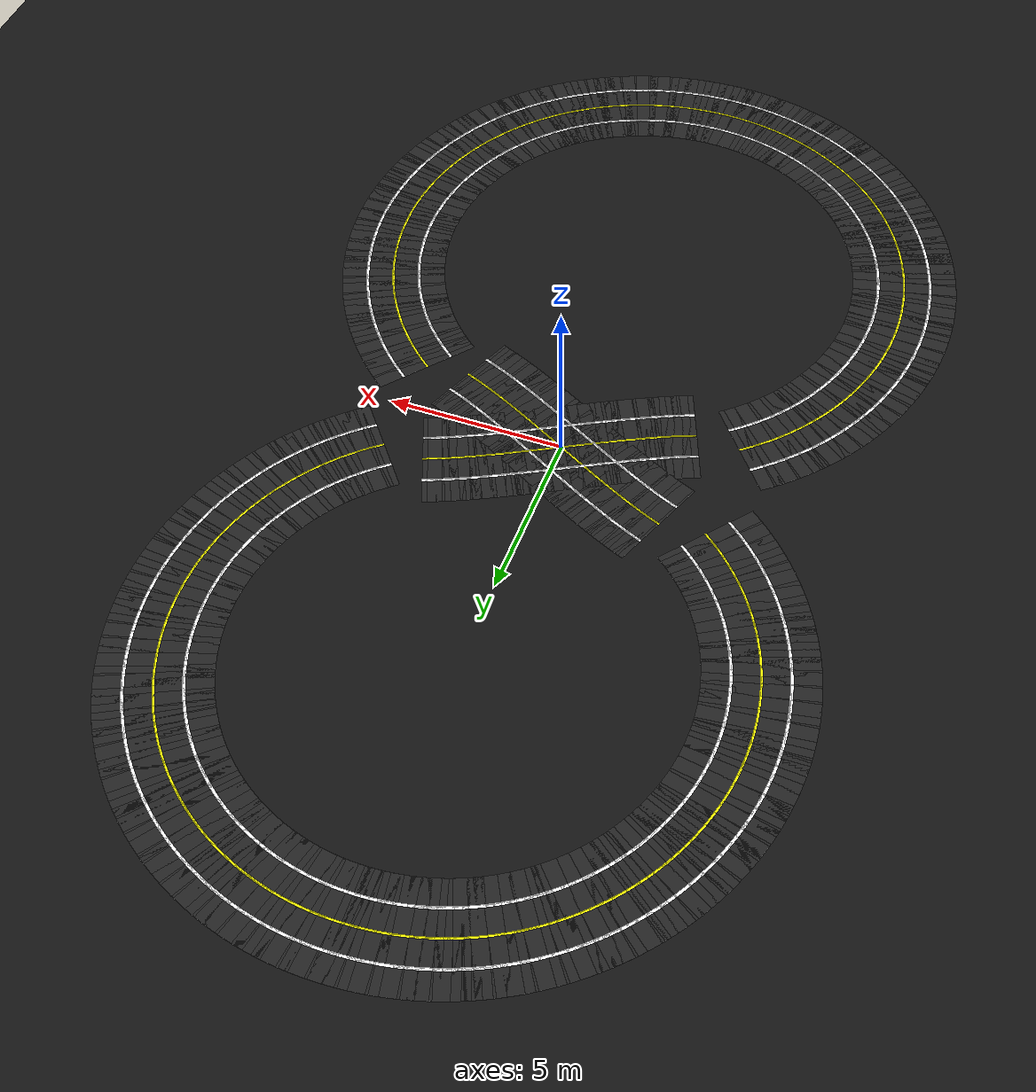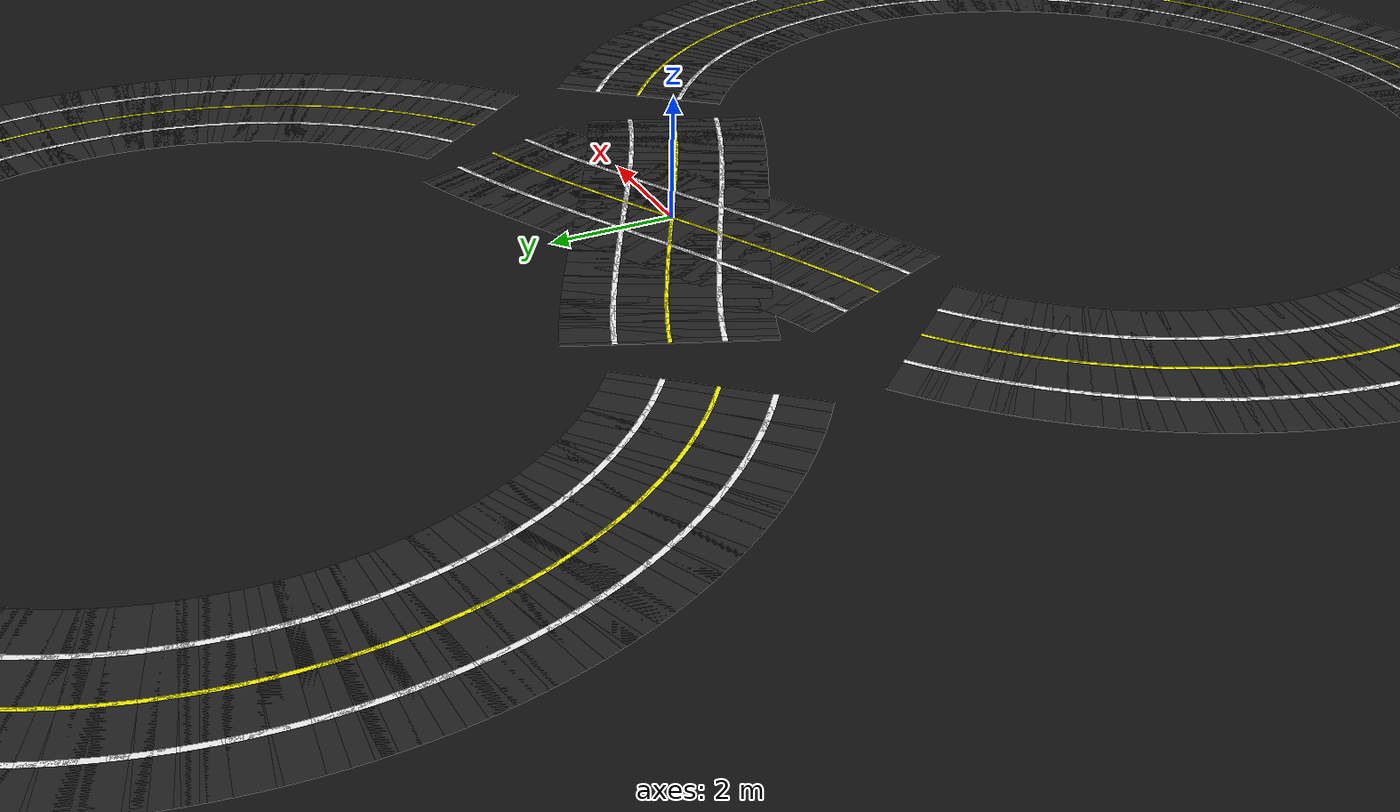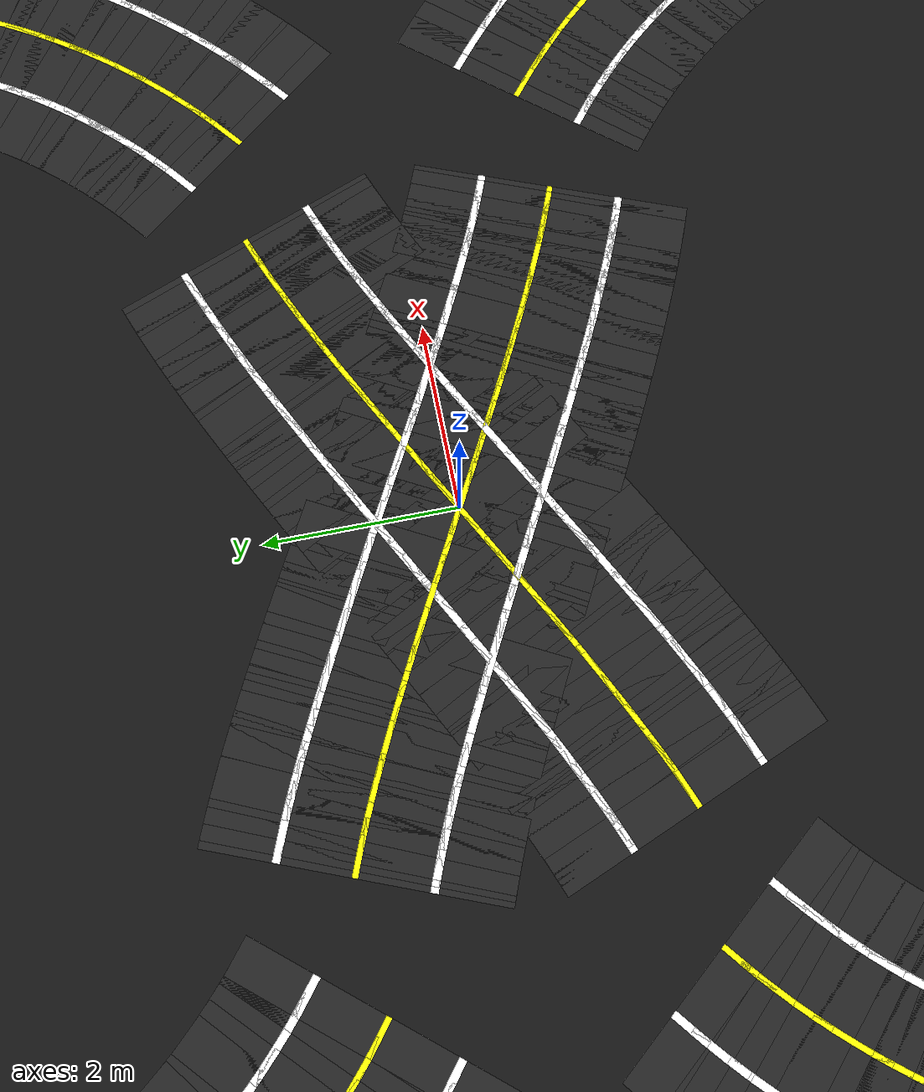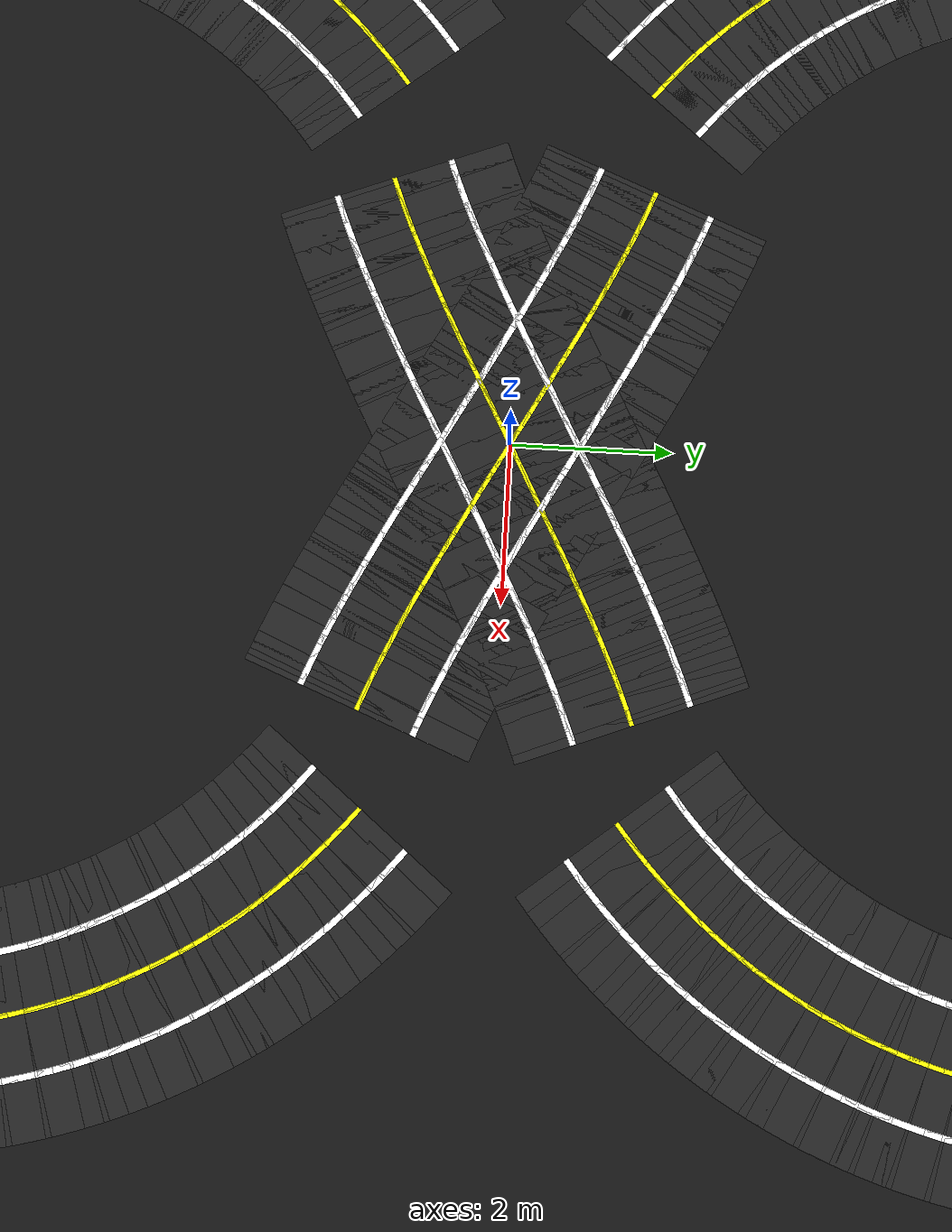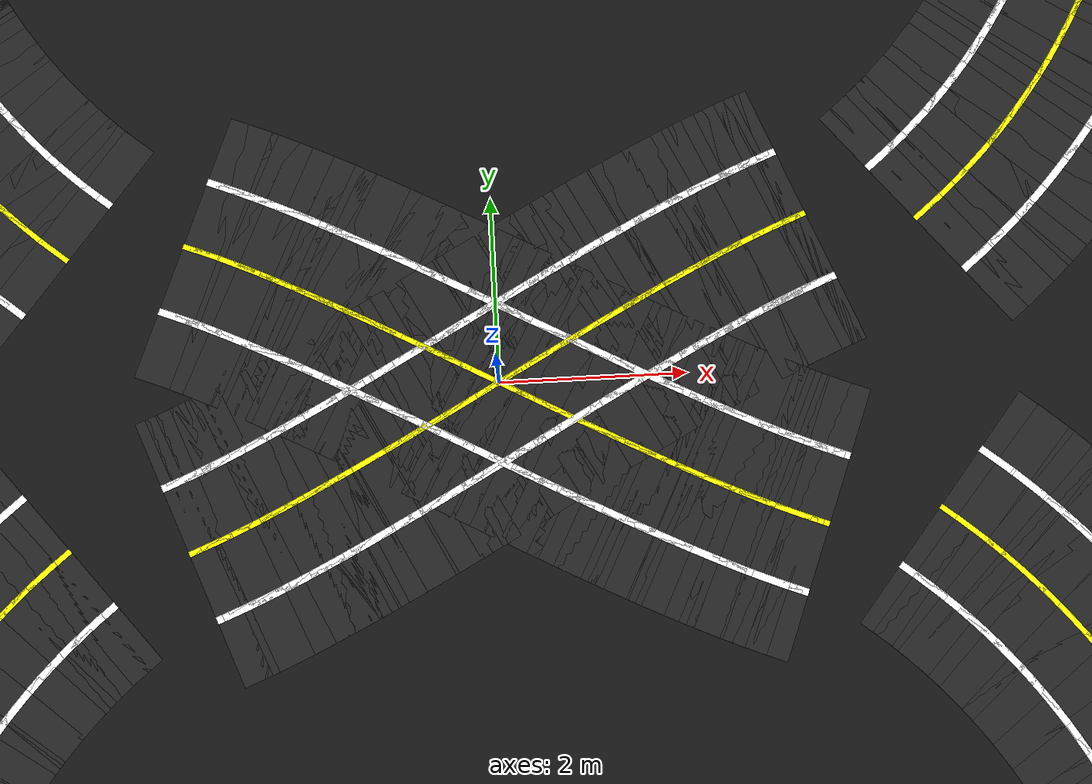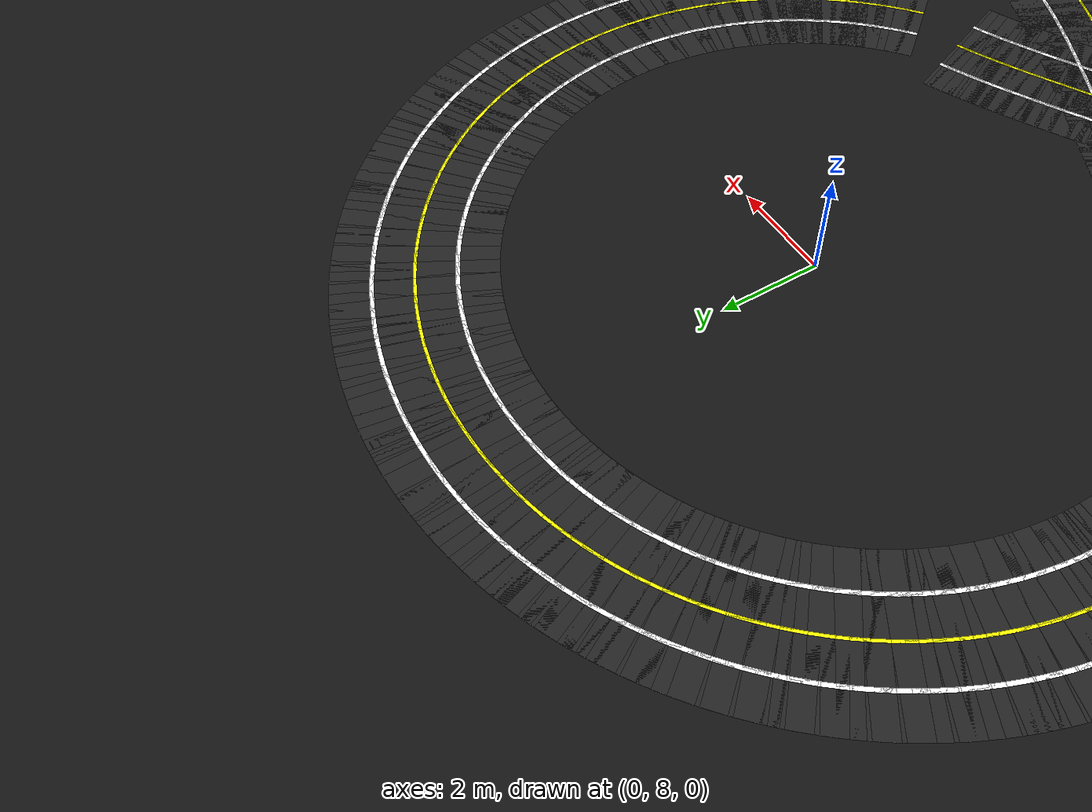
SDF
<?xml version="1.0" ?>
<sdf version="1.6">

  <world name="figure8_world">

    <plugin
      filename="ignition-gazebo-physics-system"
      name="ignition::gazebo::systems::Physics"/>

    <plugin
      filename="libignition-gazebo-sensors-system.so"
      name="ignition::gazebo::systems::Sensors">

      <render_engine>ogre2</render_engine>

    </plugin>

    <plugin
      filename="ignition-gazebo-scene-broadcaster-system"
      name="ignition::gazebo::systems::SceneBroadcaster"/>

    <plugin
      filename="ignition-gazebo-user-commands-system"
      name="ignition::gazebo::systems::UserCommands"/>

    <!-- SUN -->

    <light type="directional" name="sun">

      <cast_shadows>true</cast_shadows>

      <pose>0 0 30 0 0 0</pose>

      <diffuse>0.9 0.9 0.9 1</diffuse>
      <specular>0.2 0.2 0.2 1</specular>

      <direction>-0.4 0.1 -0.9</direction>

    </light>

    <!-- GROUND -->

    <model name="ground_plane">

      <static>true</static>

      <link name="link">

        <collision name="collision">

          <geometry>

            <plane>
              <normal>0 0 1</normal>
              <size>120 120</size>
            </plane>

          </geometry>

        </collision>

        <visual name="visual">

          <geometry>

            <plane>
              <normal>0 0 1</normal>
              <size>120 120</size>
            </plane>

          </geometry>

          <material>

            <ambient>0.08 0.08 0.08 1</ambient>
            <diffuse>0.08 0.08 0.08 1</diffuse>

          </material>

        </visual>

      </link>

    </model>

    <model name="seg_00000">
      <static>true</static>

      <pose>7.5000 7.5000 0.0010 0 0 1.5708</pose>

      <link name="link">

        <collision name="collision">
          <geometry>
            <box>
              <size>0.4000 3.0000 0.002</size>
            </box>
          </geometry>
        </collision>

        <visual name="visual">
          <geometry>
            <box>
              <size>0.4000 3.0000 0.002</size>
            </box>
          </geometry>

          <material>

<ambient>0.14 0.14 0.14 1</ambient>
<diffuse>0.14 0.14 0.14 1</diffuse>

          </material>

        </visual>

      </link>
    </model>

    <model name="seg_00001">
      <static>true</static>

      <pose>8.2500 7.5000 0.0030 0 0 1.5708</pose>

      <link name="link">

        <collision name="collision">
          <geometry>
            <box>
              <size>0.4000 0.0800 0.002</size>
            </box>
          </geometry>
        </collision>

        <visual name="visual">
          <geometry>
            <box>
              <size>0.4000 0.0800 0.002</size>
            </box>
          </geometry>

          <material>

<ambient>1 1 1 1</ambient>
<diffuse>1 1 1 1</diffuse>

          </material>

        </visual>

      </link>
    </model>

    <model name="seg_00002">
      <static>true</static>

      <pose>6.7500 7.5000 0.0030 0 0 1.5708</pose>

      <link name="link">

        <collision name="collision">
          <geometry>
            <box>
              <size>0.4000 0.0800 0.002</size>
            </box>
          </geometry>
        </collision>

        <visual name="visual">
          <geometry>
            <box>
              <size>0.4000 0.0800 0.002</size>
            </box>
          </geometry>

          <material>

<ambient>1 1 1 1</ambient>
<diffuse>1 1 1 1</diffuse>

          </material>

        </visual>

      </link>
    </model>

    <model name="seg_00003">
      <static>true</static>

      <pose>7.5000 7.5000 0.0030 0 0 1.5708</pose>

      <link name="link">

        <collision name="collision">
          <geometry>
            <box>
              <size>0.4000 0.0600 0.002</size>
            </box>
          </geometry>
        </collision>

        <visual name="visual">
          <geometry>
            <box>
              <size>0.4000 0.0600 0.002</size>
            </box>
          </geometry>

          <material>

<ambient>1 1 0 1</ambient>
<diffuse>1 1 0 1</diffuse>

          </material>

        </visual>

      </link>
    </model>

    <model name="seg_00004">
      <static>true</static>

      <pose>7.4974 7.6963 0.0010 0 0 1.5970</pose>

      <link name="link">

        <collision name="collision">
          <geometry>
            <box>
              <size>0.4000 3.0000 0.002</size>
            </box>
          </geometry>
        </collision>

        <visual name="visual">
          <geometry>
            <box>
              <size>0.4000 3.0000 0.002</size>
            </box>
          </geometry>

          <material>

<ambient>0.14 0.14 0.14 1</ambient>
<diffuse>0.14 0.14 0.14 1</diffuse>

          </material>

        </visual>

      </link>
    </model>

    <model name="seg_00005">
      <static>true</static>

      <pose>8.2472 7.7160 0.0030 0 0 1.5970</pose>

      <link name="link">

        <collision name="collision">
          <geometry>
            <box>
              <size>0.4000 0.0800 0.002</size>
            </box>
          </geometry>
        </collision>

        <visual name="visual">
          <geometry>
            <box>
              <size>0.4000 0.0800 0.002</size>
            </box>
          </geometry>

          <material>

<ambient>1 1 1 1</ambient>
<diffuse>1 1 1 1</diffuse>

          </material>

        </visual>

      </link>
    </model>

    <model name="seg_00006">
      <static>true</static>

      <pose>6.7477 7.6767 0.0030 0 0 1.5970</pose>

      <link name="link">

        <collision name="collision">
          <geometry>
            <box>
              <size>0.4000 0.0800 0.002</size>
            </box>
          </geometry>
        </collision>

        <visual name="visual">
          <geometry>
            <box>
              <size>0.4000 0.0800 0.002</size>
            </box>
          </geometry>

          <material>

<ambient>1 1 1 1</ambient>
<diffuse>1 1 1 1</diffuse>

          </material>

        </visual>

      </link>
    </model>

    <model name="seg_00007">
      <static>true</static>

      <pose>7.4974 7.6963 0.0030 0 0 1.5970</pose>

      <link name="link">

        <collision name="collision">
          <geometry>
            <box>
              <size>0.4000 0.0600 0.002</size>
            </box>
          </geometry>
        </collision>

        <visual name="visual">
          <geometry>
            <box>
              <size>0.4000 0.0600 0.002</size>
            </box>
          </geometry>

          <material>

<ambient>1 1 0 1</ambient>
<diffuse>1 1 0 1</diffuse>

          </material>

        </visual>

      </link>
    </model>

    <model name="seg_00008">
      <static>true</static>

      <pose>7.4897 7.8925 0.0010 0 0 1.6232</pose>

      <link name="link">

        <collision name="collision">
          <geometry>
            <box>
              <size>0.4000 3.0000 0.002</size>
            </box>
          </geometry>
        </collision>

        <visual name="visual">
          <geometry>
            <box>
              <size>0.4000 3.0000 0.002</size>
            </box>
          </geometry>

          <material>

<ambient>0.14 0.14 0.14 1</ambient>
<diffuse>0.14 0.14 0.14 1</diffuse>

          </material>

        </visual>

      </link>
    </model>

    <model name="seg_00009">
      <static>true</static>

      <pose>8.2387 7.9318 0.0030 0 0 1.6232</pose>

      <link name="link">

        <collision name="collision">
          <geometry>
            <box>
              <size>0.4000 0.0800 0.002</size>
            </box>
          </geometry>
        </collision>

        <visual name="visual">
          <geometry>
            <box>
              <size>0.4000 0.0800 0.002</size>
            </box>
          </geometry>

          <material>

<ambient>1 1 1 1</ambient>
<diffuse>1 1 1 1</diffuse>

          </material>

        </visual>

      </link>
    </model>

    <model name="seg_00010">
      <static>true</static>

      <pose>6.7407 7.8533 0.0030 0 0 1.6232</pose>

      <link name="link">

        <collision name="collision">
          <geometry>
            <box>
              <size>0.4000 0.0800 0.002</size>
            </box>
          </geometry>
        </collision>

        <visual name="visual">
          <geometry>
            <box>
              <size>0.4000 0.0800 0.002</size>
            </box>
          </geometry>

          <material>

<ambient>1 1 1 1</ambient>
<diffuse>1 1 1 1</diffuse>

          </material>

        </visual>

      </link>
    </model>

    <model name="seg_00011">
      <static>true</static>

      <pose>7.4897 7.8925 0.0030 0 0 1.6232</pose>

      <link name="link">

        <collision name="collision">
          <geometry>
            <box>
              <size>0.4000 0.0600 0.002</size>
            </box>
          </geometry>
        </collision>

        <visual name="visual">
          <geometry>
            <box>
              <size>0.4000 0.0600 0.002</size>
            </box>
          </geometry>

          <material>

<ambient>1 1 0 1</ambient>
<diffuse>1 1 0 1</diffuse>

          </material>

        </visual>

      </link>
    </model>

    <model name="seg_00012">
      <static>true</static>

      <pose>7.4769 8.0884 0.0010 0 0 1.6493</pose>

      <link name="link">

        <collision name="collision">
          <geometry>
            <box>
              <size>0.4000 3.0000 0.002</size>
            </box>
          </geometry>
        </collision>

        <visual name="visual">
          <geometry>
            <box>
              <size>0.4000 3.0000 0.002</size>
            </box>
          </geometry>

          <material>

<ambient>0.14 0.14 0.14 1</ambient>
<diffuse>0.14 0.14 0.14 1</diffuse>

          </material>

        </visual>

      </link>
    </model>

    <model name="seg_00013">
      <static>true</static>

      <pose>8.2246 8.1473 0.0030 0 0 1.6493</pose>

      <link name="link">

        <collision name="collision">
          <geometry>
            <box>
              <size>0.4000 0.0800 0.002</size>
            </box>
          </geometry>
        </collision>

        <visual name="visual">
          <geometry>
            <box>
              <size>0.4000 0.0800 0.002</size>
            </box>
          </geometry>

          <material>

<ambient>1 1 1 1</ambient>
<diffuse>1 1 1 1</diffuse>

          </material>

        </visual>

      </link>
    </model>

    <model name="seg_00014">
      <static>true</static>

      <pose>6.7292 8.0296 0.0030 0 0 1.6493</pose>

      <link name="link">

        <collision name="collision">
          <geometry>
            <box>
              <size>0.4000 0.0800 0.002</size>
            </box>
          </geometry>
        </collision>

        <visual name="visual">
          <geometry>
            <box>
              <size>0.4000 0.0800 0.002</size>
            </box>
          </geometry>

          <material>

<ambient>1 1 1 1</ambient>
<diffuse>1 1 1 1</diffuse>

          </material>

        </visual>

      </link>
    </model>

    <model name="seg_00015">
      <static>true</static>

      <pose>7.4769 8.0884 0.0030 0 0 1.6493</pose>

      <link name="link">

        <collision name="collision">
          <geometry>
            <box>
              <size>0.4000 0.0600 0.002</size>
            </box>
          </geometry>
        </collision>

        <visual name="visual">
          <geometry>
            <box>
              <size>0.4000 0.0600 0.002</size>
            </box>
          </geometry>

          <material>

<ambient>1 1 0 1</ambient>
<diffuse>1 1 0 1</diffuse>

          </material>

        </visual>

      </link>
    </model>

    <model name="seg_00016">
      <static>true</static>

      <pose>7.4589 8.2840 0.0010 0 0 1.6755</pose>

      <link name="link">

        <collision name="collision">
          <geometry>
            <box>
              <size>0.4000 3.0000 0.002</size>
            </box>
          </geometry>
        </collision>

        <visual name="visual">
          <geometry>
            <box>
              <size>0.4000 3.0000 0.002</size>
            </box>
          </geometry>

          <material>

<ambient>0.14 0.14 0.14 1</ambient>
<diffuse>0.14 0.14 0.14 1</diffuse>

          </material>

        </visual>

      </link>
    </model>

    <model name="seg_00017">
      <static>true</static>

      <pose>8.2048 8.3624 0.0030 0 0 1.6755</pose>

      <link name="link">

        <collision name="collision">
          <geometry>
            <box>
              <size>0.4000 0.0800 0.002</size>
            </box>
          </geometry>
        </collision>

        <visual name="visual">
          <geometry>
            <box>
              <size>0.4000 0.0800 0.002</size>
            </box>
          </geometry>

          <material>

<ambient>1 1 1 1</ambient>
<diffuse>1 1 1 1</diffuse>

          </material>

        </visual>

      </link>
    </model>

    <model name="seg_00018">
      <static>true</static>

      <pose>6.7130 8.2056 0.0030 0 0 1.6755</pose>

      <link name="link">

        <collision name="collision">
          <geometry>
            <box>
              <size>0.4000 0.0800 0.002</size>
            </box>
          </geometry>
        </collision>

        <visual name="visual">
          <geometry>
            <box>
              <size>0.4000 0.0800 0.002</size>
            </box>
          </geometry>

          <material>

<ambient>1 1 1 1</ambient>
<diffuse>1 1 1 1</diffuse>

          </material>

        </visual>

      </link>
    </model>

    <model name="seg_00019">
      <static>true</static>

      <pose>7.4589 8.2840 0.0030 0 0 1.6755</pose>

      <link name="link">

        <collision name="collision">
          <geometry>
            <box>
              <size>0.4000 0.0600 0.002</size>
            </box>
          </geometry>
        </collision>

        <visual name="visual">
          <geometry>
            <box>
              <size>0.4000 0.0600 0.002</size>
            </box>
          </geometry>

          <material>

<ambient>1 1 0 1</ambient>
<diffuse>1 1 0 1</diffuse>

          </material>

        </visual>

      </link>
    </model>

    <model name="seg_00020">
      <static>true</static>

      <pose>7.4358 8.4789 0.0010 0 0 1.7017</pose>

      <link name="link">

        <collision name="collision">
          <geometry>
            <box>
              <size>0.4000 3.0000 0.002</size>
            </box>
          </geometry>
        </collision>

        <visual name="visual">
          <geometry>
            <box>
              <size>0.4000 3.0000 0.002</size>
            </box>
          </geometry>

          <material>

<ambient>0.14 0.14 0.14 1</ambient>
<diffuse>0.14 0.14 0.14 1</diffuse>

          </material>

        </visual>

      </link>
    </model>

    <model name="seg_00021">
      <static>true</static>

      <pose>8.1794 8.5768 0.0030 0 0 1.7017</pose>

      <link name="link">

        <collision name="collision">
          <geometry>
            <box>
              <size>0.4000 0.0800 0.002</size>
            </box>
          </geometry>
        </collision>

        <visual name="visual">
          <geometry>
            <box>
              <size>0.4000 0.0800 0.002</size>
            </box>
          </geometry>

          <material>

<ambient>1 1 1 1</ambient>
<diffuse>1 1 1 1</diffuse>

          </material>

        </visual>

      </link>
    </model>

    <model name="seg_00022">
      <static>true</static>

      <pose>6.6923 8.3811 0.0030 0 0 1.7017</pose>

      <link name="link">

        <collision name="collision">
          <geometry>
            <box>
              <size>0.4000 0.0800 0.002</size>
            </box>
          </geometry>
        </collision>

        <visual name="visual">
          <geometry>
            <box>
              <size>0.4000 0.0800 0.002</size>
            </box>
          </geometry>

          <material>

<ambient>1 1 1 1</ambient>
<diffuse>1 1 1 1</diffuse>

          </material>

        </visual>

      </link>
    </model>

    <model name="seg_00023">
      <static>true</static>

      <pose>7.4358 8.4789 0.0030 0 0 1.7017</pose>

      <link name="link">

        <collision name="collision">
          <geometry>
            <box>
              <size>0.4000 0.0600 0.002</size>
            </box>
          </geometry>
        </collision>

        <visual name="visual">
          <geometry>
            <box>
              <size>0.4000 0.0600 0.002</size>
            </box>
          </geometry>

          <material>

<ambient>1 1 0 1</ambient>
<diffuse>1 1 0 1</diffuse>

          </material>

        </visual>

      </link>
    </model>

    <model name="seg_00024">
      <static>true</static>

      <pose>7.4077 8.6733 0.0010 0 0 1.7279</pose>

      <link name="link">

        <collision name="collision">
          <geometry>
            <box>
              <size>0.4000 3.0000 0.002</size>
            </box>
          </geometry>
        </collision>

        <visual name="visual">
          <geometry>
            <box>
              <size>0.4000 3.0000 0.002</size>
            </box>
          </geometry>

          <material>

<ambient>0.14 0.14 0.14 1</ambient>
<diffuse>0.14 0.14 0.14 1</diffuse>

          </material>

        </visual>

      </link>
    </model>

    <model name="seg_00025">
      <static>true</static>

      <pose>8.1484 8.7906 0.0030 0 0 1.7279</pose>

      <link name="link">

        <collision name="collision">
          <geometry>
            <box>
              <size>0.4000 0.0800 0.002</size>
            </box>
          </geometry>
        </collision>

        <visual name="visual">
          <geometry>
            <box>
              <size>0.4000 0.0800 0.002</size>
            </box>
          </geometry>

          <material>

<ambient>1 1 1 1</ambient>
<diffuse>1 1 1 1</diffuse>

          </material>

        </visual>

      </link>
    </model>

    <model name="seg_00026">
      <static>true</static>

      <pose>6.6669 8.5559 0.0030 0 0 1.7279</pose>

      <link name="link">

        <collision name="collision">
          <geometry>
            <box>
              <size>0.4000 0.0800 0.002</size>
            </box>
          </geometry>
        </collision>

        <visual name="visual">
          <geometry>
            <box>
              <size>0.4000 0.0800 0.002</size>
            </box>
          </geometry>

          <material>

<ambient>1 1 1 1</ambient>
<diffuse>1 1 1 1</diffuse>

          </material>

        </visual>

      </link>
    </model>

    <model name="seg_00027">
      <static>true</static>

      <pose>7.4077 8.6733 0.0030 0 0 1.7279</pose>

      <link name="link">

        <collision name="collision">
          <geometry>
            <box>
              <size>0.4000 0.0600 0.002</size>
            </box>
          </geometry>
        </collision>

        <visual name="visual">
          <geometry>
            <box>
              <size>0.4000 0.0600 0.002</size>
            </box>
          </geometry>

          <material>

<ambient>1 1 0 1</ambient>
<diffuse>1 1 0 1</diffuse>

          </material>

        </visual>

      </link>
    </model>

    <model name="seg_00028">
      <static>true</static>

      <pose>7.3744 8.8668 0.0010 0 0 1.7541</pose>

      <link name="link">

        <collision name="collision">
          <geometry>
            <box>
              <size>0.4000 3.0000 0.002</size>
            </box>
          </geometry>
        </collision>

        <visual name="visual">
          <geometry>
            <box>
              <size>0.4000 3.0000 0.002</size>
            </box>
          </geometry>

          <material>

<ambient>0.14 0.14 0.14 1</ambient>
<diffuse>0.14 0.14 0.14 1</diffuse>

          </material>

        </visual>

      </link>
    </model>

    <model name="seg_00029">
      <static>true</static>

      <pose>8.1119 9.0034 0.0030 0 0 1.7541</pose>

      <link name="link">

        <collision name="collision">
          <geometry>
            <box>
              <size>0.4000 0.0800 0.002</size>
            </box>
          </geometry>
        </collision>

        <visual name="visual">
          <geometry>
            <box>
              <size>0.4000 0.0800 0.002</size>
            </box>
          </geometry>

          <material>

<ambient>1 1 1 1</ambient>
<diffuse>1 1 1 1</diffuse>

          </material>

        </visual>

      </link>
    </model>

    <model name="seg_00030">
      <static>true</static>

      <pose>6.6370 8.7301 0.0030 0 0 1.7541</pose>

      <link name="link">

        <collision name="collision">
          <geometry>
            <box>
              <size>0.4000 0.0800 0.002</size>
            </box>
          </geometry>
        </collision>

        <visual name="visual">
          <geometry>
            <box>
              <size>0.4000 0.0800 0.002</size>
            </box>
          </geometry>

          <material>

<ambient>1 1 1 1</ambient>
<diffuse>1 1 1 1</diffuse>

          </material>

        </visual>

      </link>
    </model>

    <model name="seg_00031">
      <static>true</static>

      <pose>7.3744 8.8668 0.0030 0 0 1.7541</pose>

      <link name="link">

        <collision name="collision">
          <geometry>
            <box>
              <size>0.4000 0.0600 0.002</size>
            </box>
          </geometry>
        </collision>

        <visual name="visual">
          <geometry>
            <box>
              <size>0.4000 0.0600 0.002</size>
            </box>
          </geometry>

          <material>

<ambient>1 1 0 1</ambient>
<diffuse>1 1 0 1</diffuse>

          </material>

        </visual>

      </link>
    </model>

    <model name="seg_00032">
      <static>true</static>

      <pose>7.3361 9.0593 0.0010 0 0 1.7802</pose>

      <link name="link">

        <collision name="collision">
          <geometry>
            <box>
              <size>0.4000 3.0000 0.002</size>
            </box>
          </geometry>
        </collision>

        <visual name="visual">
          <geometry>
            <box>
              <size>0.4000 3.0000 0.002</size>
            </box>
          </geometry>

          <material>

<ambient>0.14 0.14 0.14 1</ambient>
<diffuse>0.14 0.14 0.14 1</diffuse>

          </material>

        </visual>

      </link>
    </model>

    <model name="seg_00033">
      <static>true</static>

      <pose>8.0697 9.2153 0.0030 0 0 1.7802</pose>

      <link name="link">

        <collision name="collision">
          <geometry>
            <box>
              <size>0.4000 0.0800 0.002</size>
            </box>
          </geometry>
        </collision>

        <visual name="visual">
          <geometry>
            <box>
              <size>0.4000 0.0800 0.002</size>
            </box>
          </geometry>

          <material>

<ambient>1 1 1 1</ambient>
<diffuse>1 1 1 1</diffuse>

          </material>

        </visual>

      </link>
    </model>

    <model name="seg_00034">
      <static>true</static>

      <pose>6.6025 8.9034 0.0030 0 0 1.7802</pose>

      <link name="link">

        <collision name="collision">
          <geometry>
            <box>
              <size>0.4000 0.0800 0.002</size>
            </box>
          </geometry>
        </collision>

        <visual name="visual">
          <geometry>
            <box>
              <size>0.4000 0.0800 0.002</size>
            </box>
          </geometry>

          <material>

<ambient>1 1 1 1</ambient>
<diffuse>1 1 1 1</diffuse>

          </material>

        </visual>

      </link>
    </model>

    <model name="seg_00035">
      <static>true</static>

      <pose>7.3361 9.0593 0.0030 0 0 1.7802</pose>

      <link name="link">

        <collision name="collision">
          <geometry>
            <box>
              <size>0.4000 0.0600 0.002</size>
            </box>
          </geometry>
        </collision>

        <visual name="visual">
          <geometry>
            <box>
              <size>0.4000 0.0600 0.002</size>
            </box>
          </geometry>

          <material>

<ambient>1 1 0 1</ambient>
<diffuse>1 1 0 1</diffuse>

          </material>

        </visual>

      </link>
    </model>

    <model name="seg_00036">
      <static>true</static>

      <pose>7.2928 9.2508 0.0010 0 0 1.8064</pose>

      <link name="link">

        <collision name="collision">
          <geometry>
            <box>
              <size>0.4000 3.0000 0.002</size>
            </box>
          </geometry>
        </collision>

        <visual name="visual">
          <geometry>
            <box>
              <size>0.4000 3.0000 0.002</size>
            </box>
          </geometry>

          <material>

<ambient>0.14 0.14 0.14 1</ambient>
<diffuse>0.14 0.14 0.14 1</diffuse>

          </material>

        </visual>

      </link>
    </model>

    <model name="seg_00037">
      <static>true</static>

      <pose>8.0221 9.4259 0.0030 0 0 1.8064</pose>

      <link name="link">

        <collision name="collision">
          <geometry>
            <box>
              <size>0.4000 0.0800 0.002</size>
            </box>
          </geometry>
        </collision>

        <visual name="visual">
          <geometry>
            <box>
              <size>0.4000 0.0800 0.002</size>
            </box>
          </geometry>

          <material>

<ambient>1 1 1 1</ambient>
<diffuse>1 1 1 1</diffuse>

          </material>

        </visual>

      </link>
    </model>

    <model name="seg_00038">
      <static>true</static>

      <pose>6.5635 9.0758 0.0030 0 0 1.8064</pose>

      <link name="link">

        <collision name="collision">
          <geometry>
            <box>
              <size>0.4000 0.0800 0.002</size>
            </box>
          </geometry>
        </collision>

        <visual name="visual">
          <geometry>
            <box>
              <size>0.4000 0.0800 0.002</size>
            </box>
          </geometry>

          <material>

<ambient>1 1 1 1</ambient>
<diffuse>1 1 1 1</diffuse>

          </material>

        </visual>

      </link>
    </model>

    <model name="seg_00039">
      <static>true</static>

      <pose>7.2928 9.2508 0.0030 0 0 1.8064</pose>

      <link name="link">

        <collision name="collision">
          <geometry>
            <box>
              <size>0.4000 0.0600 0.002</size>
            </box>
          </geometry>
        </collision>

        <visual name="visual">
          <geometry>
            <box>
              <size>0.4000 0.0600 0.002</size>
            </box>
          </geometry>

          <material>

<ambient>1 1 0 1</ambient>
<diffuse>1 1 0 1</diffuse>

          </material>

        </visual>

      </link>
    </model>

    <model name="seg_00040">
      <static>true</static>

      <pose>7.2444 9.4411 0.0010 0 0 1.8326</pose>

      <link name="link">

        <collision name="collision">
          <geometry>
            <box>
              <size>0.4000 3.0000 0.002</size>
            </box>
          </geometry>
        </collision>

        <visual name="visual">
          <geometry>
            <box>
              <size>0.4000 3.0000 0.002</size>
            </box>
          </geometry>

          <material>

<ambient>0.14 0.14 0.14 1</ambient>
<diffuse>0.14 0.14 0.14 1</diffuse>

          </material>

        </visual>

      </link>
    </model>

    <model name="seg_00041">
      <static>true</static>

      <pose>7.9689 9.6353 0.0030 0 0 1.8326</pose>

      <link name="link">

        <collision name="collision">
          <geometry>
            <box>
              <size>0.4000 0.0800 0.002</size>
            </box>
          </geometry>
        </collision>

        <visual name="visual">
          <geometry>
            <box>
              <size>0.4000 0.0800 0.002</size>
            </box>
          </geometry>

          <material>

<ambient>1 1 1 1</ambient>
<diffuse>1 1 1 1</diffuse>

          </material>

        </visual>

      </link>
    </model>

    <model name="seg_00042">
      <static>true</static>

      <pose>6.5200 9.2470 0.0030 0 0 1.8326</pose>

      <link name="link">

        <collision name="collision">
          <geometry>
            <box>
              <size>0.4000 0.0800 0.002</size>
            </box>
          </geometry>
        </collision>

        <visual name="visual">
          <geometry>
            <box>
              <size>0.4000 0.0800 0.002</size>
            </box>
          </geometry>

          <material>

<ambient>1 1 1 1</ambient>
<diffuse>1 1 1 1</diffuse>

          </material>

        </visual>

      </link>
    </model>

    <model name="seg_00043">
      <static>true</static>

      <pose>7.2444 9.4411 0.0030 0 0 1.8326</pose>

      <link name="link">

        <collision name="collision">
          <geometry>
            <box>
              <size>0.4000 0.0600 0.002</size>
            </box>
          </geometry>
        </collision>

        <visual name="visual">
          <geometry>
            <box>
              <size>0.4000 0.0600 0.002</size>
            </box>
          </geometry>

          <material>

<ambient>1 1 0 1</ambient>
<diffuse>1 1 0 1</diffuse>

          </material>

        </visual>

      </link>
    </model>

    <model name="seg_00044">
      <static>true</static>

      <pose>7.1911 9.6301 0.0010 0 0 1.8588</pose>

      <link name="link">

        <collision name="collision">
          <geometry>
            <box>
              <size>0.4000 3.0000 0.002</size>
            </box>
          </geometry>
        </collision>

        <visual name="visual">
          <geometry>
            <box>
              <size>0.4000 3.0000 0.002</size>
            </box>
          </geometry>

          <material>

<ambient>0.14 0.14 0.14 1</ambient>
<diffuse>0.14 0.14 0.14 1</diffuse>

          </material>

        </visual>

      </link>
    </model>

    <model name="seg_00045">
      <static>true</static>

      <pose>7.9103 9.8431 0.0030 0 0 1.8588</pose>

      <link name="link">

        <collision name="collision">
          <geometry>
            <box>
              <size>0.4000 0.0800 0.002</size>
            </box>
          </geometry>
        </collision>

        <visual name="visual">
          <geometry>
            <box>
              <size>0.4000 0.0800 0.002</size>
            </box>
          </geometry>

          <material>

<ambient>1 1 1 1</ambient>
<diffuse>1 1 1 1</diffuse>

          </material>

        </visual>

      </link>
    </model>

    <model name="seg_00046">
      <static>true</static>

      <pose>6.4720 9.4171 0.0030 0 0 1.8588</pose>

      <link name="link">

        <collision name="collision">
          <geometry>
            <box>
              <size>0.4000 0.0800 0.002</size>
            </box>
          </geometry>
        </collision>

        <visual name="visual">
          <geometry>
            <box>
              <size>0.4000 0.0800 0.002</size>
            </box>
          </geometry>

          <material>

<ambient>1 1 1 1</ambient>
<diffuse>1 1 1 1</diffuse>

          </material>

        </visual>

      </link>
    </model>

    <model name="seg_00047">
      <static>true</static>

      <pose>7.1911 9.6301 0.0030 0 0 1.8588</pose>

      <link name="link">

        <collision name="collision">
          <geometry>
            <box>
              <size>0.4000 0.0600 0.002</size>
            </box>
          </geometry>
        </collision>

        <visual name="visual">
          <geometry>
            <box>
              <size>0.4000 0.0600 0.002</size>
            </box>
          </geometry>

          <material>

<ambient>1 1 0 1</ambient>
<diffuse>1 1 0 1</diffuse>

          </material>

        </visual>

      </link>
    </model>

    <model name="seg_00048">
      <static>true</static>

      <pose>7.1329 9.8176 0.0010 0 0 1.8850</pose>

      <link name="link">

        <collision name="collision">
          <geometry>
            <box>
              <size>0.4000 3.0000 0.002</size>
            </box>
          </geometry>
        </collision>

        <visual name="visual">
          <geometry>
            <box>
              <size>0.4000 3.0000 0.002</size>
            </box>
          </geometry>

          <material>

<ambient>0.14 0.14 0.14 1</ambient>
<diffuse>0.14 0.14 0.14 1</diffuse>

          </material>

        </visual>

      </link>
    </model>

    <model name="seg_00049">
      <static>true</static>

      <pose>7.8462 10.0494 0.0030 0 0 1.8850</pose>

      <link name="link">

        <collision name="collision">
          <geometry>
            <box>
              <size>0.4000 0.0800 0.002</size>
            </box>
          </geometry>
        </collision>

        <visual name="visual">
          <geometry>
            <box>
              <size>0.4000 0.0800 0.002</size>
            </box>
          </geometry>

          <material>

<ambient>1 1 1 1</ambient>
<diffuse>1 1 1 1</diffuse>

          </material>

        </visual>

      </link>
    </model>

    <model name="seg_00050">
      <static>true</static>

      <pose>6.4196 9.5859 0.0030 0 0 1.8850</pose>

      <link name="link">

        <collision name="collision">
          <geometry>
            <box>
              <size>0.4000 0.0800 0.002</size>
            </box>
          </geometry>
        </collision>

        <visual name="visual">
          <geometry>
            <box>
              <size>0.4000 0.0800 0.002</size>
            </box>
          </geometry>

          <material>

<ambient>1 1 1 1</ambient>
<diffuse>1 1 1 1</diffuse>

          </material>

        </visual>

      </link>
    </model>

    <model name="seg_00051">
      <static>true</static>

      <pose>7.1329 9.8176 0.0030 0 0 1.8850</pose>

      <link name="link">

        <collision name="collision">
          <geometry>
            <box>
              <size>0.4000 0.0600 0.002</size>
            </box>
          </geometry>
        </collision>

        <visual name="visual">
          <geometry>
            <box>
              <size>0.4000 0.0600 0.002</size>
            </box>
          </geometry>

          <material>

<ambient>1 1 0 1</ambient>
<diffuse>1 1 0 1</diffuse>

          </material>

        </visual>

      </link>
    </model>

    <model name="seg_00052">
      <static>true</static>

      <pose>7.0698 10.0036 0.0010 0 0 1.9111</pose>

      <link name="link">

        <collision name="collision">
          <geometry>
            <box>
              <size>0.4000 3.0000 0.002</size>
            </box>
          </geometry>
        </collision>

        <visual name="visual">
          <geometry>
            <box>
              <size>0.4000 3.0000 0.002</size>
            </box>
          </geometry>

          <material>

<ambient>0.14 0.14 0.14 1</ambient>
<diffuse>0.14 0.14 0.14 1</diffuse>

          </material>

        </visual>

      </link>
    </model>

    <model name="seg_00053">
      <static>true</static>

      <pose>7.7768 10.2539 0.0030 0 0 1.9111</pose>

      <link name="link">

        <collision name="collision">
          <geometry>
            <box>
              <size>0.4000 0.0800 0.002</size>
            </box>
          </geometry>
        </collision>

        <visual name="visual">
          <geometry>
            <box>
              <size>0.4000 0.0800 0.002</size>
            </box>
          </geometry>

          <material>

<ambient>1 1 1 1</ambient>
<diffuse>1 1 1 1</diffuse>

          </material>

        </visual>

      </link>
    </model>

    <model name="seg_00054">
      <static>true</static>

      <pose>6.3628 9.7532 0.0030 0 0 1.9111</pose>

      <link name="link">

        <collision name="collision">
          <geometry>
            <box>
              <size>0.4000 0.0800 0.002</size>
            </box>
          </geometry>
        </collision>

        <visual name="visual">
          <geometry>
            <box>
              <size>0.4000 0.0800 0.002</size>
            </box>
          </geometry>

          <material>

<ambient>1 1 1 1</ambient>
<diffuse>1 1 1 1</diffuse>

          </material>

        </visual>

      </link>
    </model>

    <model name="seg_00055">
      <static>true</static>

      <pose>7.0698 10.0036 0.0030 0 0 1.9111</pose>

      <link name="link">

        <collision name="collision">
          <geometry>
            <box>
              <size>0.4000 0.0600 0.002</size>
            </box>
          </geometry>
        </collision>

        <visual name="visual">
          <geometry>
            <box>
              <size>0.4000 0.0600 0.002</size>
            </box>
          </geometry>

          <material>

<ambient>1 1 0 1</ambient>
<diffuse>1 1 0 1</diffuse>

          </material>

        </visual>

      </link>
    </model>

    <model name="seg_00056">
      <static>true</static>

      <pose>7.0019 10.1878 0.0010 0 0 1.9373</pose>

      <link name="link">

        <collision name="collision">
          <geometry>
            <box>
              <size>0.4000 3.0000 0.002</size>
            </box>
          </geometry>
        </collision>

        <visual name="visual">
          <geometry>
            <box>
              <size>0.4000 3.0000 0.002</size>
            </box>
          </geometry>

          <material>

<ambient>0.14 0.14 0.14 1</ambient>
<diffuse>0.14 0.14 0.14 1</diffuse>

          </material>

        </visual>

      </link>
    </model>

    <model name="seg_00057">
      <static>true</static>

      <pose>7.7020 10.4565 0.0030 0 0 1.9373</pose>

      <link name="link">

        <collision name="collision">
          <geometry>
            <box>
              <size>0.4000 0.0800 0.002</size>
            </box>
          </geometry>
        </collision>

        <visual name="visual">
          <geometry>
            <box>
              <size>0.4000 0.0800 0.002</size>
            </box>
          </geometry>

          <material>

<ambient>1 1 1 1</ambient>
<diffuse>1 1 1 1</diffuse>

          </material>

        </visual>

      </link>
    </model>

    <model name="seg_00058">
      <static>true</static>

      <pose>6.3017 9.9190 0.0030 0 0 1.9373</pose>

      <link name="link">

        <collision name="collision">
          <geometry>
            <box>
              <size>0.4000 0.0800 0.002</size>
            </box>
          </geometry>
        </collision>

        <visual name="visual">
          <geometry>
            <box>
              <size>0.4000 0.0800 0.002</size>
            </box>
          </geometry>

          <material>

<ambient>1 1 1 1</ambient>
<diffuse>1 1 1 1</diffuse>

          </material>

        </visual>

      </link>
    </model>

    <model name="seg_00059">
      <static>true</static>

      <pose>7.0019 10.1878 0.0030 0 0 1.9373</pose>

      <link name="link">

        <collision name="collision">
          <geometry>
            <box>
              <size>0.4000 0.0600 0.002</size>
            </box>
          </geometry>
        </collision>

        <visual name="visual">
          <geometry>
            <box>
              <size>0.4000 0.0600 0.002</size>
            </box>
          </geometry>

          <material>

<ambient>1 1 0 1</ambient>
<diffuse>1 1 0 1</diffuse>

          </material>

        </visual>

      </link>
    </model>

    <model name="seg_00060">
      <static>true</static>

      <pose>6.9291 10.3701 0.0010 0 0 1.9635</pose>

      <link name="link">

        <collision name="collision">
          <geometry>
            <box>
              <size>0.4000 3.0000 0.002</size>
            </box>
          </geometry>
        </collision>

        <visual name="visual">
          <geometry>
            <box>
              <size>0.4000 3.0000 0.002</size>
            </box>
          </geometry>

          <material>

<ambient>0.14 0.14 0.14 1</ambient>
<diffuse>0.14 0.14 0.14 1</diffuse>

          </material>

        </visual>

      </link>
    </model>

    <model name="seg_00061">
      <static>true</static>

      <pose>7.6220 10.6571 0.0030 0 0 1.9635</pose>

      <link name="link">

        <collision name="collision">
          <geometry>
            <box>
              <size>0.4000 0.0800 0.002</size>
            </box>
          </geometry>
        </collision>

        <visual name="visual">
          <geometry>
            <box>
              <size>0.4000 0.0800 0.002</size>
            </box>
          </geometry>

          <material>

<ambient>1 1 1 1</ambient>
<diffuse>1 1 1 1</diffuse>

          </material>

        </visual>

      </link>
    </model>

    <model name="seg_00062">
      <static>true</static>

      <pose>6.2362 10.0831 0.0030 0 0 1.9635</pose>

      <link name="link">

        <collision name="collision">
          <geometry>
            <box>
              <size>0.4000 0.0800 0.002</size>
            </box>
          </geometry>
        </collision>

        <visual name="visual">
          <geometry>
            <box>
              <size>0.4000 0.0800 0.002</size>
            </box>
          </geometry>

          <material>

<ambient>1 1 1 1</ambient>
<diffuse>1 1 1 1</diffuse>

          </material>

        </visual>

      </link>
    </model>

    <model name="seg_00063">
      <static>true</static>

      <pose>6.9291 10.3701 0.0030 0 0 1.9635</pose>

      <link name="link">

        <collision name="collision">
          <geometry>
            <box>
              <size>0.4000 0.0600 0.002</size>
            </box>
          </geometry>
        </collision>

        <visual name="visual">
          <geometry>
            <box>
              <size>0.4000 0.0600 0.002</size>
            </box>
          </geometry>

          <material>

<ambient>1 1 0 1</ambient>
<diffuse>1 1 0 1</diffuse>

          </material>

        </visual>

      </link>
    </model>

    <model name="seg_00064">
      <static>true</static>

      <pose>6.8516 10.5505 0.0010 0 0 1.9897</pose>

      <link name="link">

        <collision name="collision">
          <geometry>
            <box>
              <size>0.4000 3.0000 0.002</size>
            </box>
          </geometry>
        </collision>

        <visual name="visual">
          <geometry>
            <box>
              <size>0.4000 3.0000 0.002</size>
            </box>
          </geometry>

          <material>

<ambient>0.14 0.14 0.14 1</ambient>
<diffuse>0.14 0.14 0.14 1</diffuse>

          </material>

        </visual>

      </link>
    </model>

    <model name="seg_00065">
      <static>true</static>

      <pose>7.5368 10.8556 0.0030 0 0 1.9897</pose>

      <link name="link">

        <collision name="collision">
          <geometry>
            <box>
              <size>0.4000 0.0800 0.002</size>
            </box>
          </geometry>
        </collision>

        <visual name="visual">
          <geometry>
            <box>
              <size>0.4000 0.0800 0.002</size>
            </box>
          </geometry>

          <material>

<ambient>1 1 1 1</ambient>
<diffuse>1 1 1 1</diffuse>

          </material>

        </visual>

      </link>
    </model>

    <model name="seg_00066">
      <static>true</static>

      <pose>6.1664 10.2455 0.0030 0 0 1.9897</pose>

      <link name="link">

        <collision name="collision">
          <geometry>
            <box>
              <size>0.4000 0.0800 0.002</size>
            </box>
          </geometry>
        </collision>

        <visual name="visual">
          <geometry>
            <box>
              <size>0.4000 0.0800 0.002</size>
            </box>
          </geometry>

          <material>

<ambient>1 1 1 1</ambient>
<diffuse>1 1 1 1</diffuse>

          </material>

        </visual>

      </link>
    </model>

    <model name="seg_00067">
      <static>true</static>

      <pose>6.8516 10.5505 0.0030 0 0 1.9897</pose>

      <link name="link">

        <collision name="collision">
          <geometry>
            <box>
              <size>0.4000 0.0600 0.002</size>
            </box>
          </geometry>
        </collision>

        <visual name="visual">
          <geometry>
            <box>
              <size>0.4000 0.0600 0.002</size>
            </box>
          </geometry>

          <material>

<ambient>1 1 0 1</ambient>
<diffuse>1 1 0 1</diffuse>

          </material>

        </visual>

      </link>
    </model>

    <model name="seg_00068">
      <static>true</static>

      <pose>6.7694 10.7288 0.0010 0 0 2.0159</pose>

      <link name="link">

        <collision name="collision">
          <geometry>
            <box>
              <size>0.4000 3.0000 0.002</size>
            </box>
          </geometry>
        </collision>

        <visual name="visual">
          <geometry>
            <box>
              <size>0.4000 3.0000 0.002</size>
            </box>
          </geometry>

          <material>

<ambient>0.14 0.14 0.14 1</ambient>
<diffuse>0.14 0.14 0.14 1</diffuse>

          </material>

        </visual>

      </link>
    </model>

    <model name="seg_00069">
      <static>true</static>

      <pose>7.4463 11.0517 0.0030 0 0 2.0159</pose>

      <link name="link">

        <collision name="collision">
          <geometry>
            <box>
              <size>0.4000 0.0800 0.002</size>
            </box>
          </geometry>
        </collision>

        <visual name="visual">
          <geometry>
            <box>
              <size>0.4000 0.0800 0.002</size>
            </box>
          </geometry>

          <material>

<ambient>1 1 1 1</ambient>
<diffuse>1 1 1 1</diffuse>

          </material>

        </visual>

      </link>
    </model>

    <model name="seg_00070">
      <static>true</static>

      <pose>6.0925 10.4059 0.0030 0 0 2.0159</pose>

      <link name="link">

        <collision name="collision">
          <geometry>
            <box>
              <size>0.4000 0.0800 0.002</size>
            </box>
          </geometry>
        </collision>

        <visual name="visual">
          <geometry>
            <box>
              <size>0.4000 0.0800 0.002</size>
            </box>
          </geometry>

          <material>

<ambient>1 1 1 1</ambient>
<diffuse>1 1 1 1</diffuse>

          </material>

        </visual>

      </link>
    </model>

    <model name="seg_00071">
      <static>true</static>

      <pose>6.7694 10.7288 0.0030 0 0 2.0159</pose>

      <link name="link">

        <collision name="collision">
          <geometry>
            <box>
              <size>0.4000 0.0600 0.002</size>
            </box>
          </geometry>
        </collision>

        <visual name="visual">
          <geometry>
            <box>
              <size>0.4000 0.0600 0.002</size>
            </box>
          </geometry>

          <material>

<ambient>1 1 0 1</ambient>
<diffuse>1 1 0 1</diffuse>

          </material>

        </visual>

      </link>
    </model>

    <model name="seg_00072">
      <static>true</static>

      <pose>6.6825 10.9049 0.0010 0 0 2.0420</pose>

      <link name="link">

        <collision name="collision">
          <geometry>
            <box>
              <size>0.4000 3.0000 0.002</size>
            </box>
          </geometry>
        </collision>

        <visual name="visual">
          <geometry>
            <box>
              <size>0.4000 3.0000 0.002</size>
            </box>
          </geometry>

          <material>

<ambient>0.14 0.14 0.14 1</ambient>
<diffuse>0.14 0.14 0.14 1</diffuse>

          </material>

        </visual>

      </link>
    </model>

    <model name="seg_00073">
      <static>true</static>

      <pose>7.3508 11.2454 0.0030 0 0 2.0420</pose>

      <link name="link">

        <collision name="collision">
          <geometry>
            <box>
              <size>0.4000 0.0800 0.002</size>
            </box>
          </geometry>
        </collision>

        <visual name="visual">
          <geometry>
            <box>
              <size>0.4000 0.0800 0.002</size>
            </box>
          </geometry>

          <material>

<ambient>1 1 1 1</ambient>
<diffuse>1 1 1 1</diffuse>

          </material>

        </visual>

      </link>
    </model>

    <model name="seg_00074">
      <static>true</static>

      <pose>6.0143 10.5644 0.0030 0 0 2.0420</pose>

      <link name="link">

        <collision name="collision">
          <geometry>
            <box>
              <size>0.4000 0.0800 0.002</size>
            </box>
          </geometry>
        </collision>

        <visual name="visual">
          <geometry>
            <box>
              <size>0.4000 0.0800 0.002</size>
            </box>
          </geometry>

          <material>

<ambient>1 1 1 1</ambient>
<diffuse>1 1 1 1</diffuse>

          </material>

        </visual>

      </link>
    </model>

    <model name="seg_00075">
      <static>true</static>

      <pose>6.6825 10.9049 0.0030 0 0 2.0420</pose>

      <link name="link">

        <collision name="collision">
          <geometry>
            <box>
              <size>0.4000 0.0600 0.002</size>
            </box>
          </geometry>
        </collision>

        <visual name="visual">
          <geometry>
            <box>
              <size>0.4000 0.0600 0.002</size>
            </box>
          </geometry>

          <material>

<ambient>1 1 0 1</ambient>
<diffuse>1 1 0 1</diffuse>

          </material>

        </visual>

      </link>
    </model>

    <model name="seg_00076">
      <static>true</static>

      <pose>6.5911 11.0787 0.0010 0 0 2.0682</pose>

      <link name="link">

        <collision name="collision">
          <geometry>
            <box>
              <size>0.4000 3.0000 0.002</size>
            </box>
          </geometry>
        </collision>

        <visual name="visual">
          <geometry>
            <box>
              <size>0.4000 3.0000 0.002</size>
            </box>
          </geometry>

          <material>

<ambient>0.14 0.14 0.14 1</ambient>
<diffuse>0.14 0.14 0.14 1</diffuse>

          </material>

        </visual>

      </link>
    </model>

    <model name="seg_00077">
      <static>true</static>

      <pose>7.2502 11.4366 0.0030 0 0 2.0682</pose>

      <link name="link">

        <collision name="collision">
          <geometry>
            <box>
              <size>0.4000 0.0800 0.002</size>
            </box>
          </geometry>
        </collision>

        <visual name="visual">
          <geometry>
            <box>
              <size>0.4000 0.0800 0.002</size>
            </box>
          </geometry>

          <material>

<ambient>1 1 1 1</ambient>
<diffuse>1 1 1 1</diffuse>

          </material>

        </visual>

      </link>
    </model>

    <model name="seg_00078">
      <static>true</static>

      <pose>5.9320 10.7208 0.0030 0 0 2.0682</pose>

      <link name="link">

        <collision name="collision">
          <geometry>
            <box>
              <size>0.4000 0.0800 0.002</size>
            </box>
          </geometry>
        </collision>

        <visual name="visual">
          <geometry>
            <box>
              <size>0.4000 0.0800 0.002</size>
            </box>
          </geometry>

          <material>

<ambient>1 1 1 1</ambient>
<diffuse>1 1 1 1</diffuse>

          </material>

        </visual>

      </link>
    </model>

    <model name="seg_00079">
      <static>true</static>

      <pose>6.5911 11.0787 0.0030 0 0 2.0682</pose>

      <link name="link">

        <collision name="collision">
          <geometry>
            <box>
              <size>0.4000 0.0600 0.002</size>
            </box>
          </geometry>
        </collision>

        <visual name="visual">
          <geometry>
            <box>
              <size>0.4000 0.0600 0.002</size>
            </box>
          </geometry>

          <material>

<ambient>1 1 0 1</ambient>
<diffuse>1 1 0 1</diffuse>

          </material>

        </visual>

      </link>
    </model>

    <model name="seg_00080">
      <static>true</static>

      <pose>6.4952 11.2500 0.0010 0 0 2.0944</pose>

      <link name="link">

        <collision name="collision">
          <geometry>
            <box>
              <size>0.4000 3.0000 0.002</size>
            </box>
          </geometry>
        </collision>

        <visual name="visual">
          <geometry>
            <box>
              <size>0.4000 3.0000 0.002</size>
            </box>
          </geometry>

          <material>

<ambient>0.14 0.14 0.14 1</ambient>
<diffuse>0.14 0.14 0.14 1</diffuse>

          </material>

        </visual>

      </link>
    </model>

    <model name="seg_00081">
      <static>true</static>

      <pose>7.1447 11.6250 0.0030 0 0 2.0944</pose>

      <link name="link">

        <collision name="collision">
          <geometry>
            <box>
              <size>0.4000 0.0800 0.002</size>
            </box>
          </geometry>
        </collision>

        <visual name="visual">
          <geometry>
            <box>
              <size>0.4000 0.0800 0.002</size>
            </box>
          </geometry>

          <material>

<ambient>1 1 1 1</ambient>
<diffuse>1 1 1 1</diffuse>

          </material>

        </visual>

      </link>
    </model>

    <model name="seg_00082">
      <static>true</static>

      <pose>5.8457 10.8750 0.0030 0 0 2.0944</pose>

      <link name="link">

        <collision name="collision">
          <geometry>
            <box>
              <size>0.4000 0.0800 0.002</size>
            </box>
          </geometry>
        </collision>

        <visual name="visual">
          <geometry>
            <box>
              <size>0.4000 0.0800 0.002</size>
            </box>
          </geometry>

          <material>

<ambient>1 1 1 1</ambient>
<diffuse>1 1 1 1</diffuse>

          </material>

        </visual>

      </link>
    </model>

    <model name="seg_00083">
      <static>true</static>

      <pose>6.4952 11.2500 0.0030 0 0 2.0944</pose>

      <link name="link">

        <collision name="collision">
          <geometry>
            <box>
              <size>0.4000 0.0600 0.002</size>
            </box>
          </geometry>
        </collision>

        <visual name="visual">
          <geometry>
            <box>
              <size>0.4000 0.0600 0.002</size>
            </box>
          </geometry>

          <material>

<ambient>1 1 0 1</ambient>
<diffuse>1 1 0 1</diffuse>

          </material>

        </visual>

      </link>
    </model>

    <model name="seg_00084">
      <static>true</static>

      <pose>6.3948 11.4187 0.0010 0 0 2.1206</pose>

      <link name="link">

        <collision name="collision">
          <geometry>
            <box>
              <size>0.4000 3.0000 0.002</size>
            </box>
          </geometry>
        </collision>

        <visual name="visual">
          <geometry>
            <box>
              <size>0.4000 3.0000 0.002</size>
            </box>
          </geometry>

          <material>

<ambient>0.14 0.14 0.14 1</ambient>
<diffuse>0.14 0.14 0.14 1</diffuse>

          </material>

        </visual>

      </link>
    </model>

    <model name="seg_00085">
      <static>true</static>

      <pose>7.0343 11.8106 0.0030 0 0 2.1206</pose>

      <link name="link">

        <collision name="collision">
          <geometry>
            <box>
              <size>0.4000 0.0800 0.002</size>
            </box>
          </geometry>
        </collision>

        <visual name="visual">
          <geometry>
            <box>
              <size>0.4000 0.0800 0.002</size>
            </box>
          </geometry>

          <material>

<ambient>1 1 1 1</ambient>
<diffuse>1 1 1 1</diffuse>

          </material>

        </visual>

      </link>
    </model>

    <model name="seg_00086">
      <static>true</static>

      <pose>5.7553 11.0269 0.0030 0 0 2.1206</pose>

      <link name="link">

        <collision name="collision">
          <geometry>
            <box>
              <size>0.4000 0.0800 0.002</size>
            </box>
          </geometry>
        </collision>

        <visual name="visual">
          <geometry>
            <box>
              <size>0.4000 0.0800 0.002</size>
            </box>
          </geometry>

          <material>

<ambient>1 1 1 1</ambient>
<diffuse>1 1 1 1</diffuse>

          </material>

        </visual>

      </link>
    </model>

    <model name="seg_00087">
      <static>true</static>

      <pose>6.3948 11.4187 0.0030 0 0 2.1206</pose>

      <link name="link">

        <collision name="collision">
          <geometry>
            <box>
              <size>0.4000 0.0600 0.002</size>
            </box>
          </geometry>
        </collision>

        <visual name="visual">
          <geometry>
            <box>
              <size>0.4000 0.0600 0.002</size>
            </box>
          </geometry>

          <material>

<ambient>1 1 0 1</ambient>
<diffuse>1 1 0 1</diffuse>

          </material>

        </visual>

      </link>
    </model>

    <model name="seg_00088">
      <static>true</static>

      <pose>6.2900 11.5848 0.0010 0 0 2.1468</pose>

      <link name="link">

        <collision name="collision">
          <geometry>
            <box>
              <size>0.4000 3.0000 0.002</size>
            </box>
          </geometry>
        </collision>

        <visual name="visual">
          <geometry>
            <box>
              <size>0.4000 3.0000 0.002</size>
            </box>
          </geometry>

          <material>

<ambient>0.14 0.14 0.14 1</ambient>
<diffuse>0.14 0.14 0.14 1</diffuse>

          </material>

        </visual>

      </link>
    </model>

    <model name="seg_00089">
      <static>true</static>

      <pose>6.9190 11.9933 0.0030 0 0 2.1468</pose>

      <link name="link">

        <collision name="collision">
          <geometry>
            <box>
              <size>0.4000 0.0800 0.002</size>
            </box>
          </geometry>
        </collision>

        <visual name="visual">
          <geometry>
            <box>
              <size>0.4000 0.0800 0.002</size>
            </box>
          </geometry>

          <material>

<ambient>1 1 1 1</ambient>
<diffuse>1 1 1 1</diffuse>

          </material>

        </visual>

      </link>
    </model>

    <model name="seg_00090">
      <static>true</static>

      <pose>5.6610 11.1763 0.0030 0 0 2.1468</pose>

      <link name="link">

        <collision name="collision">
          <geometry>
            <box>
              <size>0.4000 0.0800 0.002</size>
            </box>
          </geometry>
        </collision>

        <visual name="visual">
          <geometry>
            <box>
              <size>0.4000 0.0800 0.002</size>
            </box>
          </geometry>

          <material>

<ambient>1 1 1 1</ambient>
<diffuse>1 1 1 1</diffuse>

          </material>

        </visual>

      </link>
    </model>

    <model name="seg_00091">
      <static>true</static>

      <pose>6.2900 11.5848 0.0030 0 0 2.1468</pose>

      <link name="link">

        <collision name="collision">
          <geometry>
            <box>
              <size>0.4000 0.0600 0.002</size>
            </box>
          </geometry>
        </collision>

        <visual name="visual">
          <geometry>
            <box>
              <size>0.4000 0.0600 0.002</size>
            </box>
          </geometry>

          <material>

<ambient>1 1 0 1</ambient>
<diffuse>1 1 0 1</diffuse>

          </material>

        </visual>

      </link>
    </model>

    <model name="seg_00092">
      <static>true</static>

      <pose>6.1809 11.7480 0.0010 0 0 2.1729</pose>

      <link name="link">

        <collision name="collision">
          <geometry>
            <box>
              <size>0.4000 3.0000 0.002</size>
            </box>
          </geometry>
        </collision>

        <visual name="visual">
          <geometry>
            <box>
              <size>0.4000 3.0000 0.002</size>
            </box>
          </geometry>

          <material>

<ambient>0.14 0.14 0.14 1</ambient>
<diffuse>0.14 0.14 0.14 1</diffuse>

          </material>

        </visual>

      </link>
    </model>

    <model name="seg_00093">
      <static>true</static>

      <pose>6.7990 12.1729 0.0030 0 0 2.1729</pose>

      <link name="link">

        <collision name="collision">
          <geometry>
            <box>
              <size>0.4000 0.0800 0.002</size>
            </box>
          </geometry>
        </collision>

        <visual name="visual">
          <geometry>
            <box>
              <size>0.4000 0.0800 0.002</size>
            </box>
          </geometry>

          <material>

<ambient>1 1 1 1</ambient>
<diffuse>1 1 1 1</diffuse>

          </material>

        </visual>

      </link>
    </model>

    <model name="seg_00094">
      <static>true</static>

      <pose>5.5629 11.3232 0.0030 0 0 2.1729</pose>

      <link name="link">

        <collision name="collision">
          <geometry>
            <box>
              <size>0.4000 0.0800 0.002</size>
            </box>
          </geometry>
        </collision>

        <visual name="visual">
          <geometry>
            <box>
              <size>0.4000 0.0800 0.002</size>
            </box>
          </geometry>

          <material>

<ambient>1 1 1 1</ambient>
<diffuse>1 1 1 1</diffuse>

          </material>

        </visual>

      </link>
    </model>

    <model name="seg_00095">
      <static>true</static>

      <pose>6.1809 11.7480 0.0030 0 0 2.1729</pose>

      <link name="link">

        <collision name="collision">
          <geometry>
            <box>
              <size>0.4000 0.0600 0.002</size>
            </box>
          </geometry>
        </collision>

        <visual name="visual">
          <geometry>
            <box>
              <size>0.4000 0.0600 0.002</size>
            </box>
          </geometry>

          <material>

<ambient>1 1 0 1</ambient>
<diffuse>1 1 0 1</diffuse>

          </material>

        </visual>

      </link>
    </model>

    <model name="seg_00096">
      <static>true</static>

      <pose>6.0676 11.9084 0.0010 0 0 2.1991</pose>

      <link name="link">

        <collision name="collision">
          <geometry>
            <box>
              <size>0.4000 3.0000 0.002</size>
            </box>
          </geometry>
        </collision>

        <visual name="visual">
          <geometry>
            <box>
              <size>0.4000 3.0000 0.002</size>
            </box>
          </geometry>

          <material>

<ambient>0.14 0.14 0.14 1</ambient>
<diffuse>0.14 0.14 0.14 1</diffuse>

          </material>

        </visual>

      </link>
    </model>

    <model name="seg_00097">
      <static>true</static>

      <pose>6.6744 12.3492 0.0030 0 0 2.1991</pose>

      <link name="link">

        <collision name="collision">
          <geometry>
            <box>
              <size>0.4000 0.0800 0.002</size>
            </box>
          </geometry>
        </collision>

        <visual name="visual">
          <geometry>
            <box>
              <size>0.4000 0.0800 0.002</size>
            </box>
          </geometry>

          <material>

<ambient>1 1 1 1</ambient>
<diffuse>1 1 1 1</diffuse>

          </material>

        </visual>

      </link>
    </model>

    <model name="seg_00098">
      <static>true</static>

      <pose>5.4609 11.4676 0.0030 0 0 2.1991</pose>

      <link name="link">

        <collision name="collision">
          <geometry>
            <box>
              <size>0.4000 0.0800 0.002</size>
            </box>
          </geometry>
        </collision>

        <visual name="visual">
          <geometry>
            <box>
              <size>0.4000 0.0800 0.002</size>
            </box>
          </geometry>

          <material>

<ambient>1 1 1 1</ambient>
<diffuse>1 1 1 1</diffuse>

          </material>

        </visual>

      </link>
    </model>

    <model name="seg_00099">
      <static>true</static>

      <pose>6.0676 11.9084 0.0030 0 0 2.1991</pose>

      <link name="link">

        <collision name="collision">
          <geometry>
            <box>
              <size>0.4000 0.0600 0.002</size>
            </box>
          </geometry>
        </collision>

        <visual name="visual">
          <geometry>
            <box>
              <size>0.4000 0.0600 0.002</size>
            </box>
          </geometry>

          <material>

<ambient>1 1 0 1</ambient>
<diffuse>1 1 0 1</diffuse>

          </material>

        </visual>

      </link>
    </model>

    <model name="seg_00100">
      <static>true</static>

      <pose>5.9502 12.0657 0.0010 0 0 2.2253</pose>

      <link name="link">

        <collision name="collision">
          <geometry>
            <box>
              <size>0.4000 3.0000 0.002</size>
            </box>
          </geometry>
        </collision>

        <visual name="visual">
          <geometry>
            <box>
              <size>0.4000 3.0000 0.002</size>
            </box>
          </geometry>

          <material>

<ambient>0.14 0.14 0.14 1</ambient>
<diffuse>0.14 0.14 0.14 1</diffuse>

          </material>

        </visual>

      </link>
    </model>

    <model name="seg_00101">
      <static>true</static>

      <pose>6.5452 12.5223 0.0030 0 0 2.2253</pose>

      <link name="link">

        <collision name="collision">
          <geometry>
            <box>
              <size>0.4000 0.0800 0.002</size>
            </box>
          </geometry>
        </collision>

        <visual name="visual">
          <geometry>
            <box>
              <size>0.4000 0.0800 0.002</size>
            </box>
          </geometry>

          <material>

<ambient>1 1 1 1</ambient>
<diffuse>1 1 1 1</diffuse>

          </material>

        </visual>

      </link>
    </model>

    <model name="seg_00102">
      <static>true</static>

      <pose>5.3551 11.6091 0.0030 0 0 2.2253</pose>

      <link name="link">

        <collision name="collision">
          <geometry>
            <box>
              <size>0.4000 0.0800 0.002</size>
            </box>
          </geometry>
        </collision>

        <visual name="visual">
          <geometry>
            <box>
              <size>0.4000 0.0800 0.002</size>
            </box>
          </geometry>

          <material>

<ambient>1 1 1 1</ambient>
<diffuse>1 1 1 1</diffuse>

          </material>

        </visual>

      </link>
    </model>

    <model name="seg_00103">
      <static>true</static>

      <pose>5.9502 12.0657 0.0030 0 0 2.2253</pose>

      <link name="link">

        <collision name="collision">
          <geometry>
            <box>
              <size>0.4000 0.0600 0.002</size>
            </box>
          </geometry>
        </collision>

        <visual name="visual">
          <geometry>
            <box>
              <size>0.4000 0.0600 0.002</size>
            </box>
          </geometry>

          <material>

<ambient>1 1 0 1</ambient>
<diffuse>1 1 0 1</diffuse>

          </material>

        </visual>

      </link>
    </model>

    <model name="seg_00104">
      <static>true</static>

      <pose>5.8286 12.2199 0.0010 0 0 2.2515</pose>

      <link name="link">

        <collision name="collision">
          <geometry>
            <box>
              <size>0.4000 3.0000 0.002</size>
            </box>
          </geometry>
        </collision>

        <visual name="visual">
          <geometry>
            <box>
              <size>0.4000 3.0000 0.002</size>
            </box>
          </geometry>

          <material>

<ambient>0.14 0.14 0.14 1</ambient>
<diffuse>0.14 0.14 0.14 1</diffuse>

          </material>

        </visual>

      </link>
    </model>

    <model name="seg_00105">
      <static>true</static>

      <pose>6.4115 12.6919 0.0030 0 0 2.2515</pose>

      <link name="link">

        <collision name="collision">
          <geometry>
            <box>
              <size>0.4000 0.0800 0.002</size>
            </box>
          </geometry>
        </collision>

        <visual name="visual">
          <geometry>
            <box>
              <size>0.4000 0.0800 0.002</size>
            </box>
          </geometry>

          <material>

<ambient>1 1 1 1</ambient>
<diffuse>1 1 1 1</diffuse>

          </material>

        </visual>

      </link>
    </model>

    <model name="seg_00106">
      <static>true</static>

      <pose>5.2457 11.7479 0.0030 0 0 2.2515</pose>

      <link name="link">

        <collision name="collision">
          <geometry>
            <box>
              <size>0.4000 0.0800 0.002</size>
            </box>
          </geometry>
        </collision>

        <visual name="visual">
          <geometry>
            <box>
              <size>0.4000 0.0800 0.002</size>
            </box>
          </geometry>

          <material>

<ambient>1 1 1 1</ambient>
<diffuse>1 1 1 1</diffuse>

          </material>

        </visual>

      </link>
    </model>

    <model name="seg_00107">
      <static>true</static>

      <pose>5.8286 12.2199 0.0030 0 0 2.2515</pose>

      <link name="link">

        <collision name="collision">
          <geometry>
            <box>
              <size>0.4000 0.0600 0.002</size>
            </box>
          </geometry>
        </collision>

        <visual name="visual">
          <geometry>
            <box>
              <size>0.4000 0.0600 0.002</size>
            </box>
          </geometry>

          <material>

<ambient>1 1 0 1</ambient>
<diffuse>1 1 0 1</diffuse>

          </material>

        </visual>

      </link>
    </model>

    <model name="seg_00108">
      <static>true</static>

      <pose>5.7030 12.3709 0.0010 0 0 2.2777</pose>

      <link name="link">

        <collision name="collision">
          <geometry>
            <box>
              <size>0.4000 3.0000 0.002</size>
            </box>
          </geometry>
        </collision>

        <visual name="visual">
          <geometry>
            <box>
              <size>0.4000 3.0000 0.002</size>
            </box>
          </geometry>

          <material>

<ambient>0.14 0.14 0.14 1</ambient>
<diffuse>0.14 0.14 0.14 1</diffuse>

          </material>

        </visual>

      </link>
    </model>

    <model name="seg_00109">
      <static>true</static>

      <pose>6.2733 12.8579 0.0030 0 0 2.2777</pose>

      <link name="link">

        <collision name="collision">
          <geometry>
            <box>
              <size>0.4000 0.0800 0.002</size>
            </box>
          </geometry>
        </collision>

        <visual name="visual">
          <geometry>
            <box>
              <size>0.4000 0.0800 0.002</size>
            </box>
          </geometry>

          <material>

<ambient>1 1 1 1</ambient>
<diffuse>1 1 1 1</diffuse>

          </material>

        </visual>

      </link>
    </model>

    <model name="seg_00110">
      <static>true</static>

      <pose>5.1327 11.8838 0.0030 0 0 2.2777</pose>

      <link name="link">

        <collision name="collision">
          <geometry>
            <box>
              <size>0.4000 0.0800 0.002</size>
            </box>
          </geometry>
        </collision>

        <visual name="visual">
          <geometry>
            <box>
              <size>0.4000 0.0800 0.002</size>
            </box>
          </geometry>

          <material>

<ambient>1 1 1 1</ambient>
<diffuse>1 1 1 1</diffuse>

          </material>

        </visual>

      </link>
    </model>

    <model name="seg_00111">
      <static>true</static>

      <pose>5.7030 12.3709 0.0030 0 0 2.2777</pose>

      <link name="link">

        <collision name="collision">
          <geometry>
            <box>
              <size>0.4000 0.0600 0.002</size>
            </box>
          </geometry>
        </collision>

        <visual name="visual">
          <geometry>
            <box>
              <size>0.4000 0.0600 0.002</size>
            </box>
          </geometry>

          <material>

<ambient>1 1 0 1</ambient>
<diffuse>1 1 0 1</diffuse>

          </material>

        </visual>

      </link>
    </model>

    <model name="seg_00112">
      <static>true</static>

      <pose>5.5736 12.5185 0.0010 0 0 2.3038</pose>

      <link name="link">

        <collision name="collision">
          <geometry>
            <box>
              <size>0.4000 3.0000 0.002</size>
            </box>
          </geometry>
        </collision>

        <visual name="visual">
          <geometry>
            <box>
              <size>0.4000 3.0000 0.002</size>
            </box>
          </geometry>

          <material>

<ambient>0.14 0.14 0.14 1</ambient>
<diffuse>0.14 0.14 0.14 1</diffuse>

          </material>

        </visual>

      </link>
    </model>

    <model name="seg_00113">
      <static>true</static>

      <pose>6.1309 13.0203 0.0030 0 0 2.3038</pose>

      <link name="link">

        <collision name="collision">
          <geometry>
            <box>
              <size>0.4000 0.0800 0.002</size>
            </box>
          </geometry>
        </collision>

        <visual name="visual">
          <geometry>
            <box>
              <size>0.4000 0.0800 0.002</size>
            </box>
          </geometry>

          <material>

<ambient>1 1 1 1</ambient>
<diffuse>1 1 1 1</diffuse>

          </material>

        </visual>

      </link>
    </model>

    <model name="seg_00114">
      <static>true</static>

      <pose>5.0162 12.0166 0.0030 0 0 2.3038</pose>

      <link name="link">

        <collision name="collision">
          <geometry>
            <box>
              <size>0.4000 0.0800 0.002</size>
            </box>
          </geometry>
        </collision>

        <visual name="visual">
          <geometry>
            <box>
              <size>0.4000 0.0800 0.002</size>
            </box>
          </geometry>

          <material>

<ambient>1 1 1 1</ambient>
<diffuse>1 1 1 1</diffuse>

          </material>

        </visual>

      </link>
    </model>

    <model name="seg_00115">
      <static>true</static>

      <pose>5.5736 12.5185 0.0030 0 0 2.3038</pose>

      <link name="link">

        <collision name="collision">
          <geometry>
            <box>
              <size>0.4000 0.0600 0.002</size>
            </box>
          </geometry>
        </collision>

        <visual name="visual">
          <geometry>
            <box>
              <size>0.4000 0.0600 0.002</size>
            </box>
          </geometry>

          <material>

<ambient>1 1 0 1</ambient>
<diffuse>1 1 0 1</diffuse>

          </material>

        </visual>

      </link>
    </model>

    <model name="seg_00116">
      <static>true</static>

      <pose>5.4403 12.6627 0.0010 0 0 2.3300</pose>

      <link name="link">

        <collision name="collision">
          <geometry>
            <box>
              <size>0.4000 3.0000 0.002</size>
            </box>
          </geometry>
        </collision>

        <visual name="visual">
          <geometry>
            <box>
              <size>0.4000 3.0000 0.002</size>
            </box>
          </geometry>

          <material>

<ambient>0.14 0.14 0.14 1</ambient>
<diffuse>0.14 0.14 0.14 1</diffuse>

          </material>

        </visual>

      </link>
    </model>

    <model name="seg_00117">
      <static>true</static>

      <pose>5.9843 13.1789 0.0030 0 0 2.3300</pose>

      <link name="link">

        <collision name="collision">
          <geometry>
            <box>
              <size>0.4000 0.0800 0.002</size>
            </box>
          </geometry>
        </collision>

        <visual name="visual">
          <geometry>
            <box>
              <size>0.4000 0.0800 0.002</size>
            </box>
          </geometry>

          <material>

<ambient>1 1 1 1</ambient>
<diffuse>1 1 1 1</diffuse>

          </material>

        </visual>

      </link>
    </model>

    <model name="seg_00118">
      <static>true</static>

      <pose>4.8963 12.1464 0.0030 0 0 2.3300</pose>

      <link name="link">

        <collision name="collision">
          <geometry>
            <box>
              <size>0.4000 0.0800 0.002</size>
            </box>
          </geometry>
        </collision>

        <visual name="visual">
          <geometry>
            <box>
              <size>0.4000 0.0800 0.002</size>
            </box>
          </geometry>

          <material>

<ambient>1 1 1 1</ambient>
<diffuse>1 1 1 1</diffuse>

          </material>

        </visual>

      </link>
    </model>

    <model name="seg_00119">
      <static>true</static>

      <pose>5.4403 12.6627 0.0030 0 0 2.3300</pose>

      <link name="link">

        <collision name="collision">
          <geometry>
            <box>
              <size>0.4000 0.0600 0.002</size>
            </box>
          </geometry>
        </collision>

        <visual name="visual">
          <geometry>
            <box>
              <size>0.4000 0.0600 0.002</size>
            </box>
          </geometry>

          <material>

<ambient>1 1 0 1</ambient>
<diffuse>1 1 0 1</diffuse>

          </material>

        </visual>

      </link>
    </model>

    <model name="seg_00120">
      <static>true</static>

      <pose>5.3033 12.8033 0.0010 0 0 2.3562</pose>

      <link name="link">

        <collision name="collision">
          <geometry>
            <box>
              <size>0.4000 3.0000 0.002</size>
            </box>
          </geometry>
        </collision>

        <visual name="visual">
          <geometry>
            <box>
              <size>0.4000 3.0000 0.002</size>
            </box>
          </geometry>

          <material>

<ambient>0.14 0.14 0.14 1</ambient>
<diffuse>0.14 0.14 0.14 1</diffuse>

          </material>

        </visual>

      </link>
    </model>

    <model name="seg_00121">
      <static>true</static>

      <pose>5.8336 13.3336 0.0030 0 0 2.3562</pose>

      <link name="link">

        <collision name="collision">
          <geometry>
            <box>
              <size>0.4000 0.0800 0.002</size>
            </box>
          </geometry>
        </collision>

        <visual name="visual">
          <geometry>
            <box>
              <size>0.4000 0.0800 0.002</size>
            </box>
          </geometry>

          <material>

<ambient>1 1 1 1</ambient>
<diffuse>1 1 1 1</diffuse>

          </material>

        </visual>

      </link>
    </model>

    <model name="seg_00122">
      <static>true</static>

      <pose>4.7730 12.2730 0.0030 0 0 2.3562</pose>

      <link name="link">

        <collision name="collision">
          <geometry>
            <box>
              <size>0.4000 0.0800 0.002</size>
            </box>
          </geometry>
        </collision>

        <visual name="visual">
          <geometry>
            <box>
              <size>0.4000 0.0800 0.002</size>
            </box>
          </geometry>

          <material>

<ambient>1 1 1 1</ambient>
<diffuse>1 1 1 1</diffuse>

          </material>

        </visual>

      </link>
    </model>

    <model name="seg_00123">
      <static>true</static>

      <pose>5.3033 12.8033 0.0030 0 0 2.3562</pose>

      <link name="link">

        <collision name="collision">
          <geometry>
            <box>
              <size>0.4000 0.0600 0.002</size>
            </box>
          </geometry>
        </collision>

        <visual name="visual">
          <geometry>
            <box>
              <size>0.4000 0.0600 0.002</size>
            </box>
          </geometry>

          <material>

<ambient>1 1 0 1</ambient>
<diffuse>1 1 0 1</diffuse>

          </material>

        </visual>

      </link>
    </model>

    <model name="seg_00124">
      <static>true</static>

      <pose>5.1627 12.9403 0.0010 0 0 2.3824</pose>

      <link name="link">

        <collision name="collision">
          <geometry>
            <box>
              <size>0.4000 3.0000 0.002</size>
            </box>
          </geometry>
        </collision>

        <visual name="visual">
          <geometry>
            <box>
              <size>0.4000 3.0000 0.002</size>
            </box>
          </geometry>

          <material>

<ambient>0.14 0.14 0.14 1</ambient>
<diffuse>0.14 0.14 0.14 1</diffuse>

          </material>

        </visual>

      </link>
    </model>

    <model name="seg_00125">
      <static>true</static>

      <pose>5.6789 13.4843 0.0030 0 0 2.3824</pose>

      <link name="link">

        <collision name="collision">
          <geometry>
            <box>
              <size>0.4000 0.0800 0.002</size>
            </box>
          </geometry>
        </collision>

        <visual name="visual">
          <geometry>
            <box>
              <size>0.4000 0.0800 0.002</size>
            </box>
          </geometry>

          <material>

<ambient>1 1 1 1</ambient>
<diffuse>1 1 1 1</diffuse>

          </material>

        </visual>

      </link>
    </model>

    <model name="seg_00126">
      <static>true</static>

      <pose>4.6464 12.3963 0.0030 0 0 2.3824</pose>

      <link name="link">

        <collision name="collision">
          <geometry>
            <box>
              <size>0.4000 0.0800 0.002</size>
            </box>
          </geometry>
        </collision>

        <visual name="visual">
          <geometry>
            <box>
              <size>0.4000 0.0800 0.002</size>
            </box>
          </geometry>

          <material>

<ambient>1 1 1 1</ambient>
<diffuse>1 1 1 1</diffuse>

          </material>

        </visual>

      </link>
    </model>

    <model name="seg_00127">
      <static>true</static>

      <pose>5.1627 12.9403 0.0030 0 0 2.3824</pose>

      <link name="link">

        <collision name="collision">
          <geometry>
            <box>
              <size>0.4000 0.0600 0.002</size>
            </box>
          </geometry>
        </collision>

        <visual name="visual">
          <geometry>
            <box>
              <size>0.4000 0.0600 0.002</size>
            </box>
          </geometry>

          <material>

<ambient>1 1 0 1</ambient>
<diffuse>1 1 0 1</diffuse>

          </material>

        </visual>

      </link>
    </model>

    <model name="seg_00128">
      <static>true</static>

      <pose>5.0185 13.0736 0.0010 0 0 2.4086</pose>

      <link name="link">

        <collision name="collision">
          <geometry>
            <box>
              <size>0.4000 3.0000 0.002</size>
            </box>
          </geometry>
        </collision>

        <visual name="visual">
          <geometry>
            <box>
              <size>0.4000 3.0000 0.002</size>
            </box>
          </geometry>

          <material>

<ambient>0.14 0.14 0.14 1</ambient>
<diffuse>0.14 0.14 0.14 1</diffuse>

          </material>

        </visual>

      </link>
    </model>

    <model name="seg_00129">
      <static>true</static>

      <pose>5.5203 13.6309 0.0030 0 0 2.4086</pose>

      <link name="link">

        <collision name="collision">
          <geometry>
            <box>
              <size>0.4000 0.0800 0.002</size>
            </box>
          </geometry>
        </collision>

        <visual name="visual">
          <geometry>
            <box>
              <size>0.4000 0.0800 0.002</size>
            </box>
          </geometry>

          <material>

<ambient>1 1 1 1</ambient>
<diffuse>1 1 1 1</diffuse>

          </material>

        </visual>

      </link>
    </model>

    <model name="seg_00130">
      <static>true</static>

      <pose>4.5166 12.5162 0.0030 0 0 2.4086</pose>

      <link name="link">

        <collision name="collision">
          <geometry>
            <box>
              <size>0.4000 0.0800 0.002</size>
            </box>
          </geometry>
        </collision>

        <visual name="visual">
          <geometry>
            <box>
              <size>0.4000 0.0800 0.002</size>
            </box>
          </geometry>

          <material>

<ambient>1 1 1 1</ambient>
<diffuse>1 1 1 1</diffuse>

          </material>

        </visual>

      </link>
    </model>

    <model name="seg_00131">
      <static>true</static>

      <pose>5.0185 13.0736 0.0030 0 0 2.4086</pose>

      <link name="link">

        <collision name="collision">
          <geometry>
            <box>
              <size>0.4000 0.0600 0.002</size>
            </box>
          </geometry>
        </collision>

        <visual name="visual">
          <geometry>
            <box>
              <size>0.4000 0.0600 0.002</size>
            </box>
          </geometry>

          <material>

<ambient>1 1 0 1</ambient>
<diffuse>1 1 0 1</diffuse>

          </material>

        </visual>

      </link>
    </model>

    <model name="seg_00132">
      <static>true</static>

      <pose>4.8709 13.2030 0.0010 0 0 2.4347</pose>

      <link name="link">

        <collision name="collision">
          <geometry>
            <box>
              <size>0.4000 3.0000 0.002</size>
            </box>
          </geometry>
        </collision>

        <visual name="visual">
          <geometry>
            <box>
              <size>0.4000 3.0000 0.002</size>
            </box>
          </geometry>

          <material>

<ambient>0.14 0.14 0.14 1</ambient>
<diffuse>0.14 0.14 0.14 1</diffuse>

          </material>

        </visual>

      </link>
    </model>

    <model name="seg_00133">
      <static>true</static>

      <pose>5.3579 13.7733 0.0030 0 0 2.4347</pose>

      <link name="link">

        <collision name="collision">
          <geometry>
            <box>
              <size>0.4000 0.0800 0.002</size>
            </box>
          </geometry>
        </collision>

        <visual name="visual">
          <geometry>
            <box>
              <size>0.4000 0.0800 0.002</size>
            </box>
          </geometry>

          <material>

<ambient>1 1 1 1</ambient>
<diffuse>1 1 1 1</diffuse>

          </material>

        </visual>

      </link>
    </model>

    <model name="seg_00134">
      <static>true</static>

      <pose>4.3838 12.6327 0.0030 0 0 2.4347</pose>

      <link name="link">

        <collision name="collision">
          <geometry>
            <box>
              <size>0.4000 0.0800 0.002</size>
            </box>
          </geometry>
        </collision>

        <visual name="visual">
          <geometry>
            <box>
              <size>0.4000 0.0800 0.002</size>
            </box>
          </geometry>

          <material>

<ambient>1 1 1 1</ambient>
<diffuse>1 1 1 1</diffuse>

          </material>

        </visual>

      </link>
    </model>

    <model name="seg_00135">
      <static>true</static>

      <pose>4.8709 13.2030 0.0030 0 0 2.4347</pose>

      <link name="link">

        <collision name="collision">
          <geometry>
            <box>
              <size>0.4000 0.0600 0.002</size>
            </box>
          </geometry>
        </collision>

        <visual name="visual">
          <geometry>
            <box>
              <size>0.4000 0.0600 0.002</size>
            </box>
          </geometry>

          <material>

<ambient>1 1 0 1</ambient>
<diffuse>1 1 0 1</diffuse>

          </material>

        </visual>

      </link>
    </model>

    <model name="seg_00136">
      <static>true</static>

      <pose>4.7199 13.3286 0.0010 0 0 2.4609</pose>

      <link name="link">

        <collision name="collision">
          <geometry>
            <box>
              <size>0.4000 3.0000 0.002</size>
            </box>
          </geometry>
        </collision>

        <visual name="visual">
          <geometry>
            <box>
              <size>0.4000 3.0000 0.002</size>
            </box>
          </geometry>

          <material>

<ambient>0.14 0.14 0.14 1</ambient>
<diffuse>0.14 0.14 0.14 1</diffuse>

          </material>

        </visual>

      </link>
    </model>

    <model name="seg_00137">
      <static>true</static>

      <pose>5.1919 13.9115 0.0030 0 0 2.4609</pose>

      <link name="link">

        <collision name="collision">
          <geometry>
            <box>
              <size>0.4000 0.0800 0.002</size>
            </box>
          </geometry>
        </collision>

        <visual name="visual">
          <geometry>
            <box>
              <size>0.4000 0.0800 0.002</size>
            </box>
          </geometry>

          <material>

<ambient>1 1 1 1</ambient>
<diffuse>1 1 1 1</diffuse>

          </material>

        </visual>

      </link>
    </model>

    <model name="seg_00138">
      <static>true</static>

      <pose>4.2479 12.7457 0.0030 0 0 2.4609</pose>

      <link name="link">

        <collision name="collision">
          <geometry>
            <box>
              <size>0.4000 0.0800 0.002</size>
            </box>
          </geometry>
        </collision>

        <visual name="visual">
          <geometry>
            <box>
              <size>0.4000 0.0800 0.002</size>
            </box>
          </geometry>

          <material>

<ambient>1 1 1 1</ambient>
<diffuse>1 1 1 1</diffuse>

          </material>

        </visual>

      </link>
    </model>

    <model name="seg_00139">
      <static>true</static>

      <pose>4.7199 13.3286 0.0030 0 0 2.4609</pose>

      <link name="link">

        <collision name="collision">
          <geometry>
            <box>
              <size>0.4000 0.0600 0.002</size>
            </box>
          </geometry>
        </collision>

        <visual name="visual">
          <geometry>
            <box>
              <size>0.4000 0.0600 0.002</size>
            </box>
          </geometry>

          <material>

<ambient>1 1 0 1</ambient>
<diffuse>1 1 0 1</diffuse>

          </material>

        </visual>

      </link>
    </model>

    <model name="seg_00140">
      <static>true</static>

      <pose>4.5657 13.4502 0.0010 0 0 2.4871</pose>

      <link name="link">

        <collision name="collision">
          <geometry>
            <box>
              <size>0.4000 3.0000 0.002</size>
            </box>
          </geometry>
        </collision>

        <visual name="visual">
          <geometry>
            <box>
              <size>0.4000 3.0000 0.002</size>
            </box>
          </geometry>

          <material>

<ambient>0.14 0.14 0.14 1</ambient>
<diffuse>0.14 0.14 0.14 1</diffuse>

          </material>

        </visual>

      </link>
    </model>

    <model name="seg_00141">
      <static>true</static>

      <pose>5.0223 14.0452 0.0030 0 0 2.4871</pose>

      <link name="link">

        <collision name="collision">
          <geometry>
            <box>
              <size>0.4000 0.0800 0.002</size>
            </box>
          </geometry>
        </collision>

        <visual name="visual">
          <geometry>
            <box>
              <size>0.4000 0.0800 0.002</size>
            </box>
          </geometry>

          <material>

<ambient>1 1 1 1</ambient>
<diffuse>1 1 1 1</diffuse>

          </material>

        </visual>

      </link>
    </model>

    <model name="seg_00142">
      <static>true</static>

      <pose>4.1091 12.8551 0.0030 0 0 2.4871</pose>

      <link name="link">

        <collision name="collision">
          <geometry>
            <box>
              <size>0.4000 0.0800 0.002</size>
            </box>
          </geometry>
        </collision>

        <visual name="visual">
          <geometry>
            <box>
              <size>0.4000 0.0800 0.002</size>
            </box>
          </geometry>

          <material>

<ambient>1 1 1 1</ambient>
<diffuse>1 1 1 1</diffuse>

          </material>

        </visual>

      </link>
    </model>

    <model name="seg_00143">
      <static>true</static>

      <pose>4.5657 13.4502 0.0030 0 0 2.4871</pose>

      <link name="link">

        <collision name="collision">
          <geometry>
            <box>
              <size>0.4000 0.0600 0.002</size>
            </box>
          </geometry>
        </collision>

        <visual name="visual">
          <geometry>
            <box>
              <size>0.4000 0.0600 0.002</size>
            </box>
          </geometry>

          <material>

<ambient>1 1 0 1</ambient>
<diffuse>1 1 0 1</diffuse>

          </material>

        </visual>

      </link>
    </model>

    <model name="seg_00144">
      <static>true</static>

      <pose>4.4084 13.5676 0.0010 0 0 2.5133</pose>

      <link name="link">

        <collision name="collision">
          <geometry>
            <box>
              <size>0.4000 3.0000 0.002</size>
            </box>
          </geometry>
        </collision>

        <visual name="visual">
          <geometry>
            <box>
              <size>0.4000 3.0000 0.002</size>
            </box>
          </geometry>

          <material>

<ambient>0.14 0.14 0.14 1</ambient>
<diffuse>0.14 0.14 0.14 1</diffuse>

          </material>

        </visual>

      </link>
    </model>

    <model name="seg_00145">
      <static>true</static>

      <pose>4.8492 14.1744 0.0030 0 0 2.5133</pose>

      <link name="link">

        <collision name="collision">
          <geometry>
            <box>
              <size>0.4000 0.0800 0.002</size>
            </box>
          </geometry>
        </collision>

        <visual name="visual">
          <geometry>
            <box>
              <size>0.4000 0.0800 0.002</size>
            </box>
          </geometry>

          <material>

<ambient>1 1 1 1</ambient>
<diffuse>1 1 1 1</diffuse>

          </material>

        </visual>

      </link>
    </model>

    <model name="seg_00146">
      <static>true</static>

      <pose>3.9676 12.9609 0.0030 0 0 2.5133</pose>

      <link name="link">

        <collision name="collision">
          <geometry>
            <box>
              <size>0.4000 0.0800 0.002</size>
            </box>
          </geometry>
        </collision>

        <visual name="visual">
          <geometry>
            <box>
              <size>0.4000 0.0800 0.002</size>
            </box>
          </geometry>

          <material>

<ambient>1 1 1 1</ambient>
<diffuse>1 1 1 1</diffuse>

          </material>

        </visual>

      </link>
    </model>

    <model name="seg_00147">
      <static>true</static>

      <pose>4.4084 13.5676 0.0030 0 0 2.5133</pose>

      <link name="link">

        <collision name="collision">
          <geometry>
            <box>
              <size>0.4000 0.0600 0.002</size>
            </box>
          </geometry>
        </collision>

        <visual name="visual">
          <geometry>
            <box>
              <size>0.4000 0.0600 0.002</size>
            </box>
          </geometry>

          <material>

<ambient>1 1 0 1</ambient>
<diffuse>1 1 0 1</diffuse>

          </material>

        </visual>

      </link>
    </model>

    <model name="seg_00148">
      <static>true</static>

      <pose>4.2480 13.6809 0.0010 0 0 2.5395</pose>

      <link name="link">

        <collision name="collision">
          <geometry>
            <box>
              <size>0.4000 3.0000 0.002</size>
            </box>
          </geometry>
        </collision>

        <visual name="visual">
          <geometry>
            <box>
              <size>0.4000 3.0000 0.002</size>
            </box>
          </geometry>

          <material>

<ambient>0.14 0.14 0.14 1</ambient>
<diffuse>0.14 0.14 0.14 1</diffuse>

          </material>

        </visual>

      </link>
    </model>

    <model name="seg_00149">
      <static>true</static>

      <pose>4.6729 14.2990 0.0030 0 0 2.5395</pose>

      <link name="link">

        <collision name="collision">
          <geometry>
            <box>
              <size>0.4000 0.0800 0.002</size>
            </box>
          </geometry>
        </collision>

        <visual name="visual">
          <geometry>
            <box>
              <size>0.4000 0.0800 0.002</size>
            </box>
          </geometry>

          <material>

<ambient>1 1 1 1</ambient>
<diffuse>1 1 1 1</diffuse>

          </material>

        </visual>

      </link>
    </model>

    <model name="seg_00150">
      <static>true</static>

      <pose>3.8232 13.0629 0.0030 0 0 2.5395</pose>

      <link name="link">

        <collision name="collision">
          <geometry>
            <box>
              <size>0.4000 0.0800 0.002</size>
            </box>
          </geometry>
        </collision>

        <visual name="visual">
          <geometry>
            <box>
              <size>0.4000 0.0800 0.002</size>
            </box>
          </geometry>

          <material>

<ambient>1 1 1 1</ambient>
<diffuse>1 1 1 1</diffuse>

          </material>

        </visual>

      </link>
    </model>

    <model name="seg_00151">
      <static>true</static>

      <pose>4.2480 13.6809 0.0030 0 0 2.5395</pose>

      <link name="link">

        <collision name="collision">
          <geometry>
            <box>
              <size>0.4000 0.0600 0.002</size>
            </box>
          </geometry>
        </collision>

        <visual name="visual">
          <geometry>
            <box>
              <size>0.4000 0.0600 0.002</size>
            </box>
          </geometry>

          <material>

<ambient>1 1 0 1</ambient>
<diffuse>1 1 0 1</diffuse>

          </material>

        </visual>

      </link>
    </model>

    <model name="seg_00152">
      <static>true</static>

      <pose>4.0848 13.7900 0.0010 0 0 2.5656</pose>

      <link name="link">

        <collision name="collision">
          <geometry>
            <box>
              <size>0.4000 3.0000 0.002</size>
            </box>
          </geometry>
        </collision>

        <visual name="visual">
          <geometry>
            <box>
              <size>0.4000 3.0000 0.002</size>
            </box>
          </geometry>

          <material>

<ambient>0.14 0.14 0.14 1</ambient>
<diffuse>0.14 0.14 0.14 1</diffuse>

          </material>

        </visual>

      </link>
    </model>

    <model name="seg_00153">
      <static>true</static>

      <pose>4.4933 14.4190 0.0030 0 0 2.5656</pose>

      <link name="link">

        <collision name="collision">
          <geometry>
            <box>
              <size>0.4000 0.0800 0.002</size>
            </box>
          </geometry>
        </collision>

        <visual name="visual">
          <geometry>
            <box>
              <size>0.4000 0.0800 0.002</size>
            </box>
          </geometry>

          <material>

<ambient>1 1 1 1</ambient>
<diffuse>1 1 1 1</diffuse>

          </material>

        </visual>

      </link>
    </model>

    <model name="seg_00154">
      <static>true</static>

      <pose>3.6763 13.1610 0.0030 0 0 2.5656</pose>

      <link name="link">

        <collision name="collision">
          <geometry>
            <box>
              <size>0.4000 0.0800 0.002</size>
            </box>
          </geometry>
        </collision>

        <visual name="visual">
          <geometry>
            <box>
              <size>0.4000 0.0800 0.002</size>
            </box>
          </geometry>

          <material>

<ambient>1 1 1 1</ambient>
<diffuse>1 1 1 1</diffuse>

          </material>

        </visual>

      </link>
    </model>

    <model name="seg_00155">
      <static>true</static>

      <pose>4.0848 13.7900 0.0030 0 0 2.5656</pose>

      <link name="link">

        <collision name="collision">
          <geometry>
            <box>
              <size>0.4000 0.0600 0.002</size>
            </box>
          </geometry>
        </collision>

        <visual name="visual">
          <geometry>
            <box>
              <size>0.4000 0.0600 0.002</size>
            </box>
          </geometry>

          <material>

<ambient>1 1 0 1</ambient>
<diffuse>1 1 0 1</diffuse>

          </material>

        </visual>

      </link>
    </model>

    <model name="seg_00156">
      <static>true</static>

      <pose>3.9187 13.8948 0.0010 0 0 2.5918</pose>

      <link name="link">

        <collision name="collision">
          <geometry>
            <box>
              <size>0.4000 3.0000 0.002</size>
            </box>
          </geometry>
        </collision>

        <visual name="visual">
          <geometry>
            <box>
              <size>0.4000 3.0000 0.002</size>
            </box>
          </geometry>

          <material>

<ambient>0.14 0.14 0.14 1</ambient>
<diffuse>0.14 0.14 0.14 1</diffuse>

          </material>

        </visual>

      </link>
    </model>

    <model name="seg_00157">
      <static>true</static>

      <pose>4.3106 14.5343 0.0030 0 0 2.5918</pose>

      <link name="link">

        <collision name="collision">
          <geometry>
            <box>
              <size>0.4000 0.0800 0.002</size>
            </box>
          </geometry>
        </collision>

        <visual name="visual">
          <geometry>
            <box>
              <size>0.4000 0.0800 0.002</size>
            </box>
          </geometry>

          <material>

<ambient>1 1 1 1</ambient>
<diffuse>1 1 1 1</diffuse>

          </material>

        </visual>

      </link>
    </model>

    <model name="seg_00158">
      <static>true</static>

      <pose>3.5269 13.2553 0.0030 0 0 2.5918</pose>

      <link name="link">

        <collision name="collision">
          <geometry>
            <box>
              <size>0.4000 0.0800 0.002</size>
            </box>
          </geometry>
        </collision>

        <visual name="visual">
          <geometry>
            <box>
              <size>0.4000 0.0800 0.002</size>
            </box>
          </geometry>

          <material>

<ambient>1 1 1 1</ambient>
<diffuse>1 1 1 1</diffuse>

          </material>

        </visual>

      </link>
    </model>

    <model name="seg_00159">
      <static>true</static>

      <pose>3.9187 13.8948 0.0030 0 0 2.5918</pose>

      <link name="link">

        <collision name="collision">
          <geometry>
            <box>
              <size>0.4000 0.0600 0.002</size>
            </box>
          </geometry>
        </collision>

        <visual name="visual">
          <geometry>
            <box>
              <size>0.4000 0.0600 0.002</size>
            </box>
          </geometry>

          <material>

<ambient>1 1 0 1</ambient>
<diffuse>1 1 0 1</diffuse>

          </material>

        </visual>

      </link>
    </model>

    <model name="seg_00160">
      <static>true</static>

      <pose>3.7500 13.9952 0.0010 0 0 2.6180</pose>

      <link name="link">

        <collision name="collision">
          <geometry>
            <box>
              <size>0.4000 3.0000 0.002</size>
            </box>
          </geometry>
        </collision>

        <visual name="visual">
          <geometry>
            <box>
              <size>0.4000 3.0000 0.002</size>
            </box>
          </geometry>

          <material>

<ambient>0.14 0.14 0.14 1</ambient>
<diffuse>0.14 0.14 0.14 1</diffuse>

          </material>

        </visual>

      </link>
    </model>

    <model name="seg_00161">
      <static>true</static>

      <pose>4.1250 14.6447 0.0030 0 0 2.6180</pose>

      <link name="link">

        <collision name="collision">
          <geometry>
            <box>
              <size>0.4000 0.0800 0.002</size>
            </box>
          </geometry>
        </collision>

        <visual name="visual">
          <geometry>
            <box>
              <size>0.4000 0.0800 0.002</size>
            </box>
          </geometry>

          <material>

<ambient>1 1 1 1</ambient>
<diffuse>1 1 1 1</diffuse>

          </material>

        </visual>

      </link>
    </model>

    <model name="seg_00162">
      <static>true</static>

      <pose>3.3750 13.3457 0.0030 0 0 2.6180</pose>

      <link name="link">

        <collision name="collision">
          <geometry>
            <box>
              <size>0.4000 0.0800 0.002</size>
            </box>
          </geometry>
        </collision>

        <visual name="visual">
          <geometry>
            <box>
              <size>0.4000 0.0800 0.002</size>
            </box>
          </geometry>

          <material>

<ambient>1 1 1 1</ambient>
<diffuse>1 1 1 1</diffuse>

          </material>

        </visual>

      </link>
    </model>

    <model name="seg_00163">
      <static>true</static>

      <pose>3.7500 13.9952 0.0030 0 0 2.6180</pose>

      <link name="link">

        <collision name="collision">
          <geometry>
            <box>
              <size>0.4000 0.0600 0.002</size>
            </box>
          </geometry>
        </collision>

        <visual name="visual">
          <geometry>
            <box>
              <size>0.4000 0.0600 0.002</size>
            </box>
          </geometry>

          <material>

<ambient>1 1 0 1</ambient>
<diffuse>1 1 0 1</diffuse>

          </material>

        </visual>

      </link>
    </model>

    <model name="seg_00164">
      <static>true</static>

      <pose>3.5787 14.0911 0.0010 0 0 2.6442</pose>

      <link name="link">

        <collision name="collision">
          <geometry>
            <box>
              <size>0.4000 3.0000 0.002</size>
            </box>
          </geometry>
        </collision>

        <visual name="visual">
          <geometry>
            <box>
              <size>0.4000 3.0000 0.002</size>
            </box>
          </geometry>

          <material>

<ambient>0.14 0.14 0.14 1</ambient>
<diffuse>0.14 0.14 0.14 1</diffuse>

          </material>

        </visual>

      </link>
    </model>

    <model name="seg_00165">
      <static>true</static>

      <pose>3.9366 14.7502 0.0030 0 0 2.6442</pose>

      <link name="link">

        <collision name="collision">
          <geometry>
            <box>
              <size>0.4000 0.0800 0.002</size>
            </box>
          </geometry>
        </collision>

        <visual name="visual">
          <geometry>
            <box>
              <size>0.4000 0.0800 0.002</size>
            </box>
          </geometry>

          <material>

<ambient>1 1 1 1</ambient>
<diffuse>1 1 1 1</diffuse>

          </material>

        </visual>

      </link>
    </model>

    <model name="seg_00166">
      <static>true</static>

      <pose>3.2208 13.4320 0.0030 0 0 2.6442</pose>

      <link name="link">

        <collision name="collision">
          <geometry>
            <box>
              <size>0.4000 0.0800 0.002</size>
            </box>
          </geometry>
        </collision>

        <visual name="visual">
          <geometry>
            <box>
              <size>0.4000 0.0800 0.002</size>
            </box>
          </geometry>

          <material>

<ambient>1 1 1 1</ambient>
<diffuse>1 1 1 1</diffuse>

          </material>

        </visual>

      </link>
    </model>

    <model name="seg_00167">
      <static>true</static>

      <pose>3.5787 14.0911 0.0030 0 0 2.6442</pose>

      <link name="link">

        <collision name="collision">
          <geometry>
            <box>
              <size>0.4000 0.0600 0.002</size>
            </box>
          </geometry>
        </collision>

        <visual name="visual">
          <geometry>
            <box>
              <size>0.4000 0.0600 0.002</size>
            </box>
          </geometry>

          <material>

<ambient>1 1 0 1</ambient>
<diffuse>1 1 0 1</diffuse>

          </material>

        </visual>

      </link>
    </model>

    <model name="seg_00168">
      <static>true</static>

      <pose>3.4049 14.1825 0.0010 0 0 2.6704</pose>

      <link name="link">

        <collision name="collision">
          <geometry>
            <box>
              <size>0.4000 3.0000 0.002</size>
            </box>
          </geometry>
        </collision>

        <visual name="visual">
          <geometry>
            <box>
              <size>0.4000 3.0000 0.002</size>
            </box>
          </geometry>

          <material>

<ambient>0.14 0.14 0.14 1</ambient>
<diffuse>0.14 0.14 0.14 1</diffuse>

          </material>

        </visual>

      </link>
    </model>

    <model name="seg_00169">
      <static>true</static>

      <pose>3.7454 14.8508 0.0030 0 0 2.6704</pose>

      <link name="link">

        <collision name="collision">
          <geometry>
            <box>
              <size>0.4000 0.0800 0.002</size>
            </box>
          </geometry>
        </collision>

        <visual name="visual">
          <geometry>
            <box>
              <size>0.4000 0.0800 0.002</size>
            </box>
          </geometry>

          <material>

<ambient>1 1 1 1</ambient>
<diffuse>1 1 1 1</diffuse>

          </material>

        </visual>

      </link>
    </model>

    <model name="seg_00170">
      <static>true</static>

      <pose>3.0644 13.5143 0.0030 0 0 2.6704</pose>

      <link name="link">

        <collision name="collision">
          <geometry>
            <box>
              <size>0.4000 0.0800 0.002</size>
            </box>
          </geometry>
        </collision>

        <visual name="visual">
          <geometry>
            <box>
              <size>0.4000 0.0800 0.002</size>
            </box>
          </geometry>

          <material>

<ambient>1 1 1 1</ambient>
<diffuse>1 1 1 1</diffuse>

          </material>

        </visual>

      </link>
    </model>

    <model name="seg_00171">
      <static>true</static>

      <pose>3.4049 14.1825 0.0030 0 0 2.6704</pose>

      <link name="link">

        <collision name="collision">
          <geometry>
            <box>
              <size>0.4000 0.0600 0.002</size>
            </box>
          </geometry>
        </collision>

        <visual name="visual">
          <geometry>
            <box>
              <size>0.4000 0.0600 0.002</size>
            </box>
          </geometry>

          <material>

<ambient>1 1 0 1</ambient>
<diffuse>1 1 0 1</diffuse>

          </material>

        </visual>

      </link>
    </model>

    <model name="seg_00172">
      <static>true</static>

      <pose>3.2288 14.2694 0.0010 0 0 2.6965</pose>

      <link name="link">

        <collision name="collision">
          <geometry>
            <box>
              <size>0.4000 3.0000 0.002</size>
            </box>
          </geometry>
        </collision>

        <visual name="visual">
          <geometry>
            <box>
              <size>0.4000 3.0000 0.002</size>
            </box>
          </geometry>

          <material>

<ambient>0.14 0.14 0.14 1</ambient>
<diffuse>0.14 0.14 0.14 1</diffuse>

          </material>

        </visual>

      </link>
    </model>

    <model name="seg_00173">
      <static>true</static>

      <pose>3.5517 14.9463 0.0030 0 0 2.6965</pose>

      <link name="link">

        <collision name="collision">
          <geometry>
            <box>
              <size>0.4000 0.0800 0.002</size>
            </box>
          </geometry>
        </collision>

        <visual name="visual">
          <geometry>
            <box>
              <size>0.4000 0.0800 0.002</size>
            </box>
          </geometry>

          <material>

<ambient>1 1 1 1</ambient>
<diffuse>1 1 1 1</diffuse>

          </material>

        </visual>

      </link>
    </model>

    <model name="seg_00174">
      <static>true</static>

      <pose>2.9059 13.5925 0.0030 0 0 2.6965</pose>

      <link name="link">

        <collision name="collision">
          <geometry>
            <box>
              <size>0.4000 0.0800 0.002</size>
            </box>
          </geometry>
        </collision>

        <visual name="visual">
          <geometry>
            <box>
              <size>0.4000 0.0800 0.002</size>
            </box>
          </geometry>

          <material>

<ambient>1 1 1 1</ambient>
<diffuse>1 1 1 1</diffuse>

          </material>

        </visual>

      </link>
    </model>

    <model name="seg_00175">
      <static>true</static>

      <pose>3.2288 14.2694 0.0030 0 0 2.6965</pose>

      <link name="link">

        <collision name="collision">
          <geometry>
            <box>
              <size>0.4000 0.0600 0.002</size>
            </box>
          </geometry>
        </collision>

        <visual name="visual">
          <geometry>
            <box>
              <size>0.4000 0.0600 0.002</size>
            </box>
          </geometry>

          <material>

<ambient>1 1 0 1</ambient>
<diffuse>1 1 0 1</diffuse>

          </material>

        </visual>

      </link>
    </model>

    <model name="seg_00176">
      <static>true</static>

      <pose>3.0505 14.3516 0.0010 0 0 2.7227</pose>

      <link name="link">

        <collision name="collision">
          <geometry>
            <box>
              <size>0.4000 3.0000 0.002</size>
            </box>
          </geometry>
        </collision>

        <visual name="visual">
          <geometry>
            <box>
              <size>0.4000 3.0000 0.002</size>
            </box>
          </geometry>

          <material>

<ambient>0.14 0.14 0.14 1</ambient>
<diffuse>0.14 0.14 0.14 1</diffuse>

          </material>

        </visual>

      </link>
    </model>

    <model name="seg_00177">
      <static>true</static>

      <pose>3.3556 15.0368 0.0030 0 0 2.7227</pose>

      <link name="link">

        <collision name="collision">
          <geometry>
            <box>
              <size>0.4000 0.0800 0.002</size>
            </box>
          </geometry>
        </collision>

        <visual name="visual">
          <geometry>
            <box>
              <size>0.4000 0.0800 0.002</size>
            </box>
          </geometry>

          <material>

<ambient>1 1 1 1</ambient>
<diffuse>1 1 1 1</diffuse>

          </material>

        </visual>

      </link>
    </model>

    <model name="seg_00178">
      <static>true</static>

      <pose>2.7455 13.6664 0.0030 0 0 2.7227</pose>

      <link name="link">

        <collision name="collision">
          <geometry>
            <box>
              <size>0.4000 0.0800 0.002</size>
            </box>
          </geometry>
        </collision>

        <visual name="visual">
          <geometry>
            <box>
              <size>0.4000 0.0800 0.002</size>
            </box>
          </geometry>

          <material>

<ambient>1 1 1 1</ambient>
<diffuse>1 1 1 1</diffuse>

          </material>

        </visual>

      </link>
    </model>

    <model name="seg_00179">
      <static>true</static>

      <pose>3.0505 14.3516 0.0030 0 0 2.7227</pose>

      <link name="link">

        <collision name="collision">
          <geometry>
            <box>
              <size>0.4000 0.0600 0.002</size>
            </box>
          </geometry>
        </collision>

        <visual name="visual">
          <geometry>
            <box>
              <size>0.4000 0.0600 0.002</size>
            </box>
          </geometry>

          <material>

<ambient>1 1 0 1</ambient>
<diffuse>1 1 0 1</diffuse>

          </material>

        </visual>

      </link>
    </model>

    <model name="seg_00180">
      <static>true</static>

      <pose>2.8701 14.4291 0.0010 0 0 2.7489</pose>

      <link name="link">

        <collision name="collision">
          <geometry>
            <box>
              <size>0.4000 3.0000 0.002</size>
            </box>
          </geometry>
        </collision>

        <visual name="visual">
          <geometry>
            <box>
              <size>0.4000 3.0000 0.002</size>
            </box>
          </geometry>

          <material>

<ambient>0.14 0.14 0.14 1</ambient>
<diffuse>0.14 0.14 0.14 1</diffuse>

          </material>

        </visual>

      </link>
    </model>

    <model name="seg_00181">
      <static>true</static>

      <pose>3.1571 15.1220 0.0030 0 0 2.7489</pose>

      <link name="link">

        <collision name="collision">
          <geometry>
            <box>
              <size>0.4000 0.0800 0.002</size>
            </box>
          </geometry>
        </collision>

        <visual name="visual">
          <geometry>
            <box>
              <size>0.4000 0.0800 0.002</size>
            </box>
          </geometry>

          <material>

<ambient>1 1 1 1</ambient>
<diffuse>1 1 1 1</diffuse>

          </material>

        </visual>

      </link>
    </model>

    <model name="seg_00182">
      <static>true</static>

      <pose>2.5831 13.7362 0.0030 0 0 2.7489</pose>

      <link name="link">

        <collision name="collision">
          <geometry>
            <box>
              <size>0.4000 0.0800 0.002</size>
            </box>
          </geometry>
        </collision>

        <visual name="visual">
          <geometry>
            <box>
              <size>0.4000 0.0800 0.002</size>
            </box>
          </geometry>

          <material>

<ambient>1 1 1 1</ambient>
<diffuse>1 1 1 1</diffuse>

          </material>

        </visual>

      </link>
    </model>

    <model name="seg_00183">
      <static>true</static>

      <pose>2.8701 14.4291 0.0030 0 0 2.7489</pose>

      <link name="link">

        <collision name="collision">
          <geometry>
            <box>
              <size>0.4000 0.0600 0.002</size>
            </box>
          </geometry>
        </collision>

        <visual name="visual">
          <geometry>
            <box>
              <size>0.4000 0.0600 0.002</size>
            </box>
          </geometry>

          <material>

<ambient>1 1 0 1</ambient>
<diffuse>1 1 0 1</diffuse>

          </material>

        </visual>

      </link>
    </model>

    <model name="seg_00184">
      <static>true</static>

      <pose>2.6878 14.5019 0.0010 0 0 2.7751</pose>

      <link name="link">

        <collision name="collision">
          <geometry>
            <box>
              <size>0.4000 3.0000 0.002</size>
            </box>
          </geometry>
        </collision>

        <visual name="visual">
          <geometry>
            <box>
              <size>0.4000 3.0000 0.002</size>
            </box>
          </geometry>

          <material>

<ambient>0.14 0.14 0.14 1</ambient>
<diffuse>0.14 0.14 0.14 1</diffuse>

          </material>

        </visual>

      </link>
    </model>

    <model name="seg_00185">
      <static>true</static>

      <pose>2.9565 15.2020 0.0030 0 0 2.7751</pose>

      <link name="link">

        <collision name="collision">
          <geometry>
            <box>
              <size>0.4000 0.0800 0.002</size>
            </box>
          </geometry>
        </collision>

        <visual name="visual">
          <geometry>
            <box>
              <size>0.4000 0.0800 0.002</size>
            </box>
          </geometry>

          <material>

<ambient>1 1 1 1</ambient>
<diffuse>1 1 1 1</diffuse>

          </material>

        </visual>

      </link>
    </model>

    <model name="seg_00186">
      <static>true</static>

      <pose>2.4190 13.8017 0.0030 0 0 2.7751</pose>

      <link name="link">

        <collision name="collision">
          <geometry>
            <box>
              <size>0.4000 0.0800 0.002</size>
            </box>
          </geometry>
        </collision>

        <visual name="visual">
          <geometry>
            <box>
              <size>0.4000 0.0800 0.002</size>
            </box>
          </geometry>

          <material>

<ambient>1 1 1 1</ambient>
<diffuse>1 1 1 1</diffuse>

          </material>

        </visual>

      </link>
    </model>

    <model name="seg_00187">
      <static>true</static>

      <pose>2.6878 14.5019 0.0030 0 0 2.7751</pose>

      <link name="link">

        <collision name="collision">
          <geometry>
            <box>
              <size>0.4000 0.0600 0.002</size>
            </box>
          </geometry>
        </collision>

        <visual name="visual">
          <geometry>
            <box>
              <size>0.4000 0.0600 0.002</size>
            </box>
          </geometry>

          <material>

<ambient>1 1 0 1</ambient>
<diffuse>1 1 0 1</diffuse>

          </material>

        </visual>

      </link>
    </model>

    <model name="seg_00188">
      <static>true</static>

      <pose>2.5036 14.5698 0.0010 0 0 2.8013</pose>

      <link name="link">

        <collision name="collision">
          <geometry>
            <box>
              <size>0.4000 3.0000 0.002</size>
            </box>
          </geometry>
        </collision>

        <visual name="visual">
          <geometry>
            <box>
              <size>0.4000 3.0000 0.002</size>
            </box>
          </geometry>

          <material>

<ambient>0.14 0.14 0.14 1</ambient>
<diffuse>0.14 0.14 0.14 1</diffuse>

          </material>

        </visual>

      </link>
    </model>

    <model name="seg_00189">
      <static>true</static>

      <pose>2.7539 15.2768 0.0030 0 0 2.8013</pose>

      <link name="link">

        <collision name="collision">
          <geometry>
            <box>
              <size>0.4000 0.0800 0.002</size>
            </box>
          </geometry>
        </collision>

        <visual name="visual">
          <geometry>
            <box>
              <size>0.4000 0.0800 0.002</size>
            </box>
          </geometry>

          <material>

<ambient>1 1 1 1</ambient>
<diffuse>1 1 1 1</diffuse>

          </material>

        </visual>

      </link>
    </model>

    <model name="seg_00190">
      <static>true</static>

      <pose>2.2532 13.8628 0.0030 0 0 2.8013</pose>

      <link name="link">

        <collision name="collision">
          <geometry>
            <box>
              <size>0.4000 0.0800 0.002</size>
            </box>
          </geometry>
        </collision>

        <visual name="visual">
          <geometry>
            <box>
              <size>0.4000 0.0800 0.002</size>
            </box>
          </geometry>

          <material>

<ambient>1 1 1 1</ambient>
<diffuse>1 1 1 1</diffuse>

          </material>

        </visual>

      </link>
    </model>

    <model name="seg_00191">
      <static>true</static>

      <pose>2.5036 14.5698 0.0030 0 0 2.8013</pose>

      <link name="link">

        <collision name="collision">
          <geometry>
            <box>
              <size>0.4000 0.0600 0.002</size>
            </box>
          </geometry>
        </collision>

        <visual name="visual">
          <geometry>
            <box>
              <size>0.4000 0.0600 0.002</size>
            </box>
          </geometry>

          <material>

<ambient>1 1 0 1</ambient>
<diffuse>1 1 0 1</diffuse>

          </material>

        </visual>

      </link>
    </model>

    <model name="seg_00192">
      <static>true</static>

      <pose>2.3176 14.6329 0.0010 0 0 2.8274</pose>

      <link name="link">

        <collision name="collision">
          <geometry>
            <box>
              <size>0.4000 3.0000 0.002</size>
            </box>
          </geometry>
        </collision>

        <visual name="visual">
          <geometry>
            <box>
              <size>0.4000 3.0000 0.002</size>
            </box>
          </geometry>

          <material>

<ambient>0.14 0.14 0.14 1</ambient>
<diffuse>0.14 0.14 0.14 1</diffuse>

          </material>

        </visual>

      </link>
    </model>

    <model name="seg_00193">
      <static>true</static>

      <pose>2.5494 15.3462 0.0030 0 0 2.8274</pose>

      <link name="link">

        <collision name="collision">
          <geometry>
            <box>
              <size>0.4000 0.0800 0.002</size>
            </box>
          </geometry>
        </collision>

        <visual name="visual">
          <geometry>
            <box>
              <size>0.4000 0.0800 0.002</size>
            </box>
          </geometry>

          <material>

<ambient>1 1 1 1</ambient>
<diffuse>1 1 1 1</diffuse>

          </material>

        </visual>

      </link>
    </model>

    <model name="seg_00194">
      <static>true</static>

      <pose>2.0859 13.9196 0.0030 0 0 2.8274</pose>

      <link name="link">

        <collision name="collision">
          <geometry>
            <box>
              <size>0.4000 0.0800 0.002</size>
            </box>
          </geometry>
        </collision>

        <visual name="visual">
          <geometry>
            <box>
              <size>0.4000 0.0800 0.002</size>
            </box>
          </geometry>

          <material>

<ambient>1 1 1 1</ambient>
<diffuse>1 1 1 1</diffuse>

          </material>

        </visual>

      </link>
    </model>

    <model name="seg_00195">
      <static>true</static>

      <pose>2.3176 14.6329 0.0030 0 0 2.8274</pose>

      <link name="link">

        <collision name="collision">
          <geometry>
            <box>
              <size>0.4000 0.0600 0.002</size>
            </box>
          </geometry>
        </collision>

        <visual name="visual">
          <geometry>
            <box>
              <size>0.4000 0.0600 0.002</size>
            </box>
          </geometry>

          <material>

<ambient>1 1 0 1</ambient>
<diffuse>1 1 0 1</diffuse>

          </material>

        </visual>

      </link>
    </model>

    <model name="seg_00196">
      <static>true</static>

      <pose>2.1301 14.6911 0.0010 0 0 2.8536</pose>

      <link name="link">

        <collision name="collision">
          <geometry>
            <box>
              <size>0.4000 3.0000 0.002</size>
            </box>
          </geometry>
        </collision>

        <visual name="visual">
          <geometry>
            <box>
              <size>0.4000 3.0000 0.002</size>
            </box>
          </geometry>

          <material>

<ambient>0.14 0.14 0.14 1</ambient>
<diffuse>0.14 0.14 0.14 1</diffuse>

          </material>

        </visual>

      </link>
    </model>

    <model name="seg_00197">
      <static>true</static>

      <pose>2.3431 15.4103 0.0030 0 0 2.8536</pose>

      <link name="link">

        <collision name="collision">
          <geometry>
            <box>
              <size>0.4000 0.0800 0.002</size>
            </box>
          </geometry>
        </collision>

        <visual name="visual">
          <geometry>
            <box>
              <size>0.4000 0.0800 0.002</size>
            </box>
          </geometry>

          <material>

<ambient>1 1 1 1</ambient>
<diffuse>1 1 1 1</diffuse>

          </material>

        </visual>

      </link>
    </model>

    <model name="seg_00198">
      <static>true</static>

      <pose>1.9171 13.9720 0.0030 0 0 2.8536</pose>

      <link name="link">

        <collision name="collision">
          <geometry>
            <box>
              <size>0.4000 0.0800 0.002</size>
            </box>
          </geometry>
        </collision>

        <visual name="visual">
          <geometry>
            <box>
              <size>0.4000 0.0800 0.002</size>
            </box>
          </geometry>

          <material>

<ambient>1 1 1 1</ambient>
<diffuse>1 1 1 1</diffuse>

          </material>

        </visual>

      </link>
    </model>

    <model name="seg_00199">
      <static>true</static>

      <pose>2.1301 14.6911 0.0030 0 0 2.8536</pose>

      <link name="link">

        <collision name="collision">
          <geometry>
            <box>
              <size>0.4000 0.0600 0.002</size>
            </box>
          </geometry>
        </collision>

        <visual name="visual">
          <geometry>
            <box>
              <size>0.4000 0.0600 0.002</size>
            </box>
          </geometry>

          <material>

<ambient>1 1 0 1</ambient>
<diffuse>1 1 0 1</diffuse>

          </material>

        </visual>

      </link>
    </model>

    <model name="seg_00200">
      <static>true</static>

      <pose>1.9411 14.7444 0.0010 0 0 2.8798</pose>

      <link name="link">

        <collision name="collision">
          <geometry>
            <box>
              <size>0.4000 3.0000 0.002</size>
            </box>
          </geometry>
        </collision>

        <visual name="visual">
          <geometry>
            <box>
              <size>0.4000 3.0000 0.002</size>
            </box>
          </geometry>

          <material>

<ambient>0.14 0.14 0.14 1</ambient>
<diffuse>0.14 0.14 0.14 1</diffuse>

          </material>

        </visual>

      </link>
    </model>

    <model name="seg_00201">
      <static>true</static>

      <pose>2.1353 15.4689 0.0030 0 0 2.8798</pose>

      <link name="link">

        <collision name="collision">
          <geometry>
            <box>
              <size>0.4000 0.0800 0.002</size>
            </box>
          </geometry>
        </collision>

        <visual name="visual">
          <geometry>
            <box>
              <size>0.4000 0.0800 0.002</size>
            </box>
          </geometry>

          <material>

<ambient>1 1 1 1</ambient>
<diffuse>1 1 1 1</diffuse>

          </material>

        </visual>

      </link>
    </model>

    <model name="seg_00202">
      <static>true</static>

      <pose>1.7470 14.0200 0.0030 0 0 2.8798</pose>

      <link name="link">

        <collision name="collision">
          <geometry>
            <box>
              <size>0.4000 0.0800 0.002</size>
            </box>
          </geometry>
        </collision>

        <visual name="visual">
          <geometry>
            <box>
              <size>0.4000 0.0800 0.002</size>
            </box>
          </geometry>

          <material>

<ambient>1 1 1 1</ambient>
<diffuse>1 1 1 1</diffuse>

          </material>

        </visual>

      </link>
    </model>

    <model name="seg_00203">
      <static>true</static>

      <pose>1.9411 14.7444 0.0030 0 0 2.8798</pose>

      <link name="link">

        <collision name="collision">
          <geometry>
            <box>
              <size>0.4000 0.0600 0.002</size>
            </box>
          </geometry>
        </collision>

        <visual name="visual">
          <geometry>
            <box>
              <size>0.4000 0.0600 0.002</size>
            </box>
          </geometry>

          <material>

<ambient>1 1 0 1</ambient>
<diffuse>1 1 0 1</diffuse>

          </material>

        </visual>

      </link>
    </model>

    <model name="seg_00204">
      <static>true</static>

      <pose>1.7508 14.7928 0.0010 0 0 2.9060</pose>

      <link name="link">

        <collision name="collision">
          <geometry>
            <box>
              <size>0.4000 3.0000 0.002</size>
            </box>
          </geometry>
        </collision>

        <visual name="visual">
          <geometry>
            <box>
              <size>0.4000 3.0000 0.002</size>
            </box>
          </geometry>

          <material>

<ambient>0.14 0.14 0.14 1</ambient>
<diffuse>0.14 0.14 0.14 1</diffuse>

          </material>

        </visual>

      </link>
    </model>

    <model name="seg_00205">
      <static>true</static>

      <pose>1.9259 15.5221 0.0030 0 0 2.9060</pose>

      <link name="link">

        <collision name="collision">
          <geometry>
            <box>
              <size>0.4000 0.0800 0.002</size>
            </box>
          </geometry>
        </collision>

        <visual name="visual">
          <geometry>
            <box>
              <size>0.4000 0.0800 0.002</size>
            </box>
          </geometry>

          <material>

<ambient>1 1 1 1</ambient>
<diffuse>1 1 1 1</diffuse>

          </material>

        </visual>

      </link>
    </model>

    <model name="seg_00206">
      <static>true</static>

      <pose>1.5758 14.0635 0.0030 0 0 2.9060</pose>

      <link name="link">

        <collision name="collision">
          <geometry>
            <box>
              <size>0.4000 0.0800 0.002</size>
            </box>
          </geometry>
        </collision>

        <visual name="visual">
          <geometry>
            <box>
              <size>0.4000 0.0800 0.002</size>
            </box>
          </geometry>

          <material>

<ambient>1 1 1 1</ambient>
<diffuse>1 1 1 1</diffuse>

          </material>

        </visual>

      </link>
    </model>

    <model name="seg_00207">
      <static>true</static>

      <pose>1.7508 14.7928 0.0030 0 0 2.9060</pose>

      <link name="link">

        <collision name="collision">
          <geometry>
            <box>
              <size>0.4000 0.0600 0.002</size>
            </box>
          </geometry>
        </collision>

        <visual name="visual">
          <geometry>
            <box>
              <size>0.4000 0.0600 0.002</size>
            </box>
          </geometry>

          <material>

<ambient>1 1 0 1</ambient>
<diffuse>1 1 0 1</diffuse>

          </material>

        </visual>

      </link>
    </model>

    <model name="seg_00208">
      <static>true</static>

      <pose>1.5593 14.8361 0.0010 0 0 2.9322</pose>

      <link name="link">

        <collision name="collision">
          <geometry>
            <box>
              <size>0.4000 3.0000 0.002</size>
            </box>
          </geometry>
        </collision>

        <visual name="visual">
          <geometry>
            <box>
              <size>0.4000 3.0000 0.002</size>
            </box>
          </geometry>

          <material>

<ambient>0.14 0.14 0.14 1</ambient>
<diffuse>0.14 0.14 0.14 1</diffuse>

          </material>

        </visual>

      </link>
    </model>

    <model name="seg_00209">
      <static>true</static>

      <pose>1.7153 15.5697 0.0030 0 0 2.9322</pose>

      <link name="link">

        <collision name="collision">
          <geometry>
            <box>
              <size>0.4000 0.0800 0.002</size>
            </box>
          </geometry>
        </collision>

        <visual name="visual">
          <geometry>
            <box>
              <size>0.4000 0.0800 0.002</size>
            </box>
          </geometry>

          <material>

<ambient>1 1 1 1</ambient>
<diffuse>1 1 1 1</diffuse>

          </material>

        </visual>

      </link>
    </model>

    <model name="seg_00210">
      <static>true</static>

      <pose>1.4034 14.1025 0.0030 0 0 2.9322</pose>

      <link name="link">

        <collision name="collision">
          <geometry>
            <box>
              <size>0.4000 0.0800 0.002</size>
            </box>
          </geometry>
        </collision>

        <visual name="visual">
          <geometry>
            <box>
              <size>0.4000 0.0800 0.002</size>
            </box>
          </geometry>

          <material>

<ambient>1 1 1 1</ambient>
<diffuse>1 1 1 1</diffuse>

          </material>

        </visual>

      </link>
    </model>

    <model name="seg_00211">
      <static>true</static>

      <pose>1.5593 14.8361 0.0030 0 0 2.9322</pose>

      <link name="link">

        <collision name="collision">
          <geometry>
            <box>
              <size>0.4000 0.0600 0.002</size>
            </box>
          </geometry>
        </collision>

        <visual name="visual">
          <geometry>
            <box>
              <size>0.4000 0.0600 0.002</size>
            </box>
          </geometry>

          <material>

<ambient>1 1 0 1</ambient>
<diffuse>1 1 0 1</diffuse>

          </material>

        </visual>

      </link>
    </model>

    <model name="seg_00212">
      <static>true</static>

      <pose>1.3668 14.8744 0.0010 0 0 2.9583</pose>

      <link name="link">

        <collision name="collision">
          <geometry>
            <box>
              <size>0.4000 3.0000 0.002</size>
            </box>
          </geometry>
        </collision>

        <visual name="visual">
          <geometry>
            <box>
              <size>0.4000 3.0000 0.002</size>
            </box>
          </geometry>

          <material>

<ambient>0.14 0.14 0.14 1</ambient>
<diffuse>0.14 0.14 0.14 1</diffuse>

          </material>

        </visual>

      </link>
    </model>

    <model name="seg_00213">
      <static>true</static>

      <pose>1.5034 15.6119 0.0030 0 0 2.9583</pose>

      <link name="link">

        <collision name="collision">
          <geometry>
            <box>
              <size>0.4000 0.0800 0.002</size>
            </box>
          </geometry>
        </collision>

        <visual name="visual">
          <geometry>
            <box>
              <size>0.4000 0.0800 0.002</size>
            </box>
          </geometry>

          <material>

<ambient>1 1 1 1</ambient>
<diffuse>1 1 1 1</diffuse>

          </material>

        </visual>

      </link>
    </model>

    <model name="seg_00214">
      <static>true</static>

      <pose>1.2301 14.1370 0.0030 0 0 2.9583</pose>

      <link name="link">

        <collision name="collision">
          <geometry>
            <box>
              <size>0.4000 0.0800 0.002</size>
            </box>
          </geometry>
        </collision>

        <visual name="visual">
          <geometry>
            <box>
              <size>0.4000 0.0800 0.002</size>
            </box>
          </geometry>

          <material>

<ambient>1 1 1 1</ambient>
<diffuse>1 1 1 1</diffuse>

          </material>

        </visual>

      </link>
    </model>

    <model name="seg_00215">
      <static>true</static>

      <pose>1.3668 14.8744 0.0030 0 0 2.9583</pose>

      <link name="link">

        <collision name="collision">
          <geometry>
            <box>
              <size>0.4000 0.0600 0.002</size>
            </box>
          </geometry>
        </collision>

        <visual name="visual">
          <geometry>
            <box>
              <size>0.4000 0.0600 0.002</size>
            </box>
          </geometry>

          <material>

<ambient>1 1 0 1</ambient>
<diffuse>1 1 0 1</diffuse>

          </material>

        </visual>

      </link>
    </model>

    <model name="seg_00216">
      <static>true</static>

      <pose>1.1733 14.9077 0.0010 0 0 2.9845</pose>

      <link name="link">

        <collision name="collision">
          <geometry>
            <box>
              <size>0.4000 3.0000 0.002</size>
            </box>
          </geometry>
        </collision>

        <visual name="visual">
          <geometry>
            <box>
              <size>0.4000 3.0000 0.002</size>
            </box>
          </geometry>

          <material>

<ambient>0.14 0.14 0.14 1</ambient>
<diffuse>0.14 0.14 0.14 1</diffuse>

          </material>

        </visual>

      </link>
    </model>

    <model name="seg_00217">
      <static>true</static>

      <pose>1.2906 15.6484 0.0030 0 0 2.9845</pose>

      <link name="link">

        <collision name="collision">
          <geometry>
            <box>
              <size>0.4000 0.0800 0.002</size>
            </box>
          </geometry>
        </collision>

        <visual name="visual">
          <geometry>
            <box>
              <size>0.4000 0.0800 0.002</size>
            </box>
          </geometry>

          <material>

<ambient>1 1 1 1</ambient>
<diffuse>1 1 1 1</diffuse>

          </material>

        </visual>

      </link>
    </model>

    <model name="seg_00218">
      <static>true</static>

      <pose>1.0559 14.1669 0.0030 0 0 2.9845</pose>

      <link name="link">

        <collision name="collision">
          <geometry>
            <box>
              <size>0.4000 0.0800 0.002</size>
            </box>
          </geometry>
        </collision>

        <visual name="visual">
          <geometry>
            <box>
              <size>0.4000 0.0800 0.002</size>
            </box>
          </geometry>

          <material>

<ambient>1 1 1 1</ambient>
<diffuse>1 1 1 1</diffuse>

          </material>

        </visual>

      </link>
    </model>

    <model name="seg_00219">
      <static>true</static>

      <pose>1.1733 14.9077 0.0030 0 0 2.9845</pose>

      <link name="link">

        <collision name="collision">
          <geometry>
            <box>
              <size>0.4000 0.0600 0.002</size>
            </box>
          </geometry>
        </collision>

        <visual name="visual">
          <geometry>
            <box>
              <size>0.4000 0.0600 0.002</size>
            </box>
          </geometry>

          <material>

<ambient>1 1 0 1</ambient>
<diffuse>1 1 0 1</diffuse>

          </material>

        </visual>

      </link>
    </model>

    <model name="seg_00220">
      <static>true</static>

      <pose>0.9789 14.9358 0.0010 0 0 3.0107</pose>

      <link name="link">

        <collision name="collision">
          <geometry>
            <box>
              <size>0.4000 3.0000 0.002</size>
            </box>
          </geometry>
        </collision>

        <visual name="visual">
          <geometry>
            <box>
              <size>0.4000 3.0000 0.002</size>
            </box>
          </geometry>

          <material>

<ambient>0.14 0.14 0.14 1</ambient>
<diffuse>0.14 0.14 0.14 1</diffuse>

          </material>

        </visual>

      </link>
    </model>

    <model name="seg_00221">
      <static>true</static>

      <pose>1.0768 15.6794 0.0030 0 0 3.0107</pose>

      <link name="link">

        <collision name="collision">
          <geometry>
            <box>
              <size>0.4000 0.0800 0.002</size>
            </box>
          </geometry>
        </collision>

        <visual name="visual">
          <geometry>
            <box>
              <size>0.4000 0.0800 0.002</size>
            </box>
          </geometry>

          <material>

<ambient>1 1 1 1</ambient>
<diffuse>1 1 1 1</diffuse>

          </material>

        </visual>

      </link>
    </model>

    <model name="seg_00222">
      <static>true</static>

      <pose>0.8811 14.1923 0.0030 0 0 3.0107</pose>

      <link name="link">

        <collision name="collision">
          <geometry>
            <box>
              <size>0.4000 0.0800 0.002</size>
            </box>
          </geometry>
        </collision>

        <visual name="visual">
          <geometry>
            <box>
              <size>0.4000 0.0800 0.002</size>
            </box>
          </geometry>

          <material>

<ambient>1 1 1 1</ambient>
<diffuse>1 1 1 1</diffuse>

          </material>

        </visual>

      </link>
    </model>

    <model name="seg_00223">
      <static>true</static>

      <pose>0.9789 14.9358 0.0030 0 0 3.0107</pose>

      <link name="link">

        <collision name="collision">
          <geometry>
            <box>
              <size>0.4000 0.0600 0.002</size>
            </box>
          </geometry>
        </collision>

        <visual name="visual">
          <geometry>
            <box>
              <size>0.4000 0.0600 0.002</size>
            </box>
          </geometry>

          <material>

<ambient>1 1 0 1</ambient>
<diffuse>1 1 0 1</diffuse>

          </material>

        </visual>

      </link>
    </model>

    <model name="seg_00224">
      <static>true</static>

      <pose>0.7840 14.9589 0.0010 0 0 3.0369</pose>

      <link name="link">

        <collision name="collision">
          <geometry>
            <box>
              <size>0.4000 3.0000 0.002</size>
            </box>
          </geometry>
        </collision>

        <visual name="visual">
          <geometry>
            <box>
              <size>0.4000 3.0000 0.002</size>
            </box>
          </geometry>

          <material>

<ambient>0.14 0.14 0.14 1</ambient>
<diffuse>0.14 0.14 0.14 1</diffuse>

          </material>

        </visual>

      </link>
    </model>

    <model name="seg_00225">
      <static>true</static>

      <pose>0.8624 15.7048 0.0030 0 0 3.0369</pose>

      <link name="link">

        <collision name="collision">
          <geometry>
            <box>
              <size>0.4000 0.0800 0.002</size>
            </box>
          </geometry>
        </collision>

        <visual name="visual">
          <geometry>
            <box>
              <size>0.4000 0.0800 0.002</size>
            </box>
          </geometry>

          <material>

<ambient>1 1 1 1</ambient>
<diffuse>1 1 1 1</diffuse>

          </material>

        </visual>

      </link>
    </model>

    <model name="seg_00226">
      <static>true</static>

      <pose>0.7056 14.2130 0.0030 0 0 3.0369</pose>

      <link name="link">

        <collision name="collision">
          <geometry>
            <box>
              <size>0.4000 0.0800 0.002</size>
            </box>
          </geometry>
        </collision>

        <visual name="visual">
          <geometry>
            <box>
              <size>0.4000 0.0800 0.002</size>
            </box>
          </geometry>

          <material>

<ambient>1 1 1 1</ambient>
<diffuse>1 1 1 1</diffuse>

          </material>

        </visual>

      </link>
    </model>

    <model name="seg_00227">
      <static>true</static>

      <pose>0.7840 14.9589 0.0030 0 0 3.0369</pose>

      <link name="link">

        <collision name="collision">
          <geometry>
            <box>
              <size>0.4000 0.0600 0.002</size>
            </box>
          </geometry>
        </collision>

        <visual name="visual">
          <geometry>
            <box>
              <size>0.4000 0.0600 0.002</size>
            </box>
          </geometry>

          <material>

<ambient>1 1 0 1</ambient>
<diffuse>1 1 0 1</diffuse>

          </material>

        </visual>

      </link>
    </model>

    <model name="seg_00228">
      <static>true</static>

      <pose>0.5884 14.9769 0.0010 0 0 3.0631</pose>

      <link name="link">

        <collision name="collision">
          <geometry>
            <box>
              <size>0.4000 3.0000 0.002</size>
            </box>
          </geometry>
        </collision>

        <visual name="visual">
          <geometry>
            <box>
              <size>0.4000 3.0000 0.002</size>
            </box>
          </geometry>

          <material>

<ambient>0.14 0.14 0.14 1</ambient>
<diffuse>0.14 0.14 0.14 1</diffuse>

          </material>

        </visual>

      </link>
    </model>

    <model name="seg_00229">
      <static>true</static>

      <pose>0.6473 15.7246 0.0030 0 0 3.0631</pose>

      <link name="link">

        <collision name="collision">
          <geometry>
            <box>
              <size>0.4000 0.0800 0.002</size>
            </box>
          </geometry>
        </collision>

        <visual name="visual">
          <geometry>
            <box>
              <size>0.4000 0.0800 0.002</size>
            </box>
          </geometry>

          <material>

<ambient>1 1 1 1</ambient>
<diffuse>1 1 1 1</diffuse>

          </material>

        </visual>

      </link>
    </model>

    <model name="seg_00230">
      <static>true</static>

      <pose>0.5296 14.2292 0.0030 0 0 3.0631</pose>

      <link name="link">

        <collision name="collision">
          <geometry>
            <box>
              <size>0.4000 0.0800 0.002</size>
            </box>
          </geometry>
        </collision>

        <visual name="visual">
          <geometry>
            <box>
              <size>0.4000 0.0800 0.002</size>
            </box>
          </geometry>

          <material>

<ambient>1 1 1 1</ambient>
<diffuse>1 1 1 1</diffuse>

          </material>

        </visual>

      </link>
    </model>

    <model name="seg_00231">
      <static>true</static>

      <pose>0.5884 14.9769 0.0030 0 0 3.0631</pose>

      <link name="link">

        <collision name="collision">
          <geometry>
            <box>
              <size>0.4000 0.0600 0.002</size>
            </box>
          </geometry>
        </collision>

        <visual name="visual">
          <geometry>
            <box>
              <size>0.4000 0.0600 0.002</size>
            </box>
          </geometry>

          <material>

<ambient>1 1 0 1</ambient>
<diffuse>1 1 0 1</diffuse>

          </material>

        </visual>

      </link>
    </model>

    <model name="seg_00232">
      <static>true</static>

      <pose>0.3925 14.9897 0.0010 0 0 3.0892</pose>

      <link name="link">

        <collision name="collision">
          <geometry>
            <box>
              <size>0.4000 3.0000 0.002</size>
            </box>
          </geometry>
        </collision>

        <visual name="visual">
          <geometry>
            <box>
              <size>0.4000 3.0000 0.002</size>
            </box>
          </geometry>

          <material>

<ambient>0.14 0.14 0.14 1</ambient>
<diffuse>0.14 0.14 0.14 1</diffuse>

          </material>

        </visual>

      </link>
    </model>

    <model name="seg_00233">
      <static>true</static>

      <pose>0.4318 15.7387 0.0030 0 0 3.0892</pose>

      <link name="link">

        <collision name="collision">
          <geometry>
            <box>
              <size>0.4000 0.0800 0.002</size>
            </box>
          </geometry>
        </collision>

        <visual name="visual">
          <geometry>
            <box>
              <size>0.4000 0.0800 0.002</size>
            </box>
          </geometry>

          <material>

<ambient>1 1 1 1</ambient>
<diffuse>1 1 1 1</diffuse>

          </material>

        </visual>

      </link>
    </model>

    <model name="seg_00234">
      <static>true</static>

      <pose>0.3533 14.2407 0.0030 0 0 3.0892</pose>

      <link name="link">

        <collision name="collision">
          <geometry>
            <box>
              <size>0.4000 0.0800 0.002</size>
            </box>
          </geometry>
        </collision>

        <visual name="visual">
          <geometry>
            <box>
              <size>0.4000 0.0800 0.002</size>
            </box>
          </geometry>

          <material>

<ambient>1 1 1 1</ambient>
<diffuse>1 1 1 1</diffuse>

          </material>

        </visual>

      </link>
    </model>

    <model name="seg_00235">
      <static>true</static>

      <pose>0.3925 14.9897 0.0030 0 0 3.0892</pose>

      <link name="link">

        <collision name="collision">
          <geometry>
            <box>
              <size>0.4000 0.0600 0.002</size>
            </box>
          </geometry>
        </collision>

        <visual name="visual">
          <geometry>
            <box>
              <size>0.4000 0.0600 0.002</size>
            </box>
          </geometry>

          <material>

<ambient>1 1 0 1</ambient>
<diffuse>1 1 0 1</diffuse>

          </material>

        </visual>

      </link>
    </model>

    <model name="seg_00236">
      <static>true</static>

      <pose>0.1963 14.9974 0.0010 0 0 3.1154</pose>

      <link name="link">

        <collision name="collision">
          <geometry>
            <box>
              <size>0.4000 3.0000 0.002</size>
            </box>
          </geometry>
        </collision>

        <visual name="visual">
          <geometry>
            <box>
              <size>0.4000 3.0000 0.002</size>
            </box>
          </geometry>

          <material>

<ambient>0.14 0.14 0.14 1</ambient>
<diffuse>0.14 0.14 0.14 1</diffuse>

          </material>

        </visual>

      </link>
    </model>

    <model name="seg_00237">
      <static>true</static>

      <pose>0.2160 15.7472 0.0030 0 0 3.1154</pose>

      <link name="link">

        <collision name="collision">
          <geometry>
            <box>
              <size>0.4000 0.0800 0.002</size>
            </box>
          </geometry>
        </collision>

        <visual name="visual">
          <geometry>
            <box>
              <size>0.4000 0.0800 0.002</size>
            </box>
          </geometry>

          <material>

<ambient>1 1 1 1</ambient>
<diffuse>1 1 1 1</diffuse>

          </material>

        </visual>

      </link>
    </model>

    <model name="seg_00238">
      <static>true</static>

      <pose>0.1767 14.2477 0.0030 0 0 3.1154</pose>

      <link name="link">

        <collision name="collision">
          <geometry>
            <box>
              <size>0.4000 0.0800 0.002</size>
            </box>
          </geometry>
        </collision>

        <visual name="visual">
          <geometry>
            <box>
              <size>0.4000 0.0800 0.002</size>
            </box>
          </geometry>

          <material>

<ambient>1 1 1 1</ambient>
<diffuse>1 1 1 1</diffuse>

          </material>

        </visual>

      </link>
    </model>

    <model name="seg_00239">
      <static>true</static>

      <pose>0.1963 14.9974 0.0030 0 0 3.1154</pose>

      <link name="link">

        <collision name="collision">
          <geometry>
            <box>
              <size>0.4000 0.0600 0.002</size>
            </box>
          </geometry>
        </collision>

        <visual name="visual">
          <geometry>
            <box>
              <size>0.4000 0.0600 0.002</size>
            </box>
          </geometry>

          <material>

<ambient>1 1 0 1</ambient>
<diffuse>1 1 0 1</diffuse>

          </material>

        </visual>

      </link>
    </model>

    <model name="seg_00240">
      <static>true</static>

      <pose>0.0000 15.0000 0.0010 0 0 3.1416</pose>

      <link name="link">

        <collision name="collision">
          <geometry>
            <box>
              <size>0.4000 3.0000 0.002</size>
            </box>
          </geometry>
        </collision>

        <visual name="visual">
          <geometry>
            <box>
              <size>0.4000 3.0000 0.002</size>
            </box>
          </geometry>

          <material>

<ambient>0.14 0.14 0.14 1</ambient>
<diffuse>0.14 0.14 0.14 1</diffuse>

          </material>

        </visual>

      </link>
    </model>

    <model name="seg_00241">
      <static>true</static>

      <pose>0.0000 15.7500 0.0030 0 0 3.1416</pose>

      <link name="link">

        <collision name="collision">
          <geometry>
            <box>
              <size>0.4000 0.0800 0.002</size>
            </box>
          </geometry>
        </collision>

        <visual name="visual">
          <geometry>
            <box>
              <size>0.4000 0.0800 0.002</size>
            </box>
          </geometry>

          <material>

<ambient>1 1 1 1</ambient>
<diffuse>1 1 1 1</diffuse>

          </material>

        </visual>

      </link>
    </model>

    <model name="seg_00242">
      <static>true</static>

      <pose>0.0000 14.2500 0.0030 0 0 3.1416</pose>

      <link name="link">

        <collision name="collision">
          <geometry>
            <box>
              <size>0.4000 0.0800 0.002</size>
            </box>
          </geometry>
        </collision>

        <visual name="visual">
          <geometry>
            <box>
              <size>0.4000 0.0800 0.002</size>
            </box>
          </geometry>

          <material>

<ambient>1 1 1 1</ambient>
<diffuse>1 1 1 1</diffuse>

          </material>

        </visual>

      </link>
    </model>

    <model name="seg_00243">
      <static>true</static>

      <pose>0.0000 15.0000 0.0030 0 0 3.1416</pose>

      <link name="link">

        <collision name="collision">
          <geometry>
            <box>
              <size>0.4000 0.0600 0.002</size>
            </box>
          </geometry>
        </collision>

        <visual name="visual">
          <geometry>
            <box>
              <size>0.4000 0.0600 0.002</size>
            </box>
          </geometry>

          <material>

<ambient>1 1 0 1</ambient>
<diffuse>1 1 0 1</diffuse>

          </material>

        </visual>

      </link>
    </model>

    <model name="seg_00244">
      <static>true</static>

      <pose>-0.1963 14.9974 0.0010 0 0 3.1678</pose>

      <link name="link">

        <collision name="collision">
          <geometry>
            <box>
              <size>0.4000 3.0000 0.002</size>
            </box>
          </geometry>
        </collision>

        <visual name="visual">
          <geometry>
            <box>
              <size>0.4000 3.0000 0.002</size>
            </box>
          </geometry>

          <material>

<ambient>0.14 0.14 0.14 1</ambient>
<diffuse>0.14 0.14 0.14 1</diffuse>

          </material>

        </visual>

      </link>
    </model>

    <model name="seg_00245">
      <static>true</static>

      <pose>-0.2160 15.7472 0.0030 0 0 3.1678</pose>

      <link name="link">

        <collision name="collision">
          <geometry>
            <box>
              <size>0.4000 0.0800 0.002</size>
            </box>
          </geometry>
        </collision>

        <visual name="visual">
          <geometry>
            <box>
              <size>0.4000 0.0800 0.002</size>
            </box>
          </geometry>

          <material>

<ambient>1 1 1 1</ambient>
<diffuse>1 1 1 1</diffuse>

          </material>

        </visual>

      </link>
    </model>

    <model name="seg_00246">
      <static>true</static>

      <pose>-0.1767 14.2477 0.0030 0 0 3.1678</pose>

      <link name="link">

        <collision name="collision">
          <geometry>
            <box>
              <size>0.4000 0.0800 0.002</size>
            </box>
          </geometry>
        </collision>

        <visual name="visual">
          <geometry>
            <box>
              <size>0.4000 0.0800 0.002</size>
            </box>
          </geometry>

          <material>

<ambient>1 1 1 1</ambient>
<diffuse>1 1 1 1</diffuse>

          </material>

        </visual>

      </link>
    </model>

    <model name="seg_00247">
      <static>true</static>

      <pose>-0.1963 14.9974 0.0030 0 0 3.1678</pose>

      <link name="link">

        <collision name="collision">
          <geometry>
            <box>
              <size>0.4000 0.0600 0.002</size>
            </box>
          </geometry>
        </collision>

        <visual name="visual">
          <geometry>
            <box>
              <size>0.4000 0.0600 0.002</size>
            </box>
          </geometry>

          <material>

<ambient>1 1 0 1</ambient>
<diffuse>1 1 0 1</diffuse>

          </material>

        </visual>

      </link>
    </model>

    <model name="seg_00248">
      <static>true</static>

      <pose>-0.3925 14.9897 0.0010 0 0 3.1940</pose>

      <link name="link">

        <collision name="collision">
          <geometry>
            <box>
              <size>0.4000 3.0000 0.002</size>
            </box>
          </geometry>
        </collision>

        <visual name="visual">
          <geometry>
            <box>
              <size>0.4000 3.0000 0.002</size>
            </box>
          </geometry>

          <material>

<ambient>0.14 0.14 0.14 1</ambient>
<diffuse>0.14 0.14 0.14 1</diffuse>

          </material>

        </visual>

      </link>
    </model>

    <model name="seg_00249">
      <static>true</static>

      <pose>-0.4318 15.7387 0.0030 0 0 3.1940</pose>

      <link name="link">

        <collision name="collision">
          <geometry>
            <box>
              <size>0.4000 0.0800 0.002</size>
            </box>
          </geometry>
        </collision>

        <visual name="visual">
          <geometry>
            <box>
              <size>0.4000 0.0800 0.002</size>
            </box>
          </geometry>

          <material>

<ambient>1 1 1 1</ambient>
<diffuse>1 1 1 1</diffuse>

          </material>

        </visual>

      </link>
    </model>

    <model name="seg_00250">
      <static>true</static>

      <pose>-0.3533 14.2407 0.0030 0 0 3.1940</pose>

      <link name="link">

        <collision name="collision">
          <geometry>
            <box>
              <size>0.4000 0.0800 0.002</size>
            </box>
          </geometry>
        </collision>

        <visual name="visual">
          <geometry>
            <box>
              <size>0.4000 0.0800 0.002</size>
            </box>
          </geometry>

          <material>

<ambient>1 1 1 1</ambient>
<diffuse>1 1 1 1</diffuse>

          </material>

        </visual>

      </link>
    </model>

    <model name="seg_00251">
      <static>true</static>

      <pose>-0.3925 14.9897 0.0030 0 0 3.1940</pose>

      <link name="link">

        <collision name="collision">
          <geometry>
            <box>
              <size>0.4000 0.0600 0.002</size>
            </box>
          </geometry>
        </collision>

        <visual name="visual">
          <geometry>
            <box>
              <size>0.4000 0.0600 0.002</size>
            </box>
          </geometry>

          <material>

<ambient>1 1 0 1</ambient>
<diffuse>1 1 0 1</diffuse>

          </material>

        </visual>

      </link>
    </model>

    <model name="seg_00252">
      <static>true</static>

      <pose>-0.5884 14.9769 0.0010 0 0 3.2201</pose>

      <link name="link">

        <collision name="collision">
          <geometry>
            <box>
              <size>0.4000 3.0000 0.002</size>
            </box>
          </geometry>
        </collision>

        <visual name="visual">
          <geometry>
            <box>
              <size>0.4000 3.0000 0.002</size>
            </box>
          </geometry>

          <material>

<ambient>0.14 0.14 0.14 1</ambient>
<diffuse>0.14 0.14 0.14 1</diffuse>

          </material>

        </visual>

      </link>
    </model>

    <model name="seg_00253">
      <static>true</static>

      <pose>-0.6473 15.7246 0.0030 0 0 3.2201</pose>

      <link name="link">

        <collision name="collision">
          <geometry>
            <box>
              <size>0.4000 0.0800 0.002</size>
            </box>
          </geometry>
        </collision>

        <visual name="visual">
          <geometry>
            <box>
              <size>0.4000 0.0800 0.002</size>
            </box>
          </geometry>

          <material>

<ambient>1 1 1 1</ambient>
<diffuse>1 1 1 1</diffuse>

          </material>

        </visual>

      </link>
    </model>

    <model name="seg_00254">
      <static>true</static>

      <pose>-0.5296 14.2292 0.0030 0 0 3.2201</pose>

      <link name="link">

        <collision name="collision">
          <geometry>
            <box>
              <size>0.4000 0.0800 0.002</size>
            </box>
          </geometry>
        </collision>

        <visual name="visual">
          <geometry>
            <box>
              <size>0.4000 0.0800 0.002</size>
            </box>
          </geometry>

          <material>

<ambient>1 1 1 1</ambient>
<diffuse>1 1 1 1</diffuse>

          </material>

        </visual>

      </link>
    </model>

    <model name="seg_00255">
      <static>true</static>

      <pose>-0.5884 14.9769 0.0030 0 0 3.2201</pose>

      <link name="link">

        <collision name="collision">
          <geometry>
            <box>
              <size>0.4000 0.0600 0.002</size>
            </box>
          </geometry>
        </collision>

        <visual name="visual">
          <geometry>
            <box>
              <size>0.4000 0.0600 0.002</size>
            </box>
          </geometry>

          <material>

<ambient>1 1 0 1</ambient>
<diffuse>1 1 0 1</diffuse>

          </material>

        </visual>

      </link>
    </model>

    <model name="seg_00256">
      <static>true</static>

      <pose>-0.7840 14.9589 0.0010 0 0 3.2463</pose>

      <link name="link">

        <collision name="collision">
          <geometry>
            <box>
              <size>0.4000 3.0000 0.002</size>
            </box>
          </geometry>
        </collision>

        <visual name="visual">
          <geometry>
            <box>
              <size>0.4000 3.0000 0.002</size>
            </box>
          </geometry>

          <material>

<ambient>0.14 0.14 0.14 1</ambient>
<diffuse>0.14 0.14 0.14 1</diffuse>

          </material>

        </visual>

      </link>
    </model>

    <model name="seg_00257">
      <static>true</static>

      <pose>-0.8624 15.7048 0.0030 0 0 3.2463</pose>

      <link name="link">

        <collision name="collision">
          <geometry>
            <box>
              <size>0.4000 0.0800 0.002</size>
            </box>
          </geometry>
        </collision>

        <visual name="visual">
          <geometry>
            <box>
              <size>0.4000 0.0800 0.002</size>
            </box>
          </geometry>

          <material>

<ambient>1 1 1 1</ambient>
<diffuse>1 1 1 1</diffuse>

          </material>

        </visual>

      </link>
    </model>

    <model name="seg_00258">
      <static>true</static>

      <pose>-0.7056 14.2130 0.0030 0 0 3.2463</pose>

      <link name="link">

        <collision name="collision">
          <geometry>
            <box>
              <size>0.4000 0.0800 0.002</size>
            </box>
          </geometry>
        </collision>

        <visual name="visual">
          <geometry>
            <box>
              <size>0.4000 0.0800 0.002</size>
            </box>
          </geometry>

          <material>

<ambient>1 1 1 1</ambient>
<diffuse>1 1 1 1</diffuse>

          </material>

        </visual>

      </link>
    </model>

    <model name="seg_00259">
      <static>true</static>

      <pose>-0.7840 14.9589 0.0030 0 0 3.2463</pose>

      <link name="link">

        <collision name="collision">
          <geometry>
            <box>
              <size>0.4000 0.0600 0.002</size>
            </box>
          </geometry>
        </collision>

        <visual name="visual">
          <geometry>
            <box>
              <size>0.4000 0.0600 0.002</size>
            </box>
          </geometry>

          <material>

<ambient>1 1 0 1</ambient>
<diffuse>1 1 0 1</diffuse>

          </material>

        </visual>

      </link>
    </model>

    <model name="seg_00260">
      <static>true</static>

      <pose>-0.9789 14.9358 0.0010 0 0 3.2725</pose>

      <link name="link">

        <collision name="collision">
          <geometry>
            <box>
              <size>0.4000 3.0000 0.002</size>
            </box>
          </geometry>
        </collision>

        <visual name="visual">
          <geometry>
            <box>
              <size>0.4000 3.0000 0.002</size>
            </box>
          </geometry>

          <material>

<ambient>0.14 0.14 0.14 1</ambient>
<diffuse>0.14 0.14 0.14 1</diffuse>

          </material>

        </visual>

      </link>
    </model>

    <model name="seg_00261">
      <static>true</static>

      <pose>-1.0768 15.6794 0.0030 0 0 3.2725</pose>

      <link name="link">

        <collision name="collision">
          <geometry>
            <box>
              <size>0.4000 0.0800 0.002</size>
            </box>
          </geometry>
        </collision>

        <visual name="visual">
          <geometry>
            <box>
              <size>0.4000 0.0800 0.002</size>
            </box>
          </geometry>

          <material>

<ambient>1 1 1 1</ambient>
<diffuse>1 1 1 1</diffuse>

          </material>

        </visual>

      </link>
    </model>

    <model name="seg_00262">
      <static>true</static>

      <pose>-0.8811 14.1923 0.0030 0 0 3.2725</pose>

      <link name="link">

        <collision name="collision">
          <geometry>
            <box>
              <size>0.4000 0.0800 0.002</size>
            </box>
          </geometry>
        </collision>

        <visual name="visual">
          <geometry>
            <box>
              <size>0.4000 0.0800 0.002</size>
            </box>
          </geometry>

          <material>

<ambient>1 1 1 1</ambient>
<diffuse>1 1 1 1</diffuse>

          </material>

        </visual>

      </link>
    </model>

    <model name="seg_00263">
      <static>true</static>

      <pose>-0.9789 14.9358 0.0030 0 0 3.2725</pose>

      <link name="link">

        <collision name="collision">
          <geometry>
            <box>
              <size>0.4000 0.0600 0.002</size>
            </box>
          </geometry>
        </collision>

        <visual name="visual">
          <geometry>
            <box>
              <size>0.4000 0.0600 0.002</size>
            </box>
          </geometry>

          <material>

<ambient>1 1 0 1</ambient>
<diffuse>1 1 0 1</diffuse>

          </material>

        </visual>

      </link>
    </model>

    <model name="seg_00264">
      <static>true</static>

      <pose>-1.1733 14.9077 0.0010 0 0 3.2987</pose>

      <link name="link">

        <collision name="collision">
          <geometry>
            <box>
              <size>0.4000 3.0000 0.002</size>
            </box>
          </geometry>
        </collision>

        <visual name="visual">
          <geometry>
            <box>
              <size>0.4000 3.0000 0.002</size>
            </box>
          </geometry>

          <material>

<ambient>0.14 0.14 0.14 1</ambient>
<diffuse>0.14 0.14 0.14 1</diffuse>

          </material>

        </visual>

      </link>
    </model>

    <model name="seg_00265">
      <static>true</static>

      <pose>-1.2906 15.6484 0.0030 0 0 3.2987</pose>

      <link name="link">

        <collision name="collision">
          <geometry>
            <box>
              <size>0.4000 0.0800 0.002</size>
            </box>
          </geometry>
        </collision>

        <visual name="visual">
          <geometry>
            <box>
              <size>0.4000 0.0800 0.002</size>
            </box>
          </geometry>

          <material>

<ambient>1 1 1 1</ambient>
<diffuse>1 1 1 1</diffuse>

          </material>

        </visual>

      </link>
    </model>

    <model name="seg_00266">
      <static>true</static>

      <pose>-1.0559 14.1669 0.0030 0 0 3.2987</pose>

      <link name="link">

        <collision name="collision">
          <geometry>
            <box>
              <size>0.4000 0.0800 0.002</size>
            </box>
          </geometry>
        </collision>

        <visual name="visual">
          <geometry>
            <box>
              <size>0.4000 0.0800 0.002</size>
            </box>
          </geometry>

          <material>

<ambient>1 1 1 1</ambient>
<diffuse>1 1 1 1</diffuse>

          </material>

        </visual>

      </link>
    </model>

    <model name="seg_00267">
      <static>true</static>

      <pose>-1.1733 14.9077 0.0030 0 0 3.2987</pose>

      <link name="link">

        <collision name="collision">
          <geometry>
            <box>
              <size>0.4000 0.0600 0.002</size>
            </box>
          </geometry>
        </collision>

        <visual name="visual">
          <geometry>
            <box>
              <size>0.4000 0.0600 0.002</size>
            </box>
          </geometry>

          <material>

<ambient>1 1 0 1</ambient>
<diffuse>1 1 0 1</diffuse>

          </material>

        </visual>

      </link>
    </model>

    <model name="seg_00268">
      <static>true</static>

      <pose>-1.3668 14.8744 0.0010 0 0 3.3249</pose>

      <link name="link">

        <collision name="collision">
          <geometry>
            <box>
              <size>0.4000 3.0000 0.002</size>
            </box>
          </geometry>
        </collision>

        <visual name="visual">
          <geometry>
            <box>
              <size>0.4000 3.0000 0.002</size>
            </box>
          </geometry>

          <material>

<ambient>0.14 0.14 0.14 1</ambient>
<diffuse>0.14 0.14 0.14 1</diffuse>

          </material>

        </visual>

      </link>
    </model>

    <model name="seg_00269">
      <static>true</static>

      <pose>-1.5034 15.6119 0.0030 0 0 3.3249</pose>

      <link name="link">

        <collision name="collision">
          <geometry>
            <box>
              <size>0.4000 0.0800 0.002</size>
            </box>
          </geometry>
        </collision>

        <visual name="visual">
          <geometry>
            <box>
              <size>0.4000 0.0800 0.002</size>
            </box>
          </geometry>

          <material>

<ambient>1 1 1 1</ambient>
<diffuse>1 1 1 1</diffuse>

          </material>

        </visual>

      </link>
    </model>

    <model name="seg_00270">
      <static>true</static>

      <pose>-1.2301 14.1370 0.0030 0 0 3.3249</pose>

      <link name="link">

        <collision name="collision">
          <geometry>
            <box>
              <size>0.4000 0.0800 0.002</size>
            </box>
          </geometry>
        </collision>

        <visual name="visual">
          <geometry>
            <box>
              <size>0.4000 0.0800 0.002</size>
            </box>
          </geometry>

          <material>

<ambient>1 1 1 1</ambient>
<diffuse>1 1 1 1</diffuse>

          </material>

        </visual>

      </link>
    </model>

    <model name="seg_00271">
      <static>true</static>

      <pose>-1.3668 14.8744 0.0030 0 0 3.3249</pose>

      <link name="link">

        <collision name="collision">
          <geometry>
            <box>
              <size>0.4000 0.0600 0.002</size>
            </box>
          </geometry>
        </collision>

        <visual name="visual">
          <geometry>
            <box>
              <size>0.4000 0.0600 0.002</size>
            </box>
          </geometry>

          <material>

<ambient>1 1 0 1</ambient>
<diffuse>1 1 0 1</diffuse>

          </material>

        </visual>

      </link>
    </model>

    <model name="seg_00272">
      <static>true</static>

      <pose>-1.5593 14.8361 0.0010 0 0 3.3510</pose>

      <link name="link">

        <collision name="collision">
          <geometry>
            <box>
              <size>0.4000 3.0000 0.002</size>
            </box>
          </geometry>
        </collision>

        <visual name="visual">
          <geometry>
            <box>
              <size>0.4000 3.0000 0.002</size>
            </box>
          </geometry>

          <material>

<ambient>0.14 0.14 0.14 1</ambient>
<diffuse>0.14 0.14 0.14 1</diffuse>

          </material>

        </visual>

      </link>
    </model>

    <model name="seg_00273">
      <static>true</static>

      <pose>-1.7153 15.5697 0.0030 0 0 3.3510</pose>

      <link name="link">

        <collision name="collision">
          <geometry>
            <box>
              <size>0.4000 0.0800 0.002</size>
            </box>
          </geometry>
        </collision>

        <visual name="visual">
          <geometry>
            <box>
              <size>0.4000 0.0800 0.002</size>
            </box>
          </geometry>

          <material>

<ambient>1 1 1 1</ambient>
<diffuse>1 1 1 1</diffuse>

          </material>

        </visual>

      </link>
    </model>

    <model name="seg_00274">
      <static>true</static>

      <pose>-1.4034 14.1025 0.0030 0 0 3.3510</pose>

      <link name="link">

        <collision name="collision">
          <geometry>
            <box>
              <size>0.4000 0.0800 0.002</size>
            </box>
          </geometry>
        </collision>

        <visual name="visual">
          <geometry>
            <box>
              <size>0.4000 0.0800 0.002</size>
            </box>
          </geometry>

          <material>

<ambient>1 1 1 1</ambient>
<diffuse>1 1 1 1</diffuse>

          </material>

        </visual>

      </link>
    </model>

    <model name="seg_00275">
      <static>true</static>

      <pose>-1.5593 14.8361 0.0030 0 0 3.3510</pose>

      <link name="link">

        <collision name="collision">
          <geometry>
            <box>
              <size>0.4000 0.0600 0.002</size>
            </box>
          </geometry>
        </collision>

        <visual name="visual">
          <geometry>
            <box>
              <size>0.4000 0.0600 0.002</size>
            </box>
          </geometry>

          <material>

<ambient>1 1 0 1</ambient>
<diffuse>1 1 0 1</diffuse>

          </material>

        </visual>

      </link>
    </model>

    <model name="seg_00276">
      <static>true</static>

      <pose>-1.7508 14.7928 0.0010 0 0 3.3772</pose>

      <link name="link">

        <collision name="collision">
          <geometry>
            <box>
              <size>0.4000 3.0000 0.002</size>
            </box>
          </geometry>
        </collision>

        <visual name="visual">
          <geometry>
            <box>
              <size>0.4000 3.0000 0.002</size>
            </box>
          </geometry>

          <material>

<ambient>0.14 0.14 0.14 1</ambient>
<diffuse>0.14 0.14 0.14 1</diffuse>

          </material>

        </visual>

      </link>
    </model>

    <model name="seg_00277">
      <static>true</static>

      <pose>-1.9259 15.5221 0.0030 0 0 3.3772</pose>

      <link name="link">

        <collision name="collision">
          <geometry>
            <box>
              <size>0.4000 0.0800 0.002</size>
            </box>
          </geometry>
        </collision>

        <visual name="visual">
          <geometry>
            <box>
              <size>0.4000 0.0800 0.002</size>
            </box>
          </geometry>

          <material>

<ambient>1 1 1 1</ambient>
<diffuse>1 1 1 1</diffuse>

          </material>

        </visual>

      </link>
    </model>

    <model name="seg_00278">
      <static>true</static>

      <pose>-1.5758 14.0635 0.0030 0 0 3.3772</pose>

      <link name="link">

        <collision name="collision">
          <geometry>
            <box>
              <size>0.4000 0.0800 0.002</size>
            </box>
          </geometry>
        </collision>

        <visual name="visual">
          <geometry>
            <box>
              <size>0.4000 0.0800 0.002</size>
            </box>
          </geometry>

          <material>

<ambient>1 1 1 1</ambient>
<diffuse>1 1 1 1</diffuse>

          </material>

        </visual>

      </link>
    </model>

    <model name="seg_00279">
      <static>true</static>

      <pose>-1.7508 14.7928 0.0030 0 0 3.3772</pose>

      <link name="link">

        <collision name="collision">
          <geometry>
            <box>
              <size>0.4000 0.0600 0.002</size>
            </box>
          </geometry>
        </collision>

        <visual name="visual">
          <geometry>
            <box>
              <size>0.4000 0.0600 0.002</size>
            </box>
          </geometry>

          <material>

<ambient>1 1 0 1</ambient>
<diffuse>1 1 0 1</diffuse>

          </material>

        </visual>

      </link>
    </model>

    <model name="seg_00280">
      <static>true</static>

      <pose>-1.9411 14.7444 0.0010 0 0 3.4034</pose>

      <link name="link">

        <collision name="collision">
          <geometry>
            <box>
              <size>0.4000 3.0000 0.002</size>
            </box>
          </geometry>
        </collision>

        <visual name="visual">
          <geometry>
            <box>
              <size>0.4000 3.0000 0.002</size>
            </box>
          </geometry>

          <material>

<ambient>0.14 0.14 0.14 1</ambient>
<diffuse>0.14 0.14 0.14 1</diffuse>

          </material>

        </visual>

      </link>
    </model>

    <model name="seg_00281">
      <static>true</static>

      <pose>-2.1353 15.4689 0.0030 0 0 3.4034</pose>

      <link name="link">

        <collision name="collision">
          <geometry>
            <box>
              <size>0.4000 0.0800 0.002</size>
            </box>
          </geometry>
        </collision>

        <visual name="visual">
          <geometry>
            <box>
              <size>0.4000 0.0800 0.002</size>
            </box>
          </geometry>

          <material>

<ambient>1 1 1 1</ambient>
<diffuse>1 1 1 1</diffuse>

          </material>

        </visual>

      </link>
    </model>

    <model name="seg_00282">
      <static>true</static>

      <pose>-1.7470 14.0200 0.0030 0 0 3.4034</pose>

      <link name="link">

        <collision name="collision">
          <geometry>
            <box>
              <size>0.4000 0.0800 0.002</size>
            </box>
          </geometry>
        </collision>

        <visual name="visual">
          <geometry>
            <box>
              <size>0.4000 0.0800 0.002</size>
            </box>
          </geometry>

          <material>

<ambient>1 1 1 1</ambient>
<diffuse>1 1 1 1</diffuse>

          </material>

        </visual>

      </link>
    </model>

    <model name="seg_00283">
      <static>true</static>

      <pose>-1.9411 14.7444 0.0030 0 0 3.4034</pose>

      <link name="link">

        <collision name="collision">
          <geometry>
            <box>
              <size>0.4000 0.0600 0.002</size>
            </box>
          </geometry>
        </collision>

        <visual name="visual">
          <geometry>
            <box>
              <size>0.4000 0.0600 0.002</size>
            </box>
          </geometry>

          <material>

<ambient>1 1 0 1</ambient>
<diffuse>1 1 0 1</diffuse>

          </material>

        </visual>

      </link>
    </model>

    <model name="seg_00284">
      <static>true</static>

      <pose>-2.1301 14.6911 0.0010 0 0 3.4296</pose>

      <link name="link">

        <collision name="collision">
          <geometry>
            <box>
              <size>0.4000 3.0000 0.002</size>
            </box>
          </geometry>
        </collision>

        <visual name="visual">
          <geometry>
            <box>
              <size>0.4000 3.0000 0.002</size>
            </box>
          </geometry>

          <material>

<ambient>0.14 0.14 0.14 1</ambient>
<diffuse>0.14 0.14 0.14 1</diffuse>

          </material>

        </visual>

      </link>
    </model>

    <model name="seg_00285">
      <static>true</static>

      <pose>-2.3431 15.4103 0.0030 0 0 3.4296</pose>

      <link name="link">

        <collision name="collision">
          <geometry>
            <box>
              <size>0.4000 0.0800 0.002</size>
            </box>
          </geometry>
        </collision>

        <visual name="visual">
          <geometry>
            <box>
              <size>0.4000 0.0800 0.002</size>
            </box>
          </geometry>

          <material>

<ambient>1 1 1 1</ambient>
<diffuse>1 1 1 1</diffuse>

          </material>

        </visual>

      </link>
    </model>

    <model name="seg_00286">
      <static>true</static>

      <pose>-1.9171 13.9720 0.0030 0 0 3.4296</pose>

      <link name="link">

        <collision name="collision">
          <geometry>
            <box>
              <size>0.4000 0.0800 0.002</size>
            </box>
          </geometry>
        </collision>

        <visual name="visual">
          <geometry>
            <box>
              <size>0.4000 0.0800 0.002</size>
            </box>
          </geometry>

          <material>

<ambient>1 1 1 1</ambient>
<diffuse>1 1 1 1</diffuse>

          </material>

        </visual>

      </link>
    </model>

    <model name="seg_00287">
      <static>true</static>

      <pose>-2.1301 14.6911 0.0030 0 0 3.4296</pose>

      <link name="link">

        <collision name="collision">
          <geometry>
            <box>
              <size>0.4000 0.0600 0.002</size>
            </box>
          </geometry>
        </collision>

        <visual name="visual">
          <geometry>
            <box>
              <size>0.4000 0.0600 0.002</size>
            </box>
          </geometry>

          <material>

<ambient>1 1 0 1</ambient>
<diffuse>1 1 0 1</diffuse>

          </material>

        </visual>

      </link>
    </model>

    <model name="seg_00288">
      <static>true</static>

      <pose>-2.3176 14.6329 0.0010 0 0 3.4558</pose>

      <link name="link">

        <collision name="collision">
          <geometry>
            <box>
              <size>0.4000 3.0000 0.002</size>
            </box>
          </geometry>
        </collision>

        <visual name="visual">
          <geometry>
            <box>
              <size>0.4000 3.0000 0.002</size>
            </box>
          </geometry>

          <material>

<ambient>0.14 0.14 0.14 1</ambient>
<diffuse>0.14 0.14 0.14 1</diffuse>

          </material>

        </visual>

      </link>
    </model>

    <model name="seg_00289">
      <static>true</static>

      <pose>-2.5494 15.3462 0.0030 0 0 3.4558</pose>

      <link name="link">

        <collision name="collision">
          <geometry>
            <box>
              <size>0.4000 0.0800 0.002</size>
            </box>
          </geometry>
        </collision>

        <visual name="visual">
          <geometry>
            <box>
              <size>0.4000 0.0800 0.002</size>
            </box>
          </geometry>

          <material>

<ambient>1 1 1 1</ambient>
<diffuse>1 1 1 1</diffuse>

          </material>

        </visual>

      </link>
    </model>

    <model name="seg_00290">
      <static>true</static>

      <pose>-2.0859 13.9196 0.0030 0 0 3.4558</pose>

      <link name="link">

        <collision name="collision">
          <geometry>
            <box>
              <size>0.4000 0.0800 0.002</size>
            </box>
          </geometry>
        </collision>

        <visual name="visual">
          <geometry>
            <box>
              <size>0.4000 0.0800 0.002</size>
            </box>
          </geometry>

          <material>

<ambient>1 1 1 1</ambient>
<diffuse>1 1 1 1</diffuse>

          </material>

        </visual>

      </link>
    </model>

    <model name="seg_00291">
      <static>true</static>

      <pose>-2.3176 14.6329 0.0030 0 0 3.4558</pose>

      <link name="link">

        <collision name="collision">
          <geometry>
            <box>
              <size>0.4000 0.0600 0.002</size>
            </box>
          </geometry>
        </collision>

        <visual name="visual">
          <geometry>
            <box>
              <size>0.4000 0.0600 0.002</size>
            </box>
          </geometry>

          <material>

<ambient>1 1 0 1</ambient>
<diffuse>1 1 0 1</diffuse>

          </material>

        </visual>

      </link>
    </model>

    <model name="seg_00292">
      <static>true</static>

      <pose>-2.5036 14.5698 0.0010 0 0 3.4819</pose>

      <link name="link">

        <collision name="collision">
          <geometry>
            <box>
              <size>0.4000 3.0000 0.002</size>
            </box>
          </geometry>
        </collision>

        <visual name="visual">
          <geometry>
            <box>
              <size>0.4000 3.0000 0.002</size>
            </box>
          </geometry>

          <material>

<ambient>0.14 0.14 0.14 1</ambient>
<diffuse>0.14 0.14 0.14 1</diffuse>

          </material>

        </visual>

      </link>
    </model>

    <model name="seg_00293">
      <static>true</static>

      <pose>-2.7539 15.2768 0.0030 0 0 3.4819</pose>

      <link name="link">

        <collision name="collision">
          <geometry>
            <box>
              <size>0.4000 0.0800 0.002</size>
            </box>
          </geometry>
        </collision>

        <visual name="visual">
          <geometry>
            <box>
              <size>0.4000 0.0800 0.002</size>
            </box>
          </geometry>

          <material>

<ambient>1 1 1 1</ambient>
<diffuse>1 1 1 1</diffuse>

          </material>

        </visual>

      </link>
    </model>

    <model name="seg_00294">
      <static>true</static>

      <pose>-2.2532 13.8628 0.0030 0 0 3.4819</pose>

      <link name="link">

        <collision name="collision">
          <geometry>
            <box>
              <size>0.4000 0.0800 0.002</size>
            </box>
          </geometry>
        </collision>

        <visual name="visual">
          <geometry>
            <box>
              <size>0.4000 0.0800 0.002</size>
            </box>
          </geometry>

          <material>

<ambient>1 1 1 1</ambient>
<diffuse>1 1 1 1</diffuse>

          </material>

        </visual>

      </link>
    </model>

    <model name="seg_00295">
      <static>true</static>

      <pose>-2.5036 14.5698 0.0030 0 0 3.4819</pose>

      <link name="link">

        <collision name="collision">
          <geometry>
            <box>
              <size>0.4000 0.0600 0.002</size>
            </box>
          </geometry>
        </collision>

        <visual name="visual">
          <geometry>
            <box>
              <size>0.4000 0.0600 0.002</size>
            </box>
          </geometry>

          <material>

<ambient>1 1 0 1</ambient>
<diffuse>1 1 0 1</diffuse>

          </material>

        </visual>

      </link>
    </model>

    <model name="seg_00296">
      <static>true</static>

      <pose>-2.6878 14.5019 0.0010 0 0 3.5081</pose>

      <link name="link">

        <collision name="collision">
          <geometry>
            <box>
              <size>0.4000 3.0000 0.002</size>
            </box>
          </geometry>
        </collision>

        <visual name="visual">
          <geometry>
            <box>
              <size>0.4000 3.0000 0.002</size>
            </box>
          </geometry>

          <material>

<ambient>0.14 0.14 0.14 1</ambient>
<diffuse>0.14 0.14 0.14 1</diffuse>

          </material>

        </visual>

      </link>
    </model>

    <model name="seg_00297">
      <static>true</static>

      <pose>-2.9565 15.2020 0.0030 0 0 3.5081</pose>

      <link name="link">

        <collision name="collision">
          <geometry>
            <box>
              <size>0.4000 0.0800 0.002</size>
            </box>
          </geometry>
        </collision>

        <visual name="visual">
          <geometry>
            <box>
              <size>0.4000 0.0800 0.002</size>
            </box>
          </geometry>

          <material>

<ambient>1 1 1 1</ambient>
<diffuse>1 1 1 1</diffuse>

          </material>

        </visual>

      </link>
    </model>

    <model name="seg_00298">
      <static>true</static>

      <pose>-2.4190 13.8017 0.0030 0 0 3.5081</pose>

      <link name="link">

        <collision name="collision">
          <geometry>
            <box>
              <size>0.4000 0.0800 0.002</size>
            </box>
          </geometry>
        </collision>

        <visual name="visual">
          <geometry>
            <box>
              <size>0.4000 0.0800 0.002</size>
            </box>
          </geometry>

          <material>

<ambient>1 1 1 1</ambient>
<diffuse>1 1 1 1</diffuse>

          </material>

        </visual>

      </link>
    </model>

    <model name="seg_00299">
      <static>true</static>

      <pose>-2.6878 14.5019 0.0030 0 0 3.5081</pose>

      <link name="link">

        <collision name="collision">
          <geometry>
            <box>
              <size>0.4000 0.0600 0.002</size>
            </box>
          </geometry>
        </collision>

        <visual name="visual">
          <geometry>
            <box>
              <size>0.4000 0.0600 0.002</size>
            </box>
          </geometry>

          <material>

<ambient>1 1 0 1</ambient>
<diffuse>1 1 0 1</diffuse>

          </material>

        </visual>

      </link>
    </model>

    <model name="seg_00300">
      <static>true</static>

      <pose>-2.8701 14.4291 0.0010 0 0 3.5343</pose>

      <link name="link">

        <collision name="collision">
          <geometry>
            <box>
              <size>0.4000 3.0000 0.002</size>
            </box>
          </geometry>
        </collision>

        <visual name="visual">
          <geometry>
            <box>
              <size>0.4000 3.0000 0.002</size>
            </box>
          </geometry>

          <material>

<ambient>0.14 0.14 0.14 1</ambient>
<diffuse>0.14 0.14 0.14 1</diffuse>

          </material>

        </visual>

      </link>
    </model>

    <model name="seg_00301">
      <static>true</static>

      <pose>-3.1571 15.1220 0.0030 0 0 3.5343</pose>

      <link name="link">

        <collision name="collision">
          <geometry>
            <box>
              <size>0.4000 0.0800 0.002</size>
            </box>
          </geometry>
        </collision>

        <visual name="visual">
          <geometry>
            <box>
              <size>0.4000 0.0800 0.002</size>
            </box>
          </geometry>

          <material>

<ambient>1 1 1 1</ambient>
<diffuse>1 1 1 1</diffuse>

          </material>

        </visual>

      </link>
    </model>

    <model name="seg_00302">
      <static>true</static>

      <pose>-2.5831 13.7362 0.0030 0 0 3.5343</pose>

      <link name="link">

        <collision name="collision">
          <geometry>
            <box>
              <size>0.4000 0.0800 0.002</size>
            </box>
          </geometry>
        </collision>

        <visual name="visual">
          <geometry>
            <box>
              <size>0.4000 0.0800 0.002</size>
            </box>
          </geometry>

          <material>

<ambient>1 1 1 1</ambient>
<diffuse>1 1 1 1</diffuse>

          </material>

        </visual>

      </link>
    </model>

    <model name="seg_00303">
      <static>true</static>

      <pose>-2.8701 14.4291 0.0030 0 0 3.5343</pose>

      <link name="link">

        <collision name="collision">
          <geometry>
            <box>
              <size>0.4000 0.0600 0.002</size>
            </box>
          </geometry>
        </collision>

        <visual name="visual">
          <geometry>
            <box>
              <size>0.4000 0.0600 0.002</size>
            </box>
          </geometry>

          <material>

<ambient>1 1 0 1</ambient>
<diffuse>1 1 0 1</diffuse>

          </material>

        </visual>

      </link>
    </model>

    <model name="seg_00304">
      <static>true</static>

      <pose>-3.0505 14.3516 0.0010 0 0 3.5605</pose>

      <link name="link">

        <collision name="collision">
          <geometry>
            <box>
              <size>0.4000 3.0000 0.002</size>
            </box>
          </geometry>
        </collision>

        <visual name="visual">
          <geometry>
            <box>
              <size>0.4000 3.0000 0.002</size>
            </box>
          </geometry>

          <material>

<ambient>0.14 0.14 0.14 1</ambient>
<diffuse>0.14 0.14 0.14 1</diffuse>

          </material>

        </visual>

      </link>
    </model>

    <model name="seg_00305">
      <static>true</static>

      <pose>-3.3556 15.0368 0.0030 0 0 3.5605</pose>

      <link name="link">

        <collision name="collision">
          <geometry>
            <box>
              <size>0.4000 0.0800 0.002</size>
            </box>
          </geometry>
        </collision>

        <visual name="visual">
          <geometry>
            <box>
              <size>0.4000 0.0800 0.002</size>
            </box>
          </geometry>

          <material>

<ambient>1 1 1 1</ambient>
<diffuse>1 1 1 1</diffuse>

          </material>

        </visual>

      </link>
    </model>

    <model name="seg_00306">
      <static>true</static>

      <pose>-2.7455 13.6664 0.0030 0 0 3.5605</pose>

      <link name="link">

        <collision name="collision">
          <geometry>
            <box>
              <size>0.4000 0.0800 0.002</size>
            </box>
          </geometry>
        </collision>

        <visual name="visual">
          <geometry>
            <box>
              <size>0.4000 0.0800 0.002</size>
            </box>
          </geometry>

          <material>

<ambient>1 1 1 1</ambient>
<diffuse>1 1 1 1</diffuse>

          </material>

        </visual>

      </link>
    </model>

    <model name="seg_00307">
      <static>true</static>

      <pose>-3.0505 14.3516 0.0030 0 0 3.5605</pose>

      <link name="link">

        <collision name="collision">
          <geometry>
            <box>
              <size>0.4000 0.0600 0.002</size>
            </box>
          </geometry>
        </collision>

        <visual name="visual">
          <geometry>
            <box>
              <size>0.4000 0.0600 0.002</size>
            </box>
          </geometry>

          <material>

<ambient>1 1 0 1</ambient>
<diffuse>1 1 0 1</diffuse>

          </material>

        </visual>

      </link>
    </model>

    <model name="seg_00308">
      <static>true</static>

      <pose>-3.2288 14.2694 0.0010 0 0 3.5867</pose>

      <link name="link">

        <collision name="collision">
          <geometry>
            <box>
              <size>0.4000 3.0000 0.002</size>
            </box>
          </geometry>
        </collision>

        <visual name="visual">
          <geometry>
            <box>
              <size>0.4000 3.0000 0.002</size>
            </box>
          </geometry>

          <material>

<ambient>0.14 0.14 0.14 1</ambient>
<diffuse>0.14 0.14 0.14 1</diffuse>

          </material>

        </visual>

      </link>
    </model>

    <model name="seg_00309">
      <static>true</static>

      <pose>-3.5517 14.9463 0.0030 0 0 3.5867</pose>

      <link name="link">

        <collision name="collision">
          <geometry>
            <box>
              <size>0.4000 0.0800 0.002</size>
            </box>
          </geometry>
        </collision>

        <visual name="visual">
          <geometry>
            <box>
              <size>0.4000 0.0800 0.002</size>
            </box>
          </geometry>

          <material>

<ambient>1 1 1 1</ambient>
<diffuse>1 1 1 1</diffuse>

          </material>

        </visual>

      </link>
    </model>

    <model name="seg_00310">
      <static>true</static>

      <pose>-2.9059 13.5925 0.0030 0 0 3.5867</pose>

      <link name="link">

        <collision name="collision">
          <geometry>
            <box>
              <size>0.4000 0.0800 0.002</size>
            </box>
          </geometry>
        </collision>

        <visual name="visual">
          <geometry>
            <box>
              <size>0.4000 0.0800 0.002</size>
            </box>
          </geometry>

          <material>

<ambient>1 1 1 1</ambient>
<diffuse>1 1 1 1</diffuse>

          </material>

        </visual>

      </link>
    </model>

    <model name="seg_00311">
      <static>true</static>

      <pose>-3.2288 14.2694 0.0030 0 0 3.5867</pose>

      <link name="link">

        <collision name="collision">
          <geometry>
            <box>
              <size>0.4000 0.0600 0.002</size>
            </box>
          </geometry>
        </collision>

        <visual name="visual">
          <geometry>
            <box>
              <size>0.4000 0.0600 0.002</size>
            </box>
          </geometry>

          <material>

<ambient>1 1 0 1</ambient>
<diffuse>1 1 0 1</diffuse>

          </material>

        </visual>

      </link>
    </model>

    <model name="seg_00312">
      <static>true</static>

      <pose>-3.4049 14.1825 0.0010 0 0 3.6128</pose>

      <link name="link">

        <collision name="collision">
          <geometry>
            <box>
              <size>0.4000 3.0000 0.002</size>
            </box>
          </geometry>
        </collision>

        <visual name="visual">
          <geometry>
            <box>
              <size>0.4000 3.0000 0.002</size>
            </box>
          </geometry>

          <material>

<ambient>0.14 0.14 0.14 1</ambient>
<diffuse>0.14 0.14 0.14 1</diffuse>

          </material>

        </visual>

      </link>
    </model>

    <model name="seg_00313">
      <static>true</static>

      <pose>-3.7454 14.8508 0.0030 0 0 3.6128</pose>

      <link name="link">

        <collision name="collision">
          <geometry>
            <box>
              <size>0.4000 0.0800 0.002</size>
            </box>
          </geometry>
        </collision>

        <visual name="visual">
          <geometry>
            <box>
              <size>0.4000 0.0800 0.002</size>
            </box>
          </geometry>

          <material>

<ambient>1 1 1 1</ambient>
<diffuse>1 1 1 1</diffuse>

          </material>

        </visual>

      </link>
    </model>

    <model name="seg_00314">
      <static>true</static>

      <pose>-3.0644 13.5143 0.0030 0 0 3.6128</pose>

      <link name="link">

        <collision name="collision">
          <geometry>
            <box>
              <size>0.4000 0.0800 0.002</size>
            </box>
          </geometry>
        </collision>

        <visual name="visual">
          <geometry>
            <box>
              <size>0.4000 0.0800 0.002</size>
            </box>
          </geometry>

          <material>

<ambient>1 1 1 1</ambient>
<diffuse>1 1 1 1</diffuse>

          </material>

        </visual>

      </link>
    </model>

    <model name="seg_00315">
      <static>true</static>

      <pose>-3.4049 14.1825 0.0030 0 0 3.6128</pose>

      <link name="link">

        <collision name="collision">
          <geometry>
            <box>
              <size>0.4000 0.0600 0.002</size>
            </box>
          </geometry>
        </collision>

        <visual name="visual">
          <geometry>
            <box>
              <size>0.4000 0.0600 0.002</size>
            </box>
          </geometry>

          <material>

<ambient>1 1 0 1</ambient>
<diffuse>1 1 0 1</diffuse>

          </material>

        </visual>

      </link>
    </model>

    <model name="seg_00316">
      <static>true</static>

      <pose>-3.5787 14.0911 0.0010 0 0 3.6390</pose>

      <link name="link">

        <collision name="collision">
          <geometry>
            <box>
              <size>0.4000 3.0000 0.002</size>
            </box>
          </geometry>
        </collision>

        <visual name="visual">
          <geometry>
            <box>
              <size>0.4000 3.0000 0.002</size>
            </box>
          </geometry>

          <material>

<ambient>0.14 0.14 0.14 1</ambient>
<diffuse>0.14 0.14 0.14 1</diffuse>

          </material>

        </visual>

      </link>
    </model>

    <model name="seg_00317">
      <static>true</static>

      <pose>-3.9366 14.7502 0.0030 0 0 3.6390</pose>

      <link name="link">

        <collision name="collision">
          <geometry>
            <box>
              <size>0.4000 0.0800 0.002</size>
            </box>
          </geometry>
        </collision>

        <visual name="visual">
          <geometry>
            <box>
              <size>0.4000 0.0800 0.002</size>
            </box>
          </geometry>

          <material>

<ambient>1 1 1 1</ambient>
<diffuse>1 1 1 1</diffuse>

          </material>

        </visual>

      </link>
    </model>

    <model name="seg_00318">
      <static>true</static>

      <pose>-3.2208 13.4320 0.0030 0 0 3.6390</pose>

      <link name="link">

        <collision name="collision">
          <geometry>
            <box>
              <size>0.4000 0.0800 0.002</size>
            </box>
          </geometry>
        </collision>

        <visual name="visual">
          <geometry>
            <box>
              <size>0.4000 0.0800 0.002</size>
            </box>
          </geometry>

          <material>

<ambient>1 1 1 1</ambient>
<diffuse>1 1 1 1</diffuse>

          </material>

        </visual>

      </link>
    </model>

    <model name="seg_00319">
      <static>true</static>

      <pose>-3.5787 14.0911 0.0030 0 0 3.6390</pose>

      <link name="link">

        <collision name="collision">
          <geometry>
            <box>
              <size>0.4000 0.0600 0.002</size>
            </box>
          </geometry>
        </collision>

        <visual name="visual">
          <geometry>
            <box>
              <size>0.4000 0.0600 0.002</size>
            </box>
          </geometry>

          <material>

<ambient>1 1 0 1</ambient>
<diffuse>1 1 0 1</diffuse>

          </material>

        </visual>

      </link>
    </model>

    <model name="seg_00320">
      <static>true</static>

      <pose>-3.7500 13.9952 0.0010 0 0 3.6652</pose>

      <link name="link">

        <collision name="collision">
          <geometry>
            <box>
              <size>0.4000 3.0000 0.002</size>
            </box>
          </geometry>
        </collision>

        <visual name="visual">
          <geometry>
            <box>
              <size>0.4000 3.0000 0.002</size>
            </box>
          </geometry>

          <material>

<ambient>0.14 0.14 0.14 1</ambient>
<diffuse>0.14 0.14 0.14 1</diffuse>

          </material>

        </visual>

      </link>
    </model>

    <model name="seg_00321">
      <static>true</static>

      <pose>-4.1250 14.6447 0.0030 0 0 3.6652</pose>

      <link name="link">

        <collision name="collision">
          <geometry>
            <box>
              <size>0.4000 0.0800 0.002</size>
            </box>
          </geometry>
        </collision>

        <visual name="visual">
          <geometry>
            <box>
              <size>0.4000 0.0800 0.002</size>
            </box>
          </geometry>

          <material>

<ambient>1 1 1 1</ambient>
<diffuse>1 1 1 1</diffuse>

          </material>

        </visual>

      </link>
    </model>

    <model name="seg_00322">
      <static>true</static>

      <pose>-3.3750 13.3457 0.0030 0 0 3.6652</pose>

      <link name="link">

        <collision name="collision">
          <geometry>
            <box>
              <size>0.4000 0.0800 0.002</size>
            </box>
          </geometry>
        </collision>

        <visual name="visual">
          <geometry>
            <box>
              <size>0.4000 0.0800 0.002</size>
            </box>
          </geometry>

          <material>

<ambient>1 1 1 1</ambient>
<diffuse>1 1 1 1</diffuse>

          </material>

        </visual>

      </link>
    </model>

    <model name="seg_00323">
      <static>true</static>

      <pose>-3.7500 13.9952 0.0030 0 0 3.6652</pose>

      <link name="link">

        <collision name="collision">
          <geometry>
            <box>
              <size>0.4000 0.0600 0.002</size>
            </box>
          </geometry>
        </collision>

        <visual name="visual">
          <geometry>
            <box>
              <size>0.4000 0.0600 0.002</size>
            </box>
          </geometry>

          <material>

<ambient>1 1 0 1</ambient>
<diffuse>1 1 0 1</diffuse>

          </material>

        </visual>

      </link>
    </model>

    <model name="seg_00324">
      <static>true</static>

      <pose>-3.9187 13.8948 0.0010 0 0 3.6914</pose>

      <link name="link">

        <collision name="collision">
          <geometry>
            <box>
              <size>0.4000 3.0000 0.002</size>
            </box>
          </geometry>
        </collision>

        <visual name="visual">
          <geometry>
            <box>
              <size>0.4000 3.0000 0.002</size>
            </box>
          </geometry>

          <material>

<ambient>0.14 0.14 0.14 1</ambient>
<diffuse>0.14 0.14 0.14 1</diffuse>

          </material>

        </visual>

      </link>
    </model>

    <model name="seg_00325">
      <static>true</static>

      <pose>-4.3106 14.5343 0.0030 0 0 3.6914</pose>

      <link name="link">

        <collision name="collision">
          <geometry>
            <box>
              <size>0.4000 0.0800 0.002</size>
            </box>
          </geometry>
        </collision>

        <visual name="visual">
          <geometry>
            <box>
              <size>0.4000 0.0800 0.002</size>
            </box>
          </geometry>

          <material>

<ambient>1 1 1 1</ambient>
<diffuse>1 1 1 1</diffuse>

          </material>

        </visual>

      </link>
    </model>

    <model name="seg_00326">
      <static>true</static>

      <pose>-3.5269 13.2553 0.0030 0 0 3.6914</pose>

      <link name="link">

        <collision name="collision">
          <geometry>
            <box>
              <size>0.4000 0.0800 0.002</size>
            </box>
          </geometry>
        </collision>

        <visual name="visual">
          <geometry>
            <box>
              <size>0.4000 0.0800 0.002</size>
            </box>
          </geometry>

          <material>

<ambient>1 1 1 1</ambient>
<diffuse>1 1 1 1</diffuse>

          </material>

        </visual>

      </link>
    </model>

    <model name="seg_00327">
      <static>true</static>

      <pose>-3.9187 13.8948 0.0030 0 0 3.6914</pose>

      <link name="link">

        <collision name="collision">
          <geometry>
            <box>
              <size>0.4000 0.0600 0.002</size>
            </box>
          </geometry>
        </collision>

        <visual name="visual">
          <geometry>
            <box>
              <size>0.4000 0.0600 0.002</size>
            </box>
          </geometry>

          <material>

<ambient>1 1 0 1</ambient>
<diffuse>1 1 0 1</diffuse>

          </material>

        </visual>

      </link>
    </model>

    <model name="seg_00328">
      <static>true</static>

      <pose>-4.0848 13.7900 0.0010 0 0 3.7176</pose>

      <link name="link">

        <collision name="collision">
          <geometry>
            <box>
              <size>0.4000 3.0000 0.002</size>
            </box>
          </geometry>
        </collision>

        <visual name="visual">
          <geometry>
            <box>
              <size>0.4000 3.0000 0.002</size>
            </box>
          </geometry>

          <material>

<ambient>0.14 0.14 0.14 1</ambient>
<diffuse>0.14 0.14 0.14 1</diffuse>

          </material>

        </visual>

      </link>
    </model>

    <model name="seg_00329">
      <static>true</static>

      <pose>-4.4933 14.4190 0.0030 0 0 3.7176</pose>

      <link name="link">

        <collision name="collision">
          <geometry>
            <box>
              <size>0.4000 0.0800 0.002</size>
            </box>
          </geometry>
        </collision>

        <visual name="visual">
          <geometry>
            <box>
              <size>0.4000 0.0800 0.002</size>
            </box>
          </geometry>

          <material>

<ambient>1 1 1 1</ambient>
<diffuse>1 1 1 1</diffuse>

          </material>

        </visual>

      </link>
    </model>

    <model name="seg_00330">
      <static>true</static>

      <pose>-3.6763 13.1610 0.0030 0 0 3.7176</pose>

      <link name="link">

        <collision name="collision">
          <geometry>
            <box>
              <size>0.4000 0.0800 0.002</size>
            </box>
          </geometry>
        </collision>

        <visual name="visual">
          <geometry>
            <box>
              <size>0.4000 0.0800 0.002</size>
            </box>
          </geometry>

          <material>

<ambient>1 1 1 1</ambient>
<diffuse>1 1 1 1</diffuse>

          </material>

        </visual>

      </link>
    </model>

    <model name="seg_00331">
      <static>true</static>

      <pose>-4.0848 13.7900 0.0030 0 0 3.7176</pose>

      <link name="link">

        <collision name="collision">
          <geometry>
            <box>
              <size>0.4000 0.0600 0.002</size>
            </box>
          </geometry>
        </collision>

        <visual name="visual">
          <geometry>
            <box>
              <size>0.4000 0.0600 0.002</size>
            </box>
          </geometry>

          <material>

<ambient>1 1 0 1</ambient>
<diffuse>1 1 0 1</diffuse>

          </material>

        </visual>

      </link>
    </model>

    <model name="seg_00332">
      <static>true</static>

      <pose>-4.2480 13.6809 0.0010 0 0 3.7437</pose>

      <link name="link">

        <collision name="collision">
          <geometry>
            <box>
              <size>0.4000 3.0000 0.002</size>
            </box>
          </geometry>
        </collision>

        <visual name="visual">
          <geometry>
            <box>
              <size>0.4000 3.0000 0.002</size>
            </box>
          </geometry>

          <material>

<ambient>0.14 0.14 0.14 1</ambient>
<diffuse>0.14 0.14 0.14 1</diffuse>

          </material>

        </visual>

      </link>
    </model>

    <model name="seg_00333">
      <static>true</static>

      <pose>-4.6729 14.2990 0.0030 0 0 3.7437</pose>

      <link name="link">

        <collision name="collision">
          <geometry>
            <box>
              <size>0.4000 0.0800 0.002</size>
            </box>
          </geometry>
        </collision>

        <visual name="visual">
          <geometry>
            <box>
              <size>0.4000 0.0800 0.002</size>
            </box>
          </geometry>

          <material>

<ambient>1 1 1 1</ambient>
<diffuse>1 1 1 1</diffuse>

          </material>

        </visual>

      </link>
    </model>

    <model name="seg_00334">
      <static>true</static>

      <pose>-3.8232 13.0629 0.0030 0 0 3.7437</pose>

      <link name="link">

        <collision name="collision">
          <geometry>
            <box>
              <size>0.4000 0.0800 0.002</size>
            </box>
          </geometry>
        </collision>

        <visual name="visual">
          <geometry>
            <box>
              <size>0.4000 0.0800 0.002</size>
            </box>
          </geometry>

          <material>

<ambient>1 1 1 1</ambient>
<diffuse>1 1 1 1</diffuse>

          </material>

        </visual>

      </link>
    </model>

    <model name="seg_00335">
      <static>true</static>

      <pose>-4.2480 13.6809 0.0030 0 0 3.7437</pose>

      <link name="link">

        <collision name="collision">
          <geometry>
            <box>
              <size>0.4000 0.0600 0.002</size>
            </box>
          </geometry>
        </collision>

        <visual name="visual">
          <geometry>
            <box>
              <size>0.4000 0.0600 0.002</size>
            </box>
          </geometry>

          <material>

<ambient>1 1 0 1</ambient>
<diffuse>1 1 0 1</diffuse>

          </material>

        </visual>

      </link>
    </model>

    <model name="seg_00336">
      <static>true</static>

      <pose>-4.4084 13.5676 0.0010 0 0 3.7699</pose>

      <link name="link">

        <collision name="collision">
          <geometry>
            <box>
              <size>0.4000 3.0000 0.002</size>
            </box>
          </geometry>
        </collision>

        <visual name="visual">
          <geometry>
            <box>
              <size>0.4000 3.0000 0.002</size>
            </box>
          </geometry>

          <material>

<ambient>0.14 0.14 0.14 1</ambient>
<diffuse>0.14 0.14 0.14 1</diffuse>

          </material>

        </visual>

      </link>
    </model>

    <model name="seg_00337">
      <static>true</static>

      <pose>-4.8492 14.1744 0.0030 0 0 3.7699</pose>

      <link name="link">

        <collision name="collision">
          <geometry>
            <box>
              <size>0.4000 0.0800 0.002</size>
            </box>
          </geometry>
        </collision>

        <visual name="visual">
          <geometry>
            <box>
              <size>0.4000 0.0800 0.002</size>
            </box>
          </geometry>

          <material>

<ambient>1 1 1 1</ambient>
<diffuse>1 1 1 1</diffuse>

          </material>

        </visual>

      </link>
    </model>

    <model name="seg_00338">
      <static>true</static>

      <pose>-3.9676 12.9609 0.0030 0 0 3.7699</pose>

      <link name="link">

        <collision name="collision">
          <geometry>
            <box>
              <size>0.4000 0.0800 0.002</size>
            </box>
          </geometry>
        </collision>

        <visual name="visual">
          <geometry>
            <box>
              <size>0.4000 0.0800 0.002</size>
            </box>
          </geometry>

          <material>

<ambient>1 1 1 1</ambient>
<diffuse>1 1 1 1</diffuse>

          </material>

        </visual>

      </link>
    </model>

    <model name="seg_00339">
      <static>true</static>

      <pose>-4.4084 13.5676 0.0030 0 0 3.7699</pose>

      <link name="link">

        <collision name="collision">
          <geometry>
            <box>
              <size>0.4000 0.0600 0.002</size>
            </box>
          </geometry>
        </collision>

        <visual name="visual">
          <geometry>
            <box>
              <size>0.4000 0.0600 0.002</size>
            </box>
          </geometry>

          <material>

<ambient>1 1 0 1</ambient>
<diffuse>1 1 0 1</diffuse>

          </material>

        </visual>

      </link>
    </model>

    <model name="seg_00340">
      <static>true</static>

      <pose>-4.5657 13.4502 0.0010 0 0 3.7961</pose>

      <link name="link">

        <collision name="collision">
          <geometry>
            <box>
              <size>0.4000 3.0000 0.002</size>
            </box>
          </geometry>
        </collision>

        <visual name="visual">
          <geometry>
            <box>
              <size>0.4000 3.0000 0.002</size>
            </box>
          </geometry>

          <material>

<ambient>0.14 0.14 0.14 1</ambient>
<diffuse>0.14 0.14 0.14 1</diffuse>

          </material>

        </visual>

      </link>
    </model>

    <model name="seg_00341">
      <static>true</static>

      <pose>-5.0223 14.0452 0.0030 0 0 3.7961</pose>

      <link name="link">

        <collision name="collision">
          <geometry>
            <box>
              <size>0.4000 0.0800 0.002</size>
            </box>
          </geometry>
        </collision>

        <visual name="visual">
          <geometry>
            <box>
              <size>0.4000 0.0800 0.002</size>
            </box>
          </geometry>

          <material>

<ambient>1 1 1 1</ambient>
<diffuse>1 1 1 1</diffuse>

          </material>

        </visual>

      </link>
    </model>

    <model name="seg_00342">
      <static>true</static>

      <pose>-4.1091 12.8551 0.0030 0 0 3.7961</pose>

      <link name="link">

        <collision name="collision">
          <geometry>
            <box>
              <size>0.4000 0.0800 0.002</size>
            </box>
          </geometry>
        </collision>

        <visual name="visual">
          <geometry>
            <box>
              <size>0.4000 0.0800 0.002</size>
            </box>
          </geometry>

          <material>

<ambient>1 1 1 1</ambient>
<diffuse>1 1 1 1</diffuse>

          </material>

        </visual>

      </link>
    </model>

    <model name="seg_00343">
      <static>true</static>

      <pose>-4.5657 13.4502 0.0030 0 0 3.7961</pose>

      <link name="link">

        <collision name="collision">
          <geometry>
            <box>
              <size>0.4000 0.0600 0.002</size>
            </box>
          </geometry>
        </collision>

        <visual name="visual">
          <geometry>
            <box>
              <size>0.4000 0.0600 0.002</size>
            </box>
          </geometry>

          <material>

<ambient>1 1 0 1</ambient>
<diffuse>1 1 0 1</diffuse>

          </material>

        </visual>

      </link>
    </model>

    <model name="seg_00344">
      <static>true</static>

      <pose>-4.7199 13.3286 0.0010 0 0 3.8223</pose>

      <link name="link">

        <collision name="collision">
          <geometry>
            <box>
              <size>0.4000 3.0000 0.002</size>
            </box>
          </geometry>
        </collision>

        <visual name="visual">
          <geometry>
            <box>
              <size>0.4000 3.0000 0.002</size>
            </box>
          </geometry>

          <material>

<ambient>0.14 0.14 0.14 1</ambient>
<diffuse>0.14 0.14 0.14 1</diffuse>

          </material>

        </visual>

      </link>
    </model>

    <model name="seg_00345">
      <static>true</static>

      <pose>-5.1919 13.9115 0.0030 0 0 3.8223</pose>

      <link name="link">

        <collision name="collision">
          <geometry>
            <box>
              <size>0.4000 0.0800 0.002</size>
            </box>
          </geometry>
        </collision>

        <visual name="visual">
          <geometry>
            <box>
              <size>0.4000 0.0800 0.002</size>
            </box>
          </geometry>

          <material>

<ambient>1 1 1 1</ambient>
<diffuse>1 1 1 1</diffuse>

          </material>

        </visual>

      </link>
    </model>

    <model name="seg_00346">
      <static>true</static>

      <pose>-4.2479 12.7457 0.0030 0 0 3.8223</pose>

      <link name="link">

        <collision name="collision">
          <geometry>
            <box>
              <size>0.4000 0.0800 0.002</size>
            </box>
          </geometry>
        </collision>

        <visual name="visual">
          <geometry>
            <box>
              <size>0.4000 0.0800 0.002</size>
            </box>
          </geometry>

          <material>

<ambient>1 1 1 1</ambient>
<diffuse>1 1 1 1</diffuse>

          </material>

        </visual>

      </link>
    </model>

    <model name="seg_00347">
      <static>true</static>

      <pose>-4.7199 13.3286 0.0030 0 0 3.8223</pose>

      <link name="link">

        <collision name="collision">
          <geometry>
            <box>
              <size>0.4000 0.0600 0.002</size>
            </box>
          </geometry>
        </collision>

        <visual name="visual">
          <geometry>
            <box>
              <size>0.4000 0.0600 0.002</size>
            </box>
          </geometry>

          <material>

<ambient>1 1 0 1</ambient>
<diffuse>1 1 0 1</diffuse>

          </material>

        </visual>

      </link>
    </model>

    <model name="seg_00348">
      <static>true</static>

      <pose>-4.8709 13.2030 0.0010 0 0 3.8485</pose>

      <link name="link">

        <collision name="collision">
          <geometry>
            <box>
              <size>0.4000 3.0000 0.002</size>
            </box>
          </geometry>
        </collision>

        <visual name="visual">
          <geometry>
            <box>
              <size>0.4000 3.0000 0.002</size>
            </box>
          </geometry>

          <material>

<ambient>0.14 0.14 0.14 1</ambient>
<diffuse>0.14 0.14 0.14 1</diffuse>

          </material>

        </visual>

      </link>
    </model>

    <model name="seg_00349">
      <static>true</static>

      <pose>-5.3579 13.7733 0.0030 0 0 3.8485</pose>

      <link name="link">

        <collision name="collision">
          <geometry>
            <box>
              <size>0.4000 0.0800 0.002</size>
            </box>
          </geometry>
        </collision>

        <visual name="visual">
          <geometry>
            <box>
              <size>0.4000 0.0800 0.002</size>
            </box>
          </geometry>

          <material>

<ambient>1 1 1 1</ambient>
<diffuse>1 1 1 1</diffuse>

          </material>

        </visual>

      </link>
    </model>

    <model name="seg_00350">
      <static>true</static>

      <pose>-4.3838 12.6327 0.0030 0 0 3.8485</pose>

      <link name="link">

        <collision name="collision">
          <geometry>
            <box>
              <size>0.4000 0.0800 0.002</size>
            </box>
          </geometry>
        </collision>

        <visual name="visual">
          <geometry>
            <box>
              <size>0.4000 0.0800 0.002</size>
            </box>
          </geometry>

          <material>

<ambient>1 1 1 1</ambient>
<diffuse>1 1 1 1</diffuse>

          </material>

        </visual>

      </link>
    </model>

    <model name="seg_00351">
      <static>true</static>

      <pose>-4.8709 13.2030 0.0030 0 0 3.8485</pose>

      <link name="link">

        <collision name="collision">
          <geometry>
            <box>
              <size>0.4000 0.0600 0.002</size>
            </box>
          </geometry>
        </collision>

        <visual name="visual">
          <geometry>
            <box>
              <size>0.4000 0.0600 0.002</size>
            </box>
          </geometry>

          <material>

<ambient>1 1 0 1</ambient>
<diffuse>1 1 0 1</diffuse>

          </material>

        </visual>

      </link>
    </model>

    <model name="seg_00352">
      <static>true</static>

      <pose>-5.0185 13.0736 0.0010 0 0 3.8746</pose>

      <link name="link">

        <collision name="collision">
          <geometry>
            <box>
              <size>0.4000 3.0000 0.002</size>
            </box>
          </geometry>
        </collision>

        <visual name="visual">
          <geometry>
            <box>
              <size>0.4000 3.0000 0.002</size>
            </box>
          </geometry>

          <material>

<ambient>0.14 0.14 0.14 1</ambient>
<diffuse>0.14 0.14 0.14 1</diffuse>

          </material>

        </visual>

      </link>
    </model>

    <model name="seg_00353">
      <static>true</static>

      <pose>-5.5203 13.6309 0.0030 0 0 3.8746</pose>

      <link name="link">

        <collision name="collision">
          <geometry>
            <box>
              <size>0.4000 0.0800 0.002</size>
            </box>
          </geometry>
        </collision>

        <visual name="visual">
          <geometry>
            <box>
              <size>0.4000 0.0800 0.002</size>
            </box>
          </geometry>

          <material>

<ambient>1 1 1 1</ambient>
<diffuse>1 1 1 1</diffuse>

          </material>

        </visual>

      </link>
    </model>

    <model name="seg_00354">
      <static>true</static>

      <pose>-4.5166 12.5162 0.0030 0 0 3.8746</pose>

      <link name="link">

        <collision name="collision">
          <geometry>
            <box>
              <size>0.4000 0.0800 0.002</size>
            </box>
          </geometry>
        </collision>

        <visual name="visual">
          <geometry>
            <box>
              <size>0.4000 0.0800 0.002</size>
            </box>
          </geometry>

          <material>

<ambient>1 1 1 1</ambient>
<diffuse>1 1 1 1</diffuse>

          </material>

        </visual>

      </link>
    </model>

    <model name="seg_00355">
      <static>true</static>

      <pose>-5.0185 13.0736 0.0030 0 0 3.8746</pose>

      <link name="link">

        <collision name="collision">
          <geometry>
            <box>
              <size>0.4000 0.0600 0.002</size>
            </box>
          </geometry>
        </collision>

        <visual name="visual">
          <geometry>
            <box>
              <size>0.4000 0.0600 0.002</size>
            </box>
          </geometry>

          <material>

<ambient>1 1 0 1</ambient>
<diffuse>1 1 0 1</diffuse>

          </material>

        </visual>

      </link>
    </model>

    <model name="seg_00356">
      <static>true</static>

      <pose>-5.1627 12.9403 0.0010 0 0 3.9008</pose>

      <link name="link">

        <collision name="collision">
          <geometry>
            <box>
              <size>0.4000 3.0000 0.002</size>
            </box>
          </geometry>
        </collision>

        <visual name="visual">
          <geometry>
            <box>
              <size>0.4000 3.0000 0.002</size>
            </box>
          </geometry>

          <material>

<ambient>0.14 0.14 0.14 1</ambient>
<diffuse>0.14 0.14 0.14 1</diffuse>

          </material>

        </visual>

      </link>
    </model>

    <model name="seg_00357">
      <static>true</static>

      <pose>-5.6789 13.4843 0.0030 0 0 3.9008</pose>

      <link name="link">

        <collision name="collision">
          <geometry>
            <box>
              <size>0.4000 0.0800 0.002</size>
            </box>
          </geometry>
        </collision>

        <visual name="visual">
          <geometry>
            <box>
              <size>0.4000 0.0800 0.002</size>
            </box>
          </geometry>

          <material>

<ambient>1 1 1 1</ambient>
<diffuse>1 1 1 1</diffuse>

          </material>

        </visual>

      </link>
    </model>

    <model name="seg_00358">
      <static>true</static>

      <pose>-4.6464 12.3963 0.0030 0 0 3.9008</pose>

      <link name="link">

        <collision name="collision">
          <geometry>
            <box>
              <size>0.4000 0.0800 0.002</size>
            </box>
          </geometry>
        </collision>

        <visual name="visual">
          <geometry>
            <box>
              <size>0.4000 0.0800 0.002</size>
            </box>
          </geometry>

          <material>

<ambient>1 1 1 1</ambient>
<diffuse>1 1 1 1</diffuse>

          </material>

        </visual>

      </link>
    </model>

    <model name="seg_00359">
      <static>true</static>

      <pose>-5.1627 12.9403 0.0030 0 0 3.9008</pose>

      <link name="link">

        <collision name="collision">
          <geometry>
            <box>
              <size>0.4000 0.0600 0.002</size>
            </box>
          </geometry>
        </collision>

        <visual name="visual">
          <geometry>
            <box>
              <size>0.4000 0.0600 0.002</size>
            </box>
          </geometry>

          <material>

<ambient>1 1 0 1</ambient>
<diffuse>1 1 0 1</diffuse>

          </material>

        </visual>

      </link>
    </model>

    <model name="seg_00360">
      <static>true</static>

      <pose>-5.3033 12.8033 0.0010 0 0 3.9270</pose>

      <link name="link">

        <collision name="collision">
          <geometry>
            <box>
              <size>0.4000 3.0000 0.002</size>
            </box>
          </geometry>
        </collision>

        <visual name="visual">
          <geometry>
            <box>
              <size>0.4000 3.0000 0.002</size>
            </box>
          </geometry>

          <material>

<ambient>0.14 0.14 0.14 1</ambient>
<diffuse>0.14 0.14 0.14 1</diffuse>

          </material>

        </visual>

      </link>
    </model>

    <model name="seg_00361">
      <static>true</static>

      <pose>-5.8336 13.3336 0.0030 0 0 3.9270</pose>

      <link name="link">

        <collision name="collision">
          <geometry>
            <box>
              <size>0.4000 0.0800 0.002</size>
            </box>
          </geometry>
        </collision>

        <visual name="visual">
          <geometry>
            <box>
              <size>0.4000 0.0800 0.002</size>
            </box>
          </geometry>

          <material>

<ambient>1 1 1 1</ambient>
<diffuse>1 1 1 1</diffuse>

          </material>

        </visual>

      </link>
    </model>

    <model name="seg_00362">
      <static>true</static>

      <pose>-4.7730 12.2730 0.0030 0 0 3.9270</pose>

      <link name="link">

        <collision name="collision">
          <geometry>
            <box>
              <size>0.4000 0.0800 0.002</size>
            </box>
          </geometry>
        </collision>

        <visual name="visual">
          <geometry>
            <box>
              <size>0.4000 0.0800 0.002</size>
            </box>
          </geometry>

          <material>

<ambient>1 1 1 1</ambient>
<diffuse>1 1 1 1</diffuse>

          </material>

        </visual>

      </link>
    </model>

    <model name="seg_00363">
      <static>true</static>

      <pose>-5.3033 12.8033 0.0030 0 0 3.9270</pose>

      <link name="link">

        <collision name="collision">
          <geometry>
            <box>
              <size>0.4000 0.0600 0.002</size>
            </box>
          </geometry>
        </collision>

        <visual name="visual">
          <geometry>
            <box>
              <size>0.4000 0.0600 0.002</size>
            </box>
          </geometry>

          <material>

<ambient>1 1 0 1</ambient>
<diffuse>1 1 0 1</diffuse>

          </material>

        </visual>

      </link>
    </model>

    <model name="seg_00364">
      <static>true</static>

      <pose>-5.4403 12.6627 0.0010 0 0 3.9532</pose>

      <link name="link">

        <collision name="collision">
          <geometry>
            <box>
              <size>0.4000 3.0000 0.002</size>
            </box>
          </geometry>
        </collision>

        <visual name="visual">
          <geometry>
            <box>
              <size>0.4000 3.0000 0.002</size>
            </box>
          </geometry>

          <material>

<ambient>0.14 0.14 0.14 1</ambient>
<diffuse>0.14 0.14 0.14 1</diffuse>

          </material>

        </visual>

      </link>
    </model>

    <model name="seg_00365">
      <static>true</static>

      <pose>-5.9843 13.1789 0.0030 0 0 3.9532</pose>

      <link name="link">

        <collision name="collision">
          <geometry>
            <box>
              <size>0.4000 0.0800 0.002</size>
            </box>
          </geometry>
        </collision>

        <visual name="visual">
          <geometry>
            <box>
              <size>0.4000 0.0800 0.002</size>
            </box>
          </geometry>

          <material>

<ambient>1 1 1 1</ambient>
<diffuse>1 1 1 1</diffuse>

          </material>

        </visual>

      </link>
    </model>

    <model name="seg_00366">
      <static>true</static>

      <pose>-4.8963 12.1464 0.0030 0 0 3.9532</pose>

      <link name="link">

        <collision name="collision">
          <geometry>
            <box>
              <size>0.4000 0.0800 0.002</size>
            </box>
          </geometry>
        </collision>

        <visual name="visual">
          <geometry>
            <box>
              <size>0.4000 0.0800 0.002</size>
            </box>
          </geometry>

          <material>

<ambient>1 1 1 1</ambient>
<diffuse>1 1 1 1</diffuse>

          </material>

        </visual>

      </link>
    </model>

    <model name="seg_00367">
      <static>true</static>

      <pose>-5.4403 12.6627 0.0030 0 0 3.9532</pose>

      <link name="link">

        <collision name="collision">
          <geometry>
            <box>
              <size>0.4000 0.0600 0.002</size>
            </box>
          </geometry>
        </collision>

        <visual name="visual">
          <geometry>
            <box>
              <size>0.4000 0.0600 0.002</size>
            </box>
          </geometry>

          <material>

<ambient>1 1 0 1</ambient>
<diffuse>1 1 0 1</diffuse>

          </material>

        </visual>

      </link>
    </model>

    <model name="seg_00368">
      <static>true</static>

      <pose>-5.5736 12.5185 0.0010 0 0 3.9794</pose>

      <link name="link">

        <collision name="collision">
          <geometry>
            <box>
              <size>0.4000 3.0000 0.002</size>
            </box>
          </geometry>
        </collision>

        <visual name="visual">
          <geometry>
            <box>
              <size>0.4000 3.0000 0.002</size>
            </box>
          </geometry>

          <material>

<ambient>0.14 0.14 0.14 1</ambient>
<diffuse>0.14 0.14 0.14 1</diffuse>

          </material>

        </visual>

      </link>
    </model>

    <model name="seg_00369">
      <static>true</static>

      <pose>-6.1309 13.0203 0.0030 0 0 3.9794</pose>

      <link name="link">

        <collision name="collision">
          <geometry>
            <box>
              <size>0.4000 0.0800 0.002</size>
            </box>
          </geometry>
        </collision>

        <visual name="visual">
          <geometry>
            <box>
              <size>0.4000 0.0800 0.002</size>
            </box>
          </geometry>

          <material>

<ambient>1 1 1 1</ambient>
<diffuse>1 1 1 1</diffuse>

          </material>

        </visual>

      </link>
    </model>

    <model name="seg_00370">
      <static>true</static>

      <pose>-5.0162 12.0166 0.0030 0 0 3.9794</pose>

      <link name="link">

        <collision name="collision">
          <geometry>
            <box>
              <size>0.4000 0.0800 0.002</size>
            </box>
          </geometry>
        </collision>

        <visual name="visual">
          <geometry>
            <box>
              <size>0.4000 0.0800 0.002</size>
            </box>
          </geometry>

          <material>

<ambient>1 1 1 1</ambient>
<diffuse>1 1 1 1</diffuse>

          </material>

        </visual>

      </link>
    </model>

    <model name="seg_00371">
      <static>true</static>

      <pose>-5.5736 12.5185 0.0030 0 0 3.9794</pose>

      <link name="link">

        <collision name="collision">
          <geometry>
            <box>
              <size>0.4000 0.0600 0.002</size>
            </box>
          </geometry>
        </collision>

        <visual name="visual">
          <geometry>
            <box>
              <size>0.4000 0.0600 0.002</size>
            </box>
          </geometry>

          <material>

<ambient>1 1 0 1</ambient>
<diffuse>1 1 0 1</diffuse>

          </material>

        </visual>

      </link>
    </model>

    <model name="seg_00372">
      <static>true</static>

      <pose>-5.7030 12.3709 0.0010 0 0 4.0055</pose>

      <link name="link">

        <collision name="collision">
          <geometry>
            <box>
              <size>0.4000 3.0000 0.002</size>
            </box>
          </geometry>
        </collision>

        <visual name="visual">
          <geometry>
            <box>
              <size>0.4000 3.0000 0.002</size>
            </box>
          </geometry>

          <material>

<ambient>0.14 0.14 0.14 1</ambient>
<diffuse>0.14 0.14 0.14 1</diffuse>

          </material>

        </visual>

      </link>
    </model>

    <model name="seg_00373">
      <static>true</static>

      <pose>-6.2733 12.8579 0.0030 0 0 4.0055</pose>

      <link name="link">

        <collision name="collision">
          <geometry>
            <box>
              <size>0.4000 0.0800 0.002</size>
            </box>
          </geometry>
        </collision>

        <visual name="visual">
          <geometry>
            <box>
              <size>0.4000 0.0800 0.002</size>
            </box>
          </geometry>

          <material>

<ambient>1 1 1 1</ambient>
<diffuse>1 1 1 1</diffuse>

          </material>

        </visual>

      </link>
    </model>

    <model name="seg_00374">
      <static>true</static>

      <pose>-5.1327 11.8838 0.0030 0 0 4.0055</pose>

      <link name="link">

        <collision name="collision">
          <geometry>
            <box>
              <size>0.4000 0.0800 0.002</size>
            </box>
          </geometry>
        </collision>

        <visual name="visual">
          <geometry>
            <box>
              <size>0.4000 0.0800 0.002</size>
            </box>
          </geometry>

          <material>

<ambient>1 1 1 1</ambient>
<diffuse>1 1 1 1</diffuse>

          </material>

        </visual>

      </link>
    </model>

    <model name="seg_00375">
      <static>true</static>

      <pose>-5.7030 12.3709 0.0030 0 0 4.0055</pose>

      <link name="link">

        <collision name="collision">
          <geometry>
            <box>
              <size>0.4000 0.0600 0.002</size>
            </box>
          </geometry>
        </collision>

        <visual name="visual">
          <geometry>
            <box>
              <size>0.4000 0.0600 0.002</size>
            </box>
          </geometry>

          <material>

<ambient>1 1 0 1</ambient>
<diffuse>1 1 0 1</diffuse>

          </material>

        </visual>

      </link>
    </model>

    <model name="seg_00376">
      <static>true</static>

      <pose>-5.8286 12.2199 0.0010 0 0 4.0317</pose>

      <link name="link">

        <collision name="collision">
          <geometry>
            <box>
              <size>0.4000 3.0000 0.002</size>
            </box>
          </geometry>
        </collision>

        <visual name="visual">
          <geometry>
            <box>
              <size>0.4000 3.0000 0.002</size>
            </box>
          </geometry>

          <material>

<ambient>0.14 0.14 0.14 1</ambient>
<diffuse>0.14 0.14 0.14 1</diffuse>

          </material>

        </visual>

      </link>
    </model>

    <model name="seg_00377">
      <static>true</static>

      <pose>-6.4115 12.6919 0.0030 0 0 4.0317</pose>

      <link name="link">

        <collision name="collision">
          <geometry>
            <box>
              <size>0.4000 0.0800 0.002</size>
            </box>
          </geometry>
        </collision>

        <visual name="visual">
          <geometry>
            <box>
              <size>0.4000 0.0800 0.002</size>
            </box>
          </geometry>

          <material>

<ambient>1 1 1 1</ambient>
<diffuse>1 1 1 1</diffuse>

          </material>

        </visual>

      </link>
    </model>

    <model name="seg_00378">
      <static>true</static>

      <pose>-5.2457 11.7479 0.0030 0 0 4.0317</pose>

      <link name="link">

        <collision name="collision">
          <geometry>
            <box>
              <size>0.4000 0.0800 0.002</size>
            </box>
          </geometry>
        </collision>

        <visual name="visual">
          <geometry>
            <box>
              <size>0.4000 0.0800 0.002</size>
            </box>
          </geometry>

          <material>

<ambient>1 1 1 1</ambient>
<diffuse>1 1 1 1</diffuse>

          </material>

        </visual>

      </link>
    </model>

    <model name="seg_00379">
      <static>true</static>

      <pose>-5.8286 12.2199 0.0030 0 0 4.0317</pose>

      <link name="link">

        <collision name="collision">
          <geometry>
            <box>
              <size>0.4000 0.0600 0.002</size>
            </box>
          </geometry>
        </collision>

        <visual name="visual">
          <geometry>
            <box>
              <size>0.4000 0.0600 0.002</size>
            </box>
          </geometry>

          <material>

<ambient>1 1 0 1</ambient>
<diffuse>1 1 0 1</diffuse>

          </material>

        </visual>

      </link>
    </model>

    <model name="seg_00380">
      <static>true</static>

      <pose>-5.9502 12.0657 0.0010 0 0 4.0579</pose>

      <link name="link">

        <collision name="collision">
          <geometry>
            <box>
              <size>0.4000 3.0000 0.002</size>
            </box>
          </geometry>
        </collision>

        <visual name="visual">
          <geometry>
            <box>
              <size>0.4000 3.0000 0.002</size>
            </box>
          </geometry>

          <material>

<ambient>0.14 0.14 0.14 1</ambient>
<diffuse>0.14 0.14 0.14 1</diffuse>

          </material>

        </visual>

      </link>
    </model>

    <model name="seg_00381">
      <static>true</static>

      <pose>-6.5452 12.5223 0.0030 0 0 4.0579</pose>

      <link name="link">

        <collision name="collision">
          <geometry>
            <box>
              <size>0.4000 0.0800 0.002</size>
            </box>
          </geometry>
        </collision>

        <visual name="visual">
          <geometry>
            <box>
              <size>0.4000 0.0800 0.002</size>
            </box>
          </geometry>

          <material>

<ambient>1 1 1 1</ambient>
<diffuse>1 1 1 1</diffuse>

          </material>

        </visual>

      </link>
    </model>

    <model name="seg_00382">
      <static>true</static>

      <pose>-5.3551 11.6091 0.0030 0 0 4.0579</pose>

      <link name="link">

        <collision name="collision">
          <geometry>
            <box>
              <size>0.4000 0.0800 0.002</size>
            </box>
          </geometry>
        </collision>

        <visual name="visual">
          <geometry>
            <box>
              <size>0.4000 0.0800 0.002</size>
            </box>
          </geometry>

          <material>

<ambient>1 1 1 1</ambient>
<diffuse>1 1 1 1</diffuse>

          </material>

        </visual>

      </link>
    </model>

    <model name="seg_00383">
      <static>true</static>

      <pose>-5.9502 12.0657 0.0030 0 0 4.0579</pose>

      <link name="link">

        <collision name="collision">
          <geometry>
            <box>
              <size>0.4000 0.0600 0.002</size>
            </box>
          </geometry>
        </collision>

        <visual name="visual">
          <geometry>
            <box>
              <size>0.4000 0.0600 0.002</size>
            </box>
          </geometry>

          <material>

<ambient>1 1 0 1</ambient>
<diffuse>1 1 0 1</diffuse>

          </material>

        </visual>

      </link>
    </model>

    <model name="seg_00384">
      <static>true</static>

      <pose>-6.0676 11.9084 0.0010 0 0 4.0841</pose>

      <link name="link">

        <collision name="collision">
          <geometry>
            <box>
              <size>0.4000 3.0000 0.002</size>
            </box>
          </geometry>
        </collision>

        <visual name="visual">
          <geometry>
            <box>
              <size>0.4000 3.0000 0.002</size>
            </box>
          </geometry>

          <material>

<ambient>0.14 0.14 0.14 1</ambient>
<diffuse>0.14 0.14 0.14 1</diffuse>

          </material>

        </visual>

      </link>
    </model>

    <model name="seg_00385">
      <static>true</static>

      <pose>-6.6744 12.3492 0.0030 0 0 4.0841</pose>

      <link name="link">

        <collision name="collision">
          <geometry>
            <box>
              <size>0.4000 0.0800 0.002</size>
            </box>
          </geometry>
        </collision>

        <visual name="visual">
          <geometry>
            <box>
              <size>0.4000 0.0800 0.002</size>
            </box>
          </geometry>

          <material>

<ambient>1 1 1 1</ambient>
<diffuse>1 1 1 1</diffuse>

          </material>

        </visual>

      </link>
    </model>

    <model name="seg_00386">
      <static>true</static>

      <pose>-5.4609 11.4676 0.0030 0 0 4.0841</pose>

      <link name="link">

        <collision name="collision">
          <geometry>
            <box>
              <size>0.4000 0.0800 0.002</size>
            </box>
          </geometry>
        </collision>

        <visual name="visual">
          <geometry>
            <box>
              <size>0.4000 0.0800 0.002</size>
            </box>
          </geometry>

          <material>

<ambient>1 1 1 1</ambient>
<diffuse>1 1 1 1</diffuse>

          </material>

        </visual>

      </link>
    </model>

    <model name="seg_00387">
      <static>true</static>

      <pose>-6.0676 11.9084 0.0030 0 0 4.0841</pose>

      <link name="link">

        <collision name="collision">
          <geometry>
            <box>
              <size>0.4000 0.0600 0.002</size>
            </box>
          </geometry>
        </collision>

        <visual name="visual">
          <geometry>
            <box>
              <size>0.4000 0.0600 0.002</size>
            </box>
          </geometry>

          <material>

<ambient>1 1 0 1</ambient>
<diffuse>1 1 0 1</diffuse>

          </material>

        </visual>

      </link>
    </model>

    <model name="seg_00388">
      <static>true</static>

      <pose>-6.1809 11.7480 0.0010 0 0 4.1103</pose>

      <link name="link">

        <collision name="collision">
          <geometry>
            <box>
              <size>0.4000 3.0000 0.002</size>
            </box>
          </geometry>
        </collision>

        <visual name="visual">
          <geometry>
            <box>
              <size>0.4000 3.0000 0.002</size>
            </box>
          </geometry>

          <material>

<ambient>0.14 0.14 0.14 1</ambient>
<diffuse>0.14 0.14 0.14 1</diffuse>

          </material>

        </visual>

      </link>
    </model>

    <model name="seg_00389">
      <static>true</static>

      <pose>-6.7990 12.1729 0.0030 0 0 4.1103</pose>

      <link name="link">

        <collision name="collision">
          <geometry>
            <box>
              <size>0.4000 0.0800 0.002</size>
            </box>
          </geometry>
        </collision>

        <visual name="visual">
          <geometry>
            <box>
              <size>0.4000 0.0800 0.002</size>
            </box>
          </geometry>

          <material>

<ambient>1 1 1 1</ambient>
<diffuse>1 1 1 1</diffuse>

          </material>

        </visual>

      </link>
    </model>

    <model name="seg_00390">
      <static>true</static>

      <pose>-5.5629 11.3232 0.0030 0 0 4.1103</pose>

      <link name="link">

        <collision name="collision">
          <geometry>
            <box>
              <size>0.4000 0.0800 0.002</size>
            </box>
          </geometry>
        </collision>

        <visual name="visual">
          <geometry>
            <box>
              <size>0.4000 0.0800 0.002</size>
            </box>
          </geometry>

          <material>

<ambient>1 1 1 1</ambient>
<diffuse>1 1 1 1</diffuse>

          </material>

        </visual>

      </link>
    </model>

    <model name="seg_00391">
      <static>true</static>

      <pose>-6.1809 11.7480 0.0030 0 0 4.1103</pose>

      <link name="link">

        <collision name="collision">
          <geometry>
            <box>
              <size>0.4000 0.0600 0.002</size>
            </box>
          </geometry>
        </collision>

        <visual name="visual">
          <geometry>
            <box>
              <size>0.4000 0.0600 0.002</size>
            </box>
          </geometry>

          <material>

<ambient>1 1 0 1</ambient>
<diffuse>1 1 0 1</diffuse>

          </material>

        </visual>

      </link>
    </model>

    <model name="seg_00392">
      <static>true</static>

      <pose>-6.2900 11.5848 0.0010 0 0 4.1364</pose>

      <link name="link">

        <collision name="collision">
          <geometry>
            <box>
              <size>0.4000 3.0000 0.002</size>
            </box>
          </geometry>
        </collision>

        <visual name="visual">
          <geometry>
            <box>
              <size>0.4000 3.0000 0.002</size>
            </box>
          </geometry>

          <material>

<ambient>0.14 0.14 0.14 1</ambient>
<diffuse>0.14 0.14 0.14 1</diffuse>

          </material>

        </visual>

      </link>
    </model>

    <model name="seg_00393">
      <static>true</static>

      <pose>-6.9190 11.9933 0.0030 0 0 4.1364</pose>

      <link name="link">

        <collision name="collision">
          <geometry>
            <box>
              <size>0.4000 0.0800 0.002</size>
            </box>
          </geometry>
        </collision>

        <visual name="visual">
          <geometry>
            <box>
              <size>0.4000 0.0800 0.002</size>
            </box>
          </geometry>

          <material>

<ambient>1 1 1 1</ambient>
<diffuse>1 1 1 1</diffuse>

          </material>

        </visual>

      </link>
    </model>

    <model name="seg_00394">
      <static>true</static>

      <pose>-5.6610 11.1763 0.0030 0 0 4.1364</pose>

      <link name="link">

        <collision name="collision">
          <geometry>
            <box>
              <size>0.4000 0.0800 0.002</size>
            </box>
          </geometry>
        </collision>

        <visual name="visual">
          <geometry>
            <box>
              <size>0.4000 0.0800 0.002</size>
            </box>
          </geometry>

          <material>

<ambient>1 1 1 1</ambient>
<diffuse>1 1 1 1</diffuse>

          </material>

        </visual>

      </link>
    </model>

    <model name="seg_00395">
      <static>true</static>

      <pose>-6.2900 11.5848 0.0030 0 0 4.1364</pose>

      <link name="link">

        <collision name="collision">
          <geometry>
            <box>
              <size>0.4000 0.0600 0.002</size>
            </box>
          </geometry>
        </collision>

        <visual name="visual">
          <geometry>
            <box>
              <size>0.4000 0.0600 0.002</size>
            </box>
          </geometry>

          <material>

<ambient>1 1 0 1</ambient>
<diffuse>1 1 0 1</diffuse>

          </material>

        </visual>

      </link>
    </model>

    <model name="seg_00396">
      <static>true</static>

      <pose>-6.3948 11.4187 0.0010 0 0 4.1626</pose>

      <link name="link">

        <collision name="collision">
          <geometry>
            <box>
              <size>0.4000 3.0000 0.002</size>
            </box>
          </geometry>
        </collision>

        <visual name="visual">
          <geometry>
            <box>
              <size>0.4000 3.0000 0.002</size>
            </box>
          </geometry>

          <material>

<ambient>0.14 0.14 0.14 1</ambient>
<diffuse>0.14 0.14 0.14 1</diffuse>

          </material>

        </visual>

      </link>
    </model>

    <model name="seg_00397">
      <static>true</static>

      <pose>-7.0343 11.8106 0.0030 0 0 4.1626</pose>

      <link name="link">

        <collision name="collision">
          <geometry>
            <box>
              <size>0.4000 0.0800 0.002</size>
            </box>
          </geometry>
        </collision>

        <visual name="visual">
          <geometry>
            <box>
              <size>0.4000 0.0800 0.002</size>
            </box>
          </geometry>

          <material>

<ambient>1 1 1 1</ambient>
<diffuse>1 1 1 1</diffuse>

          </material>

        </visual>

      </link>
    </model>

    <model name="seg_00398">
      <static>true</static>

      <pose>-5.7553 11.0269 0.0030 0 0 4.1626</pose>

      <link name="link">

        <collision name="collision">
          <geometry>
            <box>
              <size>0.4000 0.0800 0.002</size>
            </box>
          </geometry>
        </collision>

        <visual name="visual">
          <geometry>
            <box>
              <size>0.4000 0.0800 0.002</size>
            </box>
          </geometry>

          <material>

<ambient>1 1 1 1</ambient>
<diffuse>1 1 1 1</diffuse>

          </material>

        </visual>

      </link>
    </model>

    <model name="seg_00399">
      <static>true</static>

      <pose>-6.3948 11.4187 0.0030 0 0 4.1626</pose>

      <link name="link">

        <collision name="collision">
          <geometry>
            <box>
              <size>0.4000 0.0600 0.002</size>
            </box>
          </geometry>
        </collision>

        <visual name="visual">
          <geometry>
            <box>
              <size>0.4000 0.0600 0.002</size>
            </box>
          </geometry>

          <material>

<ambient>1 1 0 1</ambient>
<diffuse>1 1 0 1</diffuse>

          </material>

        </visual>

      </link>
    </model>

    <model name="seg_00400">
      <static>true</static>

      <pose>-6.4952 11.2500 0.0010 0 0 4.1888</pose>

      <link name="link">

        <collision name="collision">
          <geometry>
            <box>
              <size>0.4000 3.0000 0.002</size>
            </box>
          </geometry>
        </collision>

        <visual name="visual">
          <geometry>
            <box>
              <size>0.4000 3.0000 0.002</size>
            </box>
          </geometry>

          <material>

<ambient>0.14 0.14 0.14 1</ambient>
<diffuse>0.14 0.14 0.14 1</diffuse>

          </material>

        </visual>

      </link>
    </model>

    <model name="seg_00401">
      <static>true</static>

      <pose>-7.1447 11.6250 0.0030 0 0 4.1888</pose>

      <link name="link">

        <collision name="collision">
          <geometry>
            <box>
              <size>0.4000 0.0800 0.002</size>
            </box>
          </geometry>
        </collision>

        <visual name="visual">
          <geometry>
            <box>
              <size>0.4000 0.0800 0.002</size>
            </box>
          </geometry>

          <material>

<ambient>1 1 1 1</ambient>
<diffuse>1 1 1 1</diffuse>

          </material>

        </visual>

      </link>
    </model>

    <model name="seg_00402">
      <static>true</static>

      <pose>-5.8457 10.8750 0.0030 0 0 4.1888</pose>

      <link name="link">

        <collision name="collision">
          <geometry>
            <box>
              <size>0.4000 0.0800 0.002</size>
            </box>
          </geometry>
        </collision>

        <visual name="visual">
          <geometry>
            <box>
              <size>0.4000 0.0800 0.002</size>
            </box>
          </geometry>

          <material>

<ambient>1 1 1 1</ambient>
<diffuse>1 1 1 1</diffuse>

          </material>

        </visual>

      </link>
    </model>

    <model name="seg_00403">
      <static>true</static>

      <pose>-6.4952 11.2500 0.0030 0 0 4.1888</pose>

      <link name="link">

        <collision name="collision">
          <geometry>
            <box>
              <size>0.4000 0.0600 0.002</size>
            </box>
          </geometry>
        </collision>

        <visual name="visual">
          <geometry>
            <box>
              <size>0.4000 0.0600 0.002</size>
            </box>
          </geometry>

          <material>

<ambient>1 1 0 1</ambient>
<diffuse>1 1 0 1</diffuse>

          </material>

        </visual>

      </link>
    </model>

    <model name="seg_00404">
      <static>true</static>

      <pose>-6.5911 11.0787 0.0010 0 0 4.2150</pose>

      <link name="link">

        <collision name="collision">
          <geometry>
            <box>
              <size>0.4000 3.0000 0.002</size>
            </box>
          </geometry>
        </collision>

        <visual name="visual">
          <geometry>
            <box>
              <size>0.4000 3.0000 0.002</size>
            </box>
          </geometry>

          <material>

<ambient>0.14 0.14 0.14 1</ambient>
<diffuse>0.14 0.14 0.14 1</diffuse>

          </material>

        </visual>

      </link>
    </model>

    <model name="seg_00405">
      <static>true</static>

      <pose>-7.2502 11.4366 0.0030 0 0 4.2150</pose>

      <link name="link">

        <collision name="collision">
          <geometry>
            <box>
              <size>0.4000 0.0800 0.002</size>
            </box>
          </geometry>
        </collision>

        <visual name="visual">
          <geometry>
            <box>
              <size>0.4000 0.0800 0.002</size>
            </box>
          </geometry>

          <material>

<ambient>1 1 1 1</ambient>
<diffuse>1 1 1 1</diffuse>

          </material>

        </visual>

      </link>
    </model>

    <model name="seg_00406">
      <static>true</static>

      <pose>-5.9320 10.7208 0.0030 0 0 4.2150</pose>

      <link name="link">

        <collision name="collision">
          <geometry>
            <box>
              <size>0.4000 0.0800 0.002</size>
            </box>
          </geometry>
        </collision>

        <visual name="visual">
          <geometry>
            <box>
              <size>0.4000 0.0800 0.002</size>
            </box>
          </geometry>

          <material>

<ambient>1 1 1 1</ambient>
<diffuse>1 1 1 1</diffuse>

          </material>

        </visual>

      </link>
    </model>

    <model name="seg_00407">
      <static>true</static>

      <pose>-6.5911 11.0787 0.0030 0 0 4.2150</pose>

      <link name="link">

        <collision name="collision">
          <geometry>
            <box>
              <size>0.4000 0.0600 0.002</size>
            </box>
          </geometry>
        </collision>

        <visual name="visual">
          <geometry>
            <box>
              <size>0.4000 0.0600 0.002</size>
            </box>
          </geometry>

          <material>

<ambient>1 1 0 1</ambient>
<diffuse>1 1 0 1</diffuse>

          </material>

        </visual>

      </link>
    </model>

    <model name="seg_00408">
      <static>true</static>

      <pose>-6.6825 10.9049 0.0010 0 0 4.2412</pose>

      <link name="link">

        <collision name="collision">
          <geometry>
            <box>
              <size>0.4000 3.0000 0.002</size>
            </box>
          </geometry>
        </collision>

        <visual name="visual">
          <geometry>
            <box>
              <size>0.4000 3.0000 0.002</size>
            </box>
          </geometry>

          <material>

<ambient>0.14 0.14 0.14 1</ambient>
<diffuse>0.14 0.14 0.14 1</diffuse>

          </material>

        </visual>

      </link>
    </model>

    <model name="seg_00409">
      <static>true</static>

      <pose>-7.3508 11.2454 0.0030 0 0 4.2412</pose>

      <link name="link">

        <collision name="collision">
          <geometry>
            <box>
              <size>0.4000 0.0800 0.002</size>
            </box>
          </geometry>
        </collision>

        <visual name="visual">
          <geometry>
            <box>
              <size>0.4000 0.0800 0.002</size>
            </box>
          </geometry>

          <material>

<ambient>1 1 1 1</ambient>
<diffuse>1 1 1 1</diffuse>

          </material>

        </visual>

      </link>
    </model>

    <model name="seg_00410">
      <static>true</static>

      <pose>-6.0143 10.5644 0.0030 0 0 4.2412</pose>

      <link name="link">

        <collision name="collision">
          <geometry>
            <box>
              <size>0.4000 0.0800 0.002</size>
            </box>
          </geometry>
        </collision>

        <visual name="visual">
          <geometry>
            <box>
              <size>0.4000 0.0800 0.002</size>
            </box>
          </geometry>

          <material>

<ambient>1 1 1 1</ambient>
<diffuse>1 1 1 1</diffuse>

          </material>

        </visual>

      </link>
    </model>

    <model name="seg_00411">
      <static>true</static>

      <pose>-6.6825 10.9049 0.0030 0 0 4.2412</pose>

      <link name="link">

        <collision name="collision">
          <geometry>
            <box>
              <size>0.4000 0.0600 0.002</size>
            </box>
          </geometry>
        </collision>

        <visual name="visual">
          <geometry>
            <box>
              <size>0.4000 0.0600 0.002</size>
            </box>
          </geometry>

          <material>

<ambient>1 1 0 1</ambient>
<diffuse>1 1 0 1</diffuse>

          </material>

        </visual>

      </link>
    </model>

    <model name="seg_00412">
      <static>true</static>

      <pose>-6.7694 10.7288 0.0010 0 0 4.2673</pose>

      <link name="link">

        <collision name="collision">
          <geometry>
            <box>
              <size>0.4000 3.0000 0.002</size>
            </box>
          </geometry>
        </collision>

        <visual name="visual">
          <geometry>
            <box>
              <size>0.4000 3.0000 0.002</size>
            </box>
          </geometry>

          <material>

<ambient>0.14 0.14 0.14 1</ambient>
<diffuse>0.14 0.14 0.14 1</diffuse>

          </material>

        </visual>

      </link>
    </model>

    <model name="seg_00413">
      <static>true</static>

      <pose>-7.4463 11.0517 0.0030 0 0 4.2673</pose>

      <link name="link">

        <collision name="collision">
          <geometry>
            <box>
              <size>0.4000 0.0800 0.002</size>
            </box>
          </geometry>
        </collision>

        <visual name="visual">
          <geometry>
            <box>
              <size>0.4000 0.0800 0.002</size>
            </box>
          </geometry>

          <material>

<ambient>1 1 1 1</ambient>
<diffuse>1 1 1 1</diffuse>

          </material>

        </visual>

      </link>
    </model>

    <model name="seg_00414">
      <static>true</static>

      <pose>-6.0925 10.4059 0.0030 0 0 4.2673</pose>

      <link name="link">

        <collision name="collision">
          <geometry>
            <box>
              <size>0.4000 0.0800 0.002</size>
            </box>
          </geometry>
        </collision>

        <visual name="visual">
          <geometry>
            <box>
              <size>0.4000 0.0800 0.002</size>
            </box>
          </geometry>

          <material>

<ambient>1 1 1 1</ambient>
<diffuse>1 1 1 1</diffuse>

          </material>

        </visual>

      </link>
    </model>

    <model name="seg_00415">
      <static>true</static>

      <pose>-6.7694 10.7288 0.0030 0 0 4.2673</pose>

      <link name="link">

        <collision name="collision">
          <geometry>
            <box>
              <size>0.4000 0.0600 0.002</size>
            </box>
          </geometry>
        </collision>

        <visual name="visual">
          <geometry>
            <box>
              <size>0.4000 0.0600 0.002</size>
            </box>
          </geometry>

          <material>

<ambient>1 1 0 1</ambient>
<diffuse>1 1 0 1</diffuse>

          </material>

        </visual>

      </link>
    </model>

    <model name="seg_00416">
      <static>true</static>

      <pose>-6.8516 10.5505 0.0010 0 0 4.2935</pose>

      <link name="link">

        <collision name="collision">
          <geometry>
            <box>
              <size>0.4000 3.0000 0.002</size>
            </box>
          </geometry>
        </collision>

        <visual name="visual">
          <geometry>
            <box>
              <size>0.4000 3.0000 0.002</size>
            </box>
          </geometry>

          <material>

<ambient>0.14 0.14 0.14 1</ambient>
<diffuse>0.14 0.14 0.14 1</diffuse>

          </material>

        </visual>

      </link>
    </model>

    <model name="seg_00417">
      <static>true</static>

      <pose>-7.5368 10.8556 0.0030 0 0 4.2935</pose>

      <link name="link">

        <collision name="collision">
          <geometry>
            <box>
              <size>0.4000 0.0800 0.002</size>
            </box>
          </geometry>
        </collision>

        <visual name="visual">
          <geometry>
            <box>
              <size>0.4000 0.0800 0.002</size>
            </box>
          </geometry>

          <material>

<ambient>1 1 1 1</ambient>
<diffuse>1 1 1 1</diffuse>

          </material>

        </visual>

      </link>
    </model>

    <model name="seg_00418">
      <static>true</static>

      <pose>-6.1664 10.2455 0.0030 0 0 4.2935</pose>

      <link name="link">

        <collision name="collision">
          <geometry>
            <box>
              <size>0.4000 0.0800 0.002</size>
            </box>
          </geometry>
        </collision>

        <visual name="visual">
          <geometry>
            <box>
              <size>0.4000 0.0800 0.002</size>
            </box>
          </geometry>

          <material>

<ambient>1 1 1 1</ambient>
<diffuse>1 1 1 1</diffuse>

          </material>

        </visual>

      </link>
    </model>

    <model name="seg_00419">
      <static>true</static>

      <pose>-6.8516 10.5505 0.0030 0 0 4.2935</pose>

      <link name="link">

        <collision name="collision">
          <geometry>
            <box>
              <size>0.4000 0.0600 0.002</size>
            </box>
          </geometry>
        </collision>

        <visual name="visual">
          <geometry>
            <box>
              <size>0.4000 0.0600 0.002</size>
            </box>
          </geometry>

          <material>

<ambient>1 1 0 1</ambient>
<diffuse>1 1 0 1</diffuse>

          </material>

        </visual>

      </link>
    </model>

    <model name="seg_00420">
      <static>true</static>

      <pose>-6.9291 10.3701 0.0010 0 0 4.3197</pose>

      <link name="link">

        <collision name="collision">
          <geometry>
            <box>
              <size>0.4000 3.0000 0.002</size>
            </box>
          </geometry>
        </collision>

        <visual name="visual">
          <geometry>
            <box>
              <size>0.4000 3.0000 0.002</size>
            </box>
          </geometry>

          <material>

<ambient>0.14 0.14 0.14 1</ambient>
<diffuse>0.14 0.14 0.14 1</diffuse>

          </material>

        </visual>

      </link>
    </model>

    <model name="seg_00421">
      <static>true</static>

      <pose>-7.6220 10.6571 0.0030 0 0 4.3197</pose>

      <link name="link">

        <collision name="collision">
          <geometry>
            <box>
              <size>0.4000 0.0800 0.002</size>
            </box>
          </geometry>
        </collision>

        <visual name="visual">
          <geometry>
            <box>
              <size>0.4000 0.0800 0.002</size>
            </box>
          </geometry>

          <material>

<ambient>1 1 1 1</ambient>
<diffuse>1 1 1 1</diffuse>

          </material>

        </visual>

      </link>
    </model>

    <model name="seg_00422">
      <static>true</static>

      <pose>-6.2362 10.0831 0.0030 0 0 4.3197</pose>

      <link name="link">

        <collision name="collision">
          <geometry>
            <box>
              <size>0.4000 0.0800 0.002</size>
            </box>
          </geometry>
        </collision>

        <visual name="visual">
          <geometry>
            <box>
              <size>0.4000 0.0800 0.002</size>
            </box>
          </geometry>

          <material>

<ambient>1 1 1 1</ambient>
<diffuse>1 1 1 1</diffuse>

          </material>

        </visual>

      </link>
    </model>

    <model name="seg_00423">
      <static>true</static>

      <pose>-6.9291 10.3701 0.0030 0 0 4.3197</pose>

      <link name="link">

        <collision name="collision">
          <geometry>
            <box>
              <size>0.4000 0.0600 0.002</size>
            </box>
          </geometry>
        </collision>

        <visual name="visual">
          <geometry>
            <box>
              <size>0.4000 0.0600 0.002</size>
            </box>
          </geometry>

          <material>

<ambient>1 1 0 1</ambient>
<diffuse>1 1 0 1</diffuse>

          </material>

        </visual>

      </link>
    </model>

    <model name="seg_00424">
      <static>true</static>

      <pose>-7.0019 10.1878 0.0010 0 0 4.3459</pose>

      <link name="link">

        <collision name="collision">
          <geometry>
            <box>
              <size>0.4000 3.0000 0.002</size>
            </box>
          </geometry>
        </collision>

        <visual name="visual">
          <geometry>
            <box>
              <size>0.4000 3.0000 0.002</size>
            </box>
          </geometry>

          <material>

<ambient>0.14 0.14 0.14 1</ambient>
<diffuse>0.14 0.14 0.14 1</diffuse>

          </material>

        </visual>

      </link>
    </model>

    <model name="seg_00425">
      <static>true</static>

      <pose>-7.7020 10.4565 0.0030 0 0 4.3459</pose>

      <link name="link">

        <collision name="collision">
          <geometry>
            <box>
              <size>0.4000 0.0800 0.002</size>
            </box>
          </geometry>
        </collision>

        <visual name="visual">
          <geometry>
            <box>
              <size>0.4000 0.0800 0.002</size>
            </box>
          </geometry>

          <material>

<ambient>1 1 1 1</ambient>
<diffuse>1 1 1 1</diffuse>

          </material>

        </visual>

      </link>
    </model>

    <model name="seg_00426">
      <static>true</static>

      <pose>-6.3017 9.9190 0.0030 0 0 4.3459</pose>

      <link name="link">

        <collision name="collision">
          <geometry>
            <box>
              <size>0.4000 0.0800 0.002</size>
            </box>
          </geometry>
        </collision>

        <visual name="visual">
          <geometry>
            <box>
              <size>0.4000 0.0800 0.002</size>
            </box>
          </geometry>

          <material>

<ambient>1 1 1 1</ambient>
<diffuse>1 1 1 1</diffuse>

          </material>

        </visual>

      </link>
    </model>

    <model name="seg_00427">
      <static>true</static>

      <pose>-7.0019 10.1878 0.0030 0 0 4.3459</pose>

      <link name="link">

        <collision name="collision">
          <geometry>
            <box>
              <size>0.4000 0.0600 0.002</size>
            </box>
          </geometry>
        </collision>

        <visual name="visual">
          <geometry>
            <box>
              <size>0.4000 0.0600 0.002</size>
            </box>
          </geometry>

          <material>

<ambient>1 1 0 1</ambient>
<diffuse>1 1 0 1</diffuse>

          </material>

        </visual>

      </link>
    </model>

    <model name="seg_00428">
      <static>true</static>

      <pose>-7.0698 10.0036 0.0010 0 0 4.3720</pose>

      <link name="link">

        <collision name="collision">
          <geometry>
            <box>
              <size>0.4000 3.0000 0.002</size>
            </box>
          </geometry>
        </collision>

        <visual name="visual">
          <geometry>
            <box>
              <size>0.4000 3.0000 0.002</size>
            </box>
          </geometry>

          <material>

<ambient>0.14 0.14 0.14 1</ambient>
<diffuse>0.14 0.14 0.14 1</diffuse>

          </material>

        </visual>

      </link>
    </model>

    <model name="seg_00429">
      <static>true</static>

      <pose>-7.7768 10.2539 0.0030 0 0 4.3720</pose>

      <link name="link">

        <collision name="collision">
          <geometry>
            <box>
              <size>0.4000 0.0800 0.002</size>
            </box>
          </geometry>
        </collision>

        <visual name="visual">
          <geometry>
            <box>
              <size>0.4000 0.0800 0.002</size>
            </box>
          </geometry>

          <material>

<ambient>1 1 1 1</ambient>
<diffuse>1 1 1 1</diffuse>

          </material>

        </visual>

      </link>
    </model>

    <model name="seg_00430">
      <static>true</static>

      <pose>-6.3628 9.7532 0.0030 0 0 4.3720</pose>

      <link name="link">

        <collision name="collision">
          <geometry>
            <box>
              <size>0.4000 0.0800 0.002</size>
            </box>
          </geometry>
        </collision>

        <visual name="visual">
          <geometry>
            <box>
              <size>0.4000 0.0800 0.002</size>
            </box>
          </geometry>

          <material>

<ambient>1 1 1 1</ambient>
<diffuse>1 1 1 1</diffuse>

          </material>

        </visual>

      </link>
    </model>

    <model name="seg_00431">
      <static>true</static>

      <pose>-7.0698 10.0036 0.0030 0 0 4.3720</pose>

      <link name="link">

        <collision name="collision">
          <geometry>
            <box>
              <size>0.4000 0.0600 0.002</size>
            </box>
          </geometry>
        </collision>

        <visual name="visual">
          <geometry>
            <box>
              <size>0.4000 0.0600 0.002</size>
            </box>
          </geometry>

          <material>

<ambient>1 1 0 1</ambient>
<diffuse>1 1 0 1</diffuse>

          </material>

        </visual>

      </link>
    </model>

    <model name="seg_00432">
      <static>true</static>

      <pose>-7.1329 9.8176 0.0010 0 0 4.3982</pose>

      <link name="link">

        <collision name="collision">
          <geometry>
            <box>
              <size>0.4000 3.0000 0.002</size>
            </box>
          </geometry>
        </collision>

        <visual name="visual">
          <geometry>
            <box>
              <size>0.4000 3.0000 0.002</size>
            </box>
          </geometry>

          <material>

<ambient>0.14 0.14 0.14 1</ambient>
<diffuse>0.14 0.14 0.14 1</diffuse>

          </material>

        </visual>

      </link>
    </model>

    <model name="seg_00433">
      <static>true</static>

      <pose>-7.8462 10.0494 0.0030 0 0 4.3982</pose>

      <link name="link">

        <collision name="collision">
          <geometry>
            <box>
              <size>0.4000 0.0800 0.002</size>
            </box>
          </geometry>
        </collision>

        <visual name="visual">
          <geometry>
            <box>
              <size>0.4000 0.0800 0.002</size>
            </box>
          </geometry>

          <material>

<ambient>1 1 1 1</ambient>
<diffuse>1 1 1 1</diffuse>

          </material>

        </visual>

      </link>
    </model>

    <model name="seg_00434">
      <static>true</static>

      <pose>-6.4196 9.5859 0.0030 0 0 4.3982</pose>

      <link name="link">

        <collision name="collision">
          <geometry>
            <box>
              <size>0.4000 0.0800 0.002</size>
            </box>
          </geometry>
        </collision>

        <visual name="visual">
          <geometry>
            <box>
              <size>0.4000 0.0800 0.002</size>
            </box>
          </geometry>

          <material>

<ambient>1 1 1 1</ambient>
<diffuse>1 1 1 1</diffuse>

          </material>

        </visual>

      </link>
    </model>

    <model name="seg_00435">
      <static>true</static>

      <pose>-7.1329 9.8176 0.0030 0 0 4.3982</pose>

      <link name="link">

        <collision name="collision">
          <geometry>
            <box>
              <size>0.4000 0.0600 0.002</size>
            </box>
          </geometry>
        </collision>

        <visual name="visual">
          <geometry>
            <box>
              <size>0.4000 0.0600 0.002</size>
            </box>
          </geometry>

          <material>

<ambient>1 1 0 1</ambient>
<diffuse>1 1 0 1</diffuse>

          </material>

        </visual>

      </link>
    </model>

    <model name="seg_00436">
      <static>true</static>

      <pose>-7.1911 9.6301 0.0010 0 0 4.4244</pose>

      <link name="link">

        <collision name="collision">
          <geometry>
            <box>
              <size>0.4000 3.0000 0.002</size>
            </box>
          </geometry>
        </collision>

        <visual name="visual">
          <geometry>
            <box>
              <size>0.4000 3.0000 0.002</size>
            </box>
          </geometry>

          <material>

<ambient>0.14 0.14 0.14 1</ambient>
<diffuse>0.14 0.14 0.14 1</diffuse>

          </material>

        </visual>

      </link>
    </model>

    <model name="seg_00437">
      <static>true</static>

      <pose>-7.9103 9.8431 0.0030 0 0 4.4244</pose>

      <link name="link">

        <collision name="collision">
          <geometry>
            <box>
              <size>0.4000 0.0800 0.002</size>
            </box>
          </geometry>
        </collision>

        <visual name="visual">
          <geometry>
            <box>
              <size>0.4000 0.0800 0.002</size>
            </box>
          </geometry>

          <material>

<ambient>1 1 1 1</ambient>
<diffuse>1 1 1 1</diffuse>

          </material>

        </visual>

      </link>
    </model>

    <model name="seg_00438">
      <static>true</static>

      <pose>-6.4720 9.4171 0.0030 0 0 4.4244</pose>

      <link name="link">

        <collision name="collision">
          <geometry>
            <box>
              <size>0.4000 0.0800 0.002</size>
            </box>
          </geometry>
        </collision>

        <visual name="visual">
          <geometry>
            <box>
              <size>0.4000 0.0800 0.002</size>
            </box>
          </geometry>

          <material>

<ambient>1 1 1 1</ambient>
<diffuse>1 1 1 1</diffuse>

          </material>

        </visual>

      </link>
    </model>

    <model name="seg_00439">
      <static>true</static>

      <pose>-7.1911 9.6301 0.0030 0 0 4.4244</pose>

      <link name="link">

        <collision name="collision">
          <geometry>
            <box>
              <size>0.4000 0.0600 0.002</size>
            </box>
          </geometry>
        </collision>

        <visual name="visual">
          <geometry>
            <box>
              <size>0.4000 0.0600 0.002</size>
            </box>
          </geometry>

          <material>

<ambient>1 1 0 1</ambient>
<diffuse>1 1 0 1</diffuse>

          </material>

        </visual>

      </link>
    </model>

    <model name="seg_00440">
      <static>true</static>

      <pose>-7.2444 9.4411 0.0010 0 0 4.4506</pose>

      <link name="link">

        <collision name="collision">
          <geometry>
            <box>
              <size>0.4000 3.0000 0.002</size>
            </box>
          </geometry>
        </collision>

        <visual name="visual">
          <geometry>
            <box>
              <size>0.4000 3.0000 0.002</size>
            </box>
          </geometry>

          <material>

<ambient>0.14 0.14 0.14 1</ambient>
<diffuse>0.14 0.14 0.14 1</diffuse>

          </material>

        </visual>

      </link>
    </model>

    <model name="seg_00441">
      <static>true</static>

      <pose>-7.9689 9.6353 0.0030 0 0 4.4506</pose>

      <link name="link">

        <collision name="collision">
          <geometry>
            <box>
              <size>0.4000 0.0800 0.002</size>
            </box>
          </geometry>
        </collision>

        <visual name="visual">
          <geometry>
            <box>
              <size>0.4000 0.0800 0.002</size>
            </box>
          </geometry>

          <material>

<ambient>1 1 1 1</ambient>
<diffuse>1 1 1 1</diffuse>

          </material>

        </visual>

      </link>
    </model>

    <model name="seg_00442">
      <static>true</static>

      <pose>-6.5200 9.2470 0.0030 0 0 4.4506</pose>

      <link name="link">

        <collision name="collision">
          <geometry>
            <box>
              <size>0.4000 0.0800 0.002</size>
            </box>
          </geometry>
        </collision>

        <visual name="visual">
          <geometry>
            <box>
              <size>0.4000 0.0800 0.002</size>
            </box>
          </geometry>

          <material>

<ambient>1 1 1 1</ambient>
<diffuse>1 1 1 1</diffuse>

          </material>

        </visual>

      </link>
    </model>

    <model name="seg_00443">
      <static>true</static>

      <pose>-7.2444 9.4411 0.0030 0 0 4.4506</pose>

      <link name="link">

        <collision name="collision">
          <geometry>
            <box>
              <size>0.4000 0.0600 0.002</size>
            </box>
          </geometry>
        </collision>

        <visual name="visual">
          <geometry>
            <box>
              <size>0.4000 0.0600 0.002</size>
            </box>
          </geometry>

          <material>

<ambient>1 1 0 1</ambient>
<diffuse>1 1 0 1</diffuse>

          </material>

        </visual>

      </link>
    </model>

    <model name="seg_00444">
      <static>true</static>

      <pose>-7.2928 9.2508 0.0010 0 0 4.4768</pose>

      <link name="link">

        <collision name="collision">
          <geometry>
            <box>
              <size>0.4000 3.0000 0.002</size>
            </box>
          </geometry>
        </collision>

        <visual name="visual">
          <geometry>
            <box>
              <size>0.4000 3.0000 0.002</size>
            </box>
          </geometry>

          <material>

<ambient>0.14 0.14 0.14 1</ambient>
<diffuse>0.14 0.14 0.14 1</diffuse>

          </material>

        </visual>

      </link>
    </model>

    <model name="seg_00445">
      <static>true</static>

      <pose>-8.0221 9.4259 0.0030 0 0 4.4768</pose>

      <link name="link">

        <collision name="collision">
          <geometry>
            <box>
              <size>0.4000 0.0800 0.002</size>
            </box>
          </geometry>
        </collision>

        <visual name="visual">
          <geometry>
            <box>
              <size>0.4000 0.0800 0.002</size>
            </box>
          </geometry>

          <material>

<ambient>1 1 1 1</ambient>
<diffuse>1 1 1 1</diffuse>

          </material>

        </visual>

      </link>
    </model>

    <model name="seg_00446">
      <static>true</static>

      <pose>-6.5635 9.0758 0.0030 0 0 4.4768</pose>

      <link name="link">

        <collision name="collision">
          <geometry>
            <box>
              <size>0.4000 0.0800 0.002</size>
            </box>
          </geometry>
        </collision>

        <visual name="visual">
          <geometry>
            <box>
              <size>0.4000 0.0800 0.002</size>
            </box>
          </geometry>

          <material>

<ambient>1 1 1 1</ambient>
<diffuse>1 1 1 1</diffuse>

          </material>

        </visual>

      </link>
    </model>

    <model name="seg_00447">
      <static>true</static>

      <pose>-7.2928 9.2508 0.0030 0 0 4.4768</pose>

      <link name="link">

        <collision name="collision">
          <geometry>
            <box>
              <size>0.4000 0.0600 0.002</size>
            </box>
          </geometry>
        </collision>

        <visual name="visual">
          <geometry>
            <box>
              <size>0.4000 0.0600 0.002</size>
            </box>
          </geometry>

          <material>

<ambient>1 1 0 1</ambient>
<diffuse>1 1 0 1</diffuse>

          </material>

        </visual>

      </link>
    </model>

    <model name="seg_00448">
      <static>true</static>

      <pose>-7.3361 9.0593 0.0010 0 0 4.5029</pose>

      <link name="link">

        <collision name="collision">
          <geometry>
            <box>
              <size>0.4000 3.0000 0.002</size>
            </box>
          </geometry>
        </collision>

        <visual name="visual">
          <geometry>
            <box>
              <size>0.4000 3.0000 0.002</size>
            </box>
          </geometry>

          <material>

<ambient>0.14 0.14 0.14 1</ambient>
<diffuse>0.14 0.14 0.14 1</diffuse>

          </material>

        </visual>

      </link>
    </model>

    <model name="seg_00449">
      <static>true</static>

      <pose>-8.0697 9.2153 0.0030 0 0 4.5029</pose>

      <link name="link">

        <collision name="collision">
          <geometry>
            <box>
              <size>0.4000 0.0800 0.002</size>
            </box>
          </geometry>
        </collision>

        <visual name="visual">
          <geometry>
            <box>
              <size>0.4000 0.0800 0.002</size>
            </box>
          </geometry>

          <material>

<ambient>1 1 1 1</ambient>
<diffuse>1 1 1 1</diffuse>

          </material>

        </visual>

      </link>
    </model>

    <model name="seg_00450">
      <static>true</static>

      <pose>-6.6025 8.9034 0.0030 0 0 4.5029</pose>

      <link name="link">

        <collision name="collision">
          <geometry>
            <box>
              <size>0.4000 0.0800 0.002</size>
            </box>
          </geometry>
        </collision>

        <visual name="visual">
          <geometry>
            <box>
              <size>0.4000 0.0800 0.002</size>
            </box>
          </geometry>

          <material>

<ambient>1 1 1 1</ambient>
<diffuse>1 1 1 1</diffuse>

          </material>

        </visual>

      </link>
    </model>

    <model name="seg_00451">
      <static>true</static>

      <pose>-7.3361 9.0593 0.0030 0 0 4.5029</pose>

      <link name="link">

        <collision name="collision">
          <geometry>
            <box>
              <size>0.4000 0.0600 0.002</size>
            </box>
          </geometry>
        </collision>

        <visual name="visual">
          <geometry>
            <box>
              <size>0.4000 0.0600 0.002</size>
            </box>
          </geometry>

          <material>

<ambient>1 1 0 1</ambient>
<diffuse>1 1 0 1</diffuse>

          </material>

        </visual>

      </link>
    </model>

    <model name="seg_00452">
      <static>true</static>

      <pose>-7.3744 8.8668 0.0010 0 0 4.5291</pose>

      <link name="link">

        <collision name="collision">
          <geometry>
            <box>
              <size>0.4000 3.0000 0.002</size>
            </box>
          </geometry>
        </collision>

        <visual name="visual">
          <geometry>
            <box>
              <size>0.4000 3.0000 0.002</size>
            </box>
          </geometry>

          <material>

<ambient>0.14 0.14 0.14 1</ambient>
<diffuse>0.14 0.14 0.14 1</diffuse>

          </material>

        </visual>

      </link>
    </model>

    <model name="seg_00453">
      <static>true</static>

      <pose>-8.1119 9.0034 0.0030 0 0 4.5291</pose>

      <link name="link">

        <collision name="collision">
          <geometry>
            <box>
              <size>0.4000 0.0800 0.002</size>
            </box>
          </geometry>
        </collision>

        <visual name="visual">
          <geometry>
            <box>
              <size>0.4000 0.0800 0.002</size>
            </box>
          </geometry>

          <material>

<ambient>1 1 1 1</ambient>
<diffuse>1 1 1 1</diffuse>

          </material>

        </visual>

      </link>
    </model>

    <model name="seg_00454">
      <static>true</static>

      <pose>-6.6370 8.7301 0.0030 0 0 4.5291</pose>

      <link name="link">

        <collision name="collision">
          <geometry>
            <box>
              <size>0.4000 0.0800 0.002</size>
            </box>
          </geometry>
        </collision>

        <visual name="visual">
          <geometry>
            <box>
              <size>0.4000 0.0800 0.002</size>
            </box>
          </geometry>

          <material>

<ambient>1 1 1 1</ambient>
<diffuse>1 1 1 1</diffuse>

          </material>

        </visual>

      </link>
    </model>

    <model name="seg_00455">
      <static>true</static>

      <pose>-7.3744 8.8668 0.0030 0 0 4.5291</pose>

      <link name="link">

        <collision name="collision">
          <geometry>
            <box>
              <size>0.4000 0.0600 0.002</size>
            </box>
          </geometry>
        </collision>

        <visual name="visual">
          <geometry>
            <box>
              <size>0.4000 0.0600 0.002</size>
            </box>
          </geometry>

          <material>

<ambient>1 1 0 1</ambient>
<diffuse>1 1 0 1</diffuse>

          </material>

        </visual>

      </link>
    </model>

    <model name="seg_00456">
      <static>true</static>

      <pose>-7.4077 8.6733 0.0010 0 0 4.5553</pose>

      <link name="link">

        <collision name="collision">
          <geometry>
            <box>
              <size>0.4000 3.0000 0.002</size>
            </box>
          </geometry>
        </collision>

        <visual name="visual">
          <geometry>
            <box>
              <size>0.4000 3.0000 0.002</size>
            </box>
          </geometry>

          <material>

<ambient>0.14 0.14 0.14 1</ambient>
<diffuse>0.14 0.14 0.14 1</diffuse>

          </material>

        </visual>

      </link>
    </model>

    <model name="seg_00457">
      <static>true</static>

      <pose>-8.1484 8.7906 0.0030 0 0 4.5553</pose>

      <link name="link">

        <collision name="collision">
          <geometry>
            <box>
              <size>0.4000 0.0800 0.002</size>
            </box>
          </geometry>
        </collision>

        <visual name="visual">
          <geometry>
            <box>
              <size>0.4000 0.0800 0.002</size>
            </box>
          </geometry>

          <material>

<ambient>1 1 1 1</ambient>
<diffuse>1 1 1 1</diffuse>

          </material>

        </visual>

      </link>
    </model>

    <model name="seg_00458">
      <static>true</static>

      <pose>-6.6669 8.5559 0.0030 0 0 4.5553</pose>

      <link name="link">

        <collision name="collision">
          <geometry>
            <box>
              <size>0.4000 0.0800 0.002</size>
            </box>
          </geometry>
        </collision>

        <visual name="visual">
          <geometry>
            <box>
              <size>0.4000 0.0800 0.002</size>
            </box>
          </geometry>

          <material>

<ambient>1 1 1 1</ambient>
<diffuse>1 1 1 1</diffuse>

          </material>

        </visual>

      </link>
    </model>

    <model name="seg_00459">
      <static>true</static>

      <pose>-7.4077 8.6733 0.0030 0 0 4.5553</pose>

      <link name="link">

        <collision name="collision">
          <geometry>
            <box>
              <size>0.4000 0.0600 0.002</size>
            </box>
          </geometry>
        </collision>

        <visual name="visual">
          <geometry>
            <box>
              <size>0.4000 0.0600 0.002</size>
            </box>
          </geometry>

          <material>

<ambient>1 1 0 1</ambient>
<diffuse>1 1 0 1</diffuse>

          </material>

        </visual>

      </link>
    </model>

    <model name="seg_00460">
      <static>true</static>

      <pose>-7.4358 8.4789 0.0010 0 0 4.5815</pose>

      <link name="link">

        <collision name="collision">
          <geometry>
            <box>
              <size>0.4000 3.0000 0.002</size>
            </box>
          </geometry>
        </collision>

        <visual name="visual">
          <geometry>
            <box>
              <size>0.4000 3.0000 0.002</size>
            </box>
          </geometry>

          <material>

<ambient>0.14 0.14 0.14 1</ambient>
<diffuse>0.14 0.14 0.14 1</diffuse>

          </material>

        </visual>

      </link>
    </model>

    <model name="seg_00461">
      <static>true</static>

      <pose>-8.1794 8.5768 0.0030 0 0 4.5815</pose>

      <link name="link">

        <collision name="collision">
          <geometry>
            <box>
              <size>0.4000 0.0800 0.002</size>
            </box>
          </geometry>
        </collision>

        <visual name="visual">
          <geometry>
            <box>
              <size>0.4000 0.0800 0.002</size>
            </box>
          </geometry>

          <material>

<ambient>1 1 1 1</ambient>
<diffuse>1 1 1 1</diffuse>

          </material>

        </visual>

      </link>
    </model>

    <model name="seg_00462">
      <static>true</static>

      <pose>-6.6923 8.3811 0.0030 0 0 4.5815</pose>

      <link name="link">

        <collision name="collision">
          <geometry>
            <box>
              <size>0.4000 0.0800 0.002</size>
            </box>
          </geometry>
        </collision>

        <visual name="visual">
          <geometry>
            <box>
              <size>0.4000 0.0800 0.002</size>
            </box>
          </geometry>

          <material>

<ambient>1 1 1 1</ambient>
<diffuse>1 1 1 1</diffuse>

          </material>

        </visual>

      </link>
    </model>

    <model name="seg_00463">
      <static>true</static>

      <pose>-7.4358 8.4789 0.0030 0 0 4.5815</pose>

      <link name="link">

        <collision name="collision">
          <geometry>
            <box>
              <size>0.4000 0.0600 0.002</size>
            </box>
          </geometry>
        </collision>

        <visual name="visual">
          <geometry>
            <box>
              <size>0.4000 0.0600 0.002</size>
            </box>
          </geometry>

          <material>

<ambient>1 1 0 1</ambient>
<diffuse>1 1 0 1</diffuse>

          </material>

        </visual>

      </link>
    </model>

    <model name="seg_00464">
      <static>true</static>

      <pose>-7.4589 8.2840 0.0010 0 0 4.6077</pose>

      <link name="link">

        <collision name="collision">
          <geometry>
            <box>
              <size>0.4000 3.0000 0.002</size>
            </box>
          </geometry>
        </collision>

        <visual name="visual">
          <geometry>
            <box>
              <size>0.4000 3.0000 0.002</size>
            </box>
          </geometry>

          <material>

<ambient>0.14 0.14 0.14 1</ambient>
<diffuse>0.14 0.14 0.14 1</diffuse>

          </material>

        </visual>

      </link>
    </model>

    <model name="seg_00465">
      <static>true</static>

      <pose>-8.2048 8.3624 0.0030 0 0 4.6077</pose>

      <link name="link">

        <collision name="collision">
          <geometry>
            <box>
              <size>0.4000 0.0800 0.002</size>
            </box>
          </geometry>
        </collision>

        <visual name="visual">
          <geometry>
            <box>
              <size>0.4000 0.0800 0.002</size>
            </box>
          </geometry>

          <material>

<ambient>1 1 1 1</ambient>
<diffuse>1 1 1 1</diffuse>

          </material>

        </visual>

      </link>
    </model>

    <model name="seg_00466">
      <static>true</static>

      <pose>-6.7130 8.2056 0.0030 0 0 4.6077</pose>

      <link name="link">

        <collision name="collision">
          <geometry>
            <box>
              <size>0.4000 0.0800 0.002</size>
            </box>
          </geometry>
        </collision>

        <visual name="visual">
          <geometry>
            <box>
              <size>0.4000 0.0800 0.002</size>
            </box>
          </geometry>

          <material>

<ambient>1 1 1 1</ambient>
<diffuse>1 1 1 1</diffuse>

          </material>

        </visual>

      </link>
    </model>

    <model name="seg_00467">
      <static>true</static>

      <pose>-7.4589 8.2840 0.0030 0 0 4.6077</pose>

      <link name="link">

        <collision name="collision">
          <geometry>
            <box>
              <size>0.4000 0.0600 0.002</size>
            </box>
          </geometry>
        </collision>

        <visual name="visual">
          <geometry>
            <box>
              <size>0.4000 0.0600 0.002</size>
            </box>
          </geometry>

          <material>

<ambient>1 1 0 1</ambient>
<diffuse>1 1 0 1</diffuse>

          </material>

        </visual>

      </link>
    </model>

    <model name="seg_00468">
      <static>true</static>

      <pose>-7.4769 8.0884 0.0010 0 0 4.6338</pose>

      <link name="link">

        <collision name="collision">
          <geometry>
            <box>
              <size>0.4000 3.0000 0.002</size>
            </box>
          </geometry>
        </collision>

        <visual name="visual">
          <geometry>
            <box>
              <size>0.4000 3.0000 0.002</size>
            </box>
          </geometry>

          <material>

<ambient>0.14 0.14 0.14 1</ambient>
<diffuse>0.14 0.14 0.14 1</diffuse>

          </material>

        </visual>

      </link>
    </model>

    <model name="seg_00469">
      <static>true</static>

      <pose>-8.2246 8.1473 0.0030 0 0 4.6338</pose>

      <link name="link">

        <collision name="collision">
          <geometry>
            <box>
              <size>0.4000 0.0800 0.002</size>
            </box>
          </geometry>
        </collision>

        <visual name="visual">
          <geometry>
            <box>
              <size>0.4000 0.0800 0.002</size>
            </box>
          </geometry>

          <material>

<ambient>1 1 1 1</ambient>
<diffuse>1 1 1 1</diffuse>

          </material>

        </visual>

      </link>
    </model>

    <model name="seg_00470">
      <static>true</static>

      <pose>-6.7292 8.0296 0.0030 0 0 4.6338</pose>

      <link name="link">

        <collision name="collision">
          <geometry>
            <box>
              <size>0.4000 0.0800 0.002</size>
            </box>
          </geometry>
        </collision>

        <visual name="visual">
          <geometry>
            <box>
              <size>0.4000 0.0800 0.002</size>
            </box>
          </geometry>

          <material>

<ambient>1 1 1 1</ambient>
<diffuse>1 1 1 1</diffuse>

          </material>

        </visual>

      </link>
    </model>

    <model name="seg_00471">
      <static>true</static>

      <pose>-7.4769 8.0884 0.0030 0 0 4.6338</pose>

      <link name="link">

        <collision name="collision">
          <geometry>
            <box>
              <size>0.4000 0.0600 0.002</size>
            </box>
          </geometry>
        </collision>

        <visual name="visual">
          <geometry>
            <box>
              <size>0.4000 0.0600 0.002</size>
            </box>
          </geometry>

          <material>

<ambient>1 1 0 1</ambient>
<diffuse>1 1 0 1</diffuse>

          </material>

        </visual>

      </link>
    </model>

    <model name="seg_00472">
      <static>true</static>

      <pose>-7.4897 7.8925 0.0010 0 0 4.6600</pose>

      <link name="link">

        <collision name="collision">
          <geometry>
            <box>
              <size>0.4000 3.0000 0.002</size>
            </box>
          </geometry>
        </collision>

        <visual name="visual">
          <geometry>
            <box>
              <size>0.4000 3.0000 0.002</size>
            </box>
          </geometry>

          <material>

<ambient>0.14 0.14 0.14 1</ambient>
<diffuse>0.14 0.14 0.14 1</diffuse>

          </material>

        </visual>

      </link>
    </model>

    <model name="seg_00473">
      <static>true</static>

      <pose>-8.2387 7.9318 0.0030 0 0 4.6600</pose>

      <link name="link">

        <collision name="collision">
          <geometry>
            <box>
              <size>0.4000 0.0800 0.002</size>
            </box>
          </geometry>
        </collision>

        <visual name="visual">
          <geometry>
            <box>
              <size>0.4000 0.0800 0.002</size>
            </box>
          </geometry>

          <material>

<ambient>1 1 1 1</ambient>
<diffuse>1 1 1 1</diffuse>

          </material>

        </visual>

      </link>
    </model>

    <model name="seg_00474">
      <static>true</static>

      <pose>-6.7407 7.8533 0.0030 0 0 4.6600</pose>

      <link name="link">

        <collision name="collision">
          <geometry>
            <box>
              <size>0.4000 0.0800 0.002</size>
            </box>
          </geometry>
        </collision>

        <visual name="visual">
          <geometry>
            <box>
              <size>0.4000 0.0800 0.002</size>
            </box>
          </geometry>

          <material>

<ambient>1 1 1 1</ambient>
<diffuse>1 1 1 1</diffuse>

          </material>

        </visual>

      </link>
    </model>

    <model name="seg_00475">
      <static>true</static>

      <pose>-7.4897 7.8925 0.0030 0 0 4.6600</pose>

      <link name="link">

        <collision name="collision">
          <geometry>
            <box>
              <size>0.4000 0.0600 0.002</size>
            </box>
          </geometry>
        </collision>

        <visual name="visual">
          <geometry>
            <box>
              <size>0.4000 0.0600 0.002</size>
            </box>
          </geometry>

          <material>

<ambient>1 1 0 1</ambient>
<diffuse>1 1 0 1</diffuse>

          </material>

        </visual>

      </link>
    </model>

    <model name="seg_00476">
      <static>true</static>

      <pose>-7.4974 7.6963 0.0010 0 0 4.6862</pose>

      <link name="link">

        <collision name="collision">
          <geometry>
            <box>
              <size>0.4000 3.0000 0.002</size>
            </box>
          </geometry>
        </collision>

        <visual name="visual">
          <geometry>
            <box>
              <size>0.4000 3.0000 0.002</size>
            </box>
          </geometry>

          <material>

<ambient>0.14 0.14 0.14 1</ambient>
<diffuse>0.14 0.14 0.14 1</diffuse>

          </material>

        </visual>

      </link>
    </model>

    <model name="seg_00477">
      <static>true</static>

      <pose>-8.2472 7.7160 0.0030 0 0 4.6862</pose>

      <link name="link">

        <collision name="collision">
          <geometry>
            <box>
              <size>0.4000 0.0800 0.002</size>
            </box>
          </geometry>
        </collision>

        <visual name="visual">
          <geometry>
            <box>
              <size>0.4000 0.0800 0.002</size>
            </box>
          </geometry>

          <material>

<ambient>1 1 1 1</ambient>
<diffuse>1 1 1 1</diffuse>

          </material>

        </visual>

      </link>
    </model>

    <model name="seg_00478">
      <static>true</static>

      <pose>-6.7477 7.6767 0.0030 0 0 4.6862</pose>

      <link name="link">

        <collision name="collision">
          <geometry>
            <box>
              <size>0.4000 0.0800 0.002</size>
            </box>
          </geometry>
        </collision>

        <visual name="visual">
          <geometry>
            <box>
              <size>0.4000 0.0800 0.002</size>
            </box>
          </geometry>

          <material>

<ambient>1 1 1 1</ambient>
<diffuse>1 1 1 1</diffuse>

          </material>

        </visual>

      </link>
    </model>

    <model name="seg_00479">
      <static>true</static>

      <pose>-7.4974 7.6963 0.0030 0 0 4.6862</pose>

      <link name="link">

        <collision name="collision">
          <geometry>
            <box>
              <size>0.4000 0.0600 0.002</size>
            </box>
          </geometry>
        </collision>

        <visual name="visual">
          <geometry>
            <box>
              <size>0.4000 0.0600 0.002</size>
            </box>
          </geometry>

          <material>

<ambient>1 1 0 1</ambient>
<diffuse>1 1 0 1</diffuse>

          </material>

        </visual>

      </link>
    </model>

    <model name="seg_00480">
      <static>true</static>

      <pose>-7.5000 7.5000 0.0010 0 0 4.7124</pose>

      <link name="link">

        <collision name="collision">
          <geometry>
            <box>
              <size>0.4000 3.0000 0.002</size>
            </box>
          </geometry>
        </collision>

        <visual name="visual">
          <geometry>
            <box>
              <size>0.4000 3.0000 0.002</size>
            </box>
          </geometry>

          <material>

<ambient>0.14 0.14 0.14 1</ambient>
<diffuse>0.14 0.14 0.14 1</diffuse>

          </material>

        </visual>

      </link>
    </model>

    <model name="seg_00481">
      <static>true</static>

      <pose>-8.2500 7.5000 0.0030 0 0 4.7124</pose>

      <link name="link">

        <collision name="collision">
          <geometry>
            <box>
              <size>0.4000 0.0800 0.002</size>
            </box>
          </geometry>
        </collision>

        <visual name="visual">
          <geometry>
            <box>
              <size>0.4000 0.0800 0.002</size>
            </box>
          </geometry>

          <material>

<ambient>1 1 1 1</ambient>
<diffuse>1 1 1 1</diffuse>

          </material>

        </visual>

      </link>
    </model>

    <model name="seg_00482">
      <static>true</static>

      <pose>-6.7500 7.5000 0.0030 0 0 4.7124</pose>

      <link name="link">

        <collision name="collision">
          <geometry>
            <box>
              <size>0.4000 0.0800 0.002</size>
            </box>
          </geometry>
        </collision>

        <visual name="visual">
          <geometry>
            <box>
              <size>0.4000 0.0800 0.002</size>
            </box>
          </geometry>

          <material>

<ambient>1 1 1 1</ambient>
<diffuse>1 1 1 1</diffuse>

          </material>

        </visual>

      </link>
    </model>

    <model name="seg_00483">
      <static>true</static>

      <pose>-7.5000 7.5000 0.0030 0 0 4.7124</pose>

      <link name="link">

        <collision name="collision">
          <geometry>
            <box>
              <size>0.4000 0.0600 0.002</size>
            </box>
          </geometry>
        </collision>

        <visual name="visual">
          <geometry>
            <box>
              <size>0.4000 0.0600 0.002</size>
            </box>
          </geometry>

          <material>

<ambient>1 1 0 1</ambient>
<diffuse>1 1 0 1</diffuse>

          </material>

        </visual>

      </link>
    </model>

    <model name="seg_00484">
      <static>true</static>

      <pose>-7.4974 7.3037 0.0010 0 0 4.7386</pose>

      <link name="link">

        <collision name="collision">
          <geometry>
            <box>
              <size>0.4000 3.0000 0.002</size>
            </box>
          </geometry>
        </collision>

        <visual name="visual">
          <geometry>
            <box>
              <size>0.4000 3.0000 0.002</size>
            </box>
          </geometry>

          <material>

<ambient>0.14 0.14 0.14 1</ambient>
<diffuse>0.14 0.14 0.14 1</diffuse>

          </material>

        </visual>

      </link>
    </model>

    <model name="seg_00485">
      <static>true</static>

      <pose>-8.2472 7.2840 0.0030 0 0 4.7386</pose>

      <link name="link">

        <collision name="collision">
          <geometry>
            <box>
              <size>0.4000 0.0800 0.002</size>
            </box>
          </geometry>
        </collision>

        <visual name="visual">
          <geometry>
            <box>
              <size>0.4000 0.0800 0.002</size>
            </box>
          </geometry>

          <material>

<ambient>1 1 1 1</ambient>
<diffuse>1 1 1 1</diffuse>

          </material>

        </visual>

      </link>
    </model>

    <model name="seg_00486">
      <static>true</static>

      <pose>-6.7477 7.3233 0.0030 0 0 4.7386</pose>

      <link name="link">

        <collision name="collision">
          <geometry>
            <box>
              <size>0.4000 0.0800 0.002</size>
            </box>
          </geometry>
        </collision>

        <visual name="visual">
          <geometry>
            <box>
              <size>0.4000 0.0800 0.002</size>
            </box>
          </geometry>

          <material>

<ambient>1 1 1 1</ambient>
<diffuse>1 1 1 1</diffuse>

          </material>

        </visual>

      </link>
    </model>

    <model name="seg_00487">
      <static>true</static>

      <pose>-7.4974 7.3037 0.0030 0 0 4.7386</pose>

      <link name="link">

        <collision name="collision">
          <geometry>
            <box>
              <size>0.4000 0.0600 0.002</size>
            </box>
          </geometry>
        </collision>

        <visual name="visual">
          <geometry>
            <box>
              <size>0.4000 0.0600 0.002</size>
            </box>
          </geometry>

          <material>

<ambient>1 1 0 1</ambient>
<diffuse>1 1 0 1</diffuse>

          </material>

        </visual>

      </link>
    </model>

    <model name="seg_00488">
      <static>true</static>

      <pose>-7.4897 7.1075 0.0010 0 0 4.7647</pose>

      <link name="link">

        <collision name="collision">
          <geometry>
            <box>
              <size>0.4000 3.0000 0.002</size>
            </box>
          </geometry>
        </collision>

        <visual name="visual">
          <geometry>
            <box>
              <size>0.4000 3.0000 0.002</size>
            </box>
          </geometry>

          <material>

<ambient>0.14 0.14 0.14 1</ambient>
<diffuse>0.14 0.14 0.14 1</diffuse>

          </material>

        </visual>

      </link>
    </model>

    <model name="seg_00489">
      <static>true</static>

      <pose>-8.2387 7.0682 0.0030 0 0 4.7647</pose>

      <link name="link">

        <collision name="collision">
          <geometry>
            <box>
              <size>0.4000 0.0800 0.002</size>
            </box>
          </geometry>
        </collision>

        <visual name="visual">
          <geometry>
            <box>
              <size>0.4000 0.0800 0.002</size>
            </box>
          </geometry>

          <material>

<ambient>1 1 1 1</ambient>
<diffuse>1 1 1 1</diffuse>

          </material>

        </visual>

      </link>
    </model>

    <model name="seg_00490">
      <static>true</static>

      <pose>-6.7407 7.1467 0.0030 0 0 4.7647</pose>

      <link name="link">

        <collision name="collision">
          <geometry>
            <box>
              <size>0.4000 0.0800 0.002</size>
            </box>
          </geometry>
        </collision>

        <visual name="visual">
          <geometry>
            <box>
              <size>0.4000 0.0800 0.002</size>
            </box>
          </geometry>

          <material>

<ambient>1 1 1 1</ambient>
<diffuse>1 1 1 1</diffuse>

          </material>

        </visual>

      </link>
    </model>

    <model name="seg_00491">
      <static>true</static>

      <pose>-7.4897 7.1075 0.0030 0 0 4.7647</pose>

      <link name="link">

        <collision name="collision">
          <geometry>
            <box>
              <size>0.4000 0.0600 0.002</size>
            </box>
          </geometry>
        </collision>

        <visual name="visual">
          <geometry>
            <box>
              <size>0.4000 0.0600 0.002</size>
            </box>
          </geometry>

          <material>

<ambient>1 1 0 1</ambient>
<diffuse>1 1 0 1</diffuse>

          </material>

        </visual>

      </link>
    </model>

    <model name="seg_00492">
      <static>true</static>

      <pose>-7.4769 6.9116 0.0010 0 0 4.7909</pose>

      <link name="link">

        <collision name="collision">
          <geometry>
            <box>
              <size>0.4000 3.0000 0.002</size>
            </box>
          </geometry>
        </collision>

        <visual name="visual">
          <geometry>
            <box>
              <size>0.4000 3.0000 0.002</size>
            </box>
          </geometry>

          <material>

<ambient>0.14 0.14 0.14 1</ambient>
<diffuse>0.14 0.14 0.14 1</diffuse>

          </material>

        </visual>

      </link>
    </model>

    <model name="seg_00493">
      <static>true</static>

      <pose>-8.2246 6.8527 0.0030 0 0 4.7909</pose>

      <link name="link">

        <collision name="collision">
          <geometry>
            <box>
              <size>0.4000 0.0800 0.002</size>
            </box>
          </geometry>
        </collision>

        <visual name="visual">
          <geometry>
            <box>
              <size>0.4000 0.0800 0.002</size>
            </box>
          </geometry>

          <material>

<ambient>1 1 1 1</ambient>
<diffuse>1 1 1 1</diffuse>

          </material>

        </visual>

      </link>
    </model>

    <model name="seg_00494">
      <static>true</static>

      <pose>-6.7292 6.9704 0.0030 0 0 4.7909</pose>

      <link name="link">

        <collision name="collision">
          <geometry>
            <box>
              <size>0.4000 0.0800 0.002</size>
            </box>
          </geometry>
        </collision>

        <visual name="visual">
          <geometry>
            <box>
              <size>0.4000 0.0800 0.002</size>
            </box>
          </geometry>

          <material>

<ambient>1 1 1 1</ambient>
<diffuse>1 1 1 1</diffuse>

          </material>

        </visual>

      </link>
    </model>

    <model name="seg_00495">
      <static>true</static>

      <pose>-7.4769 6.9116 0.0030 0 0 4.7909</pose>

      <link name="link">

        <collision name="collision">
          <geometry>
            <box>
              <size>0.4000 0.0600 0.002</size>
            </box>
          </geometry>
        </collision>

        <visual name="visual">
          <geometry>
            <box>
              <size>0.4000 0.0600 0.002</size>
            </box>
          </geometry>

          <material>

<ambient>1 1 0 1</ambient>
<diffuse>1 1 0 1</diffuse>

          </material>

        </visual>

      </link>
    </model>

    <model name="seg_00496">
      <static>true</static>

      <pose>-7.4589 6.7160 0.0010 0 0 4.8171</pose>

      <link name="link">

        <collision name="collision">
          <geometry>
            <box>
              <size>0.4000 3.0000 0.002</size>
            </box>
          </geometry>
        </collision>

        <visual name="visual">
          <geometry>
            <box>
              <size>0.4000 3.0000 0.002</size>
            </box>
          </geometry>

          <material>

<ambient>0.14 0.14 0.14 1</ambient>
<diffuse>0.14 0.14 0.14 1</diffuse>

          </material>

        </visual>

      </link>
    </model>

    <model name="seg_00497">
      <static>true</static>

      <pose>-8.2048 6.6376 0.0030 0 0 4.8171</pose>

      <link name="link">

        <collision name="collision">
          <geometry>
            <box>
              <size>0.4000 0.0800 0.002</size>
            </box>
          </geometry>
        </collision>

        <visual name="visual">
          <geometry>
            <box>
              <size>0.4000 0.0800 0.002</size>
            </box>
          </geometry>

          <material>

<ambient>1 1 1 1</ambient>
<diffuse>1 1 1 1</diffuse>

          </material>

        </visual>

      </link>
    </model>

    <model name="seg_00498">
      <static>true</static>

      <pose>-6.7130 6.7944 0.0030 0 0 4.8171</pose>

      <link name="link">

        <collision name="collision">
          <geometry>
            <box>
              <size>0.4000 0.0800 0.002</size>
            </box>
          </geometry>
        </collision>

        <visual name="visual">
          <geometry>
            <box>
              <size>0.4000 0.0800 0.002</size>
            </box>
          </geometry>

          <material>

<ambient>1 1 1 1</ambient>
<diffuse>1 1 1 1</diffuse>

          </material>

        </visual>

      </link>
    </model>

    <model name="seg_00499">
      <static>true</static>

      <pose>-7.4589 6.7160 0.0030 0 0 4.8171</pose>

      <link name="link">

        <collision name="collision">
          <geometry>
            <box>
              <size>0.4000 0.0600 0.002</size>
            </box>
          </geometry>
        </collision>

        <visual name="visual">
          <geometry>
            <box>
              <size>0.4000 0.0600 0.002</size>
            </box>
          </geometry>

          <material>

<ambient>1 1 0 1</ambient>
<diffuse>1 1 0 1</diffuse>

          </material>

        </visual>

      </link>
    </model>

    <model name="seg_00500">
      <static>true</static>

      <pose>-7.4358 6.5211 0.0010 0 0 4.8433</pose>

      <link name="link">

        <collision name="collision">
          <geometry>
            <box>
              <size>0.4000 3.0000 0.002</size>
            </box>
          </geometry>
        </collision>

        <visual name="visual">
          <geometry>
            <box>
              <size>0.4000 3.0000 0.002</size>
            </box>
          </geometry>

          <material>

<ambient>0.14 0.14 0.14 1</ambient>
<diffuse>0.14 0.14 0.14 1</diffuse>

          </material>

        </visual>

      </link>
    </model>

    <model name="seg_00501">
      <static>true</static>

      <pose>-8.1794 6.4232 0.0030 0 0 4.8433</pose>

      <link name="link">

        <collision name="collision">
          <geometry>
            <box>
              <size>0.4000 0.0800 0.002</size>
            </box>
          </geometry>
        </collision>

        <visual name="visual">
          <geometry>
            <box>
              <size>0.4000 0.0800 0.002</size>
            </box>
          </geometry>

          <material>

<ambient>1 1 1 1</ambient>
<diffuse>1 1 1 1</diffuse>

          </material>

        </visual>

      </link>
    </model>

    <model name="seg_00502">
      <static>true</static>

      <pose>-6.6923 6.6189 0.0030 0 0 4.8433</pose>

      <link name="link">

        <collision name="collision">
          <geometry>
            <box>
              <size>0.4000 0.0800 0.002</size>
            </box>
          </geometry>
        </collision>

        <visual name="visual">
          <geometry>
            <box>
              <size>0.4000 0.0800 0.002</size>
            </box>
          </geometry>

          <material>

<ambient>1 1 1 1</ambient>
<diffuse>1 1 1 1</diffuse>

          </material>

        </visual>

      </link>
    </model>

    <model name="seg_00503">
      <static>true</static>

      <pose>-7.4358 6.5211 0.0030 0 0 4.8433</pose>

      <link name="link">

        <collision name="collision">
          <geometry>
            <box>
              <size>0.4000 0.0600 0.002</size>
            </box>
          </geometry>
        </collision>

        <visual name="visual">
          <geometry>
            <box>
              <size>0.4000 0.0600 0.002</size>
            </box>
          </geometry>

          <material>

<ambient>1 1 0 1</ambient>
<diffuse>1 1 0 1</diffuse>

          </material>

        </visual>

      </link>
    </model>

    <model name="seg_00504">
      <static>true</static>

      <pose>-7.4077 6.3267 0.0010 0 0 4.8695</pose>

      <link name="link">

        <collision name="collision">
          <geometry>
            <box>
              <size>0.4000 3.0000 0.002</size>
            </box>
          </geometry>
        </collision>

        <visual name="visual">
          <geometry>
            <box>
              <size>0.4000 3.0000 0.002</size>
            </box>
          </geometry>

          <material>

<ambient>0.14 0.14 0.14 1</ambient>
<diffuse>0.14 0.14 0.14 1</diffuse>

          </material>

        </visual>

      </link>
    </model>

    <model name="seg_00505">
      <static>true</static>

      <pose>-8.1484 6.2094 0.0030 0 0 4.8695</pose>

      <link name="link">

        <collision name="collision">
          <geometry>
            <box>
              <size>0.4000 0.0800 0.002</size>
            </box>
          </geometry>
        </collision>

        <visual name="visual">
          <geometry>
            <box>
              <size>0.4000 0.0800 0.002</size>
            </box>
          </geometry>

          <material>

<ambient>1 1 1 1</ambient>
<diffuse>1 1 1 1</diffuse>

          </material>

        </visual>

      </link>
    </model>

    <model name="seg_00506">
      <static>true</static>

      <pose>-6.6669 6.4441 0.0030 0 0 4.8695</pose>

      <link name="link">

        <collision name="collision">
          <geometry>
            <box>
              <size>0.4000 0.0800 0.002</size>
            </box>
          </geometry>
        </collision>

        <visual name="visual">
          <geometry>
            <box>
              <size>0.4000 0.0800 0.002</size>
            </box>
          </geometry>

          <material>

<ambient>1 1 1 1</ambient>
<diffuse>1 1 1 1</diffuse>

          </material>

        </visual>

      </link>
    </model>

    <model name="seg_00507">
      <static>true</static>

      <pose>-7.4077 6.3267 0.0030 0 0 4.8695</pose>

      <link name="link">

        <collision name="collision">
          <geometry>
            <box>
              <size>0.4000 0.0600 0.002</size>
            </box>
          </geometry>
        </collision>

        <visual name="visual">
          <geometry>
            <box>
              <size>0.4000 0.0600 0.002</size>
            </box>
          </geometry>

          <material>

<ambient>1 1 0 1</ambient>
<diffuse>1 1 0 1</diffuse>

          </material>

        </visual>

      </link>
    </model>

    <model name="seg_00508">
      <static>true</static>

      <pose>-7.3744 6.1332 0.0010 0 0 4.8956</pose>

      <link name="link">

        <collision name="collision">
          <geometry>
            <box>
              <size>0.4000 3.0000 0.002</size>
            </box>
          </geometry>
        </collision>

        <visual name="visual">
          <geometry>
            <box>
              <size>0.4000 3.0000 0.002</size>
            </box>
          </geometry>

          <material>

<ambient>0.14 0.14 0.14 1</ambient>
<diffuse>0.14 0.14 0.14 1</diffuse>

          </material>

        </visual>

      </link>
    </model>

    <model name="seg_00509">
      <static>true</static>

      <pose>-8.1119 5.9966 0.0030 0 0 4.8956</pose>

      <link name="link">

        <collision name="collision">
          <geometry>
            <box>
              <size>0.4000 0.0800 0.002</size>
            </box>
          </geometry>
        </collision>

        <visual name="visual">
          <geometry>
            <box>
              <size>0.4000 0.0800 0.002</size>
            </box>
          </geometry>

          <material>

<ambient>1 1 1 1</ambient>
<diffuse>1 1 1 1</diffuse>

          </material>

        </visual>

      </link>
    </model>

    <model name="seg_00510">
      <static>true</static>

      <pose>-6.6370 6.2699 0.0030 0 0 4.8956</pose>

      <link name="link">

        <collision name="collision">
          <geometry>
            <box>
              <size>0.4000 0.0800 0.002</size>
            </box>
          </geometry>
        </collision>

        <visual name="visual">
          <geometry>
            <box>
              <size>0.4000 0.0800 0.002</size>
            </box>
          </geometry>

          <material>

<ambient>1 1 1 1</ambient>
<diffuse>1 1 1 1</diffuse>

          </material>

        </visual>

      </link>
    </model>

    <model name="seg_00511">
      <static>true</static>

      <pose>-7.3744 6.1332 0.0030 0 0 4.8956</pose>

      <link name="link">

        <collision name="collision">
          <geometry>
            <box>
              <size>0.4000 0.0600 0.002</size>
            </box>
          </geometry>
        </collision>

        <visual name="visual">
          <geometry>
            <box>
              <size>0.4000 0.0600 0.002</size>
            </box>
          </geometry>

          <material>

<ambient>1 1 0 1</ambient>
<diffuse>1 1 0 1</diffuse>

          </material>

        </visual>

      </link>
    </model>

    <model name="seg_00512">
      <static>true</static>

      <pose>-7.3361 5.9407 0.0010 0 0 4.9218</pose>

      <link name="link">

        <collision name="collision">
          <geometry>
            <box>
              <size>0.4000 3.0000 0.002</size>
            </box>
          </geometry>
        </collision>

        <visual name="visual">
          <geometry>
            <box>
              <size>0.4000 3.0000 0.002</size>
            </box>
          </geometry>

          <material>

<ambient>0.14 0.14 0.14 1</ambient>
<diffuse>0.14 0.14 0.14 1</diffuse>

          </material>

        </visual>

      </link>
    </model>

    <model name="seg_00513">
      <static>true</static>

      <pose>-8.0697 5.7847 0.0030 0 0 4.9218</pose>

      <link name="link">

        <collision name="collision">
          <geometry>
            <box>
              <size>0.4000 0.0800 0.002</size>
            </box>
          </geometry>
        </collision>

        <visual name="visual">
          <geometry>
            <box>
              <size>0.4000 0.0800 0.002</size>
            </box>
          </geometry>

          <material>

<ambient>1 1 1 1</ambient>
<diffuse>1 1 1 1</diffuse>

          </material>

        </visual>

      </link>
    </model>

    <model name="seg_00514">
      <static>true</static>

      <pose>-6.6025 6.0966 0.0030 0 0 4.9218</pose>

      <link name="link">

        <collision name="collision">
          <geometry>
            <box>
              <size>0.4000 0.0800 0.002</size>
            </box>
          </geometry>
        </collision>

        <visual name="visual">
          <geometry>
            <box>
              <size>0.4000 0.0800 0.002</size>
            </box>
          </geometry>

          <material>

<ambient>1 1 1 1</ambient>
<diffuse>1 1 1 1</diffuse>

          </material>

        </visual>

      </link>
    </model>

    <model name="seg_00515">
      <static>true</static>

      <pose>-7.3361 5.9407 0.0030 0 0 4.9218</pose>

      <link name="link">

        <collision name="collision">
          <geometry>
            <box>
              <size>0.4000 0.0600 0.002</size>
            </box>
          </geometry>
        </collision>

        <visual name="visual">
          <geometry>
            <box>
              <size>0.4000 0.0600 0.002</size>
            </box>
          </geometry>

          <material>

<ambient>1 1 0 1</ambient>
<diffuse>1 1 0 1</diffuse>

          </material>

        </visual>

      </link>
    </model>

    <model name="seg_00516">
      <static>true</static>

      <pose>-7.2928 5.7492 0.0010 0 0 4.9480</pose>

      <link name="link">

        <collision name="collision">
          <geometry>
            <box>
              <size>0.4000 3.0000 0.002</size>
            </box>
          </geometry>
        </collision>

        <visual name="visual">
          <geometry>
            <box>
              <size>0.4000 3.0000 0.002</size>
            </box>
          </geometry>

          <material>

<ambient>0.14 0.14 0.14 1</ambient>
<diffuse>0.14 0.14 0.14 1</diffuse>

          </material>

        </visual>

      </link>
    </model>

    <model name="seg_00517">
      <static>true</static>

      <pose>-8.0221 5.5741 0.0030 0 0 4.9480</pose>

      <link name="link">

        <collision name="collision">
          <geometry>
            <box>
              <size>0.4000 0.0800 0.002</size>
            </box>
          </geometry>
        </collision>

        <visual name="visual">
          <geometry>
            <box>
              <size>0.4000 0.0800 0.002</size>
            </box>
          </geometry>

          <material>

<ambient>1 1 1 1</ambient>
<diffuse>1 1 1 1</diffuse>

          </material>

        </visual>

      </link>
    </model>

    <model name="seg_00518">
      <static>true</static>

      <pose>-6.5635 5.9242 0.0030 0 0 4.9480</pose>

      <link name="link">

        <collision name="collision">
          <geometry>
            <box>
              <size>0.4000 0.0800 0.002</size>
            </box>
          </geometry>
        </collision>

        <visual name="visual">
          <geometry>
            <box>
              <size>0.4000 0.0800 0.002</size>
            </box>
          </geometry>

          <material>

<ambient>1 1 1 1</ambient>
<diffuse>1 1 1 1</diffuse>

          </material>

        </visual>

      </link>
    </model>

    <model name="seg_00519">
      <static>true</static>

      <pose>-7.2928 5.7492 0.0030 0 0 4.9480</pose>

      <link name="link">

        <collision name="collision">
          <geometry>
            <box>
              <size>0.4000 0.0600 0.002</size>
            </box>
          </geometry>
        </collision>

        <visual name="visual">
          <geometry>
            <box>
              <size>0.4000 0.0600 0.002</size>
            </box>
          </geometry>

          <material>

<ambient>1 1 0 1</ambient>
<diffuse>1 1 0 1</diffuse>

          </material>

        </visual>

      </link>
    </model>

    <model name="seg_00520">
      <static>true</static>

      <pose>-7.2444 5.5589 0.0010 0 0 4.9742</pose>

      <link name="link">

        <collision name="collision">
          <geometry>
            <box>
              <size>0.4000 3.0000 0.002</size>
            </box>
          </geometry>
        </collision>

        <visual name="visual">
          <geometry>
            <box>
              <size>0.4000 3.0000 0.002</size>
            </box>
          </geometry>

          <material>

<ambient>0.14 0.14 0.14 1</ambient>
<diffuse>0.14 0.14 0.14 1</diffuse>

          </material>

        </visual>

      </link>
    </model>

    <model name="seg_00521">
      <static>true</static>

      <pose>-7.9689 5.3647 0.0030 0 0 4.9742</pose>

      <link name="link">

        <collision name="collision">
          <geometry>
            <box>
              <size>0.4000 0.0800 0.002</size>
            </box>
          </geometry>
        </collision>

        <visual name="visual">
          <geometry>
            <box>
              <size>0.4000 0.0800 0.002</size>
            </box>
          </geometry>

          <material>

<ambient>1 1 1 1</ambient>
<diffuse>1 1 1 1</diffuse>

          </material>

        </visual>

      </link>
    </model>

    <model name="seg_00522">
      <static>true</static>

      <pose>-6.5200 5.7530 0.0030 0 0 4.9742</pose>

      <link name="link">

        <collision name="collision">
          <geometry>
            <box>
              <size>0.4000 0.0800 0.002</size>
            </box>
          </geometry>
        </collision>

        <visual name="visual">
          <geometry>
            <box>
              <size>0.4000 0.0800 0.002</size>
            </box>
          </geometry>

          <material>

<ambient>1 1 1 1</ambient>
<diffuse>1 1 1 1</diffuse>

          </material>

        </visual>

      </link>
    </model>

    <model name="seg_00523">
      <static>true</static>

      <pose>-7.2444 5.5589 0.0030 0 0 4.9742</pose>

      <link name="link">

        <collision name="collision">
          <geometry>
            <box>
              <size>0.4000 0.0600 0.002</size>
            </box>
          </geometry>
        </collision>

        <visual name="visual">
          <geometry>
            <box>
              <size>0.4000 0.0600 0.002</size>
            </box>
          </geometry>

          <material>

<ambient>1 1 0 1</ambient>
<diffuse>1 1 0 1</diffuse>

          </material>

        </visual>

      </link>
    </model>

    <model name="seg_00524">
      <static>true</static>

      <pose>-7.1911 5.3699 0.0010 0 0 5.0004</pose>

      <link name="link">

        <collision name="collision">
          <geometry>
            <box>
              <size>0.4000 3.0000 0.002</size>
            </box>
          </geometry>
        </collision>

        <visual name="visual">
          <geometry>
            <box>
              <size>0.4000 3.0000 0.002</size>
            </box>
          </geometry>

          <material>

<ambient>0.14 0.14 0.14 1</ambient>
<diffuse>0.14 0.14 0.14 1</diffuse>

          </material>

        </visual>

      </link>
    </model>

    <model name="seg_00525">
      <static>true</static>

      <pose>-7.9103 5.1569 0.0030 0 0 5.0004</pose>

      <link name="link">

        <collision name="collision">
          <geometry>
            <box>
              <size>0.4000 0.0800 0.002</size>
            </box>
          </geometry>
        </collision>

        <visual name="visual">
          <geometry>
            <box>
              <size>0.4000 0.0800 0.002</size>
            </box>
          </geometry>

          <material>

<ambient>1 1 1 1</ambient>
<diffuse>1 1 1 1</diffuse>

          </material>

        </visual>

      </link>
    </model>

    <model name="seg_00526">
      <static>true</static>

      <pose>-6.4720 5.5829 0.0030 0 0 5.0004</pose>

      <link name="link">

        <collision name="collision">
          <geometry>
            <box>
              <size>0.4000 0.0800 0.002</size>
            </box>
          </geometry>
        </collision>

        <visual name="visual">
          <geometry>
            <box>
              <size>0.4000 0.0800 0.002</size>
            </box>
          </geometry>

          <material>

<ambient>1 1 1 1</ambient>
<diffuse>1 1 1 1</diffuse>

          </material>

        </visual>

      </link>
    </model>

    <model name="seg_00527">
      <static>true</static>

      <pose>-7.1911 5.3699 0.0030 0 0 5.0004</pose>

      <link name="link">

        <collision name="collision">
          <geometry>
            <box>
              <size>0.4000 0.0600 0.002</size>
            </box>
          </geometry>
        </collision>

        <visual name="visual">
          <geometry>
            <box>
              <size>0.4000 0.0600 0.002</size>
            </box>
          </geometry>

          <material>

<ambient>1 1 0 1</ambient>
<diffuse>1 1 0 1</diffuse>

          </material>

        </visual>

      </link>
    </model>

    <model name="seg_00528">
      <static>true</static>

      <pose>-7.1329 5.1824 0.0010 0 0 5.0265</pose>

      <link name="link">

        <collision name="collision">
          <geometry>
            <box>
              <size>0.4000 3.0000 0.002</size>
            </box>
          </geometry>
        </collision>

        <visual name="visual">
          <geometry>
            <box>
              <size>0.4000 3.0000 0.002</size>
            </box>
          </geometry>

          <material>

<ambient>0.14 0.14 0.14 1</ambient>
<diffuse>0.14 0.14 0.14 1</diffuse>

          </material>

        </visual>

      </link>
    </model>

    <model name="seg_00529">
      <static>true</static>

      <pose>-7.8462 4.9506 0.0030 0 0 5.0265</pose>

      <link name="link">

        <collision name="collision">
          <geometry>
            <box>
              <size>0.4000 0.0800 0.002</size>
            </box>
          </geometry>
        </collision>

        <visual name="visual">
          <geometry>
            <box>
              <size>0.4000 0.0800 0.002</size>
            </box>
          </geometry>

          <material>

<ambient>1 1 1 1</ambient>
<diffuse>1 1 1 1</diffuse>

          </material>

        </visual>

      </link>
    </model>

    <model name="seg_00530">
      <static>true</static>

      <pose>-6.4196 5.4141 0.0030 0 0 5.0265</pose>

      <link name="link">

        <collision name="collision">
          <geometry>
            <box>
              <size>0.4000 0.0800 0.002</size>
            </box>
          </geometry>
        </collision>

        <visual name="visual">
          <geometry>
            <box>
              <size>0.4000 0.0800 0.002</size>
            </box>
          </geometry>

          <material>

<ambient>1 1 1 1</ambient>
<diffuse>1 1 1 1</diffuse>

          </material>

        </visual>

      </link>
    </model>

    <model name="seg_00531">
      <static>true</static>

      <pose>-7.1329 5.1824 0.0030 0 0 5.0265</pose>

      <link name="link">

        <collision name="collision">
          <geometry>
            <box>
              <size>0.4000 0.0600 0.002</size>
            </box>
          </geometry>
        </collision>

        <visual name="visual">
          <geometry>
            <box>
              <size>0.4000 0.0600 0.002</size>
            </box>
          </geometry>

          <material>

<ambient>1 1 0 1</ambient>
<diffuse>1 1 0 1</diffuse>

          </material>

        </visual>

      </link>
    </model>

    <model name="seg_00532">
      <static>true</static>

      <pose>-7.0698 4.9964 0.0010 0 0 5.0527</pose>

      <link name="link">

        <collision name="collision">
          <geometry>
            <box>
              <size>0.4000 3.0000 0.002</size>
            </box>
          </geometry>
        </collision>

        <visual name="visual">
          <geometry>
            <box>
              <size>0.4000 3.0000 0.002</size>
            </box>
          </geometry>

          <material>

<ambient>0.14 0.14 0.14 1</ambient>
<diffuse>0.14 0.14 0.14 1</diffuse>

          </material>

        </visual>

      </link>
    </model>

    <model name="seg_00533">
      <static>true</static>

      <pose>-7.7768 4.7461 0.0030 0 0 5.0527</pose>

      <link name="link">

        <collision name="collision">
          <geometry>
            <box>
              <size>0.4000 0.0800 0.002</size>
            </box>
          </geometry>
        </collision>

        <visual name="visual">
          <geometry>
            <box>
              <size>0.4000 0.0800 0.002</size>
            </box>
          </geometry>

          <material>

<ambient>1 1 1 1</ambient>
<diffuse>1 1 1 1</diffuse>

          </material>

        </visual>

      </link>
    </model>

    <model name="seg_00534">
      <static>true</static>

      <pose>-6.3628 5.2468 0.0030 0 0 5.0527</pose>

      <link name="link">

        <collision name="collision">
          <geometry>
            <box>
              <size>0.4000 0.0800 0.002</size>
            </box>
          </geometry>
        </collision>

        <visual name="visual">
          <geometry>
            <box>
              <size>0.4000 0.0800 0.002</size>
            </box>
          </geometry>

          <material>

<ambient>1 1 1 1</ambient>
<diffuse>1 1 1 1</diffuse>

          </material>

        </visual>

      </link>
    </model>

    <model name="seg_00535">
      <static>true</static>

      <pose>-7.0698 4.9964 0.0030 0 0 5.0527</pose>

      <link name="link">

        <collision name="collision">
          <geometry>
            <box>
              <size>0.4000 0.0600 0.002</size>
            </box>
          </geometry>
        </collision>

        <visual name="visual">
          <geometry>
            <box>
              <size>0.4000 0.0600 0.002</size>
            </box>
          </geometry>

          <material>

<ambient>1 1 0 1</ambient>
<diffuse>1 1 0 1</diffuse>

          </material>

        </visual>

      </link>
    </model>

    <model name="seg_00536">
      <static>true</static>

      <pose>-7.0019 4.8122 0.0010 0 0 5.0789</pose>

      <link name="link">

        <collision name="collision">
          <geometry>
            <box>
              <size>0.4000 3.0000 0.002</size>
            </box>
          </geometry>
        </collision>

        <visual name="visual">
          <geometry>
            <box>
              <size>0.4000 3.0000 0.002</size>
            </box>
          </geometry>

          <material>

<ambient>0.14 0.14 0.14 1</ambient>
<diffuse>0.14 0.14 0.14 1</diffuse>

          </material>

        </visual>

      </link>
    </model>

    <model name="seg_00537">
      <static>true</static>

      <pose>-7.7020 4.5435 0.0030 0 0 5.0789</pose>

      <link name="link">

        <collision name="collision">
          <geometry>
            <box>
              <size>0.4000 0.0800 0.002</size>
            </box>
          </geometry>
        </collision>

        <visual name="visual">
          <geometry>
            <box>
              <size>0.4000 0.0800 0.002</size>
            </box>
          </geometry>

          <material>

<ambient>1 1 1 1</ambient>
<diffuse>1 1 1 1</diffuse>

          </material>

        </visual>

      </link>
    </model>

    <model name="seg_00538">
      <static>true</static>

      <pose>-6.3017 5.0810 0.0030 0 0 5.0789</pose>

      <link name="link">

        <collision name="collision">
          <geometry>
            <box>
              <size>0.4000 0.0800 0.002</size>
            </box>
          </geometry>
        </collision>

        <visual name="visual">
          <geometry>
            <box>
              <size>0.4000 0.0800 0.002</size>
            </box>
          </geometry>

          <material>

<ambient>1 1 1 1</ambient>
<diffuse>1 1 1 1</diffuse>

          </material>

        </visual>

      </link>
    </model>

    <model name="seg_00539">
      <static>true</static>

      <pose>-7.0019 4.8122 0.0030 0 0 5.0789</pose>

      <link name="link">

        <collision name="collision">
          <geometry>
            <box>
              <size>0.4000 0.0600 0.002</size>
            </box>
          </geometry>
        </collision>

        <visual name="visual">
          <geometry>
            <box>
              <size>0.4000 0.0600 0.002</size>
            </box>
          </geometry>

          <material>

<ambient>1 1 0 1</ambient>
<diffuse>1 1 0 1</diffuse>

          </material>

        </visual>

      </link>
    </model>

    <model name="seg_00540">
      <static>true</static>

      <pose>-6.9291 4.6299 0.0010 0 0 5.1051</pose>

      <link name="link">

        <collision name="collision">
          <geometry>
            <box>
              <size>0.4000 3.0000 0.002</size>
            </box>
          </geometry>
        </collision>

        <visual name="visual">
          <geometry>
            <box>
              <size>0.4000 3.0000 0.002</size>
            </box>
          </geometry>

          <material>

<ambient>0.14 0.14 0.14 1</ambient>
<diffuse>0.14 0.14 0.14 1</diffuse>

          </material>

        </visual>

      </link>
    </model>

    <model name="seg_00541">
      <static>true</static>

      <pose>-7.6220 4.3429 0.0030 0 0 5.1051</pose>

      <link name="link">

        <collision name="collision">
          <geometry>
            <box>
              <size>0.4000 0.0800 0.002</size>
            </box>
          </geometry>
        </collision>

        <visual name="visual">
          <geometry>
            <box>
              <size>0.4000 0.0800 0.002</size>
            </box>
          </geometry>

          <material>

<ambient>1 1 1 1</ambient>
<diffuse>1 1 1 1</diffuse>

          </material>

        </visual>

      </link>
    </model>

    <model name="seg_00542">
      <static>true</static>

      <pose>-6.2362 4.9169 0.0030 0 0 5.1051</pose>

      <link name="link">

        <collision name="collision">
          <geometry>
            <box>
              <size>0.4000 0.0800 0.002</size>
            </box>
          </geometry>
        </collision>

        <visual name="visual">
          <geometry>
            <box>
              <size>0.4000 0.0800 0.002</size>
            </box>
          </geometry>

          <material>

<ambient>1 1 1 1</ambient>
<diffuse>1 1 1 1</diffuse>

          </material>

        </visual>

      </link>
    </model>

    <model name="seg_00543">
      <static>true</static>

      <pose>-6.9291 4.6299 0.0030 0 0 5.1051</pose>

      <link name="link">

        <collision name="collision">
          <geometry>
            <box>
              <size>0.4000 0.0600 0.002</size>
            </box>
          </geometry>
        </collision>

        <visual name="visual">
          <geometry>
            <box>
              <size>0.4000 0.0600 0.002</size>
            </box>
          </geometry>

          <material>

<ambient>1 1 0 1</ambient>
<diffuse>1 1 0 1</diffuse>

          </material>

        </visual>

      </link>
    </model>

    <model name="seg_00544">
      <static>true</static>

      <pose>-6.8516 4.4495 0.0010 0 0 5.1313</pose>

      <link name="link">

        <collision name="collision">
          <geometry>
            <box>
              <size>0.4000 3.0000 0.002</size>
            </box>
          </geometry>
        </collision>

        <visual name="visual">
          <geometry>
            <box>
              <size>0.4000 3.0000 0.002</size>
            </box>
          </geometry>

          <material>

<ambient>0.14 0.14 0.14 1</ambient>
<diffuse>0.14 0.14 0.14 1</diffuse>

          </material>

        </visual>

      </link>
    </model>

    <model name="seg_00545">
      <static>true</static>

      <pose>-7.5368 4.1444 0.0030 0 0 5.1313</pose>

      <link name="link">

        <collision name="collision">
          <geometry>
            <box>
              <size>0.4000 0.0800 0.002</size>
            </box>
          </geometry>
        </collision>

        <visual name="visual">
          <geometry>
            <box>
              <size>0.4000 0.0800 0.002</size>
            </box>
          </geometry>

          <material>

<ambient>1 1 1 1</ambient>
<diffuse>1 1 1 1</diffuse>

          </material>

        </visual>

      </link>
    </model>

    <model name="seg_00546">
      <static>true</static>

      <pose>-6.1664 4.7545 0.0030 0 0 5.1313</pose>

      <link name="link">

        <collision name="collision">
          <geometry>
            <box>
              <size>0.4000 0.0800 0.002</size>
            </box>
          </geometry>
        </collision>

        <visual name="visual">
          <geometry>
            <box>
              <size>0.4000 0.0800 0.002</size>
            </box>
          </geometry>

          <material>

<ambient>1 1 1 1</ambient>
<diffuse>1 1 1 1</diffuse>

          </material>

        </visual>

      </link>
    </model>

    <model name="seg_00547">
      <static>true</static>

      <pose>-6.8516 4.4495 0.0030 0 0 5.1313</pose>

      <link name="link">

        <collision name="collision">
          <geometry>
            <box>
              <size>0.4000 0.0600 0.002</size>
            </box>
          </geometry>
        </collision>

        <visual name="visual">
          <geometry>
            <box>
              <size>0.4000 0.0600 0.002</size>
            </box>
          </geometry>

          <material>

<ambient>1 1 0 1</ambient>
<diffuse>1 1 0 1</diffuse>

          </material>

        </visual>

      </link>
    </model>

    <model name="seg_00548">
      <static>true</static>

      <pose>-6.7694 4.2712 0.0010 0 0 5.1574</pose>

      <link name="link">

        <collision name="collision">
          <geometry>
            <box>
              <size>0.4000 3.0000 0.002</size>
            </box>
          </geometry>
        </collision>

        <visual name="visual">
          <geometry>
            <box>
              <size>0.4000 3.0000 0.002</size>
            </box>
          </geometry>

          <material>

<ambient>0.14 0.14 0.14 1</ambient>
<diffuse>0.14 0.14 0.14 1</diffuse>

          </material>

        </visual>

      </link>
    </model>

    <model name="seg_00549">
      <static>true</static>

      <pose>-7.4463 3.9483 0.0030 0 0 5.1574</pose>

      <link name="link">

        <collision name="collision">
          <geometry>
            <box>
              <size>0.4000 0.0800 0.002</size>
            </box>
          </geometry>
        </collision>

        <visual name="visual">
          <geometry>
            <box>
              <size>0.4000 0.0800 0.002</size>
            </box>
          </geometry>

          <material>

<ambient>1 1 1 1</ambient>
<diffuse>1 1 1 1</diffuse>

          </material>

        </visual>

      </link>
    </model>

    <model name="seg_00550">
      <static>true</static>

      <pose>-6.0925 4.5941 0.0030 0 0 5.1574</pose>

      <link name="link">

        <collision name="collision">
          <geometry>
            <box>
              <size>0.4000 0.0800 0.002</size>
            </box>
          </geometry>
        </collision>

        <visual name="visual">
          <geometry>
            <box>
              <size>0.4000 0.0800 0.002</size>
            </box>
          </geometry>

          <material>

<ambient>1 1 1 1</ambient>
<diffuse>1 1 1 1</diffuse>

          </material>

        </visual>

      </link>
    </model>

    <model name="seg_00551">
      <static>true</static>

      <pose>-6.7694 4.2712 0.0030 0 0 5.1574</pose>

      <link name="link">

        <collision name="collision">
          <geometry>
            <box>
              <size>0.4000 0.0600 0.002</size>
            </box>
          </geometry>
        </collision>

        <visual name="visual">
          <geometry>
            <box>
              <size>0.4000 0.0600 0.002</size>
            </box>
          </geometry>

          <material>

<ambient>1 1 0 1</ambient>
<diffuse>1 1 0 1</diffuse>

          </material>

        </visual>

      </link>
    </model>

    <model name="seg_00552">
      <static>true</static>

      <pose>-6.6825 4.0951 0.0010 0 0 5.1836</pose>

      <link name="link">

        <collision name="collision">
          <geometry>
            <box>
              <size>0.4000 3.0000 0.002</size>
            </box>
          </geometry>
        </collision>

        <visual name="visual">
          <geometry>
            <box>
              <size>0.4000 3.0000 0.002</size>
            </box>
          </geometry>

          <material>

<ambient>0.14 0.14 0.14 1</ambient>
<diffuse>0.14 0.14 0.14 1</diffuse>

          </material>

        </visual>

      </link>
    </model>

    <model name="seg_00553">
      <static>true</static>

      <pose>-7.3508 3.7546 0.0030 0 0 5.1836</pose>

      <link name="link">

        <collision name="collision">
          <geometry>
            <box>
              <size>0.4000 0.0800 0.002</size>
            </box>
          </geometry>
        </collision>

        <visual name="visual">
          <geometry>
            <box>
              <size>0.4000 0.0800 0.002</size>
            </box>
          </geometry>

          <material>

<ambient>1 1 1 1</ambient>
<diffuse>1 1 1 1</diffuse>

          </material>

        </visual>

      </link>
    </model>

    <model name="seg_00554">
      <static>true</static>

      <pose>-6.0143 4.4356 0.0030 0 0 5.1836</pose>

      <link name="link">

        <collision name="collision">
          <geometry>
            <box>
              <size>0.4000 0.0800 0.002</size>
            </box>
          </geometry>
        </collision>

        <visual name="visual">
          <geometry>
            <box>
              <size>0.4000 0.0800 0.002</size>
            </box>
          </geometry>

          <material>

<ambient>1 1 1 1</ambient>
<diffuse>1 1 1 1</diffuse>

          </material>

        </visual>

      </link>
    </model>

    <model name="seg_00555">
      <static>true</static>

      <pose>-6.6825 4.0951 0.0030 0 0 5.1836</pose>

      <link name="link">

        <collision name="collision">
          <geometry>
            <box>
              <size>0.4000 0.0600 0.002</size>
            </box>
          </geometry>
        </collision>

        <visual name="visual">
          <geometry>
            <box>
              <size>0.4000 0.0600 0.002</size>
            </box>
          </geometry>

          <material>

<ambient>1 1 0 1</ambient>
<diffuse>1 1 0 1</diffuse>

          </material>

        </visual>

      </link>
    </model>

    <model name="seg_00556">
      <static>true</static>

      <pose>-6.5911 3.9213 0.0010 0 0 5.2098</pose>

      <link name="link">

        <collision name="collision">
          <geometry>
            <box>
              <size>0.4000 3.0000 0.002</size>
            </box>
          </geometry>
        </collision>

        <visual name="visual">
          <geometry>
            <box>
              <size>0.4000 3.0000 0.002</size>
            </box>
          </geometry>

          <material>

<ambient>0.14 0.14 0.14 1</ambient>
<diffuse>0.14 0.14 0.14 1</diffuse>

          </material>

        </visual>

      </link>
    </model>

    <model name="seg_00557">
      <static>true</static>

      <pose>-7.2502 3.5634 0.0030 0 0 5.2098</pose>

      <link name="link">

        <collision name="collision">
          <geometry>
            <box>
              <size>0.4000 0.0800 0.002</size>
            </box>
          </geometry>
        </collision>

        <visual name="visual">
          <geometry>
            <box>
              <size>0.4000 0.0800 0.002</size>
            </box>
          </geometry>

          <material>

<ambient>1 1 1 1</ambient>
<diffuse>1 1 1 1</diffuse>

          </material>

        </visual>

      </link>
    </model>

    <model name="seg_00558">
      <static>true</static>

      <pose>-5.9320 4.2792 0.0030 0 0 5.2098</pose>

      <link name="link">

        <collision name="collision">
          <geometry>
            <box>
              <size>0.4000 0.0800 0.002</size>
            </box>
          </geometry>
        </collision>

        <visual name="visual">
          <geometry>
            <box>
              <size>0.4000 0.0800 0.002</size>
            </box>
          </geometry>

          <material>

<ambient>1 1 1 1</ambient>
<diffuse>1 1 1 1</diffuse>

          </material>

        </visual>

      </link>
    </model>

    <model name="seg_00559">
      <static>true</static>

      <pose>-6.5911 3.9213 0.0030 0 0 5.2098</pose>

      <link name="link">

        <collision name="collision">
          <geometry>
            <box>
              <size>0.4000 0.0600 0.002</size>
            </box>
          </geometry>
        </collision>

        <visual name="visual">
          <geometry>
            <box>
              <size>0.4000 0.0600 0.002</size>
            </box>
          </geometry>

          <material>

<ambient>1 1 0 1</ambient>
<diffuse>1 1 0 1</diffuse>

          </material>

        </visual>

      </link>
    </model>

    <model name="seg_00560">
      <static>true</static>

      <pose>-6.4952 3.7500 0.0010 0 0 5.2360</pose>

      <link name="link">

        <collision name="collision">
          <geometry>
            <box>
              <size>0.4000 3.0000 0.002</size>
            </box>
          </geometry>
        </collision>

        <visual name="visual">
          <geometry>
            <box>
              <size>0.4000 3.0000 0.002</size>
            </box>
          </geometry>

          <material>

<ambient>0.14 0.14 0.14 1</ambient>
<diffuse>0.14 0.14 0.14 1</diffuse>

          </material>

        </visual>

      </link>
    </model>

    <model name="seg_00561">
      <static>true</static>

      <pose>-7.1447 3.3750 0.0030 0 0 5.2360</pose>

      <link name="link">

        <collision name="collision">
          <geometry>
            <box>
              <size>0.4000 0.0800 0.002</size>
            </box>
          </geometry>
        </collision>

        <visual name="visual">
          <geometry>
            <box>
              <size>0.4000 0.0800 0.002</size>
            </box>
          </geometry>

          <material>

<ambient>1 1 1 1</ambient>
<diffuse>1 1 1 1</diffuse>

          </material>

        </visual>

      </link>
    </model>

    <model name="seg_00562">
      <static>true</static>

      <pose>-5.8457 4.1250 0.0030 0 0 5.2360</pose>

      <link name="link">

        <collision name="collision">
          <geometry>
            <box>
              <size>0.4000 0.0800 0.002</size>
            </box>
          </geometry>
        </collision>

        <visual name="visual">
          <geometry>
            <box>
              <size>0.4000 0.0800 0.002</size>
            </box>
          </geometry>

          <material>

<ambient>1 1 1 1</ambient>
<diffuse>1 1 1 1</diffuse>

          </material>

        </visual>

      </link>
    </model>

    <model name="seg_00563">
      <static>true</static>

      <pose>-6.4952 3.7500 0.0030 0 0 5.2360</pose>

      <link name="link">

        <collision name="collision">
          <geometry>
            <box>
              <size>0.4000 0.0600 0.002</size>
            </box>
          </geometry>
        </collision>

        <visual name="visual">
          <geometry>
            <box>
              <size>0.4000 0.0600 0.002</size>
            </box>
          </geometry>

          <material>

<ambient>1 1 0 1</ambient>
<diffuse>1 1 0 1</diffuse>

          </material>

        </visual>

      </link>
    </model>

    <model name="seg_00564">
      <static>true</static>

      <pose>-6.3948 3.5813 0.0010 0 0 5.2622</pose>

      <link name="link">

        <collision name="collision">
          <geometry>
            <box>
              <size>0.4000 3.0000 0.002</size>
            </box>
          </geometry>
        </collision>

        <visual name="visual">
          <geometry>
            <box>
              <size>0.4000 3.0000 0.002</size>
            </box>
          </geometry>

          <material>

<ambient>0.14 0.14 0.14 1</ambient>
<diffuse>0.14 0.14 0.14 1</diffuse>

          </material>

        </visual>

      </link>
    </model>

    <model name="seg_00565">
      <static>true</static>

      <pose>-7.0343 3.1894 0.0030 0 0 5.2622</pose>

      <link name="link">

        <collision name="collision">
          <geometry>
            <box>
              <size>0.4000 0.0800 0.002</size>
            </box>
          </geometry>
        </collision>

        <visual name="visual">
          <geometry>
            <box>
              <size>0.4000 0.0800 0.002</size>
            </box>
          </geometry>

          <material>

<ambient>1 1 1 1</ambient>
<diffuse>1 1 1 1</diffuse>

          </material>

        </visual>

      </link>
    </model>

    <model name="seg_00566">
      <static>true</static>

      <pose>-5.7553 3.9731 0.0030 0 0 5.2622</pose>

      <link name="link">

        <collision name="collision">
          <geometry>
            <box>
              <size>0.4000 0.0800 0.002</size>
            </box>
          </geometry>
        </collision>

        <visual name="visual">
          <geometry>
            <box>
              <size>0.4000 0.0800 0.002</size>
            </box>
          </geometry>

          <material>

<ambient>1 1 1 1</ambient>
<diffuse>1 1 1 1</diffuse>

          </material>

        </visual>

      </link>
    </model>

    <model name="seg_00567">
      <static>true</static>

      <pose>-6.3948 3.5813 0.0030 0 0 5.2622</pose>

      <link name="link">

        <collision name="collision">
          <geometry>
            <box>
              <size>0.4000 0.0600 0.002</size>
            </box>
          </geometry>
        </collision>

        <visual name="visual">
          <geometry>
            <box>
              <size>0.4000 0.0600 0.002</size>
            </box>
          </geometry>

          <material>

<ambient>1 1 0 1</ambient>
<diffuse>1 1 0 1</diffuse>

          </material>

        </visual>

      </link>
    </model>

    <model name="seg_00568">
      <static>true</static>

      <pose>-6.2900 3.4152 0.0010 0 0 5.2883</pose>

      <link name="link">

        <collision name="collision">
          <geometry>
            <box>
              <size>0.4000 3.0000 0.002</size>
            </box>
          </geometry>
        </collision>

        <visual name="visual">
          <geometry>
            <box>
              <size>0.4000 3.0000 0.002</size>
            </box>
          </geometry>

          <material>

<ambient>0.14 0.14 0.14 1</ambient>
<diffuse>0.14 0.14 0.14 1</diffuse>

          </material>

        </visual>

      </link>
    </model>

    <model name="seg_00569">
      <static>true</static>

      <pose>-6.9190 3.0067 0.0030 0 0 5.2883</pose>

      <link name="link">

        <collision name="collision">
          <geometry>
            <box>
              <size>0.4000 0.0800 0.002</size>
            </box>
          </geometry>
        </collision>

        <visual name="visual">
          <geometry>
            <box>
              <size>0.4000 0.0800 0.002</size>
            </box>
          </geometry>

          <material>

<ambient>1 1 1 1</ambient>
<diffuse>1 1 1 1</diffuse>

          </material>

        </visual>

      </link>
    </model>

    <model name="seg_00570">
      <static>true</static>

      <pose>-5.6610 3.8237 0.0030 0 0 5.2883</pose>

      <link name="link">

        <collision name="collision">
          <geometry>
            <box>
              <size>0.4000 0.0800 0.002</size>
            </box>
          </geometry>
        </collision>

        <visual name="visual">
          <geometry>
            <box>
              <size>0.4000 0.0800 0.002</size>
            </box>
          </geometry>

          <material>

<ambient>1 1 1 1</ambient>
<diffuse>1 1 1 1</diffuse>

          </material>

        </visual>

      </link>
    </model>

    <model name="seg_00571">
      <static>true</static>

      <pose>-6.2900 3.4152 0.0030 0 0 5.2883</pose>

      <link name="link">

        <collision name="collision">
          <geometry>
            <box>
              <size>0.4000 0.0600 0.002</size>
            </box>
          </geometry>
        </collision>

        <visual name="visual">
          <geometry>
            <box>
              <size>0.4000 0.0600 0.002</size>
            </box>
          </geometry>

          <material>

<ambient>1 1 0 1</ambient>
<diffuse>1 1 0 1</diffuse>

          </material>

        </visual>

      </link>
    </model>

    <model name="seg_00572">
      <static>true</static>

      <pose>-6.1809 3.2520 0.0010 0 0 5.3145</pose>

      <link name="link">

        <collision name="collision">
          <geometry>
            <box>
              <size>0.4000 3.0000 0.002</size>
            </box>
          </geometry>
        </collision>

        <visual name="visual">
          <geometry>
            <box>
              <size>0.4000 3.0000 0.002</size>
            </box>
          </geometry>

          <material>

<ambient>0.14 0.14 0.14 1</ambient>
<diffuse>0.14 0.14 0.14 1</diffuse>

          </material>

        </visual>

      </link>
    </model>

    <model name="seg_00573">
      <static>true</static>

      <pose>-6.7990 2.8271 0.0030 0 0 5.3145</pose>

      <link name="link">

        <collision name="collision">
          <geometry>
            <box>
              <size>0.4000 0.0800 0.002</size>
            </box>
          </geometry>
        </collision>

        <visual name="visual">
          <geometry>
            <box>
              <size>0.4000 0.0800 0.002</size>
            </box>
          </geometry>

          <material>

<ambient>1 1 1 1</ambient>
<diffuse>1 1 1 1</diffuse>

          </material>

        </visual>

      </link>
    </model>

    <model name="seg_00574">
      <static>true</static>

      <pose>-5.5629 3.6768 0.0030 0 0 5.3145</pose>

      <link name="link">

        <collision name="collision">
          <geometry>
            <box>
              <size>0.4000 0.0800 0.002</size>
            </box>
          </geometry>
        </collision>

        <visual name="visual">
          <geometry>
            <box>
              <size>0.4000 0.0800 0.002</size>
            </box>
          </geometry>

          <material>

<ambient>1 1 1 1</ambient>
<diffuse>1 1 1 1</diffuse>

          </material>

        </visual>

      </link>
    </model>

    <model name="seg_00575">
      <static>true</static>

      <pose>-6.1809 3.2520 0.0030 0 0 5.3145</pose>

      <link name="link">

        <collision name="collision">
          <geometry>
            <box>
              <size>0.4000 0.0600 0.002</size>
            </box>
          </geometry>
        </collision>

        <visual name="visual">
          <geometry>
            <box>
              <size>0.4000 0.0600 0.002</size>
            </box>
          </geometry>

          <material>

<ambient>1 1 0 1</ambient>
<diffuse>1 1 0 1</diffuse>

          </material>

        </visual>

      </link>
    </model>

    <model name="seg_00576">
      <static>true</static>

      <pose>-6.0676 3.0916 0.0010 0 0 5.3407</pose>

      <link name="link">

        <collision name="collision">
          <geometry>
            <box>
              <size>0.4000 3.0000 0.002</size>
            </box>
          </geometry>
        </collision>

        <visual name="visual">
          <geometry>
            <box>
              <size>0.4000 3.0000 0.002</size>
            </box>
          </geometry>

          <material>

<ambient>0.14 0.14 0.14 1</ambient>
<diffuse>0.14 0.14 0.14 1</diffuse>

          </material>

        </visual>

      </link>
    </model>

    <model name="seg_00577">
      <static>true</static>

      <pose>-6.6744 2.6508 0.0030 0 0 5.3407</pose>

      <link name="link">

        <collision name="collision">
          <geometry>
            <box>
              <size>0.4000 0.0800 0.002</size>
            </box>
          </geometry>
        </collision>

        <visual name="visual">
          <geometry>
            <box>
              <size>0.4000 0.0800 0.002</size>
            </box>
          </geometry>

          <material>

<ambient>1 1 1 1</ambient>
<diffuse>1 1 1 1</diffuse>

          </material>

        </visual>

      </link>
    </model>

    <model name="seg_00578">
      <static>true</static>

      <pose>-5.4609 3.5324 0.0030 0 0 5.3407</pose>

      <link name="link">

        <collision name="collision">
          <geometry>
            <box>
              <size>0.4000 0.0800 0.002</size>
            </box>
          </geometry>
        </collision>

        <visual name="visual">
          <geometry>
            <box>
              <size>0.4000 0.0800 0.002</size>
            </box>
          </geometry>

          <material>

<ambient>1 1 1 1</ambient>
<diffuse>1 1 1 1</diffuse>

          </material>

        </visual>

      </link>
    </model>

    <model name="seg_00579">
      <static>true</static>

      <pose>-6.0676 3.0916 0.0030 0 0 5.3407</pose>

      <link name="link">

        <collision name="collision">
          <geometry>
            <box>
              <size>0.4000 0.0600 0.002</size>
            </box>
          </geometry>
        </collision>

        <visual name="visual">
          <geometry>
            <box>
              <size>0.4000 0.0600 0.002</size>
            </box>
          </geometry>

          <material>

<ambient>1 1 0 1</ambient>
<diffuse>1 1 0 1</diffuse>

          </material>

        </visual>

      </link>
    </model>

    <model name="seg_00580">
      <static>true</static>

      <pose>-5.9502 2.9343 0.0010 0 0 5.3669</pose>

      <link name="link">

        <collision name="collision">
          <geometry>
            <box>
              <size>0.4000 3.0000 0.002</size>
            </box>
          </geometry>
        </collision>

        <visual name="visual">
          <geometry>
            <box>
              <size>0.4000 3.0000 0.002</size>
            </box>
          </geometry>

          <material>

<ambient>0.14 0.14 0.14 1</ambient>
<diffuse>0.14 0.14 0.14 1</diffuse>

          </material>

        </visual>

      </link>
    </model>

    <model name="seg_00581">
      <static>true</static>

      <pose>-6.5452 2.4777 0.0030 0 0 5.3669</pose>

      <link name="link">

        <collision name="collision">
          <geometry>
            <box>
              <size>0.4000 0.0800 0.002</size>
            </box>
          </geometry>
        </collision>

        <visual name="visual">
          <geometry>
            <box>
              <size>0.4000 0.0800 0.002</size>
            </box>
          </geometry>

          <material>

<ambient>1 1 1 1</ambient>
<diffuse>1 1 1 1</diffuse>

          </material>

        </visual>

      </link>
    </model>

    <model name="seg_00582">
      <static>true</static>

      <pose>-5.3551 3.3909 0.0030 0 0 5.3669</pose>

      <link name="link">

        <collision name="collision">
          <geometry>
            <box>
              <size>0.4000 0.0800 0.002</size>
            </box>
          </geometry>
        </collision>

        <visual name="visual">
          <geometry>
            <box>
              <size>0.4000 0.0800 0.002</size>
            </box>
          </geometry>

          <material>

<ambient>1 1 1 1</ambient>
<diffuse>1 1 1 1</diffuse>

          </material>

        </visual>

      </link>
    </model>

    <model name="seg_00583">
      <static>true</static>

      <pose>-5.9502 2.9343 0.0030 0 0 5.3669</pose>

      <link name="link">

        <collision name="collision">
          <geometry>
            <box>
              <size>0.4000 0.0600 0.002</size>
            </box>
          </geometry>
        </collision>

        <visual name="visual">
          <geometry>
            <box>
              <size>0.4000 0.0600 0.002</size>
            </box>
          </geometry>

          <material>

<ambient>1 1 0 1</ambient>
<diffuse>1 1 0 1</diffuse>

          </material>

        </visual>

      </link>
    </model>

    <model name="seg_00584">
      <static>true</static>

      <pose>-5.8286 2.7801 0.0010 0 0 5.3931</pose>

      <link name="link">

        <collision name="collision">
          <geometry>
            <box>
              <size>0.4000 3.0000 0.002</size>
            </box>
          </geometry>
        </collision>

        <visual name="visual">
          <geometry>
            <box>
              <size>0.4000 3.0000 0.002</size>
            </box>
          </geometry>

          <material>

<ambient>0.14 0.14 0.14 1</ambient>
<diffuse>0.14 0.14 0.14 1</diffuse>

          </material>

        </visual>

      </link>
    </model>

    <model name="seg_00585">
      <static>true</static>

      <pose>-6.4115 2.3081 0.0030 0 0 5.3931</pose>

      <link name="link">

        <collision name="collision">
          <geometry>
            <box>
              <size>0.4000 0.0800 0.002</size>
            </box>
          </geometry>
        </collision>

        <visual name="visual">
          <geometry>
            <box>
              <size>0.4000 0.0800 0.002</size>
            </box>
          </geometry>

          <material>

<ambient>1 1 1 1</ambient>
<diffuse>1 1 1 1</diffuse>

          </material>

        </visual>

      </link>
    </model>

    <model name="seg_00586">
      <static>true</static>

      <pose>-5.2457 3.2521 0.0030 0 0 5.3931</pose>

      <link name="link">

        <collision name="collision">
          <geometry>
            <box>
              <size>0.4000 0.0800 0.002</size>
            </box>
          </geometry>
        </collision>

        <visual name="visual">
          <geometry>
            <box>
              <size>0.4000 0.0800 0.002</size>
            </box>
          </geometry>

          <material>

<ambient>1 1 1 1</ambient>
<diffuse>1 1 1 1</diffuse>

          </material>

        </visual>

      </link>
    </model>

    <model name="seg_00587">
      <static>true</static>

      <pose>-5.8286 2.7801 0.0030 0 0 5.3931</pose>

      <link name="link">

        <collision name="collision">
          <geometry>
            <box>
              <size>0.4000 0.0600 0.002</size>
            </box>
          </geometry>
        </collision>

        <visual name="visual">
          <geometry>
            <box>
              <size>0.4000 0.0600 0.002</size>
            </box>
          </geometry>

          <material>

<ambient>1 1 0 1</ambient>
<diffuse>1 1 0 1</diffuse>

          </material>

        </visual>

      </link>
    </model>

    <model name="seg_00588">
      <static>true</static>

      <pose>-5.7030 2.6291 0.0010 0 0 5.4192</pose>

      <link name="link">

        <collision name="collision">
          <geometry>
            <box>
              <size>0.4000 3.0000 0.002</size>
            </box>
          </geometry>
        </collision>

        <visual name="visual">
          <geometry>
            <box>
              <size>0.4000 3.0000 0.002</size>
            </box>
          </geometry>

          <material>

<ambient>0.14 0.14 0.14 1</ambient>
<diffuse>0.14 0.14 0.14 1</diffuse>

          </material>

        </visual>

      </link>
    </model>

    <model name="seg_00589">
      <static>true</static>

      <pose>-6.2733 2.1421 0.0030 0 0 5.4192</pose>

      <link name="link">

        <collision name="collision">
          <geometry>
            <box>
              <size>0.4000 0.0800 0.002</size>
            </box>
          </geometry>
        </collision>

        <visual name="visual">
          <geometry>
            <box>
              <size>0.4000 0.0800 0.002</size>
            </box>
          </geometry>

          <material>

<ambient>1 1 1 1</ambient>
<diffuse>1 1 1 1</diffuse>

          </material>

        </visual>

      </link>
    </model>

    <model name="seg_00590">
      <static>true</static>

      <pose>-5.1327 3.1162 0.0030 0 0 5.4192</pose>

      <link name="link">

        <collision name="collision">
          <geometry>
            <box>
              <size>0.4000 0.0800 0.002</size>
            </box>
          </geometry>
        </collision>

        <visual name="visual">
          <geometry>
            <box>
              <size>0.4000 0.0800 0.002</size>
            </box>
          </geometry>

          <material>

<ambient>1 1 1 1</ambient>
<diffuse>1 1 1 1</diffuse>

          </material>

        </visual>

      </link>
    </model>

    <model name="seg_00591">
      <static>true</static>

      <pose>-5.7030 2.6291 0.0030 0 0 5.4192</pose>

      <link name="link">

        <collision name="collision">
          <geometry>
            <box>
              <size>0.4000 0.0600 0.002</size>
            </box>
          </geometry>
        </collision>

        <visual name="visual">
          <geometry>
            <box>
              <size>0.4000 0.0600 0.002</size>
            </box>
          </geometry>

          <material>

<ambient>1 1 0 1</ambient>
<diffuse>1 1 0 1</diffuse>

          </material>

        </visual>

      </link>
    </model>

    <model name="seg_00592">
      <static>true</static>

      <pose>-5.5736 2.4815 0.0010 0 0 5.4454</pose>

      <link name="link">

        <collision name="collision">
          <geometry>
            <box>
              <size>0.4000 3.0000 0.002</size>
            </box>
          </geometry>
        </collision>

        <visual name="visual">
          <geometry>
            <box>
              <size>0.4000 3.0000 0.002</size>
            </box>
          </geometry>

          <material>

<ambient>0.14 0.14 0.14 1</ambient>
<diffuse>0.14 0.14 0.14 1</diffuse>

          </material>

        </visual>

      </link>
    </model>

    <model name="seg_00593">
      <static>true</static>

      <pose>-6.1309 1.9797 0.0030 0 0 5.4454</pose>

      <link name="link">

        <collision name="collision">
          <geometry>
            <box>
              <size>0.4000 0.0800 0.002</size>
            </box>
          </geometry>
        </collision>

        <visual name="visual">
          <geometry>
            <box>
              <size>0.4000 0.0800 0.002</size>
            </box>
          </geometry>

          <material>

<ambient>1 1 1 1</ambient>
<diffuse>1 1 1 1</diffuse>

          </material>

        </visual>

      </link>
    </model>

    <model name="seg_00594">
      <static>true</static>

      <pose>-5.0162 2.9834 0.0030 0 0 5.4454</pose>

      <link name="link">

        <collision name="collision">
          <geometry>
            <box>
              <size>0.4000 0.0800 0.002</size>
            </box>
          </geometry>
        </collision>

        <visual name="visual">
          <geometry>
            <box>
              <size>0.4000 0.0800 0.002</size>
            </box>
          </geometry>

          <material>

<ambient>1 1 1 1</ambient>
<diffuse>1 1 1 1</diffuse>

          </material>

        </visual>

      </link>
    </model>

    <model name="seg_00595">
      <static>true</static>

      <pose>-5.5736 2.4815 0.0030 0 0 5.4454</pose>

      <link name="link">

        <collision name="collision">
          <geometry>
            <box>
              <size>0.4000 0.0600 0.002</size>
            </box>
          </geometry>
        </collision>

        <visual name="visual">
          <geometry>
            <box>
              <size>0.4000 0.0600 0.002</size>
            </box>
          </geometry>

          <material>

<ambient>1 1 0 1</ambient>
<diffuse>1 1 0 1</diffuse>

          </material>

        </visual>

      </link>
    </model>

    <model name="seg_00596">
      <static>true</static>

      <pose>-5.4403 2.3373 0.0010 0 0 5.4716</pose>

      <link name="link">

        <collision name="collision">
          <geometry>
            <box>
              <size>0.4000 3.0000 0.002</size>
            </box>
          </geometry>
        </collision>

        <visual name="visual">
          <geometry>
            <box>
              <size>0.4000 3.0000 0.002</size>
            </box>
          </geometry>

          <material>

<ambient>0.14 0.14 0.14 1</ambient>
<diffuse>0.14 0.14 0.14 1</diffuse>

          </material>

        </visual>

      </link>
    </model>

    <model name="seg_00597">
      <static>true</static>

      <pose>-5.9843 1.8211 0.0030 0 0 5.4716</pose>

      <link name="link">

        <collision name="collision">
          <geometry>
            <box>
              <size>0.4000 0.0800 0.002</size>
            </box>
          </geometry>
        </collision>

        <visual name="visual">
          <geometry>
            <box>
              <size>0.4000 0.0800 0.002</size>
            </box>
          </geometry>

          <material>

<ambient>1 1 1 1</ambient>
<diffuse>1 1 1 1</diffuse>

          </material>

        </visual>

      </link>
    </model>

    <model name="seg_00598">
      <static>true</static>

      <pose>-4.8963 2.8536 0.0030 0 0 5.4716</pose>

      <link name="link">

        <collision name="collision">
          <geometry>
            <box>
              <size>0.4000 0.0800 0.002</size>
            </box>
          </geometry>
        </collision>

        <visual name="visual">
          <geometry>
            <box>
              <size>0.4000 0.0800 0.002</size>
            </box>
          </geometry>

          <material>

<ambient>1 1 1 1</ambient>
<diffuse>1 1 1 1</diffuse>

          </material>

        </visual>

      </link>
    </model>

    <model name="seg_00599">
      <static>true</static>

      <pose>-5.4403 2.3373 0.0030 0 0 5.4716</pose>

      <link name="link">

        <collision name="collision">
          <geometry>
            <box>
              <size>0.4000 0.0600 0.002</size>
            </box>
          </geometry>
        </collision>

        <visual name="visual">
          <geometry>
            <box>
              <size>0.4000 0.0600 0.002</size>
            </box>
          </geometry>

          <material>

<ambient>1 1 0 1</ambient>
<diffuse>1 1 0 1</diffuse>

          </material>

        </visual>

      </link>
    </model>

    <model name="seg_00600">
      <static>true</static>

      <pose>-5.3033 2.1967 0.0010 0 0 5.4978</pose>

      <link name="link">

        <collision name="collision">
          <geometry>
            <box>
              <size>0.4000 3.0000 0.002</size>
            </box>
          </geometry>
        </collision>

        <visual name="visual">
          <geometry>
            <box>
              <size>0.4000 3.0000 0.002</size>
            </box>
          </geometry>

          <material>

<ambient>0.14 0.14 0.14 1</ambient>
<diffuse>0.14 0.14 0.14 1</diffuse>

          </material>

        </visual>

      </link>
    </model>

    <model name="seg_00601">
      <static>true</static>

      <pose>-5.8336 1.6664 0.0030 0 0 5.4978</pose>

      <link name="link">

        <collision name="collision">
          <geometry>
            <box>
              <size>0.4000 0.0800 0.002</size>
            </box>
          </geometry>
        </collision>

        <visual name="visual">
          <geometry>
            <box>
              <size>0.4000 0.0800 0.002</size>
            </box>
          </geometry>

          <material>

<ambient>1 1 1 1</ambient>
<diffuse>1 1 1 1</diffuse>

          </material>

        </visual>

      </link>
    </model>

    <model name="seg_00602">
      <static>true</static>

      <pose>-4.7730 2.7270 0.0030 0 0 5.4978</pose>

      <link name="link">

        <collision name="collision">
          <geometry>
            <box>
              <size>0.4000 0.0800 0.002</size>
            </box>
          </geometry>
        </collision>

        <visual name="visual">
          <geometry>
            <box>
              <size>0.4000 0.0800 0.002</size>
            </box>
          </geometry>

          <material>

<ambient>1 1 1 1</ambient>
<diffuse>1 1 1 1</diffuse>

          </material>

        </visual>

      </link>
    </model>

    <model name="seg_00603">
      <static>true</static>

      <pose>-5.3033 2.1967 0.0030 0 0 5.4978</pose>

      <link name="link">

        <collision name="collision">
          <geometry>
            <box>
              <size>0.4000 0.0600 0.002</size>
            </box>
          </geometry>
        </collision>

        <visual name="visual">
          <geometry>
            <box>
              <size>0.4000 0.0600 0.002</size>
            </box>
          </geometry>

          <material>

<ambient>1 1 0 1</ambient>
<diffuse>1 1 0 1</diffuse>

          </material>

        </visual>

      </link>
    </model>

    <model name="seg_00604">
      <static>true</static>

      <pose>-5.1627 2.0597 0.0010 0 0 5.5240</pose>

      <link name="link">

        <collision name="collision">
          <geometry>
            <box>
              <size>0.4000 3.0000 0.002</size>
            </box>
          </geometry>
        </collision>

        <visual name="visual">
          <geometry>
            <box>
              <size>0.4000 3.0000 0.002</size>
            </box>
          </geometry>

          <material>

<ambient>0.14 0.14 0.14 1</ambient>
<diffuse>0.14 0.14 0.14 1</diffuse>

          </material>

        </visual>

      </link>
    </model>

    <model name="seg_00605">
      <static>true</static>

      <pose>-5.6789 1.5157 0.0030 0 0 5.5240</pose>

      <link name="link">

        <collision name="collision">
          <geometry>
            <box>
              <size>0.4000 0.0800 0.002</size>
            </box>
          </geometry>
        </collision>

        <visual name="visual">
          <geometry>
            <box>
              <size>0.4000 0.0800 0.002</size>
            </box>
          </geometry>

          <material>

<ambient>1 1 1 1</ambient>
<diffuse>1 1 1 1</diffuse>

          </material>

        </visual>

      </link>
    </model>

    <model name="seg_00606">
      <static>true</static>

      <pose>-4.6464 2.6037 0.0030 0 0 5.5240</pose>

      <link name="link">

        <collision name="collision">
          <geometry>
            <box>
              <size>0.4000 0.0800 0.002</size>
            </box>
          </geometry>
        </collision>

        <visual name="visual">
          <geometry>
            <box>
              <size>0.4000 0.0800 0.002</size>
            </box>
          </geometry>

          <material>

<ambient>1 1 1 1</ambient>
<diffuse>1 1 1 1</diffuse>

          </material>

        </visual>

      </link>
    </model>

    <model name="seg_00607">
      <static>true</static>

      <pose>-5.1627 2.0597 0.0030 0 0 5.5240</pose>

      <link name="link">

        <collision name="collision">
          <geometry>
            <box>
              <size>0.4000 0.0600 0.002</size>
            </box>
          </geometry>
        </collision>

        <visual name="visual">
          <geometry>
            <box>
              <size>0.4000 0.0600 0.002</size>
            </box>
          </geometry>

          <material>

<ambient>1 1 0 1</ambient>
<diffuse>1 1 0 1</diffuse>

          </material>

        </visual>

      </link>
    </model>

    <model name="seg_00608">
      <static>true</static>

      <pose>-5.0185 1.9264 0.0010 0 0 5.5501</pose>

      <link name="link">

        <collision name="collision">
          <geometry>
            <box>
              <size>0.4000 3.0000 0.002</size>
            </box>
          </geometry>
        </collision>

        <visual name="visual">
          <geometry>
            <box>
              <size>0.4000 3.0000 0.002</size>
            </box>
          </geometry>

          <material>

<ambient>0.14 0.14 0.14 1</ambient>
<diffuse>0.14 0.14 0.14 1</diffuse>

          </material>

        </visual>

      </link>
    </model>

    <model name="seg_00609">
      <static>true</static>

      <pose>-5.5203 1.3691 0.0030 0 0 5.5501</pose>

      <link name="link">

        <collision name="collision">
          <geometry>
            <box>
              <size>0.4000 0.0800 0.002</size>
            </box>
          </geometry>
        </collision>

        <visual name="visual">
          <geometry>
            <box>
              <size>0.4000 0.0800 0.002</size>
            </box>
          </geometry>

          <material>

<ambient>1 1 1 1</ambient>
<diffuse>1 1 1 1</diffuse>

          </material>

        </visual>

      </link>
    </model>

    <model name="seg_00610">
      <static>true</static>

      <pose>-4.5166 2.4838 0.0030 0 0 5.5501</pose>

      <link name="link">

        <collision name="collision">
          <geometry>
            <box>
              <size>0.4000 0.0800 0.002</size>
            </box>
          </geometry>
        </collision>

        <visual name="visual">
          <geometry>
            <box>
              <size>0.4000 0.0800 0.002</size>
            </box>
          </geometry>

          <material>

<ambient>1 1 1 1</ambient>
<diffuse>1 1 1 1</diffuse>

          </material>

        </visual>

      </link>
    </model>

    <model name="seg_00611">
      <static>true</static>

      <pose>-5.0185 1.9264 0.0030 0 0 5.5501</pose>

      <link name="link">

        <collision name="collision">
          <geometry>
            <box>
              <size>0.4000 0.0600 0.002</size>
            </box>
          </geometry>
        </collision>

        <visual name="visual">
          <geometry>
            <box>
              <size>0.4000 0.0600 0.002</size>
            </box>
          </geometry>

          <material>

<ambient>1 1 0 1</ambient>
<diffuse>1 1 0 1</diffuse>

          </material>

        </visual>

      </link>
    </model>

    <model name="seg_00612">
      <static>true</static>

      <pose>-4.8709 1.7970 0.0010 0 0 5.5763</pose>

      <link name="link">

        <collision name="collision">
          <geometry>
            <box>
              <size>0.4000 3.0000 0.002</size>
            </box>
          </geometry>
        </collision>

        <visual name="visual">
          <geometry>
            <box>
              <size>0.4000 3.0000 0.002</size>
            </box>
          </geometry>

          <material>

<ambient>0.14 0.14 0.14 1</ambient>
<diffuse>0.14 0.14 0.14 1</diffuse>

          </material>

        </visual>

      </link>
    </model>

    <model name="seg_00613">
      <static>true</static>

      <pose>-5.3579 1.2267 0.0030 0 0 5.5763</pose>

      <link name="link">

        <collision name="collision">
          <geometry>
            <box>
              <size>0.4000 0.0800 0.002</size>
            </box>
          </geometry>
        </collision>

        <visual name="visual">
          <geometry>
            <box>
              <size>0.4000 0.0800 0.002</size>
            </box>
          </geometry>

          <material>

<ambient>1 1 1 1</ambient>
<diffuse>1 1 1 1</diffuse>

          </material>

        </visual>

      </link>
    </model>

    <model name="seg_00614">
      <static>true</static>

      <pose>-4.3838 2.3673 0.0030 0 0 5.5763</pose>

      <link name="link">

        <collision name="collision">
          <geometry>
            <box>
              <size>0.4000 0.0800 0.002</size>
            </box>
          </geometry>
        </collision>

        <visual name="visual">
          <geometry>
            <box>
              <size>0.4000 0.0800 0.002</size>
            </box>
          </geometry>

          <material>

<ambient>1 1 1 1</ambient>
<diffuse>1 1 1 1</diffuse>

          </material>

        </visual>

      </link>
    </model>

    <model name="seg_00615">
      <static>true</static>

      <pose>-4.8709 1.7970 0.0030 0 0 5.5763</pose>

      <link name="link">

        <collision name="collision">
          <geometry>
            <box>
              <size>0.4000 0.0600 0.002</size>
            </box>
          </geometry>
        </collision>

        <visual name="visual">
          <geometry>
            <box>
              <size>0.4000 0.0600 0.002</size>
            </box>
          </geometry>

          <material>

<ambient>1 1 0 1</ambient>
<diffuse>1 1 0 1</diffuse>

          </material>

        </visual>

      </link>
    </model>

    <model name="seg_00616">
      <static>true</static>

      <pose>-4.7199 1.6714 0.0010 0 0 5.6025</pose>

      <link name="link">

        <collision name="collision">
          <geometry>
            <box>
              <size>0.4000 3.0000 0.002</size>
            </box>
          </geometry>
        </collision>

        <visual name="visual">
          <geometry>
            <box>
              <size>0.4000 3.0000 0.002</size>
            </box>
          </geometry>

          <material>

<ambient>0.14 0.14 0.14 1</ambient>
<diffuse>0.14 0.14 0.14 1</diffuse>

          </material>

        </visual>

      </link>
    </model>

    <model name="seg_00617">
      <static>true</static>

      <pose>-5.1919 1.0885 0.0030 0 0 5.6025</pose>

      <link name="link">

        <collision name="collision">
          <geometry>
            <box>
              <size>0.4000 0.0800 0.002</size>
            </box>
          </geometry>
        </collision>

        <visual name="visual">
          <geometry>
            <box>
              <size>0.4000 0.0800 0.002</size>
            </box>
          </geometry>

          <material>

<ambient>1 1 1 1</ambient>
<diffuse>1 1 1 1</diffuse>

          </material>

        </visual>

      </link>
    </model>

    <model name="seg_00618">
      <static>true</static>

      <pose>-4.2479 2.2543 0.0030 0 0 5.6025</pose>

      <link name="link">

        <collision name="collision">
          <geometry>
            <box>
              <size>0.4000 0.0800 0.002</size>
            </box>
          </geometry>
        </collision>

        <visual name="visual">
          <geometry>
            <box>
              <size>0.4000 0.0800 0.002</size>
            </box>
          </geometry>

          <material>

<ambient>1 1 1 1</ambient>
<diffuse>1 1 1 1</diffuse>

          </material>

        </visual>

      </link>
    </model>

    <model name="seg_00619">
      <static>true</static>

      <pose>-4.7199 1.6714 0.0030 0 0 5.6025</pose>

      <link name="link">

        <collision name="collision">
          <geometry>
            <box>
              <size>0.4000 0.0600 0.002</size>
            </box>
          </geometry>
        </collision>

        <visual name="visual">
          <geometry>
            <box>
              <size>0.4000 0.0600 0.002</size>
            </box>
          </geometry>

          <material>

<ambient>1 1 0 1</ambient>
<diffuse>1 1 0 1</diffuse>

          </material>

        </visual>

      </link>
    </model>

    <model name="seg_00620">
      <static>true</static>

      <pose>4.7199 1.6714 0.0010 0 0 6.9639</pose>

      <link name="link">

        <collision name="collision">
          <geometry>
            <box>
              <size>0.4000 3.0000 0.002</size>
            </box>
          </geometry>
        </collision>

        <visual name="visual">
          <geometry>
            <box>
              <size>0.4000 3.0000 0.002</size>
            </box>
          </geometry>

          <material>

<ambient>0.14 0.14 0.14 1</ambient>
<diffuse>0.14 0.14 0.14 1</diffuse>

          </material>

        </visual>

      </link>
    </model>

    <model name="seg_00621">
      <static>true</static>

      <pose>5.1919 1.0885 0.0030 0 0 6.9639</pose>

      <link name="link">

        <collision name="collision">
          <geometry>
            <box>
              <size>0.4000 0.0800 0.002</size>
            </box>
          </geometry>
        </collision>

        <visual name="visual">
          <geometry>
            <box>
              <size>0.4000 0.0800 0.002</size>
            </box>
          </geometry>

          <material>

<ambient>1 1 1 1</ambient>
<diffuse>1 1 1 1</diffuse>

          </material>

        </visual>

      </link>
    </model>

    <model name="seg_00622">
      <static>true</static>

      <pose>4.2479 2.2543 0.0030 0 0 6.9639</pose>

      <link name="link">

        <collision name="collision">
          <geometry>
            <box>
              <size>0.4000 0.0800 0.002</size>
            </box>
          </geometry>
        </collision>

        <visual name="visual">
          <geometry>
            <box>
              <size>0.4000 0.0800 0.002</size>
            </box>
          </geometry>

          <material>

<ambient>1 1 1 1</ambient>
<diffuse>1 1 1 1</diffuse>

          </material>

        </visual>

      </link>
    </model>

    <model name="seg_00623">
      <static>true</static>

      <pose>4.7199 1.6714 0.0030 0 0 6.9639</pose>

      <link name="link">

        <collision name="collision">
          <geometry>
            <box>
              <size>0.4000 0.0600 0.002</size>
            </box>
          </geometry>
        </collision>

        <visual name="visual">
          <geometry>
            <box>
              <size>0.4000 0.0600 0.002</size>
            </box>
          </geometry>

          <material>

<ambient>1 1 0 1</ambient>
<diffuse>1 1 0 1</diffuse>

          </material>

        </visual>

      </link>
    </model>

    <model name="seg_00624">
      <static>true</static>

      <pose>4.8709 1.7970 0.0010 0 0 6.9900</pose>

      <link name="link">

        <collision name="collision">
          <geometry>
            <box>
              <size>0.4000 3.0000 0.002</size>
            </box>
          </geometry>
        </collision>

        <visual name="visual">
          <geometry>
            <box>
              <size>0.4000 3.0000 0.002</size>
            </box>
          </geometry>

          <material>

<ambient>0.14 0.14 0.14 1</ambient>
<diffuse>0.14 0.14 0.14 1</diffuse>

          </material>

        </visual>

      </link>
    </model>

    <model name="seg_00625">
      <static>true</static>

      <pose>5.3579 1.2267 0.0030 0 0 6.9900</pose>

      <link name="link">

        <collision name="collision">
          <geometry>
            <box>
              <size>0.4000 0.0800 0.002</size>
            </box>
          </geometry>
        </collision>

        <visual name="visual">
          <geometry>
            <box>
              <size>0.4000 0.0800 0.002</size>
            </box>
          </geometry>

          <material>

<ambient>1 1 1 1</ambient>
<diffuse>1 1 1 1</diffuse>

          </material>

        </visual>

      </link>
    </model>

    <model name="seg_00626">
      <static>true</static>

      <pose>4.3838 2.3673 0.0030 0 0 6.9900</pose>

      <link name="link">

        <collision name="collision">
          <geometry>
            <box>
              <size>0.4000 0.0800 0.002</size>
            </box>
          </geometry>
        </collision>

        <visual name="visual">
          <geometry>
            <box>
              <size>0.4000 0.0800 0.002</size>
            </box>
          </geometry>

          <material>

<ambient>1 1 1 1</ambient>
<diffuse>1 1 1 1</diffuse>

          </material>

        </visual>

      </link>
    </model>

    <model name="seg_00627">
      <static>true</static>

      <pose>4.8709 1.7970 0.0030 0 0 6.9900</pose>

      <link name="link">

        <collision name="collision">
          <geometry>
            <box>
              <size>0.4000 0.0600 0.002</size>
            </box>
          </geometry>
        </collision>

        <visual name="visual">
          <geometry>
            <box>
              <size>0.4000 0.0600 0.002</size>
            </box>
          </geometry>

          <material>

<ambient>1 1 0 1</ambient>
<diffuse>1 1 0 1</diffuse>

          </material>

        </visual>

      </link>
    </model>

    <model name="seg_00628">
      <static>true</static>

      <pose>5.0185 1.9264 0.0010 0 0 7.0162</pose>

      <link name="link">

        <collision name="collision">
          <geometry>
            <box>
              <size>0.4000 3.0000 0.002</size>
            </box>
          </geometry>
        </collision>

        <visual name="visual">
          <geometry>
            <box>
              <size>0.4000 3.0000 0.002</size>
            </box>
          </geometry>

          <material>

<ambient>0.14 0.14 0.14 1</ambient>
<diffuse>0.14 0.14 0.14 1</diffuse>

          </material>

        </visual>

      </link>
    </model>

    <model name="seg_00629">
      <static>true</static>

      <pose>5.5203 1.3691 0.0030 0 0 7.0162</pose>

      <link name="link">

        <collision name="collision">
          <geometry>
            <box>
              <size>0.4000 0.0800 0.002</size>
            </box>
          </geometry>
        </collision>

        <visual name="visual">
          <geometry>
            <box>
              <size>0.4000 0.0800 0.002</size>
            </box>
          </geometry>

          <material>

<ambient>1 1 1 1</ambient>
<diffuse>1 1 1 1</diffuse>

          </material>

        </visual>

      </link>
    </model>

    <model name="seg_00630">
      <static>true</static>

      <pose>4.5166 2.4838 0.0030 0 0 7.0162</pose>

      <link name="link">

        <collision name="collision">
          <geometry>
            <box>
              <size>0.4000 0.0800 0.002</size>
            </box>
          </geometry>
        </collision>

        <visual name="visual">
          <geometry>
            <box>
              <size>0.4000 0.0800 0.002</size>
            </box>
          </geometry>

          <material>

<ambient>1 1 1 1</ambient>
<diffuse>1 1 1 1</diffuse>

          </material>

        </visual>

      </link>
    </model>

    <model name="seg_00631">
      <static>true</static>

      <pose>5.0185 1.9264 0.0030 0 0 7.0162</pose>

      <link name="link">

        <collision name="collision">
          <geometry>
            <box>
              <size>0.4000 0.0600 0.002</size>
            </box>
          </geometry>
        </collision>

        <visual name="visual">
          <geometry>
            <box>
              <size>0.4000 0.0600 0.002</size>
            </box>
          </geometry>

          <material>

<ambient>1 1 0 1</ambient>
<diffuse>1 1 0 1</diffuse>

          </material>

        </visual>

      </link>
    </model>

    <model name="seg_00632">
      <static>true</static>

      <pose>5.1627 2.0597 0.0010 0 0 7.0424</pose>

      <link name="link">

        <collision name="collision">
          <geometry>
            <box>
              <size>0.4000 3.0000 0.002</size>
            </box>
          </geometry>
        </collision>

        <visual name="visual">
          <geometry>
            <box>
              <size>0.4000 3.0000 0.002</size>
            </box>
          </geometry>

          <material>

<ambient>0.14 0.14 0.14 1</ambient>
<diffuse>0.14 0.14 0.14 1</diffuse>

          </material>

        </visual>

      </link>
    </model>

    <model name="seg_00633">
      <static>true</static>

      <pose>5.6789 1.5157 0.0030 0 0 7.0424</pose>

      <link name="link">

        <collision name="collision">
          <geometry>
            <box>
              <size>0.4000 0.0800 0.002</size>
            </box>
          </geometry>
        </collision>

        <visual name="visual">
          <geometry>
            <box>
              <size>0.4000 0.0800 0.002</size>
            </box>
          </geometry>

          <material>

<ambient>1 1 1 1</ambient>
<diffuse>1 1 1 1</diffuse>

          </material>

        </visual>

      </link>
    </model>

    <model name="seg_00634">
      <static>true</static>

      <pose>4.6464 2.6037 0.0030 0 0 7.0424</pose>

      <link name="link">

        <collision name="collision">
          <geometry>
            <box>
              <size>0.4000 0.0800 0.002</size>
            </box>
          </geometry>
        </collision>

        <visual name="visual">
          <geometry>
            <box>
              <size>0.4000 0.0800 0.002</size>
            </box>
          </geometry>

          <material>

<ambient>1 1 1 1</ambient>
<diffuse>1 1 1 1</diffuse>

          </material>

        </visual>

      </link>
    </model>

    <model name="seg_00635">
      <static>true</static>

      <pose>5.1627 2.0597 0.0030 0 0 7.0424</pose>

      <link name="link">

        <collision name="collision">
          <geometry>
            <box>
              <size>0.4000 0.0600 0.002</size>
            </box>
          </geometry>
        </collision>

        <visual name="visual">
          <geometry>
            <box>
              <size>0.4000 0.0600 0.002</size>
            </box>
          </geometry>

          <material>

<ambient>1 1 0 1</ambient>
<diffuse>1 1 0 1</diffuse>

          </material>

        </visual>

      </link>
    </model>

    <model name="seg_00636">
      <static>true</static>

      <pose>5.3033 2.1967 0.0010 0 0 7.0686</pose>

      <link name="link">

        <collision name="collision">
          <geometry>
            <box>
              <size>0.4000 3.0000 0.002</size>
            </box>
          </geometry>
        </collision>

        <visual name="visual">
          <geometry>
            <box>
              <size>0.4000 3.0000 0.002</size>
            </box>
          </geometry>

          <material>

<ambient>0.14 0.14 0.14 1</ambient>
<diffuse>0.14 0.14 0.14 1</diffuse>

          </material>

        </visual>

      </link>
    </model>

    <model name="seg_00637">
      <static>true</static>

      <pose>5.8336 1.6664 0.0030 0 0 7.0686</pose>

      <link name="link">

        <collision name="collision">
          <geometry>
            <box>
              <size>0.4000 0.0800 0.002</size>
            </box>
          </geometry>
        </collision>

        <visual name="visual">
          <geometry>
            <box>
              <size>0.4000 0.0800 0.002</size>
            </box>
          </geometry>

          <material>

<ambient>1 1 1 1</ambient>
<diffuse>1 1 1 1</diffuse>

          </material>

        </visual>

      </link>
    </model>

    <model name="seg_00638">
      <static>true</static>

      <pose>4.7730 2.7270 0.0030 0 0 7.0686</pose>

      <link name="link">

        <collision name="collision">
          <geometry>
            <box>
              <size>0.4000 0.0800 0.002</size>
            </box>
          </geometry>
        </collision>

        <visual name="visual">
          <geometry>
            <box>
              <size>0.4000 0.0800 0.002</size>
            </box>
          </geometry>

          <material>

<ambient>1 1 1 1</ambient>
<diffuse>1 1 1 1</diffuse>

          </material>

        </visual>

      </link>
    </model>

    <model name="seg_00639">
      <static>true</static>

      <pose>5.3033 2.1967 0.0030 0 0 7.0686</pose>

      <link name="link">

        <collision name="collision">
          <geometry>
            <box>
              <size>0.4000 0.0600 0.002</size>
            </box>
          </geometry>
        </collision>

        <visual name="visual">
          <geometry>
            <box>
              <size>0.4000 0.0600 0.002</size>
            </box>
          </geometry>

          <material>

<ambient>1 1 0 1</ambient>
<diffuse>1 1 0 1</diffuse>

          </material>

        </visual>

      </link>
    </model>

    <model name="seg_00640">
      <static>true</static>

      <pose>5.4403 2.3373 0.0010 0 0 7.0948</pose>

      <link name="link">

        <collision name="collision">
          <geometry>
            <box>
              <size>0.4000 3.0000 0.002</size>
            </box>
          </geometry>
        </collision>

        <visual name="visual">
          <geometry>
            <box>
              <size>0.4000 3.0000 0.002</size>
            </box>
          </geometry>

          <material>

<ambient>0.14 0.14 0.14 1</ambient>
<diffuse>0.14 0.14 0.14 1</diffuse>

          </material>

        </visual>

      </link>
    </model>

    <model name="seg_00641">
      <static>true</static>

      <pose>5.9843 1.8211 0.0030 0 0 7.0948</pose>

      <link name="link">

        <collision name="collision">
          <geometry>
            <box>
              <size>0.4000 0.0800 0.002</size>
            </box>
          </geometry>
        </collision>

        <visual name="visual">
          <geometry>
            <box>
              <size>0.4000 0.0800 0.002</size>
            </box>
          </geometry>

          <material>

<ambient>1 1 1 1</ambient>
<diffuse>1 1 1 1</diffuse>

          </material>

        </visual>

      </link>
    </model>

    <model name="seg_00642">
      <static>true</static>

      <pose>4.8963 2.8536 0.0030 0 0 7.0948</pose>

      <link name="link">

        <collision name="collision">
          <geometry>
            <box>
              <size>0.4000 0.0800 0.002</size>
            </box>
          </geometry>
        </collision>

        <visual name="visual">
          <geometry>
            <box>
              <size>0.4000 0.0800 0.002</size>
            </box>
          </geometry>

          <material>

<ambient>1 1 1 1</ambient>
<diffuse>1 1 1 1</diffuse>

          </material>

        </visual>

      </link>
    </model>

    <model name="seg_00643">
      <static>true</static>

      <pose>5.4403 2.3373 0.0030 0 0 7.0948</pose>

      <link name="link">

        <collision name="collision">
          <geometry>
            <box>
              <size>0.4000 0.0600 0.002</size>
            </box>
          </geometry>
        </collision>

        <visual name="visual">
          <geometry>
            <box>
              <size>0.4000 0.0600 0.002</size>
            </box>
          </geometry>

          <material>

<ambient>1 1 0 1</ambient>
<diffuse>1 1 0 1</diffuse>

          </material>

        </visual>

      </link>
    </model>

    <model name="seg_00644">
      <static>true</static>

      <pose>5.5736 2.4815 0.0010 0 0 7.1209</pose>

      <link name="link">

        <collision name="collision">
          <geometry>
            <box>
              <size>0.4000 3.0000 0.002</size>
            </box>
          </geometry>
        </collision>

        <visual name="visual">
          <geometry>
            <box>
              <size>0.4000 3.0000 0.002</size>
            </box>
          </geometry>

          <material>

<ambient>0.14 0.14 0.14 1</ambient>
<diffuse>0.14 0.14 0.14 1</diffuse>

          </material>

        </visual>

      </link>
    </model>

    <model name="seg_00645">
      <static>true</static>

      <pose>6.1309 1.9797 0.0030 0 0 7.1209</pose>

      <link name="link">

        <collision name="collision">
          <geometry>
            <box>
              <size>0.4000 0.0800 0.002</size>
            </box>
          </geometry>
        </collision>

        <visual name="visual">
          <geometry>
            <box>
              <size>0.4000 0.0800 0.002</size>
            </box>
          </geometry>

          <material>

<ambient>1 1 1 1</ambient>
<diffuse>1 1 1 1</diffuse>

          </material>

        </visual>

      </link>
    </model>

    <model name="seg_00646">
      <static>true</static>

      <pose>5.0162 2.9834 0.0030 0 0 7.1209</pose>

      <link name="link">

        <collision name="collision">
          <geometry>
            <box>
              <size>0.4000 0.0800 0.002</size>
            </box>
          </geometry>
        </collision>

        <visual name="visual">
          <geometry>
            <box>
              <size>0.4000 0.0800 0.002</size>
            </box>
          </geometry>

          <material>

<ambient>1 1 1 1</ambient>
<diffuse>1 1 1 1</diffuse>

          </material>

        </visual>

      </link>
    </model>

    <model name="seg_00647">
      <static>true</static>

      <pose>5.5736 2.4815 0.0030 0 0 7.1209</pose>

      <link name="link">

        <collision name="collision">
          <geometry>
            <box>
              <size>0.4000 0.0600 0.002</size>
            </box>
          </geometry>
        </collision>

        <visual name="visual">
          <geometry>
            <box>
              <size>0.4000 0.0600 0.002</size>
            </box>
          </geometry>

          <material>

<ambient>1 1 0 1</ambient>
<diffuse>1 1 0 1</diffuse>

          </material>

        </visual>

      </link>
    </model>

    <model name="seg_00648">
      <static>true</static>

      <pose>5.7030 2.6291 0.0010 0 0 7.1471</pose>

      <link name="link">

        <collision name="collision">
          <geometry>
            <box>
              <size>0.4000 3.0000 0.002</size>
            </box>
          </geometry>
        </collision>

        <visual name="visual">
          <geometry>
            <box>
              <size>0.4000 3.0000 0.002</size>
            </box>
          </geometry>

          <material>

<ambient>0.14 0.14 0.14 1</ambient>
<diffuse>0.14 0.14 0.14 1</diffuse>

          </material>

        </visual>

      </link>
    </model>

    <model name="seg_00649">
      <static>true</static>

      <pose>6.2733 2.1421 0.0030 0 0 7.1471</pose>

      <link name="link">

        <collision name="collision">
          <geometry>
            <box>
              <size>0.4000 0.0800 0.002</size>
            </box>
          </geometry>
        </collision>

        <visual name="visual">
          <geometry>
            <box>
              <size>0.4000 0.0800 0.002</size>
            </box>
          </geometry>

          <material>

<ambient>1 1 1 1</ambient>
<diffuse>1 1 1 1</diffuse>

          </material>

        </visual>

      </link>
    </model>

    <model name="seg_00650">
      <static>true</static>

      <pose>5.1327 3.1162 0.0030 0 0 7.1471</pose>

      <link name="link">

        <collision name="collision">
          <geometry>
            <box>
              <size>0.4000 0.0800 0.002</size>
            </box>
          </geometry>
        </collision>

        <visual name="visual">
          <geometry>
            <box>
              <size>0.4000 0.0800 0.002</size>
            </box>
          </geometry>

          <material>

<ambient>1 1 1 1</ambient>
<diffuse>1 1 1 1</diffuse>

          </material>

        </visual>

      </link>
    </model>

    <model name="seg_00651">
      <static>true</static>

      <pose>5.7030 2.6291 0.0030 0 0 7.1471</pose>

      <link name="link">

        <collision name="collision">
          <geometry>
            <box>
              <size>0.4000 0.0600 0.002</size>
            </box>
          </geometry>
        </collision>

        <visual name="visual">
          <geometry>
            <box>
              <size>0.4000 0.0600 0.002</size>
            </box>
          </geometry>

          <material>

<ambient>1 1 0 1</ambient>
<diffuse>1 1 0 1</diffuse>

          </material>

        </visual>

      </link>
    </model>

    <model name="seg_00652">
      <static>true</static>

      <pose>5.8286 2.7801 0.0010 0 0 7.1733</pose>

      <link name="link">

        <collision name="collision">
          <geometry>
            <box>
              <size>0.4000 3.0000 0.002</size>
            </box>
          </geometry>
        </collision>

        <visual name="visual">
          <geometry>
            <box>
              <size>0.4000 3.0000 0.002</size>
            </box>
          </geometry>

          <material>

<ambient>0.14 0.14 0.14 1</ambient>
<diffuse>0.14 0.14 0.14 1</diffuse>

          </material>

        </visual>

      </link>
    </model>

    <model name="seg_00653">
      <static>true</static>

      <pose>6.4115 2.3081 0.0030 0 0 7.1733</pose>

      <link name="link">

        <collision name="collision">
          <geometry>
            <box>
              <size>0.4000 0.0800 0.002</size>
            </box>
          </geometry>
        </collision>

        <visual name="visual">
          <geometry>
            <box>
              <size>0.4000 0.0800 0.002</size>
            </box>
          </geometry>

          <material>

<ambient>1 1 1 1</ambient>
<diffuse>1 1 1 1</diffuse>

          </material>

        </visual>

      </link>
    </model>

    <model name="seg_00654">
      <static>true</static>

      <pose>5.2457 3.2521 0.0030 0 0 7.1733</pose>

      <link name="link">

        <collision name="collision">
          <geometry>
            <box>
              <size>0.4000 0.0800 0.002</size>
            </box>
          </geometry>
        </collision>

        <visual name="visual">
          <geometry>
            <box>
              <size>0.4000 0.0800 0.002</size>
            </box>
          </geometry>

          <material>

<ambient>1 1 1 1</ambient>
<diffuse>1 1 1 1</diffuse>

          </material>

        </visual>

      </link>
    </model>

    <model name="seg_00655">
      <static>true</static>

      <pose>5.8286 2.7801 0.0030 0 0 7.1733</pose>

      <link name="link">

        <collision name="collision">
          <geometry>
            <box>
              <size>0.4000 0.0600 0.002</size>
            </box>
          </geometry>
        </collision>

        <visual name="visual">
          <geometry>
            <box>
              <size>0.4000 0.0600 0.002</size>
            </box>
          </geometry>

          <material>

<ambient>1 1 0 1</ambient>
<diffuse>1 1 0 1</diffuse>

          </material>

        </visual>

      </link>
    </model>

    <model name="seg_00656">
      <static>true</static>

      <pose>5.9502 2.9343 0.0010 0 0 7.1995</pose>

      <link name="link">

        <collision name="collision">
          <geometry>
            <box>
              <size>0.4000 3.0000 0.002</size>
            </box>
          </geometry>
        </collision>

        <visual name="visual">
          <geometry>
            <box>
              <size>0.4000 3.0000 0.002</size>
            </box>
          </geometry>

          <material>

<ambient>0.14 0.14 0.14 1</ambient>
<diffuse>0.14 0.14 0.14 1</diffuse>

          </material>

        </visual>

      </link>
    </model>

    <model name="seg_00657">
      <static>true</static>

      <pose>6.5452 2.4777 0.0030 0 0 7.1995</pose>

      <link name="link">

        <collision name="collision">
          <geometry>
            <box>
              <size>0.4000 0.0800 0.002</size>
            </box>
          </geometry>
        </collision>

        <visual name="visual">
          <geometry>
            <box>
              <size>0.4000 0.0800 0.002</size>
            </box>
          </geometry>

          <material>

<ambient>1 1 1 1</ambient>
<diffuse>1 1 1 1</diffuse>

          </material>

        </visual>

      </link>
    </model>

    <model name="seg_00658">
      <static>true</static>

      <pose>5.3551 3.3909 0.0030 0 0 7.1995</pose>

      <link name="link">

        <collision name="collision">
          <geometry>
            <box>
              <size>0.4000 0.0800 0.002</size>
            </box>
          </geometry>
        </collision>

        <visual name="visual">
          <geometry>
            <box>
              <size>0.4000 0.0800 0.002</size>
            </box>
          </geometry>

          <material>

<ambient>1 1 1 1</ambient>
<diffuse>1 1 1 1</diffuse>

          </material>

        </visual>

      </link>
    </model>

    <model name="seg_00659">
      <static>true</static>

      <pose>5.9502 2.9343 0.0030 0 0 7.1995</pose>

      <link name="link">

        <collision name="collision">
          <geometry>
            <box>
              <size>0.4000 0.0600 0.002</size>
            </box>
          </geometry>
        </collision>

        <visual name="visual">
          <geometry>
            <box>
              <size>0.4000 0.0600 0.002</size>
            </box>
          </geometry>

          <material>

<ambient>1 1 0 1</ambient>
<diffuse>1 1 0 1</diffuse>

          </material>

        </visual>

      </link>
    </model>

    <model name="seg_00660">
      <static>true</static>

      <pose>6.0676 3.0916 0.0010 0 0 7.2257</pose>

      <link name="link">

        <collision name="collision">
          <geometry>
            <box>
              <size>0.4000 3.0000 0.002</size>
            </box>
          </geometry>
        </collision>

        <visual name="visual">
          <geometry>
            <box>
              <size>0.4000 3.0000 0.002</size>
            </box>
          </geometry>

          <material>

<ambient>0.14 0.14 0.14 1</ambient>
<diffuse>0.14 0.14 0.14 1</diffuse>

          </material>

        </visual>

      </link>
    </model>

    <model name="seg_00661">
      <static>true</static>

      <pose>6.6744 2.6508 0.0030 0 0 7.2257</pose>

      <link name="link">

        <collision name="collision">
          <geometry>
            <box>
              <size>0.4000 0.0800 0.002</size>
            </box>
          </geometry>
        </collision>

        <visual name="visual">
          <geometry>
            <box>
              <size>0.4000 0.0800 0.002</size>
            </box>
          </geometry>

          <material>

<ambient>1 1 1 1</ambient>
<diffuse>1 1 1 1</diffuse>

          </material>

        </visual>

      </link>
    </model>

    <model name="seg_00662">
      <static>true</static>

      <pose>5.4609 3.5324 0.0030 0 0 7.2257</pose>

      <link name="link">

        <collision name="collision">
          <geometry>
            <box>
              <size>0.4000 0.0800 0.002</size>
            </box>
          </geometry>
        </collision>

        <visual name="visual">
          <geometry>
            <box>
              <size>0.4000 0.0800 0.002</size>
            </box>
          </geometry>

          <material>

<ambient>1 1 1 1</ambient>
<diffuse>1 1 1 1</diffuse>

          </material>

        </visual>

      </link>
    </model>

    <model name="seg_00663">
      <static>true</static>

      <pose>6.0676 3.0916 0.0030 0 0 7.2257</pose>

      <link name="link">

        <collision name="collision">
          <geometry>
            <box>
              <size>0.4000 0.0600 0.002</size>
            </box>
          </geometry>
        </collision>

        <visual name="visual">
          <geometry>
            <box>
              <size>0.4000 0.0600 0.002</size>
            </box>
          </geometry>

          <material>

<ambient>1 1 0 1</ambient>
<diffuse>1 1 0 1</diffuse>

          </material>

        </visual>

      </link>
    </model>

    <model name="seg_00664">
      <static>true</static>

      <pose>6.1809 3.2520 0.0010 0 0 7.2518</pose>

      <link name="link">

        <collision name="collision">
          <geometry>
            <box>
              <size>0.4000 3.0000 0.002</size>
            </box>
          </geometry>
        </collision>

        <visual name="visual">
          <geometry>
            <box>
              <size>0.4000 3.0000 0.002</size>
            </box>
          </geometry>

          <material>

<ambient>0.14 0.14 0.14 1</ambient>
<diffuse>0.14 0.14 0.14 1</diffuse>

          </material>

        </visual>

      </link>
    </model>

    <model name="seg_00665">
      <static>true</static>

      <pose>6.7990 2.8271 0.0030 0 0 7.2518</pose>

      <link name="link">

        <collision name="collision">
          <geometry>
            <box>
              <size>0.4000 0.0800 0.002</size>
            </box>
          </geometry>
        </collision>

        <visual name="visual">
          <geometry>
            <box>
              <size>0.4000 0.0800 0.002</size>
            </box>
          </geometry>

          <material>

<ambient>1 1 1 1</ambient>
<diffuse>1 1 1 1</diffuse>

          </material>

        </visual>

      </link>
    </model>

    <model name="seg_00666">
      <static>true</static>

      <pose>5.5629 3.6768 0.0030 0 0 7.2518</pose>

      <link name="link">

        <collision name="collision">
          <geometry>
            <box>
              <size>0.4000 0.0800 0.002</size>
            </box>
          </geometry>
        </collision>

        <visual name="visual">
          <geometry>
            <box>
              <size>0.4000 0.0800 0.002</size>
            </box>
          </geometry>

          <material>

<ambient>1 1 1 1</ambient>
<diffuse>1 1 1 1</diffuse>

          </material>

        </visual>

      </link>
    </model>

    <model name="seg_00667">
      <static>true</static>

      <pose>6.1809 3.2520 0.0030 0 0 7.2518</pose>

      <link name="link">

        <collision name="collision">
          <geometry>
            <box>
              <size>0.4000 0.0600 0.002</size>
            </box>
          </geometry>
        </collision>

        <visual name="visual">
          <geometry>
            <box>
              <size>0.4000 0.0600 0.002</size>
            </box>
          </geometry>

          <material>

<ambient>1 1 0 1</ambient>
<diffuse>1 1 0 1</diffuse>

          </material>

        </visual>

      </link>
    </model>

    <model name="seg_00668">
      <static>true</static>

      <pose>6.2900 3.4152 0.0010 0 0 7.2780</pose>

      <link name="link">

        <collision name="collision">
          <geometry>
            <box>
              <size>0.4000 3.0000 0.002</size>
            </box>
          </geometry>
        </collision>

        <visual name="visual">
          <geometry>
            <box>
              <size>0.4000 3.0000 0.002</size>
            </box>
          </geometry>

          <material>

<ambient>0.14 0.14 0.14 1</ambient>
<diffuse>0.14 0.14 0.14 1</diffuse>

          </material>

        </visual>

      </link>
    </model>

    <model name="seg_00669">
      <static>true</static>

      <pose>6.9190 3.0067 0.0030 0 0 7.2780</pose>

      <link name="link">

        <collision name="collision">
          <geometry>
            <box>
              <size>0.4000 0.0800 0.002</size>
            </box>
          </geometry>
        </collision>

        <visual name="visual">
          <geometry>
            <box>
              <size>0.4000 0.0800 0.002</size>
            </box>
          </geometry>

          <material>

<ambient>1 1 1 1</ambient>
<diffuse>1 1 1 1</diffuse>

          </material>

        </visual>

      </link>
    </model>

    <model name="seg_00670">
      <static>true</static>

      <pose>5.6610 3.8237 0.0030 0 0 7.2780</pose>

      <link name="link">

        <collision name="collision">
          <geometry>
            <box>
              <size>0.4000 0.0800 0.002</size>
            </box>
          </geometry>
        </collision>

        <visual name="visual">
          <geometry>
            <box>
              <size>0.4000 0.0800 0.002</size>
            </box>
          </geometry>

          <material>

<ambient>1 1 1 1</ambient>
<diffuse>1 1 1 1</diffuse>

          </material>

        </visual>

      </link>
    </model>

    <model name="seg_00671">
      <static>true</static>

      <pose>6.2900 3.4152 0.0030 0 0 7.2780</pose>

      <link name="link">

        <collision name="collision">
          <geometry>
            <box>
              <size>0.4000 0.0600 0.002</size>
            </box>
          </geometry>
        </collision>

        <visual name="visual">
          <geometry>
            <box>
              <size>0.4000 0.0600 0.002</size>
            </box>
          </geometry>

          <material>

<ambient>1 1 0 1</ambient>
<diffuse>1 1 0 1</diffuse>

          </material>

        </visual>

      </link>
    </model>

    <model name="seg_00672">
      <static>true</static>

      <pose>6.3948 3.5813 0.0010 0 0 7.3042</pose>

      <link name="link">

        <collision name="collision">
          <geometry>
            <box>
              <size>0.4000 3.0000 0.002</size>
            </box>
          </geometry>
        </collision>

        <visual name="visual">
          <geometry>
            <box>
              <size>0.4000 3.0000 0.002</size>
            </box>
          </geometry>

          <material>

<ambient>0.14 0.14 0.14 1</ambient>
<diffuse>0.14 0.14 0.14 1</diffuse>

          </material>

        </visual>

      </link>
    </model>

    <model name="seg_00673">
      <static>true</static>

      <pose>7.0343 3.1894 0.0030 0 0 7.3042</pose>

      <link name="link">

        <collision name="collision">
          <geometry>
            <box>
              <size>0.4000 0.0800 0.002</size>
            </box>
          </geometry>
        </collision>

        <visual name="visual">
          <geometry>
            <box>
              <size>0.4000 0.0800 0.002</size>
            </box>
          </geometry>

          <material>

<ambient>1 1 1 1</ambient>
<diffuse>1 1 1 1</diffuse>

          </material>

        </visual>

      </link>
    </model>

    <model name="seg_00674">
      <static>true</static>

      <pose>5.7553 3.9731 0.0030 0 0 7.3042</pose>

      <link name="link">

        <collision name="collision">
          <geometry>
            <box>
              <size>0.4000 0.0800 0.002</size>
            </box>
          </geometry>
        </collision>

        <visual name="visual">
          <geometry>
            <box>
              <size>0.4000 0.0800 0.002</size>
            </box>
          </geometry>

          <material>

<ambient>1 1 1 1</ambient>
<diffuse>1 1 1 1</diffuse>

          </material>

        </visual>

      </link>
    </model>

    <model name="seg_00675">
      <static>true</static>

      <pose>6.3948 3.5813 0.0030 0 0 7.3042</pose>

      <link name="link">

        <collision name="collision">
          <geometry>
            <box>
              <size>0.4000 0.0600 0.002</size>
            </box>
          </geometry>
        </collision>

        <visual name="visual">
          <geometry>
            <box>
              <size>0.4000 0.0600 0.002</size>
            </box>
          </geometry>

          <material>

<ambient>1 1 0 1</ambient>
<diffuse>1 1 0 1</diffuse>

          </material>

        </visual>

      </link>
    </model>

    <model name="seg_00676">
      <static>true</static>

      <pose>6.4952 3.7500 0.0010 0 0 7.3304</pose>

      <link name="link">

        <collision name="collision">
          <geometry>
            <box>
              <size>0.4000 3.0000 0.002</size>
            </box>
          </geometry>
        </collision>

        <visual name="visual">
          <geometry>
            <box>
              <size>0.4000 3.0000 0.002</size>
            </box>
          </geometry>

          <material>

<ambient>0.14 0.14 0.14 1</ambient>
<diffuse>0.14 0.14 0.14 1</diffuse>

          </material>

        </visual>

      </link>
    </model>

    <model name="seg_00677">
      <static>true</static>

      <pose>7.1447 3.3750 0.0030 0 0 7.3304</pose>

      <link name="link">

        <collision name="collision">
          <geometry>
            <box>
              <size>0.4000 0.0800 0.002</size>
            </box>
          </geometry>
        </collision>

        <visual name="visual">
          <geometry>
            <box>
              <size>0.4000 0.0800 0.002</size>
            </box>
          </geometry>

          <material>

<ambient>1 1 1 1</ambient>
<diffuse>1 1 1 1</diffuse>

          </material>

        </visual>

      </link>
    </model>

    <model name="seg_00678">
      <static>true</static>

      <pose>5.8457 4.1250 0.0030 0 0 7.3304</pose>

      <link name="link">

        <collision name="collision">
          <geometry>
            <box>
              <size>0.4000 0.0800 0.002</size>
            </box>
          </geometry>
        </collision>

        <visual name="visual">
          <geometry>
            <box>
              <size>0.4000 0.0800 0.002</size>
            </box>
          </geometry>

          <material>

<ambient>1 1 1 1</ambient>
<diffuse>1 1 1 1</diffuse>

          </material>

        </visual>

      </link>
    </model>

    <model name="seg_00679">
      <static>true</static>

      <pose>6.4952 3.7500 0.0030 0 0 7.3304</pose>

      <link name="link">

        <collision name="collision">
          <geometry>
            <box>
              <size>0.4000 0.0600 0.002</size>
            </box>
          </geometry>
        </collision>

        <visual name="visual">
          <geometry>
            <box>
              <size>0.4000 0.0600 0.002</size>
            </box>
          </geometry>

          <material>

<ambient>1 1 0 1</ambient>
<diffuse>1 1 0 1</diffuse>

          </material>

        </visual>

      </link>
    </model>

    <model name="seg_00680">
      <static>true</static>

      <pose>6.5911 3.9213 0.0010 0 0 7.3566</pose>

      <link name="link">

        <collision name="collision">
          <geometry>
            <box>
              <size>0.4000 3.0000 0.002</size>
            </box>
          </geometry>
        </collision>

        <visual name="visual">
          <geometry>
            <box>
              <size>0.4000 3.0000 0.002</size>
            </box>
          </geometry>

          <material>

<ambient>0.14 0.14 0.14 1</ambient>
<diffuse>0.14 0.14 0.14 1</diffuse>

          </material>

        </visual>

      </link>
    </model>

    <model name="seg_00681">
      <static>true</static>

      <pose>7.2502 3.5634 0.0030 0 0 7.3566</pose>

      <link name="link">

        <collision name="collision">
          <geometry>
            <box>
              <size>0.4000 0.0800 0.002</size>
            </box>
          </geometry>
        </collision>

        <visual name="visual">
          <geometry>
            <box>
              <size>0.4000 0.0800 0.002</size>
            </box>
          </geometry>

          <material>

<ambient>1 1 1 1</ambient>
<diffuse>1 1 1 1</diffuse>

          </material>

        </visual>

      </link>
    </model>

    <model name="seg_00682">
      <static>true</static>

      <pose>5.9320 4.2792 0.0030 0 0 7.3566</pose>

      <link name="link">

        <collision name="collision">
          <geometry>
            <box>
              <size>0.4000 0.0800 0.002</size>
            </box>
          </geometry>
        </collision>

        <visual name="visual">
          <geometry>
            <box>
              <size>0.4000 0.0800 0.002</size>
            </box>
          </geometry>

          <material>

<ambient>1 1 1 1</ambient>
<diffuse>1 1 1 1</diffuse>

          </material>

        </visual>

      </link>
    </model>

    <model name="seg_00683">
      <static>true</static>

      <pose>6.5911 3.9213 0.0030 0 0 7.3566</pose>

      <link name="link">

        <collision name="collision">
          <geometry>
            <box>
              <size>0.4000 0.0600 0.002</size>
            </box>
          </geometry>
        </collision>

        <visual name="visual">
          <geometry>
            <box>
              <size>0.4000 0.0600 0.002</size>
            </box>
          </geometry>

          <material>

<ambient>1 1 0 1</ambient>
<diffuse>1 1 0 1</diffuse>

          </material>

        </visual>

      </link>
    </model>

    <model name="seg_00684">
      <static>true</static>

      <pose>6.6825 4.0951 0.0010 0 0 7.3827</pose>

      <link name="link">

        <collision name="collision">
          <geometry>
            <box>
              <size>0.4000 3.0000 0.002</size>
            </box>
          </geometry>
        </collision>

        <visual name="visual">
          <geometry>
            <box>
              <size>0.4000 3.0000 0.002</size>
            </box>
          </geometry>

          <material>

<ambient>0.14 0.14 0.14 1</ambient>
<diffuse>0.14 0.14 0.14 1</diffuse>

          </material>

        </visual>

      </link>
    </model>

    <model name="seg_00685">
      <static>true</static>

      <pose>7.3508 3.7546 0.0030 0 0 7.3827</pose>

      <link name="link">

        <collision name="collision">
          <geometry>
            <box>
              <size>0.4000 0.0800 0.002</size>
            </box>
          </geometry>
        </collision>

        <visual name="visual">
          <geometry>
            <box>
              <size>0.4000 0.0800 0.002</size>
            </box>
          </geometry>

          <material>

<ambient>1 1 1 1</ambient>
<diffuse>1 1 1 1</diffuse>

          </material>

        </visual>

      </link>
    </model>

    <model name="seg_00686">
      <static>true</static>

      <pose>6.0143 4.4356 0.0030 0 0 7.3827</pose>

      <link name="link">

        <collision name="collision">
          <geometry>
            <box>
              <size>0.4000 0.0800 0.002</size>
            </box>
          </geometry>
        </collision>

        <visual name="visual">
          <geometry>
            <box>
              <size>0.4000 0.0800 0.002</size>
            </box>
          </geometry>

          <material>

<ambient>1 1 1 1</ambient>
<diffuse>1 1 1 1</diffuse>

          </material>

        </visual>

      </link>
    </model>

    <model name="seg_00687">
      <static>true</static>

      <pose>6.6825 4.0951 0.0030 0 0 7.3827</pose>

      <link name="link">

        <collision name="collision">
          <geometry>
            <box>
              <size>0.4000 0.0600 0.002</size>
            </box>
          </geometry>
        </collision>

        <visual name="visual">
          <geometry>
            <box>
              <size>0.4000 0.0600 0.002</size>
            </box>
          </geometry>

          <material>

<ambient>1 1 0 1</ambient>
<diffuse>1 1 0 1</diffuse>

          </material>

        </visual>

      </link>
    </model>

    <model name="seg_00688">
      <static>true</static>

      <pose>6.7694 4.2712 0.0010 0 0 7.4089</pose>

      <link name="link">

        <collision name="collision">
          <geometry>
            <box>
              <size>0.4000 3.0000 0.002</size>
            </box>
          </geometry>
        </collision>

        <visual name="visual">
          <geometry>
            <box>
              <size>0.4000 3.0000 0.002</size>
            </box>
          </geometry>

          <material>

<ambient>0.14 0.14 0.14 1</ambient>
<diffuse>0.14 0.14 0.14 1</diffuse>

          </material>

        </visual>

      </link>
    </model>

    <model name="seg_00689">
      <static>true</static>

      <pose>7.4463 3.9483 0.0030 0 0 7.4089</pose>

      <link name="link">

        <collision name="collision">
          <geometry>
            <box>
              <size>0.4000 0.0800 0.002</size>
            </box>
          </geometry>
        </collision>

        <visual name="visual">
          <geometry>
            <box>
              <size>0.4000 0.0800 0.002</size>
            </box>
          </geometry>

          <material>

<ambient>1 1 1 1</ambient>
<diffuse>1 1 1 1</diffuse>

          </material>

        </visual>

      </link>
    </model>

    <model name="seg_00690">
      <static>true</static>

      <pose>6.0925 4.5941 0.0030 0 0 7.4089</pose>

      <link name="link">

        <collision name="collision">
          <geometry>
            <box>
              <size>0.4000 0.0800 0.002</size>
            </box>
          </geometry>
        </collision>

        <visual name="visual">
          <geometry>
            <box>
              <size>0.4000 0.0800 0.002</size>
            </box>
          </geometry>

          <material>

<ambient>1 1 1 1</ambient>
<diffuse>1 1 1 1</diffuse>

          </material>

        </visual>

      </link>
    </model>

    <model name="seg_00691">
      <static>true</static>

      <pose>6.7694 4.2712 0.0030 0 0 7.4089</pose>

      <link name="link">

        <collision name="collision">
          <geometry>
            <box>
              <size>0.4000 0.0600 0.002</size>
            </box>
          </geometry>
        </collision>

        <visual name="visual">
          <geometry>
            <box>
              <size>0.4000 0.0600 0.002</size>
            </box>
          </geometry>

          <material>

<ambient>1 1 0 1</ambient>
<diffuse>1 1 0 1</diffuse>

          </material>

        </visual>

      </link>
    </model>

    <model name="seg_00692">
      <static>true</static>

      <pose>6.8516 4.4495 0.0010 0 0 7.4351</pose>

      <link name="link">

        <collision name="collision">
          <geometry>
            <box>
              <size>0.4000 3.0000 0.002</size>
            </box>
          </geometry>
        </collision>

        <visual name="visual">
          <geometry>
            <box>
              <size>0.4000 3.0000 0.002</size>
            </box>
          </geometry>

          <material>

<ambient>0.14 0.14 0.14 1</ambient>
<diffuse>0.14 0.14 0.14 1</diffuse>

          </material>

        </visual>

      </link>
    </model>

    <model name="seg_00693">
      <static>true</static>

      <pose>7.5368 4.1444 0.0030 0 0 7.4351</pose>

      <link name="link">

        <collision name="collision">
          <geometry>
            <box>
              <size>0.4000 0.0800 0.002</size>
            </box>
          </geometry>
        </collision>

        <visual name="visual">
          <geometry>
            <box>
              <size>0.4000 0.0800 0.002</size>
            </box>
          </geometry>

          <material>

<ambient>1 1 1 1</ambient>
<diffuse>1 1 1 1</diffuse>

          </material>

        </visual>

      </link>
    </model>

    <model name="seg_00694">
      <static>true</static>

      <pose>6.1664 4.7545 0.0030 0 0 7.4351</pose>

      <link name="link">

        <collision name="collision">
          <geometry>
            <box>
              <size>0.4000 0.0800 0.002</size>
            </box>
          </geometry>
        </collision>

        <visual name="visual">
          <geometry>
            <box>
              <size>0.4000 0.0800 0.002</size>
            </box>
          </geometry>

          <material>

<ambient>1 1 1 1</ambient>
<diffuse>1 1 1 1</diffuse>

          </material>

        </visual>

      </link>
    </model>

    <model name="seg_00695">
      <static>true</static>

      <pose>6.8516 4.4495 0.0030 0 0 7.4351</pose>

      <link name="link">

        <collision name="collision">
          <geometry>
            <box>
              <size>0.4000 0.0600 0.002</size>
            </box>
          </geometry>
        </collision>

        <visual name="visual">
          <geometry>
            <box>
              <size>0.4000 0.0600 0.002</size>
            </box>
          </geometry>

          <material>

<ambient>1 1 0 1</ambient>
<diffuse>1 1 0 1</diffuse>

          </material>

        </visual>

      </link>
    </model>

    <model name="seg_00696">
      <static>true</static>

      <pose>6.9291 4.6299 0.0010 0 0 7.4613</pose>

      <link name="link">

        <collision name="collision">
          <geometry>
            <box>
              <size>0.4000 3.0000 0.002</size>
            </box>
          </geometry>
        </collision>

        <visual name="visual">
          <geometry>
            <box>
              <size>0.4000 3.0000 0.002</size>
            </box>
          </geometry>

          <material>

<ambient>0.14 0.14 0.14 1</ambient>
<diffuse>0.14 0.14 0.14 1</diffuse>

          </material>

        </visual>

      </link>
    </model>

    <model name="seg_00697">
      <static>true</static>

      <pose>7.6220 4.3429 0.0030 0 0 7.4613</pose>

      <link name="link">

        <collision name="collision">
          <geometry>
            <box>
              <size>0.4000 0.0800 0.002</size>
            </box>
          </geometry>
        </collision>

        <visual name="visual">
          <geometry>
            <box>
              <size>0.4000 0.0800 0.002</size>
            </box>
          </geometry>

          <material>

<ambient>1 1 1 1</ambient>
<diffuse>1 1 1 1</diffuse>

          </material>

        </visual>

      </link>
    </model>

    <model name="seg_00698">
      <static>true</static>

      <pose>6.2362 4.9169 0.0030 0 0 7.4613</pose>

      <link name="link">

        <collision name="collision">
          <geometry>
            <box>
              <size>0.4000 0.0800 0.002</size>
            </box>
          </geometry>
        </collision>

        <visual name="visual">
          <geometry>
            <box>
              <size>0.4000 0.0800 0.002</size>
            </box>
          </geometry>

          <material>

<ambient>1 1 1 1</ambient>
<diffuse>1 1 1 1</diffuse>

          </material>

        </visual>

      </link>
    </model>

    <model name="seg_00699">
      <static>true</static>

      <pose>6.9291 4.6299 0.0030 0 0 7.4613</pose>

      <link name="link">

        <collision name="collision">
          <geometry>
            <box>
              <size>0.4000 0.0600 0.002</size>
            </box>
          </geometry>
        </collision>

        <visual name="visual">
          <geometry>
            <box>
              <size>0.4000 0.0600 0.002</size>
            </box>
          </geometry>

          <material>

<ambient>1 1 0 1</ambient>
<diffuse>1 1 0 1</diffuse>

          </material>

        </visual>

      </link>
    </model>

    <model name="seg_00700">
      <static>true</static>

      <pose>7.0019 4.8122 0.0010 0 0 7.4875</pose>

      <link name="link">

        <collision name="collision">
          <geometry>
            <box>
              <size>0.4000 3.0000 0.002</size>
            </box>
          </geometry>
        </collision>

        <visual name="visual">
          <geometry>
            <box>
              <size>0.4000 3.0000 0.002</size>
            </box>
          </geometry>

          <material>

<ambient>0.14 0.14 0.14 1</ambient>
<diffuse>0.14 0.14 0.14 1</diffuse>

          </material>

        </visual>

      </link>
    </model>

    <model name="seg_00701">
      <static>true</static>

      <pose>7.7020 4.5435 0.0030 0 0 7.4875</pose>

      <link name="link">

        <collision name="collision">
          <geometry>
            <box>
              <size>0.4000 0.0800 0.002</size>
            </box>
          </geometry>
        </collision>

        <visual name="visual">
          <geometry>
            <box>
              <size>0.4000 0.0800 0.002</size>
            </box>
          </geometry>

          <material>

<ambient>1 1 1 1</ambient>
<diffuse>1 1 1 1</diffuse>

          </material>

        </visual>

      </link>
    </model>

    <model name="seg_00702">
      <static>true</static>

      <pose>6.3017 5.0810 0.0030 0 0 7.4875</pose>

      <link name="link">

        <collision name="collision">
          <geometry>
            <box>
              <size>0.4000 0.0800 0.002</size>
            </box>
          </geometry>
        </collision>

        <visual name="visual">
          <geometry>
            <box>
              <size>0.4000 0.0800 0.002</size>
            </box>
          </geometry>

          <material>

<ambient>1 1 1 1</ambient>
<diffuse>1 1 1 1</diffuse>

          </material>

        </visual>

      </link>
    </model>

    <model name="seg_00703">
      <static>true</static>

      <pose>7.0019 4.8122 0.0030 0 0 7.4875</pose>

      <link name="link">

        <collision name="collision">
          <geometry>
            <box>
              <size>0.4000 0.0600 0.002</size>
            </box>
          </geometry>
        </collision>

        <visual name="visual">
          <geometry>
            <box>
              <size>0.4000 0.0600 0.002</size>
            </box>
          </geometry>

          <material>

<ambient>1 1 0 1</ambient>
<diffuse>1 1 0 1</diffuse>

          </material>

        </visual>

      </link>
    </model>

    <model name="seg_00704">
      <static>true</static>

      <pose>7.0698 4.9964 0.0010 0 0 7.5136</pose>

      <link name="link">

        <collision name="collision">
          <geometry>
            <box>
              <size>0.4000 3.0000 0.002</size>
            </box>
          </geometry>
        </collision>

        <visual name="visual">
          <geometry>
            <box>
              <size>0.4000 3.0000 0.002</size>
            </box>
          </geometry>

          <material>

<ambient>0.14 0.14 0.14 1</ambient>
<diffuse>0.14 0.14 0.14 1</diffuse>

          </material>

        </visual>

      </link>
    </model>

    <model name="seg_00705">
      <static>true</static>

      <pose>7.7768 4.7461 0.0030 0 0 7.5136</pose>

      <link name="link">

        <collision name="collision">
          <geometry>
            <box>
              <size>0.4000 0.0800 0.002</size>
            </box>
          </geometry>
        </collision>

        <visual name="visual">
          <geometry>
            <box>
              <size>0.4000 0.0800 0.002</size>
            </box>
          </geometry>

          <material>

<ambient>1 1 1 1</ambient>
<diffuse>1 1 1 1</diffuse>

          </material>

        </visual>

      </link>
    </model>

    <model name="seg_00706">
      <static>true</static>

      <pose>6.3628 5.2468 0.0030 0 0 7.5136</pose>

      <link name="link">

        <collision name="collision">
          <geometry>
            <box>
              <size>0.4000 0.0800 0.002</size>
            </box>
          </geometry>
        </collision>

        <visual name="visual">
          <geometry>
            <box>
              <size>0.4000 0.0800 0.002</size>
            </box>
          </geometry>

          <material>

<ambient>1 1 1 1</ambient>
<diffuse>1 1 1 1</diffuse>

          </material>

        </visual>

      </link>
    </model>

    <model name="seg_00707">
      <static>true</static>

      <pose>7.0698 4.9964 0.0030 0 0 7.5136</pose>

      <link name="link">

        <collision name="collision">
          <geometry>
            <box>
              <size>0.4000 0.0600 0.002</size>
            </box>
          </geometry>
        </collision>

        <visual name="visual">
          <geometry>
            <box>
              <size>0.4000 0.0600 0.002</size>
            </box>
          </geometry>

          <material>

<ambient>1 1 0 1</ambient>
<diffuse>1 1 0 1</diffuse>

          </material>

        </visual>

      </link>
    </model>

    <model name="seg_00708">
      <static>true</static>

      <pose>7.1329 5.1824 0.0010 0 0 7.5398</pose>

      <link name="link">

        <collision name="collision">
          <geometry>
            <box>
              <size>0.4000 3.0000 0.002</size>
            </box>
          </geometry>
        </collision>

        <visual name="visual">
          <geometry>
            <box>
              <size>0.4000 3.0000 0.002</size>
            </box>
          </geometry>

          <material>

<ambient>0.14 0.14 0.14 1</ambient>
<diffuse>0.14 0.14 0.14 1</diffuse>

          </material>

        </visual>

      </link>
    </model>

    <model name="seg_00709">
      <static>true</static>

      <pose>7.8462 4.9506 0.0030 0 0 7.5398</pose>

      <link name="link">

        <collision name="collision">
          <geometry>
            <box>
              <size>0.4000 0.0800 0.002</size>
            </box>
          </geometry>
        </collision>

        <visual name="visual">
          <geometry>
            <box>
              <size>0.4000 0.0800 0.002</size>
            </box>
          </geometry>

          <material>

<ambient>1 1 1 1</ambient>
<diffuse>1 1 1 1</diffuse>

          </material>

        </visual>

      </link>
    </model>

    <model name="seg_00710">
      <static>true</static>

      <pose>6.4196 5.4141 0.0030 0 0 7.5398</pose>

      <link name="link">

        <collision name="collision">
          <geometry>
            <box>
              <size>0.4000 0.0800 0.002</size>
            </box>
          </geometry>
        </collision>

        <visual name="visual">
          <geometry>
            <box>
              <size>0.4000 0.0800 0.002</size>
            </box>
          </geometry>

          <material>

<ambient>1 1 1 1</ambient>
<diffuse>1 1 1 1</diffuse>

          </material>

        </visual>

      </link>
    </model>

    <model name="seg_00711">
      <static>true</static>

      <pose>7.1329 5.1824 0.0030 0 0 7.5398</pose>

      <link name="link">

        <collision name="collision">
          <geometry>
            <box>
              <size>0.4000 0.0600 0.002</size>
            </box>
          </geometry>
        </collision>

        <visual name="visual">
          <geometry>
            <box>
              <size>0.4000 0.0600 0.002</size>
            </box>
          </geometry>

          <material>

<ambient>1 1 0 1</ambient>
<diffuse>1 1 0 1</diffuse>

          </material>

        </visual>

      </link>
    </model>

    <model name="seg_00712">
      <static>true</static>

      <pose>7.1911 5.3699 0.0010 0 0 7.5660</pose>

      <link name="link">

        <collision name="collision">
          <geometry>
            <box>
              <size>0.4000 3.0000 0.002</size>
            </box>
          </geometry>
        </collision>

        <visual name="visual">
          <geometry>
            <box>
              <size>0.4000 3.0000 0.002</size>
            </box>
          </geometry>

          <material>

<ambient>0.14 0.14 0.14 1</ambient>
<diffuse>0.14 0.14 0.14 1</diffuse>

          </material>

        </visual>

      </link>
    </model>

    <model name="seg_00713">
      <static>true</static>

      <pose>7.9103 5.1569 0.0030 0 0 7.5660</pose>

      <link name="link">

        <collision name="collision">
          <geometry>
            <box>
              <size>0.4000 0.0800 0.002</size>
            </box>
          </geometry>
        </collision>

        <visual name="visual">
          <geometry>
            <box>
              <size>0.4000 0.0800 0.002</size>
            </box>
          </geometry>

          <material>

<ambient>1 1 1 1</ambient>
<diffuse>1 1 1 1</diffuse>

          </material>

        </visual>

      </link>
    </model>

    <model name="seg_00714">
      <static>true</static>

      <pose>6.4720 5.5829 0.0030 0 0 7.5660</pose>

      <link name="link">

        <collision name="collision">
          <geometry>
            <box>
              <size>0.4000 0.0800 0.002</size>
            </box>
          </geometry>
        </collision>

        <visual name="visual">
          <geometry>
            <box>
              <size>0.4000 0.0800 0.002</size>
            </box>
          </geometry>

          <material>

<ambient>1 1 1 1</ambient>
<diffuse>1 1 1 1</diffuse>

          </material>

        </visual>

      </link>
    </model>

    <model name="seg_00715">
      <static>true</static>

      <pose>7.1911 5.3699 0.0030 0 0 7.5660</pose>

      <link name="link">

        <collision name="collision">
          <geometry>
            <box>
              <size>0.4000 0.0600 0.002</size>
            </box>
          </geometry>
        </collision>

        <visual name="visual">
          <geometry>
            <box>
              <size>0.4000 0.0600 0.002</size>
            </box>
          </geometry>

          <material>

<ambient>1 1 0 1</ambient>
<diffuse>1 1 0 1</diffuse>

          </material>

        </visual>

      </link>
    </model>

    <model name="seg_00716">
      <static>true</static>

      <pose>7.2444 5.5589 0.0010 0 0 7.5922</pose>

      <link name="link">

        <collision name="collision">
          <geometry>
            <box>
              <size>0.4000 3.0000 0.002</size>
            </box>
          </geometry>
        </collision>

        <visual name="visual">
          <geometry>
            <box>
              <size>0.4000 3.0000 0.002</size>
            </box>
          </geometry>

          <material>

<ambient>0.14 0.14 0.14 1</ambient>
<diffuse>0.14 0.14 0.14 1</diffuse>

          </material>

        </visual>

      </link>
    </model>

    <model name="seg_00717">
      <static>true</static>

      <pose>7.9689 5.3647 0.0030 0 0 7.5922</pose>

      <link name="link">

        <collision name="collision">
          <geometry>
            <box>
              <size>0.4000 0.0800 0.002</size>
            </box>
          </geometry>
        </collision>

        <visual name="visual">
          <geometry>
            <box>
              <size>0.4000 0.0800 0.002</size>
            </box>
          </geometry>

          <material>

<ambient>1 1 1 1</ambient>
<diffuse>1 1 1 1</diffuse>

          </material>

        </visual>

      </link>
    </model>

    <model name="seg_00718">
      <static>true</static>

      <pose>6.5200 5.7530 0.0030 0 0 7.5922</pose>

      <link name="link">

        <collision name="collision">
          <geometry>
            <box>
              <size>0.4000 0.0800 0.002</size>
            </box>
          </geometry>
        </collision>

        <visual name="visual">
          <geometry>
            <box>
              <size>0.4000 0.0800 0.002</size>
            </box>
          </geometry>

          <material>

<ambient>1 1 1 1</ambient>
<diffuse>1 1 1 1</diffuse>

          </material>

        </visual>

      </link>
    </model>

    <model name="seg_00719">
      <static>true</static>

      <pose>7.2444 5.5589 0.0030 0 0 7.5922</pose>

      <link name="link">

        <collision name="collision">
          <geometry>
            <box>
              <size>0.4000 0.0600 0.002</size>
            </box>
          </geometry>
        </collision>

        <visual name="visual">
          <geometry>
            <box>
              <size>0.4000 0.0600 0.002</size>
            </box>
          </geometry>

          <material>

<ambient>1 1 0 1</ambient>
<diffuse>1 1 0 1</diffuse>

          </material>

        </visual>

      </link>
    </model>

    <model name="seg_00720">
      <static>true</static>

      <pose>7.2928 5.7492 0.0010 0 0 7.6184</pose>

      <link name="link">

        <collision name="collision">
          <geometry>
            <box>
              <size>0.4000 3.0000 0.002</size>
            </box>
          </geometry>
        </collision>

        <visual name="visual">
          <geometry>
            <box>
              <size>0.4000 3.0000 0.002</size>
            </box>
          </geometry>

          <material>

<ambient>0.14 0.14 0.14 1</ambient>
<diffuse>0.14 0.14 0.14 1</diffuse>

          </material>

        </visual>

      </link>
    </model>

    <model name="seg_00721">
      <static>true</static>

      <pose>8.0221 5.5741 0.0030 0 0 7.6184</pose>

      <link name="link">

        <collision name="collision">
          <geometry>
            <box>
              <size>0.4000 0.0800 0.002</size>
            </box>
          </geometry>
        </collision>

        <visual name="visual">
          <geometry>
            <box>
              <size>0.4000 0.0800 0.002</size>
            </box>
          </geometry>

          <material>

<ambient>1 1 1 1</ambient>
<diffuse>1 1 1 1</diffuse>

          </material>

        </visual>

      </link>
    </model>

    <model name="seg_00722">
      <static>true</static>

      <pose>6.5635 5.9242 0.0030 0 0 7.6184</pose>

      <link name="link">

        <collision name="collision">
          <geometry>
            <box>
              <size>0.4000 0.0800 0.002</size>
            </box>
          </geometry>
        </collision>

        <visual name="visual">
          <geometry>
            <box>
              <size>0.4000 0.0800 0.002</size>
            </box>
          </geometry>

          <material>

<ambient>1 1 1 1</ambient>
<diffuse>1 1 1 1</diffuse>

          </material>

        </visual>

      </link>
    </model>

    <model name="seg_00723">
      <static>true</static>

      <pose>7.2928 5.7492 0.0030 0 0 7.6184</pose>

      <link name="link">

        <collision name="collision">
          <geometry>
            <box>
              <size>0.4000 0.0600 0.002</size>
            </box>
          </geometry>
        </collision>

        <visual name="visual">
          <geometry>
            <box>
              <size>0.4000 0.0600 0.002</size>
            </box>
          </geometry>

          <material>

<ambient>1 1 0 1</ambient>
<diffuse>1 1 0 1</diffuse>

          </material>

        </visual>

      </link>
    </model>

    <model name="seg_00724">
      <static>true</static>

      <pose>7.3361 5.9407 0.0010 0 0 7.6445</pose>

      <link name="link">

        <collision name="collision">
          <geometry>
            <box>
              <size>0.4000 3.0000 0.002</size>
            </box>
          </geometry>
        </collision>

        <visual name="visual">
          <geometry>
            <box>
              <size>0.4000 3.0000 0.002</size>
            </box>
          </geometry>

          <material>

<ambient>0.14 0.14 0.14 1</ambient>
<diffuse>0.14 0.14 0.14 1</diffuse>

          </material>

        </visual>

      </link>
    </model>

    <model name="seg_00725">
      <static>true</static>

      <pose>8.0697 5.7847 0.0030 0 0 7.6445</pose>

      <link name="link">

        <collision name="collision">
          <geometry>
            <box>
              <size>0.4000 0.0800 0.002</size>
            </box>
          </geometry>
        </collision>

        <visual name="visual">
          <geometry>
            <box>
              <size>0.4000 0.0800 0.002</size>
            </box>
          </geometry>

          <material>

<ambient>1 1 1 1</ambient>
<diffuse>1 1 1 1</diffuse>

          </material>

        </visual>

      </link>
    </model>

    <model name="seg_00726">
      <static>true</static>

      <pose>6.6025 6.0966 0.0030 0 0 7.6445</pose>

      <link name="link">

        <collision name="collision">
          <geometry>
            <box>
              <size>0.4000 0.0800 0.002</size>
            </box>
          </geometry>
        </collision>

        <visual name="visual">
          <geometry>
            <box>
              <size>0.4000 0.0800 0.002</size>
            </box>
          </geometry>

          <material>

<ambient>1 1 1 1</ambient>
<diffuse>1 1 1 1</diffuse>

          </material>

        </visual>

      </link>
    </model>

    <model name="seg_00727">
      <static>true</static>

      <pose>7.3361 5.9407 0.0030 0 0 7.6445</pose>

      <link name="link">

        <collision name="collision">
          <geometry>
            <box>
              <size>0.4000 0.0600 0.002</size>
            </box>
          </geometry>
        </collision>

        <visual name="visual">
          <geometry>
            <box>
              <size>0.4000 0.0600 0.002</size>
            </box>
          </geometry>

          <material>

<ambient>1 1 0 1</ambient>
<diffuse>1 1 0 1</diffuse>

          </material>

        </visual>

      </link>
    </model>

    <model name="seg_00728">
      <static>true</static>

      <pose>7.3744 6.1332 0.0010 0 0 7.6707</pose>

      <link name="link">

        <collision name="collision">
          <geometry>
            <box>
              <size>0.4000 3.0000 0.002</size>
            </box>
          </geometry>
        </collision>

        <visual name="visual">
          <geometry>
            <box>
              <size>0.4000 3.0000 0.002</size>
            </box>
          </geometry>

          <material>

<ambient>0.14 0.14 0.14 1</ambient>
<diffuse>0.14 0.14 0.14 1</diffuse>

          </material>

        </visual>

      </link>
    </model>

    <model name="seg_00729">
      <static>true</static>

      <pose>8.1119 5.9966 0.0030 0 0 7.6707</pose>

      <link name="link">

        <collision name="collision">
          <geometry>
            <box>
              <size>0.4000 0.0800 0.002</size>
            </box>
          </geometry>
        </collision>

        <visual name="visual">
          <geometry>
            <box>
              <size>0.4000 0.0800 0.002</size>
            </box>
          </geometry>

          <material>

<ambient>1 1 1 1</ambient>
<diffuse>1 1 1 1</diffuse>

          </material>

        </visual>

      </link>
    </model>

    <model name="seg_00730">
      <static>true</static>

      <pose>6.6370 6.2699 0.0030 0 0 7.6707</pose>

      <link name="link">

        <collision name="collision">
          <geometry>
            <box>
              <size>0.4000 0.0800 0.002</size>
            </box>
          </geometry>
        </collision>

        <visual name="visual">
          <geometry>
            <box>
              <size>0.4000 0.0800 0.002</size>
            </box>
          </geometry>

          <material>

<ambient>1 1 1 1</ambient>
<diffuse>1 1 1 1</diffuse>

          </material>

        </visual>

      </link>
    </model>

    <model name="seg_00731">
      <static>true</static>

      <pose>7.3744 6.1332 0.0030 0 0 7.6707</pose>

      <link name="link">

        <collision name="collision">
          <geometry>
            <box>
              <size>0.4000 0.0600 0.002</size>
            </box>
          </geometry>
        </collision>

        <visual name="visual">
          <geometry>
            <box>
              <size>0.4000 0.0600 0.002</size>
            </box>
          </geometry>

          <material>

<ambient>1 1 0 1</ambient>
<diffuse>1 1 0 1</diffuse>

          </material>

        </visual>

      </link>
    </model>

    <model name="seg_00732">
      <static>true</static>

      <pose>7.4077 6.3267 0.0010 0 0 7.6969</pose>

      <link name="link">

        <collision name="collision">
          <geometry>
            <box>
              <size>0.4000 3.0000 0.002</size>
            </box>
          </geometry>
        </collision>

        <visual name="visual">
          <geometry>
            <box>
              <size>0.4000 3.0000 0.002</size>
            </box>
          </geometry>

          <material>

<ambient>0.14 0.14 0.14 1</ambient>
<diffuse>0.14 0.14 0.14 1</diffuse>

          </material>

        </visual>

      </link>
    </model>

    <model name="seg_00733">
      <static>true</static>

      <pose>8.1484 6.2094 0.0030 0 0 7.6969</pose>

      <link name="link">

        <collision name="collision">
          <geometry>
            <box>
              <size>0.4000 0.0800 0.002</size>
            </box>
          </geometry>
        </collision>

        <visual name="visual">
          <geometry>
            <box>
              <size>0.4000 0.0800 0.002</size>
            </box>
          </geometry>

          <material>

<ambient>1 1 1 1</ambient>
<diffuse>1 1 1 1</diffuse>

          </material>

        </visual>

      </link>
    </model>

    <model name="seg_00734">
      <static>true</static>

      <pose>6.6669 6.4441 0.0030 0 0 7.6969</pose>

      <link name="link">

        <collision name="collision">
          <geometry>
            <box>
              <size>0.4000 0.0800 0.002</size>
            </box>
          </geometry>
        </collision>

        <visual name="visual">
          <geometry>
            <box>
              <size>0.4000 0.0800 0.002</size>
            </box>
          </geometry>

          <material>

<ambient>1 1 1 1</ambient>
<diffuse>1 1 1 1</diffuse>

          </material>

        </visual>

      </link>
    </model>

    <model name="seg_00735">
      <static>true</static>

      <pose>7.4077 6.3267 0.0030 0 0 7.6969</pose>

      <link name="link">

        <collision name="collision">
          <geometry>
            <box>
              <size>0.4000 0.0600 0.002</size>
            </box>
          </geometry>
        </collision>

        <visual name="visual">
          <geometry>
            <box>
              <size>0.4000 0.0600 0.002</size>
            </box>
          </geometry>

          <material>

<ambient>1 1 0 1</ambient>
<diffuse>1 1 0 1</diffuse>

          </material>

        </visual>

      </link>
    </model>

    <model name="seg_00736">
      <static>true</static>

      <pose>7.4358 6.5211 0.0010 0 0 7.7231</pose>

      <link name="link">

        <collision name="collision">
          <geometry>
            <box>
              <size>0.4000 3.0000 0.002</size>
            </box>
          </geometry>
        </collision>

        <visual name="visual">
          <geometry>
            <box>
              <size>0.4000 3.0000 0.002</size>
            </box>
          </geometry>

          <material>

<ambient>0.14 0.14 0.14 1</ambient>
<diffuse>0.14 0.14 0.14 1</diffuse>

          </material>

        </visual>

      </link>
    </model>

    <model name="seg_00737">
      <static>true</static>

      <pose>8.1794 6.4232 0.0030 0 0 7.7231</pose>

      <link name="link">

        <collision name="collision">
          <geometry>
            <box>
              <size>0.4000 0.0800 0.002</size>
            </box>
          </geometry>
        </collision>

        <visual name="visual">
          <geometry>
            <box>
              <size>0.4000 0.0800 0.002</size>
            </box>
          </geometry>

          <material>

<ambient>1 1 1 1</ambient>
<diffuse>1 1 1 1</diffuse>

          </material>

        </visual>

      </link>
    </model>

    <model name="seg_00738">
      <static>true</static>

      <pose>6.6923 6.6189 0.0030 0 0 7.7231</pose>

      <link name="link">

        <collision name="collision">
          <geometry>
            <box>
              <size>0.4000 0.0800 0.002</size>
            </box>
          </geometry>
        </collision>

        <visual name="visual">
          <geometry>
            <box>
              <size>0.4000 0.0800 0.002</size>
            </box>
          </geometry>

          <material>

<ambient>1 1 1 1</ambient>
<diffuse>1 1 1 1</diffuse>

          </material>

        </visual>

      </link>
    </model>

    <model name="seg_00739">
      <static>true</static>

      <pose>7.4358 6.5211 0.0030 0 0 7.7231</pose>

      <link name="link">

        <collision name="collision">
          <geometry>
            <box>
              <size>0.4000 0.0600 0.002</size>
            </box>
          </geometry>
        </collision>

        <visual name="visual">
          <geometry>
            <box>
              <size>0.4000 0.0600 0.002</size>
            </box>
          </geometry>

          <material>

<ambient>1 1 0 1</ambient>
<diffuse>1 1 0 1</diffuse>

          </material>

        </visual>

      </link>
    </model>

    <model name="seg_00740">
      <static>true</static>

      <pose>7.4589 6.7160 0.0010 0 0 7.7493</pose>

      <link name="link">

        <collision name="collision">
          <geometry>
            <box>
              <size>0.4000 3.0000 0.002</size>
            </box>
          </geometry>
        </collision>

        <visual name="visual">
          <geometry>
            <box>
              <size>0.4000 3.0000 0.002</size>
            </box>
          </geometry>

          <material>

<ambient>0.14 0.14 0.14 1</ambient>
<diffuse>0.14 0.14 0.14 1</diffuse>

          </material>

        </visual>

      </link>
    </model>

    <model name="seg_00741">
      <static>true</static>

      <pose>8.2048 6.6376 0.0030 0 0 7.7493</pose>

      <link name="link">

        <collision name="collision">
          <geometry>
            <box>
              <size>0.4000 0.0800 0.002</size>
            </box>
          </geometry>
        </collision>

        <visual name="visual">
          <geometry>
            <box>
              <size>0.4000 0.0800 0.002</size>
            </box>
          </geometry>

          <material>

<ambient>1 1 1 1</ambient>
<diffuse>1 1 1 1</diffuse>

          </material>

        </visual>

      </link>
    </model>

    <model name="seg_00742">
      <static>true</static>

      <pose>6.7130 6.7944 0.0030 0 0 7.7493</pose>

      <link name="link">

        <collision name="collision">
          <geometry>
            <box>
              <size>0.4000 0.0800 0.002</size>
            </box>
          </geometry>
        </collision>

        <visual name="visual">
          <geometry>
            <box>
              <size>0.4000 0.0800 0.002</size>
            </box>
          </geometry>

          <material>

<ambient>1 1 1 1</ambient>
<diffuse>1 1 1 1</diffuse>

          </material>

        </visual>

      </link>
    </model>

    <model name="seg_00743">
      <static>true</static>

      <pose>7.4589 6.7160 0.0030 0 0 7.7493</pose>

      <link name="link">

        <collision name="collision">
          <geometry>
            <box>
              <size>0.4000 0.0600 0.002</size>
            </box>
          </geometry>
        </collision>

        <visual name="visual">
          <geometry>
            <box>
              <size>0.4000 0.0600 0.002</size>
            </box>
          </geometry>

          <material>

<ambient>1 1 0 1</ambient>
<diffuse>1 1 0 1</diffuse>

          </material>

        </visual>

      </link>
    </model>

    <model name="seg_00744">
      <static>true</static>

      <pose>7.4769 6.9116 0.0010 0 0 7.7754</pose>

      <link name="link">

        <collision name="collision">
          <geometry>
            <box>
              <size>0.4000 3.0000 0.002</size>
            </box>
          </geometry>
        </collision>

        <visual name="visual">
          <geometry>
            <box>
              <size>0.4000 3.0000 0.002</size>
            </box>
          </geometry>

          <material>

<ambient>0.14 0.14 0.14 1</ambient>
<diffuse>0.14 0.14 0.14 1</diffuse>

          </material>

        </visual>

      </link>
    </model>

    <model name="seg_00745">
      <static>true</static>

      <pose>8.2246 6.8527 0.0030 0 0 7.7754</pose>

      <link name="link">

        <collision name="collision">
          <geometry>
            <box>
              <size>0.4000 0.0800 0.002</size>
            </box>
          </geometry>
        </collision>

        <visual name="visual">
          <geometry>
            <box>
              <size>0.4000 0.0800 0.002</size>
            </box>
          </geometry>

          <material>

<ambient>1 1 1 1</ambient>
<diffuse>1 1 1 1</diffuse>

          </material>

        </visual>

      </link>
    </model>

    <model name="seg_00746">
      <static>true</static>

      <pose>6.7292 6.9704 0.0030 0 0 7.7754</pose>

      <link name="link">

        <collision name="collision">
          <geometry>
            <box>
              <size>0.4000 0.0800 0.002</size>
            </box>
          </geometry>
        </collision>

        <visual name="visual">
          <geometry>
            <box>
              <size>0.4000 0.0800 0.002</size>
            </box>
          </geometry>

          <material>

<ambient>1 1 1 1</ambient>
<diffuse>1 1 1 1</diffuse>

          </material>

        </visual>

      </link>
    </model>

    <model name="seg_00747">
      <static>true</static>

      <pose>7.4769 6.9116 0.0030 0 0 7.7754</pose>

      <link name="link">

        <collision name="collision">
          <geometry>
            <box>
              <size>0.4000 0.0600 0.002</size>
            </box>
          </geometry>
        </collision>

        <visual name="visual">
          <geometry>
            <box>
              <size>0.4000 0.0600 0.002</size>
            </box>
          </geometry>

          <material>

<ambient>1 1 0 1</ambient>
<diffuse>1 1 0 1</diffuse>

          </material>

        </visual>

      </link>
    </model>

    <model name="seg_00748">
      <static>true</static>

      <pose>7.4897 7.1075 0.0010 0 0 7.8016</pose>

      <link name="link">

        <collision name="collision">
          <geometry>
            <box>
              <size>0.4000 3.0000 0.002</size>
            </box>
          </geometry>
        </collision>

        <visual name="visual">
          <geometry>
            <box>
              <size>0.4000 3.0000 0.002</size>
            </box>
          </geometry>

          <material>

<ambient>0.14 0.14 0.14 1</ambient>
<diffuse>0.14 0.14 0.14 1</diffuse>

          </material>

        </visual>

      </link>
    </model>

    <model name="seg_00749">
      <static>true</static>

      <pose>8.2387 7.0682 0.0030 0 0 7.8016</pose>

      <link name="link">

        <collision name="collision">
          <geometry>
            <box>
              <size>0.4000 0.0800 0.002</size>
            </box>
          </geometry>
        </collision>

        <visual name="visual">
          <geometry>
            <box>
              <size>0.4000 0.0800 0.002</size>
            </box>
          </geometry>

          <material>

<ambient>1 1 1 1</ambient>
<diffuse>1 1 1 1</diffuse>

          </material>

        </visual>

      </link>
    </model>

    <model name="seg_00750">
      <static>true</static>

      <pose>6.7407 7.1467 0.0030 0 0 7.8016</pose>

      <link name="link">

        <collision name="collision">
          <geometry>
            <box>
              <size>0.4000 0.0800 0.002</size>
            </box>
          </geometry>
        </collision>

        <visual name="visual">
          <geometry>
            <box>
              <size>0.4000 0.0800 0.002</size>
            </box>
          </geometry>

          <material>

<ambient>1 1 1 1</ambient>
<diffuse>1 1 1 1</diffuse>

          </material>

        </visual>

      </link>
    </model>

    <model name="seg_00751">
      <static>true</static>

      <pose>7.4897 7.1075 0.0030 0 0 7.8016</pose>

      <link name="link">

        <collision name="collision">
          <geometry>
            <box>
              <size>0.4000 0.0600 0.002</size>
            </box>
          </geometry>
        </collision>

        <visual name="visual">
          <geometry>
            <box>
              <size>0.4000 0.0600 0.002</size>
            </box>
          </geometry>

          <material>

<ambient>1 1 0 1</ambient>
<diffuse>1 1 0 1</diffuse>

          </material>

        </visual>

      </link>
    </model>

    <model name="seg_00752">
      <static>true</static>

      <pose>7.4974 7.3037 0.0010 0 0 7.8278</pose>

      <link name="link">

        <collision name="collision">
          <geometry>
            <box>
              <size>0.4000 3.0000 0.002</size>
            </box>
          </geometry>
        </collision>

        <visual name="visual">
          <geometry>
            <box>
              <size>0.4000 3.0000 0.002</size>
            </box>
          </geometry>

          <material>

<ambient>0.14 0.14 0.14 1</ambient>
<diffuse>0.14 0.14 0.14 1</diffuse>

          </material>

        </visual>

      </link>
    </model>

    <model name="seg_00753">
      <static>true</static>

      <pose>8.2472 7.2840 0.0030 0 0 7.8278</pose>

      <link name="link">

        <collision name="collision">
          <geometry>
            <box>
              <size>0.4000 0.0800 0.002</size>
            </box>
          </geometry>
        </collision>

        <visual name="visual">
          <geometry>
            <box>
              <size>0.4000 0.0800 0.002</size>
            </box>
          </geometry>

          <material>

<ambient>1 1 1 1</ambient>
<diffuse>1 1 1 1</diffuse>

          </material>

        </visual>

      </link>
    </model>

    <model name="seg_00754">
      <static>true</static>

      <pose>6.7477 7.3233 0.0030 0 0 7.8278</pose>

      <link name="link">

        <collision name="collision">
          <geometry>
            <box>
              <size>0.4000 0.0800 0.002</size>
            </box>
          </geometry>
        </collision>

        <visual name="visual">
          <geometry>
            <box>
              <size>0.4000 0.0800 0.002</size>
            </box>
          </geometry>

          <material>

<ambient>1 1 1 1</ambient>
<diffuse>1 1 1 1</diffuse>

          </material>

        </visual>

      </link>
    </model>

    <model name="seg_00755">
      <static>true</static>

      <pose>7.4974 7.3037 0.0030 0 0 7.8278</pose>

      <link name="link">

        <collision name="collision">
          <geometry>
            <box>
              <size>0.4000 0.0600 0.002</size>
            </box>
          </geometry>
        </collision>

        <visual name="visual">
          <geometry>
            <box>
              <size>0.4000 0.0600 0.002</size>
            </box>
          </geometry>

          <material>

<ambient>1 1 0 1</ambient>
<diffuse>1 1 0 1</diffuse>

          </material>

        </visual>

      </link>
    </model>

    <model name="seg_00756">
      <static>true</static>

      <pose>7.5000 -7.5000 0.0010 0 0 -1.5708</pose>

      <link name="link">

        <collision name="collision">
          <geometry>
            <box>
              <size>0.4000 3.0000 0.002</size>
            </box>
          </geometry>
        </collision>

        <visual name="visual">
          <geometry>
            <box>
              <size>0.4000 3.0000 0.002</size>
            </box>
          </geometry>

          <material>

<ambient>0.14 0.14 0.14 1</ambient>
<diffuse>0.14 0.14 0.14 1</diffuse>

          </material>

        </visual>

      </link>
    </model>

    <model name="seg_00757">
      <static>true</static>

      <pose>8.2500 -7.5000 0.0030 0 0 -1.5708</pose>

      <link name="link">

        <collision name="collision">
          <geometry>
            <box>
              <size>0.4000 0.0800 0.002</size>
            </box>
          </geometry>
        </collision>

        <visual name="visual">
          <geometry>
            <box>
              <size>0.4000 0.0800 0.002</size>
            </box>
          </geometry>

          <material>

<ambient>1 1 1 1</ambient>
<diffuse>1 1 1 1</diffuse>

          </material>

        </visual>

      </link>
    </model>

    <model name="seg_00758">
      <static>true</static>

      <pose>6.7500 -7.5000 0.0030 0 0 -1.5708</pose>

      <link name="link">

        <collision name="collision">
          <geometry>
            <box>
              <size>0.4000 0.0800 0.002</size>
            </box>
          </geometry>
        </collision>

        <visual name="visual">
          <geometry>
            <box>
              <size>0.4000 0.0800 0.002</size>
            </box>
          </geometry>

          <material>

<ambient>1 1 1 1</ambient>
<diffuse>1 1 1 1</diffuse>

          </material>

        </visual>

      </link>
    </model>

    <model name="seg_00759">
      <static>true</static>

      <pose>7.5000 -7.5000 0.0030 0 0 -1.5708</pose>

      <link name="link">

        <collision name="collision">
          <geometry>
            <box>
              <size>0.4000 0.0600 0.002</size>
            </box>
          </geometry>
        </collision>

        <visual name="visual">
          <geometry>
            <box>
              <size>0.4000 0.0600 0.002</size>
            </box>
          </geometry>

          <material>

<ambient>1 1 0 1</ambient>
<diffuse>1 1 0 1</diffuse>

          </material>

        </visual>

      </link>
    </model>

    <model name="seg_00760">
      <static>true</static>

      <pose>7.4974 -7.6963 0.0010 0 0 -1.5970</pose>

      <link name="link">

        <collision name="collision">
          <geometry>
            <box>
              <size>0.4000 3.0000 0.002</size>
            </box>
          </geometry>
        </collision>

        <visual name="visual">
          <geometry>
            <box>
              <size>0.4000 3.0000 0.002</size>
            </box>
          </geometry>

          <material>

<ambient>0.14 0.14 0.14 1</ambient>
<diffuse>0.14 0.14 0.14 1</diffuse>

          </material>

        </visual>

      </link>
    </model>

    <model name="seg_00761">
      <static>true</static>

      <pose>8.2472 -7.7160 0.0030 0 0 -1.5970</pose>

      <link name="link">

        <collision name="collision">
          <geometry>
            <box>
              <size>0.4000 0.0800 0.002</size>
            </box>
          </geometry>
        </collision>

        <visual name="visual">
          <geometry>
            <box>
              <size>0.4000 0.0800 0.002</size>
            </box>
          </geometry>

          <material>

<ambient>1 1 1 1</ambient>
<diffuse>1 1 1 1</diffuse>

          </material>

        </visual>

      </link>
    </model>

    <model name="seg_00762">
      <static>true</static>

      <pose>6.7477 -7.6767 0.0030 0 0 -1.5970</pose>

      <link name="link">

        <collision name="collision">
          <geometry>
            <box>
              <size>0.4000 0.0800 0.002</size>
            </box>
          </geometry>
        </collision>

        <visual name="visual">
          <geometry>
            <box>
              <size>0.4000 0.0800 0.002</size>
            </box>
          </geometry>

          <material>

<ambient>1 1 1 1</ambient>
<diffuse>1 1 1 1</diffuse>

          </material>

        </visual>

      </link>
    </model>

    <model name="seg_00763">
      <static>true</static>

      <pose>7.4974 -7.6963 0.0030 0 0 -1.5970</pose>

      <link name="link">

        <collision name="collision">
          <geometry>
            <box>
              <size>0.4000 0.0600 0.002</size>
            </box>
          </geometry>
        </collision>

        <visual name="visual">
          <geometry>
            <box>
              <size>0.4000 0.0600 0.002</size>
            </box>
          </geometry>

          <material>

<ambient>1 1 0 1</ambient>
<diffuse>1 1 0 1</diffuse>

          </material>

        </visual>

      </link>
    </model>

    <model name="seg_00764">
      <static>true</static>

      <pose>7.4897 -7.8925 0.0010 0 0 -1.6232</pose>

      <link name="link">

        <collision name="collision">
          <geometry>
            <box>
              <size>0.4000 3.0000 0.002</size>
            </box>
          </geometry>
        </collision>

        <visual name="visual">
          <geometry>
            <box>
              <size>0.4000 3.0000 0.002</size>
            </box>
          </geometry>

          <material>

<ambient>0.14 0.14 0.14 1</ambient>
<diffuse>0.14 0.14 0.14 1</diffuse>

          </material>

        </visual>

      </link>
    </model>

    <model name="seg_00765">
      <static>true</static>

      <pose>8.2387 -7.9318 0.0030 0 0 -1.6232</pose>

      <link name="link">

        <collision name="collision">
          <geometry>
            <box>
              <size>0.4000 0.0800 0.002</size>
            </box>
          </geometry>
        </collision>

        <visual name="visual">
          <geometry>
            <box>
              <size>0.4000 0.0800 0.002</size>
            </box>
          </geometry>

          <material>

<ambient>1 1 1 1</ambient>
<diffuse>1 1 1 1</diffuse>

          </material>

        </visual>

      </link>
    </model>

    <model name="seg_00766">
      <static>true</static>

      <pose>6.7407 -7.8533 0.0030 0 0 -1.6232</pose>

      <link name="link">

        <collision name="collision">
          <geometry>
            <box>
              <size>0.4000 0.0800 0.002</size>
            </box>
          </geometry>
        </collision>

        <visual name="visual">
          <geometry>
            <box>
              <size>0.4000 0.0800 0.002</size>
            </box>
          </geometry>

          <material>

<ambient>1 1 1 1</ambient>
<diffuse>1 1 1 1</diffuse>

          </material>

        </visual>

      </link>
    </model>

    <model name="seg_00767">
      <static>true</static>

      <pose>7.4897 -7.8925 0.0030 0 0 -1.6232</pose>

      <link name="link">

        <collision name="collision">
          <geometry>
            <box>
              <size>0.4000 0.0600 0.002</size>
            </box>
          </geometry>
        </collision>

        <visual name="visual">
          <geometry>
            <box>
              <size>0.4000 0.0600 0.002</size>
            </box>
          </geometry>

          <material>

<ambient>1 1 0 1</ambient>
<diffuse>1 1 0 1</diffuse>

          </material>

        </visual>

      </link>
    </model>

    <model name="seg_00768">
      <static>true</static>

      <pose>7.4769 -8.0884 0.0010 0 0 -1.6493</pose>

      <link name="link">

        <collision name="collision">
          <geometry>
            <box>
              <size>0.4000 3.0000 0.002</size>
            </box>
          </geometry>
        </collision>

        <visual name="visual">
          <geometry>
            <box>
              <size>0.4000 3.0000 0.002</size>
            </box>
          </geometry>

          <material>

<ambient>0.14 0.14 0.14 1</ambient>
<diffuse>0.14 0.14 0.14 1</diffuse>

          </material>

        </visual>

      </link>
    </model>

    <model name="seg_00769">
      <static>true</static>

      <pose>8.2246 -8.1473 0.0030 0 0 -1.6493</pose>

      <link name="link">

        <collision name="collision">
          <geometry>
            <box>
              <size>0.4000 0.0800 0.002</size>
            </box>
          </geometry>
        </collision>

        <visual name="visual">
          <geometry>
            <box>
              <size>0.4000 0.0800 0.002</size>
            </box>
          </geometry>

          <material>

<ambient>1 1 1 1</ambient>
<diffuse>1 1 1 1</diffuse>

          </material>

        </visual>

      </link>
    </model>

    <model name="seg_00770">
      <static>true</static>

      <pose>6.7292 -8.0296 0.0030 0 0 -1.6493</pose>

      <link name="link">

        <collision name="collision">
          <geometry>
            <box>
              <size>0.4000 0.0800 0.002</size>
            </box>
          </geometry>
        </collision>

        <visual name="visual">
          <geometry>
            <box>
              <size>0.4000 0.0800 0.002</size>
            </box>
          </geometry>

          <material>

<ambient>1 1 1 1</ambient>
<diffuse>1 1 1 1</diffuse>

          </material>

        </visual>

      </link>
    </model>

    <model name="seg_00771">
      <static>true</static>

      <pose>7.4769 -8.0884 0.0030 0 0 -1.6493</pose>

      <link name="link">

        <collision name="collision">
          <geometry>
            <box>
              <size>0.4000 0.0600 0.002</size>
            </box>
          </geometry>
        </collision>

        <visual name="visual">
          <geometry>
            <box>
              <size>0.4000 0.0600 0.002</size>
            </box>
          </geometry>

          <material>

<ambient>1 1 0 1</ambient>
<diffuse>1 1 0 1</diffuse>

          </material>

        </visual>

      </link>
    </model>

    <model name="seg_00772">
      <static>true</static>

      <pose>7.4589 -8.2840 0.0010 0 0 -1.6755</pose>

      <link name="link">

        <collision name="collision">
          <geometry>
            <box>
              <size>0.4000 3.0000 0.002</size>
            </box>
          </geometry>
        </collision>

        <visual name="visual">
          <geometry>
            <box>
              <size>0.4000 3.0000 0.002</size>
            </box>
          </geometry>

          <material>

<ambient>0.14 0.14 0.14 1</ambient>
<diffuse>0.14 0.14 0.14 1</diffuse>

          </material>

        </visual>

      </link>
    </model>

    <model name="seg_00773">
      <static>true</static>

      <pose>8.2048 -8.3624 0.0030 0 0 -1.6755</pose>

      <link name="link">

        <collision name="collision">
          <geometry>
            <box>
              <size>0.4000 0.0800 0.002</size>
            </box>
          </geometry>
        </collision>

        <visual name="visual">
          <geometry>
            <box>
              <size>0.4000 0.0800 0.002</size>
            </box>
          </geometry>

          <material>

<ambient>1 1 1 1</ambient>
<diffuse>1 1 1 1</diffuse>

          </material>

        </visual>

      </link>
    </model>

    <model name="seg_00774">
      <static>true</static>

      <pose>6.7130 -8.2056 0.0030 0 0 -1.6755</pose>

      <link name="link">

        <collision name="collision">
          <geometry>
            <box>
              <size>0.4000 0.0800 0.002</size>
            </box>
          </geometry>
        </collision>

        <visual name="visual">
          <geometry>
            <box>
              <size>0.4000 0.0800 0.002</size>
            </box>
          </geometry>

          <material>

<ambient>1 1 1 1</ambient>
<diffuse>1 1 1 1</diffuse>

          </material>

        </visual>

      </link>
    </model>

    <model name="seg_00775">
      <static>true</static>

      <pose>7.4589 -8.2840 0.0030 0 0 -1.6755</pose>

      <link name="link">

        <collision name="collision">
          <geometry>
            <box>
              <size>0.4000 0.0600 0.002</size>
            </box>
          </geometry>
        </collision>

        <visual name="visual">
          <geometry>
            <box>
              <size>0.4000 0.0600 0.002</size>
            </box>
          </geometry>

          <material>

<ambient>1 1 0 1</ambient>
<diffuse>1 1 0 1</diffuse>

          </material>

        </visual>

      </link>
    </model>

    <model name="seg_00776">
      <static>true</static>

      <pose>7.4358 -8.4789 0.0010 0 0 -1.7017</pose>

      <link name="link">

        <collision name="collision">
          <geometry>
            <box>
              <size>0.4000 3.0000 0.002</size>
            </box>
          </geometry>
        </collision>

        <visual name="visual">
          <geometry>
            <box>
              <size>0.4000 3.0000 0.002</size>
            </box>
          </geometry>

          <material>

<ambient>0.14 0.14 0.14 1</ambient>
<diffuse>0.14 0.14 0.14 1</diffuse>

          </material>

        </visual>

      </link>
    </model>

    <model name="seg_00777">
      <static>true</static>

      <pose>8.1794 -8.5768 0.0030 0 0 -1.7017</pose>

      <link name="link">

        <collision name="collision">
          <geometry>
            <box>
              <size>0.4000 0.0800 0.002</size>
            </box>
          </geometry>
        </collision>

        <visual name="visual">
          <geometry>
            <box>
              <size>0.4000 0.0800 0.002</size>
            </box>
          </geometry>

          <material>

<ambient>1 1 1 1</ambient>
<diffuse>1 1 1 1</diffuse>

          </material>

        </visual>

      </link>
    </model>

    <model name="seg_00778">
      <static>true</static>

      <pose>6.6923 -8.3811 0.0030 0 0 -1.7017</pose>

      <link name="link">

        <collision name="collision">
          <geometry>
            <box>
              <size>0.4000 0.0800 0.002</size>
            </box>
          </geometry>
        </collision>

        <visual name="visual">
          <geometry>
            <box>
              <size>0.4000 0.0800 0.002</size>
            </box>
          </geometry>

          <material>

<ambient>1 1 1 1</ambient>
<diffuse>1 1 1 1</diffuse>

          </material>

        </visual>

      </link>
    </model>

    <model name="seg_00779">
      <static>true</static>

      <pose>7.4358 -8.4789 0.0030 0 0 -1.7017</pose>

      <link name="link">

        <collision name="collision">
          <geometry>
            <box>
              <size>0.4000 0.0600 0.002</size>
            </box>
          </geometry>
        </collision>

        <visual name="visual">
          <geometry>
            <box>
              <size>0.4000 0.0600 0.002</size>
            </box>
          </geometry>

          <material>

<ambient>1 1 0 1</ambient>
<diffuse>1 1 0 1</diffuse>

          </material>

        </visual>

      </link>
    </model>

    <model name="seg_00780">
      <static>true</static>

      <pose>7.4077 -8.6733 0.0010 0 0 -1.7279</pose>

      <link name="link">

        <collision name="collision">
          <geometry>
            <box>
              <size>0.4000 3.0000 0.002</size>
            </box>
          </geometry>
        </collision>

        <visual name="visual">
          <geometry>
            <box>
              <size>0.4000 3.0000 0.002</size>
            </box>
          </geometry>

          <material>

<ambient>0.14 0.14 0.14 1</ambient>
<diffuse>0.14 0.14 0.14 1</diffuse>

          </material>

        </visual>

      </link>
    </model>

    <model name="seg_00781">
      <static>true</static>

      <pose>8.1484 -8.7906 0.0030 0 0 -1.7279</pose>

      <link name="link">

        <collision name="collision">
          <geometry>
            <box>
              <size>0.4000 0.0800 0.002</size>
            </box>
          </geometry>
        </collision>

        <visual name="visual">
          <geometry>
            <box>
              <size>0.4000 0.0800 0.002</size>
            </box>
          </geometry>

          <material>

<ambient>1 1 1 1</ambient>
<diffuse>1 1 1 1</diffuse>

          </material>

        </visual>

      </link>
    </model>

    <model name="seg_00782">
      <static>true</static>

      <pose>6.6669 -8.5559 0.0030 0 0 -1.7279</pose>

      <link name="link">

        <collision name="collision">
          <geometry>
            <box>
              <size>0.4000 0.0800 0.002</size>
            </box>
          </geometry>
        </collision>

        <visual name="visual">
          <geometry>
            <box>
              <size>0.4000 0.0800 0.002</size>
            </box>
          </geometry>

          <material>

<ambient>1 1 1 1</ambient>
<diffuse>1 1 1 1</diffuse>

          </material>

        </visual>

      </link>
    </model>

    <model name="seg_00783">
      <static>true</static>

      <pose>7.4077 -8.6733 0.0030 0 0 -1.7279</pose>

      <link name="link">

        <collision name="collision">
          <geometry>
            <box>
              <size>0.4000 0.0600 0.002</size>
            </box>
          </geometry>
        </collision>

        <visual name="visual">
          <geometry>
            <box>
              <size>0.4000 0.0600 0.002</size>
            </box>
          </geometry>

          <material>

<ambient>1 1 0 1</ambient>
<diffuse>1 1 0 1</diffuse>

          </material>

        </visual>

      </link>
    </model>

    <model name="seg_00784">
      <static>true</static>

      <pose>7.3744 -8.8668 0.0010 0 0 -1.7541</pose>

      <link name="link">

        <collision name="collision">
          <geometry>
            <box>
              <size>0.4000 3.0000 0.002</size>
            </box>
          </geometry>
        </collision>

        <visual name="visual">
          <geometry>
            <box>
              <size>0.4000 3.0000 0.002</size>
            </box>
          </geometry>

          <material>

<ambient>0.14 0.14 0.14 1</ambient>
<diffuse>0.14 0.14 0.14 1</diffuse>

          </material>

        </visual>

      </link>
    </model>

    <model name="seg_00785">
      <static>true</static>

      <pose>8.1119 -9.0034 0.0030 0 0 -1.7541</pose>

      <link name="link">

        <collision name="collision">
          <geometry>
            <box>
              <size>0.4000 0.0800 0.002</size>
            </box>
          </geometry>
        </collision>

        <visual name="visual">
          <geometry>
            <box>
              <size>0.4000 0.0800 0.002</size>
            </box>
          </geometry>

          <material>

<ambient>1 1 1 1</ambient>
<diffuse>1 1 1 1</diffuse>

          </material>

        </visual>

      </link>
    </model>

    <model name="seg_00786">
      <static>true</static>

      <pose>6.6370 -8.7301 0.0030 0 0 -1.7541</pose>

      <link name="link">

        <collision name="collision">
          <geometry>
            <box>
              <size>0.4000 0.0800 0.002</size>
            </box>
          </geometry>
        </collision>

        <visual name="visual">
          <geometry>
            <box>
              <size>0.4000 0.0800 0.002</size>
            </box>
          </geometry>

          <material>

<ambient>1 1 1 1</ambient>
<diffuse>1 1 1 1</diffuse>

          </material>

        </visual>

      </link>
    </model>

    <model name="seg_00787">
      <static>true</static>

      <pose>7.3744 -8.8668 0.0030 0 0 -1.7541</pose>

      <link name="link">

        <collision name="collision">
          <geometry>
            <box>
              <size>0.4000 0.0600 0.002</size>
            </box>
          </geometry>
        </collision>

        <visual name="visual">
          <geometry>
            <box>
              <size>0.4000 0.0600 0.002</size>
            </box>
          </geometry>

          <material>

<ambient>1 1 0 1</ambient>
<diffuse>1 1 0 1</diffuse>

          </material>

        </visual>

      </link>
    </model>

    <model name="seg_00788">
      <static>true</static>

      <pose>7.3361 -9.0593 0.0010 0 0 -1.7802</pose>

      <link name="link">

        <collision name="collision">
          <geometry>
            <box>
              <size>0.4000 3.0000 0.002</size>
            </box>
          </geometry>
        </collision>

        <visual name="visual">
          <geometry>
            <box>
              <size>0.4000 3.0000 0.002</size>
            </box>
          </geometry>

          <material>

<ambient>0.14 0.14 0.14 1</ambient>
<diffuse>0.14 0.14 0.14 1</diffuse>

          </material>

        </visual>

      </link>
    </model>

    <model name="seg_00789">
      <static>true</static>

      <pose>8.0697 -9.2153 0.0030 0 0 -1.7802</pose>

      <link name="link">

        <collision name="collision">
          <geometry>
            <box>
              <size>0.4000 0.0800 0.002</size>
            </box>
          </geometry>
        </collision>

        <visual name="visual">
          <geometry>
            <box>
              <size>0.4000 0.0800 0.002</size>
            </box>
          </geometry>

          <material>

<ambient>1 1 1 1</ambient>
<diffuse>1 1 1 1</diffuse>

          </material>

        </visual>

      </link>
    </model>

    <model name="seg_00790">
      <static>true</static>

      <pose>6.6025 -8.9034 0.0030 0 0 -1.7802</pose>

      <link name="link">

        <collision name="collision">
          <geometry>
            <box>
              <size>0.4000 0.0800 0.002</size>
            </box>
          </geometry>
        </collision>

        <visual name="visual">
          <geometry>
            <box>
              <size>0.4000 0.0800 0.002</size>
            </box>
          </geometry>

          <material>

<ambient>1 1 1 1</ambient>
<diffuse>1 1 1 1</diffuse>

          </material>

        </visual>

      </link>
    </model>

    <model name="seg_00791">
      <static>true</static>

      <pose>7.3361 -9.0593 0.0030 0 0 -1.7802</pose>

      <link name="link">

        <collision name="collision">
          <geometry>
            <box>
              <size>0.4000 0.0600 0.002</size>
            </box>
          </geometry>
        </collision>

        <visual name="visual">
          <geometry>
            <box>
              <size>0.4000 0.0600 0.002</size>
            </box>
          </geometry>

          <material>

<ambient>1 1 0 1</ambient>
<diffuse>1 1 0 1</diffuse>

          </material>

        </visual>

      </link>
    </model>

    <model name="seg_00792">
      <static>true</static>

      <pose>7.2928 -9.2508 0.0010 0 0 -1.8064</pose>

      <link name="link">

        <collision name="collision">
          <geometry>
            <box>
              <size>0.4000 3.0000 0.002</size>
            </box>
          </geometry>
        </collision>

        <visual name="visual">
          <geometry>
            <box>
              <size>0.4000 3.0000 0.002</size>
            </box>
          </geometry>

          <material>

<ambient>0.14 0.14 0.14 1</ambient>
<diffuse>0.14 0.14 0.14 1</diffuse>

          </material>

        </visual>

      </link>
    </model>

    <model name="seg_00793">
      <static>true</static>

      <pose>8.0221 -9.4259 0.0030 0 0 -1.8064</pose>

      <link name="link">

        <collision name="collision">
          <geometry>
            <box>
              <size>0.4000 0.0800 0.002</size>
            </box>
          </geometry>
        </collision>

        <visual name="visual">
          <geometry>
            <box>
              <size>0.4000 0.0800 0.002</size>
            </box>
          </geometry>

          <material>

<ambient>1 1 1 1</ambient>
<diffuse>1 1 1 1</diffuse>

          </material>

        </visual>

      </link>
    </model>

    <model name="seg_00794">
      <static>true</static>

      <pose>6.5635 -9.0758 0.0030 0 0 -1.8064</pose>

      <link name="link">

        <collision name="collision">
          <geometry>
            <box>
              <size>0.4000 0.0800 0.002</size>
            </box>
          </geometry>
        </collision>

        <visual name="visual">
          <geometry>
            <box>
              <size>0.4000 0.0800 0.002</size>
            </box>
          </geometry>

          <material>

<ambient>1 1 1 1</ambient>
<diffuse>1 1 1 1</diffuse>

          </material>

        </visual>

      </link>
    </model>

    <model name="seg_00795">
      <static>true</static>

      <pose>7.2928 -9.2508 0.0030 0 0 -1.8064</pose>

      <link name="link">

        <collision name="collision">
          <geometry>
            <box>
              <size>0.4000 0.0600 0.002</size>
            </box>
          </geometry>
        </collision>

        <visual name="visual">
          <geometry>
            <box>
              <size>0.4000 0.0600 0.002</size>
            </box>
          </geometry>

          <material>

<ambient>1 1 0 1</ambient>
<diffuse>1 1 0 1</diffuse>

          </material>

        </visual>

      </link>
    </model>

    <model name="seg_00796">
      <static>true</static>

      <pose>7.2444 -9.4411 0.0010 0 0 -1.8326</pose>

      <link name="link">

        <collision name="collision">
          <geometry>
            <box>
              <size>0.4000 3.0000 0.002</size>
            </box>
          </geometry>
        </collision>

        <visual name="visual">
          <geometry>
            <box>
              <size>0.4000 3.0000 0.002</size>
            </box>
          </geometry>

          <material>

<ambient>0.14 0.14 0.14 1</ambient>
<diffuse>0.14 0.14 0.14 1</diffuse>

          </material>

        </visual>

      </link>
    </model>

    <model name="seg_00797">
      <static>true</static>

      <pose>7.9689 -9.6353 0.0030 0 0 -1.8326</pose>

      <link name="link">

        <collision name="collision">
          <geometry>
            <box>
              <size>0.4000 0.0800 0.002</size>
            </box>
          </geometry>
        </collision>

        <visual name="visual">
          <geometry>
            <box>
              <size>0.4000 0.0800 0.002</size>
            </box>
          </geometry>

          <material>

<ambient>1 1 1 1</ambient>
<diffuse>1 1 1 1</diffuse>

          </material>

        </visual>

      </link>
    </model>

    <model name="seg_00798">
      <static>true</static>

      <pose>6.5200 -9.2470 0.0030 0 0 -1.8326</pose>

      <link name="link">

        <collision name="collision">
          <geometry>
            <box>
              <size>0.4000 0.0800 0.002</size>
            </box>
          </geometry>
        </collision>

        <visual name="visual">
          <geometry>
            <box>
              <size>0.4000 0.0800 0.002</size>
            </box>
          </geometry>

          <material>

<ambient>1 1 1 1</ambient>
<diffuse>1 1 1 1</diffuse>

          </material>

        </visual>

      </link>
    </model>

    <model name="seg_00799">
      <static>true</static>

      <pose>7.2444 -9.4411 0.0030 0 0 -1.8326</pose>

      <link name="link">

        <collision name="collision">
          <geometry>
            <box>
              <size>0.4000 0.0600 0.002</size>
            </box>
          </geometry>
        </collision>

        <visual name="visual">
          <geometry>
            <box>
              <size>0.4000 0.0600 0.002</size>
            </box>
          </geometry>

          <material>

<ambient>1 1 0 1</ambient>
<diffuse>1 1 0 1</diffuse>

          </material>

        </visual>

      </link>
    </model>

    <model name="seg_00800">
      <static>true</static>

      <pose>7.1911 -9.6301 0.0010 0 0 -1.8588</pose>

      <link name="link">

        <collision name="collision">
          <geometry>
            <box>
              <size>0.4000 3.0000 0.002</size>
            </box>
          </geometry>
        </collision>

        <visual name="visual">
          <geometry>
            <box>
              <size>0.4000 3.0000 0.002</size>
            </box>
          </geometry>

          <material>

<ambient>0.14 0.14 0.14 1</ambient>
<diffuse>0.14 0.14 0.14 1</diffuse>

          </material>

        </visual>

      </link>
    </model>

    <model name="seg_00801">
      <static>true</static>

      <pose>7.9103 -9.8431 0.0030 0 0 -1.8588</pose>

      <link name="link">

        <collision name="collision">
          <geometry>
            <box>
              <size>0.4000 0.0800 0.002</size>
            </box>
          </geometry>
        </collision>

        <visual name="visual">
          <geometry>
            <box>
              <size>0.4000 0.0800 0.002</size>
            </box>
          </geometry>

          <material>

<ambient>1 1 1 1</ambient>
<diffuse>1 1 1 1</diffuse>

          </material>

        </visual>

      </link>
    </model>

    <model name="seg_00802">
      <static>true</static>

      <pose>6.4720 -9.4171 0.0030 0 0 -1.8588</pose>

      <link name="link">

        <collision name="collision">
          <geometry>
            <box>
              <size>0.4000 0.0800 0.002</size>
            </box>
          </geometry>
        </collision>

        <visual name="visual">
          <geometry>
            <box>
              <size>0.4000 0.0800 0.002</size>
            </box>
          </geometry>

          <material>

<ambient>1 1 1 1</ambient>
<diffuse>1 1 1 1</diffuse>

          </material>

        </visual>

      </link>
    </model>

    <model name="seg_00803">
      <static>true</static>

      <pose>7.1911 -9.6301 0.0030 0 0 -1.8588</pose>

      <link name="link">

        <collision name="collision">
          <geometry>
            <box>
              <size>0.4000 0.0600 0.002</size>
            </box>
          </geometry>
        </collision>

        <visual name="visual">
          <geometry>
            <box>
              <size>0.4000 0.0600 0.002</size>
            </box>
          </geometry>

          <material>

<ambient>1 1 0 1</ambient>
<diffuse>1 1 0 1</diffuse>

          </material>

        </visual>

      </link>
    </model>

    <model name="seg_00804">
      <static>true</static>

      <pose>7.1329 -9.8176 0.0010 0 0 -1.8850</pose>

      <link name="link">

        <collision name="collision">
          <geometry>
            <box>
              <size>0.4000 3.0000 0.002</size>
            </box>
          </geometry>
        </collision>

        <visual name="visual">
          <geometry>
            <box>
              <size>0.4000 3.0000 0.002</size>
            </box>
          </geometry>

          <material>

<ambient>0.14 0.14 0.14 1</ambient>
<diffuse>0.14 0.14 0.14 1</diffuse>

          </material>

        </visual>

      </link>
    </model>

    <model name="seg_00805">
      <static>true</static>

      <pose>7.8462 -10.0494 0.0030 0 0 -1.8850</pose>

      <link name="link">

        <collision name="collision">
          <geometry>
            <box>
              <size>0.4000 0.0800 0.002</size>
            </box>
          </geometry>
        </collision>

        <visual name="visual">
          <geometry>
            <box>
              <size>0.4000 0.0800 0.002</size>
            </box>
          </geometry>

          <material>

<ambient>1 1 1 1</ambient>
<diffuse>1 1 1 1</diffuse>

          </material>

        </visual>

      </link>
    </model>

    <model name="seg_00806">
      <static>true</static>

      <pose>6.4196 -9.5859 0.0030 0 0 -1.8850</pose>

      <link name="link">

        <collision name="collision">
          <geometry>
            <box>
              <size>0.4000 0.0800 0.002</size>
            </box>
          </geometry>
        </collision>

        <visual name="visual">
          <geometry>
            <box>
              <size>0.4000 0.0800 0.002</size>
            </box>
          </geometry>

          <material>

<ambient>1 1 1 1</ambient>
<diffuse>1 1 1 1</diffuse>

          </material>

        </visual>

      </link>
    </model>

    <model name="seg_00807">
      <static>true</static>

      <pose>7.1329 -9.8176 0.0030 0 0 -1.8850</pose>

      <link name="link">

        <collision name="collision">
          <geometry>
            <box>
              <size>0.4000 0.0600 0.002</size>
            </box>
          </geometry>
        </collision>

        <visual name="visual">
          <geometry>
            <box>
              <size>0.4000 0.0600 0.002</size>
            </box>
          </geometry>

          <material>

<ambient>1 1 0 1</ambient>
<diffuse>1 1 0 1</diffuse>

          </material>

        </visual>

      </link>
    </model>

    <model name="seg_00808">
      <static>true</static>

      <pose>7.0698 -10.0036 0.0010 0 0 -1.9111</pose>

      <link name="link">

        <collision name="collision">
          <geometry>
            <box>
              <size>0.4000 3.0000 0.002</size>
            </box>
          </geometry>
        </collision>

        <visual name="visual">
          <geometry>
            <box>
              <size>0.4000 3.0000 0.002</size>
            </box>
          </geometry>

          <material>

<ambient>0.14 0.14 0.14 1</ambient>
<diffuse>0.14 0.14 0.14 1</diffuse>

          </material>

        </visual>

      </link>
    </model>

    <model name="seg_00809">
      <static>true</static>

      <pose>7.7768 -10.2539 0.0030 0 0 -1.9111</pose>

      <link name="link">

        <collision name="collision">
          <geometry>
            <box>
              <size>0.4000 0.0800 0.002</size>
            </box>
          </geometry>
        </collision>

        <visual name="visual">
          <geometry>
            <box>
              <size>0.4000 0.0800 0.002</size>
            </box>
          </geometry>

          <material>

<ambient>1 1 1 1</ambient>
<diffuse>1 1 1 1</diffuse>

          </material>

        </visual>

      </link>
    </model>

    <model name="seg_00810">
      <static>true</static>

      <pose>6.3628 -9.7532 0.0030 0 0 -1.9111</pose>

      <link name="link">

        <collision name="collision">
          <geometry>
            <box>
              <size>0.4000 0.0800 0.002</size>
            </box>
          </geometry>
        </collision>

        <visual name="visual">
          <geometry>
            <box>
              <size>0.4000 0.0800 0.002</size>
            </box>
          </geometry>

          <material>

<ambient>1 1 1 1</ambient>
<diffuse>1 1 1 1</diffuse>

          </material>

        </visual>

      </link>
    </model>

    <model name="seg_00811">
      <static>true</static>

      <pose>7.0698 -10.0036 0.0030 0 0 -1.9111</pose>

      <link name="link">

        <collision name="collision">
          <geometry>
            <box>
              <size>0.4000 0.0600 0.002</size>
            </box>
          </geometry>
        </collision>

        <visual name="visual">
          <geometry>
            <box>
              <size>0.4000 0.0600 0.002</size>
            </box>
          </geometry>

          <material>

<ambient>1 1 0 1</ambient>
<diffuse>1 1 0 1</diffuse>

          </material>

        </visual>

      </link>
    </model>

    <model name="seg_00812">
      <static>true</static>

      <pose>7.0019 -10.1878 0.0010 0 0 -1.9373</pose>

      <link name="link">

        <collision name="collision">
          <geometry>
            <box>
              <size>0.4000 3.0000 0.002</size>
            </box>
          </geometry>
        </collision>

        <visual name="visual">
          <geometry>
            <box>
              <size>0.4000 3.0000 0.002</size>
            </box>
          </geometry>

          <material>

<ambient>0.14 0.14 0.14 1</ambient>
<diffuse>0.14 0.14 0.14 1</diffuse>

          </material>

        </visual>

      </link>
    </model>

    <model name="seg_00813">
      <static>true</static>

      <pose>7.7020 -10.4565 0.0030 0 0 -1.9373</pose>

      <link name="link">

        <collision name="collision">
          <geometry>
            <box>
              <size>0.4000 0.0800 0.002</size>
            </box>
          </geometry>
        </collision>

        <visual name="visual">
          <geometry>
            <box>
              <size>0.4000 0.0800 0.002</size>
            </box>
          </geometry>

          <material>

<ambient>1 1 1 1</ambient>
<diffuse>1 1 1 1</diffuse>

          </material>

        </visual>

      </link>
    </model>

    <model name="seg_00814">
      <static>true</static>

      <pose>6.3017 -9.9190 0.0030 0 0 -1.9373</pose>

      <link name="link">

        <collision name="collision">
          <geometry>
            <box>
              <size>0.4000 0.0800 0.002</size>
            </box>
          </geometry>
        </collision>

        <visual name="visual">
          <geometry>
            <box>
              <size>0.4000 0.0800 0.002</size>
            </box>
          </geometry>

          <material>

<ambient>1 1 1 1</ambient>
<diffuse>1 1 1 1</diffuse>

          </material>

        </visual>

      </link>
    </model>

    <model name="seg_00815">
      <static>true</static>

      <pose>7.0019 -10.1878 0.0030 0 0 -1.9373</pose>

      <link name="link">

        <collision name="collision">
          <geometry>
            <box>
              <size>0.4000 0.0600 0.002</size>
            </box>
          </geometry>
        </collision>

        <visual name="visual">
          <geometry>
            <box>
              <size>0.4000 0.0600 0.002</size>
            </box>
          </geometry>

          <material>

<ambient>1 1 0 1</ambient>
<diffuse>1 1 0 1</diffuse>

          </material>

        </visual>

      </link>
    </model>

    <model name="seg_00816">
      <static>true</static>

      <pose>6.9291 -10.3701 0.0010 0 0 -1.9635</pose>

      <link name="link">

        <collision name="collision">
          <geometry>
            <box>
              <size>0.4000 3.0000 0.002</size>
            </box>
          </geometry>
        </collision>

        <visual name="visual">
          <geometry>
            <box>
              <size>0.4000 3.0000 0.002</size>
            </box>
          </geometry>

          <material>

<ambient>0.14 0.14 0.14 1</ambient>
<diffuse>0.14 0.14 0.14 1</diffuse>

          </material>

        </visual>

      </link>
    </model>

    <model name="seg_00817">
      <static>true</static>

      <pose>7.6220 -10.6571 0.0030 0 0 -1.9635</pose>

      <link name="link">

        <collision name="collision">
          <geometry>
            <box>
              <size>0.4000 0.0800 0.002</size>
            </box>
          </geometry>
        </collision>

        <visual name="visual">
          <geometry>
            <box>
              <size>0.4000 0.0800 0.002</size>
            </box>
          </geometry>

          <material>

<ambient>1 1 1 1</ambient>
<diffuse>1 1 1 1</diffuse>

          </material>

        </visual>

      </link>
    </model>

    <model name="seg_00818">
      <static>true</static>

      <pose>6.2362 -10.0831 0.0030 0 0 -1.9635</pose>

      <link name="link">

        <collision name="collision">
          <geometry>
            <box>
              <size>0.4000 0.0800 0.002</size>
            </box>
          </geometry>
        </collision>

        <visual name="visual">
          <geometry>
            <box>
              <size>0.4000 0.0800 0.002</size>
            </box>
          </geometry>

          <material>

<ambient>1 1 1 1</ambient>
<diffuse>1 1 1 1</diffuse>

          </material>

        </visual>

      </link>
    </model>

    <model name="seg_00819">
      <static>true</static>

      <pose>6.9291 -10.3701 0.0030 0 0 -1.9635</pose>

      <link name="link">

        <collision name="collision">
          <geometry>
            <box>
              <size>0.4000 0.0600 0.002</size>
            </box>
          </geometry>
        </collision>

        <visual name="visual">
          <geometry>
            <box>
              <size>0.4000 0.0600 0.002</size>
            </box>
          </geometry>

          <material>

<ambient>1 1 0 1</ambient>
<diffuse>1 1 0 1</diffuse>

          </material>

        </visual>

      </link>
    </model>

    <model name="seg_00820">
      <static>true</static>

      <pose>6.8516 -10.5505 0.0010 0 0 -1.9897</pose>

      <link name="link">

        <collision name="collision">
          <geometry>
            <box>
              <size>0.4000 3.0000 0.002</size>
            </box>
          </geometry>
        </collision>

        <visual name="visual">
          <geometry>
            <box>
              <size>0.4000 3.0000 0.002</size>
            </box>
          </geometry>

          <material>

<ambient>0.14 0.14 0.14 1</ambient>
<diffuse>0.14 0.14 0.14 1</diffuse>

          </material>

        </visual>

      </link>
    </model>

    <model name="seg_00821">
      <static>true</static>

      <pose>7.5368 -10.8556 0.0030 0 0 -1.9897</pose>

      <link name="link">

        <collision name="collision">
          <geometry>
            <box>
              <size>0.4000 0.0800 0.002</size>
            </box>
          </geometry>
        </collision>

        <visual name="visual">
          <geometry>
            <box>
              <size>0.4000 0.0800 0.002</size>
            </box>
          </geometry>

          <material>

<ambient>1 1 1 1</ambient>
<diffuse>1 1 1 1</diffuse>

          </material>

        </visual>

      </link>
    </model>

    <model name="seg_00822">
      <static>true</static>

      <pose>6.1664 -10.2455 0.0030 0 0 -1.9897</pose>

      <link name="link">

        <collision name="collision">
          <geometry>
            <box>
              <size>0.4000 0.0800 0.002</size>
            </box>
          </geometry>
        </collision>

        <visual name="visual">
          <geometry>
            <box>
              <size>0.4000 0.0800 0.002</size>
            </box>
          </geometry>

          <material>

<ambient>1 1 1 1</ambient>
<diffuse>1 1 1 1</diffuse>

          </material>

        </visual>

      </link>
    </model>

    <model name="seg_00823">
      <static>true</static>

      <pose>6.8516 -10.5505 0.0030 0 0 -1.9897</pose>

      <link name="link">

        <collision name="collision">
          <geometry>
            <box>
              <size>0.4000 0.0600 0.002</size>
            </box>
          </geometry>
        </collision>

        <visual name="visual">
          <geometry>
            <box>
              <size>0.4000 0.0600 0.002</size>
            </box>
          </geometry>

          <material>

<ambient>1 1 0 1</ambient>
<diffuse>1 1 0 1</diffuse>

          </material>

        </visual>

      </link>
    </model>

    <model name="seg_00824">
      <static>true</static>

      <pose>6.7694 -10.7288 0.0010 0 0 -2.0159</pose>

      <link name="link">

        <collision name="collision">
          <geometry>
            <box>
              <size>0.4000 3.0000 0.002</size>
            </box>
          </geometry>
        </collision>

        <visual name="visual">
          <geometry>
            <box>
              <size>0.4000 3.0000 0.002</size>
            </box>
          </geometry>

          <material>

<ambient>0.14 0.14 0.14 1</ambient>
<diffuse>0.14 0.14 0.14 1</diffuse>

          </material>

        </visual>

      </link>
    </model>

    <model name="seg_00825">
      <static>true</static>

      <pose>7.4463 -11.0517 0.0030 0 0 -2.0159</pose>

      <link name="link">

        <collision name="collision">
          <geometry>
            <box>
              <size>0.4000 0.0800 0.002</size>
            </box>
          </geometry>
        </collision>

        <visual name="visual">
          <geometry>
            <box>
              <size>0.4000 0.0800 0.002</size>
            </box>
          </geometry>

          <material>

<ambient>1 1 1 1</ambient>
<diffuse>1 1 1 1</diffuse>

          </material>

        </visual>

      </link>
    </model>

    <model name="seg_00826">
      <static>true</static>

      <pose>6.0925 -10.4059 0.0030 0 0 -2.0159</pose>

      <link name="link">

        <collision name="collision">
          <geometry>
            <box>
              <size>0.4000 0.0800 0.002</size>
            </box>
          </geometry>
        </collision>

        <visual name="visual">
          <geometry>
            <box>
              <size>0.4000 0.0800 0.002</size>
            </box>
          </geometry>

          <material>

<ambient>1 1 1 1</ambient>
<diffuse>1 1 1 1</diffuse>

          </material>

        </visual>

      </link>
    </model>

    <model name="seg_00827">
      <static>true</static>

      <pose>6.7694 -10.7288 0.0030 0 0 -2.0159</pose>

      <link name="link">

        <collision name="collision">
          <geometry>
            <box>
              <size>0.4000 0.0600 0.002</size>
            </box>
          </geometry>
        </collision>

        <visual name="visual">
          <geometry>
            <box>
              <size>0.4000 0.0600 0.002</size>
            </box>
          </geometry>

          <material>

<ambient>1 1 0 1</ambient>
<diffuse>1 1 0 1</diffuse>

          </material>

        </visual>

      </link>
    </model>

    <model name="seg_00828">
      <static>true</static>

      <pose>6.6825 -10.9049 0.0010 0 0 -2.0420</pose>

      <link name="link">

        <collision name="collision">
          <geometry>
            <box>
              <size>0.4000 3.0000 0.002</size>
            </box>
          </geometry>
        </collision>

        <visual name="visual">
          <geometry>
            <box>
              <size>0.4000 3.0000 0.002</size>
            </box>
          </geometry>

          <material>

<ambient>0.14 0.14 0.14 1</ambient>
<diffuse>0.14 0.14 0.14 1</diffuse>

          </material>

        </visual>

      </link>
    </model>

    <model name="seg_00829">
      <static>true</static>

      <pose>7.3508 -11.2454 0.0030 0 0 -2.0420</pose>

      <link name="link">

        <collision name="collision">
          <geometry>
            <box>
              <size>0.4000 0.0800 0.002</size>
            </box>
          </geometry>
        </collision>

        <visual name="visual">
          <geometry>
            <box>
              <size>0.4000 0.0800 0.002</size>
            </box>
          </geometry>

          <material>

<ambient>1 1 1 1</ambient>
<diffuse>1 1 1 1</diffuse>

          </material>

        </visual>

      </link>
    </model>

    <model name="seg_00830">
      <static>true</static>

      <pose>6.0143 -10.5644 0.0030 0 0 -2.0420</pose>

      <link name="link">

        <collision name="collision">
          <geometry>
            <box>
              <size>0.4000 0.0800 0.002</size>
            </box>
          </geometry>
        </collision>

        <visual name="visual">
          <geometry>
            <box>
              <size>0.4000 0.0800 0.002</size>
            </box>
          </geometry>

          <material>

<ambient>1 1 1 1</ambient>
<diffuse>1 1 1 1</diffuse>

          </material>

        </visual>

      </link>
    </model>

    <model name="seg_00831">
      <static>true</static>

      <pose>6.6825 -10.9049 0.0030 0 0 -2.0420</pose>

      <link name="link">

        <collision name="collision">
          <geometry>
            <box>
              <size>0.4000 0.0600 0.002</size>
            </box>
          </geometry>
        </collision>

        <visual name="visual">
          <geometry>
            <box>
              <size>0.4000 0.0600 0.002</size>
            </box>
          </geometry>

          <material>

<ambient>1 1 0 1</ambient>
<diffuse>1 1 0 1</diffuse>

          </material>

        </visual>

      </link>
    </model>

    <model name="seg_00832">
      <static>true</static>

      <pose>6.5911 -11.0787 0.0010 0 0 -2.0682</pose>

      <link name="link">

        <collision name="collision">
          <geometry>
            <box>
              <size>0.4000 3.0000 0.002</size>
            </box>
          </geometry>
        </collision>

        <visual name="visual">
          <geometry>
            <box>
              <size>0.4000 3.0000 0.002</size>
            </box>
          </geometry>

          <material>

<ambient>0.14 0.14 0.14 1</ambient>
<diffuse>0.14 0.14 0.14 1</diffuse>

          </material>

        </visual>

      </link>
    </model>

    <model name="seg_00833">
      <static>true</static>

      <pose>7.2502 -11.4366 0.0030 0 0 -2.0682</pose>

      <link name="link">

        <collision name="collision">
          <geometry>
            <box>
              <size>0.4000 0.0800 0.002</size>
            </box>
          </geometry>
        </collision>

        <visual name="visual">
          <geometry>
            <box>
              <size>0.4000 0.0800 0.002</size>
            </box>
          </geometry>

          <material>

<ambient>1 1 1 1</ambient>
<diffuse>1 1 1 1</diffuse>

          </material>

        </visual>

      </link>
    </model>

    <model name="seg_00834">
      <static>true</static>

      <pose>5.9320 -10.7208 0.0030 0 0 -2.0682</pose>

      <link name="link">

        <collision name="collision">
          <geometry>
            <box>
              <size>0.4000 0.0800 0.002</size>
            </box>
          </geometry>
        </collision>

        <visual name="visual">
          <geometry>
            <box>
              <size>0.4000 0.0800 0.002</size>
            </box>
          </geometry>

          <material>

<ambient>1 1 1 1</ambient>
<diffuse>1 1 1 1</diffuse>

          </material>

        </visual>

      </link>
    </model>

    <model name="seg_00835">
      <static>true</static>

      <pose>6.5911 -11.0787 0.0030 0 0 -2.0682</pose>

      <link name="link">

        <collision name="collision">
          <geometry>
            <box>
              <size>0.4000 0.0600 0.002</size>
            </box>
          </geometry>
        </collision>

        <visual name="visual">
          <geometry>
            <box>
              <size>0.4000 0.0600 0.002</size>
            </box>
          </geometry>

          <material>

<ambient>1 1 0 1</ambient>
<diffuse>1 1 0 1</diffuse>

          </material>

        </visual>

      </link>
    </model>

    <model name="seg_00836">
      <static>true</static>

      <pose>6.4952 -11.2500 0.0010 0 0 -2.0944</pose>

      <link name="link">

        <collision name="collision">
          <geometry>
            <box>
              <size>0.4000 3.0000 0.002</size>
            </box>
          </geometry>
        </collision>

        <visual name="visual">
          <geometry>
            <box>
              <size>0.4000 3.0000 0.002</size>
            </box>
          </geometry>

          <material>

<ambient>0.14 0.14 0.14 1</ambient>
<diffuse>0.14 0.14 0.14 1</diffuse>

          </material>

        </visual>

      </link>
    </model>

    <model name="seg_00837">
      <static>true</static>

      <pose>7.1447 -11.6250 0.0030 0 0 -2.0944</pose>

      <link name="link">

        <collision name="collision">
          <geometry>
            <box>
              <size>0.4000 0.0800 0.002</size>
            </box>
          </geometry>
        </collision>

        <visual name="visual">
          <geometry>
            <box>
              <size>0.4000 0.0800 0.002</size>
            </box>
          </geometry>

          <material>

<ambient>1 1 1 1</ambient>
<diffuse>1 1 1 1</diffuse>

          </material>

        </visual>

      </link>
    </model>

    <model name="seg_00838">
      <static>true</static>

      <pose>5.8457 -10.8750 0.0030 0 0 -2.0944</pose>

      <link name="link">

        <collision name="collision">
          <geometry>
            <box>
              <size>0.4000 0.0800 0.002</size>
            </box>
          </geometry>
        </collision>

        <visual name="visual">
          <geometry>
            <box>
              <size>0.4000 0.0800 0.002</size>
            </box>
          </geometry>

          <material>

<ambient>1 1 1 1</ambient>
<diffuse>1 1 1 1</diffuse>

          </material>

        </visual>

      </link>
    </model>

    <model name="seg_00839">
      <static>true</static>

      <pose>6.4952 -11.2500 0.0030 0 0 -2.0944</pose>

      <link name="link">

        <collision name="collision">
          <geometry>
            <box>
              <size>0.4000 0.0600 0.002</size>
            </box>
          </geometry>
        </collision>

        <visual name="visual">
          <geometry>
            <box>
              <size>0.4000 0.0600 0.002</size>
            </box>
          </geometry>

          <material>

<ambient>1 1 0 1</ambient>
<diffuse>1 1 0 1</diffuse>

          </material>

        </visual>

      </link>
    </model>

    <model name="seg_00840">
      <static>true</static>

      <pose>6.3948 -11.4187 0.0010 0 0 -2.1206</pose>

      <link name="link">

        <collision name="collision">
          <geometry>
            <box>
              <size>0.4000 3.0000 0.002</size>
            </box>
          </geometry>
        </collision>

        <visual name="visual">
          <geometry>
            <box>
              <size>0.4000 3.0000 0.002</size>
            </box>
          </geometry>

          <material>

<ambient>0.14 0.14 0.14 1</ambient>
<diffuse>0.14 0.14 0.14 1</diffuse>

          </material>

        </visual>

      </link>
    </model>

    <model name="seg_00841">
      <static>true</static>

      <pose>7.0343 -11.8106 0.0030 0 0 -2.1206</pose>

      <link name="link">

        <collision name="collision">
          <geometry>
            <box>
              <size>0.4000 0.0800 0.002</size>
            </box>
          </geometry>
        </collision>

        <visual name="visual">
          <geometry>
            <box>
              <size>0.4000 0.0800 0.002</size>
            </box>
          </geometry>

          <material>

<ambient>1 1 1 1</ambient>
<diffuse>1 1 1 1</diffuse>

          </material>

        </visual>

      </link>
    </model>

    <model name="seg_00842">
      <static>true</static>

      <pose>5.7553 -11.0269 0.0030 0 0 -2.1206</pose>

      <link name="link">

        <collision name="collision">
          <geometry>
            <box>
              <size>0.4000 0.0800 0.002</size>
            </box>
          </geometry>
        </collision>

        <visual name="visual">
          <geometry>
            <box>
              <size>0.4000 0.0800 0.002</size>
            </box>
          </geometry>

          <material>

<ambient>1 1 1 1</ambient>
<diffuse>1 1 1 1</diffuse>

          </material>

        </visual>

      </link>
    </model>

    <model name="seg_00843">
      <static>true</static>

      <pose>6.3948 -11.4187 0.0030 0 0 -2.1206</pose>

      <link name="link">

        <collision name="collision">
          <geometry>
            <box>
              <size>0.4000 0.0600 0.002</size>
            </box>
          </geometry>
        </collision>

        <visual name="visual">
          <geometry>
            <box>
              <size>0.4000 0.0600 0.002</size>
            </box>
          </geometry>

          <material>

<ambient>1 1 0 1</ambient>
<diffuse>1 1 0 1</diffuse>

          </material>

        </visual>

      </link>
    </model>

    <model name="seg_00844">
      <static>true</static>

      <pose>6.2900 -11.5848 0.0010 0 0 -2.1468</pose>

      <link name="link">

        <collision name="collision">
          <geometry>
            <box>
              <size>0.4000 3.0000 0.002</size>
            </box>
          </geometry>
        </collision>

        <visual name="visual">
          <geometry>
            <box>
              <size>0.4000 3.0000 0.002</size>
            </box>
          </geometry>

          <material>

<ambient>0.14 0.14 0.14 1</ambient>
<diffuse>0.14 0.14 0.14 1</diffuse>

          </material>

        </visual>

      </link>
    </model>

    <model name="seg_00845">
      <static>true</static>

      <pose>6.9190 -11.9933 0.0030 0 0 -2.1468</pose>

      <link name="link">

        <collision name="collision">
          <geometry>
            <box>
              <size>0.4000 0.0800 0.002</size>
            </box>
          </geometry>
        </collision>

        <visual name="visual">
          <geometry>
            <box>
              <size>0.4000 0.0800 0.002</size>
            </box>
          </geometry>

          <material>

<ambient>1 1 1 1</ambient>
<diffuse>1 1 1 1</diffuse>

          </material>

        </visual>

      </link>
    </model>

    <model name="seg_00846">
      <static>true</static>

      <pose>5.6610 -11.1763 0.0030 0 0 -2.1468</pose>

      <link name="link">

        <collision name="collision">
          <geometry>
            <box>
              <size>0.4000 0.0800 0.002</size>
            </box>
          </geometry>
        </collision>

        <visual name="visual">
          <geometry>
            <box>
              <size>0.4000 0.0800 0.002</size>
            </box>
          </geometry>

          <material>

<ambient>1 1 1 1</ambient>
<diffuse>1 1 1 1</diffuse>

          </material>

        </visual>

      </link>
    </model>

    <model name="seg_00847">
      <static>true</static>

      <pose>6.2900 -11.5848 0.0030 0 0 -2.1468</pose>

      <link name="link">

        <collision name="collision">
          <geometry>
            <box>
              <size>0.4000 0.0600 0.002</size>
            </box>
          </geometry>
        </collision>

        <visual name="visual">
          <geometry>
            <box>
              <size>0.4000 0.0600 0.002</size>
            </box>
          </geometry>

          <material>

<ambient>1 1 0 1</ambient>
<diffuse>1 1 0 1</diffuse>

          </material>

        </visual>

      </link>
    </model>

    <model name="seg_00848">
      <static>true</static>

      <pose>6.1809 -11.7480 0.0010 0 0 -2.1729</pose>

      <link name="link">

        <collision name="collision">
          <geometry>
            <box>
              <size>0.4000 3.0000 0.002</size>
            </box>
          </geometry>
        </collision>

        <visual name="visual">
          <geometry>
            <box>
              <size>0.4000 3.0000 0.002</size>
            </box>
          </geometry>

          <material>

<ambient>0.14 0.14 0.14 1</ambient>
<diffuse>0.14 0.14 0.14 1</diffuse>

          </material>

        </visual>

      </link>
    </model>

    <model name="seg_00849">
      <static>true</static>

      <pose>6.7990 -12.1729 0.0030 0 0 -2.1729</pose>

      <link name="link">

        <collision name="collision">
          <geometry>
            <box>
              <size>0.4000 0.0800 0.002</size>
            </box>
          </geometry>
        </collision>

        <visual name="visual">
          <geometry>
            <box>
              <size>0.4000 0.0800 0.002</size>
            </box>
          </geometry>

          <material>

<ambient>1 1 1 1</ambient>
<diffuse>1 1 1 1</diffuse>

          </material>

        </visual>

      </link>
    </model>

    <model name="seg_00850">
      <static>true</static>

      <pose>5.5629 -11.3232 0.0030 0 0 -2.1729</pose>

      <link name="link">

        <collision name="collision">
          <geometry>
            <box>
              <size>0.4000 0.0800 0.002</size>
            </box>
          </geometry>
        </collision>

        <visual name="visual">
          <geometry>
            <box>
              <size>0.4000 0.0800 0.002</size>
            </box>
          </geometry>

          <material>

<ambient>1 1 1 1</ambient>
<diffuse>1 1 1 1</diffuse>

          </material>

        </visual>

      </link>
    </model>

    <model name="seg_00851">
      <static>true</static>

      <pose>6.1809 -11.7480 0.0030 0 0 -2.1729</pose>

      <link name="link">

        <collision name="collision">
          <geometry>
            <box>
              <size>0.4000 0.0600 0.002</size>
            </box>
          </geometry>
        </collision>

        <visual name="visual">
          <geometry>
            <box>
              <size>0.4000 0.0600 0.002</size>
            </box>
          </geometry>

          <material>

<ambient>1 1 0 1</ambient>
<diffuse>1 1 0 1</diffuse>

          </material>

        </visual>

      </link>
    </model>

    <model name="seg_00852">
      <static>true</static>

      <pose>6.0676 -11.9084 0.0010 0 0 -2.1991</pose>

      <link name="link">

        <collision name="collision">
          <geometry>
            <box>
              <size>0.4000 3.0000 0.002</size>
            </box>
          </geometry>
        </collision>

        <visual name="visual">
          <geometry>
            <box>
              <size>0.4000 3.0000 0.002</size>
            </box>
          </geometry>

          <material>

<ambient>0.14 0.14 0.14 1</ambient>
<diffuse>0.14 0.14 0.14 1</diffuse>

          </material>

        </visual>

      </link>
    </model>

    <model name="seg_00853">
      <static>true</static>

      <pose>6.6744 -12.3492 0.0030 0 0 -2.1991</pose>

      <link name="link">

        <collision name="collision">
          <geometry>
            <box>
              <size>0.4000 0.0800 0.002</size>
            </box>
          </geometry>
        </collision>

        <visual name="visual">
          <geometry>
            <box>
              <size>0.4000 0.0800 0.002</size>
            </box>
          </geometry>

          <material>

<ambient>1 1 1 1</ambient>
<diffuse>1 1 1 1</diffuse>

          </material>

        </visual>

      </link>
    </model>

    <model name="seg_00854">
      <static>true</static>

      <pose>5.4609 -11.4676 0.0030 0 0 -2.1991</pose>

      <link name="link">

        <collision name="collision">
          <geometry>
            <box>
              <size>0.4000 0.0800 0.002</size>
            </box>
          </geometry>
        </collision>

        <visual name="visual">
          <geometry>
            <box>
              <size>0.4000 0.0800 0.002</size>
            </box>
          </geometry>

          <material>

<ambient>1 1 1 1</ambient>
<diffuse>1 1 1 1</diffuse>

          </material>

        </visual>

      </link>
    </model>

    <model name="seg_00855">
      <static>true</static>

      <pose>6.0676 -11.9084 0.0030 0 0 -2.1991</pose>

      <link name="link">

        <collision name="collision">
          <geometry>
            <box>
              <size>0.4000 0.0600 0.002</size>
            </box>
          </geometry>
        </collision>

        <visual name="visual">
          <geometry>
            <box>
              <size>0.4000 0.0600 0.002</size>
            </box>
          </geometry>

          <material>

<ambient>1 1 0 1</ambient>
<diffuse>1 1 0 1</diffuse>

          </material>

        </visual>

      </link>
    </model>

    <model name="seg_00856">
      <static>true</static>

      <pose>5.9502 -12.0657 0.0010 0 0 -2.2253</pose>

      <link name="link">

        <collision name="collision">
          <geometry>
            <box>
              <size>0.4000 3.0000 0.002</size>
            </box>
          </geometry>
        </collision>

        <visual name="visual">
          <geometry>
            <box>
              <size>0.4000 3.0000 0.002</size>
            </box>
          </geometry>

          <material>

<ambient>0.14 0.14 0.14 1</ambient>
<diffuse>0.14 0.14 0.14 1</diffuse>

          </material>

        </visual>

      </link>
    </model>

    <model name="seg_00857">
      <static>true</static>

      <pose>6.5452 -12.5223 0.0030 0 0 -2.2253</pose>

      <link name="link">

        <collision name="collision">
          <geometry>
            <box>
              <size>0.4000 0.0800 0.002</size>
            </box>
          </geometry>
        </collision>

        <visual name="visual">
          <geometry>
            <box>
              <size>0.4000 0.0800 0.002</size>
            </box>
          </geometry>

          <material>

<ambient>1 1 1 1</ambient>
<diffuse>1 1 1 1</diffuse>

          </material>

        </visual>

      </link>
    </model>

    <model name="seg_00858">
      <static>true</static>

      <pose>5.3551 -11.6091 0.0030 0 0 -2.2253</pose>

      <link name="link">

        <collision name="collision">
          <geometry>
            <box>
              <size>0.4000 0.0800 0.002</size>
            </box>
          </geometry>
        </collision>

        <visual name="visual">
          <geometry>
            <box>
              <size>0.4000 0.0800 0.002</size>
            </box>
          </geometry>

          <material>

<ambient>1 1 1 1</ambient>
<diffuse>1 1 1 1</diffuse>

          </material>

        </visual>

      </link>
    </model>

    <model name="seg_00859">
      <static>true</static>

      <pose>5.9502 -12.0657 0.0030 0 0 -2.2253</pose>

      <link name="link">

        <collision name="collision">
          <geometry>
            <box>
              <size>0.4000 0.0600 0.002</size>
            </box>
          </geometry>
        </collision>

        <visual name="visual">
          <geometry>
            <box>
              <size>0.4000 0.0600 0.002</size>
            </box>
          </geometry>

          <material>

<ambient>1 1 0 1</ambient>
<diffuse>1 1 0 1</diffuse>

          </material>

        </visual>

      </link>
    </model>

    <model name="seg_00860">
      <static>true</static>

      <pose>5.8286 -12.2199 0.0010 0 0 -2.2515</pose>

      <link name="link">

        <collision name="collision">
          <geometry>
            <box>
              <size>0.4000 3.0000 0.002</size>
            </box>
          </geometry>
        </collision>

        <visual name="visual">
          <geometry>
            <box>
              <size>0.4000 3.0000 0.002</size>
            </box>
          </geometry>

          <material>

<ambient>0.14 0.14 0.14 1</ambient>
<diffuse>0.14 0.14 0.14 1</diffuse>

          </material>

        </visual>

      </link>
    </model>

    <model name="seg_00861">
      <static>true</static>

      <pose>6.4115 -12.6919 0.0030 0 0 -2.2515</pose>

      <link name="link">

        <collision name="collision">
          <geometry>
            <box>
              <size>0.4000 0.0800 0.002</size>
            </box>
          </geometry>
        </collision>

        <visual name="visual">
          <geometry>
            <box>
              <size>0.4000 0.0800 0.002</size>
            </box>
          </geometry>

          <material>

<ambient>1 1 1 1</ambient>
<diffuse>1 1 1 1</diffuse>

          </material>

        </visual>

      </link>
    </model>

    <model name="seg_00862">
      <static>true</static>

      <pose>5.2457 -11.7479 0.0030 0 0 -2.2515</pose>

      <link name="link">

        <collision name="collision">
          <geometry>
            <box>
              <size>0.4000 0.0800 0.002</size>
            </box>
          </geometry>
        </collision>

        <visual name="visual">
          <geometry>
            <box>
              <size>0.4000 0.0800 0.002</size>
            </box>
          </geometry>

          <material>

<ambient>1 1 1 1</ambient>
<diffuse>1 1 1 1</diffuse>

          </material>

        </visual>

      </link>
    </model>

    <model name="seg_00863">
      <static>true</static>

      <pose>5.8286 -12.2199 0.0030 0 0 -2.2515</pose>

      <link name="link">

        <collision name="collision">
          <geometry>
            <box>
              <size>0.4000 0.0600 0.002</size>
            </box>
          </geometry>
        </collision>

        <visual name="visual">
          <geometry>
            <box>
              <size>0.4000 0.0600 0.002</size>
            </box>
          </geometry>

          <material>

<ambient>1 1 0 1</ambient>
<diffuse>1 1 0 1</diffuse>

          </material>

        </visual>

      </link>
    </model>

    <model name="seg_00864">
      <static>true</static>

      <pose>5.7030 -12.3709 0.0010 0 0 -2.2777</pose>

      <link name="link">

        <collision name="collision">
          <geometry>
            <box>
              <size>0.4000 3.0000 0.002</size>
            </box>
          </geometry>
        </collision>

        <visual name="visual">
          <geometry>
            <box>
              <size>0.4000 3.0000 0.002</size>
            </box>
          </geometry>

          <material>

<ambient>0.14 0.14 0.14 1</ambient>
<diffuse>0.14 0.14 0.14 1</diffuse>

          </material>

        </visual>

      </link>
    </model>

    <model name="seg_00865">
      <static>true</static>

      <pose>6.2733 -12.8579 0.0030 0 0 -2.2777</pose>

      <link name="link">

        <collision name="collision">
          <geometry>
            <box>
              <size>0.4000 0.0800 0.002</size>
            </box>
          </geometry>
        </collision>

        <visual name="visual">
          <geometry>
            <box>
              <size>0.4000 0.0800 0.002</size>
            </box>
          </geometry>

          <material>

<ambient>1 1 1 1</ambient>
<diffuse>1 1 1 1</diffuse>

          </material>

        </visual>

      </link>
    </model>

    <model name="seg_00866">
      <static>true</static>

      <pose>5.1327 -11.8838 0.0030 0 0 -2.2777</pose>

      <link name="link">

        <collision name="collision">
          <geometry>
            <box>
              <size>0.4000 0.0800 0.002</size>
            </box>
          </geometry>
        </collision>

        <visual name="visual">
          <geometry>
            <box>
              <size>0.4000 0.0800 0.002</size>
            </box>
          </geometry>

          <material>

<ambient>1 1 1 1</ambient>
<diffuse>1 1 1 1</diffuse>

          </material>

        </visual>

      </link>
    </model>

    <model name="seg_00867">
      <static>true</static>

      <pose>5.7030 -12.3709 0.0030 0 0 -2.2777</pose>

      <link name="link">

        <collision name="collision">
          <geometry>
            <box>
              <size>0.4000 0.0600 0.002</size>
            </box>
          </geometry>
        </collision>

        <visual name="visual">
          <geometry>
            <box>
              <size>0.4000 0.0600 0.002</size>
            </box>
          </geometry>

          <material>

<ambient>1 1 0 1</ambient>
<diffuse>1 1 0 1</diffuse>

          </material>

        </visual>

      </link>
    </model>

    <model name="seg_00868">
      <static>true</static>

      <pose>5.5736 -12.5185 0.0010 0 0 -2.3038</pose>

      <link name="link">

        <collision name="collision">
          <geometry>
            <box>
              <size>0.4000 3.0000 0.002</size>
            </box>
          </geometry>
        </collision>

        <visual name="visual">
          <geometry>
            <box>
              <size>0.4000 3.0000 0.002</size>
            </box>
          </geometry>

          <material>

<ambient>0.14 0.14 0.14 1</ambient>
<diffuse>0.14 0.14 0.14 1</diffuse>

          </material>

        </visual>

      </link>
    </model>

    <model name="seg_00869">
      <static>true</static>

      <pose>6.1309 -13.0203 0.0030 0 0 -2.3038</pose>

      <link name="link">

        <collision name="collision">
          <geometry>
            <box>
              <size>0.4000 0.0800 0.002</size>
            </box>
          </geometry>
        </collision>

        <visual name="visual">
          <geometry>
            <box>
              <size>0.4000 0.0800 0.002</size>
            </box>
          </geometry>

          <material>

<ambient>1 1 1 1</ambient>
<diffuse>1 1 1 1</diffuse>

          </material>

        </visual>

      </link>
    </model>

    <model name="seg_00870">
      <static>true</static>

      <pose>5.0162 -12.0166 0.0030 0 0 -2.3038</pose>

      <link name="link">

        <collision name="collision">
          <geometry>
            <box>
              <size>0.4000 0.0800 0.002</size>
            </box>
          </geometry>
        </collision>

        <visual name="visual">
          <geometry>
            <box>
              <size>0.4000 0.0800 0.002</size>
            </box>
          </geometry>

          <material>

<ambient>1 1 1 1</ambient>
<diffuse>1 1 1 1</diffuse>

          </material>

        </visual>

      </link>
    </model>

    <model name="seg_00871">
      <static>true</static>

      <pose>5.5736 -12.5185 0.0030 0 0 -2.3038</pose>

      <link name="link">

        <collision name="collision">
          <geometry>
            <box>
              <size>0.4000 0.0600 0.002</size>
            </box>
          </geometry>
        </collision>

        <visual name="visual">
          <geometry>
            <box>
              <size>0.4000 0.0600 0.002</size>
            </box>
          </geometry>

          <material>

<ambient>1 1 0 1</ambient>
<diffuse>1 1 0 1</diffuse>

          </material>

        </visual>

      </link>
    </model>

    <model name="seg_00872">
      <static>true</static>

      <pose>5.4403 -12.6627 0.0010 0 0 -2.3300</pose>

      <link name="link">

        <collision name="collision">
          <geometry>
            <box>
              <size>0.4000 3.0000 0.002</size>
            </box>
          </geometry>
        </collision>

        <visual name="visual">
          <geometry>
            <box>
              <size>0.4000 3.0000 0.002</size>
            </box>
          </geometry>

          <material>

<ambient>0.14 0.14 0.14 1</ambient>
<diffuse>0.14 0.14 0.14 1</diffuse>

          </material>

        </visual>

      </link>
    </model>

    <model name="seg_00873">
      <static>true</static>

      <pose>5.9843 -13.1789 0.0030 0 0 -2.3300</pose>

      <link name="link">

        <collision name="collision">
          <geometry>
            <box>
              <size>0.4000 0.0800 0.002</size>
            </box>
          </geometry>
        </collision>

        <visual name="visual">
          <geometry>
            <box>
              <size>0.4000 0.0800 0.002</size>
            </box>
          </geometry>

          <material>

<ambient>1 1 1 1</ambient>
<diffuse>1 1 1 1</diffuse>

          </material>

        </visual>

      </link>
    </model>

    <model name="seg_00874">
      <static>true</static>

      <pose>4.8963 -12.1464 0.0030 0 0 -2.3300</pose>

      <link name="link">

        <collision name="collision">
          <geometry>
            <box>
              <size>0.4000 0.0800 0.002</size>
            </box>
          </geometry>
        </collision>

        <visual name="visual">
          <geometry>
            <box>
              <size>0.4000 0.0800 0.002</size>
            </box>
          </geometry>

          <material>

<ambient>1 1 1 1</ambient>
<diffuse>1 1 1 1</diffuse>

          </material>

        </visual>

      </link>
    </model>

    <model name="seg_00875">
      <static>true</static>

      <pose>5.4403 -12.6627 0.0030 0 0 -2.3300</pose>

      <link name="link">

        <collision name="collision">
          <geometry>
            <box>
              <size>0.4000 0.0600 0.002</size>
            </box>
          </geometry>
        </collision>

        <visual name="visual">
          <geometry>
            <box>
              <size>0.4000 0.0600 0.002</size>
            </box>
          </geometry>

          <material>

<ambient>1 1 0 1</ambient>
<diffuse>1 1 0 1</diffuse>

          </material>

        </visual>

      </link>
    </model>

    <model name="seg_00876">
      <static>true</static>

      <pose>5.3033 -12.8033 0.0010 0 0 -2.3562</pose>

      <link name="link">

        <collision name="collision">
          <geometry>
            <box>
              <size>0.4000 3.0000 0.002</size>
            </box>
          </geometry>
        </collision>

        <visual name="visual">
          <geometry>
            <box>
              <size>0.4000 3.0000 0.002</size>
            </box>
          </geometry>

          <material>

<ambient>0.14 0.14 0.14 1</ambient>
<diffuse>0.14 0.14 0.14 1</diffuse>

          </material>

        </visual>

      </link>
    </model>

    <model name="seg_00877">
      <static>true</static>

      <pose>5.8336 -13.3336 0.0030 0 0 -2.3562</pose>

      <link name="link">

        <collision name="collision">
          <geometry>
            <box>
              <size>0.4000 0.0800 0.002</size>
            </box>
          </geometry>
        </collision>

        <visual name="visual">
          <geometry>
            <box>
              <size>0.4000 0.0800 0.002</size>
            </box>
          </geometry>

          <material>

<ambient>1 1 1 1</ambient>
<diffuse>1 1 1 1</diffuse>

          </material>

        </visual>

      </link>
    </model>

    <model name="seg_00878">
      <static>true</static>

      <pose>4.7730 -12.2730 0.0030 0 0 -2.3562</pose>

      <link name="link">

        <collision name="collision">
          <geometry>
            <box>
              <size>0.4000 0.0800 0.002</size>
            </box>
          </geometry>
        </collision>

        <visual name="visual">
          <geometry>
            <box>
              <size>0.4000 0.0800 0.002</size>
            </box>
          </geometry>

          <material>

<ambient>1 1 1 1</ambient>
<diffuse>1 1 1 1</diffuse>

          </material>

        </visual>

      </link>
    </model>

    <model name="seg_00879">
      <static>true</static>

      <pose>5.3033 -12.8033 0.0030 0 0 -2.3562</pose>

      <link name="link">

        <collision name="collision">
          <geometry>
            <box>
              <size>0.4000 0.0600 0.002</size>
            </box>
          </geometry>
        </collision>

        <visual name="visual">
          <geometry>
            <box>
              <size>0.4000 0.0600 0.002</size>
            </box>
          </geometry>

          <material>

<ambient>1 1 0 1</ambient>
<diffuse>1 1 0 1</diffuse>

          </material>

        </visual>

      </link>
    </model>

    <model name="seg_00880">
      <static>true</static>

      <pose>5.1627 -12.9403 0.0010 0 0 -2.3824</pose>

      <link name="link">

        <collision name="collision">
          <geometry>
            <box>
              <size>0.4000 3.0000 0.002</size>
            </box>
          </geometry>
        </collision>

        <visual name="visual">
          <geometry>
            <box>
              <size>0.4000 3.0000 0.002</size>
            </box>
          </geometry>

          <material>

<ambient>0.14 0.14 0.14 1</ambient>
<diffuse>0.14 0.14 0.14 1</diffuse>

          </material>

        </visual>

      </link>
    </model>

    <model name="seg_00881">
      <static>true</static>

      <pose>5.6789 -13.4843 0.0030 0 0 -2.3824</pose>

      <link name="link">

        <collision name="collision">
          <geometry>
            <box>
              <size>0.4000 0.0800 0.002</size>
            </box>
          </geometry>
        </collision>

        <visual name="visual">
          <geometry>
            <box>
              <size>0.4000 0.0800 0.002</size>
            </box>
          </geometry>

          <material>

<ambient>1 1 1 1</ambient>
<diffuse>1 1 1 1</diffuse>

          </material>

        </visual>

      </link>
    </model>

    <model name="seg_00882">
      <static>true</static>

      <pose>4.6464 -12.3963 0.0030 0 0 -2.3824</pose>

      <link name="link">

        <collision name="collision">
          <geometry>
            <box>
              <size>0.4000 0.0800 0.002</size>
            </box>
          </geometry>
        </collision>

        <visual name="visual">
          <geometry>
            <box>
              <size>0.4000 0.0800 0.002</size>
            </box>
          </geometry>

          <material>

<ambient>1 1 1 1</ambient>
<diffuse>1 1 1 1</diffuse>

          </material>

        </visual>

      </link>
    </model>

    <model name="seg_00883">
      <static>true</static>

      <pose>5.1627 -12.9403 0.0030 0 0 -2.3824</pose>

      <link name="link">

        <collision name="collision">
          <geometry>
            <box>
              <size>0.4000 0.0600 0.002</size>
            </box>
          </geometry>
        </collision>

        <visual name="visual">
          <geometry>
            <box>
              <size>0.4000 0.0600 0.002</size>
            </box>
          </geometry>

          <material>

<ambient>1 1 0 1</ambient>
<diffuse>1 1 0 1</diffuse>

          </material>

        </visual>

      </link>
    </model>

    <model name="seg_00884">
      <static>true</static>

      <pose>5.0185 -13.0736 0.0010 0 0 -2.4086</pose>

      <link name="link">

        <collision name="collision">
          <geometry>
            <box>
              <size>0.4000 3.0000 0.002</size>
            </box>
          </geometry>
        </collision>

        <visual name="visual">
          <geometry>
            <box>
              <size>0.4000 3.0000 0.002</size>
            </box>
          </geometry>

          <material>

<ambient>0.14 0.14 0.14 1</ambient>
<diffuse>0.14 0.14 0.14 1</diffuse>

          </material>

        </visual>

      </link>
    </model>

    <model name="seg_00885">
      <static>true</static>

      <pose>5.5203 -13.6309 0.0030 0 0 -2.4086</pose>

      <link name="link">

        <collision name="collision">
          <geometry>
            <box>
              <size>0.4000 0.0800 0.002</size>
            </box>
          </geometry>
        </collision>

        <visual name="visual">
          <geometry>
            <box>
              <size>0.4000 0.0800 0.002</size>
            </box>
          </geometry>

          <material>

<ambient>1 1 1 1</ambient>
<diffuse>1 1 1 1</diffuse>

          </material>

        </visual>

      </link>
    </model>

    <model name="seg_00886">
      <static>true</static>

      <pose>4.5166 -12.5162 0.0030 0 0 -2.4086</pose>

      <link name="link">

        <collision name="collision">
          <geometry>
            <box>
              <size>0.4000 0.0800 0.002</size>
            </box>
          </geometry>
        </collision>

        <visual name="visual">
          <geometry>
            <box>
              <size>0.4000 0.0800 0.002</size>
            </box>
          </geometry>

          <material>

<ambient>1 1 1 1</ambient>
<diffuse>1 1 1 1</diffuse>

          </material>

        </visual>

      </link>
    </model>

    <model name="seg_00887">
      <static>true</static>

      <pose>5.0185 -13.0736 0.0030 0 0 -2.4086</pose>

      <link name="link">

        <collision name="collision">
          <geometry>
            <box>
              <size>0.4000 0.0600 0.002</size>
            </box>
          </geometry>
        </collision>

        <visual name="visual">
          <geometry>
            <box>
              <size>0.4000 0.0600 0.002</size>
            </box>
          </geometry>

          <material>

<ambient>1 1 0 1</ambient>
<diffuse>1 1 0 1</diffuse>

          </material>

        </visual>

      </link>
    </model>

    <model name="seg_00888">
      <static>true</static>

      <pose>4.8709 -13.2030 0.0010 0 0 -2.4347</pose>

      <link name="link">

        <collision name="collision">
          <geometry>
            <box>
              <size>0.4000 3.0000 0.002</size>
            </box>
          </geometry>
        </collision>

        <visual name="visual">
          <geometry>
            <box>
              <size>0.4000 3.0000 0.002</size>
            </box>
          </geometry>

          <material>

<ambient>0.14 0.14 0.14 1</ambient>
<diffuse>0.14 0.14 0.14 1</diffuse>

          </material>

        </visual>

      </link>
    </model>

    <model name="seg_00889">
      <static>true</static>

      <pose>5.3579 -13.7733 0.0030 0 0 -2.4347</pose>

      <link name="link">

        <collision name="collision">
          <geometry>
            <box>
              <size>0.4000 0.0800 0.002</size>
            </box>
          </geometry>
        </collision>

        <visual name="visual">
          <geometry>
            <box>
              <size>0.4000 0.0800 0.002</size>
            </box>
          </geometry>

          <material>

<ambient>1 1 1 1</ambient>
<diffuse>1 1 1 1</diffuse>

          </material>

        </visual>

      </link>
    </model>

    <model name="seg_00890">
      <static>true</static>

      <pose>4.3838 -12.6327 0.0030 0 0 -2.4347</pose>

      <link name="link">

        <collision name="collision">
          <geometry>
            <box>
              <size>0.4000 0.0800 0.002</size>
            </box>
          </geometry>
        </collision>

        <visual name="visual">
          <geometry>
            <box>
              <size>0.4000 0.0800 0.002</size>
            </box>
          </geometry>

          <material>

<ambient>1 1 1 1</ambient>
<diffuse>1 1 1 1</diffuse>

          </material>

        </visual>

      </link>
    </model>

    <model name="seg_00891">
      <static>true</static>

      <pose>4.8709 -13.2030 0.0030 0 0 -2.4347</pose>

      <link name="link">

        <collision name="collision">
          <geometry>
            <box>
              <size>0.4000 0.0600 0.002</size>
            </box>
          </geometry>
        </collision>

        <visual name="visual">
          <geometry>
            <box>
              <size>0.4000 0.0600 0.002</size>
            </box>
          </geometry>

          <material>

<ambient>1 1 0 1</ambient>
<diffuse>1 1 0 1</diffuse>

          </material>

        </visual>

      </link>
    </model>

    <model name="seg_00892">
      <static>true</static>

      <pose>4.7199 -13.3286 0.0010 0 0 -2.4609</pose>

      <link name="link">

        <collision name="collision">
          <geometry>
            <box>
              <size>0.4000 3.0000 0.002</size>
            </box>
          </geometry>
        </collision>

        <visual name="visual">
          <geometry>
            <box>
              <size>0.4000 3.0000 0.002</size>
            </box>
          </geometry>

          <material>

<ambient>0.14 0.14 0.14 1</ambient>
<diffuse>0.14 0.14 0.14 1</diffuse>

          </material>

        </visual>

      </link>
    </model>

    <model name="seg_00893">
      <static>true</static>

      <pose>5.1919 -13.9115 0.0030 0 0 -2.4609</pose>

      <link name="link">

        <collision name="collision">
          <geometry>
            <box>
              <size>0.4000 0.0800 0.002</size>
            </box>
          </geometry>
        </collision>

        <visual name="visual">
          <geometry>
            <box>
              <size>0.4000 0.0800 0.002</size>
            </box>
          </geometry>

          <material>

<ambient>1 1 1 1</ambient>
<diffuse>1 1 1 1</diffuse>

          </material>

        </visual>

      </link>
    </model>

    <model name="seg_00894">
      <static>true</static>

      <pose>4.2479 -12.7457 0.0030 0 0 -2.4609</pose>

      <link name="link">

        <collision name="collision">
          <geometry>
            <box>
              <size>0.4000 0.0800 0.002</size>
            </box>
          </geometry>
        </collision>

        <visual name="visual">
          <geometry>
            <box>
              <size>0.4000 0.0800 0.002</size>
            </box>
          </geometry>

          <material>

<ambient>1 1 1 1</ambient>
<diffuse>1 1 1 1</diffuse>

          </material>

        </visual>

      </link>
    </model>

    <model name="seg_00895">
      <static>true</static>

      <pose>4.7199 -13.3286 0.0030 0 0 -2.4609</pose>

      <link name="link">

        <collision name="collision">
          <geometry>
            <box>
              <size>0.4000 0.0600 0.002</size>
            </box>
          </geometry>
        </collision>

        <visual name="visual">
          <geometry>
            <box>
              <size>0.4000 0.0600 0.002</size>
            </box>
          </geometry>

          <material>

<ambient>1 1 0 1</ambient>
<diffuse>1 1 0 1</diffuse>

          </material>

        </visual>

      </link>
    </model>

    <model name="seg_00896">
      <static>true</static>

      <pose>4.5657 -13.4502 0.0010 0 0 -2.4871</pose>

      <link name="link">

        <collision name="collision">
          <geometry>
            <box>
              <size>0.4000 3.0000 0.002</size>
            </box>
          </geometry>
        </collision>

        <visual name="visual">
          <geometry>
            <box>
              <size>0.4000 3.0000 0.002</size>
            </box>
          </geometry>

          <material>

<ambient>0.14 0.14 0.14 1</ambient>
<diffuse>0.14 0.14 0.14 1</diffuse>

          </material>

        </visual>

      </link>
    </model>

    <model name="seg_00897">
      <static>true</static>

      <pose>5.0223 -14.0452 0.0030 0 0 -2.4871</pose>

      <link name="link">

        <collision name="collision">
          <geometry>
            <box>
              <size>0.4000 0.0800 0.002</size>
            </box>
          </geometry>
        </collision>

        <visual name="visual">
          <geometry>
            <box>
              <size>0.4000 0.0800 0.002</size>
            </box>
          </geometry>

          <material>

<ambient>1 1 1 1</ambient>
<diffuse>1 1 1 1</diffuse>

          </material>

        </visual>

      </link>
    </model>

    <model name="seg_00898">
      <static>true</static>

      <pose>4.1091 -12.8551 0.0030 0 0 -2.4871</pose>

      <link name="link">

        <collision name="collision">
          <geometry>
            <box>
              <size>0.4000 0.0800 0.002</size>
            </box>
          </geometry>
        </collision>

        <visual name="visual">
          <geometry>
            <box>
              <size>0.4000 0.0800 0.002</size>
            </box>
          </geometry>

          <material>

<ambient>1 1 1 1</ambient>
<diffuse>1 1 1 1</diffuse>

          </material>

        </visual>

      </link>
    </model>

    <model name="seg_00899">
      <static>true</static>

      <pose>4.5657 -13.4502 0.0030 0 0 -2.4871</pose>

      <link name="link">

        <collision name="collision">
          <geometry>
            <box>
              <size>0.4000 0.0600 0.002</size>
            </box>
          </geometry>
        </collision>

        <visual name="visual">
          <geometry>
            <box>
              <size>0.4000 0.0600 0.002</size>
            </box>
          </geometry>

          <material>

<ambient>1 1 0 1</ambient>
<diffuse>1 1 0 1</diffuse>

          </material>

        </visual>

      </link>
    </model>

    <model name="seg_00900">
      <static>true</static>

      <pose>4.4084 -13.5676 0.0010 0 0 -2.5133</pose>

      <link name="link">

        <collision name="collision">
          <geometry>
            <box>
              <size>0.4000 3.0000 0.002</size>
            </box>
          </geometry>
        </collision>

        <visual name="visual">
          <geometry>
            <box>
              <size>0.4000 3.0000 0.002</size>
            </box>
          </geometry>

          <material>

<ambient>0.14 0.14 0.14 1</ambient>
<diffuse>0.14 0.14 0.14 1</diffuse>

          </material>

        </visual>

      </link>
    </model>

    <model name="seg_00901">
      <static>true</static>

      <pose>4.8492 -14.1744 0.0030 0 0 -2.5133</pose>

      <link name="link">

        <collision name="collision">
          <geometry>
            <box>
              <size>0.4000 0.0800 0.002</size>
            </box>
          </geometry>
        </collision>

        <visual name="visual">
          <geometry>
            <box>
              <size>0.4000 0.0800 0.002</size>
            </box>
          </geometry>

          <material>

<ambient>1 1 1 1</ambient>
<diffuse>1 1 1 1</diffuse>

          </material>

        </visual>

      </link>
    </model>

    <model name="seg_00902">
      <static>true</static>

      <pose>3.9676 -12.9609 0.0030 0 0 -2.5133</pose>

      <link name="link">

        <collision name="collision">
          <geometry>
            <box>
              <size>0.4000 0.0800 0.002</size>
            </box>
          </geometry>
        </collision>

        <visual name="visual">
          <geometry>
            <box>
              <size>0.4000 0.0800 0.002</size>
            </box>
          </geometry>

          <material>

<ambient>1 1 1 1</ambient>
<diffuse>1 1 1 1</diffuse>

          </material>

        </visual>

      </link>
    </model>

    <model name="seg_00903">
      <static>true</static>

      <pose>4.4084 -13.5676 0.0030 0 0 -2.5133</pose>

      <link name="link">

        <collision name="collision">
          <geometry>
            <box>
              <size>0.4000 0.0600 0.002</size>
            </box>
          </geometry>
        </collision>

        <visual name="visual">
          <geometry>
            <box>
              <size>0.4000 0.0600 0.002</size>
            </box>
          </geometry>

          <material>

<ambient>1 1 0 1</ambient>
<diffuse>1 1 0 1</diffuse>

          </material>

        </visual>

      </link>
    </model>

    <model name="seg_00904">
      <static>true</static>

      <pose>4.2480 -13.6809 0.0010 0 0 -2.5395</pose>

      <link name="link">

        <collision name="collision">
          <geometry>
            <box>
              <size>0.4000 3.0000 0.002</size>
            </box>
          </geometry>
        </collision>

        <visual name="visual">
          <geometry>
            <box>
              <size>0.4000 3.0000 0.002</size>
            </box>
          </geometry>

          <material>

<ambient>0.14 0.14 0.14 1</ambient>
<diffuse>0.14 0.14 0.14 1</diffuse>

          </material>

        </visual>

      </link>
    </model>

    <model name="seg_00905">
      <static>true</static>

      <pose>4.6729 -14.2990 0.0030 0 0 -2.5395</pose>

      <link name="link">

        <collision name="collision">
          <geometry>
            <box>
              <size>0.4000 0.0800 0.002</size>
            </box>
          </geometry>
        </collision>

        <visual name="visual">
          <geometry>
            <box>
              <size>0.4000 0.0800 0.002</size>
            </box>
          </geometry>

          <material>

<ambient>1 1 1 1</ambient>
<diffuse>1 1 1 1</diffuse>

          </material>

        </visual>

      </link>
    </model>

    <model name="seg_00906">
      <static>true</static>

      <pose>3.8232 -13.0629 0.0030 0 0 -2.5395</pose>

      <link name="link">

        <collision name="collision">
          <geometry>
            <box>
              <size>0.4000 0.0800 0.002</size>
            </box>
          </geometry>
        </collision>

        <visual name="visual">
          <geometry>
            <box>
              <size>0.4000 0.0800 0.002</size>
            </box>
          </geometry>

          <material>

<ambient>1 1 1 1</ambient>
<diffuse>1 1 1 1</diffuse>

          </material>

        </visual>

      </link>
    </model>

    <model name="seg_00907">
      <static>true</static>

      <pose>4.2480 -13.6809 0.0030 0 0 -2.5395</pose>

      <link name="link">

        <collision name="collision">
          <geometry>
            <box>
              <size>0.4000 0.0600 0.002</size>
            </box>
          </geometry>
        </collision>

        <visual name="visual">
          <geometry>
            <box>
              <size>0.4000 0.0600 0.002</size>
            </box>
          </geometry>

          <material>

<ambient>1 1 0 1</ambient>
<diffuse>1 1 0 1</diffuse>

          </material>

        </visual>

      </link>
    </model>

    <model name="seg_00908">
      <static>true</static>

      <pose>4.0848 -13.7900 0.0010 0 0 -2.5656</pose>

      <link name="link">

        <collision name="collision">
          <geometry>
            <box>
              <size>0.4000 3.0000 0.002</size>
            </box>
          </geometry>
        </collision>

        <visual name="visual">
          <geometry>
            <box>
              <size>0.4000 3.0000 0.002</size>
            </box>
          </geometry>

          <material>

<ambient>0.14 0.14 0.14 1</ambient>
<diffuse>0.14 0.14 0.14 1</diffuse>

          </material>

        </visual>

      </link>
    </model>

    <model name="seg_00909">
      <static>true</static>

      <pose>4.4933 -14.4190 0.0030 0 0 -2.5656</pose>

      <link name="link">

        <collision name="collision">
          <geometry>
            <box>
              <size>0.4000 0.0800 0.002</size>
            </box>
          </geometry>
        </collision>

        <visual name="visual">
          <geometry>
            <box>
              <size>0.4000 0.0800 0.002</size>
            </box>
          </geometry>

          <material>

<ambient>1 1 1 1</ambient>
<diffuse>1 1 1 1</diffuse>

          </material>

        </visual>

      </link>
    </model>

    <model name="seg_00910">
      <static>true</static>

      <pose>3.6763 -13.1610 0.0030 0 0 -2.5656</pose>

      <link name="link">

        <collision name="collision">
          <geometry>
            <box>
              <size>0.4000 0.0800 0.002</size>
            </box>
          </geometry>
        </collision>

        <visual name="visual">
          <geometry>
            <box>
              <size>0.4000 0.0800 0.002</size>
            </box>
          </geometry>

          <material>

<ambient>1 1 1 1</ambient>
<diffuse>1 1 1 1</diffuse>

          </material>

        </visual>

      </link>
    </model>

    <model name="seg_00911">
      <static>true</static>

      <pose>4.0848 -13.7900 0.0030 0 0 -2.5656</pose>

      <link name="link">

        <collision name="collision">
          <geometry>
            <box>
              <size>0.4000 0.0600 0.002</size>
            </box>
          </geometry>
        </collision>

        <visual name="visual">
          <geometry>
            <box>
              <size>0.4000 0.0600 0.002</size>
            </box>
          </geometry>

          <material>

<ambient>1 1 0 1</ambient>
<diffuse>1 1 0 1</diffuse>

          </material>

        </visual>

      </link>
    </model>

    <model name="seg_00912">
      <static>true</static>

      <pose>3.9187 -13.8948 0.0010 0 0 -2.5918</pose>

      <link name="link">

        <collision name="collision">
          <geometry>
            <box>
              <size>0.4000 3.0000 0.002</size>
            </box>
          </geometry>
        </collision>

        <visual name="visual">
          <geometry>
            <box>
              <size>0.4000 3.0000 0.002</size>
            </box>
          </geometry>

          <material>

<ambient>0.14 0.14 0.14 1</ambient>
<diffuse>0.14 0.14 0.14 1</diffuse>

          </material>

        </visual>

      </link>
    </model>

    <model name="seg_00913">
      <static>true</static>

      <pose>4.3106 -14.5343 0.0030 0 0 -2.5918</pose>

      <link name="link">

        <collision name="collision">
          <geometry>
            <box>
              <size>0.4000 0.0800 0.002</size>
            </box>
          </geometry>
        </collision>

        <visual name="visual">
          <geometry>
            <box>
              <size>0.4000 0.0800 0.002</size>
            </box>
          </geometry>

          <material>

<ambient>1 1 1 1</ambient>
<diffuse>1 1 1 1</diffuse>

          </material>

        </visual>

      </link>
    </model>

    <model name="seg_00914">
      <static>true</static>

      <pose>3.5269 -13.2553 0.0030 0 0 -2.5918</pose>

      <link name="link">

        <collision name="collision">
          <geometry>
            <box>
              <size>0.4000 0.0800 0.002</size>
            </box>
          </geometry>
        </collision>

        <visual name="visual">
          <geometry>
            <box>
              <size>0.4000 0.0800 0.002</size>
            </box>
          </geometry>

          <material>

<ambient>1 1 1 1</ambient>
<diffuse>1 1 1 1</diffuse>

          </material>

        </visual>

      </link>
    </model>

    <model name="seg_00915">
      <static>true</static>

      <pose>3.9187 -13.8948 0.0030 0 0 -2.5918</pose>

      <link name="link">

        <collision name="collision">
          <geometry>
            <box>
              <size>0.4000 0.0600 0.002</size>
            </box>
          </geometry>
        </collision>

        <visual name="visual">
          <geometry>
            <box>
              <size>0.4000 0.0600 0.002</size>
            </box>
          </geometry>

          <material>

<ambient>1 1 0 1</ambient>
<diffuse>1 1 0 1</diffuse>

          </material>

        </visual>

      </link>
    </model>

    <model name="seg_00916">
      <static>true</static>

      <pose>3.7500 -13.9952 0.0010 0 0 -2.6180</pose>

      <link name="link">

        <collision name="collision">
          <geometry>
            <box>
              <size>0.4000 3.0000 0.002</size>
            </box>
          </geometry>
        </collision>

        <visual name="visual">
          <geometry>
            <box>
              <size>0.4000 3.0000 0.002</size>
            </box>
          </geometry>

          <material>

<ambient>0.14 0.14 0.14 1</ambient>
<diffuse>0.14 0.14 0.14 1</diffuse>

          </material>

        </visual>

      </link>
    </model>

    <model name="seg_00917">
      <static>true</static>

      <pose>4.1250 -14.6447 0.0030 0 0 -2.6180</pose>

      <link name="link">

        <collision name="collision">
          <geometry>
            <box>
              <size>0.4000 0.0800 0.002</size>
            </box>
          </geometry>
        </collision>

        <visual name="visual">
          <geometry>
            <box>
              <size>0.4000 0.0800 0.002</size>
            </box>
          </geometry>

          <material>

<ambient>1 1 1 1</ambient>
<diffuse>1 1 1 1</diffuse>

          </material>

        </visual>

      </link>
    </model>

    <model name="seg_00918">
      <static>true</static>

      <pose>3.3750 -13.3457 0.0030 0 0 -2.6180</pose>

      <link name="link">

        <collision name="collision">
          <geometry>
            <box>
              <size>0.4000 0.0800 0.002</size>
            </box>
          </geometry>
        </collision>

        <visual name="visual">
          <geometry>
            <box>
              <size>0.4000 0.0800 0.002</size>
            </box>
          </geometry>

          <material>

<ambient>1 1 1 1</ambient>
<diffuse>1 1 1 1</diffuse>

          </material>

        </visual>

      </link>
    </model>

    <model name="seg_00919">
      <static>true</static>

      <pose>3.7500 -13.9952 0.0030 0 0 -2.6180</pose>

      <link name="link">

        <collision name="collision">
          <geometry>
            <box>
              <size>0.4000 0.0600 0.002</size>
            </box>
          </geometry>
        </collision>

        <visual name="visual">
          <geometry>
            <box>
              <size>0.4000 0.0600 0.002</size>
            </box>
          </geometry>

          <material>

<ambient>1 1 0 1</ambient>
<diffuse>1 1 0 1</diffuse>

          </material>

        </visual>

      </link>
    </model>

    <model name="seg_00920">
      <static>true</static>

      <pose>3.5787 -14.0911 0.0010 0 0 -2.6442</pose>

      <link name="link">

        <collision name="collision">
          <geometry>
            <box>
              <size>0.4000 3.0000 0.002</size>
            </box>
          </geometry>
        </collision>

        <visual name="visual">
          <geometry>
            <box>
              <size>0.4000 3.0000 0.002</size>
            </box>
          </geometry>

          <material>

<ambient>0.14 0.14 0.14 1</ambient>
<diffuse>0.14 0.14 0.14 1</diffuse>

          </material>

        </visual>

      </link>
    </model>

    <model name="seg_00921">
      <static>true</static>

      <pose>3.9366 -14.7502 0.0030 0 0 -2.6442</pose>

      <link name="link">

        <collision name="collision">
          <geometry>
            <box>
              <size>0.4000 0.0800 0.002</size>
            </box>
          </geometry>
        </collision>

        <visual name="visual">
          <geometry>
            <box>
              <size>0.4000 0.0800 0.002</size>
            </box>
          </geometry>

          <material>

<ambient>1 1 1 1</ambient>
<diffuse>1 1 1 1</diffuse>

          </material>

        </visual>

      </link>
    </model>

    <model name="seg_00922">
      <static>true</static>

      <pose>3.2208 -13.4320 0.0030 0 0 -2.6442</pose>

      <link name="link">

        <collision name="collision">
          <geometry>
            <box>
              <size>0.4000 0.0800 0.002</size>
            </box>
          </geometry>
        </collision>

        <visual name="visual">
          <geometry>
            <box>
              <size>0.4000 0.0800 0.002</size>
            </box>
          </geometry>

          <material>

<ambient>1 1 1 1</ambient>
<diffuse>1 1 1 1</diffuse>

          </material>

        </visual>

      </link>
    </model>

    <model name="seg_00923">
      <static>true</static>

      <pose>3.5787 -14.0911 0.0030 0 0 -2.6442</pose>

      <link name="link">

        <collision name="collision">
          <geometry>
            <box>
              <size>0.4000 0.0600 0.002</size>
            </box>
          </geometry>
        </collision>

        <visual name="visual">
          <geometry>
            <box>
              <size>0.4000 0.0600 0.002</size>
            </box>
          </geometry>

          <material>

<ambient>1 1 0 1</ambient>
<diffuse>1 1 0 1</diffuse>

          </material>

        </visual>

      </link>
    </model>

    <model name="seg_00924">
      <static>true</static>

      <pose>3.4049 -14.1825 0.0010 0 0 -2.6704</pose>

      <link name="link">

        <collision name="collision">
          <geometry>
            <box>
              <size>0.4000 3.0000 0.002</size>
            </box>
          </geometry>
        </collision>

        <visual name="visual">
          <geometry>
            <box>
              <size>0.4000 3.0000 0.002</size>
            </box>
          </geometry>

          <material>

<ambient>0.14 0.14 0.14 1</ambient>
<diffuse>0.14 0.14 0.14 1</diffuse>

          </material>

        </visual>

      </link>
    </model>

    <model name="seg_00925">
      <static>true</static>

      <pose>3.7454 -14.8508 0.0030 0 0 -2.6704</pose>

      <link name="link">

        <collision name="collision">
          <geometry>
            <box>
              <size>0.4000 0.0800 0.002</size>
            </box>
          </geometry>
        </collision>

        <visual name="visual">
          <geometry>
            <box>
              <size>0.4000 0.0800 0.002</size>
            </box>
          </geometry>

          <material>

<ambient>1 1 1 1</ambient>
<diffuse>1 1 1 1</diffuse>

          </material>

        </visual>

      </link>
    </model>

    <model name="seg_00926">
      <static>true</static>

      <pose>3.0644 -13.5143 0.0030 0 0 -2.6704</pose>

      <link name="link">

        <collision name="collision">
          <geometry>
            <box>
              <size>0.4000 0.0800 0.002</size>
            </box>
          </geometry>
        </collision>

        <visual name="visual">
          <geometry>
            <box>
              <size>0.4000 0.0800 0.002</size>
            </box>
          </geometry>

          <material>

<ambient>1 1 1 1</ambient>
<diffuse>1 1 1 1</diffuse>

          </material>

        </visual>

      </link>
    </model>

    <model name="seg_00927">
      <static>true</static>

      <pose>3.4049 -14.1825 0.0030 0 0 -2.6704</pose>

      <link name="link">

        <collision name="collision">
          <geometry>
            <box>
              <size>0.4000 0.0600 0.002</size>
            </box>
          </geometry>
        </collision>

        <visual name="visual">
          <geometry>
            <box>
              <size>0.4000 0.0600 0.002</size>
            </box>
          </geometry>

          <material>

<ambient>1 1 0 1</ambient>
<diffuse>1 1 0 1</diffuse>

          </material>

        </visual>

      </link>
    </model>

    <model name="seg_00928">
      <static>true</static>

      <pose>3.2288 -14.2694 0.0010 0 0 -2.6965</pose>

      <link name="link">

        <collision name="collision">
          <geometry>
            <box>
              <size>0.4000 3.0000 0.002</size>
            </box>
          </geometry>
        </collision>

        <visual name="visual">
          <geometry>
            <box>
              <size>0.4000 3.0000 0.002</size>
            </box>
          </geometry>

          <material>

<ambient>0.14 0.14 0.14 1</ambient>
<diffuse>0.14 0.14 0.14 1</diffuse>

          </material>

        </visual>

      </link>
    </model>

    <model name="seg_00929">
      <static>true</static>

      <pose>3.5517 -14.9463 0.0030 0 0 -2.6965</pose>

      <link name="link">

        <collision name="collision">
          <geometry>
            <box>
              <size>0.4000 0.0800 0.002</size>
            </box>
          </geometry>
        </collision>

        <visual name="visual">
          <geometry>
            <box>
              <size>0.4000 0.0800 0.002</size>
            </box>
          </geometry>

          <material>

<ambient>1 1 1 1</ambient>
<diffuse>1 1 1 1</diffuse>

          </material>

        </visual>

      </link>
    </model>

    <model name="seg_00930">
      <static>true</static>

      <pose>2.9059 -13.5925 0.0030 0 0 -2.6965</pose>

      <link name="link">

        <collision name="collision">
          <geometry>
            <box>
              <size>0.4000 0.0800 0.002</size>
            </box>
          </geometry>
        </collision>

        <visual name="visual">
          <geometry>
            <box>
              <size>0.4000 0.0800 0.002</size>
            </box>
          </geometry>

          <material>

<ambient>1 1 1 1</ambient>
<diffuse>1 1 1 1</diffuse>

          </material>

        </visual>

      </link>
    </model>

    <model name="seg_00931">
      <static>true</static>

      <pose>3.2288 -14.2694 0.0030 0 0 -2.6965</pose>

      <link name="link">

        <collision name="collision">
          <geometry>
            <box>
              <size>0.4000 0.0600 0.002</size>
            </box>
          </geometry>
        </collision>

        <visual name="visual">
          <geometry>
            <box>
              <size>0.4000 0.0600 0.002</size>
            </box>
          </geometry>

          <material>

<ambient>1 1 0 1</ambient>
<diffuse>1 1 0 1</diffuse>

          </material>

        </visual>

      </link>
    </model>

    <model name="seg_00932">
      <static>true</static>

      <pose>3.0505 -14.3516 0.0010 0 0 -2.7227</pose>

      <link name="link">

        <collision name="collision">
          <geometry>
            <box>
              <size>0.4000 3.0000 0.002</size>
            </box>
          </geometry>
        </collision>

        <visual name="visual">
          <geometry>
            <box>
              <size>0.4000 3.0000 0.002</size>
            </box>
          </geometry>

          <material>

<ambient>0.14 0.14 0.14 1</ambient>
<diffuse>0.14 0.14 0.14 1</diffuse>

          </material>

        </visual>

      </link>
    </model>

    <model name="seg_00933">
      <static>true</static>

      <pose>3.3556 -15.0368 0.0030 0 0 -2.7227</pose>

      <link name="link">

        <collision name="collision">
          <geometry>
            <box>
              <size>0.4000 0.0800 0.002</size>
            </box>
          </geometry>
        </collision>

        <visual name="visual">
          <geometry>
            <box>
              <size>0.4000 0.0800 0.002</size>
            </box>
          </geometry>

          <material>

<ambient>1 1 1 1</ambient>
<diffuse>1 1 1 1</diffuse>

          </material>

        </visual>

      </link>
    </model>

    <model name="seg_00934">
      <static>true</static>

      <pose>2.7455 -13.6664 0.0030 0 0 -2.7227</pose>

      <link name="link">

        <collision name="collision">
          <geometry>
            <box>
              <size>0.4000 0.0800 0.002</size>
            </box>
          </geometry>
        </collision>

        <visual name="visual">
          <geometry>
            <box>
              <size>0.4000 0.0800 0.002</size>
            </box>
          </geometry>

          <material>

<ambient>1 1 1 1</ambient>
<diffuse>1 1 1 1</diffuse>

          </material>

        </visual>

      </link>
    </model>

    <model name="seg_00935">
      <static>true</static>

      <pose>3.0505 -14.3516 0.0030 0 0 -2.7227</pose>

      <link name="link">

        <collision name="collision">
          <geometry>
            <box>
              <size>0.4000 0.0600 0.002</size>
            </box>
          </geometry>
        </collision>

        <visual name="visual">
          <geometry>
            <box>
              <size>0.4000 0.0600 0.002</size>
            </box>
          </geometry>

          <material>

<ambient>1 1 0 1</ambient>
<diffuse>1 1 0 1</diffuse>

          </material>

        </visual>

      </link>
    </model>

    <model name="seg_00936">
      <static>true</static>

      <pose>2.8701 -14.4291 0.0010 0 0 -2.7489</pose>

      <link name="link">

        <collision name="collision">
          <geometry>
            <box>
              <size>0.4000 3.0000 0.002</size>
            </box>
          </geometry>
        </collision>

        <visual name="visual">
          <geometry>
            <box>
              <size>0.4000 3.0000 0.002</size>
            </box>
          </geometry>

          <material>

<ambient>0.14 0.14 0.14 1</ambient>
<diffuse>0.14 0.14 0.14 1</diffuse>

          </material>

        </visual>

      </link>
    </model>

    <model name="seg_00937">
      <static>true</static>

      <pose>3.1571 -15.1220 0.0030 0 0 -2.7489</pose>

      <link name="link">

        <collision name="collision">
          <geometry>
            <box>
              <size>0.4000 0.0800 0.002</size>
            </box>
          </geometry>
        </collision>

        <visual name="visual">
          <geometry>
            <box>
              <size>0.4000 0.0800 0.002</size>
            </box>
          </geometry>

          <material>

<ambient>1 1 1 1</ambient>
<diffuse>1 1 1 1</diffuse>

          </material>

        </visual>

      </link>
    </model>

    <model name="seg_00938">
      <static>true</static>

      <pose>2.5831 -13.7362 0.0030 0 0 -2.7489</pose>

      <link name="link">

        <collision name="collision">
          <geometry>
            <box>
              <size>0.4000 0.0800 0.002</size>
            </box>
          </geometry>
        </collision>

        <visual name="visual">
          <geometry>
            <box>
              <size>0.4000 0.0800 0.002</size>
            </box>
          </geometry>

          <material>

<ambient>1 1 1 1</ambient>
<diffuse>1 1 1 1</diffuse>

          </material>

        </visual>

      </link>
    </model>

    <model name="seg_00939">
      <static>true</static>

      <pose>2.8701 -14.4291 0.0030 0 0 -2.7489</pose>

      <link name="link">

        <collision name="collision">
          <geometry>
            <box>
              <size>0.4000 0.0600 0.002</size>
            </box>
          </geometry>
        </collision>

        <visual name="visual">
          <geometry>
            <box>
              <size>0.4000 0.0600 0.002</size>
            </box>
          </geometry>

          <material>

<ambient>1 1 0 1</ambient>
<diffuse>1 1 0 1</diffuse>

          </material>

        </visual>

      </link>
    </model>

    <model name="seg_00940">
      <static>true</static>

      <pose>2.6878 -14.5019 0.0010 0 0 -2.7751</pose>

      <link name="link">

        <collision name="collision">
          <geometry>
            <box>
              <size>0.4000 3.0000 0.002</size>
            </box>
          </geometry>
        </collision>

        <visual name="visual">
          <geometry>
            <box>
              <size>0.4000 3.0000 0.002</size>
            </box>
          </geometry>

          <material>

<ambient>0.14 0.14 0.14 1</ambient>
<diffuse>0.14 0.14 0.14 1</diffuse>

          </material>

        </visual>

      </link>
    </model>

    <model name="seg_00941">
      <static>true</static>

      <pose>2.9565 -15.2020 0.0030 0 0 -2.7751</pose>

      <link name="link">

        <collision name="collision">
          <geometry>
            <box>
              <size>0.4000 0.0800 0.002</size>
            </box>
          </geometry>
        </collision>

        <visual name="visual">
          <geometry>
            <box>
              <size>0.4000 0.0800 0.002</size>
            </box>
          </geometry>

          <material>

<ambient>1 1 1 1</ambient>
<diffuse>1 1 1 1</diffuse>

          </material>

        </visual>

      </link>
    </model>

    <model name="seg_00942">
      <static>true</static>

      <pose>2.4190 -13.8017 0.0030 0 0 -2.7751</pose>

      <link name="link">

        <collision name="collision">
          <geometry>
            <box>
              <size>0.4000 0.0800 0.002</size>
            </box>
          </geometry>
        </collision>

        <visual name="visual">
          <geometry>
            <box>
              <size>0.4000 0.0800 0.002</size>
            </box>
          </geometry>

          <material>

<ambient>1 1 1 1</ambient>
<diffuse>1 1 1 1</diffuse>

          </material>

        </visual>

      </link>
    </model>

    <model name="seg_00943">
      <static>true</static>

      <pose>2.6878 -14.5019 0.0030 0 0 -2.7751</pose>

      <link name="link">

        <collision name="collision">
          <geometry>
            <box>
              <size>0.4000 0.0600 0.002</size>
            </box>
          </geometry>
        </collision>

        <visual name="visual">
          <geometry>
            <box>
              <size>0.4000 0.0600 0.002</size>
            </box>
          </geometry>

          <material>

<ambient>1 1 0 1</ambient>
<diffuse>1 1 0 1</diffuse>

          </material>

        </visual>

      </link>
    </model>

    <model name="seg_00944">
      <static>true</static>

      <pose>2.5036 -14.5698 0.0010 0 0 -2.8013</pose>

      <link name="link">

        <collision name="collision">
          <geometry>
            <box>
              <size>0.4000 3.0000 0.002</size>
            </box>
          </geometry>
        </collision>

        <visual name="visual">
          <geometry>
            <box>
              <size>0.4000 3.0000 0.002</size>
            </box>
          </geometry>

          <material>

<ambient>0.14 0.14 0.14 1</ambient>
<diffuse>0.14 0.14 0.14 1</diffuse>

          </material>

        </visual>

      </link>
    </model>

    <model name="seg_00945">
      <static>true</static>

      <pose>2.7539 -15.2768 0.0030 0 0 -2.8013</pose>

      <link name="link">

        <collision name="collision">
          <geometry>
            <box>
              <size>0.4000 0.0800 0.002</size>
            </box>
          </geometry>
        </collision>

        <visual name="visual">
          <geometry>
            <box>
              <size>0.4000 0.0800 0.002</size>
            </box>
          </geometry>

          <material>

<ambient>1 1 1 1</ambient>
<diffuse>1 1 1 1</diffuse>

          </material>

        </visual>

      </link>
    </model>

    <model name="seg_00946">
      <static>true</static>

      <pose>2.2532 -13.8628 0.0030 0 0 -2.8013</pose>

      <link name="link">

        <collision name="collision">
          <geometry>
            <box>
              <size>0.4000 0.0800 0.002</size>
            </box>
          </geometry>
        </collision>

        <visual name="visual">
          <geometry>
            <box>
              <size>0.4000 0.0800 0.002</size>
            </box>
          </geometry>

          <material>

<ambient>1 1 1 1</ambient>
<diffuse>1 1 1 1</diffuse>

          </material>

        </visual>

      </link>
    </model>

    <model name="seg_00947">
      <static>true</static>

      <pose>2.5036 -14.5698 0.0030 0 0 -2.8013</pose>

      <link name="link">

        <collision name="collision">
          <geometry>
            <box>
              <size>0.4000 0.0600 0.002</size>
            </box>
          </geometry>
        </collision>

        <visual name="visual">
          <geometry>
            <box>
              <size>0.4000 0.0600 0.002</size>
            </box>
          </geometry>

          <material>

<ambient>1 1 0 1</ambient>
<diffuse>1 1 0 1</diffuse>

          </material>

        </visual>

      </link>
    </model>

    <model name="seg_00948">
      <static>true</static>

      <pose>2.3176 -14.6329 0.0010 0 0 -2.8274</pose>

      <link name="link">

        <collision name="collision">
          <geometry>
            <box>
              <size>0.4000 3.0000 0.002</size>
            </box>
          </geometry>
        </collision>

        <visual name="visual">
          <geometry>
            <box>
              <size>0.4000 3.0000 0.002</size>
            </box>
          </geometry>

          <material>

<ambient>0.14 0.14 0.14 1</ambient>
<diffuse>0.14 0.14 0.14 1</diffuse>

          </material>

        </visual>

      </link>
    </model>

    <model name="seg_00949">
      <static>true</static>

      <pose>2.5494 -15.3462 0.0030 0 0 -2.8274</pose>

      <link name="link">

        <collision name="collision">
          <geometry>
            <box>
              <size>0.4000 0.0800 0.002</size>
            </box>
          </geometry>
        </collision>

        <visual name="visual">
          <geometry>
            <box>
              <size>0.4000 0.0800 0.002</size>
            </box>
          </geometry>

          <material>

<ambient>1 1 1 1</ambient>
<diffuse>1 1 1 1</diffuse>

          </material>

        </visual>

      </link>
    </model>

    <model name="seg_00950">
      <static>true</static>

      <pose>2.0859 -13.9196 0.0030 0 0 -2.8274</pose>

      <link name="link">

        <collision name="collision">
          <geometry>
            <box>
              <size>0.4000 0.0800 0.002</size>
            </box>
          </geometry>
        </collision>

        <visual name="visual">
          <geometry>
            <box>
              <size>0.4000 0.0800 0.002</size>
            </box>
          </geometry>

          <material>

<ambient>1 1 1 1</ambient>
<diffuse>1 1 1 1</diffuse>

          </material>

        </visual>

      </link>
    </model>

    <model name="seg_00951">
      <static>true</static>

      <pose>2.3176 -14.6329 0.0030 0 0 -2.8274</pose>

      <link name="link">

        <collision name="collision">
          <geometry>
            <box>
              <size>0.4000 0.0600 0.002</size>
            </box>
          </geometry>
        </collision>

        <visual name="visual">
          <geometry>
            <box>
              <size>0.4000 0.0600 0.002</size>
            </box>
          </geometry>

          <material>

<ambient>1 1 0 1</ambient>
<diffuse>1 1 0 1</diffuse>

          </material>

        </visual>

      </link>
    </model>

    <model name="seg_00952">
      <static>true</static>

      <pose>2.1301 -14.6911 0.0010 0 0 -2.8536</pose>

      <link name="link">

        <collision name="collision">
          <geometry>
            <box>
              <size>0.4000 3.0000 0.002</size>
            </box>
          </geometry>
        </collision>

        <visual name="visual">
          <geometry>
            <box>
              <size>0.4000 3.0000 0.002</size>
            </box>
          </geometry>

          <material>

<ambient>0.14 0.14 0.14 1</ambient>
<diffuse>0.14 0.14 0.14 1</diffuse>

          </material>

        </visual>

      </link>
    </model>

    <model name="seg_00953">
      <static>true</static>

      <pose>2.3431 -15.4103 0.0030 0 0 -2.8536</pose>

      <link name="link">

        <collision name="collision">
          <geometry>
            <box>
              <size>0.4000 0.0800 0.002</size>
            </box>
          </geometry>
        </collision>

        <visual name="visual">
          <geometry>
            <box>
              <size>0.4000 0.0800 0.002</size>
            </box>
          </geometry>

          <material>

<ambient>1 1 1 1</ambient>
<diffuse>1 1 1 1</diffuse>

          </material>

        </visual>

      </link>
    </model>

    <model name="seg_00954">
      <static>true</static>

      <pose>1.9171 -13.9720 0.0030 0 0 -2.8536</pose>

      <link name="link">

        <collision name="collision">
          <geometry>
            <box>
              <size>0.4000 0.0800 0.002</size>
            </box>
          </geometry>
        </collision>

        <visual name="visual">
          <geometry>
            <box>
              <size>0.4000 0.0800 0.002</size>
            </box>
          </geometry>

          <material>

<ambient>1 1 1 1</ambient>
<diffuse>1 1 1 1</diffuse>

          </material>

        </visual>

      </link>
    </model>

    <model name="seg_00955">
      <static>true</static>

      <pose>2.1301 -14.6911 0.0030 0 0 -2.8536</pose>

      <link name="link">

        <collision name="collision">
          <geometry>
            <box>
              <size>0.4000 0.0600 0.002</size>
            </box>
          </geometry>
        </collision>

        <visual name="visual">
          <geometry>
            <box>
              <size>0.4000 0.0600 0.002</size>
            </box>
          </geometry>

          <material>

<ambient>1 1 0 1</ambient>
<diffuse>1 1 0 1</diffuse>

          </material>

        </visual>

      </link>
    </model>

    <model name="seg_00956">
      <static>true</static>

      <pose>1.9411 -14.7444 0.0010 0 0 -2.8798</pose>

      <link name="link">

        <collision name="collision">
          <geometry>
            <box>
              <size>0.4000 3.0000 0.002</size>
            </box>
          </geometry>
        </collision>

        <visual name="visual">
          <geometry>
            <box>
              <size>0.4000 3.0000 0.002</size>
            </box>
          </geometry>

          <material>

<ambient>0.14 0.14 0.14 1</ambient>
<diffuse>0.14 0.14 0.14 1</diffuse>

          </material>

        </visual>

      </link>
    </model>

    <model name="seg_00957">
      <static>true</static>

      <pose>2.1353 -15.4689 0.0030 0 0 -2.8798</pose>

      <link name="link">

        <collision name="collision">
          <geometry>
            <box>
              <size>0.4000 0.0800 0.002</size>
            </box>
          </geometry>
        </collision>

        <visual name="visual">
          <geometry>
            <box>
              <size>0.4000 0.0800 0.002</size>
            </box>
          </geometry>

          <material>

<ambient>1 1 1 1</ambient>
<diffuse>1 1 1 1</diffuse>

          </material>

        </visual>

      </link>
    </model>

    <model name="seg_00958">
      <static>true</static>

      <pose>1.7470 -14.0200 0.0030 0 0 -2.8798</pose>

      <link name="link">

        <collision name="collision">
          <geometry>
            <box>
              <size>0.4000 0.0800 0.002</size>
            </box>
          </geometry>
        </collision>

        <visual name="visual">
          <geometry>
            <box>
              <size>0.4000 0.0800 0.002</size>
            </box>
          </geometry>

          <material>

<ambient>1 1 1 1</ambient>
<diffuse>1 1 1 1</diffuse>

          </material>

        </visual>

      </link>
    </model>

    <model name="seg_00959">
      <static>true</static>

      <pose>1.9411 -14.7444 0.0030 0 0 -2.8798</pose>

      <link name="link">

        <collision name="collision">
          <geometry>
            <box>
              <size>0.4000 0.0600 0.002</size>
            </box>
          </geometry>
        </collision>

        <visual name="visual">
          <geometry>
            <box>
              <size>0.4000 0.0600 0.002</size>
            </box>
          </geometry>

          <material>

<ambient>1 1 0 1</ambient>
<diffuse>1 1 0 1</diffuse>

          </material>

        </visual>

      </link>
    </model>

    <model name="seg_00960">
      <static>true</static>

      <pose>1.7508 -14.7928 0.0010 0 0 -2.9060</pose>

      <link name="link">

        <collision name="collision">
          <geometry>
            <box>
              <size>0.4000 3.0000 0.002</size>
            </box>
          </geometry>
        </collision>

        <visual name="visual">
          <geometry>
            <box>
              <size>0.4000 3.0000 0.002</size>
            </box>
          </geometry>

          <material>

<ambient>0.14 0.14 0.14 1</ambient>
<diffuse>0.14 0.14 0.14 1</diffuse>

          </material>

        </visual>

      </link>
    </model>

    <model name="seg_00961">
      <static>true</static>

      <pose>1.9259 -15.5221 0.0030 0 0 -2.9060</pose>

      <link name="link">

        <collision name="collision">
          <geometry>
            <box>
              <size>0.4000 0.0800 0.002</size>
            </box>
          </geometry>
        </collision>

        <visual name="visual">
          <geometry>
            <box>
              <size>0.4000 0.0800 0.002</size>
            </box>
          </geometry>

          <material>

<ambient>1 1 1 1</ambient>
<diffuse>1 1 1 1</diffuse>

          </material>

        </visual>

      </link>
    </model>

    <model name="seg_00962">
      <static>true</static>

      <pose>1.5758 -14.0635 0.0030 0 0 -2.9060</pose>

      <link name="link">

        <collision name="collision">
          <geometry>
            <box>
              <size>0.4000 0.0800 0.002</size>
            </box>
          </geometry>
        </collision>

        <visual name="visual">
          <geometry>
            <box>
              <size>0.4000 0.0800 0.002</size>
            </box>
          </geometry>

          <material>

<ambient>1 1 1 1</ambient>
<diffuse>1 1 1 1</diffuse>

          </material>

        </visual>

      </link>
    </model>

    <model name="seg_00963">
      <static>true</static>

      <pose>1.7508 -14.7928 0.0030 0 0 -2.9060</pose>

      <link name="link">

        <collision name="collision">
          <geometry>
            <box>
              <size>0.4000 0.0600 0.002</size>
            </box>
          </geometry>
        </collision>

        <visual name="visual">
          <geometry>
            <box>
              <size>0.4000 0.0600 0.002</size>
            </box>
          </geometry>

          <material>

<ambient>1 1 0 1</ambient>
<diffuse>1 1 0 1</diffuse>

          </material>

        </visual>

      </link>
    </model>

    <model name="seg_00964">
      <static>true</static>

      <pose>1.5593 -14.8361 0.0010 0 0 -2.9322</pose>

      <link name="link">

        <collision name="collision">
          <geometry>
            <box>
              <size>0.4000 3.0000 0.002</size>
            </box>
          </geometry>
        </collision>

        <visual name="visual">
          <geometry>
            <box>
              <size>0.4000 3.0000 0.002</size>
            </box>
          </geometry>

          <material>

<ambient>0.14 0.14 0.14 1</ambient>
<diffuse>0.14 0.14 0.14 1</diffuse>

          </material>

        </visual>

      </link>
    </model>

    <model name="seg_00965">
      <static>true</static>

      <pose>1.7153 -15.5697 0.0030 0 0 -2.9322</pose>

      <link name="link">

        <collision name="collision">
          <geometry>
            <box>
              <size>0.4000 0.0800 0.002</size>
            </box>
          </geometry>
        </collision>

        <visual name="visual">
          <geometry>
            <box>
              <size>0.4000 0.0800 0.002</size>
            </box>
          </geometry>

          <material>

<ambient>1 1 1 1</ambient>
<diffuse>1 1 1 1</diffuse>

          </material>

        </visual>

      </link>
    </model>

    <model name="seg_00966">
      <static>true</static>

      <pose>1.4034 -14.1025 0.0030 0 0 -2.9322</pose>

      <link name="link">

        <collision name="collision">
          <geometry>
            <box>
              <size>0.4000 0.0800 0.002</size>
            </box>
          </geometry>
        </collision>

        <visual name="visual">
          <geometry>
            <box>
              <size>0.4000 0.0800 0.002</size>
            </box>
          </geometry>

          <material>

<ambient>1 1 1 1</ambient>
<diffuse>1 1 1 1</diffuse>

          </material>

        </visual>

      </link>
    </model>

    <model name="seg_00967">
      <static>true</static>

      <pose>1.5593 -14.8361 0.0030 0 0 -2.9322</pose>

      <link name="link">

        <collision name="collision">
          <geometry>
            <box>
              <size>0.4000 0.0600 0.002</size>
            </box>
          </geometry>
        </collision>

        <visual name="visual">
          <geometry>
            <box>
              <size>0.4000 0.0600 0.002</size>
            </box>
          </geometry>

          <material>

<ambient>1 1 0 1</ambient>
<diffuse>1 1 0 1</diffuse>

          </material>

        </visual>

      </link>
    </model>

    <model name="seg_00968">
      <static>true</static>

      <pose>1.3668 -14.8744 0.0010 0 0 -2.9583</pose>

      <link name="link">

        <collision name="collision">
          <geometry>
            <box>
              <size>0.4000 3.0000 0.002</size>
            </box>
          </geometry>
        </collision>

        <visual name="visual">
          <geometry>
            <box>
              <size>0.4000 3.0000 0.002</size>
            </box>
          </geometry>

          <material>

<ambient>0.14 0.14 0.14 1</ambient>
<diffuse>0.14 0.14 0.14 1</diffuse>

          </material>

        </visual>

      </link>
    </model>

    <model name="seg_00969">
      <static>true</static>

      <pose>1.5034 -15.6119 0.0030 0 0 -2.9583</pose>

      <link name="link">

        <collision name="collision">
          <geometry>
            <box>
              <size>0.4000 0.0800 0.002</size>
            </box>
          </geometry>
        </collision>

        <visual name="visual">
          <geometry>
            <box>
              <size>0.4000 0.0800 0.002</size>
            </box>
          </geometry>

          <material>

<ambient>1 1 1 1</ambient>
<diffuse>1 1 1 1</diffuse>

          </material>

        </visual>

      </link>
    </model>

    <model name="seg_00970">
      <static>true</static>

      <pose>1.2301 -14.1370 0.0030 0 0 -2.9583</pose>

      <link name="link">

        <collision name="collision">
          <geometry>
            <box>
              <size>0.4000 0.0800 0.002</size>
            </box>
          </geometry>
        </collision>

        <visual name="visual">
          <geometry>
            <box>
              <size>0.4000 0.0800 0.002</size>
            </box>
          </geometry>

          <material>

<ambient>1 1 1 1</ambient>
<diffuse>1 1 1 1</diffuse>

          </material>

        </visual>

      </link>
    </model>

    <model name="seg_00971">
      <static>true</static>

      <pose>1.3668 -14.8744 0.0030 0 0 -2.9583</pose>

      <link name="link">

        <collision name="collision">
          <geometry>
            <box>
              <size>0.4000 0.0600 0.002</size>
            </box>
          </geometry>
        </collision>

        <visual name="visual">
          <geometry>
            <box>
              <size>0.4000 0.0600 0.002</size>
            </box>
          </geometry>

          <material>

<ambient>1 1 0 1</ambient>
<diffuse>1 1 0 1</diffuse>

          </material>

        </visual>

      </link>
    </model>

    <model name="seg_00972">
      <static>true</static>

      <pose>1.1733 -14.9077 0.0010 0 0 -2.9845</pose>

      <link name="link">

        <collision name="collision">
          <geometry>
            <box>
              <size>0.4000 3.0000 0.002</size>
            </box>
          </geometry>
        </collision>

        <visual name="visual">
          <geometry>
            <box>
              <size>0.4000 3.0000 0.002</size>
            </box>
          </geometry>

          <material>

<ambient>0.14 0.14 0.14 1</ambient>
<diffuse>0.14 0.14 0.14 1</diffuse>

          </material>

        </visual>

      </link>
    </model>

    <model name="seg_00973">
      <static>true</static>

      <pose>1.2906 -15.6484 0.0030 0 0 -2.9845</pose>

      <link name="link">

        <collision name="collision">
          <geometry>
            <box>
              <size>0.4000 0.0800 0.002</size>
            </box>
          </geometry>
        </collision>

        <visual name="visual">
          <geometry>
            <box>
              <size>0.4000 0.0800 0.002</size>
            </box>
          </geometry>

          <material>

<ambient>1 1 1 1</ambient>
<diffuse>1 1 1 1</diffuse>

          </material>

        </visual>

      </link>
    </model>

    <model name="seg_00974">
      <static>true</static>

      <pose>1.0559 -14.1669 0.0030 0 0 -2.9845</pose>

      <link name="link">

        <collision name="collision">
          <geometry>
            <box>
              <size>0.4000 0.0800 0.002</size>
            </box>
          </geometry>
        </collision>

        <visual name="visual">
          <geometry>
            <box>
              <size>0.4000 0.0800 0.002</size>
            </box>
          </geometry>

          <material>

<ambient>1 1 1 1</ambient>
<diffuse>1 1 1 1</diffuse>

          </material>

        </visual>

      </link>
    </model>

    <model name="seg_00975">
      <static>true</static>

      <pose>1.1733 -14.9077 0.0030 0 0 -2.9845</pose>

      <link name="link">

        <collision name="collision">
          <geometry>
            <box>
              <size>0.4000 0.0600 0.002</size>
            </box>
          </geometry>
        </collision>

        <visual name="visual">
          <geometry>
            <box>
              <size>0.4000 0.0600 0.002</size>
            </box>
          </geometry>

          <material>

<ambient>1 1 0 1</ambient>
<diffuse>1 1 0 1</diffuse>

          </material>

        </visual>

      </link>
    </model>

    <model name="seg_00976">
      <static>true</static>

      <pose>0.9789 -14.9358 0.0010 0 0 -3.0107</pose>

      <link name="link">

        <collision name="collision">
          <geometry>
            <box>
              <size>0.4000 3.0000 0.002</size>
            </box>
          </geometry>
        </collision>

        <visual name="visual">
          <geometry>
            <box>
              <size>0.4000 3.0000 0.002</size>
            </box>
          </geometry>

          <material>

<ambient>0.14 0.14 0.14 1</ambient>
<diffuse>0.14 0.14 0.14 1</diffuse>

          </material>

        </visual>

      </link>
    </model>

    <model name="seg_00977">
      <static>true</static>

      <pose>1.0768 -15.6794 0.0030 0 0 -3.0107</pose>

      <link name="link">

        <collision name="collision">
          <geometry>
            <box>
              <size>0.4000 0.0800 0.002</size>
            </box>
          </geometry>
        </collision>

        <visual name="visual">
          <geometry>
            <box>
              <size>0.4000 0.0800 0.002</size>
            </box>
          </geometry>

          <material>

<ambient>1 1 1 1</ambient>
<diffuse>1 1 1 1</diffuse>

          </material>

        </visual>

      </link>
    </model>

    <model name="seg_00978">
      <static>true</static>

      <pose>0.8811 -14.1923 0.0030 0 0 -3.0107</pose>

      <link name="link">

        <collision name="collision">
          <geometry>
            <box>
              <size>0.4000 0.0800 0.002</size>
            </box>
          </geometry>
        </collision>

        <visual name="visual">
          <geometry>
            <box>
              <size>0.4000 0.0800 0.002</size>
            </box>
          </geometry>

          <material>

<ambient>1 1 1 1</ambient>
<diffuse>1 1 1 1</diffuse>

          </material>

        </visual>

      </link>
    </model>

    <model name="seg_00979">
      <static>true</static>

      <pose>0.9789 -14.9358 0.0030 0 0 -3.0107</pose>

      <link name="link">

        <collision name="collision">
          <geometry>
            <box>
              <size>0.4000 0.0600 0.002</size>
            </box>
          </geometry>
        </collision>

        <visual name="visual">
          <geometry>
            <box>
              <size>0.4000 0.0600 0.002</size>
            </box>
          </geometry>

          <material>

<ambient>1 1 0 1</ambient>
<diffuse>1 1 0 1</diffuse>

          </material>

        </visual>

      </link>
    </model>

    <model name="seg_00980">
      <static>true</static>

      <pose>0.7840 -14.9589 0.0010 0 0 -3.0369</pose>

      <link name="link">

        <collision name="collision">
          <geometry>
            <box>
              <size>0.4000 3.0000 0.002</size>
            </box>
          </geometry>
        </collision>

        <visual name="visual">
          <geometry>
            <box>
              <size>0.4000 3.0000 0.002</size>
            </box>
          </geometry>

          <material>

<ambient>0.14 0.14 0.14 1</ambient>
<diffuse>0.14 0.14 0.14 1</diffuse>

          </material>

        </visual>

      </link>
    </model>

    <model name="seg_00981">
      <static>true</static>

      <pose>0.8624 -15.7048 0.0030 0 0 -3.0369</pose>

      <link name="link">

        <collision name="collision">
          <geometry>
            <box>
              <size>0.4000 0.0800 0.002</size>
            </box>
          </geometry>
        </collision>

        <visual name="visual">
          <geometry>
            <box>
              <size>0.4000 0.0800 0.002</size>
            </box>
          </geometry>

          <material>

<ambient>1 1 1 1</ambient>
<diffuse>1 1 1 1</diffuse>

          </material>

        </visual>

      </link>
    </model>

    <model name="seg_00982">
      <static>true</static>

      <pose>0.7056 -14.2130 0.0030 0 0 -3.0369</pose>

      <link name="link">

        <collision name="collision">
          <geometry>
            <box>
              <size>0.4000 0.0800 0.002</size>
            </box>
          </geometry>
        </collision>

        <visual name="visual">
          <geometry>
            <box>
              <size>0.4000 0.0800 0.002</size>
            </box>
          </geometry>

          <material>

<ambient>1 1 1 1</ambient>
<diffuse>1 1 1 1</diffuse>

          </material>

        </visual>

      </link>
    </model>

    <model name="seg_00983">
      <static>true</static>

      <pose>0.7840 -14.9589 0.0030 0 0 -3.0369</pose>

      <link name="link">

        <collision name="collision">
          <geometry>
            <box>
              <size>0.4000 0.0600 0.002</size>
            </box>
          </geometry>
        </collision>

        <visual name="visual">
          <geometry>
            <box>
              <size>0.4000 0.0600 0.002</size>
            </box>
          </geometry>

          <material>

<ambient>1 1 0 1</ambient>
<diffuse>1 1 0 1</diffuse>

          </material>

        </visual>

      </link>
    </model>

    <model name="seg_00984">
      <static>true</static>

      <pose>0.5884 -14.9769 0.0010 0 0 -3.0631</pose>

      <link name="link">

        <collision name="collision">
          <geometry>
            <box>
              <size>0.4000 3.0000 0.002</size>
            </box>
          </geometry>
        </collision>

        <visual name="visual">
          <geometry>
            <box>
              <size>0.4000 3.0000 0.002</size>
            </box>
          </geometry>

          <material>

<ambient>0.14 0.14 0.14 1</ambient>
<diffuse>0.14 0.14 0.14 1</diffuse>

          </material>

        </visual>

      </link>
    </model>

    <model name="seg_00985">
      <static>true</static>

      <pose>0.6473 -15.7246 0.0030 0 0 -3.0631</pose>

      <link name="link">

        <collision name="collision">
          <geometry>
            <box>
              <size>0.4000 0.0800 0.002</size>
            </box>
          </geometry>
        </collision>

        <visual name="visual">
          <geometry>
            <box>
              <size>0.4000 0.0800 0.002</size>
            </box>
          </geometry>

          <material>

<ambient>1 1 1 1</ambient>
<diffuse>1 1 1 1</diffuse>

          </material>

        </visual>

      </link>
    </model>

    <model name="seg_00986">
      <static>true</static>

      <pose>0.5296 -14.2292 0.0030 0 0 -3.0631</pose>

      <link name="link">

        <collision name="collision">
          <geometry>
            <box>
              <size>0.4000 0.0800 0.002</size>
            </box>
          </geometry>
        </collision>

        <visual name="visual">
          <geometry>
            <box>
              <size>0.4000 0.0800 0.002</size>
            </box>
          </geometry>

          <material>

<ambient>1 1 1 1</ambient>
<diffuse>1 1 1 1</diffuse>

          </material>

        </visual>

      </link>
    </model>

    <model name="seg_00987">
      <static>true</static>

      <pose>0.5884 -14.9769 0.0030 0 0 -3.0631</pose>

      <link name="link">

        <collision name="collision">
          <geometry>
            <box>
              <size>0.4000 0.0600 0.002</size>
            </box>
          </geometry>
        </collision>

        <visual name="visual">
          <geometry>
            <box>
              <size>0.4000 0.0600 0.002</size>
            </box>
          </geometry>

          <material>

<ambient>1 1 0 1</ambient>
<diffuse>1 1 0 1</diffuse>

          </material>

        </visual>

      </link>
    </model>

    <model name="seg_00988">
      <static>true</static>

      <pose>0.3925 -14.9897 0.0010 0 0 -3.0892</pose>

      <link name="link">

        <collision name="collision">
          <geometry>
            <box>
              <size>0.4000 3.0000 0.002</size>
            </box>
          </geometry>
        </collision>

        <visual name="visual">
          <geometry>
            <box>
              <size>0.4000 3.0000 0.002</size>
            </box>
          </geometry>

          <material>

<ambient>0.14 0.14 0.14 1</ambient>
<diffuse>0.14 0.14 0.14 1</diffuse>

          </material>

        </visual>

      </link>
    </model>

    <model name="seg_00989">
      <static>true</static>

      <pose>0.4318 -15.7387 0.0030 0 0 -3.0892</pose>

      <link name="link">

        <collision name="collision">
          <geometry>
            <box>
              <size>0.4000 0.0800 0.002</size>
            </box>
          </geometry>
        </collision>

        <visual name="visual">
          <geometry>
            <box>
              <size>0.4000 0.0800 0.002</size>
            </box>
          </geometry>

          <material>

<ambient>1 1 1 1</ambient>
<diffuse>1 1 1 1</diffuse>

          </material>

        </visual>

      </link>
    </model>

    <model name="seg_00990">
      <static>true</static>

      <pose>0.3533 -14.2407 0.0030 0 0 -3.0892</pose>

      <link name="link">

        <collision name="collision">
          <geometry>
            <box>
              <size>0.4000 0.0800 0.002</size>
            </box>
          </geometry>
        </collision>

        <visual name="visual">
          <geometry>
            <box>
              <size>0.4000 0.0800 0.002</size>
            </box>
          </geometry>

          <material>

<ambient>1 1 1 1</ambient>
<diffuse>1 1 1 1</diffuse>

          </material>

        </visual>

      </link>
    </model>

    <model name="seg_00991">
      <static>true</static>

      <pose>0.3925 -14.9897 0.0030 0 0 -3.0892</pose>

      <link name="link">

        <collision name="collision">
          <geometry>
            <box>
              <size>0.4000 0.0600 0.002</size>
            </box>
          </geometry>
        </collision>

        <visual name="visual">
          <geometry>
            <box>
              <size>0.4000 0.0600 0.002</size>
            </box>
          </geometry>

          <material>

<ambient>1 1 0 1</ambient>
<diffuse>1 1 0 1</diffuse>

          </material>

        </visual>

      </link>
    </model>

    <model name="seg_00992">
      <static>true</static>

      <pose>0.1963 -14.9974 0.0010 0 0 -3.1154</pose>

      <link name="link">

        <collision name="collision">
          <geometry>
            <box>
              <size>0.4000 3.0000 0.002</size>
            </box>
          </geometry>
        </collision>

        <visual name="visual">
          <geometry>
            <box>
              <size>0.4000 3.0000 0.002</size>
            </box>
          </geometry>

          <material>

<ambient>0.14 0.14 0.14 1</ambient>
<diffuse>0.14 0.14 0.14 1</diffuse>

          </material>

        </visual>

      </link>
    </model>

    <model name="seg_00993">
      <static>true</static>

      <pose>0.2160 -15.7472 0.0030 0 0 -3.1154</pose>

      <link name="link">

        <collision name="collision">
          <geometry>
            <box>
              <size>0.4000 0.0800 0.002</size>
            </box>
          </geometry>
        </collision>

        <visual name="visual">
          <geometry>
            <box>
              <size>0.4000 0.0800 0.002</size>
            </box>
          </geometry>

          <material>

<ambient>1 1 1 1</ambient>
<diffuse>1 1 1 1</diffuse>

          </material>

        </visual>

      </link>
    </model>

    <model name="seg_00994">
      <static>true</static>

      <pose>0.1767 -14.2477 0.0030 0 0 -3.1154</pose>

      <link name="link">

        <collision name="collision">
          <geometry>
            <box>
              <size>0.4000 0.0800 0.002</size>
            </box>
          </geometry>
        </collision>

        <visual name="visual">
          <geometry>
            <box>
              <size>0.4000 0.0800 0.002</size>
            </box>
          </geometry>

          <material>

<ambient>1 1 1 1</ambient>
<diffuse>1 1 1 1</diffuse>

          </material>

        </visual>

      </link>
    </model>

    <model name="seg_00995">
      <static>true</static>

      <pose>0.1963 -14.9974 0.0030 0 0 -3.1154</pose>

      <link name="link">

        <collision name="collision">
          <geometry>
            <box>
              <size>0.4000 0.0600 0.002</size>
            </box>
          </geometry>
        </collision>

        <visual name="visual">
          <geometry>
            <box>
              <size>0.4000 0.0600 0.002</size>
            </box>
          </geometry>

          <material>

<ambient>1 1 0 1</ambient>
<diffuse>1 1 0 1</diffuse>

          </material>

        </visual>

      </link>
    </model>

    <model name="seg_00996">
      <static>true</static>

      <pose>0.0000 -15.0000 0.0010 0 0 -3.1416</pose>

      <link name="link">

        <collision name="collision">
          <geometry>
            <box>
              <size>0.4000 3.0000 0.002</size>
            </box>
          </geometry>
        </collision>

        <visual name="visual">
          <geometry>
            <box>
              <size>0.4000 3.0000 0.002</size>
            </box>
          </geometry>

          <material>

<ambient>0.14 0.14 0.14 1</ambient>
<diffuse>0.14 0.14 0.14 1</diffuse>

          </material>

        </visual>

      </link>
    </model>

    <model name="seg_00997">
      <static>true</static>

      <pose>0.0000 -15.7500 0.0030 0 0 -3.1416</pose>

      <link name="link">

        <collision name="collision">
          <geometry>
            <box>
              <size>0.4000 0.0800 0.002</size>
            </box>
          </geometry>
        </collision>

        <visual name="visual">
          <geometry>
            <box>
              <size>0.4000 0.0800 0.002</size>
            </box>
          </geometry>

          <material>

<ambient>1 1 1 1</ambient>
<diffuse>1 1 1 1</diffuse>

          </material>

        </visual>

      </link>
    </model>

    <model name="seg_00998">
      <static>true</static>

      <pose>0.0000 -14.2500 0.0030 0 0 -3.1416</pose>

      <link name="link">

        <collision name="collision">
          <geometry>
            <box>
              <size>0.4000 0.0800 0.002</size>
            </box>
          </geometry>
        </collision>

        <visual name="visual">
          <geometry>
            <box>
              <size>0.4000 0.0800 0.002</size>
            </box>
          </geometry>

          <material>

<ambient>1 1 1 1</ambient>
<diffuse>1 1 1 1</diffuse>

          </material>

        </visual>

      </link>
    </model>

    <model name="seg_00999">
      <static>true</static>

      <pose>0.0000 -15.0000 0.0030 0 0 -3.1416</pose>

      <link name="link">

        <collision name="collision">
          <geometry>
            <box>
              <size>0.4000 0.0600 0.002</size>
            </box>
          </geometry>
        </collision>

        <visual name="visual">
          <geometry>
            <box>
              <size>0.4000 0.0600 0.002</size>
            </box>
          </geometry>

          <material>

<ambient>1 1 0 1</ambient>
<diffuse>1 1 0 1</diffuse>

          </material>

        </visual>

      </link>
    </model>

    <model name="seg_01000">
      <static>true</static>

      <pose>-0.1963 -14.9974 0.0010 0 0 3.1154</pose>

      <link name="link">

        <collision name="collision">
          <geometry>
            <box>
              <size>0.4000 3.0000 0.002</size>
            </box>
          </geometry>
        </collision>

        <visual name="visual">
          <geometry>
            <box>
              <size>0.4000 3.0000 0.002</size>
            </box>
          </geometry>

          <material>

<ambient>0.14 0.14 0.14 1</ambient>
<diffuse>0.14 0.14 0.14 1</diffuse>

          </material>

        </visual>

      </link>
    </model>

    <model name="seg_01001">
      <static>true</static>

      <pose>-0.2160 -15.7472 0.0030 0 0 3.1154</pose>

      <link name="link">

        <collision name="collision">
          <geometry>
            <box>
              <size>0.4000 0.0800 0.002</size>
            </box>
          </geometry>
        </collision>

        <visual name="visual">
          <geometry>
            <box>
              <size>0.4000 0.0800 0.002</size>
            </box>
          </geometry>

          <material>

<ambient>1 1 1 1</ambient>
<diffuse>1 1 1 1</diffuse>

          </material>

        </visual>

      </link>
    </model>

    <model name="seg_01002">
      <static>true</static>

      <pose>-0.1767 -14.2477 0.0030 0 0 3.1154</pose>

      <link name="link">

        <collision name="collision">
          <geometry>
            <box>
              <size>0.4000 0.0800 0.002</size>
            </box>
          </geometry>
        </collision>

        <visual name="visual">
          <geometry>
            <box>
              <size>0.4000 0.0800 0.002</size>
            </box>
          </geometry>

          <material>

<ambient>1 1 1 1</ambient>
<diffuse>1 1 1 1</diffuse>

          </material>

        </visual>

      </link>
    </model>

    <model name="seg_01003">
      <static>true</static>

      <pose>-0.1963 -14.9974 0.0030 0 0 3.1154</pose>

      <link name="link">

        <collision name="collision">
          <geometry>
            <box>
              <size>0.4000 0.0600 0.002</size>
            </box>
          </geometry>
        </collision>

        <visual name="visual">
          <geometry>
            <box>
              <size>0.4000 0.0600 0.002</size>
            </box>
          </geometry>

          <material>

<ambient>1 1 0 1</ambient>
<diffuse>1 1 0 1</diffuse>

          </material>

        </visual>

      </link>
    </model>

    <model name="seg_01004">
      <static>true</static>

      <pose>-0.3925 -14.9897 0.0010 0 0 3.0892</pose>

      <link name="link">

        <collision name="collision">
          <geometry>
            <box>
              <size>0.4000 3.0000 0.002</size>
            </box>
          </geometry>
        </collision>

        <visual name="visual">
          <geometry>
            <box>
              <size>0.4000 3.0000 0.002</size>
            </box>
          </geometry>

          <material>

<ambient>0.14 0.14 0.14 1</ambient>
<diffuse>0.14 0.14 0.14 1</diffuse>

          </material>

        </visual>

      </link>
    </model>

    <model name="seg_01005">
      <static>true</static>

      <pose>-0.4318 -15.7387 0.0030 0 0 3.0892</pose>

      <link name="link">

        <collision name="collision">
          <geometry>
            <box>
              <size>0.4000 0.0800 0.002</size>
            </box>
          </geometry>
        </collision>

        <visual name="visual">
          <geometry>
            <box>
              <size>0.4000 0.0800 0.002</size>
            </box>
          </geometry>

          <material>

<ambient>1 1 1 1</ambient>
<diffuse>1 1 1 1</diffuse>

          </material>

        </visual>

      </link>
    </model>

    <model name="seg_01006">
      <static>true</static>

      <pose>-0.3533 -14.2407 0.0030 0 0 3.0892</pose>

      <link name="link">

        <collision name="collision">
          <geometry>
            <box>
              <size>0.4000 0.0800 0.002</size>
            </box>
          </geometry>
        </collision>

        <visual name="visual">
          <geometry>
            <box>
              <size>0.4000 0.0800 0.002</size>
            </box>
          </geometry>

          <material>

<ambient>1 1 1 1</ambient>
<diffuse>1 1 1 1</diffuse>

          </material>

        </visual>

      </link>
    </model>

    <model name="seg_01007">
      <static>true</static>

      <pose>-0.3925 -14.9897 0.0030 0 0 3.0892</pose>

      <link name="link">

        <collision name="collision">
          <geometry>
            <box>
              <size>0.4000 0.0600 0.002</size>
            </box>
          </geometry>
        </collision>

        <visual name="visual">
          <geometry>
            <box>
              <size>0.4000 0.0600 0.002</size>
            </box>
          </geometry>

          <material>

<ambient>1 1 0 1</ambient>
<diffuse>1 1 0 1</diffuse>

          </material>

        </visual>

      </link>
    </model>

    <model name="seg_01008">
      <static>true</static>

      <pose>-0.5884 -14.9769 0.0010 0 0 3.0631</pose>

      <link name="link">

        <collision name="collision">
          <geometry>
            <box>
              <size>0.4000 3.0000 0.002</size>
            </box>
          </geometry>
        </collision>

        <visual name="visual">
          <geometry>
            <box>
              <size>0.4000 3.0000 0.002</size>
            </box>
          </geometry>

          <material>

<ambient>0.14 0.14 0.14 1</ambient>
<diffuse>0.14 0.14 0.14 1</diffuse>

          </material>

        </visual>

      </link>
    </model>

    <model name="seg_01009">
      <static>true</static>

      <pose>-0.6473 -15.7246 0.0030 0 0 3.0631</pose>

      <link name="link">

        <collision name="collision">
          <geometry>
            <box>
              <size>0.4000 0.0800 0.002</size>
            </box>
          </geometry>
        </collision>

        <visual name="visual">
          <geometry>
            <box>
              <size>0.4000 0.0800 0.002</size>
            </box>
          </geometry>

          <material>

<ambient>1 1 1 1</ambient>
<diffuse>1 1 1 1</diffuse>

          </material>

        </visual>

      </link>
    </model>

    <model name="seg_01010">
      <static>true</static>

      <pose>-0.5296 -14.2292 0.0030 0 0 3.0631</pose>

      <link name="link">

        <collision name="collision">
          <geometry>
            <box>
              <size>0.4000 0.0800 0.002</size>
            </box>
          </geometry>
        </collision>

        <visual name="visual">
          <geometry>
            <box>
              <size>0.4000 0.0800 0.002</size>
            </box>
          </geometry>

          <material>

<ambient>1 1 1 1</ambient>
<diffuse>1 1 1 1</diffuse>

          </material>

        </visual>

      </link>
    </model>

    <model name="seg_01011">
      <static>true</static>

      <pose>-0.5884 -14.9769 0.0030 0 0 3.0631</pose>

      <link name="link">

        <collision name="collision">
          <geometry>
            <box>
              <size>0.4000 0.0600 0.002</size>
            </box>
          </geometry>
        </collision>

        <visual name="visual">
          <geometry>
            <box>
              <size>0.4000 0.0600 0.002</size>
            </box>
          </geometry>

          <material>

<ambient>1 1 0 1</ambient>
<diffuse>1 1 0 1</diffuse>

          </material>

        </visual>

      </link>
    </model>

    <model name="seg_01012">
      <static>true</static>

      <pose>-0.7840 -14.9589 0.0010 0 0 3.0369</pose>

      <link name="link">

        <collision name="collision">
          <geometry>
            <box>
              <size>0.4000 3.0000 0.002</size>
            </box>
          </geometry>
        </collision>

        <visual name="visual">
          <geometry>
            <box>
              <size>0.4000 3.0000 0.002</size>
            </box>
          </geometry>

          <material>

<ambient>0.14 0.14 0.14 1</ambient>
<diffuse>0.14 0.14 0.14 1</diffuse>

          </material>

        </visual>

      </link>
    </model>

    <model name="seg_01013">
      <static>true</static>

      <pose>-0.8624 -15.7048 0.0030 0 0 3.0369</pose>

      <link name="link">

        <collision name="collision">
          <geometry>
            <box>
              <size>0.4000 0.0800 0.002</size>
            </box>
          </geometry>
        </collision>

        <visual name="visual">
          <geometry>
            <box>
              <size>0.4000 0.0800 0.002</size>
            </box>
          </geometry>

          <material>

<ambient>1 1 1 1</ambient>
<diffuse>1 1 1 1</diffuse>

          </material>

        </visual>

      </link>
    </model>

    <model name="seg_01014">
      <static>true</static>

      <pose>-0.7056 -14.2130 0.0030 0 0 3.0369</pose>

      <link name="link">

        <collision name="collision">
          <geometry>
            <box>
              <size>0.4000 0.0800 0.002</size>
            </box>
          </geometry>
        </collision>

        <visual name="visual">
          <geometry>
            <box>
              <size>0.4000 0.0800 0.002</size>
            </box>
          </geometry>

          <material>

<ambient>1 1 1 1</ambient>
<diffuse>1 1 1 1</diffuse>

          </material>

        </visual>

      </link>
    </model>

    <model name="seg_01015">
      <static>true</static>

      <pose>-0.7840 -14.9589 0.0030 0 0 3.0369</pose>

      <link name="link">

        <collision name="collision">
          <geometry>
            <box>
              <size>0.4000 0.0600 0.002</size>
            </box>
          </geometry>
        </collision>

        <visual name="visual">
          <geometry>
            <box>
              <size>0.4000 0.0600 0.002</size>
            </box>
          </geometry>

          <material>

<ambient>1 1 0 1</ambient>
<diffuse>1 1 0 1</diffuse>

          </material>

        </visual>

      </link>
    </model>

    <model name="seg_01016">
      <static>true</static>

      <pose>-0.9789 -14.9358 0.0010 0 0 3.0107</pose>

      <link name="link">

        <collision name="collision">
          <geometry>
            <box>
              <size>0.4000 3.0000 0.002</size>
            </box>
          </geometry>
        </collision>

        <visual name="visual">
          <geometry>
            <box>
              <size>0.4000 3.0000 0.002</size>
            </box>
          </geometry>

          <material>

<ambient>0.14 0.14 0.14 1</ambient>
<diffuse>0.14 0.14 0.14 1</diffuse>

          </material>

        </visual>

      </link>
    </model>

    <model name="seg_01017">
      <static>true</static>

      <pose>-1.0768 -15.6794 0.0030 0 0 3.0107</pose>

      <link name="link">

        <collision name="collision">
          <geometry>
            <box>
              <size>0.4000 0.0800 0.002</size>
            </box>
          </geometry>
        </collision>

        <visual name="visual">
          <geometry>
            <box>
              <size>0.4000 0.0800 0.002</size>
            </box>
          </geometry>

          <material>

<ambient>1 1 1 1</ambient>
<diffuse>1 1 1 1</diffuse>

          </material>

        </visual>

      </link>
    </model>

    <model name="seg_01018">
      <static>true</static>

      <pose>-0.8811 -14.1923 0.0030 0 0 3.0107</pose>

      <link name="link">

        <collision name="collision">
          <geometry>
            <box>
              <size>0.4000 0.0800 0.002</size>
            </box>
          </geometry>
        </collision>

        <visual name="visual">
          <geometry>
            <box>
              <size>0.4000 0.0800 0.002</size>
            </box>
          </geometry>

          <material>

<ambient>1 1 1 1</ambient>
<diffuse>1 1 1 1</diffuse>

          </material>

        </visual>

      </link>
    </model>

    <model name="seg_01019">
      <static>true</static>

      <pose>-0.9789 -14.9358 0.0030 0 0 3.0107</pose>

      <link name="link">

        <collision name="collision">
          <geometry>
            <box>
              <size>0.4000 0.0600 0.002</size>
            </box>
          </geometry>
        </collision>

        <visual name="visual">
          <geometry>
            <box>
              <size>0.4000 0.0600 0.002</size>
            </box>
          </geometry>

          <material>

<ambient>1 1 0 1</ambient>
<diffuse>1 1 0 1</diffuse>

          </material>

        </visual>

      </link>
    </model>

    <model name="seg_01020">
      <static>true</static>

      <pose>-1.1733 -14.9077 0.0010 0 0 2.9845</pose>

      <link name="link">

        <collision name="collision">
          <geometry>
            <box>
              <size>0.4000 3.0000 0.002</size>
            </box>
          </geometry>
        </collision>

        <visual name="visual">
          <geometry>
            <box>
              <size>0.4000 3.0000 0.002</size>
            </box>
          </geometry>

          <material>

<ambient>0.14 0.14 0.14 1</ambient>
<diffuse>0.14 0.14 0.14 1</diffuse>

          </material>

        </visual>

      </link>
    </model>

    <model name="seg_01021">
      <static>true</static>

      <pose>-1.2906 -15.6484 0.0030 0 0 2.9845</pose>

      <link name="link">

        <collision name="collision">
          <geometry>
            <box>
              <size>0.4000 0.0800 0.002</size>
            </box>
          </geometry>
        </collision>

        <visual name="visual">
          <geometry>
            <box>
              <size>0.4000 0.0800 0.002</size>
            </box>
          </geometry>

          <material>

<ambient>1 1 1 1</ambient>
<diffuse>1 1 1 1</diffuse>

          </material>

        </visual>

      </link>
    </model>

    <model name="seg_01022">
      <static>true</static>

      <pose>-1.0559 -14.1669 0.0030 0 0 2.9845</pose>

      <link name="link">

        <collision name="collision">
          <geometry>
            <box>
              <size>0.4000 0.0800 0.002</size>
            </box>
          </geometry>
        </collision>

        <visual name="visual">
          <geometry>
            <box>
              <size>0.4000 0.0800 0.002</size>
            </box>
          </geometry>

          <material>

<ambient>1 1 1 1</ambient>
<diffuse>1 1 1 1</diffuse>

          </material>

        </visual>

      </link>
    </model>

    <model name="seg_01023">
      <static>true</static>

      <pose>-1.1733 -14.9077 0.0030 0 0 2.9845</pose>

      <link name="link">

        <collision name="collision">
          <geometry>
            <box>
              <size>0.4000 0.0600 0.002</size>
            </box>
          </geometry>
        </collision>

        <visual name="visual">
          <geometry>
            <box>
              <size>0.4000 0.0600 0.002</size>
            </box>
          </geometry>

          <material>

<ambient>1 1 0 1</ambient>
<diffuse>1 1 0 1</diffuse>

          </material>

        </visual>

      </link>
    </model>

    <model name="seg_01024">
      <static>true</static>

      <pose>-1.3668 -14.8744 0.0010 0 0 2.9583</pose>

      <link name="link">

        <collision name="collision">
          <geometry>
            <box>
              <size>0.4000 3.0000 0.002</size>
            </box>
          </geometry>
        </collision>

        <visual name="visual">
          <geometry>
            <box>
              <size>0.4000 3.0000 0.002</size>
            </box>
          </geometry>

          <material>

<ambient>0.14 0.14 0.14 1</ambient>
<diffuse>0.14 0.14 0.14 1</diffuse>

          </material>

        </visual>

      </link>
    </model>

    <model name="seg_01025">
      <static>true</static>

      <pose>-1.5034 -15.6119 0.0030 0 0 2.9583</pose>

      <link name="link">

        <collision name="collision">
          <geometry>
            <box>
              <size>0.4000 0.0800 0.002</size>
            </box>
          </geometry>
        </collision>

        <visual name="visual">
          <geometry>
            <box>
              <size>0.4000 0.0800 0.002</size>
            </box>
          </geometry>

          <material>

<ambient>1 1 1 1</ambient>
<diffuse>1 1 1 1</diffuse>

          </material>

        </visual>

      </link>
    </model>

    <model name="seg_01026">
      <static>true</static>

      <pose>-1.2301 -14.1370 0.0030 0 0 2.9583</pose>

      <link name="link">

        <collision name="collision">
          <geometry>
            <box>
              <size>0.4000 0.0800 0.002</size>
            </box>
          </geometry>
        </collision>

        <visual name="visual">
          <geometry>
            <box>
              <size>0.4000 0.0800 0.002</size>
            </box>
          </geometry>

          <material>

<ambient>1 1 1 1</ambient>
<diffuse>1 1 1 1</diffuse>

          </material>

        </visual>

      </link>
    </model>

    <model name="seg_01027">
      <static>true</static>

      <pose>-1.3668 -14.8744 0.0030 0 0 2.9583</pose>

      <link name="link">

        <collision name="collision">
          <geometry>
            <box>
              <size>0.4000 0.0600 0.002</size>
            </box>
          </geometry>
        </collision>

        <visual name="visual">
          <geometry>
            <box>
              <size>0.4000 0.0600 0.002</size>
            </box>
          </geometry>

          <material>

<ambient>1 1 0 1</ambient>
<diffuse>1 1 0 1</diffuse>

          </material>

        </visual>

      </link>
    </model>

    <model name="seg_01028">
      <static>true</static>

      <pose>-1.5593 -14.8361 0.0010 0 0 2.9322</pose>

      <link name="link">

        <collision name="collision">
          <geometry>
            <box>
              <size>0.4000 3.0000 0.002</size>
            </box>
          </geometry>
        </collision>

        <visual name="visual">
          <geometry>
            <box>
              <size>0.4000 3.0000 0.002</size>
            </box>
          </geometry>

          <material>

<ambient>0.14 0.14 0.14 1</ambient>
<diffuse>0.14 0.14 0.14 1</diffuse>

          </material>

        </visual>

      </link>
    </model>

    <model name="seg_01029">
      <static>true</static>

      <pose>-1.7153 -15.5697 0.0030 0 0 2.9322</pose>

      <link name="link">

        <collision name="collision">
          <geometry>
            <box>
              <size>0.4000 0.0800 0.002</size>
            </box>
          </geometry>
        </collision>

        <visual name="visual">
          <geometry>
            <box>
              <size>0.4000 0.0800 0.002</size>
            </box>
          </geometry>

          <material>

<ambient>1 1 1 1</ambient>
<diffuse>1 1 1 1</diffuse>

          </material>

        </visual>

      </link>
    </model>

    <model name="seg_01030">
      <static>true</static>

      <pose>-1.4034 -14.1025 0.0030 0 0 2.9322</pose>

      <link name="link">

        <collision name="collision">
          <geometry>
            <box>
              <size>0.4000 0.0800 0.002</size>
            </box>
          </geometry>
        </collision>

        <visual name="visual">
          <geometry>
            <box>
              <size>0.4000 0.0800 0.002</size>
            </box>
          </geometry>

          <material>

<ambient>1 1 1 1</ambient>
<diffuse>1 1 1 1</diffuse>

          </material>

        </visual>

      </link>
    </model>

    <model name="seg_01031">
      <static>true</static>

      <pose>-1.5593 -14.8361 0.0030 0 0 2.9322</pose>

      <link name="link">

        <collision name="collision">
          <geometry>
            <box>
              <size>0.4000 0.0600 0.002</size>
            </box>
          </geometry>
        </collision>

        <visual name="visual">
          <geometry>
            <box>
              <size>0.4000 0.0600 0.002</size>
            </box>
          </geometry>

          <material>

<ambient>1 1 0 1</ambient>
<diffuse>1 1 0 1</diffuse>

          </material>

        </visual>

      </link>
    </model>

    <model name="seg_01032">
      <static>true</static>

      <pose>-1.7508 -14.7928 0.0010 0 0 2.9060</pose>

      <link name="link">

        <collision name="collision">
          <geometry>
            <box>
              <size>0.4000 3.0000 0.002</size>
            </box>
          </geometry>
        </collision>

        <visual name="visual">
          <geometry>
            <box>
              <size>0.4000 3.0000 0.002</size>
            </box>
          </geometry>

          <material>

<ambient>0.14 0.14 0.14 1</ambient>
<diffuse>0.14 0.14 0.14 1</diffuse>

          </material>

        </visual>

      </link>
    </model>

    <model name="seg_01033">
      <static>true</static>

      <pose>-1.9259 -15.5221 0.0030 0 0 2.9060</pose>

      <link name="link">

        <collision name="collision">
          <geometry>
            <box>
              <size>0.4000 0.0800 0.002</size>
            </box>
          </geometry>
        </collision>

        <visual name="visual">
          <geometry>
            <box>
              <size>0.4000 0.0800 0.002</size>
            </box>
          </geometry>

          <material>

<ambient>1 1 1 1</ambient>
<diffuse>1 1 1 1</diffuse>

          </material>

        </visual>

      </link>
    </model>

    <model name="seg_01034">
      <static>true</static>

      <pose>-1.5758 -14.0635 0.0030 0 0 2.9060</pose>

      <link name="link">

        <collision name="collision">
          <geometry>
            <box>
              <size>0.4000 0.0800 0.002</size>
            </box>
          </geometry>
        </collision>

        <visual name="visual">
          <geometry>
            <box>
              <size>0.4000 0.0800 0.002</size>
            </box>
          </geometry>

          <material>

<ambient>1 1 1 1</ambient>
<diffuse>1 1 1 1</diffuse>

          </material>

        </visual>

      </link>
    </model>

    <model name="seg_01035">
      <static>true</static>

      <pose>-1.7508 -14.7928 0.0030 0 0 2.9060</pose>

      <link name="link">

        <collision name="collision">
          <geometry>
            <box>
              <size>0.4000 0.0600 0.002</size>
            </box>
          </geometry>
        </collision>

        <visual name="visual">
          <geometry>
            <box>
              <size>0.4000 0.0600 0.002</size>
            </box>
          </geometry>

          <material>

<ambient>1 1 0 1</ambient>
<diffuse>1 1 0 1</diffuse>

          </material>

        </visual>

      </link>
    </model>

    <model name="seg_01036">
      <static>true</static>

      <pose>-1.9411 -14.7444 0.0010 0 0 2.8798</pose>

      <link name="link">

        <collision name="collision">
          <geometry>
            <box>
              <size>0.4000 3.0000 0.002</size>
            </box>
          </geometry>
        </collision>

        <visual name="visual">
          <geometry>
            <box>
              <size>0.4000 3.0000 0.002</size>
            </box>
          </geometry>

          <material>

<ambient>0.14 0.14 0.14 1</ambient>
<diffuse>0.14 0.14 0.14 1</diffuse>

          </material>

        </visual>

      </link>
    </model>

    <model name="seg_01037">
      <static>true</static>

      <pose>-2.1353 -15.4689 0.0030 0 0 2.8798</pose>

      <link name="link">

        <collision name="collision">
          <geometry>
            <box>
              <size>0.4000 0.0800 0.002</size>
            </box>
          </geometry>
        </collision>

        <visual name="visual">
          <geometry>
            <box>
              <size>0.4000 0.0800 0.002</size>
            </box>
          </geometry>

          <material>

<ambient>1 1 1 1</ambient>
<diffuse>1 1 1 1</diffuse>

          </material>

        </visual>

      </link>
    </model>

    <model name="seg_01038">
      <static>true</static>

      <pose>-1.7470 -14.0200 0.0030 0 0 2.8798</pose>

      <link name="link">

        <collision name="collision">
          <geometry>
            <box>
              <size>0.4000 0.0800 0.002</size>
            </box>
          </geometry>
        </collision>

        <visual name="visual">
          <geometry>
            <box>
              <size>0.4000 0.0800 0.002</size>
            </box>
          </geometry>

          <material>

<ambient>1 1 1 1</ambient>
<diffuse>1 1 1 1</diffuse>

          </material>

        </visual>

      </link>
    </model>

    <model name="seg_01039">
      <static>true</static>

      <pose>-1.9411 -14.7444 0.0030 0 0 2.8798</pose>

      <link name="link">

        <collision name="collision">
          <geometry>
            <box>
              <size>0.4000 0.0600 0.002</size>
            </box>
          </geometry>
        </collision>

        <visual name="visual">
          <geometry>
            <box>
              <size>0.4000 0.0600 0.002</size>
            </box>
          </geometry>

          <material>

<ambient>1 1 0 1</ambient>
<diffuse>1 1 0 1</diffuse>

          </material>

        </visual>

      </link>
    </model>

    <model name="seg_01040">
      <static>true</static>

      <pose>-2.1301 -14.6911 0.0010 0 0 2.8536</pose>

      <link name="link">

        <collision name="collision">
          <geometry>
            <box>
              <size>0.4000 3.0000 0.002</size>
            </box>
          </geometry>
        </collision>

        <visual name="visual">
          <geometry>
            <box>
              <size>0.4000 3.0000 0.002</size>
            </box>
          </geometry>

          <material>

<ambient>0.14 0.14 0.14 1</ambient>
<diffuse>0.14 0.14 0.14 1</diffuse>

          </material>

        </visual>

      </link>
    </model>

    <model name="seg_01041">
      <static>true</static>

      <pose>-2.3431 -15.4103 0.0030 0 0 2.8536</pose>

      <link name="link">

        <collision name="collision">
          <geometry>
            <box>
              <size>0.4000 0.0800 0.002</size>
            </box>
          </geometry>
        </collision>

        <visual name="visual">
          <geometry>
            <box>
              <size>0.4000 0.0800 0.002</size>
            </box>
          </geometry>

          <material>

<ambient>1 1 1 1</ambient>
<diffuse>1 1 1 1</diffuse>

          </material>

        </visual>

      </link>
    </model>

    <model name="seg_01042">
      <static>true</static>

      <pose>-1.9171 -13.9720 0.0030 0 0 2.8536</pose>

      <link name="link">

        <collision name="collision">
          <geometry>
            <box>
              <size>0.4000 0.0800 0.002</size>
            </box>
          </geometry>
        </collision>

        <visual name="visual">
          <geometry>
            <box>
              <size>0.4000 0.0800 0.002</size>
            </box>
          </geometry>

          <material>

<ambient>1 1 1 1</ambient>
<diffuse>1 1 1 1</diffuse>

          </material>

        </visual>

      </link>
    </model>

    <model name="seg_01043">
      <static>true</static>

      <pose>-2.1301 -14.6911 0.0030 0 0 2.8536</pose>

      <link name="link">

        <collision name="collision">
          <geometry>
            <box>
              <size>0.4000 0.0600 0.002</size>
            </box>
          </geometry>
        </collision>

        <visual name="visual">
          <geometry>
            <box>
              <size>0.4000 0.0600 0.002</size>
            </box>
          </geometry>

          <material>

<ambient>1 1 0 1</ambient>
<diffuse>1 1 0 1</diffuse>

          </material>

        </visual>

      </link>
    </model>

    <model name="seg_01044">
      <static>true</static>

      <pose>-2.3176 -14.6329 0.0010 0 0 2.8274</pose>

      <link name="link">

        <collision name="collision">
          <geometry>
            <box>
              <size>0.4000 3.0000 0.002</size>
            </box>
          </geometry>
        </collision>

        <visual name="visual">
          <geometry>
            <box>
              <size>0.4000 3.0000 0.002</size>
            </box>
          </geometry>

          <material>

<ambient>0.14 0.14 0.14 1</ambient>
<diffuse>0.14 0.14 0.14 1</diffuse>

          </material>

        </visual>

      </link>
    </model>

    <model name="seg_01045">
      <static>true</static>

      <pose>-2.5494 -15.3462 0.0030 0 0 2.8274</pose>

      <link name="link">

        <collision name="collision">
          <geometry>
            <box>
              <size>0.4000 0.0800 0.002</size>
            </box>
          </geometry>
        </collision>

        <visual name="visual">
          <geometry>
            <box>
              <size>0.4000 0.0800 0.002</size>
            </box>
          </geometry>

          <material>

<ambient>1 1 1 1</ambient>
<diffuse>1 1 1 1</diffuse>

          </material>

        </visual>

      </link>
    </model>

    <model name="seg_01046">
      <static>true</static>

      <pose>-2.0859 -13.9196 0.0030 0 0 2.8274</pose>

      <link name="link">

        <collision name="collision">
          <geometry>
            <box>
              <size>0.4000 0.0800 0.002</size>
            </box>
          </geometry>
        </collision>

        <visual name="visual">
          <geometry>
            <box>
              <size>0.4000 0.0800 0.002</size>
            </box>
          </geometry>

          <material>

<ambient>1 1 1 1</ambient>
<diffuse>1 1 1 1</diffuse>

          </material>

        </visual>

      </link>
    </model>

    <model name="seg_01047">
      <static>true</static>

      <pose>-2.3176 -14.6329 0.0030 0 0 2.8274</pose>

      <link name="link">

        <collision name="collision">
          <geometry>
            <box>
              <size>0.4000 0.0600 0.002</size>
            </box>
          </geometry>
        </collision>

        <visual name="visual">
          <geometry>
            <box>
              <size>0.4000 0.0600 0.002</size>
            </box>
          </geometry>

          <material>

<ambient>1 1 0 1</ambient>
<diffuse>1 1 0 1</diffuse>

          </material>

        </visual>

      </link>
    </model>

    <model name="seg_01048">
      <static>true</static>

      <pose>-2.5036 -14.5698 0.0010 0 0 2.8013</pose>

      <link name="link">

        <collision name="collision">
          <geometry>
            <box>
              <size>0.4000 3.0000 0.002</size>
            </box>
          </geometry>
        </collision>

        <visual name="visual">
          <geometry>
            <box>
              <size>0.4000 3.0000 0.002</size>
            </box>
          </geometry>

          <material>

<ambient>0.14 0.14 0.14 1</ambient>
<diffuse>0.14 0.14 0.14 1</diffuse>

          </material>

        </visual>

      </link>
    </model>

    <model name="seg_01049">
      <static>true</static>

      <pose>-2.7539 -15.2768 0.0030 0 0 2.8013</pose>

      <link name="link">

        <collision name="collision">
          <geometry>
            <box>
              <size>0.4000 0.0800 0.002</size>
            </box>
          </geometry>
        </collision>

        <visual name="visual">
          <geometry>
            <box>
              <size>0.4000 0.0800 0.002</size>
            </box>
          </geometry>

          <material>

<ambient>1 1 1 1</ambient>
<diffuse>1 1 1 1</diffuse>

          </material>

        </visual>

      </link>
    </model>

    <model name="seg_01050">
      <static>true</static>

      <pose>-2.2532 -13.8628 0.0030 0 0 2.8013</pose>

      <link name="link">

        <collision name="collision">
          <geometry>
            <box>
              <size>0.4000 0.0800 0.002</size>
            </box>
          </geometry>
        </collision>

        <visual name="visual">
          <geometry>
            <box>
              <size>0.4000 0.0800 0.002</size>
            </box>
          </geometry>

          <material>

<ambient>1 1 1 1</ambient>
<diffuse>1 1 1 1</diffuse>

          </material>

        </visual>

      </link>
    </model>

    <model name="seg_01051">
      <static>true</static>

      <pose>-2.5036 -14.5698 0.0030 0 0 2.8013</pose>

      <link name="link">

        <collision name="collision">
          <geometry>
            <box>
              <size>0.4000 0.0600 0.002</size>
            </box>
          </geometry>
        </collision>

        <visual name="visual">
          <geometry>
            <box>
              <size>0.4000 0.0600 0.002</size>
            </box>
          </geometry>

          <material>

<ambient>1 1 0 1</ambient>
<diffuse>1 1 0 1</diffuse>

          </material>

        </visual>

      </link>
    </model>

    <model name="seg_01052">
      <static>true</static>

      <pose>-2.6878 -14.5019 0.0010 0 0 2.7751</pose>

      <link name="link">

        <collision name="collision">
          <geometry>
            <box>
              <size>0.4000 3.0000 0.002</size>
            </box>
          </geometry>
        </collision>

        <visual name="visual">
          <geometry>
            <box>
              <size>0.4000 3.0000 0.002</size>
            </box>
          </geometry>

          <material>

<ambient>0.14 0.14 0.14 1</ambient>
<diffuse>0.14 0.14 0.14 1</diffuse>

          </material>

        </visual>

      </link>
    </model>

    <model name="seg_01053">
      <static>true</static>

      <pose>-2.9565 -15.2020 0.0030 0 0 2.7751</pose>

      <link name="link">

        <collision name="collision">
          <geometry>
            <box>
              <size>0.4000 0.0800 0.002</size>
            </box>
          </geometry>
        </collision>

        <visual name="visual">
          <geometry>
            <box>
              <size>0.4000 0.0800 0.002</size>
            </box>
          </geometry>

          <material>

<ambient>1 1 1 1</ambient>
<diffuse>1 1 1 1</diffuse>

          </material>

        </visual>

      </link>
    </model>

    <model name="seg_01054">
      <static>true</static>

      <pose>-2.4190 -13.8017 0.0030 0 0 2.7751</pose>

      <link name="link">

        <collision name="collision">
          <geometry>
            <box>
              <size>0.4000 0.0800 0.002</size>
            </box>
          </geometry>
        </collision>

        <visual name="visual">
          <geometry>
            <box>
              <size>0.4000 0.0800 0.002</size>
            </box>
          </geometry>

          <material>

<ambient>1 1 1 1</ambient>
<diffuse>1 1 1 1</diffuse>

          </material>

        </visual>

      </link>
    </model>

    <model name="seg_01055">
      <static>true</static>

      <pose>-2.6878 -14.5019 0.0030 0 0 2.7751</pose>

      <link name="link">

        <collision name="collision">
          <geometry>
            <box>
              <size>0.4000 0.0600 0.002</size>
            </box>
          </geometry>
        </collision>

        <visual name="visual">
          <geometry>
            <box>
              <size>0.4000 0.0600 0.002</size>
            </box>
          </geometry>

          <material>

<ambient>1 1 0 1</ambient>
<diffuse>1 1 0 1</diffuse>

          </material>

        </visual>

      </link>
    </model>

    <model name="seg_01056">
      <static>true</static>

      <pose>-2.8701 -14.4291 0.0010 0 0 2.7489</pose>

      <link name="link">

        <collision name="collision">
          <geometry>
            <box>
              <size>0.4000 3.0000 0.002</size>
            </box>
          </geometry>
        </collision>

        <visual name="visual">
          <geometry>
            <box>
              <size>0.4000 3.0000 0.002</size>
            </box>
          </geometry>

          <material>

<ambient>0.14 0.14 0.14 1</ambient>
<diffuse>0.14 0.14 0.14 1</diffuse>

          </material>

        </visual>

      </link>
    </model>

    <model name="seg_01057">
      <static>true</static>

      <pose>-3.1571 -15.1220 0.0030 0 0 2.7489</pose>

      <link name="link">

        <collision name="collision">
          <geometry>
            <box>
              <size>0.4000 0.0800 0.002</size>
            </box>
          </geometry>
        </collision>

        <visual name="visual">
          <geometry>
            <box>
              <size>0.4000 0.0800 0.002</size>
            </box>
          </geometry>

          <material>

<ambient>1 1 1 1</ambient>
<diffuse>1 1 1 1</diffuse>

          </material>

        </visual>

      </link>
    </model>

    <model name="seg_01058">
      <static>true</static>

      <pose>-2.5831 -13.7362 0.0030 0 0 2.7489</pose>

      <link name="link">

        <collision name="collision">
          <geometry>
            <box>
              <size>0.4000 0.0800 0.002</size>
            </box>
          </geometry>
        </collision>

        <visual name="visual">
          <geometry>
            <box>
              <size>0.4000 0.0800 0.002</size>
            </box>
          </geometry>

          <material>

<ambient>1 1 1 1</ambient>
<diffuse>1 1 1 1</diffuse>

          </material>

        </visual>

      </link>
    </model>

    <model name="seg_01059">
      <static>true</static>

      <pose>-2.8701 -14.4291 0.0030 0 0 2.7489</pose>

      <link name="link">

        <collision name="collision">
          <geometry>
            <box>
              <size>0.4000 0.0600 0.002</size>
            </box>
          </geometry>
        </collision>

        <visual name="visual">
          <geometry>
            <box>
              <size>0.4000 0.0600 0.002</size>
            </box>
          </geometry>

          <material>

<ambient>1 1 0 1</ambient>
<diffuse>1 1 0 1</diffuse>

          </material>

        </visual>

      </link>
    </model>

    <model name="seg_01060">
      <static>true</static>

      <pose>-3.0505 -14.3516 0.0010 0 0 2.7227</pose>

      <link name="link">

        <collision name="collision">
          <geometry>
            <box>
              <size>0.4000 3.0000 0.002</size>
            </box>
          </geometry>
        </collision>

        <visual name="visual">
          <geometry>
            <box>
              <size>0.4000 3.0000 0.002</size>
            </box>
          </geometry>

          <material>

<ambient>0.14 0.14 0.14 1</ambient>
<diffuse>0.14 0.14 0.14 1</diffuse>

          </material>

        </visual>

      </link>
    </model>

    <model name="seg_01061">
      <static>true</static>

      <pose>-3.3556 -15.0368 0.0030 0 0 2.7227</pose>

      <link name="link">

        <collision name="collision">
          <geometry>
            <box>
              <size>0.4000 0.0800 0.002</size>
            </box>
          </geometry>
        </collision>

        <visual name="visual">
          <geometry>
            <box>
              <size>0.4000 0.0800 0.002</size>
            </box>
          </geometry>

          <material>

<ambient>1 1 1 1</ambient>
<diffuse>1 1 1 1</diffuse>

          </material>

        </visual>

      </link>
    </model>

    <model name="seg_01062">
      <static>true</static>

      <pose>-2.7455 -13.6664 0.0030 0 0 2.7227</pose>

      <link name="link">

        <collision name="collision">
          <geometry>
            <box>
              <size>0.4000 0.0800 0.002</size>
            </box>
          </geometry>
        </collision>

        <visual name="visual">
          <geometry>
            <box>
              <size>0.4000 0.0800 0.002</size>
            </box>
          </geometry>

          <material>

<ambient>1 1 1 1</ambient>
<diffuse>1 1 1 1</diffuse>

          </material>

        </visual>

      </link>
    </model>

    <model name="seg_01063">
      <static>true</static>

      <pose>-3.0505 -14.3516 0.0030 0 0 2.7227</pose>

      <link name="link">

        <collision name="collision">
          <geometry>
            <box>
              <size>0.4000 0.0600 0.002</size>
            </box>
          </geometry>
        </collision>

        <visual name="visual">
          <geometry>
            <box>
              <size>0.4000 0.0600 0.002</size>
            </box>
          </geometry>

          <material>

<ambient>1 1 0 1</ambient>
<diffuse>1 1 0 1</diffuse>

          </material>

        </visual>

      </link>
    </model>

    <model name="seg_01064">
      <static>true</static>

      <pose>-3.2288 -14.2694 0.0010 0 0 2.6965</pose>

      <link name="link">

        <collision name="collision">
          <geometry>
            <box>
              <size>0.4000 3.0000 0.002</size>
            </box>
          </geometry>
        </collision>

        <visual name="visual">
          <geometry>
            <box>
              <size>0.4000 3.0000 0.002</size>
            </box>
          </geometry>

          <material>

<ambient>0.14 0.14 0.14 1</ambient>
<diffuse>0.14 0.14 0.14 1</diffuse>

          </material>

        </visual>

      </link>
    </model>

    <model name="seg_01065">
      <static>true</static>

      <pose>-3.5517 -14.9463 0.0030 0 0 2.6965</pose>

      <link name="link">

        <collision name="collision">
          <geometry>
            <box>
              <size>0.4000 0.0800 0.002</size>
            </box>
          </geometry>
        </collision>

        <visual name="visual">
          <geometry>
            <box>
              <size>0.4000 0.0800 0.002</size>
            </box>
          </geometry>

          <material>

<ambient>1 1 1 1</ambient>
<diffuse>1 1 1 1</diffuse>

          </material>

        </visual>

      </link>
    </model>

    <model name="seg_01066">
      <static>true</static>

      <pose>-2.9059 -13.5925 0.0030 0 0 2.6965</pose>

      <link name="link">

        <collision name="collision">
          <geometry>
            <box>
              <size>0.4000 0.0800 0.002</size>
            </box>
          </geometry>
        </collision>

        <visual name="visual">
          <geometry>
            <box>
              <size>0.4000 0.0800 0.002</size>
            </box>
          </geometry>

          <material>

<ambient>1 1 1 1</ambient>
<diffuse>1 1 1 1</diffuse>

          </material>

        </visual>

      </link>
    </model>

    <model name="seg_01067">
      <static>true</static>

      <pose>-3.2288 -14.2694 0.0030 0 0 2.6965</pose>

      <link name="link">

        <collision name="collision">
          <geometry>
            <box>
              <size>0.4000 0.0600 0.002</size>
            </box>
          </geometry>
        </collision>

        <visual name="visual">
          <geometry>
            <box>
              <size>0.4000 0.0600 0.002</size>
            </box>
          </geometry>

          <material>

<ambient>1 1 0 1</ambient>
<diffuse>1 1 0 1</diffuse>

          </material>

        </visual>

      </link>
    </model>

    <model name="seg_01068">
      <static>true</static>

      <pose>-3.4049 -14.1825 0.0010 0 0 2.6704</pose>

      <link name="link">

        <collision name="collision">
          <geometry>
            <box>
              <size>0.4000 3.0000 0.002</size>
            </box>
          </geometry>
        </collision>

        <visual name="visual">
          <geometry>
            <box>
              <size>0.4000 3.0000 0.002</size>
            </box>
          </geometry>

          <material>

<ambient>0.14 0.14 0.14 1</ambient>
<diffuse>0.14 0.14 0.14 1</diffuse>

          </material>

        </visual>

      </link>
    </model>

    <model name="seg_01069">
      <static>true</static>

      <pose>-3.7454 -14.8508 0.0030 0 0 2.6704</pose>

      <link name="link">

        <collision name="collision">
          <geometry>
            <box>
              <size>0.4000 0.0800 0.002</size>
            </box>
          </geometry>
        </collision>

        <visual name="visual">
          <geometry>
            <box>
              <size>0.4000 0.0800 0.002</size>
            </box>
          </geometry>

          <material>

<ambient>1 1 1 1</ambient>
<diffuse>1 1 1 1</diffuse>

          </material>

        </visual>

      </link>
    </model>

    <model name="seg_01070">
      <static>true</static>

      <pose>-3.0644 -13.5143 0.0030 0 0 2.6704</pose>

      <link name="link">

        <collision name="collision">
          <geometry>
            <box>
              <size>0.4000 0.0800 0.002</size>
            </box>
          </geometry>
        </collision>

        <visual name="visual">
          <geometry>
            <box>
              <size>0.4000 0.0800 0.002</size>
            </box>
          </geometry>

          <material>

<ambient>1 1 1 1</ambient>
<diffuse>1 1 1 1</diffuse>

          </material>

        </visual>

      </link>
    </model>

    <model name="seg_01071">
      <static>true</static>

      <pose>-3.4049 -14.1825 0.0030 0 0 2.6704</pose>

      <link name="link">

        <collision name="collision">
          <geometry>
            <box>
              <size>0.4000 0.0600 0.002</size>
            </box>
          </geometry>
        </collision>

        <visual name="visual">
          <geometry>
            <box>
              <size>0.4000 0.0600 0.002</size>
            </box>
          </geometry>

          <material>

<ambient>1 1 0 1</ambient>
<diffuse>1 1 0 1</diffuse>

          </material>

        </visual>

      </link>
    </model>

    <model name="seg_01072">
      <static>true</static>

      <pose>-3.5787 -14.0911 0.0010 0 0 2.6442</pose>

      <link name="link">

        <collision name="collision">
          <geometry>
            <box>
              <size>0.4000 3.0000 0.002</size>
            </box>
          </geometry>
        </collision>

        <visual name="visual">
          <geometry>
            <box>
              <size>0.4000 3.0000 0.002</size>
            </box>
          </geometry>

          <material>

<ambient>0.14 0.14 0.14 1</ambient>
<diffuse>0.14 0.14 0.14 1</diffuse>

          </material>

        </visual>

      </link>
    </model>

    <model name="seg_01073">
      <static>true</static>

      <pose>-3.9366 -14.7502 0.0030 0 0 2.6442</pose>

      <link name="link">

        <collision name="collision">
          <geometry>
            <box>
              <size>0.4000 0.0800 0.002</size>
            </box>
          </geometry>
        </collision>

        <visual name="visual">
          <geometry>
            <box>
              <size>0.4000 0.0800 0.002</size>
            </box>
          </geometry>

          <material>

<ambient>1 1 1 1</ambient>
<diffuse>1 1 1 1</diffuse>

          </material>

        </visual>

      </link>
    </model>

    <model name="seg_01074">
      <static>true</static>

      <pose>-3.2208 -13.4320 0.0030 0 0 2.6442</pose>

      <link name="link">

        <collision name="collision">
          <geometry>
            <box>
              <size>0.4000 0.0800 0.002</size>
            </box>
          </geometry>
        </collision>

        <visual name="visual">
          <geometry>
            <box>
              <size>0.4000 0.0800 0.002</size>
            </box>
          </geometry>

          <material>

<ambient>1 1 1 1</ambient>
<diffuse>1 1 1 1</diffuse>

          </material>

        </visual>

      </link>
    </model>

    <model name="seg_01075">
      <static>true</static>

      <pose>-3.5787 -14.0911 0.0030 0 0 2.6442</pose>

      <link name="link">

        <collision name="collision">
          <geometry>
            <box>
              <size>0.4000 0.0600 0.002</size>
            </box>
          </geometry>
        </collision>

        <visual name="visual">
          <geometry>
            <box>
              <size>0.4000 0.0600 0.002</size>
            </box>
          </geometry>

          <material>

<ambient>1 1 0 1</ambient>
<diffuse>1 1 0 1</diffuse>

          </material>

        </visual>

      </link>
    </model>

    <model name="seg_01076">
      <static>true</static>

      <pose>-3.7500 -13.9952 0.0010 0 0 2.6180</pose>

      <link name="link">

        <collision name="collision">
          <geometry>
            <box>
              <size>0.4000 3.0000 0.002</size>
            </box>
          </geometry>
        </collision>

        <visual name="visual">
          <geometry>
            <box>
              <size>0.4000 3.0000 0.002</size>
            </box>
          </geometry>

          <material>

<ambient>0.14 0.14 0.14 1</ambient>
<diffuse>0.14 0.14 0.14 1</diffuse>

          </material>

        </visual>

      </link>
    </model>

    <model name="seg_01077">
      <static>true</static>

      <pose>-4.1250 -14.6447 0.0030 0 0 2.6180</pose>

      <link name="link">

        <collision name="collision">
          <geometry>
            <box>
              <size>0.4000 0.0800 0.002</size>
            </box>
          </geometry>
        </collision>

        <visual name="visual">
          <geometry>
            <box>
              <size>0.4000 0.0800 0.002</size>
            </box>
          </geometry>

          <material>

<ambient>1 1 1 1</ambient>
<diffuse>1 1 1 1</diffuse>

          </material>

        </visual>

      </link>
    </model>

    <model name="seg_01078">
      <static>true</static>

      <pose>-3.3750 -13.3457 0.0030 0 0 2.6180</pose>

      <link name="link">

        <collision name="collision">
          <geometry>
            <box>
              <size>0.4000 0.0800 0.002</size>
            </box>
          </geometry>
        </collision>

        <visual name="visual">
          <geometry>
            <box>
              <size>0.4000 0.0800 0.002</size>
            </box>
          </geometry>

          <material>

<ambient>1 1 1 1</ambient>
<diffuse>1 1 1 1</diffuse>

          </material>

        </visual>

      </link>
    </model>

    <model name="seg_01079">
      <static>true</static>

      <pose>-3.7500 -13.9952 0.0030 0 0 2.6180</pose>

      <link name="link">

        <collision name="collision">
          <geometry>
            <box>
              <size>0.4000 0.0600 0.002</size>
            </box>
          </geometry>
        </collision>

        <visual name="visual">
          <geometry>
            <box>
              <size>0.4000 0.0600 0.002</size>
            </box>
          </geometry>

          <material>

<ambient>1 1 0 1</ambient>
<diffuse>1 1 0 1</diffuse>

          </material>

        </visual>

      </link>
    </model>

    <model name="seg_01080">
      <static>true</static>

      <pose>-3.9187 -13.8948 0.0010 0 0 2.5918</pose>

      <link name="link">

        <collision name="collision">
          <geometry>
            <box>
              <size>0.4000 3.0000 0.002</size>
            </box>
          </geometry>
        </collision>

        <visual name="visual">
          <geometry>
            <box>
              <size>0.4000 3.0000 0.002</size>
            </box>
          </geometry>

          <material>

<ambient>0.14 0.14 0.14 1</ambient>
<diffuse>0.14 0.14 0.14 1</diffuse>

          </material>

        </visual>

      </link>
    </model>

    <model name="seg_01081">
      <static>true</static>

      <pose>-4.3106 -14.5343 0.0030 0 0 2.5918</pose>

      <link name="link">

        <collision name="collision">
          <geometry>
            <box>
              <size>0.4000 0.0800 0.002</size>
            </box>
          </geometry>
        </collision>

        <visual name="visual">
          <geometry>
            <box>
              <size>0.4000 0.0800 0.002</size>
            </box>
          </geometry>

          <material>

<ambient>1 1 1 1</ambient>
<diffuse>1 1 1 1</diffuse>

          </material>

        </visual>

      </link>
    </model>

    <model name="seg_01082">
      <static>true</static>

      <pose>-3.5269 -13.2553 0.0030 0 0 2.5918</pose>

      <link name="link">

        <collision name="collision">
          <geometry>
            <box>
              <size>0.4000 0.0800 0.002</size>
            </box>
          </geometry>
        </collision>

        <visual name="visual">
          <geometry>
            <box>
              <size>0.4000 0.0800 0.002</size>
            </box>
          </geometry>

          <material>

<ambient>1 1 1 1</ambient>
<diffuse>1 1 1 1</diffuse>

          </material>

        </visual>

      </link>
    </model>

    <model name="seg_01083">
      <static>true</static>

      <pose>-3.9187 -13.8948 0.0030 0 0 2.5918</pose>

      <link name="link">

        <collision name="collision">
          <geometry>
            <box>
              <size>0.4000 0.0600 0.002</size>
            </box>
          </geometry>
        </collision>

        <visual name="visual">
          <geometry>
            <box>
              <size>0.4000 0.0600 0.002</size>
            </box>
          </geometry>

          <material>

<ambient>1 1 0 1</ambient>
<diffuse>1 1 0 1</diffuse>

          </material>

        </visual>

      </link>
    </model>

    <model name="seg_01084">
      <static>true</static>

      <pose>-4.0848 -13.7900 0.0010 0 0 2.5656</pose>

      <link name="link">

        <collision name="collision">
          <geometry>
            <box>
              <size>0.4000 3.0000 0.002</size>
            </box>
          </geometry>
        </collision>

        <visual name="visual">
          <geometry>
            <box>
              <size>0.4000 3.0000 0.002</size>
            </box>
          </geometry>

          <material>

<ambient>0.14 0.14 0.14 1</ambient>
<diffuse>0.14 0.14 0.14 1</diffuse>

          </material>

        </visual>

      </link>
    </model>

    <model name="seg_01085">
      <static>true</static>

      <pose>-4.4933 -14.4190 0.0030 0 0 2.5656</pose>

      <link name="link">

        <collision name="collision">
          <geometry>
            <box>
              <size>0.4000 0.0800 0.002</size>
            </box>
          </geometry>
        </collision>

        <visual name="visual">
          <geometry>
            <box>
              <size>0.4000 0.0800 0.002</size>
            </box>
          </geometry>

          <material>

<ambient>1 1 1 1</ambient>
<diffuse>1 1 1 1</diffuse>

          </material>

        </visual>

      </link>
    </model>

    <model name="seg_01086">
      <static>true</static>

      <pose>-3.6763 -13.1610 0.0030 0 0 2.5656</pose>

      <link name="link">

        <collision name="collision">
          <geometry>
            <box>
              <size>0.4000 0.0800 0.002</size>
            </box>
          </geometry>
        </collision>

        <visual name="visual">
          <geometry>
            <box>
              <size>0.4000 0.0800 0.002</size>
            </box>
          </geometry>

          <material>

<ambient>1 1 1 1</ambient>
<diffuse>1 1 1 1</diffuse>

          </material>

        </visual>

      </link>
    </model>

    <model name="seg_01087">
      <static>true</static>

      <pose>-4.0848 -13.7900 0.0030 0 0 2.5656</pose>

      <link name="link">

        <collision name="collision">
          <geometry>
            <box>
              <size>0.4000 0.0600 0.002</size>
            </box>
          </geometry>
        </collision>

        <visual name="visual">
          <geometry>
            <box>
              <size>0.4000 0.0600 0.002</size>
            </box>
          </geometry>

          <material>

<ambient>1 1 0 1</ambient>
<diffuse>1 1 0 1</diffuse>

          </material>

        </visual>

      </link>
    </model>

    <model name="seg_01088">
      <static>true</static>

      <pose>-4.2480 -13.6809 0.0010 0 0 2.5395</pose>

      <link name="link">

        <collision name="collision">
          <geometry>
            <box>
              <size>0.4000 3.0000 0.002</size>
            </box>
          </geometry>
        </collision>

        <visual name="visual">
          <geometry>
            <box>
              <size>0.4000 3.0000 0.002</size>
            </box>
          </geometry>

          <material>

<ambient>0.14 0.14 0.14 1</ambient>
<diffuse>0.14 0.14 0.14 1</diffuse>

          </material>

        </visual>

      </link>
    </model>

    <model name="seg_01089">
      <static>true</static>

      <pose>-4.6729 -14.2990 0.0030 0 0 2.5395</pose>

      <link name="link">

        <collision name="collision">
          <geometry>
            <box>
              <size>0.4000 0.0800 0.002</size>
            </box>
          </geometry>
        </collision>

        <visual name="visual">
          <geometry>
            <box>
              <size>0.4000 0.0800 0.002</size>
            </box>
          </geometry>

          <material>

<ambient>1 1 1 1</ambient>
<diffuse>1 1 1 1</diffuse>

          </material>

        </visual>

      </link>
    </model>

    <model name="seg_01090">
      <static>true</static>

      <pose>-3.8232 -13.0629 0.0030 0 0 2.5395</pose>

      <link name="link">

        <collision name="collision">
          <geometry>
            <box>
              <size>0.4000 0.0800 0.002</size>
            </box>
          </geometry>
        </collision>

        <visual name="visual">
          <geometry>
            <box>
              <size>0.4000 0.0800 0.002</size>
            </box>
          </geometry>

          <material>

<ambient>1 1 1 1</ambient>
<diffuse>1 1 1 1</diffuse>

          </material>

        </visual>

      </link>
    </model>

    <model name="seg_01091">
      <static>true</static>

      <pose>-4.2480 -13.6809 0.0030 0 0 2.5395</pose>

      <link name="link">

        <collision name="collision">
          <geometry>
            <box>
              <size>0.4000 0.0600 0.002</size>
            </box>
          </geometry>
        </collision>

        <visual name="visual">
          <geometry>
            <box>
              <size>0.4000 0.0600 0.002</size>
            </box>
          </geometry>

          <material>

<ambient>1 1 0 1</ambient>
<diffuse>1 1 0 1</diffuse>

          </material>

        </visual>

      </link>
    </model>

    <model name="seg_01092">
      <static>true</static>

      <pose>-4.4084 -13.5676 0.0010 0 0 2.5133</pose>

      <link name="link">

        <collision name="collision">
          <geometry>
            <box>
              <size>0.4000 3.0000 0.002</size>
            </box>
          </geometry>
        </collision>

        <visual name="visual">
          <geometry>
            <box>
              <size>0.4000 3.0000 0.002</size>
            </box>
          </geometry>

          <material>

<ambient>0.14 0.14 0.14 1</ambient>
<diffuse>0.14 0.14 0.14 1</diffuse>

          </material>

        </visual>

      </link>
    </model>

    <model name="seg_01093">
      <static>true</static>

      <pose>-4.8492 -14.1744 0.0030 0 0 2.5133</pose>

      <link name="link">

        <collision name="collision">
          <geometry>
            <box>
              <size>0.4000 0.0800 0.002</size>
            </box>
          </geometry>
        </collision>

        <visual name="visual">
          <geometry>
            <box>
              <size>0.4000 0.0800 0.002</size>
            </box>
          </geometry>

          <material>

<ambient>1 1 1 1</ambient>
<diffuse>1 1 1 1</diffuse>

          </material>

        </visual>

      </link>
    </model>

    <model name="seg_01094">
      <static>true</static>

      <pose>-3.9676 -12.9609 0.0030 0 0 2.5133</pose>

      <link name="link">

        <collision name="collision">
          <geometry>
            <box>
              <size>0.4000 0.0800 0.002</size>
            </box>
          </geometry>
        </collision>

        <visual name="visual">
          <geometry>
            <box>
              <size>0.4000 0.0800 0.002</size>
            </box>
          </geometry>

          <material>

<ambient>1 1 1 1</ambient>
<diffuse>1 1 1 1</diffuse>

          </material>

        </visual>

      </link>
    </model>

    <model name="seg_01095">
      <static>true</static>

      <pose>-4.4084 -13.5676 0.0030 0 0 2.5133</pose>

      <link name="link">

        <collision name="collision">
          <geometry>
            <box>
              <size>0.4000 0.0600 0.002</size>
            </box>
          </geometry>
        </collision>

        <visual name="visual">
          <geometry>
            <box>
              <size>0.4000 0.0600 0.002</size>
            </box>
          </geometry>

          <material>

<ambient>1 1 0 1</ambient>
<diffuse>1 1 0 1</diffuse>

          </material>

        </visual>

      </link>
    </model>

    <model name="seg_01096">
      <static>true</static>

      <pose>-4.5657 -13.4502 0.0010 0 0 2.4871</pose>

      <link name="link">

        <collision name="collision">
          <geometry>
            <box>
              <size>0.4000 3.0000 0.002</size>
            </box>
          </geometry>
        </collision>

        <visual name="visual">
          <geometry>
            <box>
              <size>0.4000 3.0000 0.002</size>
            </box>
          </geometry>

          <material>

<ambient>0.14 0.14 0.14 1</ambient>
<diffuse>0.14 0.14 0.14 1</diffuse>

          </material>

        </visual>

      </link>
    </model>

    <model name="seg_01097">
      <static>true</static>

      <pose>-5.0223 -14.0452 0.0030 0 0 2.4871</pose>

      <link name="link">

        <collision name="collision">
          <geometry>
            <box>
              <size>0.4000 0.0800 0.002</size>
            </box>
          </geometry>
        </collision>

        <visual name="visual">
          <geometry>
            <box>
              <size>0.4000 0.0800 0.002</size>
            </box>
          </geometry>

          <material>

<ambient>1 1 1 1</ambient>
<diffuse>1 1 1 1</diffuse>

          </material>

        </visual>

      </link>
    </model>

    <model name="seg_01098">
      <static>true</static>

      <pose>-4.1091 -12.8551 0.0030 0 0 2.4871</pose>

      <link name="link">

        <collision name="collision">
          <geometry>
            <box>
              <size>0.4000 0.0800 0.002</size>
            </box>
          </geometry>
        </collision>

        <visual name="visual">
          <geometry>
            <box>
              <size>0.4000 0.0800 0.002</size>
            </box>
          </geometry>

          <material>

<ambient>1 1 1 1</ambient>
<diffuse>1 1 1 1</diffuse>

          </material>

        </visual>

      </link>
    </model>

    <model name="seg_01099">
      <static>true</static>

      <pose>-4.5657 -13.4502 0.0030 0 0 2.4871</pose>

      <link name="link">

        <collision name="collision">
          <geometry>
            <box>
              <size>0.4000 0.0600 0.002</size>
            </box>
          </geometry>
        </collision>

        <visual name="visual">
          <geometry>
            <box>
              <size>0.4000 0.0600 0.002</size>
            </box>
          </geometry>

          <material>

<ambient>1 1 0 1</ambient>
<diffuse>1 1 0 1</diffuse>

          </material>

        </visual>

      </link>
    </model>

    <model name="seg_01100">
      <static>true</static>

      <pose>-4.7199 -13.3286 0.0010 0 0 2.4609</pose>

      <link name="link">

        <collision name="collision">
          <geometry>
            <box>
              <size>0.4000 3.0000 0.002</size>
            </box>
          </geometry>
        </collision>

        <visual name="visual">
          <geometry>
            <box>
              <size>0.4000 3.0000 0.002</size>
            </box>
          </geometry>

          <material>

<ambient>0.14 0.14 0.14 1</ambient>
<diffuse>0.14 0.14 0.14 1</diffuse>

          </material>

        </visual>

      </link>
    </model>

    <model name="seg_01101">
      <static>true</static>

      <pose>-5.1919 -13.9115 0.0030 0 0 2.4609</pose>

      <link name="link">

        <collision name="collision">
          <geometry>
            <box>
              <size>0.4000 0.0800 0.002</size>
            </box>
          </geometry>
        </collision>

        <visual name="visual">
          <geometry>
            <box>
              <size>0.4000 0.0800 0.002</size>
            </box>
          </geometry>

          <material>

<ambient>1 1 1 1</ambient>
<diffuse>1 1 1 1</diffuse>

          </material>

        </visual>

      </link>
    </model>

    <model name="seg_01102">
      <static>true</static>

      <pose>-4.2479 -12.7457 0.0030 0 0 2.4609</pose>

      <link name="link">

        <collision name="collision">
          <geometry>
            <box>
              <size>0.4000 0.0800 0.002</size>
            </box>
          </geometry>
        </collision>

        <visual name="visual">
          <geometry>
            <box>
              <size>0.4000 0.0800 0.002</size>
            </box>
          </geometry>

          <material>

<ambient>1 1 1 1</ambient>
<diffuse>1 1 1 1</diffuse>

          </material>

        </visual>

      </link>
    </model>

    <model name="seg_01103">
      <static>true</static>

      <pose>-4.7199 -13.3286 0.0030 0 0 2.4609</pose>

      <link name="link">

        <collision name="collision">
          <geometry>
            <box>
              <size>0.4000 0.0600 0.002</size>
            </box>
          </geometry>
        </collision>

        <visual name="visual">
          <geometry>
            <box>
              <size>0.4000 0.0600 0.002</size>
            </box>
          </geometry>

          <material>

<ambient>1 1 0 1</ambient>
<diffuse>1 1 0 1</diffuse>

          </material>

        </visual>

      </link>
    </model>

    <model name="seg_01104">
      <static>true</static>

      <pose>-4.8709 -13.2030 0.0010 0 0 2.4347</pose>

      <link name="link">

        <collision name="collision">
          <geometry>
            <box>
              <size>0.4000 3.0000 0.002</size>
            </box>
          </geometry>
        </collision>

        <visual name="visual">
          <geometry>
            <box>
              <size>0.4000 3.0000 0.002</size>
            </box>
          </geometry>

          <material>

<ambient>0.14 0.14 0.14 1</ambient>
<diffuse>0.14 0.14 0.14 1</diffuse>

          </material>

        </visual>

      </link>
    </model>

    <model name="seg_01105">
      <static>true</static>

      <pose>-5.3579 -13.7733 0.0030 0 0 2.4347</pose>

      <link name="link">

        <collision name="collision">
          <geometry>
            <box>
              <size>0.4000 0.0800 0.002</size>
            </box>
          </geometry>
        </collision>

        <visual name="visual">
          <geometry>
            <box>
              <size>0.4000 0.0800 0.002</size>
            </box>
          </geometry>

          <material>

<ambient>1 1 1 1</ambient>
<diffuse>1 1 1 1</diffuse>

          </material>

        </visual>

      </link>
    </model>

    <model name="seg_01106">
      <static>true</static>

      <pose>-4.3838 -12.6327 0.0030 0 0 2.4347</pose>

      <link name="link">

        <collision name="collision">
          <geometry>
            <box>
              <size>0.4000 0.0800 0.002</size>
            </box>
          </geometry>
        </collision>

        <visual name="visual">
          <geometry>
            <box>
              <size>0.4000 0.0800 0.002</size>
            </box>
          </geometry>

          <material>

<ambient>1 1 1 1</ambient>
<diffuse>1 1 1 1</diffuse>

          </material>

        </visual>

      </link>
    </model>

    <model name="seg_01107">
      <static>true</static>

      <pose>-4.8709 -13.2030 0.0030 0 0 2.4347</pose>

      <link name="link">

        <collision name="collision">
          <geometry>
            <box>
              <size>0.4000 0.0600 0.002</size>
            </box>
          </geometry>
        </collision>

        <visual name="visual">
          <geometry>
            <box>
              <size>0.4000 0.0600 0.002</size>
            </box>
          </geometry>

          <material>

<ambient>1 1 0 1</ambient>
<diffuse>1 1 0 1</diffuse>

          </material>

        </visual>

      </link>
    </model>

    <model name="seg_01108">
      <static>true</static>

      <pose>-5.0185 -13.0736 0.0010 0 0 2.4086</pose>

      <link name="link">

        <collision name="collision">
          <geometry>
            <box>
              <size>0.4000 3.0000 0.002</size>
            </box>
          </geometry>
        </collision>

        <visual name="visual">
          <geometry>
            <box>
              <size>0.4000 3.0000 0.002</size>
            </box>
          </geometry>

          <material>

<ambient>0.14 0.14 0.14 1</ambient>
<diffuse>0.14 0.14 0.14 1</diffuse>

          </material>

        </visual>

      </link>
    </model>

    <model name="seg_01109">
      <static>true</static>

      <pose>-5.5203 -13.6309 0.0030 0 0 2.4086</pose>

      <link name="link">

        <collision name="collision">
          <geometry>
            <box>
              <size>0.4000 0.0800 0.002</size>
            </box>
          </geometry>
        </collision>

        <visual name="visual">
          <geometry>
            <box>
              <size>0.4000 0.0800 0.002</size>
            </box>
          </geometry>

          <material>

<ambient>1 1 1 1</ambient>
<diffuse>1 1 1 1</diffuse>

          </material>

        </visual>

      </link>
    </model>

    <model name="seg_01110">
      <static>true</static>

      <pose>-4.5166 -12.5162 0.0030 0 0 2.4086</pose>

      <link name="link">

        <collision name="collision">
          <geometry>
            <box>
              <size>0.4000 0.0800 0.002</size>
            </box>
          </geometry>
        </collision>

        <visual name="visual">
          <geometry>
            <box>
              <size>0.4000 0.0800 0.002</size>
            </box>
          </geometry>

          <material>

<ambient>1 1 1 1</ambient>
<diffuse>1 1 1 1</diffuse>

          </material>

        </visual>

      </link>
    </model>

    <model name="seg_01111">
      <static>true</static>

      <pose>-5.0185 -13.0736 0.0030 0 0 2.4086</pose>

      <link name="link">

        <collision name="collision">
          <geometry>
            <box>
              <size>0.4000 0.0600 0.002</size>
            </box>
          </geometry>
        </collision>

        <visual name="visual">
          <geometry>
            <box>
              <size>0.4000 0.0600 0.002</size>
            </box>
          </geometry>

          <material>

<ambient>1 1 0 1</ambient>
<diffuse>1 1 0 1</diffuse>

          </material>

        </visual>

      </link>
    </model>

    <model name="seg_01112">
      <static>true</static>

      <pose>-5.1627 -12.9403 0.0010 0 0 2.3824</pose>

      <link name="link">

        <collision name="collision">
          <geometry>
            <box>
              <size>0.4000 3.0000 0.002</size>
            </box>
          </geometry>
        </collision>

        <visual name="visual">
          <geometry>
            <box>
              <size>0.4000 3.0000 0.002</size>
            </box>
          </geometry>

          <material>

<ambient>0.14 0.14 0.14 1</ambient>
<diffuse>0.14 0.14 0.14 1</diffuse>

          </material>

        </visual>

      </link>
    </model>

    <model name="seg_01113">
      <static>true</static>

      <pose>-5.6789 -13.4843 0.0030 0 0 2.3824</pose>

      <link name="link">

        <collision name="collision">
          <geometry>
            <box>
              <size>0.4000 0.0800 0.002</size>
            </box>
          </geometry>
        </collision>

        <visual name="visual">
          <geometry>
            <box>
              <size>0.4000 0.0800 0.002</size>
            </box>
          </geometry>

          <material>

<ambient>1 1 1 1</ambient>
<diffuse>1 1 1 1</diffuse>

          </material>

        </visual>

      </link>
    </model>

    <model name="seg_01114">
      <static>true</static>

      <pose>-4.6464 -12.3963 0.0030 0 0 2.3824</pose>

      <link name="link">

        <collision name="collision">
          <geometry>
            <box>
              <size>0.4000 0.0800 0.002</size>
            </box>
          </geometry>
        </collision>

        <visual name="visual">
          <geometry>
            <box>
              <size>0.4000 0.0800 0.002</size>
            </box>
          </geometry>

          <material>

<ambient>1 1 1 1</ambient>
<diffuse>1 1 1 1</diffuse>

          </material>

        </visual>

      </link>
    </model>

    <model name="seg_01115">
      <static>true</static>

      <pose>-5.1627 -12.9403 0.0030 0 0 2.3824</pose>

      <link name="link">

        <collision name="collision">
          <geometry>
            <box>
              <size>0.4000 0.0600 0.002</size>
            </box>
          </geometry>
        </collision>

        <visual name="visual">
          <geometry>
            <box>
              <size>0.4000 0.0600 0.002</size>
            </box>
          </geometry>

          <material>

<ambient>1 1 0 1</ambient>
<diffuse>1 1 0 1</diffuse>

          </material>

        </visual>

      </link>
    </model>

    <model name="seg_01116">
      <static>true</static>

      <pose>-5.3033 -12.8033 0.0010 0 0 2.3562</pose>

      <link name="link">

        <collision name="collision">
          <geometry>
            <box>
              <size>0.4000 3.0000 0.002</size>
            </box>
          </geometry>
        </collision>

        <visual name="visual">
          <geometry>
            <box>
              <size>0.4000 3.0000 0.002</size>
            </box>
          </geometry>

          <material>

<ambient>0.14 0.14 0.14 1</ambient>
<diffuse>0.14 0.14 0.14 1</diffuse>

          </material>

        </visual>

      </link>
    </model>

    <model name="seg_01117">
      <static>true</static>

      <pose>-5.8336 -13.3336 0.0030 0 0 2.3562</pose>

      <link name="link">

        <collision name="collision">
          <geometry>
            <box>
              <size>0.4000 0.0800 0.002</size>
            </box>
          </geometry>
        </collision>

        <visual name="visual">
          <geometry>
            <box>
              <size>0.4000 0.0800 0.002</size>
            </box>
          </geometry>

          <material>

<ambient>1 1 1 1</ambient>
<diffuse>1 1 1 1</diffuse>

          </material>

        </visual>

      </link>
    </model>

    <model name="seg_01118">
      <static>true</static>

      <pose>-4.7730 -12.2730 0.0030 0 0 2.3562</pose>

      <link name="link">

        <collision name="collision">
          <geometry>
            <box>
              <size>0.4000 0.0800 0.002</size>
            </box>
          </geometry>
        </collision>

        <visual name="visual">
          <geometry>
            <box>
              <size>0.4000 0.0800 0.002</size>
            </box>
          </geometry>

          <material>

<ambient>1 1 1 1</ambient>
<diffuse>1 1 1 1</diffuse>

          </material>

        </visual>

      </link>
    </model>

    <model name="seg_01119">
      <static>true</static>

      <pose>-5.3033 -12.8033 0.0030 0 0 2.3562</pose>

      <link name="link">

        <collision name="collision">
          <geometry>
            <box>
              <size>0.4000 0.0600 0.002</size>
            </box>
          </geometry>
        </collision>

        <visual name="visual">
          <geometry>
            <box>
              <size>0.4000 0.0600 0.002</size>
            </box>
          </geometry>

          <material>

<ambient>1 1 0 1</ambient>
<diffuse>1 1 0 1</diffuse>

          </material>

        </visual>

      </link>
    </model>

    <model name="seg_01120">
      <static>true</static>

      <pose>-5.4403 -12.6627 0.0010 0 0 2.3300</pose>

      <link name="link">

        <collision name="collision">
          <geometry>
            <box>
              <size>0.4000 3.0000 0.002</size>
            </box>
          </geometry>
        </collision>

        <visual name="visual">
          <geometry>
            <box>
              <size>0.4000 3.0000 0.002</size>
            </box>
          </geometry>

          <material>

<ambient>0.14 0.14 0.14 1</ambient>
<diffuse>0.14 0.14 0.14 1</diffuse>

          </material>

        </visual>

      </link>
    </model>

    <model name="seg_01121">
      <static>true</static>

      <pose>-5.9843 -13.1789 0.0030 0 0 2.3300</pose>

      <link name="link">

        <collision name="collision">
          <geometry>
            <box>
              <size>0.4000 0.0800 0.002</size>
            </box>
          </geometry>
        </collision>

        <visual name="visual">
          <geometry>
            <box>
              <size>0.4000 0.0800 0.002</size>
            </box>
          </geometry>

          <material>

<ambient>1 1 1 1</ambient>
<diffuse>1 1 1 1</diffuse>

          </material>

        </visual>

      </link>
    </model>

    <model name="seg_01122">
      <static>true</static>

      <pose>-4.8963 -12.1464 0.0030 0 0 2.3300</pose>

      <link name="link">

        <collision name="collision">
          <geometry>
            <box>
              <size>0.4000 0.0800 0.002</size>
            </box>
          </geometry>
        </collision>

        <visual name="visual">
          <geometry>
            <box>
              <size>0.4000 0.0800 0.002</size>
            </box>
          </geometry>

          <material>

<ambient>1 1 1 1</ambient>
<diffuse>1 1 1 1</diffuse>

          </material>

        </visual>

      </link>
    </model>

    <model name="seg_01123">
      <static>true</static>

      <pose>-5.4403 -12.6627 0.0030 0 0 2.3300</pose>

      <link name="link">

        <collision name="collision">
          <geometry>
            <box>
              <size>0.4000 0.0600 0.002</size>
            </box>
          </geometry>
        </collision>

        <visual name="visual">
          <geometry>
            <box>
              <size>0.4000 0.0600 0.002</size>
            </box>
          </geometry>

          <material>

<ambient>1 1 0 1</ambient>
<diffuse>1 1 0 1</diffuse>

          </material>

        </visual>

      </link>
    </model>

    <model name="seg_01124">
      <static>true</static>

      <pose>-5.5736 -12.5185 0.0010 0 0 2.3038</pose>

      <link name="link">

        <collision name="collision">
          <geometry>
            <box>
              <size>0.4000 3.0000 0.002</size>
            </box>
          </geometry>
        </collision>

        <visual name="visual">
          <geometry>
            <box>
              <size>0.4000 3.0000 0.002</size>
            </box>
          </geometry>

          <material>

<ambient>0.14 0.14 0.14 1</ambient>
<diffuse>0.14 0.14 0.14 1</diffuse>

          </material>

        </visual>

      </link>
    </model>

    <model name="seg_01125">
      <static>true</static>

      <pose>-6.1309 -13.0203 0.0030 0 0 2.3038</pose>

      <link name="link">

        <collision name="collision">
          <geometry>
            <box>
              <size>0.4000 0.0800 0.002</size>
            </box>
          </geometry>
        </collision>

        <visual name="visual">
          <geometry>
            <box>
              <size>0.4000 0.0800 0.002</size>
            </box>
          </geometry>

          <material>

<ambient>1 1 1 1</ambient>
<diffuse>1 1 1 1</diffuse>

          </material>

        </visual>

      </link>
    </model>

    <model name="seg_01126">
      <static>true</static>

      <pose>-5.0162 -12.0166 0.0030 0 0 2.3038</pose>

      <link name="link">

        <collision name="collision">
          <geometry>
            <box>
              <size>0.4000 0.0800 0.002</size>
            </box>
          </geometry>
        </collision>

        <visual name="visual">
          <geometry>
            <box>
              <size>0.4000 0.0800 0.002</size>
            </box>
          </geometry>

          <material>

<ambient>1 1 1 1</ambient>
<diffuse>1 1 1 1</diffuse>

          </material>

        </visual>

      </link>
    </model>

    <model name="seg_01127">
      <static>true</static>

      <pose>-5.5736 -12.5185 0.0030 0 0 2.3038</pose>

      <link name="link">

        <collision name="collision">
          <geometry>
            <box>
              <size>0.4000 0.0600 0.002</size>
            </box>
          </geometry>
        </collision>

        <visual name="visual">
          <geometry>
            <box>
              <size>0.4000 0.0600 0.002</size>
            </box>
          </geometry>

          <material>

<ambient>1 1 0 1</ambient>
<diffuse>1 1 0 1</diffuse>

          </material>

        </visual>

      </link>
    </model>

    <model name="seg_01128">
      <static>true</static>

      <pose>-5.7030 -12.3709 0.0010 0 0 2.2777</pose>

      <link name="link">

        <collision name="collision">
          <geometry>
            <box>
              <size>0.4000 3.0000 0.002</size>
            </box>
          </geometry>
        </collision>

        <visual name="visual">
          <geometry>
            <box>
              <size>0.4000 3.0000 0.002</size>
            </box>
          </geometry>

          <material>

<ambient>0.14 0.14 0.14 1</ambient>
<diffuse>0.14 0.14 0.14 1</diffuse>

          </material>

        </visual>

      </link>
    </model>

    <model name="seg_01129">
      <static>true</static>

      <pose>-6.2733 -12.8579 0.0030 0 0 2.2777</pose>

      <link name="link">

        <collision name="collision">
          <geometry>
            <box>
              <size>0.4000 0.0800 0.002</size>
            </box>
          </geometry>
        </collision>

        <visual name="visual">
          <geometry>
            <box>
              <size>0.4000 0.0800 0.002</size>
            </box>
          </geometry>

          <material>

<ambient>1 1 1 1</ambient>
<diffuse>1 1 1 1</diffuse>

          </material>

        </visual>

      </link>
    </model>

    <model name="seg_01130">
      <static>true</static>

      <pose>-5.1327 -11.8838 0.0030 0 0 2.2777</pose>

      <link name="link">

        <collision name="collision">
          <geometry>
            <box>
              <size>0.4000 0.0800 0.002</size>
            </box>
          </geometry>
        </collision>

        <visual name="visual">
          <geometry>
            <box>
              <size>0.4000 0.0800 0.002</size>
            </box>
          </geometry>

          <material>

<ambient>1 1 1 1</ambient>
<diffuse>1 1 1 1</diffuse>

          </material>

        </visual>

      </link>
    </model>

    <model name="seg_01131">
      <static>true</static>

      <pose>-5.7030 -12.3709 0.0030 0 0 2.2777</pose>

      <link name="link">

        <collision name="collision">
          <geometry>
            <box>
              <size>0.4000 0.0600 0.002</size>
            </box>
          </geometry>
        </collision>

        <visual name="visual">
          <geometry>
            <box>
              <size>0.4000 0.0600 0.002</size>
            </box>
          </geometry>

          <material>

<ambient>1 1 0 1</ambient>
<diffuse>1 1 0 1</diffuse>

          </material>

        </visual>

      </link>
    </model>

    <model name="seg_01132">
      <static>true</static>

      <pose>-5.8286 -12.2199 0.0010 0 0 2.2515</pose>

      <link name="link">

        <collision name="collision">
          <geometry>
            <box>
              <size>0.4000 3.0000 0.002</size>
            </box>
          </geometry>
        </collision>

        <visual name="visual">
          <geometry>
            <box>
              <size>0.4000 3.0000 0.002</size>
            </box>
          </geometry>

          <material>

<ambient>0.14 0.14 0.14 1</ambient>
<diffuse>0.14 0.14 0.14 1</diffuse>

          </material>

        </visual>

      </link>
    </model>

    <model name="seg_01133">
      <static>true</static>

      <pose>-6.4115 -12.6919 0.0030 0 0 2.2515</pose>

      <link name="link">

        <collision name="collision">
          <geometry>
            <box>
              <size>0.4000 0.0800 0.002</size>
            </box>
          </geometry>
        </collision>

        <visual name="visual">
          <geometry>
            <box>
              <size>0.4000 0.0800 0.002</size>
            </box>
          </geometry>

          <material>

<ambient>1 1 1 1</ambient>
<diffuse>1 1 1 1</diffuse>

          </material>

        </visual>

      </link>
    </model>

    <model name="seg_01134">
      <static>true</static>

      <pose>-5.2457 -11.7479 0.0030 0 0 2.2515</pose>

      <link name="link">

        <collision name="collision">
          <geometry>
            <box>
              <size>0.4000 0.0800 0.002</size>
            </box>
          </geometry>
        </collision>

        <visual name="visual">
          <geometry>
            <box>
              <size>0.4000 0.0800 0.002</size>
            </box>
          </geometry>

          <material>

<ambient>1 1 1 1</ambient>
<diffuse>1 1 1 1</diffuse>

          </material>

        </visual>

      </link>
    </model>

    <model name="seg_01135">
      <static>true</static>

      <pose>-5.8286 -12.2199 0.0030 0 0 2.2515</pose>

      <link name="link">

        <collision name="collision">
          <geometry>
            <box>
              <size>0.4000 0.0600 0.002</size>
            </box>
          </geometry>
        </collision>

        <visual name="visual">
          <geometry>
            <box>
              <size>0.4000 0.0600 0.002</size>
            </box>
          </geometry>

          <material>

<ambient>1 1 0 1</ambient>
<diffuse>1 1 0 1</diffuse>

          </material>

        </visual>

      </link>
    </model>

    <model name="seg_01136">
      <static>true</static>

      <pose>-5.9502 -12.0657 0.0010 0 0 2.2253</pose>

      <link name="link">

        <collision name="collision">
          <geometry>
            <box>
              <size>0.4000 3.0000 0.002</size>
            </box>
          </geometry>
        </collision>

        <visual name="visual">
          <geometry>
            <box>
              <size>0.4000 3.0000 0.002</size>
            </box>
          </geometry>

          <material>

<ambient>0.14 0.14 0.14 1</ambient>
<diffuse>0.14 0.14 0.14 1</diffuse>

          </material>

        </visual>

      </link>
    </model>

    <model name="seg_01137">
      <static>true</static>

      <pose>-6.5452 -12.5223 0.0030 0 0 2.2253</pose>

      <link name="link">

        <collision name="collision">
          <geometry>
            <box>
              <size>0.4000 0.0800 0.002</size>
            </box>
          </geometry>
        </collision>

        <visual name="visual">
          <geometry>
            <box>
              <size>0.4000 0.0800 0.002</size>
            </box>
          </geometry>

          <material>

<ambient>1 1 1 1</ambient>
<diffuse>1 1 1 1</diffuse>

          </material>

        </visual>

      </link>
    </model>

    <model name="seg_01138">
      <static>true</static>

      <pose>-5.3551 -11.6091 0.0030 0 0 2.2253</pose>

      <link name="link">

        <collision name="collision">
          <geometry>
            <box>
              <size>0.4000 0.0800 0.002</size>
            </box>
          </geometry>
        </collision>

        <visual name="visual">
          <geometry>
            <box>
              <size>0.4000 0.0800 0.002</size>
            </box>
          </geometry>

          <material>

<ambient>1 1 1 1</ambient>
<diffuse>1 1 1 1</diffuse>

          </material>

        </visual>

      </link>
    </model>

    <model name="seg_01139">
      <static>true</static>

      <pose>-5.9502 -12.0657 0.0030 0 0 2.2253</pose>

      <link name="link">

        <collision name="collision">
          <geometry>
            <box>
              <size>0.4000 0.0600 0.002</size>
            </box>
          </geometry>
        </collision>

        <visual name="visual">
          <geometry>
            <box>
              <size>0.4000 0.0600 0.002</size>
            </box>
          </geometry>

          <material>

<ambient>1 1 0 1</ambient>
<diffuse>1 1 0 1</diffuse>

          </material>

        </visual>

      </link>
    </model>

    <model name="seg_01140">
      <static>true</static>

      <pose>-6.0676 -11.9084 0.0010 0 0 2.1991</pose>

      <link name="link">

        <collision name="collision">
          <geometry>
            <box>
              <size>0.4000 3.0000 0.002</size>
            </box>
          </geometry>
        </collision>

        <visual name="visual">
          <geometry>
            <box>
              <size>0.4000 3.0000 0.002</size>
            </box>
          </geometry>

          <material>

<ambient>0.14 0.14 0.14 1</ambient>
<diffuse>0.14 0.14 0.14 1</diffuse>

          </material>

        </visual>

      </link>
    </model>

    <model name="seg_01141">
      <static>true</static>

      <pose>-6.6744 -12.3492 0.0030 0 0 2.1991</pose>

      <link name="link">

        <collision name="collision">
          <geometry>
            <box>
              <size>0.4000 0.0800 0.002</size>
            </box>
          </geometry>
        </collision>

        <visual name="visual">
          <geometry>
            <box>
              <size>0.4000 0.0800 0.002</size>
            </box>
          </geometry>

          <material>

<ambient>1 1 1 1</ambient>
<diffuse>1 1 1 1</diffuse>

          </material>

        </visual>

      </link>
    </model>

    <model name="seg_01142">
      <static>true</static>

      <pose>-5.4609 -11.4676 0.0030 0 0 2.1991</pose>

      <link name="link">

        <collision name="collision">
          <geometry>
            <box>
              <size>0.4000 0.0800 0.002</size>
            </box>
          </geometry>
        </collision>

        <visual name="visual">
          <geometry>
            <box>
              <size>0.4000 0.0800 0.002</size>
            </box>
          </geometry>

          <material>

<ambient>1 1 1 1</ambient>
<diffuse>1 1 1 1</diffuse>

          </material>

        </visual>

      </link>
    </model>

    <model name="seg_01143">
      <static>true</static>

      <pose>-6.0676 -11.9084 0.0030 0 0 2.1991</pose>

      <link name="link">

        <collision name="collision">
          <geometry>
            <box>
              <size>0.4000 0.0600 0.002</size>
            </box>
          </geometry>
        </collision>

        <visual name="visual">
          <geometry>
            <box>
              <size>0.4000 0.0600 0.002</size>
            </box>
          </geometry>

          <material>

<ambient>1 1 0 1</ambient>
<diffuse>1 1 0 1</diffuse>

          </material>

        </visual>

      </link>
    </model>

    <model name="seg_01144">
      <static>true</static>

      <pose>-6.1809 -11.7480 0.0010 0 0 2.1729</pose>

      <link name="link">

        <collision name="collision">
          <geometry>
            <box>
              <size>0.4000 3.0000 0.002</size>
            </box>
          </geometry>
        </collision>

        <visual name="visual">
          <geometry>
            <box>
              <size>0.4000 3.0000 0.002</size>
            </box>
          </geometry>

          <material>

<ambient>0.14 0.14 0.14 1</ambient>
<diffuse>0.14 0.14 0.14 1</diffuse>

          </material>

        </visual>

      </link>
    </model>

    <model name="seg_01145">
      <static>true</static>

      <pose>-6.7990 -12.1729 0.0030 0 0 2.1729</pose>

      <link name="link">

        <collision name="collision">
          <geometry>
            <box>
              <size>0.4000 0.0800 0.002</size>
            </box>
          </geometry>
        </collision>

        <visual name="visual">
          <geometry>
            <box>
              <size>0.4000 0.0800 0.002</size>
            </box>
          </geometry>

          <material>

<ambient>1 1 1 1</ambient>
<diffuse>1 1 1 1</diffuse>

          </material>

        </visual>

      </link>
    </model>

    <model name="seg_01146">
      <static>true</static>

      <pose>-5.5629 -11.3232 0.0030 0 0 2.1729</pose>

      <link name="link">

        <collision name="collision">
          <geometry>
            <box>
              <size>0.4000 0.0800 0.002</size>
            </box>
          </geometry>
        </collision>

        <visual name="visual">
          <geometry>
            <box>
              <size>0.4000 0.0800 0.002</size>
            </box>
          </geometry>

          <material>

<ambient>1 1 1 1</ambient>
<diffuse>1 1 1 1</diffuse>

          </material>

        </visual>

      </link>
    </model>

    <model name="seg_01147">
      <static>true</static>

      <pose>-6.1809 -11.7480 0.0030 0 0 2.1729</pose>

      <link name="link">

        <collision name="collision">
          <geometry>
            <box>
              <size>0.4000 0.0600 0.002</size>
            </box>
          </geometry>
        </collision>

        <visual name="visual">
          <geometry>
            <box>
              <size>0.4000 0.0600 0.002</size>
            </box>
          </geometry>

          <material>

<ambient>1 1 0 1</ambient>
<diffuse>1 1 0 1</diffuse>

          </material>

        </visual>

      </link>
    </model>

    <model name="seg_01148">
      <static>true</static>

      <pose>-6.2900 -11.5848 0.0010 0 0 2.1468</pose>

      <link name="link">

        <collision name="collision">
          <geometry>
            <box>
              <size>0.4000 3.0000 0.002</size>
            </box>
          </geometry>
        </collision>

        <visual name="visual">
          <geometry>
            <box>
              <size>0.4000 3.0000 0.002</size>
            </box>
          </geometry>

          <material>

<ambient>0.14 0.14 0.14 1</ambient>
<diffuse>0.14 0.14 0.14 1</diffuse>

          </material>

        </visual>

      </link>
    </model>

    <model name="seg_01149">
      <static>true</static>

      <pose>-6.9190 -11.9933 0.0030 0 0 2.1468</pose>

      <link name="link">

        <collision name="collision">
          <geometry>
            <box>
              <size>0.4000 0.0800 0.002</size>
            </box>
          </geometry>
        </collision>

        <visual name="visual">
          <geometry>
            <box>
              <size>0.4000 0.0800 0.002</size>
            </box>
          </geometry>

          <material>

<ambient>1 1 1 1</ambient>
<diffuse>1 1 1 1</diffuse>

          </material>

        </visual>

      </link>
    </model>

    <model name="seg_01150">
      <static>true</static>

      <pose>-5.6610 -11.1763 0.0030 0 0 2.1468</pose>

      <link name="link">

        <collision name="collision">
          <geometry>
            <box>
              <size>0.4000 0.0800 0.002</size>
            </box>
          </geometry>
        </collision>

        <visual name="visual">
          <geometry>
            <box>
              <size>0.4000 0.0800 0.002</size>
            </box>
          </geometry>

          <material>

<ambient>1 1 1 1</ambient>
<diffuse>1 1 1 1</diffuse>

          </material>

        </visual>

      </link>
    </model>

    <model name="seg_01151">
      <static>true</static>

      <pose>-6.2900 -11.5848 0.0030 0 0 2.1468</pose>

      <link name="link">

        <collision name="collision">
          <geometry>
            <box>
              <size>0.4000 0.0600 0.002</size>
            </box>
          </geometry>
        </collision>

        <visual name="visual">
          <geometry>
            <box>
              <size>0.4000 0.0600 0.002</size>
            </box>
          </geometry>

          <material>

<ambient>1 1 0 1</ambient>
<diffuse>1 1 0 1</diffuse>

          </material>

        </visual>

      </link>
    </model>

    <model name="seg_01152">
      <static>true</static>

      <pose>-6.3948 -11.4187 0.0010 0 0 2.1206</pose>

      <link name="link">

        <collision name="collision">
          <geometry>
            <box>
              <size>0.4000 3.0000 0.002</size>
            </box>
          </geometry>
        </collision>

        <visual name="visual">
          <geometry>
            <box>
              <size>0.4000 3.0000 0.002</size>
            </box>
          </geometry>

          <material>

<ambient>0.14 0.14 0.14 1</ambient>
<diffuse>0.14 0.14 0.14 1</diffuse>

          </material>

        </visual>

      </link>
    </model>

    <model name="seg_01153">
      <static>true</static>

      <pose>-7.0343 -11.8106 0.0030 0 0 2.1206</pose>

      <link name="link">

        <collision name="collision">
          <geometry>
            <box>
              <size>0.4000 0.0800 0.002</size>
            </box>
          </geometry>
        </collision>

        <visual name="visual">
          <geometry>
            <box>
              <size>0.4000 0.0800 0.002</size>
            </box>
          </geometry>

          <material>

<ambient>1 1 1 1</ambient>
<diffuse>1 1 1 1</diffuse>

          </material>

        </visual>

      </link>
    </model>

    <model name="seg_01154">
      <static>true</static>

      <pose>-5.7553 -11.0269 0.0030 0 0 2.1206</pose>

      <link name="link">

        <collision name="collision">
          <geometry>
            <box>
              <size>0.4000 0.0800 0.002</size>
            </box>
          </geometry>
        </collision>

        <visual name="visual">
          <geometry>
            <box>
              <size>0.4000 0.0800 0.002</size>
            </box>
          </geometry>

          <material>

<ambient>1 1 1 1</ambient>
<diffuse>1 1 1 1</diffuse>

          </material>

        </visual>

      </link>
    </model>

    <model name="seg_01155">
      <static>true</static>

      <pose>-6.3948 -11.4187 0.0030 0 0 2.1206</pose>

      <link name="link">

        <collision name="collision">
          <geometry>
            <box>
              <size>0.4000 0.0600 0.002</size>
            </box>
          </geometry>
        </collision>

        <visual name="visual">
          <geometry>
            <box>
              <size>0.4000 0.0600 0.002</size>
            </box>
          </geometry>

          <material>

<ambient>1 1 0 1</ambient>
<diffuse>1 1 0 1</diffuse>

          </material>

        </visual>

      </link>
    </model>

    <model name="seg_01156">
      <static>true</static>

      <pose>-6.4952 -11.2500 0.0010 0 0 2.0944</pose>

      <link name="link">

        <collision name="collision">
          <geometry>
            <box>
              <size>0.4000 3.0000 0.002</size>
            </box>
          </geometry>
        </collision>

        <visual name="visual">
          <geometry>
            <box>
              <size>0.4000 3.0000 0.002</size>
            </box>
          </geometry>

          <material>

<ambient>0.14 0.14 0.14 1</ambient>
<diffuse>0.14 0.14 0.14 1</diffuse>

          </material>

        </visual>

      </link>
    </model>

    <model name="seg_01157">
      <static>true</static>

      <pose>-7.1447 -11.6250 0.0030 0 0 2.0944</pose>

      <link name="link">

        <collision name="collision">
          <geometry>
            <box>
              <size>0.4000 0.0800 0.002</size>
            </box>
          </geometry>
        </collision>

        <visual name="visual">
          <geometry>
            <box>
              <size>0.4000 0.0800 0.002</size>
            </box>
          </geometry>

          <material>

<ambient>1 1 1 1</ambient>
<diffuse>1 1 1 1</diffuse>

          </material>

        </visual>

      </link>
    </model>

    <model name="seg_01158">
      <static>true</static>

      <pose>-5.8457 -10.8750 0.0030 0 0 2.0944</pose>

      <link name="link">

        <collision name="collision">
          <geometry>
            <box>
              <size>0.4000 0.0800 0.002</size>
            </box>
          </geometry>
        </collision>

        <visual name="visual">
          <geometry>
            <box>
              <size>0.4000 0.0800 0.002</size>
            </box>
          </geometry>

          <material>

<ambient>1 1 1 1</ambient>
<diffuse>1 1 1 1</diffuse>

          </material>

        </visual>

      </link>
    </model>

    <model name="seg_01159">
      <static>true</static>

      <pose>-6.4952 -11.2500 0.0030 0 0 2.0944</pose>

      <link name="link">

        <collision name="collision">
          <geometry>
            <box>
              <size>0.4000 0.0600 0.002</size>
            </box>
          </geometry>
        </collision>

        <visual name="visual">
          <geometry>
            <box>
              <size>0.4000 0.0600 0.002</size>
            </box>
          </geometry>

          <material>

<ambient>1 1 0 1</ambient>
<diffuse>1 1 0 1</diffuse>

          </material>

        </visual>

      </link>
    </model>

    <model name="seg_01160">
      <static>true</static>

      <pose>-6.5911 -11.0787 0.0010 0 0 2.0682</pose>

      <link name="link">

        <collision name="collision">
          <geometry>
            <box>
              <size>0.4000 3.0000 0.002</size>
            </box>
          </geometry>
        </collision>

        <visual name="visual">
          <geometry>
            <box>
              <size>0.4000 3.0000 0.002</size>
            </box>
          </geometry>

          <material>

<ambient>0.14 0.14 0.14 1</ambient>
<diffuse>0.14 0.14 0.14 1</diffuse>

          </material>

        </visual>

      </link>
    </model>

    <model name="seg_01161">
      <static>true</static>

      <pose>-7.2502 -11.4366 0.0030 0 0 2.0682</pose>

      <link name="link">

        <collision name="collision">
          <geometry>
            <box>
              <size>0.4000 0.0800 0.002</size>
            </box>
          </geometry>
        </collision>

        <visual name="visual">
          <geometry>
            <box>
              <size>0.4000 0.0800 0.002</size>
            </box>
          </geometry>

          <material>

<ambient>1 1 1 1</ambient>
<diffuse>1 1 1 1</diffuse>

          </material>

        </visual>

      </link>
    </model>

    <model name="seg_01162">
      <static>true</static>

      <pose>-5.9320 -10.7208 0.0030 0 0 2.0682</pose>

      <link name="link">

        <collision name="collision">
          <geometry>
            <box>
              <size>0.4000 0.0800 0.002</size>
            </box>
          </geometry>
        </collision>

        <visual name="visual">
          <geometry>
            <box>
              <size>0.4000 0.0800 0.002</size>
            </box>
          </geometry>

          <material>

<ambient>1 1 1 1</ambient>
<diffuse>1 1 1 1</diffuse>

          </material>

        </visual>

      </link>
    </model>

    <model name="seg_01163">
      <static>true</static>

      <pose>-6.5911 -11.0787 0.0030 0 0 2.0682</pose>

      <link name="link">

        <collision name="collision">
          <geometry>
            <box>
              <size>0.4000 0.0600 0.002</size>
            </box>
          </geometry>
        </collision>

        <visual name="visual">
          <geometry>
            <box>
              <size>0.4000 0.0600 0.002</size>
            </box>
          </geometry>

          <material>

<ambient>1 1 0 1</ambient>
<diffuse>1 1 0 1</diffuse>

          </material>

        </visual>

      </link>
    </model>

    <model name="seg_01164">
      <static>true</static>

      <pose>-6.6825 -10.9049 0.0010 0 0 2.0420</pose>

      <link name="link">

        <collision name="collision">
          <geometry>
            <box>
              <size>0.4000 3.0000 0.002</size>
            </box>
          </geometry>
        </collision>

        <visual name="visual">
          <geometry>
            <box>
              <size>0.4000 3.0000 0.002</size>
            </box>
          </geometry>

          <material>

<ambient>0.14 0.14 0.14 1</ambient>
<diffuse>0.14 0.14 0.14 1</diffuse>

          </material>

        </visual>

      </link>
    </model>

    <model name="seg_01165">
      <static>true</static>

      <pose>-7.3508 -11.2454 0.0030 0 0 2.0420</pose>

      <link name="link">

        <collision name="collision">
          <geometry>
            <box>
              <size>0.4000 0.0800 0.002</size>
            </box>
          </geometry>
        </collision>

        <visual name="visual">
          <geometry>
            <box>
              <size>0.4000 0.0800 0.002</size>
            </box>
          </geometry>

          <material>

<ambient>1 1 1 1</ambient>
<diffuse>1 1 1 1</diffuse>

          </material>

        </visual>

      </link>
    </model>

    <model name="seg_01166">
      <static>true</static>

      <pose>-6.0143 -10.5644 0.0030 0 0 2.0420</pose>

      <link name="link">

        <collision name="collision">
          <geometry>
            <box>
              <size>0.4000 0.0800 0.002</size>
            </box>
          </geometry>
        </collision>

        <visual name="visual">
          <geometry>
            <box>
              <size>0.4000 0.0800 0.002</size>
            </box>
          </geometry>

          <material>

<ambient>1 1 1 1</ambient>
<diffuse>1 1 1 1</diffuse>

          </material>

        </visual>

      </link>
    </model>

    <model name="seg_01167">
      <static>true</static>

      <pose>-6.6825 -10.9049 0.0030 0 0 2.0420</pose>

      <link name="link">

        <collision name="collision">
          <geometry>
            <box>
              <size>0.4000 0.0600 0.002</size>
            </box>
          </geometry>
        </collision>

        <visual name="visual">
          <geometry>
            <box>
              <size>0.4000 0.0600 0.002</size>
            </box>
          </geometry>

          <material>

<ambient>1 1 0 1</ambient>
<diffuse>1 1 0 1</diffuse>

          </material>

        </visual>

      </link>
    </model>

    <model name="seg_01168">
      <static>true</static>

      <pose>-6.7694 -10.7288 0.0010 0 0 2.0159</pose>

      <link name="link">

        <collision name="collision">
          <geometry>
            <box>
              <size>0.4000 3.0000 0.002</size>
            </box>
          </geometry>
        </collision>

        <visual name="visual">
          <geometry>
            <box>
              <size>0.4000 3.0000 0.002</size>
            </box>
          </geometry>

          <material>

<ambient>0.14 0.14 0.14 1</ambient>
<diffuse>0.14 0.14 0.14 1</diffuse>

          </material>

        </visual>

      </link>
    </model>

    <model name="seg_01169">
      <static>true</static>

      <pose>-7.4463 -11.0517 0.0030 0 0 2.0159</pose>

      <link name="link">

        <collision name="collision">
          <geometry>
            <box>
              <size>0.4000 0.0800 0.002</size>
            </box>
          </geometry>
        </collision>

        <visual name="visual">
          <geometry>
            <box>
              <size>0.4000 0.0800 0.002</size>
            </box>
          </geometry>

          <material>

<ambient>1 1 1 1</ambient>
<diffuse>1 1 1 1</diffuse>

          </material>

        </visual>

      </link>
    </model>

    <model name="seg_01170">
      <static>true</static>

      <pose>-6.0925 -10.4059 0.0030 0 0 2.0159</pose>

      <link name="link">

        <collision name="collision">
          <geometry>
            <box>
              <size>0.4000 0.0800 0.002</size>
            </box>
          </geometry>
        </collision>

        <visual name="visual">
          <geometry>
            <box>
              <size>0.4000 0.0800 0.002</size>
            </box>
          </geometry>

          <material>

<ambient>1 1 1 1</ambient>
<diffuse>1 1 1 1</diffuse>

          </material>

        </visual>

      </link>
    </model>

    <model name="seg_01171">
      <static>true</static>

      <pose>-6.7694 -10.7288 0.0030 0 0 2.0159</pose>

      <link name="link">

        <collision name="collision">
          <geometry>
            <box>
              <size>0.4000 0.0600 0.002</size>
            </box>
          </geometry>
        </collision>

        <visual name="visual">
          <geometry>
            <box>
              <size>0.4000 0.0600 0.002</size>
            </box>
          </geometry>

          <material>

<ambient>1 1 0 1</ambient>
<diffuse>1 1 0 1</diffuse>

          </material>

        </visual>

      </link>
    </model>

    <model name="seg_01172">
      <static>true</static>

      <pose>-6.8516 -10.5505 0.0010 0 0 1.9897</pose>

      <link name="link">

        <collision name="collision">
          <geometry>
            <box>
              <size>0.4000 3.0000 0.002</size>
            </box>
          </geometry>
        </collision>

        <visual name="visual">
          <geometry>
            <box>
              <size>0.4000 3.0000 0.002</size>
            </box>
          </geometry>

          <material>

<ambient>0.14 0.14 0.14 1</ambient>
<diffuse>0.14 0.14 0.14 1</diffuse>

          </material>

        </visual>

      </link>
    </model>

    <model name="seg_01173">
      <static>true</static>

      <pose>-7.5368 -10.8556 0.0030 0 0 1.9897</pose>

      <link name="link">

        <collision name="collision">
          <geometry>
            <box>
              <size>0.4000 0.0800 0.002</size>
            </box>
          </geometry>
        </collision>

        <visual name="visual">
          <geometry>
            <box>
              <size>0.4000 0.0800 0.002</size>
            </box>
          </geometry>

          <material>

<ambient>1 1 1 1</ambient>
<diffuse>1 1 1 1</diffuse>

          </material>

        </visual>

      </link>
    </model>

    <model name="seg_01174">
      <static>true</static>

      <pose>-6.1664 -10.2455 0.0030 0 0 1.9897</pose>

      <link name="link">

        <collision name="collision">
          <geometry>
            <box>
              <size>0.4000 0.0800 0.002</size>
            </box>
          </geometry>
        </collision>

        <visual name="visual">
          <geometry>
            <box>
              <size>0.4000 0.0800 0.002</size>
            </box>
          </geometry>

          <material>

<ambient>1 1 1 1</ambient>
<diffuse>1 1 1 1</diffuse>

          </material>

        </visual>

      </link>
    </model>

    <model name="seg_01175">
      <static>true</static>

      <pose>-6.8516 -10.5505 0.0030 0 0 1.9897</pose>

      <link name="link">

        <collision name="collision">
          <geometry>
            <box>
              <size>0.4000 0.0600 0.002</size>
            </box>
          </geometry>
        </collision>

        <visual name="visual">
          <geometry>
            <box>
              <size>0.4000 0.0600 0.002</size>
            </box>
          </geometry>

          <material>

<ambient>1 1 0 1</ambient>
<diffuse>1 1 0 1</diffuse>

          </material>

        </visual>

      </link>
    </model>

    <model name="seg_01176">
      <static>true</static>

      <pose>-6.9291 -10.3701 0.0010 0 0 1.9635</pose>

      <link name="link">

        <collision name="collision">
          <geometry>
            <box>
              <size>0.4000 3.0000 0.002</size>
            </box>
          </geometry>
        </collision>

        <visual name="visual">
          <geometry>
            <box>
              <size>0.4000 3.0000 0.002</size>
            </box>
          </geometry>

          <material>

<ambient>0.14 0.14 0.14 1</ambient>
<diffuse>0.14 0.14 0.14 1</diffuse>

          </material>

        </visual>

      </link>
    </model>

    <model name="seg_01177">
      <static>true</static>

      <pose>-7.6220 -10.6571 0.0030 0 0 1.9635</pose>

      <link name="link">

        <collision name="collision">
          <geometry>
            <box>
              <size>0.4000 0.0800 0.002</size>
            </box>
          </geometry>
        </collision>

        <visual name="visual">
          <geometry>
            <box>
              <size>0.4000 0.0800 0.002</size>
            </box>
          </geometry>

          <material>

<ambient>1 1 1 1</ambient>
<diffuse>1 1 1 1</diffuse>

          </material>

        </visual>

      </link>
    </model>

    <model name="seg_01178">
      <static>true</static>

      <pose>-6.2362 -10.0831 0.0030 0 0 1.9635</pose>

      <link name="link">

        <collision name="collision">
          <geometry>
            <box>
              <size>0.4000 0.0800 0.002</size>
            </box>
          </geometry>
        </collision>

        <visual name="visual">
          <geometry>
            <box>
              <size>0.4000 0.0800 0.002</size>
            </box>
          </geometry>

          <material>

<ambient>1 1 1 1</ambient>
<diffuse>1 1 1 1</diffuse>

          </material>

        </visual>

      </link>
    </model>

    <model name="seg_01179">
      <static>true</static>

      <pose>-6.9291 -10.3701 0.0030 0 0 1.9635</pose>

      <link name="link">

        <collision name="collision">
          <geometry>
            <box>
              <size>0.4000 0.0600 0.002</size>
            </box>
          </geometry>
        </collision>

        <visual name="visual">
          <geometry>
            <box>
              <size>0.4000 0.0600 0.002</size>
            </box>
          </geometry>

          <material>

<ambient>1 1 0 1</ambient>
<diffuse>1 1 0 1</diffuse>

          </material>

        </visual>

      </link>
    </model>

    <model name="seg_01180">
      <static>true</static>

      <pose>-7.0019 -10.1878 0.0010 0 0 1.9373</pose>

      <link name="link">

        <collision name="collision">
          <geometry>
            <box>
              <size>0.4000 3.0000 0.002</size>
            </box>
          </geometry>
        </collision>

        <visual name="visual">
          <geometry>
            <box>
              <size>0.4000 3.0000 0.002</size>
            </box>
          </geometry>

          <material>

<ambient>0.14 0.14 0.14 1</ambient>
<diffuse>0.14 0.14 0.14 1</diffuse>

          </material>

        </visual>

      </link>
    </model>

    <model name="seg_01181">
      <static>true</static>

      <pose>-7.7020 -10.4565 0.0030 0 0 1.9373</pose>

      <link name="link">

        <collision name="collision">
          <geometry>
            <box>
              <size>0.4000 0.0800 0.002</size>
            </box>
          </geometry>
        </collision>

        <visual name="visual">
          <geometry>
            <box>
              <size>0.4000 0.0800 0.002</size>
            </box>
          </geometry>

          <material>

<ambient>1 1 1 1</ambient>
<diffuse>1 1 1 1</diffuse>

          </material>

        </visual>

      </link>
    </model>

    <model name="seg_01182">
      <static>true</static>

      <pose>-6.3017 -9.9190 0.0030 0 0 1.9373</pose>

      <link name="link">

        <collision name="collision">
          <geometry>
            <box>
              <size>0.4000 0.0800 0.002</size>
            </box>
          </geometry>
        </collision>

        <visual name="visual">
          <geometry>
            <box>
              <size>0.4000 0.0800 0.002</size>
            </box>
          </geometry>

          <material>

<ambient>1 1 1 1</ambient>
<diffuse>1 1 1 1</diffuse>

          </material>

        </visual>

      </link>
    </model>

    <model name="seg_01183">
      <static>true</static>

      <pose>-7.0019 -10.1878 0.0030 0 0 1.9373</pose>

      <link name="link">

        <collision name="collision">
          <geometry>
            <box>
              <size>0.4000 0.0600 0.002</size>
            </box>
          </geometry>
        </collision>

        <visual name="visual">
          <geometry>
            <box>
              <size>0.4000 0.0600 0.002</size>
            </box>
          </geometry>

          <material>

<ambient>1 1 0 1</ambient>
<diffuse>1 1 0 1</diffuse>

          </material>

        </visual>

      </link>
    </model>

    <model name="seg_01184">
      <static>true</static>

      <pose>-7.0698 -10.0036 0.0010 0 0 1.9111</pose>

      <link name="link">

        <collision name="collision">
          <geometry>
            <box>
              <size>0.4000 3.0000 0.002</size>
            </box>
          </geometry>
        </collision>

        <visual name="visual">
          <geometry>
            <box>
              <size>0.4000 3.0000 0.002</size>
            </box>
          </geometry>

          <material>

<ambient>0.14 0.14 0.14 1</ambient>
<diffuse>0.14 0.14 0.14 1</diffuse>

          </material>

        </visual>

      </link>
    </model>

    <model name="seg_01185">
      <static>true</static>

      <pose>-7.7768 -10.2539 0.0030 0 0 1.9111</pose>

      <link name="link">

        <collision name="collision">
          <geometry>
            <box>
              <size>0.4000 0.0800 0.002</size>
            </box>
          </geometry>
        </collision>

        <visual name="visual">
          <geometry>
            <box>
              <size>0.4000 0.0800 0.002</size>
            </box>
          </geometry>

          <material>

<ambient>1 1 1 1</ambient>
<diffuse>1 1 1 1</diffuse>

          </material>

        </visual>

      </link>
    </model>

    <model name="seg_01186">
      <static>true</static>

      <pose>-6.3628 -9.7532 0.0030 0 0 1.9111</pose>

      <link name="link">

        <collision name="collision">
          <geometry>
            <box>
              <size>0.4000 0.0800 0.002</size>
            </box>
          </geometry>
        </collision>

        <visual name="visual">
          <geometry>
            <box>
              <size>0.4000 0.0800 0.002</size>
            </box>
          </geometry>

          <material>

<ambient>1 1 1 1</ambient>
<diffuse>1 1 1 1</diffuse>

          </material>

        </visual>

      </link>
    </model>

    <model name="seg_01187">
      <static>true</static>

      <pose>-7.0698 -10.0036 0.0030 0 0 1.9111</pose>

      <link name="link">

        <collision name="collision">
          <geometry>
            <box>
              <size>0.4000 0.0600 0.002</size>
            </box>
          </geometry>
        </collision>

        <visual name="visual">
          <geometry>
            <box>
              <size>0.4000 0.0600 0.002</size>
            </box>
          </geometry>

          <material>

<ambient>1 1 0 1</ambient>
<diffuse>1 1 0 1</diffuse>

          </material>

        </visual>

      </link>
    </model>

    <model name="seg_01188">
      <static>true</static>

      <pose>-7.1329 -9.8176 0.0010 0 0 1.8850</pose>

      <link name="link">

        <collision name="collision">
          <geometry>
            <box>
              <size>0.4000 3.0000 0.002</size>
            </box>
          </geometry>
        </collision>

        <visual name="visual">
          <geometry>
            <box>
              <size>0.4000 3.0000 0.002</size>
            </box>
          </geometry>

          <material>

<ambient>0.14 0.14 0.14 1</ambient>
<diffuse>0.14 0.14 0.14 1</diffuse>

          </material>

        </visual>

      </link>
    </model>

    <model name="seg_01189">
      <static>true</static>

      <pose>-7.8462 -10.0494 0.0030 0 0 1.8850</pose>

      <link name="link">

        <collision name="collision">
          <geometry>
            <box>
              <size>0.4000 0.0800 0.002</size>
            </box>
          </geometry>
        </collision>

        <visual name="visual">
          <geometry>
            <box>
              <size>0.4000 0.0800 0.002</size>
            </box>
          </geometry>

          <material>

<ambient>1 1 1 1</ambient>
<diffuse>1 1 1 1</diffuse>

          </material>

        </visual>

      </link>
    </model>

    <model name="seg_01190">
      <static>true</static>

      <pose>-6.4196 -9.5859 0.0030 0 0 1.8850</pose>

      <link name="link">

        <collision name="collision">
          <geometry>
            <box>
              <size>0.4000 0.0800 0.002</size>
            </box>
          </geometry>
        </collision>

        <visual name="visual">
          <geometry>
            <box>
              <size>0.4000 0.0800 0.002</size>
            </box>
          </geometry>

          <material>

<ambient>1 1 1 1</ambient>
<diffuse>1 1 1 1</diffuse>

          </material>

        </visual>

      </link>
    </model>

    <model name="seg_01191">
      <static>true</static>

      <pose>-7.1329 -9.8176 0.0030 0 0 1.8850</pose>

      <link name="link">

        <collision name="collision">
          <geometry>
            <box>
              <size>0.4000 0.0600 0.002</size>
            </box>
          </geometry>
        </collision>

        <visual name="visual">
          <geometry>
            <box>
              <size>0.4000 0.0600 0.002</size>
            </box>
          </geometry>

          <material>

<ambient>1 1 0 1</ambient>
<diffuse>1 1 0 1</diffuse>

          </material>

        </visual>

      </link>
    </model>

    <model name="seg_01192">
      <static>true</static>

      <pose>-7.1911 -9.6301 0.0010 0 0 1.8588</pose>

      <link name="link">

        <collision name="collision">
          <geometry>
            <box>
              <size>0.4000 3.0000 0.002</size>
            </box>
          </geometry>
        </collision>

        <visual name="visual">
          <geometry>
            <box>
              <size>0.4000 3.0000 0.002</size>
            </box>
          </geometry>

          <material>

<ambient>0.14 0.14 0.14 1</ambient>
<diffuse>0.14 0.14 0.14 1</diffuse>

          </material>

        </visual>

      </link>
    </model>

    <model name="seg_01193">
      <static>true</static>

      <pose>-7.9103 -9.8431 0.0030 0 0 1.8588</pose>

      <link name="link">

        <collision name="collision">
          <geometry>
            <box>
              <size>0.4000 0.0800 0.002</size>
            </box>
          </geometry>
        </collision>

        <visual name="visual">
          <geometry>
            <box>
              <size>0.4000 0.0800 0.002</size>
            </box>
          </geometry>

          <material>

<ambient>1 1 1 1</ambient>
<diffuse>1 1 1 1</diffuse>

          </material>

        </visual>

      </link>
    </model>

    <model name="seg_01194">
      <static>true</static>

      <pose>-6.4720 -9.4171 0.0030 0 0 1.8588</pose>

      <link name="link">

        <collision name="collision">
          <geometry>
            <box>
              <size>0.4000 0.0800 0.002</size>
            </box>
          </geometry>
        </collision>

        <visual name="visual">
          <geometry>
            <box>
              <size>0.4000 0.0800 0.002</size>
            </box>
          </geometry>

          <material>

<ambient>1 1 1 1</ambient>
<diffuse>1 1 1 1</diffuse>

          </material>

        </visual>

      </link>
    </model>

    <model name="seg_01195">
      <static>true</static>

      <pose>-7.1911 -9.6301 0.0030 0 0 1.8588</pose>

      <link name="link">

        <collision name="collision">
          <geometry>
            <box>
              <size>0.4000 0.0600 0.002</size>
            </box>
          </geometry>
        </collision>

        <visual name="visual">
          <geometry>
            <box>
              <size>0.4000 0.0600 0.002</size>
            </box>
          </geometry>

          <material>

<ambient>1 1 0 1</ambient>
<diffuse>1 1 0 1</diffuse>

          </material>

        </visual>

      </link>
    </model>

    <model name="seg_01196">
      <static>true</static>

      <pose>-7.2444 -9.4411 0.0010 0 0 1.8326</pose>

      <link name="link">

        <collision name="collision">
          <geometry>
            <box>
              <size>0.4000 3.0000 0.002</size>
            </box>
          </geometry>
        </collision>

        <visual name="visual">
          <geometry>
            <box>
              <size>0.4000 3.0000 0.002</size>
            </box>
          </geometry>

          <material>

<ambient>0.14 0.14 0.14 1</ambient>
<diffuse>0.14 0.14 0.14 1</diffuse>

          </material>

        </visual>

      </link>
    </model>

    <model name="seg_01197">
      <static>true</static>

      <pose>-7.9689 -9.6353 0.0030 0 0 1.8326</pose>

      <link name="link">

        <collision name="collision">
          <geometry>
            <box>
              <size>0.4000 0.0800 0.002</size>
            </box>
          </geometry>
        </collision>

        <visual name="visual">
          <geometry>
            <box>
              <size>0.4000 0.0800 0.002</size>
            </box>
          </geometry>

          <material>

<ambient>1 1 1 1</ambient>
<diffuse>1 1 1 1</diffuse>

          </material>

        </visual>

      </link>
    </model>

    <model name="seg_01198">
      <static>true</static>

      <pose>-6.5200 -9.2470 0.0030 0 0 1.8326</pose>

      <link name="link">

        <collision name="collision">
          <geometry>
            <box>
              <size>0.4000 0.0800 0.002</size>
            </box>
          </geometry>
        </collision>

        <visual name="visual">
          <geometry>
            <box>
              <size>0.4000 0.0800 0.002</size>
            </box>
          </geometry>

          <material>

<ambient>1 1 1 1</ambient>
<diffuse>1 1 1 1</diffuse>

          </material>

        </visual>

      </link>
    </model>

    <model name="seg_01199">
      <static>true</static>

      <pose>-7.2444 -9.4411 0.0030 0 0 1.8326</pose>

      <link name="link">

        <collision name="collision">
          <geometry>
            <box>
              <size>0.4000 0.0600 0.002</size>
            </box>
          </geometry>
        </collision>

        <visual name="visual">
          <geometry>
            <box>
              <size>0.4000 0.0600 0.002</size>
            </box>
          </geometry>

          <material>

<ambient>1 1 0 1</ambient>
<diffuse>1 1 0 1</diffuse>

          </material>

        </visual>

      </link>
    </model>

    <model name="seg_01200">
      <static>true</static>

      <pose>-7.2928 -9.2508 0.0010 0 0 1.8064</pose>

      <link name="link">

        <collision name="collision">
          <geometry>
            <box>
              <size>0.4000 3.0000 0.002</size>
            </box>
          </geometry>
        </collision>

        <visual name="visual">
          <geometry>
            <box>
              <size>0.4000 3.0000 0.002</size>
            </box>
          </geometry>

          <material>

<ambient>0.14 0.14 0.14 1</ambient>
<diffuse>0.14 0.14 0.14 1</diffuse>

          </material>

        </visual>

      </link>
    </model>

    <model name="seg_01201">
      <static>true</static>

      <pose>-8.0221 -9.4259 0.0030 0 0 1.8064</pose>

      <link name="link">

        <collision name="collision">
          <geometry>
            <box>
              <size>0.4000 0.0800 0.002</size>
            </box>
          </geometry>
        </collision>

        <visual name="visual">
          <geometry>
            <box>
              <size>0.4000 0.0800 0.002</size>
            </box>
          </geometry>

          <material>

<ambient>1 1 1 1</ambient>
<diffuse>1 1 1 1</diffuse>

          </material>

        </visual>

      </link>
    </model>

    <model name="seg_01202">
      <static>true</static>

      <pose>-6.5635 -9.0758 0.0030 0 0 1.8064</pose>

      <link name="link">

        <collision name="collision">
          <geometry>
            <box>
              <size>0.4000 0.0800 0.002</size>
            </box>
          </geometry>
        </collision>

        <visual name="visual">
          <geometry>
            <box>
              <size>0.4000 0.0800 0.002</size>
            </box>
          </geometry>

          <material>

<ambient>1 1 1 1</ambient>
<diffuse>1 1 1 1</diffuse>

          </material>

        </visual>

      </link>
    </model>

    <model name="seg_01203">
      <static>true</static>

      <pose>-7.2928 -9.2508 0.0030 0 0 1.8064</pose>

      <link name="link">

        <collision name="collision">
          <geometry>
            <box>
              <size>0.4000 0.0600 0.002</size>
            </box>
          </geometry>
        </collision>

        <visual name="visual">
          <geometry>
            <box>
              <size>0.4000 0.0600 0.002</size>
            </box>
          </geometry>

          <material>

<ambient>1 1 0 1</ambient>
<diffuse>1 1 0 1</diffuse>

          </material>

        </visual>

      </link>
    </model>

    <model name="seg_01204">
      <static>true</static>

      <pose>-7.3361 -9.0593 0.0010 0 0 1.7802</pose>

      <link name="link">

        <collision name="collision">
          <geometry>
            <box>
              <size>0.4000 3.0000 0.002</size>
            </box>
          </geometry>
        </collision>

        <visual name="visual">
          <geometry>
            <box>
              <size>0.4000 3.0000 0.002</size>
            </box>
          </geometry>

          <material>

<ambient>0.14 0.14 0.14 1</ambient>
<diffuse>0.14 0.14 0.14 1</diffuse>

          </material>

        </visual>

      </link>
    </model>

    <model name="seg_01205">
      <static>true</static>

      <pose>-8.0697 -9.2153 0.0030 0 0 1.7802</pose>

      <link name="link">

        <collision name="collision">
          <geometry>
            <box>
              <size>0.4000 0.0800 0.002</size>
            </box>
          </geometry>
        </collision>

        <visual name="visual">
          <geometry>
            <box>
              <size>0.4000 0.0800 0.002</size>
            </box>
          </geometry>

          <material>

<ambient>1 1 1 1</ambient>
<diffuse>1 1 1 1</diffuse>

          </material>

        </visual>

      </link>
    </model>

    <model name="seg_01206">
      <static>true</static>

      <pose>-6.6025 -8.9034 0.0030 0 0 1.7802</pose>

      <link name="link">

        <collision name="collision">
          <geometry>
            <box>
              <size>0.4000 0.0800 0.002</size>
            </box>
          </geometry>
        </collision>

        <visual name="visual">
          <geometry>
            <box>
              <size>0.4000 0.0800 0.002</size>
            </box>
          </geometry>

          <material>

<ambient>1 1 1 1</ambient>
<diffuse>1 1 1 1</diffuse>

          </material>

        </visual>

      </link>
    </model>

    <model name="seg_01207">
      <static>true</static>

      <pose>-7.3361 -9.0593 0.0030 0 0 1.7802</pose>

      <link name="link">

        <collision name="collision">
          <geometry>
            <box>
              <size>0.4000 0.0600 0.002</size>
            </box>
          </geometry>
        </collision>

        <visual name="visual">
          <geometry>
            <box>
              <size>0.4000 0.0600 0.002</size>
            </box>
          </geometry>

          <material>

<ambient>1 1 0 1</ambient>
<diffuse>1 1 0 1</diffuse>

          </material>

        </visual>

      </link>
    </model>

    <model name="seg_01208">
      <static>true</static>

      <pose>-7.3744 -8.8668 0.0010 0 0 1.7541</pose>

      <link name="link">

        <collision name="collision">
          <geometry>
            <box>
              <size>0.4000 3.0000 0.002</size>
            </box>
          </geometry>
        </collision>

        <visual name="visual">
          <geometry>
            <box>
              <size>0.4000 3.0000 0.002</size>
            </box>
          </geometry>

          <material>

<ambient>0.14 0.14 0.14 1</ambient>
<diffuse>0.14 0.14 0.14 1</diffuse>

          </material>

        </visual>

      </link>
    </model>

    <model name="seg_01209">
      <static>true</static>

      <pose>-8.1119 -9.0034 0.0030 0 0 1.7541</pose>

      <link name="link">

        <collision name="collision">
          <geometry>
            <box>
              <size>0.4000 0.0800 0.002</size>
            </box>
          </geometry>
        </collision>

        <visual name="visual">
          <geometry>
            <box>
              <size>0.4000 0.0800 0.002</size>
            </box>
          </geometry>

          <material>

<ambient>1 1 1 1</ambient>
<diffuse>1 1 1 1</diffuse>

          </material>

        </visual>

      </link>
    </model>

    <model name="seg_01210">
      <static>true</static>

      <pose>-6.6370 -8.7301 0.0030 0 0 1.7541</pose>

      <link name="link">

        <collision name="collision">
          <geometry>
            <box>
              <size>0.4000 0.0800 0.002</size>
            </box>
          </geometry>
        </collision>

        <visual name="visual">
          <geometry>
            <box>
              <size>0.4000 0.0800 0.002</size>
            </box>
          </geometry>

          <material>

<ambient>1 1 1 1</ambient>
<diffuse>1 1 1 1</diffuse>

          </material>

        </visual>

      </link>
    </model>

    <model name="seg_01211">
      <static>true</static>

      <pose>-7.3744 -8.8668 0.0030 0 0 1.7541</pose>

      <link name="link">

        <collision name="collision">
          <geometry>
            <box>
              <size>0.4000 0.0600 0.002</size>
            </box>
          </geometry>
        </collision>

        <visual name="visual">
          <geometry>
            <box>
              <size>0.4000 0.0600 0.002</size>
            </box>
          </geometry>

          <material>

<ambient>1 1 0 1</ambient>
<diffuse>1 1 0 1</diffuse>

          </material>

        </visual>

      </link>
    </model>

    <model name="seg_01212">
      <static>true</static>

      <pose>-7.4077 -8.6733 0.0010 0 0 1.7279</pose>

      <link name="link">

        <collision name="collision">
          <geometry>
            <box>
              <size>0.4000 3.0000 0.002</size>
            </box>
          </geometry>
        </collision>

        <visual name="visual">
          <geometry>
            <box>
              <size>0.4000 3.0000 0.002</size>
            </box>
          </geometry>

          <material>

<ambient>0.14 0.14 0.14 1</ambient>
<diffuse>0.14 0.14 0.14 1</diffuse>

          </material>

        </visual>

      </link>
    </model>

    <model name="seg_01213">
      <static>true</static>

      <pose>-8.1484 -8.7906 0.0030 0 0 1.7279</pose>

      <link name="link">

        <collision name="collision">
          <geometry>
            <box>
              <size>0.4000 0.0800 0.002</size>
            </box>
          </geometry>
        </collision>

        <visual name="visual">
          <geometry>
            <box>
              <size>0.4000 0.0800 0.002</size>
            </box>
          </geometry>

          <material>

<ambient>1 1 1 1</ambient>
<diffuse>1 1 1 1</diffuse>

          </material>

        </visual>

      </link>
    </model>

    <model name="seg_01214">
      <static>true</static>

      <pose>-6.6669 -8.5559 0.0030 0 0 1.7279</pose>

      <link name="link">

        <collision name="collision">
          <geometry>
            <box>
              <size>0.4000 0.0800 0.002</size>
            </box>
          </geometry>
        </collision>

        <visual name="visual">
          <geometry>
            <box>
              <size>0.4000 0.0800 0.002</size>
            </box>
          </geometry>

          <material>

<ambient>1 1 1 1</ambient>
<diffuse>1 1 1 1</diffuse>

          </material>

        </visual>

      </link>
    </model>

    <model name="seg_01215">
      <static>true</static>

      <pose>-7.4077 -8.6733 0.0030 0 0 1.7279</pose>

      <link name="link">

        <collision name="collision">
          <geometry>
            <box>
              <size>0.4000 0.0600 0.002</size>
            </box>
          </geometry>
        </collision>

        <visual name="visual">
          <geometry>
            <box>
              <size>0.4000 0.0600 0.002</size>
            </box>
          </geometry>

          <material>

<ambient>1 1 0 1</ambient>
<diffuse>1 1 0 1</diffuse>

          </material>

        </visual>

      </link>
    </model>

    <model name="seg_01216">
      <static>true</static>

      <pose>-7.4358 -8.4789 0.0010 0 0 1.7017</pose>

      <link name="link">

        <collision name="collision">
          <geometry>
            <box>
              <size>0.4000 3.0000 0.002</size>
            </box>
          </geometry>
        </collision>

        <visual name="visual">
          <geometry>
            <box>
              <size>0.4000 3.0000 0.002</size>
            </box>
          </geometry>

          <material>

<ambient>0.14 0.14 0.14 1</ambient>
<diffuse>0.14 0.14 0.14 1</diffuse>

          </material>

        </visual>

      </link>
    </model>

    <model name="seg_01217">
      <static>true</static>

      <pose>-8.1794 -8.5768 0.0030 0 0 1.7017</pose>

      <link name="link">

        <collision name="collision">
          <geometry>
            <box>
              <size>0.4000 0.0800 0.002</size>
            </box>
          </geometry>
        </collision>

        <visual name="visual">
          <geometry>
            <box>
              <size>0.4000 0.0800 0.002</size>
            </box>
          </geometry>

          <material>

<ambient>1 1 1 1</ambient>
<diffuse>1 1 1 1</diffuse>

          </material>

        </visual>

      </link>
    </model>

    <model name="seg_01218">
      <static>true</static>

      <pose>-6.6923 -8.3811 0.0030 0 0 1.7017</pose>

      <link name="link">

        <collision name="collision">
          <geometry>
            <box>
              <size>0.4000 0.0800 0.002</size>
            </box>
          </geometry>
        </collision>

        <visual name="visual">
          <geometry>
            <box>
              <size>0.4000 0.0800 0.002</size>
            </box>
          </geometry>

          <material>

<ambient>1 1 1 1</ambient>
<diffuse>1 1 1 1</diffuse>

          </material>

        </visual>

      </link>
    </model>

    <model name="seg_01219">
      <static>true</static>

      <pose>-7.4358 -8.4789 0.0030 0 0 1.7017</pose>

      <link name="link">

        <collision name="collision">
          <geometry>
            <box>
              <size>0.4000 0.0600 0.002</size>
            </box>
          </geometry>
        </collision>

        <visual name="visual">
          <geometry>
            <box>
              <size>0.4000 0.0600 0.002</size>
            </box>
          </geometry>

          <material>

<ambient>1 1 0 1</ambient>
<diffuse>1 1 0 1</diffuse>

          </material>

        </visual>

      </link>
    </model>

    <model name="seg_01220">
      <static>true</static>

      <pose>-7.4589 -8.2840 0.0010 0 0 1.6755</pose>

      <link name="link">

        <collision name="collision">
          <geometry>
            <box>
              <size>0.4000 3.0000 0.002</size>
            </box>
          </geometry>
        </collision>

        <visual name="visual">
          <geometry>
            <box>
              <size>0.4000 3.0000 0.002</size>
            </box>
          </geometry>

          <material>

<ambient>0.14 0.14 0.14 1</ambient>
<diffuse>0.14 0.14 0.14 1</diffuse>

          </material>

        </visual>

      </link>
    </model>

    <model name="seg_01221">
      <static>true</static>

      <pose>-8.2048 -8.3624 0.0030 0 0 1.6755</pose>

      <link name="link">

        <collision name="collision">
          <geometry>
            <box>
              <size>0.4000 0.0800 0.002</size>
            </box>
          </geometry>
        </collision>

        <visual name="visual">
          <geometry>
            <box>
              <size>0.4000 0.0800 0.002</size>
            </box>
          </geometry>

          <material>

<ambient>1 1 1 1</ambient>
<diffuse>1 1 1 1</diffuse>

          </material>

        </visual>

      </link>
    </model>

    <model name="seg_01222">
      <static>true</static>

      <pose>-6.7130 -8.2056 0.0030 0 0 1.6755</pose>

      <link name="link">

        <collision name="collision">
          <geometry>
            <box>
              <size>0.4000 0.0800 0.002</size>
            </box>
          </geometry>
        </collision>

        <visual name="visual">
          <geometry>
            <box>
              <size>0.4000 0.0800 0.002</size>
            </box>
          </geometry>

          <material>

<ambient>1 1 1 1</ambient>
<diffuse>1 1 1 1</diffuse>

          </material>

        </visual>

      </link>
    </model>

    <model name="seg_01223">
      <static>true</static>

      <pose>-7.4589 -8.2840 0.0030 0 0 1.6755</pose>

      <link name="link">

        <collision name="collision">
          <geometry>
            <box>
              <size>0.4000 0.0600 0.002</size>
            </box>
          </geometry>
        </collision>

        <visual name="visual">
          <geometry>
            <box>
              <size>0.4000 0.0600 0.002</size>
            </box>
          </geometry>

          <material>

<ambient>1 1 0 1</ambient>
<diffuse>1 1 0 1</diffuse>

          </material>

        </visual>

      </link>
    </model>

    <model name="seg_01224">
      <static>true</static>

      <pose>-7.4769 -8.0884 0.0010 0 0 1.6493</pose>

      <link name="link">

        <collision name="collision">
          <geometry>
            <box>
              <size>0.4000 3.0000 0.002</size>
            </box>
          </geometry>
        </collision>

        <visual name="visual">
          <geometry>
            <box>
              <size>0.4000 3.0000 0.002</size>
            </box>
          </geometry>

          <material>

<ambient>0.14 0.14 0.14 1</ambient>
<diffuse>0.14 0.14 0.14 1</diffuse>

          </material>

        </visual>

      </link>
    </model>

    <model name="seg_01225">
      <static>true</static>

      <pose>-8.2246 -8.1473 0.0030 0 0 1.6493</pose>

      <link name="link">

        <collision name="collision">
          <geometry>
            <box>
              <size>0.4000 0.0800 0.002</size>
            </box>
          </geometry>
        </collision>

        <visual name="visual">
          <geometry>
            <box>
              <size>0.4000 0.0800 0.002</size>
            </box>
          </geometry>

          <material>

<ambient>1 1 1 1</ambient>
<diffuse>1 1 1 1</diffuse>

          </material>

        </visual>

      </link>
    </model>

    <model name="seg_01226">
      <static>true</static>

      <pose>-6.7292 -8.0296 0.0030 0 0 1.6493</pose>

      <link name="link">

        <collision name="collision">
          <geometry>
            <box>
              <size>0.4000 0.0800 0.002</size>
            </box>
          </geometry>
        </collision>

        <visual name="visual">
          <geometry>
            <box>
              <size>0.4000 0.0800 0.002</size>
            </box>
          </geometry>

          <material>

<ambient>1 1 1 1</ambient>
<diffuse>1 1 1 1</diffuse>

          </material>

        </visual>

      </link>
    </model>

    <model name="seg_01227">
      <static>true</static>

      <pose>-7.4769 -8.0884 0.0030 0 0 1.6493</pose>

      <link name="link">

        <collision name="collision">
          <geometry>
            <box>
              <size>0.4000 0.0600 0.002</size>
            </box>
          </geometry>
        </collision>

        <visual name="visual">
          <geometry>
            <box>
              <size>0.4000 0.0600 0.002</size>
            </box>
          </geometry>

          <material>

<ambient>1 1 0 1</ambient>
<diffuse>1 1 0 1</diffuse>

          </material>

        </visual>

      </link>
    </model>

    <model name="seg_01228">
      <static>true</static>

      <pose>-7.4897 -7.8925 0.0010 0 0 1.6232</pose>

      <link name="link">

        <collision name="collision">
          <geometry>
            <box>
              <size>0.4000 3.0000 0.002</size>
            </box>
          </geometry>
        </collision>

        <visual name="visual">
          <geometry>
            <box>
              <size>0.4000 3.0000 0.002</size>
            </box>
          </geometry>

          <material>

<ambient>0.14 0.14 0.14 1</ambient>
<diffuse>0.14 0.14 0.14 1</diffuse>

          </material>

        </visual>

      </link>
    </model>

    <model name="seg_01229">
      <static>true</static>

      <pose>-8.2387 -7.9318 0.0030 0 0 1.6232</pose>

      <link name="link">

        <collision name="collision">
          <geometry>
            <box>
              <size>0.4000 0.0800 0.002</size>
            </box>
          </geometry>
        </collision>

        <visual name="visual">
          <geometry>
            <box>
              <size>0.4000 0.0800 0.002</size>
            </box>
          </geometry>

          <material>

<ambient>1 1 1 1</ambient>
<diffuse>1 1 1 1</diffuse>

          </material>

        </visual>

      </link>
    </model>

    <model name="seg_01230">
      <static>true</static>

      <pose>-6.7407 -7.8533 0.0030 0 0 1.6232</pose>

      <link name="link">

        <collision name="collision">
          <geometry>
            <box>
              <size>0.4000 0.0800 0.002</size>
            </box>
          </geometry>
        </collision>

        <visual name="visual">
          <geometry>
            <box>
              <size>0.4000 0.0800 0.002</size>
            </box>
          </geometry>

          <material>

<ambient>1 1 1 1</ambient>
<diffuse>1 1 1 1</diffuse>

          </material>

        </visual>

      </link>
    </model>

    <model name="seg_01231">
      <static>true</static>

      <pose>-7.4897 -7.8925 0.0030 0 0 1.6232</pose>

      <link name="link">

        <collision name="collision">
          <geometry>
            <box>
              <size>0.4000 0.0600 0.002</size>
            </box>
          </geometry>
        </collision>

        <visual name="visual">
          <geometry>
            <box>
              <size>0.4000 0.0600 0.002</size>
            </box>
          </geometry>

          <material>

<ambient>1 1 0 1</ambient>
<diffuse>1 1 0 1</diffuse>

          </material>

        </visual>

      </link>
    </model>

    <model name="seg_01232">
      <static>true</static>

      <pose>-7.4974 -7.6963 0.0010 0 0 1.5970</pose>

      <link name="link">

        <collision name="collision">
          <geometry>
            <box>
              <size>0.4000 3.0000 0.002</size>
            </box>
          </geometry>
        </collision>

        <visual name="visual">
          <geometry>
            <box>
              <size>0.4000 3.0000 0.002</size>
            </box>
          </geometry>

          <material>

<ambient>0.14 0.14 0.14 1</ambient>
<diffuse>0.14 0.14 0.14 1</diffuse>

          </material>

        </visual>

      </link>
    </model>

    <model name="seg_01233">
      <static>true</static>

      <pose>-8.2472 -7.7160 0.0030 0 0 1.5970</pose>

      <link name="link">

        <collision name="collision">
          <geometry>
            <box>
              <size>0.4000 0.0800 0.002</size>
            </box>
          </geometry>
        </collision>

        <visual name="visual">
          <geometry>
            <box>
              <size>0.4000 0.0800 0.002</size>
            </box>
          </geometry>

          <material>

<ambient>1 1 1 1</ambient>
<diffuse>1 1 1 1</diffuse>

          </material>

        </visual>

      </link>
    </model>

    <model name="seg_01234">
      <static>true</static>

      <pose>-6.7477 -7.6767 0.0030 0 0 1.5970</pose>

      <link name="link">

        <collision name="collision">
          <geometry>
            <box>
              <size>0.4000 0.0800 0.002</size>
            </box>
          </geometry>
        </collision>

        <visual name="visual">
          <geometry>
            <box>
              <size>0.4000 0.0800 0.002</size>
            </box>
          </geometry>

          <material>

<ambient>1 1 1 1</ambient>
<diffuse>1 1 1 1</diffuse>

          </material>

        </visual>

      </link>
    </model>

    <model name="seg_01235">
      <static>true</static>

      <pose>-7.4974 -7.6963 0.0030 0 0 1.5970</pose>

      <link name="link">

        <collision name="collision">
          <geometry>
            <box>
              <size>0.4000 0.0600 0.002</size>
            </box>
          </geometry>
        </collision>

        <visual name="visual">
          <geometry>
            <box>
              <size>0.4000 0.0600 0.002</size>
            </box>
          </geometry>

          <material>

<ambient>1 1 0 1</ambient>
<diffuse>1 1 0 1</diffuse>

          </material>

        </visual>

      </link>
    </model>

    <model name="seg_01236">
      <static>true</static>

      <pose>-7.5000 -7.5000 0.0010 0 0 1.5708</pose>

      <link name="link">

        <collision name="collision">
          <geometry>
            <box>
              <size>0.4000 3.0000 0.002</size>
            </box>
          </geometry>
        </collision>

        <visual name="visual">
          <geometry>
            <box>
              <size>0.4000 3.0000 0.002</size>
            </box>
          </geometry>

          <material>

<ambient>0.14 0.14 0.14 1</ambient>
<diffuse>0.14 0.14 0.14 1</diffuse>

          </material>

        </visual>

      </link>
    </model>

    <model name="seg_01237">
      <static>true</static>

      <pose>-8.2500 -7.5000 0.0030 0 0 1.5708</pose>

      <link name="link">

        <collision name="collision">
          <geometry>
            <box>
              <size>0.4000 0.0800 0.002</size>
            </box>
          </geometry>
        </collision>

        <visual name="visual">
          <geometry>
            <box>
              <size>0.4000 0.0800 0.002</size>
            </box>
          </geometry>

          <material>

<ambient>1 1 1 1</ambient>
<diffuse>1 1 1 1</diffuse>

          </material>

        </visual>

      </link>
    </model>

    <model name="seg_01238">
      <static>true</static>

      <pose>-6.7500 -7.5000 0.0030 0 0 1.5708</pose>

      <link name="link">

        <collision name="collision">
          <geometry>
            <box>
              <size>0.4000 0.0800 0.002</size>
            </box>
          </geometry>
        </collision>

        <visual name="visual">
          <geometry>
            <box>
              <size>0.4000 0.0800 0.002</size>
            </box>
          </geometry>

          <material>

<ambient>1 1 1 1</ambient>
<diffuse>1 1 1 1</diffuse>

          </material>

        </visual>

      </link>
    </model>

    <model name="seg_01239">
      <static>true</static>

      <pose>-7.5000 -7.5000 0.0030 0 0 1.5708</pose>

      <link name="link">

        <collision name="collision">
          <geometry>
            <box>
              <size>0.4000 0.0600 0.002</size>
            </box>
          </geometry>
        </collision>

        <visual name="visual">
          <geometry>
            <box>
              <size>0.4000 0.0600 0.002</size>
            </box>
          </geometry>

          <material>

<ambient>1 1 0 1</ambient>
<diffuse>1 1 0 1</diffuse>

          </material>

        </visual>

      </link>
    </model>

    <model name="seg_01240">
      <static>true</static>

      <pose>-7.4974 -7.3037 0.0010 0 0 1.5446</pose>

      <link name="link">

        <collision name="collision">
          <geometry>
            <box>
              <size>0.4000 3.0000 0.002</size>
            </box>
          </geometry>
        </collision>

        <visual name="visual">
          <geometry>
            <box>
              <size>0.4000 3.0000 0.002</size>
            </box>
          </geometry>

          <material>

<ambient>0.14 0.14 0.14 1</ambient>
<diffuse>0.14 0.14 0.14 1</diffuse>

          </material>

        </visual>

      </link>
    </model>

    <model name="seg_01241">
      <static>true</static>

      <pose>-8.2472 -7.2840 0.0030 0 0 1.5446</pose>

      <link name="link">

        <collision name="collision">
          <geometry>
            <box>
              <size>0.4000 0.0800 0.002</size>
            </box>
          </geometry>
        </collision>

        <visual name="visual">
          <geometry>
            <box>
              <size>0.4000 0.0800 0.002</size>
            </box>
          </geometry>

          <material>

<ambient>1 1 1 1</ambient>
<diffuse>1 1 1 1</diffuse>

          </material>

        </visual>

      </link>
    </model>

    <model name="seg_01242">
      <static>true</static>

      <pose>-6.7477 -7.3233 0.0030 0 0 1.5446</pose>

      <link name="link">

        <collision name="collision">
          <geometry>
            <box>
              <size>0.4000 0.0800 0.002</size>
            </box>
          </geometry>
        </collision>

        <visual name="visual">
          <geometry>
            <box>
              <size>0.4000 0.0800 0.002</size>
            </box>
          </geometry>

          <material>

<ambient>1 1 1 1</ambient>
<diffuse>1 1 1 1</diffuse>

          </material>

        </visual>

      </link>
    </model>

    <model name="seg_01243">
      <static>true</static>

      <pose>-7.4974 -7.3037 0.0030 0 0 1.5446</pose>

      <link name="link">

        <collision name="collision">
          <geometry>
            <box>
              <size>0.4000 0.0600 0.002</size>
            </box>
          </geometry>
        </collision>

        <visual name="visual">
          <geometry>
            <box>
              <size>0.4000 0.0600 0.002</size>
            </box>
          </geometry>

          <material>

<ambient>1 1 0 1</ambient>
<diffuse>1 1 0 1</diffuse>

          </material>

        </visual>

      </link>
    </model>

    <model name="seg_01244">
      <static>true</static>

      <pose>-7.4897 -7.1075 0.0010 0 0 1.5184</pose>

      <link name="link">

        <collision name="collision">
          <geometry>
            <box>
              <size>0.4000 3.0000 0.002</size>
            </box>
          </geometry>
        </collision>

        <visual name="visual">
          <geometry>
            <box>
              <size>0.4000 3.0000 0.002</size>
            </box>
          </geometry>

          <material>

<ambient>0.14 0.14 0.14 1</ambient>
<diffuse>0.14 0.14 0.14 1</diffuse>

          </material>

        </visual>

      </link>
    </model>

    <model name="seg_01245">
      <static>true</static>

      <pose>-8.2387 -7.0682 0.0030 0 0 1.5184</pose>

      <link name="link">

        <collision name="collision">
          <geometry>
            <box>
              <size>0.4000 0.0800 0.002</size>
            </box>
          </geometry>
        </collision>

        <visual name="visual">
          <geometry>
            <box>
              <size>0.4000 0.0800 0.002</size>
            </box>
          </geometry>

          <material>

<ambient>1 1 1 1</ambient>
<diffuse>1 1 1 1</diffuse>

          </material>

        </visual>

      </link>
    </model>

    <model name="seg_01246">
      <static>true</static>

      <pose>-6.7407 -7.1467 0.0030 0 0 1.5184</pose>

      <link name="link">

        <collision name="collision">
          <geometry>
            <box>
              <size>0.4000 0.0800 0.002</size>
            </box>
          </geometry>
        </collision>

        <visual name="visual">
          <geometry>
            <box>
              <size>0.4000 0.0800 0.002</size>
            </box>
          </geometry>

          <material>

<ambient>1 1 1 1</ambient>
<diffuse>1 1 1 1</diffuse>

          </material>

        </visual>

      </link>
    </model>

    <model name="seg_01247">
      <static>true</static>

      <pose>-7.4897 -7.1075 0.0030 0 0 1.5184</pose>

      <link name="link">

        <collision name="collision">
          <geometry>
            <box>
              <size>0.4000 0.0600 0.002</size>
            </box>
          </geometry>
        </collision>

        <visual name="visual">
          <geometry>
            <box>
              <size>0.4000 0.0600 0.002</size>
            </box>
          </geometry>

          <material>

<ambient>1 1 0 1</ambient>
<diffuse>1 1 0 1</diffuse>

          </material>

        </visual>

      </link>
    </model>

    <model name="seg_01248">
      <static>true</static>

      <pose>-7.4769 -6.9116 0.0010 0 0 1.4923</pose>

      <link name="link">

        <collision name="collision">
          <geometry>
            <box>
              <size>0.4000 3.0000 0.002</size>
            </box>
          </geometry>
        </collision>

        <visual name="visual">
          <geometry>
            <box>
              <size>0.4000 3.0000 0.002</size>
            </box>
          </geometry>

          <material>

<ambient>0.14 0.14 0.14 1</ambient>
<diffuse>0.14 0.14 0.14 1</diffuse>

          </material>

        </visual>

      </link>
    </model>

    <model name="seg_01249">
      <static>true</static>

      <pose>-8.2246 -6.8527 0.0030 0 0 1.4923</pose>

      <link name="link">

        <collision name="collision">
          <geometry>
            <box>
              <size>0.4000 0.0800 0.002</size>
            </box>
          </geometry>
        </collision>

        <visual name="visual">
          <geometry>
            <box>
              <size>0.4000 0.0800 0.002</size>
            </box>
          </geometry>

          <material>

<ambient>1 1 1 1</ambient>
<diffuse>1 1 1 1</diffuse>

          </material>

        </visual>

      </link>
    </model>

    <model name="seg_01250">
      <static>true</static>

      <pose>-6.7292 -6.9704 0.0030 0 0 1.4923</pose>

      <link name="link">

        <collision name="collision">
          <geometry>
            <box>
              <size>0.4000 0.0800 0.002</size>
            </box>
          </geometry>
        </collision>

        <visual name="visual">
          <geometry>
            <box>
              <size>0.4000 0.0800 0.002</size>
            </box>
          </geometry>

          <material>

<ambient>1 1 1 1</ambient>
<diffuse>1 1 1 1</diffuse>

          </material>

        </visual>

      </link>
    </model>

    <model name="seg_01251">
      <static>true</static>

      <pose>-7.4769 -6.9116 0.0030 0 0 1.4923</pose>

      <link name="link">

        <collision name="collision">
          <geometry>
            <box>
              <size>0.4000 0.0600 0.002</size>
            </box>
          </geometry>
        </collision>

        <visual name="visual">
          <geometry>
            <box>
              <size>0.4000 0.0600 0.002</size>
            </box>
          </geometry>

          <material>

<ambient>1 1 0 1</ambient>
<diffuse>1 1 0 1</diffuse>

          </material>

        </visual>

      </link>
    </model>

    <model name="seg_01252">
      <static>true</static>

      <pose>-7.4589 -6.7160 0.0010 0 0 1.4661</pose>

      <link name="link">

        <collision name="collision">
          <geometry>
            <box>
              <size>0.4000 3.0000 0.002</size>
            </box>
          </geometry>
        </collision>

        <visual name="visual">
          <geometry>
            <box>
              <size>0.4000 3.0000 0.002</size>
            </box>
          </geometry>

          <material>

<ambient>0.14 0.14 0.14 1</ambient>
<diffuse>0.14 0.14 0.14 1</diffuse>

          </material>

        </visual>

      </link>
    </model>

    <model name="seg_01253">
      <static>true</static>

      <pose>-8.2048 -6.6376 0.0030 0 0 1.4661</pose>

      <link name="link">

        <collision name="collision">
          <geometry>
            <box>
              <size>0.4000 0.0800 0.002</size>
            </box>
          </geometry>
        </collision>

        <visual name="visual">
          <geometry>
            <box>
              <size>0.4000 0.0800 0.002</size>
            </box>
          </geometry>

          <material>

<ambient>1 1 1 1</ambient>
<diffuse>1 1 1 1</diffuse>

          </material>

        </visual>

      </link>
    </model>

    <model name="seg_01254">
      <static>true</static>

      <pose>-6.7130 -6.7944 0.0030 0 0 1.4661</pose>

      <link name="link">

        <collision name="collision">
          <geometry>
            <box>
              <size>0.4000 0.0800 0.002</size>
            </box>
          </geometry>
        </collision>

        <visual name="visual">
          <geometry>
            <box>
              <size>0.4000 0.0800 0.002</size>
            </box>
          </geometry>

          <material>

<ambient>1 1 1 1</ambient>
<diffuse>1 1 1 1</diffuse>

          </material>

        </visual>

      </link>
    </model>

    <model name="seg_01255">
      <static>true</static>

      <pose>-7.4589 -6.7160 0.0030 0 0 1.4661</pose>

      <link name="link">

        <collision name="collision">
          <geometry>
            <box>
              <size>0.4000 0.0600 0.002</size>
            </box>
          </geometry>
        </collision>

        <visual name="visual">
          <geometry>
            <box>
              <size>0.4000 0.0600 0.002</size>
            </box>
          </geometry>

          <material>

<ambient>1 1 0 1</ambient>
<diffuse>1 1 0 1</diffuse>

          </material>

        </visual>

      </link>
    </model>

    <model name="seg_01256">
      <static>true</static>

      <pose>-7.4358 -6.5211 0.0010 0 0 1.4399</pose>

      <link name="link">

        <collision name="collision">
          <geometry>
            <box>
              <size>0.4000 3.0000 0.002</size>
            </box>
          </geometry>
        </collision>

        <visual name="visual">
          <geometry>
            <box>
              <size>0.4000 3.0000 0.002</size>
            </box>
          </geometry>

          <material>

<ambient>0.14 0.14 0.14 1</ambient>
<diffuse>0.14 0.14 0.14 1</diffuse>

          </material>

        </visual>

      </link>
    </model>

    <model name="seg_01257">
      <static>true</static>

      <pose>-8.1794 -6.4232 0.0030 0 0 1.4399</pose>

      <link name="link">

        <collision name="collision">
          <geometry>
            <box>
              <size>0.4000 0.0800 0.002</size>
            </box>
          </geometry>
        </collision>

        <visual name="visual">
          <geometry>
            <box>
              <size>0.4000 0.0800 0.002</size>
            </box>
          </geometry>

          <material>

<ambient>1 1 1 1</ambient>
<diffuse>1 1 1 1</diffuse>

          </material>

        </visual>

      </link>
    </model>

    <model name="seg_01258">
      <static>true</static>

      <pose>-6.6923 -6.6189 0.0030 0 0 1.4399</pose>

      <link name="link">

        <collision name="collision">
          <geometry>
            <box>
              <size>0.4000 0.0800 0.002</size>
            </box>
          </geometry>
        </collision>

        <visual name="visual">
          <geometry>
            <box>
              <size>0.4000 0.0800 0.002</size>
            </box>
          </geometry>

          <material>

<ambient>1 1 1 1</ambient>
<diffuse>1 1 1 1</diffuse>

          </material>

        </visual>

      </link>
    </model>

    <model name="seg_01259">
      <static>true</static>

      <pose>-7.4358 -6.5211 0.0030 0 0 1.4399</pose>

      <link name="link">

        <collision name="collision">
          <geometry>
            <box>
              <size>0.4000 0.0600 0.002</size>
            </box>
          </geometry>
        </collision>

        <visual name="visual">
          <geometry>
            <box>
              <size>0.4000 0.0600 0.002</size>
            </box>
          </geometry>

          <material>

<ambient>1 1 0 1</ambient>
<diffuse>1 1 0 1</diffuse>

          </material>

        </visual>

      </link>
    </model>

    <model name="seg_01260">
      <static>true</static>

      <pose>-7.4077 -6.3267 0.0010 0 0 1.4137</pose>

      <link name="link">

        <collision name="collision">
          <geometry>
            <box>
              <size>0.4000 3.0000 0.002</size>
            </box>
          </geometry>
        </collision>

        <visual name="visual">
          <geometry>
            <box>
              <size>0.4000 3.0000 0.002</size>
            </box>
          </geometry>

          <material>

<ambient>0.14 0.14 0.14 1</ambient>
<diffuse>0.14 0.14 0.14 1</diffuse>

          </material>

        </visual>

      </link>
    </model>

    <model name="seg_01261">
      <static>true</static>

      <pose>-8.1484 -6.2094 0.0030 0 0 1.4137</pose>

      <link name="link">

        <collision name="collision">
          <geometry>
            <box>
              <size>0.4000 0.0800 0.002</size>
            </box>
          </geometry>
        </collision>

        <visual name="visual">
          <geometry>
            <box>
              <size>0.4000 0.0800 0.002</size>
            </box>
          </geometry>

          <material>

<ambient>1 1 1 1</ambient>
<diffuse>1 1 1 1</diffuse>

          </material>

        </visual>

      </link>
    </model>

    <model name="seg_01262">
      <static>true</static>

      <pose>-6.6669 -6.4441 0.0030 0 0 1.4137</pose>

      <link name="link">

        <collision name="collision">
          <geometry>
            <box>
              <size>0.4000 0.0800 0.002</size>
            </box>
          </geometry>
        </collision>

        <visual name="visual">
          <geometry>
            <box>
              <size>0.4000 0.0800 0.002</size>
            </box>
          </geometry>

          <material>

<ambient>1 1 1 1</ambient>
<diffuse>1 1 1 1</diffuse>

          </material>

        </visual>

      </link>
    </model>

    <model name="seg_01263">
      <static>true</static>

      <pose>-7.4077 -6.3267 0.0030 0 0 1.4137</pose>

      <link name="link">

        <collision name="collision">
          <geometry>
            <box>
              <size>0.4000 0.0600 0.002</size>
            </box>
          </geometry>
        </collision>

        <visual name="visual">
          <geometry>
            <box>
              <size>0.4000 0.0600 0.002</size>
            </box>
          </geometry>

          <material>

<ambient>1 1 0 1</ambient>
<diffuse>1 1 0 1</diffuse>

          </material>

        </visual>

      </link>
    </model>

    <model name="seg_01264">
      <static>true</static>

      <pose>-7.3744 -6.1332 0.0010 0 0 1.3875</pose>

      <link name="link">

        <collision name="collision">
          <geometry>
            <box>
              <size>0.4000 3.0000 0.002</size>
            </box>
          </geometry>
        </collision>

        <visual name="visual">
          <geometry>
            <box>
              <size>0.4000 3.0000 0.002</size>
            </box>
          </geometry>

          <material>

<ambient>0.14 0.14 0.14 1</ambient>
<diffuse>0.14 0.14 0.14 1</diffuse>

          </material>

        </visual>

      </link>
    </model>

    <model name="seg_01265">
      <static>true</static>

      <pose>-8.1119 -5.9966 0.0030 0 0 1.3875</pose>

      <link name="link">

        <collision name="collision">
          <geometry>
            <box>
              <size>0.4000 0.0800 0.002</size>
            </box>
          </geometry>
        </collision>

        <visual name="visual">
          <geometry>
            <box>
              <size>0.4000 0.0800 0.002</size>
            </box>
          </geometry>

          <material>

<ambient>1 1 1 1</ambient>
<diffuse>1 1 1 1</diffuse>

          </material>

        </visual>

      </link>
    </model>

    <model name="seg_01266">
      <static>true</static>

      <pose>-6.6370 -6.2699 0.0030 0 0 1.3875</pose>

      <link name="link">

        <collision name="collision">
          <geometry>
            <box>
              <size>0.4000 0.0800 0.002</size>
            </box>
          </geometry>
        </collision>

        <visual name="visual">
          <geometry>
            <box>
              <size>0.4000 0.0800 0.002</size>
            </box>
          </geometry>

          <material>

<ambient>1 1 1 1</ambient>
<diffuse>1 1 1 1</diffuse>

          </material>

        </visual>

      </link>
    </model>

    <model name="seg_01267">
      <static>true</static>

      <pose>-7.3744 -6.1332 0.0030 0 0 1.3875</pose>

      <link name="link">

        <collision name="collision">
          <geometry>
            <box>
              <size>0.4000 0.0600 0.002</size>
            </box>
          </geometry>
        </collision>

        <visual name="visual">
          <geometry>
            <box>
              <size>0.4000 0.0600 0.002</size>
            </box>
          </geometry>

          <material>

<ambient>1 1 0 1</ambient>
<diffuse>1 1 0 1</diffuse>

          </material>

        </visual>

      </link>
    </model>

    <model name="seg_01268">
      <static>true</static>

      <pose>-7.3361 -5.9407 0.0010 0 0 1.3614</pose>

      <link name="link">

        <collision name="collision">
          <geometry>
            <box>
              <size>0.4000 3.0000 0.002</size>
            </box>
          </geometry>
        </collision>

        <visual name="visual">
          <geometry>
            <box>
              <size>0.4000 3.0000 0.002</size>
            </box>
          </geometry>

          <material>

<ambient>0.14 0.14 0.14 1</ambient>
<diffuse>0.14 0.14 0.14 1</diffuse>

          </material>

        </visual>

      </link>
    </model>

    <model name="seg_01269">
      <static>true</static>

      <pose>-8.0697 -5.7847 0.0030 0 0 1.3614</pose>

      <link name="link">

        <collision name="collision">
          <geometry>
            <box>
              <size>0.4000 0.0800 0.002</size>
            </box>
          </geometry>
        </collision>

        <visual name="visual">
          <geometry>
            <box>
              <size>0.4000 0.0800 0.002</size>
            </box>
          </geometry>

          <material>

<ambient>1 1 1 1</ambient>
<diffuse>1 1 1 1</diffuse>

          </material>

        </visual>

      </link>
    </model>

    <model name="seg_01270">
      <static>true</static>

      <pose>-6.6025 -6.0966 0.0030 0 0 1.3614</pose>

      <link name="link">

        <collision name="collision">
          <geometry>
            <box>
              <size>0.4000 0.0800 0.002</size>
            </box>
          </geometry>
        </collision>

        <visual name="visual">
          <geometry>
            <box>
              <size>0.4000 0.0800 0.002</size>
            </box>
          </geometry>

          <material>

<ambient>1 1 1 1</ambient>
<diffuse>1 1 1 1</diffuse>

          </material>

        </visual>

      </link>
    </model>

    <model name="seg_01271">
      <static>true</static>

      <pose>-7.3361 -5.9407 0.0030 0 0 1.3614</pose>

      <link name="link">

        <collision name="collision">
          <geometry>
            <box>
              <size>0.4000 0.0600 0.002</size>
            </box>
          </geometry>
        </collision>

        <visual name="visual">
          <geometry>
            <box>
              <size>0.4000 0.0600 0.002</size>
            </box>
          </geometry>

          <material>

<ambient>1 1 0 1</ambient>
<diffuse>1 1 0 1</diffuse>

          </material>

        </visual>

      </link>
    </model>

    <model name="seg_01272">
      <static>true</static>

      <pose>-7.2928 -5.7492 0.0010 0 0 1.3352</pose>

      <link name="link">

        <collision name="collision">
          <geometry>
            <box>
              <size>0.4000 3.0000 0.002</size>
            </box>
          </geometry>
        </collision>

        <visual name="visual">
          <geometry>
            <box>
              <size>0.4000 3.0000 0.002</size>
            </box>
          </geometry>

          <material>

<ambient>0.14 0.14 0.14 1</ambient>
<diffuse>0.14 0.14 0.14 1</diffuse>

          </material>

        </visual>

      </link>
    </model>

    <model name="seg_01273">
      <static>true</static>

      <pose>-8.0221 -5.5741 0.0030 0 0 1.3352</pose>

      <link name="link">

        <collision name="collision">
          <geometry>
            <box>
              <size>0.4000 0.0800 0.002</size>
            </box>
          </geometry>
        </collision>

        <visual name="visual">
          <geometry>
            <box>
              <size>0.4000 0.0800 0.002</size>
            </box>
          </geometry>

          <material>

<ambient>1 1 1 1</ambient>
<diffuse>1 1 1 1</diffuse>

          </material>

        </visual>

      </link>
    </model>

    <model name="seg_01274">
      <static>true</static>

      <pose>-6.5635 -5.9242 0.0030 0 0 1.3352</pose>

      <link name="link">

        <collision name="collision">
          <geometry>
            <box>
              <size>0.4000 0.0800 0.002</size>
            </box>
          </geometry>
        </collision>

        <visual name="visual">
          <geometry>
            <box>
              <size>0.4000 0.0800 0.002</size>
            </box>
          </geometry>

          <material>

<ambient>1 1 1 1</ambient>
<diffuse>1 1 1 1</diffuse>

          </material>

        </visual>

      </link>
    </model>

    <model name="seg_01275">
      <static>true</static>

      <pose>-7.2928 -5.7492 0.0030 0 0 1.3352</pose>

      <link name="link">

        <collision name="collision">
          <geometry>
            <box>
              <size>0.4000 0.0600 0.002</size>
            </box>
          </geometry>
        </collision>

        <visual name="visual">
          <geometry>
            <box>
              <size>0.4000 0.0600 0.002</size>
            </box>
          </geometry>

          <material>

<ambient>1 1 0 1</ambient>
<diffuse>1 1 0 1</diffuse>

          </material>

        </visual>

      </link>
    </model>

    <model name="seg_01276">
      <static>true</static>

      <pose>-7.2444 -5.5589 0.0010 0 0 1.3090</pose>

      <link name="link">

        <collision name="collision">
          <geometry>
            <box>
              <size>0.4000 3.0000 0.002</size>
            </box>
          </geometry>
        </collision>

        <visual name="visual">
          <geometry>
            <box>
              <size>0.4000 3.0000 0.002</size>
            </box>
          </geometry>

          <material>

<ambient>0.14 0.14 0.14 1</ambient>
<diffuse>0.14 0.14 0.14 1</diffuse>

          </material>

        </visual>

      </link>
    </model>

    <model name="seg_01277">
      <static>true</static>

      <pose>-7.9689 -5.3647 0.0030 0 0 1.3090</pose>

      <link name="link">

        <collision name="collision">
          <geometry>
            <box>
              <size>0.4000 0.0800 0.002</size>
            </box>
          </geometry>
        </collision>

        <visual name="visual">
          <geometry>
            <box>
              <size>0.4000 0.0800 0.002</size>
            </box>
          </geometry>

          <material>

<ambient>1 1 1 1</ambient>
<diffuse>1 1 1 1</diffuse>

          </material>

        </visual>

      </link>
    </model>

    <model name="seg_01278">
      <static>true</static>

      <pose>-6.5200 -5.7530 0.0030 0 0 1.3090</pose>

      <link name="link">

        <collision name="collision">
          <geometry>
            <box>
              <size>0.4000 0.0800 0.002</size>
            </box>
          </geometry>
        </collision>

        <visual name="visual">
          <geometry>
            <box>
              <size>0.4000 0.0800 0.002</size>
            </box>
          </geometry>

          <material>

<ambient>1 1 1 1</ambient>
<diffuse>1 1 1 1</diffuse>

          </material>

        </visual>

      </link>
    </model>

    <model name="seg_01279">
      <static>true</static>

      <pose>-7.2444 -5.5589 0.0030 0 0 1.3090</pose>

      <link name="link">

        <collision name="collision">
          <geometry>
            <box>
              <size>0.4000 0.0600 0.002</size>
            </box>
          </geometry>
        </collision>

        <visual name="visual">
          <geometry>
            <box>
              <size>0.4000 0.0600 0.002</size>
            </box>
          </geometry>

          <material>

<ambient>1 1 0 1</ambient>
<diffuse>1 1 0 1</diffuse>

          </material>

        </visual>

      </link>
    </model>

    <model name="seg_01280">
      <static>true</static>

      <pose>-7.1911 -5.3699 0.0010 0 0 1.2828</pose>

      <link name="link">

        <collision name="collision">
          <geometry>
            <box>
              <size>0.4000 3.0000 0.002</size>
            </box>
          </geometry>
        </collision>

        <visual name="visual">
          <geometry>
            <box>
              <size>0.4000 3.0000 0.002</size>
            </box>
          </geometry>

          <material>

<ambient>0.14 0.14 0.14 1</ambient>
<diffuse>0.14 0.14 0.14 1</diffuse>

          </material>

        </visual>

      </link>
    </model>

    <model name="seg_01281">
      <static>true</static>

      <pose>-7.9103 -5.1569 0.0030 0 0 1.2828</pose>

      <link name="link">

        <collision name="collision">
          <geometry>
            <box>
              <size>0.4000 0.0800 0.002</size>
            </box>
          </geometry>
        </collision>

        <visual name="visual">
          <geometry>
            <box>
              <size>0.4000 0.0800 0.002</size>
            </box>
          </geometry>

          <material>

<ambient>1 1 1 1</ambient>
<diffuse>1 1 1 1</diffuse>

          </material>

        </visual>

      </link>
    </model>

    <model name="seg_01282">
      <static>true</static>

      <pose>-6.4720 -5.5829 0.0030 0 0 1.2828</pose>

      <link name="link">

        <collision name="collision">
          <geometry>
            <box>
              <size>0.4000 0.0800 0.002</size>
            </box>
          </geometry>
        </collision>

        <visual name="visual">
          <geometry>
            <box>
              <size>0.4000 0.0800 0.002</size>
            </box>
          </geometry>

          <material>

<ambient>1 1 1 1</ambient>
<diffuse>1 1 1 1</diffuse>

          </material>

        </visual>

      </link>
    </model>

    <model name="seg_01283">
      <static>true</static>

      <pose>-7.1911 -5.3699 0.0030 0 0 1.2828</pose>

      <link name="link">

        <collision name="collision">
          <geometry>
            <box>
              <size>0.4000 0.0600 0.002</size>
            </box>
          </geometry>
        </collision>

        <visual name="visual">
          <geometry>
            <box>
              <size>0.4000 0.0600 0.002</size>
            </box>
          </geometry>

          <material>

<ambient>1 1 0 1</ambient>
<diffuse>1 1 0 1</diffuse>

          </material>

        </visual>

      </link>
    </model>

    <model name="seg_01284">
      <static>true</static>

      <pose>-7.1329 -5.1824 0.0010 0 0 1.2566</pose>

      <link name="link">

        <collision name="collision">
          <geometry>
            <box>
              <size>0.4000 3.0000 0.002</size>
            </box>
          </geometry>
        </collision>

        <visual name="visual">
          <geometry>
            <box>
              <size>0.4000 3.0000 0.002</size>
            </box>
          </geometry>

          <material>

<ambient>0.14 0.14 0.14 1</ambient>
<diffuse>0.14 0.14 0.14 1</diffuse>

          </material>

        </visual>

      </link>
    </model>

    <model name="seg_01285">
      <static>true</static>

      <pose>-7.8462 -4.9506 0.0030 0 0 1.2566</pose>

      <link name="link">

        <collision name="collision">
          <geometry>
            <box>
              <size>0.4000 0.0800 0.002</size>
            </box>
          </geometry>
        </collision>

        <visual name="visual">
          <geometry>
            <box>
              <size>0.4000 0.0800 0.002</size>
            </box>
          </geometry>

          <material>

<ambient>1 1 1 1</ambient>
<diffuse>1 1 1 1</diffuse>

          </material>

        </visual>

      </link>
    </model>

    <model name="seg_01286">
      <static>true</static>

      <pose>-6.4196 -5.4141 0.0030 0 0 1.2566</pose>

      <link name="link">

        <collision name="collision">
          <geometry>
            <box>
              <size>0.4000 0.0800 0.002</size>
            </box>
          </geometry>
        </collision>

        <visual name="visual">
          <geometry>
            <box>
              <size>0.4000 0.0800 0.002</size>
            </box>
          </geometry>

          <material>

<ambient>1 1 1 1</ambient>
<diffuse>1 1 1 1</diffuse>

          </material>

        </visual>

      </link>
    </model>

    <model name="seg_01287">
      <static>true</static>

      <pose>-7.1329 -5.1824 0.0030 0 0 1.2566</pose>

      <link name="link">

        <collision name="collision">
          <geometry>
            <box>
              <size>0.4000 0.0600 0.002</size>
            </box>
          </geometry>
        </collision>

        <visual name="visual">
          <geometry>
            <box>
              <size>0.4000 0.0600 0.002</size>
            </box>
          </geometry>

          <material>

<ambient>1 1 0 1</ambient>
<diffuse>1 1 0 1</diffuse>

          </material>

        </visual>

      </link>
    </model>

    <model name="seg_01288">
      <static>true</static>

      <pose>-7.0698 -4.9964 0.0010 0 0 1.2305</pose>

      <link name="link">

        <collision name="collision">
          <geometry>
            <box>
              <size>0.4000 3.0000 0.002</size>
            </box>
          </geometry>
        </collision>

        <visual name="visual">
          <geometry>
            <box>
              <size>0.4000 3.0000 0.002</size>
            </box>
          </geometry>

          <material>

<ambient>0.14 0.14 0.14 1</ambient>
<diffuse>0.14 0.14 0.14 1</diffuse>

          </material>

        </visual>

      </link>
    </model>

    <model name="seg_01289">
      <static>true</static>

      <pose>-7.7768 -4.7461 0.0030 0 0 1.2305</pose>

      <link name="link">

        <collision name="collision">
          <geometry>
            <box>
              <size>0.4000 0.0800 0.002</size>
            </box>
          </geometry>
        </collision>

        <visual name="visual">
          <geometry>
            <box>
              <size>0.4000 0.0800 0.002</size>
            </box>
          </geometry>

          <material>

<ambient>1 1 1 1</ambient>
<diffuse>1 1 1 1</diffuse>

          </material>

        </visual>

      </link>
    </model>

    <model name="seg_01290">
      <static>true</static>

      <pose>-6.3628 -5.2468 0.0030 0 0 1.2305</pose>

      <link name="link">

        <collision name="collision">
          <geometry>
            <box>
              <size>0.4000 0.0800 0.002</size>
            </box>
          </geometry>
        </collision>

        <visual name="visual">
          <geometry>
            <box>
              <size>0.4000 0.0800 0.002</size>
            </box>
          </geometry>

          <material>

<ambient>1 1 1 1</ambient>
<diffuse>1 1 1 1</diffuse>

          </material>

        </visual>

      </link>
    </model>

    <model name="seg_01291">
      <static>true</static>

      <pose>-7.0698 -4.9964 0.0030 0 0 1.2305</pose>

      <link name="link">

        <collision name="collision">
          <geometry>
            <box>
              <size>0.4000 0.0600 0.002</size>
            </box>
          </geometry>
        </collision>

        <visual name="visual">
          <geometry>
            <box>
              <size>0.4000 0.0600 0.002</size>
            </box>
          </geometry>

          <material>

<ambient>1 1 0 1</ambient>
<diffuse>1 1 0 1</diffuse>

          </material>

        </visual>

      </link>
    </model>

    <model name="seg_01292">
      <static>true</static>

      <pose>-7.0019 -4.8122 0.0010 0 0 1.2043</pose>

      <link name="link">

        <collision name="collision">
          <geometry>
            <box>
              <size>0.4000 3.0000 0.002</size>
            </box>
          </geometry>
        </collision>

        <visual name="visual">
          <geometry>
            <box>
              <size>0.4000 3.0000 0.002</size>
            </box>
          </geometry>

          <material>

<ambient>0.14 0.14 0.14 1</ambient>
<diffuse>0.14 0.14 0.14 1</diffuse>

          </material>

        </visual>

      </link>
    </model>

    <model name="seg_01293">
      <static>true</static>

      <pose>-7.7020 -4.5435 0.0030 0 0 1.2043</pose>

      <link name="link">

        <collision name="collision">
          <geometry>
            <box>
              <size>0.4000 0.0800 0.002</size>
            </box>
          </geometry>
        </collision>

        <visual name="visual">
          <geometry>
            <box>
              <size>0.4000 0.0800 0.002</size>
            </box>
          </geometry>

          <material>

<ambient>1 1 1 1</ambient>
<diffuse>1 1 1 1</diffuse>

          </material>

        </visual>

      </link>
    </model>

    <model name="seg_01294">
      <static>true</static>

      <pose>-6.3017 -5.0810 0.0030 0 0 1.2043</pose>

      <link name="link">

        <collision name="collision">
          <geometry>
            <box>
              <size>0.4000 0.0800 0.002</size>
            </box>
          </geometry>
        </collision>

        <visual name="visual">
          <geometry>
            <box>
              <size>0.4000 0.0800 0.002</size>
            </box>
          </geometry>

          <material>

<ambient>1 1 1 1</ambient>
<diffuse>1 1 1 1</diffuse>

          </material>

        </visual>

      </link>
    </model>

    <model name="seg_01295">
      <static>true</static>

      <pose>-7.0019 -4.8122 0.0030 0 0 1.2043</pose>

      <link name="link">

        <collision name="collision">
          <geometry>
            <box>
              <size>0.4000 0.0600 0.002</size>
            </box>
          </geometry>
        </collision>

        <visual name="visual">
          <geometry>
            <box>
              <size>0.4000 0.0600 0.002</size>
            </box>
          </geometry>

          <material>

<ambient>1 1 0 1</ambient>
<diffuse>1 1 0 1</diffuse>

          </material>

        </visual>

      </link>
    </model>

    <model name="seg_01296">
      <static>true</static>

      <pose>-6.9291 -4.6299 0.0010 0 0 1.1781</pose>

      <link name="link">

        <collision name="collision">
          <geometry>
            <box>
              <size>0.4000 3.0000 0.002</size>
            </box>
          </geometry>
        </collision>

        <visual name="visual">
          <geometry>
            <box>
              <size>0.4000 3.0000 0.002</size>
            </box>
          </geometry>

          <material>

<ambient>0.14 0.14 0.14 1</ambient>
<diffuse>0.14 0.14 0.14 1</diffuse>

          </material>

        </visual>

      </link>
    </model>

    <model name="seg_01297">
      <static>true</static>

      <pose>-7.6220 -4.3429 0.0030 0 0 1.1781</pose>

      <link name="link">

        <collision name="collision">
          <geometry>
            <box>
              <size>0.4000 0.0800 0.002</size>
            </box>
          </geometry>
        </collision>

        <visual name="visual">
          <geometry>
            <box>
              <size>0.4000 0.0800 0.002</size>
            </box>
          </geometry>

          <material>

<ambient>1 1 1 1</ambient>
<diffuse>1 1 1 1</diffuse>

          </material>

        </visual>

      </link>
    </model>

    <model name="seg_01298">
      <static>true</static>

      <pose>-6.2362 -4.9169 0.0030 0 0 1.1781</pose>

      <link name="link">

        <collision name="collision">
          <geometry>
            <box>
              <size>0.4000 0.0800 0.002</size>
            </box>
          </geometry>
        </collision>

        <visual name="visual">
          <geometry>
            <box>
              <size>0.4000 0.0800 0.002</size>
            </box>
          </geometry>

          <material>

<ambient>1 1 1 1</ambient>
<diffuse>1 1 1 1</diffuse>

          </material>

        </visual>

      </link>
    </model>

    <model name="seg_01299">
      <static>true</static>

      <pose>-6.9291 -4.6299 0.0030 0 0 1.1781</pose>

      <link name="link">

        <collision name="collision">
          <geometry>
            <box>
              <size>0.4000 0.0600 0.002</size>
            </box>
          </geometry>
        </collision>

        <visual name="visual">
          <geometry>
            <box>
              <size>0.4000 0.0600 0.002</size>
            </box>
          </geometry>

          <material>

<ambient>1 1 0 1</ambient>
<diffuse>1 1 0 1</diffuse>

          </material>

        </visual>

      </link>
    </model>

    <model name="seg_01300">
      <static>true</static>

      <pose>-6.8516 -4.4495 0.0010 0 0 1.1519</pose>

      <link name="link">

        <collision name="collision">
          <geometry>
            <box>
              <size>0.4000 3.0000 0.002</size>
            </box>
          </geometry>
        </collision>

        <visual name="visual">
          <geometry>
            <box>
              <size>0.4000 3.0000 0.002</size>
            </box>
          </geometry>

          <material>

<ambient>0.14 0.14 0.14 1</ambient>
<diffuse>0.14 0.14 0.14 1</diffuse>

          </material>

        </visual>

      </link>
    </model>

    <model name="seg_01301">
      <static>true</static>

      <pose>-7.5368 -4.1444 0.0030 0 0 1.1519</pose>

      <link name="link">

        <collision name="collision">
          <geometry>
            <box>
              <size>0.4000 0.0800 0.002</size>
            </box>
          </geometry>
        </collision>

        <visual name="visual">
          <geometry>
            <box>
              <size>0.4000 0.0800 0.002</size>
            </box>
          </geometry>

          <material>

<ambient>1 1 1 1</ambient>
<diffuse>1 1 1 1</diffuse>

          </material>

        </visual>

      </link>
    </model>

    <model name="seg_01302">
      <static>true</static>

      <pose>-6.1664 -4.7545 0.0030 0 0 1.1519</pose>

      <link name="link">

        <collision name="collision">
          <geometry>
            <box>
              <size>0.4000 0.0800 0.002</size>
            </box>
          </geometry>
        </collision>

        <visual name="visual">
          <geometry>
            <box>
              <size>0.4000 0.0800 0.002</size>
            </box>
          </geometry>

          <material>

<ambient>1 1 1 1</ambient>
<diffuse>1 1 1 1</diffuse>

          </material>

        </visual>

      </link>
    </model>

    <model name="seg_01303">
      <static>true</static>

      <pose>-6.8516 -4.4495 0.0030 0 0 1.1519</pose>

      <link name="link">

        <collision name="collision">
          <geometry>
            <box>
              <size>0.4000 0.0600 0.002</size>
            </box>
          </geometry>
        </collision>

        <visual name="visual">
          <geometry>
            <box>
              <size>0.4000 0.0600 0.002</size>
            </box>
          </geometry>

          <material>

<ambient>1 1 0 1</ambient>
<diffuse>1 1 0 1</diffuse>

          </material>

        </visual>

      </link>
    </model>

    <model name="seg_01304">
      <static>true</static>

      <pose>-6.7694 -4.2712 0.0010 0 0 1.1257</pose>

      <link name="link">

        <collision name="collision">
          <geometry>
            <box>
              <size>0.4000 3.0000 0.002</size>
            </box>
          </geometry>
        </collision>

        <visual name="visual">
          <geometry>
            <box>
              <size>0.4000 3.0000 0.002</size>
            </box>
          </geometry>

          <material>

<ambient>0.14 0.14 0.14 1</ambient>
<diffuse>0.14 0.14 0.14 1</diffuse>

          </material>

        </visual>

      </link>
    </model>

    <model name="seg_01305">
      <static>true</static>

      <pose>-7.4463 -3.9483 0.0030 0 0 1.1257</pose>

      <link name="link">

        <collision name="collision">
          <geometry>
            <box>
              <size>0.4000 0.0800 0.002</size>
            </box>
          </geometry>
        </collision>

        <visual name="visual">
          <geometry>
            <box>
              <size>0.4000 0.0800 0.002</size>
            </box>
          </geometry>

          <material>

<ambient>1 1 1 1</ambient>
<diffuse>1 1 1 1</diffuse>

          </material>

        </visual>

      </link>
    </model>

    <model name="seg_01306">
      <static>true</static>

      <pose>-6.0925 -4.5941 0.0030 0 0 1.1257</pose>

      <link name="link">

        <collision name="collision">
          <geometry>
            <box>
              <size>0.4000 0.0800 0.002</size>
            </box>
          </geometry>
        </collision>

        <visual name="visual">
          <geometry>
            <box>
              <size>0.4000 0.0800 0.002</size>
            </box>
          </geometry>

          <material>

<ambient>1 1 1 1</ambient>
<diffuse>1 1 1 1</diffuse>

          </material>

        </visual>

      </link>
    </model>

    <model name="seg_01307">
      <static>true</static>

      <pose>-6.7694 -4.2712 0.0030 0 0 1.1257</pose>

      <link name="link">

        <collision name="collision">
          <geometry>
            <box>
              <size>0.4000 0.0600 0.002</size>
            </box>
          </geometry>
        </collision>

        <visual name="visual">
          <geometry>
            <box>
              <size>0.4000 0.0600 0.002</size>
            </box>
          </geometry>

          <material>

<ambient>1 1 0 1</ambient>
<diffuse>1 1 0 1</diffuse>

          </material>

        </visual>

      </link>
    </model>

    <model name="seg_01308">
      <static>true</static>

      <pose>-6.6825 -4.0951 0.0010 0 0 1.0996</pose>

      <link name="link">

        <collision name="collision">
          <geometry>
            <box>
              <size>0.4000 3.0000 0.002</size>
            </box>
          </geometry>
        </collision>

        <visual name="visual">
          <geometry>
            <box>
              <size>0.4000 3.0000 0.002</size>
            </box>
          </geometry>

          <material>

<ambient>0.14 0.14 0.14 1</ambient>
<diffuse>0.14 0.14 0.14 1</diffuse>

          </material>

        </visual>

      </link>
    </model>

    <model name="seg_01309">
      <static>true</static>

      <pose>-7.3508 -3.7546 0.0030 0 0 1.0996</pose>

      <link name="link">

        <collision name="collision">
          <geometry>
            <box>
              <size>0.4000 0.0800 0.002</size>
            </box>
          </geometry>
        </collision>

        <visual name="visual">
          <geometry>
            <box>
              <size>0.4000 0.0800 0.002</size>
            </box>
          </geometry>

          <material>

<ambient>1 1 1 1</ambient>
<diffuse>1 1 1 1</diffuse>

          </material>

        </visual>

      </link>
    </model>

    <model name="seg_01310">
      <static>true</static>

      <pose>-6.0143 -4.4356 0.0030 0 0 1.0996</pose>

      <link name="link">

        <collision name="collision">
          <geometry>
            <box>
              <size>0.4000 0.0800 0.002</size>
            </box>
          </geometry>
        </collision>

        <visual name="visual">
          <geometry>
            <box>
              <size>0.4000 0.0800 0.002</size>
            </box>
          </geometry>

          <material>

<ambient>1 1 1 1</ambient>
<diffuse>1 1 1 1</diffuse>

          </material>

        </visual>

      </link>
    </model>

    <model name="seg_01311">
      <static>true</static>

      <pose>-6.6825 -4.0951 0.0030 0 0 1.0996</pose>

      <link name="link">

        <collision name="collision">
          <geometry>
            <box>
              <size>0.4000 0.0600 0.002</size>
            </box>
          </geometry>
        </collision>

        <visual name="visual">
          <geometry>
            <box>
              <size>0.4000 0.0600 0.002</size>
            </box>
          </geometry>

          <material>

<ambient>1 1 0 1</ambient>
<diffuse>1 1 0 1</diffuse>

          </material>

        </visual>

      </link>
    </model>

    <model name="seg_01312">
      <static>true</static>

      <pose>-6.5911 -3.9213 0.0010 0 0 1.0734</pose>

      <link name="link">

        <collision name="collision">
          <geometry>
            <box>
              <size>0.4000 3.0000 0.002</size>
            </box>
          </geometry>
        </collision>

        <visual name="visual">
          <geometry>
            <box>
              <size>0.4000 3.0000 0.002</size>
            </box>
          </geometry>

          <material>

<ambient>0.14 0.14 0.14 1</ambient>
<diffuse>0.14 0.14 0.14 1</diffuse>

          </material>

        </visual>

      </link>
    </model>

    <model name="seg_01313">
      <static>true</static>

      <pose>-7.2502 -3.5634 0.0030 0 0 1.0734</pose>

      <link name="link">

        <collision name="collision">
          <geometry>
            <box>
              <size>0.4000 0.0800 0.002</size>
            </box>
          </geometry>
        </collision>

        <visual name="visual">
          <geometry>
            <box>
              <size>0.4000 0.0800 0.002</size>
            </box>
          </geometry>

          <material>

<ambient>1 1 1 1</ambient>
<diffuse>1 1 1 1</diffuse>

          </material>

        </visual>

      </link>
    </model>

    <model name="seg_01314">
      <static>true</static>

      <pose>-5.9320 -4.2792 0.0030 0 0 1.0734</pose>

      <link name="link">

        <collision name="collision">
          <geometry>
            <box>
              <size>0.4000 0.0800 0.002</size>
            </box>
          </geometry>
        </collision>

        <visual name="visual">
          <geometry>
            <box>
              <size>0.4000 0.0800 0.002</size>
            </box>
          </geometry>

          <material>

<ambient>1 1 1 1</ambient>
<diffuse>1 1 1 1</diffuse>

          </material>

        </visual>

      </link>
    </model>

    <model name="seg_01315">
      <static>true</static>

      <pose>-6.5911 -3.9213 0.0030 0 0 1.0734</pose>

      <link name="link">

        <collision name="collision">
          <geometry>
            <box>
              <size>0.4000 0.0600 0.002</size>
            </box>
          </geometry>
        </collision>

        <visual name="visual">
          <geometry>
            <box>
              <size>0.4000 0.0600 0.002</size>
            </box>
          </geometry>

          <material>

<ambient>1 1 0 1</ambient>
<diffuse>1 1 0 1</diffuse>

          </material>

        </visual>

      </link>
    </model>

    <model name="seg_01316">
      <static>true</static>

      <pose>-6.4952 -3.7500 0.0010 0 0 1.0472</pose>

      <link name="link">

        <collision name="collision">
          <geometry>
            <box>
              <size>0.4000 3.0000 0.002</size>
            </box>
          </geometry>
        </collision>

        <visual name="visual">
          <geometry>
            <box>
              <size>0.4000 3.0000 0.002</size>
            </box>
          </geometry>

          <material>

<ambient>0.14 0.14 0.14 1</ambient>
<diffuse>0.14 0.14 0.14 1</diffuse>

          </material>

        </visual>

      </link>
    </model>

    <model name="seg_01317">
      <static>true</static>

      <pose>-7.1447 -3.3750 0.0030 0 0 1.0472</pose>

      <link name="link">

        <collision name="collision">
          <geometry>
            <box>
              <size>0.4000 0.0800 0.002</size>
            </box>
          </geometry>
        </collision>

        <visual name="visual">
          <geometry>
            <box>
              <size>0.4000 0.0800 0.002</size>
            </box>
          </geometry>

          <material>

<ambient>1 1 1 1</ambient>
<diffuse>1 1 1 1</diffuse>

          </material>

        </visual>

      </link>
    </model>

    <model name="seg_01318">
      <static>true</static>

      <pose>-5.8457 -4.1250 0.0030 0 0 1.0472</pose>

      <link name="link">

        <collision name="collision">
          <geometry>
            <box>
              <size>0.4000 0.0800 0.002</size>
            </box>
          </geometry>
        </collision>

        <visual name="visual">
          <geometry>
            <box>
              <size>0.4000 0.0800 0.002</size>
            </box>
          </geometry>

          <material>

<ambient>1 1 1 1</ambient>
<diffuse>1 1 1 1</diffuse>

          </material>

        </visual>

      </link>
    </model>

    <model name="seg_01319">
      <static>true</static>

      <pose>-6.4952 -3.7500 0.0030 0 0 1.0472</pose>

      <link name="link">

        <collision name="collision">
          <geometry>
            <box>
              <size>0.4000 0.0600 0.002</size>
            </box>
          </geometry>
        </collision>

        <visual name="visual">
          <geometry>
            <box>
              <size>0.4000 0.0600 0.002</size>
            </box>
          </geometry>

          <material>

<ambient>1 1 0 1</ambient>
<diffuse>1 1 0 1</diffuse>

          </material>

        </visual>

      </link>
    </model>

    <model name="seg_01320">
      <static>true</static>

      <pose>-6.3948 -3.5813 0.0010 0 0 1.0210</pose>

      <link name="link">

        <collision name="collision">
          <geometry>
            <box>
              <size>0.4000 3.0000 0.002</size>
            </box>
          </geometry>
        </collision>

        <visual name="visual">
          <geometry>
            <box>
              <size>0.4000 3.0000 0.002</size>
            </box>
          </geometry>

          <material>

<ambient>0.14 0.14 0.14 1</ambient>
<diffuse>0.14 0.14 0.14 1</diffuse>

          </material>

        </visual>

      </link>
    </model>

    <model name="seg_01321">
      <static>true</static>

      <pose>-7.0343 -3.1894 0.0030 0 0 1.0210</pose>

      <link name="link">

        <collision name="collision">
          <geometry>
            <box>
              <size>0.4000 0.0800 0.002</size>
            </box>
          </geometry>
        </collision>

        <visual name="visual">
          <geometry>
            <box>
              <size>0.4000 0.0800 0.002</size>
            </box>
          </geometry>

          <material>

<ambient>1 1 1 1</ambient>
<diffuse>1 1 1 1</diffuse>

          </material>

        </visual>

      </link>
    </model>

    <model name="seg_01322">
      <static>true</static>

      <pose>-5.7553 -3.9731 0.0030 0 0 1.0210</pose>

      <link name="link">

        <collision name="collision">
          <geometry>
            <box>
              <size>0.4000 0.0800 0.002</size>
            </box>
          </geometry>
        </collision>

        <visual name="visual">
          <geometry>
            <box>
              <size>0.4000 0.0800 0.002</size>
            </box>
          </geometry>

          <material>

<ambient>1 1 1 1</ambient>
<diffuse>1 1 1 1</diffuse>

          </material>

        </visual>

      </link>
    </model>

    <model name="seg_01323">
      <static>true</static>

      <pose>-6.3948 -3.5813 0.0030 0 0 1.0210</pose>

      <link name="link">

        <collision name="collision">
          <geometry>
            <box>
              <size>0.4000 0.0600 0.002</size>
            </box>
          </geometry>
        </collision>

        <visual name="visual">
          <geometry>
            <box>
              <size>0.4000 0.0600 0.002</size>
            </box>
          </geometry>

          <material>

<ambient>1 1 0 1</ambient>
<diffuse>1 1 0 1</diffuse>

          </material>

        </visual>

      </link>
    </model>

    <model name="seg_01324">
      <static>true</static>

      <pose>-6.2900 -3.4152 0.0010 0 0 0.9948</pose>

      <link name="link">

        <collision name="collision">
          <geometry>
            <box>
              <size>0.4000 3.0000 0.002</size>
            </box>
          </geometry>
        </collision>

        <visual name="visual">
          <geometry>
            <box>
              <size>0.4000 3.0000 0.002</size>
            </box>
          </geometry>

          <material>

<ambient>0.14 0.14 0.14 1</ambient>
<diffuse>0.14 0.14 0.14 1</diffuse>

          </material>

        </visual>

      </link>
    </model>

    <model name="seg_01325">
      <static>true</static>

      <pose>-6.9190 -3.0067 0.0030 0 0 0.9948</pose>

      <link name="link">

        <collision name="collision">
          <geometry>
            <box>
              <size>0.4000 0.0800 0.002</size>
            </box>
          </geometry>
        </collision>

        <visual name="visual">
          <geometry>
            <box>
              <size>0.4000 0.0800 0.002</size>
            </box>
          </geometry>

          <material>

<ambient>1 1 1 1</ambient>
<diffuse>1 1 1 1</diffuse>

          </material>

        </visual>

      </link>
    </model>

    <model name="seg_01326">
      <static>true</static>

      <pose>-5.6610 -3.8237 0.0030 0 0 0.9948</pose>

      <link name="link">

        <collision name="collision">
          <geometry>
            <box>
              <size>0.4000 0.0800 0.002</size>
            </box>
          </geometry>
        </collision>

        <visual name="visual">
          <geometry>
            <box>
              <size>0.4000 0.0800 0.002</size>
            </box>
          </geometry>

          <material>

<ambient>1 1 1 1</ambient>
<diffuse>1 1 1 1</diffuse>

          </material>

        </visual>

      </link>
    </model>

    <model name="seg_01327">
      <static>true</static>

      <pose>-6.2900 -3.4152 0.0030 0 0 0.9948</pose>

      <link name="link">

        <collision name="collision">
          <geometry>
            <box>
              <size>0.4000 0.0600 0.002</size>
            </box>
          </geometry>
        </collision>

        <visual name="visual">
          <geometry>
            <box>
              <size>0.4000 0.0600 0.002</size>
            </box>
          </geometry>

          <material>

<ambient>1 1 0 1</ambient>
<diffuse>1 1 0 1</diffuse>

          </material>

        </visual>

      </link>
    </model>

    <model name="seg_01328">
      <static>true</static>

      <pose>-6.1809 -3.2520 0.0010 0 0 0.9687</pose>

      <link name="link">

        <collision name="collision">
          <geometry>
            <box>
              <size>0.4000 3.0000 0.002</size>
            </box>
          </geometry>
        </collision>

        <visual name="visual">
          <geometry>
            <box>
              <size>0.4000 3.0000 0.002</size>
            </box>
          </geometry>

          <material>

<ambient>0.14 0.14 0.14 1</ambient>
<diffuse>0.14 0.14 0.14 1</diffuse>

          </material>

        </visual>

      </link>
    </model>

    <model name="seg_01329">
      <static>true</static>

      <pose>-6.7990 -2.8271 0.0030 0 0 0.9687</pose>

      <link name="link">

        <collision name="collision">
          <geometry>
            <box>
              <size>0.4000 0.0800 0.002</size>
            </box>
          </geometry>
        </collision>

        <visual name="visual">
          <geometry>
            <box>
              <size>0.4000 0.0800 0.002</size>
            </box>
          </geometry>

          <material>

<ambient>1 1 1 1</ambient>
<diffuse>1 1 1 1</diffuse>

          </material>

        </visual>

      </link>
    </model>

    <model name="seg_01330">
      <static>true</static>

      <pose>-5.5629 -3.6768 0.0030 0 0 0.9687</pose>

      <link name="link">

        <collision name="collision">
          <geometry>
            <box>
              <size>0.4000 0.0800 0.002</size>
            </box>
          </geometry>
        </collision>

        <visual name="visual">
          <geometry>
            <box>
              <size>0.4000 0.0800 0.002</size>
            </box>
          </geometry>

          <material>

<ambient>1 1 1 1</ambient>
<diffuse>1 1 1 1</diffuse>

          </material>

        </visual>

      </link>
    </model>

    <model name="seg_01331">
      <static>true</static>

      <pose>-6.1809 -3.2520 0.0030 0 0 0.9687</pose>

      <link name="link">

        <collision name="collision">
          <geometry>
            <box>
              <size>0.4000 0.0600 0.002</size>
            </box>
          </geometry>
        </collision>

        <visual name="visual">
          <geometry>
            <box>
              <size>0.4000 0.0600 0.002</size>
            </box>
          </geometry>

          <material>

<ambient>1 1 0 1</ambient>
<diffuse>1 1 0 1</diffuse>

          </material>

        </visual>

      </link>
    </model>

    <model name="seg_01332">
      <static>true</static>

      <pose>-6.0676 -3.0916 0.0010 0 0 0.9425</pose>

      <link name="link">

        <collision name="collision">
          <geometry>
            <box>
              <size>0.4000 3.0000 0.002</size>
            </box>
          </geometry>
        </collision>

        <visual name="visual">
          <geometry>
            <box>
              <size>0.4000 3.0000 0.002</size>
            </box>
          </geometry>

          <material>

<ambient>0.14 0.14 0.14 1</ambient>
<diffuse>0.14 0.14 0.14 1</diffuse>

          </material>

        </visual>

      </link>
    </model>

    <model name="seg_01333">
      <static>true</static>

      <pose>-6.6744 -2.6508 0.0030 0 0 0.9425</pose>

      <link name="link">

        <collision name="collision">
          <geometry>
            <box>
              <size>0.4000 0.0800 0.002</size>
            </box>
          </geometry>
        </collision>

        <visual name="visual">
          <geometry>
            <box>
              <size>0.4000 0.0800 0.002</size>
            </box>
          </geometry>

          <material>

<ambient>1 1 1 1</ambient>
<diffuse>1 1 1 1</diffuse>

          </material>

        </visual>

      </link>
    </model>

    <model name="seg_01334">
      <static>true</static>

      <pose>-5.4609 -3.5324 0.0030 0 0 0.9425</pose>

      <link name="link">

        <collision name="collision">
          <geometry>
            <box>
              <size>0.4000 0.0800 0.002</size>
            </box>
          </geometry>
        </collision>

        <visual name="visual">
          <geometry>
            <box>
              <size>0.4000 0.0800 0.002</size>
            </box>
          </geometry>

          <material>

<ambient>1 1 1 1</ambient>
<diffuse>1 1 1 1</diffuse>

          </material>

        </visual>

      </link>
    </model>

    <model name="seg_01335">
      <static>true</static>

      <pose>-6.0676 -3.0916 0.0030 0 0 0.9425</pose>

      <link name="link">

        <collision name="collision">
          <geometry>
            <box>
              <size>0.4000 0.0600 0.002</size>
            </box>
          </geometry>
        </collision>

        <visual name="visual">
          <geometry>
            <box>
              <size>0.4000 0.0600 0.002</size>
            </box>
          </geometry>

          <material>

<ambient>1 1 0 1</ambient>
<diffuse>1 1 0 1</diffuse>

          </material>

        </visual>

      </link>
    </model>

    <model name="seg_01336">
      <static>true</static>

      <pose>-5.9502 -2.9343 0.0010 0 0 0.9163</pose>

      <link name="link">

        <collision name="collision">
          <geometry>
            <box>
              <size>0.4000 3.0000 0.002</size>
            </box>
          </geometry>
        </collision>

        <visual name="visual">
          <geometry>
            <box>
              <size>0.4000 3.0000 0.002</size>
            </box>
          </geometry>

          <material>

<ambient>0.14 0.14 0.14 1</ambient>
<diffuse>0.14 0.14 0.14 1</diffuse>

          </material>

        </visual>

      </link>
    </model>

    <model name="seg_01337">
      <static>true</static>

      <pose>-6.5452 -2.4777 0.0030 0 0 0.9163</pose>

      <link name="link">

        <collision name="collision">
          <geometry>
            <box>
              <size>0.4000 0.0800 0.002</size>
            </box>
          </geometry>
        </collision>

        <visual name="visual">
          <geometry>
            <box>
              <size>0.4000 0.0800 0.002</size>
            </box>
          </geometry>

          <material>

<ambient>1 1 1 1</ambient>
<diffuse>1 1 1 1</diffuse>

          </material>

        </visual>

      </link>
    </model>

    <model name="seg_01338">
      <static>true</static>

      <pose>-5.3551 -3.3909 0.0030 0 0 0.9163</pose>

      <link name="link">

        <collision name="collision">
          <geometry>
            <box>
              <size>0.4000 0.0800 0.002</size>
            </box>
          </geometry>
        </collision>

        <visual name="visual">
          <geometry>
            <box>
              <size>0.4000 0.0800 0.002</size>
            </box>
          </geometry>

          <material>

<ambient>1 1 1 1</ambient>
<diffuse>1 1 1 1</diffuse>

          </material>

        </visual>

      </link>
    </model>

    <model name="seg_01339">
      <static>true</static>

      <pose>-5.9502 -2.9343 0.0030 0 0 0.9163</pose>

      <link name="link">

        <collision name="collision">
          <geometry>
            <box>
              <size>0.4000 0.0600 0.002</size>
            </box>
          </geometry>
        </collision>

        <visual name="visual">
          <geometry>
            <box>
              <size>0.4000 0.0600 0.002</size>
            </box>
          </geometry>

          <material>

<ambient>1 1 0 1</ambient>
<diffuse>1 1 0 1</diffuse>

          </material>

        </visual>

      </link>
    </model>

    <model name="seg_01340">
      <static>true</static>

      <pose>-5.8286 -2.7801 0.0010 0 0 0.8901</pose>

      <link name="link">

        <collision name="collision">
          <geometry>
            <box>
              <size>0.4000 3.0000 0.002</size>
            </box>
          </geometry>
        </collision>

        <visual name="visual">
          <geometry>
            <box>
              <size>0.4000 3.0000 0.002</size>
            </box>
          </geometry>

          <material>

<ambient>0.14 0.14 0.14 1</ambient>
<diffuse>0.14 0.14 0.14 1</diffuse>

          </material>

        </visual>

      </link>
    </model>

    <model name="seg_01341">
      <static>true</static>

      <pose>-6.4115 -2.3081 0.0030 0 0 0.8901</pose>

      <link name="link">

        <collision name="collision">
          <geometry>
            <box>
              <size>0.4000 0.0800 0.002</size>
            </box>
          </geometry>
        </collision>

        <visual name="visual">
          <geometry>
            <box>
              <size>0.4000 0.0800 0.002</size>
            </box>
          </geometry>

          <material>

<ambient>1 1 1 1</ambient>
<diffuse>1 1 1 1</diffuse>

          </material>

        </visual>

      </link>
    </model>

    <model name="seg_01342">
      <static>true</static>

      <pose>-5.2457 -3.2521 0.0030 0 0 0.8901</pose>

      <link name="link">

        <collision name="collision">
          <geometry>
            <box>
              <size>0.4000 0.0800 0.002</size>
            </box>
          </geometry>
        </collision>

        <visual name="visual">
          <geometry>
            <box>
              <size>0.4000 0.0800 0.002</size>
            </box>
          </geometry>

          <material>

<ambient>1 1 1 1</ambient>
<diffuse>1 1 1 1</diffuse>

          </material>

        </visual>

      </link>
    </model>

    <model name="seg_01343">
      <static>true</static>

      <pose>-5.8286 -2.7801 0.0030 0 0 0.8901</pose>

      <link name="link">

        <collision name="collision">
          <geometry>
            <box>
              <size>0.4000 0.0600 0.002</size>
            </box>
          </geometry>
        </collision>

        <visual name="visual">
          <geometry>
            <box>
              <size>0.4000 0.0600 0.002</size>
            </box>
          </geometry>

          <material>

<ambient>1 1 0 1</ambient>
<diffuse>1 1 0 1</diffuse>

          </material>

        </visual>

      </link>
    </model>

    <model name="seg_01344">
      <static>true</static>

      <pose>-5.7030 -2.6291 0.0010 0 0 0.8639</pose>

      <link name="link">

        <collision name="collision">
          <geometry>
            <box>
              <size>0.4000 3.0000 0.002</size>
            </box>
          </geometry>
        </collision>

        <visual name="visual">
          <geometry>
            <box>
              <size>0.4000 3.0000 0.002</size>
            </box>
          </geometry>

          <material>

<ambient>0.14 0.14 0.14 1</ambient>
<diffuse>0.14 0.14 0.14 1</diffuse>

          </material>

        </visual>

      </link>
    </model>

    <model name="seg_01345">
      <static>true</static>

      <pose>-6.2733 -2.1421 0.0030 0 0 0.8639</pose>

      <link name="link">

        <collision name="collision">
          <geometry>
            <box>
              <size>0.4000 0.0800 0.002</size>
            </box>
          </geometry>
        </collision>

        <visual name="visual">
          <geometry>
            <box>
              <size>0.4000 0.0800 0.002</size>
            </box>
          </geometry>

          <material>

<ambient>1 1 1 1</ambient>
<diffuse>1 1 1 1</diffuse>

          </material>

        </visual>

      </link>
    </model>

    <model name="seg_01346">
      <static>true</static>

      <pose>-5.1327 -3.1162 0.0030 0 0 0.8639</pose>

      <link name="link">

        <collision name="collision">
          <geometry>
            <box>
              <size>0.4000 0.0800 0.002</size>
            </box>
          </geometry>
        </collision>

        <visual name="visual">
          <geometry>
            <box>
              <size>0.4000 0.0800 0.002</size>
            </box>
          </geometry>

          <material>

<ambient>1 1 1 1</ambient>
<diffuse>1 1 1 1</diffuse>

          </material>

        </visual>

      </link>
    </model>

    <model name="seg_01347">
      <static>true</static>

      <pose>-5.7030 -2.6291 0.0030 0 0 0.8639</pose>

      <link name="link">

        <collision name="collision">
          <geometry>
            <box>
              <size>0.4000 0.0600 0.002</size>
            </box>
          </geometry>
        </collision>

        <visual name="visual">
          <geometry>
            <box>
              <size>0.4000 0.0600 0.002</size>
            </box>
          </geometry>

          <material>

<ambient>1 1 0 1</ambient>
<diffuse>1 1 0 1</diffuse>

          </material>

        </visual>

      </link>
    </model>

    <model name="seg_01348">
      <static>true</static>

      <pose>-5.5736 -2.4815 0.0010 0 0 0.8378</pose>

      <link name="link">

        <collision name="collision">
          <geometry>
            <box>
              <size>0.4000 3.0000 0.002</size>
            </box>
          </geometry>
        </collision>

        <visual name="visual">
          <geometry>
            <box>
              <size>0.4000 3.0000 0.002</size>
            </box>
          </geometry>

          <material>

<ambient>0.14 0.14 0.14 1</ambient>
<diffuse>0.14 0.14 0.14 1</diffuse>

          </material>

        </visual>

      </link>
    </model>

    <model name="seg_01349">
      <static>true</static>

      <pose>-6.1309 -1.9797 0.0030 0 0 0.8378</pose>

      <link name="link">

        <collision name="collision">
          <geometry>
            <box>
              <size>0.4000 0.0800 0.002</size>
            </box>
          </geometry>
        </collision>

        <visual name="visual">
          <geometry>
            <box>
              <size>0.4000 0.0800 0.002</size>
            </box>
          </geometry>

          <material>

<ambient>1 1 1 1</ambient>
<diffuse>1 1 1 1</diffuse>

          </material>

        </visual>

      </link>
    </model>

    <model name="seg_01350">
      <static>true</static>

      <pose>-5.0162 -2.9834 0.0030 0 0 0.8378</pose>

      <link name="link">

        <collision name="collision">
          <geometry>
            <box>
              <size>0.4000 0.0800 0.002</size>
            </box>
          </geometry>
        </collision>

        <visual name="visual">
          <geometry>
            <box>
              <size>0.4000 0.0800 0.002</size>
            </box>
          </geometry>

          <material>

<ambient>1 1 1 1</ambient>
<diffuse>1 1 1 1</diffuse>

          </material>

        </visual>

      </link>
    </model>

    <model name="seg_01351">
      <static>true</static>

      <pose>-5.5736 -2.4815 0.0030 0 0 0.8378</pose>

      <link name="link">

        <collision name="collision">
          <geometry>
            <box>
              <size>0.4000 0.0600 0.002</size>
            </box>
          </geometry>
        </collision>

        <visual name="visual">
          <geometry>
            <box>
              <size>0.4000 0.0600 0.002</size>
            </box>
          </geometry>

          <material>

<ambient>1 1 0 1</ambient>
<diffuse>1 1 0 1</diffuse>

          </material>

        </visual>

      </link>
    </model>

    <model name="seg_01352">
      <static>true</static>

      <pose>-5.4403 -2.3373 0.0010 0 0 0.8116</pose>

      <link name="link">

        <collision name="collision">
          <geometry>
            <box>
              <size>0.4000 3.0000 0.002</size>
            </box>
          </geometry>
        </collision>

        <visual name="visual">
          <geometry>
            <box>
              <size>0.4000 3.0000 0.002</size>
            </box>
          </geometry>

          <material>

<ambient>0.14 0.14 0.14 1</ambient>
<diffuse>0.14 0.14 0.14 1</diffuse>

          </material>

        </visual>

      </link>
    </model>

    <model name="seg_01353">
      <static>true</static>

      <pose>-5.9843 -1.8211 0.0030 0 0 0.8116</pose>

      <link name="link">

        <collision name="collision">
          <geometry>
            <box>
              <size>0.4000 0.0800 0.002</size>
            </box>
          </geometry>
        </collision>

        <visual name="visual">
          <geometry>
            <box>
              <size>0.4000 0.0800 0.002</size>
            </box>
          </geometry>

          <material>

<ambient>1 1 1 1</ambient>
<diffuse>1 1 1 1</diffuse>

          </material>

        </visual>

      </link>
    </model>

    <model name="seg_01354">
      <static>true</static>

      <pose>-4.8963 -2.8536 0.0030 0 0 0.8116</pose>

      <link name="link">

        <collision name="collision">
          <geometry>
            <box>
              <size>0.4000 0.0800 0.002</size>
            </box>
          </geometry>
        </collision>

        <visual name="visual">
          <geometry>
            <box>
              <size>0.4000 0.0800 0.002</size>
            </box>
          </geometry>

          <material>

<ambient>1 1 1 1</ambient>
<diffuse>1 1 1 1</diffuse>

          </material>

        </visual>

      </link>
    </model>

    <model name="seg_01355">
      <static>true</static>

      <pose>-5.4403 -2.3373 0.0030 0 0 0.8116</pose>

      <link name="link">

        <collision name="collision">
          <geometry>
            <box>
              <size>0.4000 0.0600 0.002</size>
            </box>
          </geometry>
        </collision>

        <visual name="visual">
          <geometry>
            <box>
              <size>0.4000 0.0600 0.002</size>
            </box>
          </geometry>

          <material>

<ambient>1 1 0 1</ambient>
<diffuse>1 1 0 1</diffuse>

          </material>

        </visual>

      </link>
    </model>

    <model name="seg_01356">
      <static>true</static>

      <pose>-5.3033 -2.1967 0.0010 0 0 0.7854</pose>

      <link name="link">

        <collision name="collision">
          <geometry>
            <box>
              <size>0.4000 3.0000 0.002</size>
            </box>
          </geometry>
        </collision>

        <visual name="visual">
          <geometry>
            <box>
              <size>0.4000 3.0000 0.002</size>
            </box>
          </geometry>

          <material>

<ambient>0.14 0.14 0.14 1</ambient>
<diffuse>0.14 0.14 0.14 1</diffuse>

          </material>

        </visual>

      </link>
    </model>

    <model name="seg_01357">
      <static>true</static>

      <pose>-5.8336 -1.6664 0.0030 0 0 0.7854</pose>

      <link name="link">

        <collision name="collision">
          <geometry>
            <box>
              <size>0.4000 0.0800 0.002</size>
            </box>
          </geometry>
        </collision>

        <visual name="visual">
          <geometry>
            <box>
              <size>0.4000 0.0800 0.002</size>
            </box>
          </geometry>

          <material>

<ambient>1 1 1 1</ambient>
<diffuse>1 1 1 1</diffuse>

          </material>

        </visual>

      </link>
    </model>

    <model name="seg_01358">
      <static>true</static>

      <pose>-4.7730 -2.7270 0.0030 0 0 0.7854</pose>

      <link name="link">

        <collision name="collision">
          <geometry>
            <box>
              <size>0.4000 0.0800 0.002</size>
            </box>
          </geometry>
        </collision>

        <visual name="visual">
          <geometry>
            <box>
              <size>0.4000 0.0800 0.002</size>
            </box>
          </geometry>

          <material>

<ambient>1 1 1 1</ambient>
<diffuse>1 1 1 1</diffuse>

          </material>

        </visual>

      </link>
    </model>

    <model name="seg_01359">
      <static>true</static>

      <pose>-5.3033 -2.1967 0.0030 0 0 0.7854</pose>

      <link name="link">

        <collision name="collision">
          <geometry>
            <box>
              <size>0.4000 0.0600 0.002</size>
            </box>
          </geometry>
        </collision>

        <visual name="visual">
          <geometry>
            <box>
              <size>0.4000 0.0600 0.002</size>
            </box>
          </geometry>

          <material>

<ambient>1 1 0 1</ambient>
<diffuse>1 1 0 1</diffuse>

          </material>

        </visual>

      </link>
    </model>

    <model name="seg_01360">
      <static>true</static>

      <pose>-5.1627 -2.0597 0.0010 0 0 0.7592</pose>

      <link name="link">

        <collision name="collision">
          <geometry>
            <box>
              <size>0.4000 3.0000 0.002</size>
            </box>
          </geometry>
        </collision>

        <visual name="visual">
          <geometry>
            <box>
              <size>0.4000 3.0000 0.002</size>
            </box>
          </geometry>

          <material>

<ambient>0.14 0.14 0.14 1</ambient>
<diffuse>0.14 0.14 0.14 1</diffuse>

          </material>

        </visual>

      </link>
    </model>

    <model name="seg_01361">
      <static>true</static>

      <pose>-5.6789 -1.5157 0.0030 0 0 0.7592</pose>

      <link name="link">

        <collision name="collision">
          <geometry>
            <box>
              <size>0.4000 0.0800 0.002</size>
            </box>
          </geometry>
        </collision>

        <visual name="visual">
          <geometry>
            <box>
              <size>0.4000 0.0800 0.002</size>
            </box>
          </geometry>

          <material>

<ambient>1 1 1 1</ambient>
<diffuse>1 1 1 1</diffuse>

          </material>

        </visual>

      </link>
    </model>

    <model name="seg_01362">
      <static>true</static>

      <pose>-4.6464 -2.6037 0.0030 0 0 0.7592</pose>

      <link name="link">

        <collision name="collision">
          <geometry>
            <box>
              <size>0.4000 0.0800 0.002</size>
            </box>
          </geometry>
        </collision>

        <visual name="visual">
          <geometry>
            <box>
              <size>0.4000 0.0800 0.002</size>
            </box>
          </geometry>

          <material>

<ambient>1 1 1 1</ambient>
<diffuse>1 1 1 1</diffuse>

          </material>

        </visual>

      </link>
    </model>

    <model name="seg_01363">
      <static>true</static>

      <pose>-5.1627 -2.0597 0.0030 0 0 0.7592</pose>

      <link name="link">

        <collision name="collision">
          <geometry>
            <box>
              <size>0.4000 0.0600 0.002</size>
            </box>
          </geometry>
        </collision>

        <visual name="visual">
          <geometry>
            <box>
              <size>0.4000 0.0600 0.002</size>
            </box>
          </geometry>

          <material>

<ambient>1 1 0 1</ambient>
<diffuse>1 1 0 1</diffuse>

          </material>

        </visual>

      </link>
    </model>

    <model name="seg_01364">
      <static>true</static>

      <pose>-5.0185 -1.9264 0.0010 0 0 0.7330</pose>

      <link name="link">

        <collision name="collision">
          <geometry>
            <box>
              <size>0.4000 3.0000 0.002</size>
            </box>
          </geometry>
        </collision>

        <visual name="visual">
          <geometry>
            <box>
              <size>0.4000 3.0000 0.002</size>
            </box>
          </geometry>

          <material>

<ambient>0.14 0.14 0.14 1</ambient>
<diffuse>0.14 0.14 0.14 1</diffuse>

          </material>

        </visual>

      </link>
    </model>

    <model name="seg_01365">
      <static>true</static>

      <pose>-5.5203 -1.3691 0.0030 0 0 0.7330</pose>

      <link name="link">

        <collision name="collision">
          <geometry>
            <box>
              <size>0.4000 0.0800 0.002</size>
            </box>
          </geometry>
        </collision>

        <visual name="visual">
          <geometry>
            <box>
              <size>0.4000 0.0800 0.002</size>
            </box>
          </geometry>

          <material>

<ambient>1 1 1 1</ambient>
<diffuse>1 1 1 1</diffuse>

          </material>

        </visual>

      </link>
    </model>

    <model name="seg_01366">
      <static>true</static>

      <pose>-4.5166 -2.4838 0.0030 0 0 0.7330</pose>

      <link name="link">

        <collision name="collision">
          <geometry>
            <box>
              <size>0.4000 0.0800 0.002</size>
            </box>
          </geometry>
        </collision>

        <visual name="visual">
          <geometry>
            <box>
              <size>0.4000 0.0800 0.002</size>
            </box>
          </geometry>

          <material>

<ambient>1 1 1 1</ambient>
<diffuse>1 1 1 1</diffuse>

          </material>

        </visual>

      </link>
    </model>

    <model name="seg_01367">
      <static>true</static>

      <pose>-5.0185 -1.9264 0.0030 0 0 0.7330</pose>

      <link name="link">

        <collision name="collision">
          <geometry>
            <box>
              <size>0.4000 0.0600 0.002</size>
            </box>
          </geometry>
        </collision>

        <visual name="visual">
          <geometry>
            <box>
              <size>0.4000 0.0600 0.002</size>
            </box>
          </geometry>

          <material>

<ambient>1 1 0 1</ambient>
<diffuse>1 1 0 1</diffuse>

          </material>

        </visual>

      </link>
    </model>

    <model name="seg_01368">
      <static>true</static>

      <pose>-4.8709 -1.7970 0.0010 0 0 0.7069</pose>

      <link name="link">

        <collision name="collision">
          <geometry>
            <box>
              <size>0.4000 3.0000 0.002</size>
            </box>
          </geometry>
        </collision>

        <visual name="visual">
          <geometry>
            <box>
              <size>0.4000 3.0000 0.002</size>
            </box>
          </geometry>

          <material>

<ambient>0.14 0.14 0.14 1</ambient>
<diffuse>0.14 0.14 0.14 1</diffuse>

          </material>

        </visual>

      </link>
    </model>

    <model name="seg_01369">
      <static>true</static>

      <pose>-5.3579 -1.2267 0.0030 0 0 0.7069</pose>

      <link name="link">

        <collision name="collision">
          <geometry>
            <box>
              <size>0.4000 0.0800 0.002</size>
            </box>
          </geometry>
        </collision>

        <visual name="visual">
          <geometry>
            <box>
              <size>0.4000 0.0800 0.002</size>
            </box>
          </geometry>

          <material>

<ambient>1 1 1 1</ambient>
<diffuse>1 1 1 1</diffuse>

          </material>

        </visual>

      </link>
    </model>

    <model name="seg_01370">
      <static>true</static>

      <pose>-4.3838 -2.3673 0.0030 0 0 0.7069</pose>

      <link name="link">

        <collision name="collision">
          <geometry>
            <box>
              <size>0.4000 0.0800 0.002</size>
            </box>
          </geometry>
        </collision>

        <visual name="visual">
          <geometry>
            <box>
              <size>0.4000 0.0800 0.002</size>
            </box>
          </geometry>

          <material>

<ambient>1 1 1 1</ambient>
<diffuse>1 1 1 1</diffuse>

          </material>

        </visual>

      </link>
    </model>

    <model name="seg_01371">
      <static>true</static>

      <pose>-4.8709 -1.7970 0.0030 0 0 0.7069</pose>

      <link name="link">

        <collision name="collision">
          <geometry>
            <box>
              <size>0.4000 0.0600 0.002</size>
            </box>
          </geometry>
        </collision>

        <visual name="visual">
          <geometry>
            <box>
              <size>0.4000 0.0600 0.002</size>
            </box>
          </geometry>

          <material>

<ambient>1 1 0 1</ambient>
<diffuse>1 1 0 1</diffuse>

          </material>

        </visual>

      </link>
    </model>

    <model name="seg_01372">
      <static>true</static>

      <pose>-4.7199 -1.6714 0.0010 0 0 0.6807</pose>

      <link name="link">

        <collision name="collision">
          <geometry>
            <box>
              <size>0.4000 3.0000 0.002</size>
            </box>
          </geometry>
        </collision>

        <visual name="visual">
          <geometry>
            <box>
              <size>0.4000 3.0000 0.002</size>
            </box>
          </geometry>

          <material>

<ambient>0.14 0.14 0.14 1</ambient>
<diffuse>0.14 0.14 0.14 1</diffuse>

          </material>

        </visual>

      </link>
    </model>

    <model name="seg_01373">
      <static>true</static>

      <pose>-5.1919 -1.0885 0.0030 0 0 0.6807</pose>

      <link name="link">

        <collision name="collision">
          <geometry>
            <box>
              <size>0.4000 0.0800 0.002</size>
            </box>
          </geometry>
        </collision>

        <visual name="visual">
          <geometry>
            <box>
              <size>0.4000 0.0800 0.002</size>
            </box>
          </geometry>

          <material>

<ambient>1 1 1 1</ambient>
<diffuse>1 1 1 1</diffuse>

          </material>

        </visual>

      </link>
    </model>

    <model name="seg_01374">
      <static>true</static>

      <pose>-4.2479 -2.2543 0.0030 0 0 0.6807</pose>

      <link name="link">

        <collision name="collision">
          <geometry>
            <box>
              <size>0.4000 0.0800 0.002</size>
            </box>
          </geometry>
        </collision>

        <visual name="visual">
          <geometry>
            <box>
              <size>0.4000 0.0800 0.002</size>
            </box>
          </geometry>

          <material>

<ambient>1 1 1 1</ambient>
<diffuse>1 1 1 1</diffuse>

          </material>

        </visual>

      </link>
    </model>

    <model name="seg_01375">
      <static>true</static>

      <pose>-4.7199 -1.6714 0.0030 0 0 0.6807</pose>

      <link name="link">

        <collision name="collision">
          <geometry>
            <box>
              <size>0.4000 0.0600 0.002</size>
            </box>
          </geometry>
        </collision>

        <visual name="visual">
          <geometry>
            <box>
              <size>0.4000 0.0600 0.002</size>
            </box>
          </geometry>

          <material>

<ambient>1 1 0 1</ambient>
<diffuse>1 1 0 1</diffuse>

          </material>

        </visual>

      </link>
    </model>

    <model name="seg_01376">
      <static>true</static>

      <pose>4.7199 -1.6714 0.0010 0 0 -0.6807</pose>

      <link name="link">

        <collision name="collision">
          <geometry>
            <box>
              <size>0.4000 3.0000 0.002</size>
            </box>
          </geometry>
        </collision>

        <visual name="visual">
          <geometry>
            <box>
              <size>0.4000 3.0000 0.002</size>
            </box>
          </geometry>

          <material>

<ambient>0.14 0.14 0.14 1</ambient>
<diffuse>0.14 0.14 0.14 1</diffuse>

          </material>

        </visual>

      </link>
    </model>

    <model name="seg_01377">
      <static>true</static>

      <pose>5.1919 -1.0885 0.0030 0 0 -0.6807</pose>

      <link name="link">

        <collision name="collision">
          <geometry>
            <box>
              <size>0.4000 0.0800 0.002</size>
            </box>
          </geometry>
        </collision>

        <visual name="visual">
          <geometry>
            <box>
              <size>0.4000 0.0800 0.002</size>
            </box>
          </geometry>

          <material>

<ambient>1 1 1 1</ambient>
<diffuse>1 1 1 1</diffuse>

          </material>

        </visual>

      </link>
    </model>

    <model name="seg_01378">
      <static>true</static>

      <pose>4.2479 -2.2543 0.0030 0 0 -0.6807</pose>

      <link name="link">

        <collision name="collision">
          <geometry>
            <box>
              <size>0.4000 0.0800 0.002</size>
            </box>
          </geometry>
        </collision>

        <visual name="visual">
          <geometry>
            <box>
              <size>0.4000 0.0800 0.002</size>
            </box>
          </geometry>

          <material>

<ambient>1 1 1 1</ambient>
<diffuse>1 1 1 1</diffuse>

          </material>

        </visual>

      </link>
    </model>

    <model name="seg_01379">
      <static>true</static>

      <pose>4.7199 -1.6714 0.0030 0 0 -0.6807</pose>

      <link name="link">

        <collision name="collision">
          <geometry>
            <box>
              <size>0.4000 0.0600 0.002</size>
            </box>
          </geometry>
        </collision>

        <visual name="visual">
          <geometry>
            <box>
              <size>0.4000 0.0600 0.002</size>
            </box>
          </geometry>

          <material>

<ambient>1 1 0 1</ambient>
<diffuse>1 1 0 1</diffuse>

          </material>

        </visual>

      </link>
    </model>

    <model name="seg_01380">
      <static>true</static>

      <pose>4.8709 -1.7970 0.0010 0 0 -0.7069</pose>

      <link name="link">

        <collision name="collision">
          <geometry>
            <box>
              <size>0.4000 3.0000 0.002</size>
            </box>
          </geometry>
        </collision>

        <visual name="visual">
          <geometry>
            <box>
              <size>0.4000 3.0000 0.002</size>
            </box>
          </geometry>

          <material>

<ambient>0.14 0.14 0.14 1</ambient>
<diffuse>0.14 0.14 0.14 1</diffuse>

          </material>

        </visual>

      </link>
    </model>

    <model name="seg_01381">
      <static>true</static>

      <pose>5.3579 -1.2267 0.0030 0 0 -0.7069</pose>

      <link name="link">

        <collision name="collision">
          <geometry>
            <box>
              <size>0.4000 0.0800 0.002</size>
            </box>
          </geometry>
        </collision>

        <visual name="visual">
          <geometry>
            <box>
              <size>0.4000 0.0800 0.002</size>
            </box>
          </geometry>

          <material>

<ambient>1 1 1 1</ambient>
<diffuse>1 1 1 1</diffuse>

          </material>

        </visual>

      </link>
    </model>

    <model name="seg_01382">
      <static>true</static>

      <pose>4.3838 -2.3673 0.0030 0 0 -0.7069</pose>

      <link name="link">

        <collision name="collision">
          <geometry>
            <box>
              <size>0.4000 0.0800 0.002</size>
            </box>
          </geometry>
        </collision>

        <visual name="visual">
          <geometry>
            <box>
              <size>0.4000 0.0800 0.002</size>
            </box>
          </geometry>

          <material>

<ambient>1 1 1 1</ambient>
<diffuse>1 1 1 1</diffuse>

          </material>

        </visual>

      </link>
    </model>

    <model name="seg_01383">
      <static>true</static>

      <pose>4.8709 -1.7970 0.0030 0 0 -0.7069</pose>

      <link name="link">

        <collision name="collision">
          <geometry>
            <box>
              <size>0.4000 0.0600 0.002</size>
            </box>
          </geometry>
        </collision>

        <visual name="visual">
          <geometry>
            <box>
              <size>0.4000 0.0600 0.002</size>
            </box>
          </geometry>

          <material>

<ambient>1 1 0 1</ambient>
<diffuse>1 1 0 1</diffuse>

          </material>

        </visual>

      </link>
    </model>

    <model name="seg_01384">
      <static>true</static>

      <pose>5.0185 -1.9264 0.0010 0 0 -0.7330</pose>

      <link name="link">

        <collision name="collision">
          <geometry>
            <box>
              <size>0.4000 3.0000 0.002</size>
            </box>
          </geometry>
        </collision>

        <visual name="visual">
          <geometry>
            <box>
              <size>0.4000 3.0000 0.002</size>
            </box>
          </geometry>

          <material>

<ambient>0.14 0.14 0.14 1</ambient>
<diffuse>0.14 0.14 0.14 1</diffuse>

          </material>

        </visual>

      </link>
    </model>

    <model name="seg_01385">
      <static>true</static>

      <pose>5.5203 -1.3691 0.0030 0 0 -0.7330</pose>

      <link name="link">

        <collision name="collision">
          <geometry>
            <box>
              <size>0.4000 0.0800 0.002</size>
            </box>
          </geometry>
        </collision>

        <visual name="visual">
          <geometry>
            <box>
              <size>0.4000 0.0800 0.002</size>
            </box>
          </geometry>

          <material>

<ambient>1 1 1 1</ambient>
<diffuse>1 1 1 1</diffuse>

          </material>

        </visual>

      </link>
    </model>

    <model name="seg_01386">
      <static>true</static>

      <pose>4.5166 -2.4838 0.0030 0 0 -0.7330</pose>

      <link name="link">

        <collision name="collision">
          <geometry>
            <box>
              <size>0.4000 0.0800 0.002</size>
            </box>
          </geometry>
        </collision>

        <visual name="visual">
          <geometry>
            <box>
              <size>0.4000 0.0800 0.002</size>
            </box>
          </geometry>

          <material>

<ambient>1 1 1 1</ambient>
<diffuse>1 1 1 1</diffuse>

          </material>

        </visual>

      </link>
    </model>

    <model name="seg_01387">
      <static>true</static>

      <pose>5.0185 -1.9264 0.0030 0 0 -0.7330</pose>

      <link name="link">

        <collision name="collision">
          <geometry>
            <box>
              <size>0.4000 0.0600 0.002</size>
            </box>
          </geometry>
        </collision>

        <visual name="visual">
          <geometry>
            <box>
              <size>0.4000 0.0600 0.002</size>
            </box>
          </geometry>

          <material>

<ambient>1 1 0 1</ambient>
<diffuse>1 1 0 1</diffuse>

          </material>

        </visual>

      </link>
    </model>

    <model name="seg_01388">
      <static>true</static>

      <pose>5.1627 -2.0597 0.0010 0 0 -0.7592</pose>

      <link name="link">

        <collision name="collision">
          <geometry>
            <box>
              <size>0.4000 3.0000 0.002</size>
            </box>
          </geometry>
        </collision>

        <visual name="visual">
          <geometry>
            <box>
              <size>0.4000 3.0000 0.002</size>
            </box>
          </geometry>

          <material>

<ambient>0.14 0.14 0.14 1</ambient>
<diffuse>0.14 0.14 0.14 1</diffuse>

          </material>

        </visual>

      </link>
    </model>

    <model name="seg_01389">
      <static>true</static>

      <pose>5.6789 -1.5157 0.0030 0 0 -0.7592</pose>

      <link name="link">

        <collision name="collision">
          <geometry>
            <box>
              <size>0.4000 0.0800 0.002</size>
            </box>
          </geometry>
        </collision>

        <visual name="visual">
          <geometry>
            <box>
              <size>0.4000 0.0800 0.002</size>
            </box>
          </geometry>

          <material>

<ambient>1 1 1 1</ambient>
<diffuse>1 1 1 1</diffuse>

          </material>

        </visual>

      </link>
    </model>

    <model name="seg_01390">
      <static>true</static>

      <pose>4.6464 -2.6037 0.0030 0 0 -0.7592</pose>

      <link name="link">

        <collision name="collision">
          <geometry>
            <box>
              <size>0.4000 0.0800 0.002</size>
            </box>
          </geometry>
        </collision>

        <visual name="visual">
          <geometry>
            <box>
              <size>0.4000 0.0800 0.002</size>
            </box>
          </geometry>

          <material>

<ambient>1 1 1 1</ambient>
<diffuse>1 1 1 1</diffuse>

          </material>

        </visual>

      </link>
    </model>

    <model name="seg_01391">
      <static>true</static>

      <pose>5.1627 -2.0597 0.0030 0 0 -0.7592</pose>

      <link name="link">

        <collision name="collision">
          <geometry>
            <box>
              <size>0.4000 0.0600 0.002</size>
            </box>
          </geometry>
        </collision>

        <visual name="visual">
          <geometry>
            <box>
              <size>0.4000 0.0600 0.002</size>
            </box>
          </geometry>

          <material>

<ambient>1 1 0 1</ambient>
<diffuse>1 1 0 1</diffuse>

          </material>

        </visual>

      </link>
    </model>

    <model name="seg_01392">
      <static>true</static>

      <pose>5.3033 -2.1967 0.0010 0 0 -0.7854</pose>

      <link name="link">

        <collision name="collision">
          <geometry>
            <box>
              <size>0.4000 3.0000 0.002</size>
            </box>
          </geometry>
        </collision>

        <visual name="visual">
          <geometry>
            <box>
              <size>0.4000 3.0000 0.002</size>
            </box>
          </geometry>

          <material>

<ambient>0.14 0.14 0.14 1</ambient>
<diffuse>0.14 0.14 0.14 1</diffuse>

          </material>

        </visual>

      </link>
    </model>

    <model name="seg_01393">
      <static>true</static>

      <pose>5.8336 -1.6664 0.0030 0 0 -0.7854</pose>

      <link name="link">

        <collision name="collision">
          <geometry>
            <box>
              <size>0.4000 0.0800 0.002</size>
            </box>
          </geometry>
        </collision>

        <visual name="visual">
          <geometry>
            <box>
              <size>0.4000 0.0800 0.002</size>
            </box>
          </geometry>

          <material>

<ambient>1 1 1 1</ambient>
<diffuse>1 1 1 1</diffuse>

          </material>

        </visual>

      </link>
    </model>

    <model name="seg_01394">
      <static>true</static>

      <pose>4.7730 -2.7270 0.0030 0 0 -0.7854</pose>

      <link name="link">

        <collision name="collision">
          <geometry>
            <box>
              <size>0.4000 0.0800 0.002</size>
            </box>
          </geometry>
        </collision>

        <visual name="visual">
          <geometry>
            <box>
              <size>0.4000 0.0800 0.002</size>
            </box>
          </geometry>

          <material>

<ambient>1 1 1 1</ambient>
<diffuse>1 1 1 1</diffuse>

          </material>

        </visual>

      </link>
    </model>

    <model name="seg_01395">
      <static>true</static>

      <pose>5.3033 -2.1967 0.0030 0 0 -0.7854</pose>

      <link name="link">

        <collision name="collision">
          <geometry>
            <box>
              <size>0.4000 0.0600 0.002</size>
            </box>
          </geometry>
        </collision>

        <visual name="visual">
          <geometry>
            <box>
              <size>0.4000 0.0600 0.002</size>
            </box>
          </geometry>

          <material>

<ambient>1 1 0 1</ambient>
<diffuse>1 1 0 1</diffuse>

          </material>

        </visual>

      </link>
    </model>

    <model name="seg_01396">
      <static>true</static>

      <pose>5.4403 -2.3373 0.0010 0 0 -0.8116</pose>

      <link name="link">

        <collision name="collision">
          <geometry>
            <box>
              <size>0.4000 3.0000 0.002</size>
            </box>
          </geometry>
        </collision>

        <visual name="visual">
          <geometry>
            <box>
              <size>0.4000 3.0000 0.002</size>
            </box>
          </geometry>

          <material>

<ambient>0.14 0.14 0.14 1</ambient>
<diffuse>0.14 0.14 0.14 1</diffuse>

          </material>

        </visual>

      </link>
    </model>

    <model name="seg_01397">
      <static>true</static>

      <pose>5.9843 -1.8211 0.0030 0 0 -0.8116</pose>

      <link name="link">

        <collision name="collision">
          <geometry>
            <box>
              <size>0.4000 0.0800 0.002</size>
            </box>
          </geometry>
        </collision>

        <visual name="visual">
          <geometry>
            <box>
              <size>0.4000 0.0800 0.002</size>
            </box>
          </geometry>

          <material>

<ambient>1 1 1 1</ambient>
<diffuse>1 1 1 1</diffuse>

          </material>

        </visual>

      </link>
    </model>

    <model name="seg_01398">
      <static>true</static>

      <pose>4.8963 -2.8536 0.0030 0 0 -0.8116</pose>

      <link name="link">

        <collision name="collision">
          <geometry>
            <box>
              <size>0.4000 0.0800 0.002</size>
            </box>
          </geometry>
        </collision>

        <visual name="visual">
          <geometry>
            <box>
              <size>0.4000 0.0800 0.002</size>
            </box>
          </geometry>

          <material>

<ambient>1 1 1 1</ambient>
<diffuse>1 1 1 1</diffuse>

          </material>

        </visual>

      </link>
    </model>

    <model name="seg_01399">
      <static>true</static>

      <pose>5.4403 -2.3373 0.0030 0 0 -0.8116</pose>

      <link name="link">

        <collision name="collision">
          <geometry>
            <box>
              <size>0.4000 0.0600 0.002</size>
            </box>
          </geometry>
        </collision>

        <visual name="visual">
          <geometry>
            <box>
              <size>0.4000 0.0600 0.002</size>
            </box>
          </geometry>

          <material>

<ambient>1 1 0 1</ambient>
<diffuse>1 1 0 1</diffuse>

          </material>

        </visual>

      </link>
    </model>

    <model name="seg_01400">
      <static>true</static>

      <pose>5.5736 -2.4815 0.0010 0 0 -0.8378</pose>

      <link name="link">

        <collision name="collision">
          <geometry>
            <box>
              <size>0.4000 3.0000 0.002</size>
            </box>
          </geometry>
        </collision>

        <visual name="visual">
          <geometry>
            <box>
              <size>0.4000 3.0000 0.002</size>
            </box>
          </geometry>

          <material>

<ambient>0.14 0.14 0.14 1</ambient>
<diffuse>0.14 0.14 0.14 1</diffuse>

          </material>

        </visual>

      </link>
    </model>

    <model name="seg_01401">
      <static>true</static>

      <pose>6.1309 -1.9797 0.0030 0 0 -0.8378</pose>

      <link name="link">

        <collision name="collision">
          <geometry>
            <box>
              <size>0.4000 0.0800 0.002</size>
            </box>
          </geometry>
        </collision>

        <visual name="visual">
          <geometry>
            <box>
              <size>0.4000 0.0800 0.002</size>
            </box>
          </geometry>

          <material>

<ambient>1 1 1 1</ambient>
<diffuse>1 1 1 1</diffuse>

          </material>

        </visual>

      </link>
    </model>

    <model name="seg_01402">
      <static>true</static>

      <pose>5.0162 -2.9834 0.0030 0 0 -0.8378</pose>

      <link name="link">

        <collision name="collision">
          <geometry>
            <box>
              <size>0.4000 0.0800 0.002</size>
            </box>
          </geometry>
        </collision>

        <visual name="visual">
          <geometry>
            <box>
              <size>0.4000 0.0800 0.002</size>
            </box>
          </geometry>

          <material>

<ambient>1 1 1 1</ambient>
<diffuse>1 1 1 1</diffuse>

          </material>

        </visual>

      </link>
    </model>

    <model name="seg_01403">
      <static>true</static>

      <pose>5.5736 -2.4815 0.0030 0 0 -0.8378</pose>

      <link name="link">

        <collision name="collision">
          <geometry>
            <box>
              <size>0.4000 0.0600 0.002</size>
            </box>
          </geometry>
        </collision>

        <visual name="visual">
          <geometry>
            <box>
              <size>0.4000 0.0600 0.002</size>
            </box>
          </geometry>

          <material>

<ambient>1 1 0 1</ambient>
<diffuse>1 1 0 1</diffuse>

          </material>

        </visual>

      </link>
    </model>

    <model name="seg_01404">
      <static>true</static>

      <pose>5.7030 -2.6291 0.0010 0 0 -0.8639</pose>

      <link name="link">

        <collision name="collision">
          <geometry>
            <box>
              <size>0.4000 3.0000 0.002</size>
            </box>
          </geometry>
        </collision>

        <visual name="visual">
          <geometry>
            <box>
              <size>0.4000 3.0000 0.002</size>
            </box>
          </geometry>

          <material>

<ambient>0.14 0.14 0.14 1</ambient>
<diffuse>0.14 0.14 0.14 1</diffuse>

          </material>

        </visual>

      </link>
    </model>

    <model name="seg_01405">
      <static>true</static>

      <pose>6.2733 -2.1421 0.0030 0 0 -0.8639</pose>

      <link name="link">

        <collision name="collision">
          <geometry>
            <box>
              <size>0.4000 0.0800 0.002</size>
            </box>
          </geometry>
        </collision>

        <visual name="visual">
          <geometry>
            <box>
              <size>0.4000 0.0800 0.002</size>
            </box>
          </geometry>

          <material>

<ambient>1 1 1 1</ambient>
<diffuse>1 1 1 1</diffuse>

          </material>

        </visual>

      </link>
    </model>

    <model name="seg_01406">
      <static>true</static>

      <pose>5.1327 -3.1162 0.0030 0 0 -0.8639</pose>

      <link name="link">

        <collision name="collision">
          <geometry>
            <box>
              <size>0.4000 0.0800 0.002</size>
            </box>
          </geometry>
        </collision>

        <visual name="visual">
          <geometry>
            <box>
              <size>0.4000 0.0800 0.002</size>
            </box>
          </geometry>

          <material>

<ambient>1 1 1 1</ambient>
<diffuse>1 1 1 1</diffuse>

          </material>

        </visual>

      </link>
    </model>

    <model name="seg_01407">
      <static>true</static>

      <pose>5.7030 -2.6291 0.0030 0 0 -0.8639</pose>

      <link name="link">

        <collision name="collision">
          <geometry>
            <box>
              <size>0.4000 0.0600 0.002</size>
            </box>
          </geometry>
        </collision>

        <visual name="visual">
          <geometry>
            <box>
              <size>0.4000 0.0600 0.002</size>
            </box>
          </geometry>

          <material>

<ambient>1 1 0 1</ambient>
<diffuse>1 1 0 1</diffuse>

          </material>

        </visual>

      </link>
    </model>

    <model name="seg_01408">
      <static>true</static>

      <pose>5.8286 -2.7801 0.0010 0 0 -0.8901</pose>

      <link name="link">

        <collision name="collision">
          <geometry>
            <box>
              <size>0.4000 3.0000 0.002</size>
            </box>
          </geometry>
        </collision>

        <visual name="visual">
          <geometry>
            <box>
              <size>0.4000 3.0000 0.002</size>
            </box>
          </geometry>

          <material>

<ambient>0.14 0.14 0.14 1</ambient>
<diffuse>0.14 0.14 0.14 1</diffuse>

          </material>

        </visual>

      </link>
    </model>

    <model name="seg_01409">
      <static>true</static>

      <pose>6.4115 -2.3081 0.0030 0 0 -0.8901</pose>

      <link name="link">

        <collision name="collision">
          <geometry>
            <box>
              <size>0.4000 0.0800 0.002</size>
            </box>
          </geometry>
        </collision>

        <visual name="visual">
          <geometry>
            <box>
              <size>0.4000 0.0800 0.002</size>
            </box>
          </geometry>

          <material>

<ambient>1 1 1 1</ambient>
<diffuse>1 1 1 1</diffuse>

          </material>

        </visual>

      </link>
    </model>

    <model name="seg_01410">
      <static>true</static>

      <pose>5.2457 -3.2521 0.0030 0 0 -0.8901</pose>

      <link name="link">

        <collision name="collision">
          <geometry>
            <box>
              <size>0.4000 0.0800 0.002</size>
            </box>
          </geometry>
        </collision>

        <visual name="visual">
          <geometry>
            <box>
              <size>0.4000 0.0800 0.002</size>
            </box>
          </geometry>

          <material>

<ambient>1 1 1 1</ambient>
<diffuse>1 1 1 1</diffuse>

          </material>

        </visual>

      </link>
    </model>

    <model name="seg_01411">
      <static>true</static>

      <pose>5.8286 -2.7801 0.0030 0 0 -0.8901</pose>

      <link name="link">

        <collision name="collision">
          <geometry>
            <box>
              <size>0.4000 0.0600 0.002</size>
            </box>
          </geometry>
        </collision>

        <visual name="visual">
          <geometry>
            <box>
              <size>0.4000 0.0600 0.002</size>
            </box>
          </geometry>

          <material>

<ambient>1 1 0 1</ambient>
<diffuse>1 1 0 1</diffuse>

          </material>

        </visual>

      </link>
    </model>

    <model name="seg_01412">
      <static>true</static>

      <pose>5.9502 -2.9343 0.0010 0 0 -0.9163</pose>

      <link name="link">

        <collision name="collision">
          <geometry>
            <box>
              <size>0.4000 3.0000 0.002</size>
            </box>
          </geometry>
        </collision>

        <visual name="visual">
          <geometry>
            <box>
              <size>0.4000 3.0000 0.002</size>
            </box>
          </geometry>

          <material>

<ambient>0.14 0.14 0.14 1</ambient>
<diffuse>0.14 0.14 0.14 1</diffuse>

          </material>

        </visual>

      </link>
    </model>

    <model name="seg_01413">
      <static>true</static>

      <pose>6.5452 -2.4777 0.0030 0 0 -0.9163</pose>

      <link name="link">

        <collision name="collision">
          <geometry>
            <box>
              <size>0.4000 0.0800 0.002</size>
            </box>
          </geometry>
        </collision>

        <visual name="visual">
          <geometry>
            <box>
              <size>0.4000 0.0800 0.002</size>
            </box>
          </geometry>

          <material>

<ambient>1 1 1 1</ambient>
<diffuse>1 1 1 1</diffuse>

          </material>

        </visual>

      </link>
    </model>

    <model name="seg_01414">
      <static>true</static>

      <pose>5.3551 -3.3909 0.0030 0 0 -0.9163</pose>

      <link name="link">

        <collision name="collision">
          <geometry>
            <box>
              <size>0.4000 0.0800 0.002</size>
            </box>
          </geometry>
        </collision>

        <visual name="visual">
          <geometry>
            <box>
              <size>0.4000 0.0800 0.002</size>
            </box>
          </geometry>

          <material>

<ambient>1 1 1 1</ambient>
<diffuse>1 1 1 1</diffuse>

          </material>

        </visual>

      </link>
    </model>

    <model name="seg_01415">
      <static>true</static>

      <pose>5.9502 -2.9343 0.0030 0 0 -0.9163</pose>

      <link name="link">

        <collision name="collision">
          <geometry>
            <box>
              <size>0.4000 0.0600 0.002</size>
            </box>
          </geometry>
        </collision>

        <visual name="visual">
          <geometry>
            <box>
              <size>0.4000 0.0600 0.002</size>
            </box>
          </geometry>

          <material>

<ambient>1 1 0 1</ambient>
<diffuse>1 1 0 1</diffuse>

          </material>

        </visual>

      </link>
    </model>

    <model name="seg_01416">
      <static>true</static>

      <pose>6.0676 -3.0916 0.0010 0 0 -0.9425</pose>

      <link name="link">

        <collision name="collision">
          <geometry>
            <box>
              <size>0.4000 3.0000 0.002</size>
            </box>
          </geometry>
        </collision>

        <visual name="visual">
          <geometry>
            <box>
              <size>0.4000 3.0000 0.002</size>
            </box>
          </geometry>

          <material>

<ambient>0.14 0.14 0.14 1</ambient>
<diffuse>0.14 0.14 0.14 1</diffuse>

          </material>

        </visual>

      </link>
    </model>

    <model name="seg_01417">
      <static>true</static>

      <pose>6.6744 -2.6508 0.0030 0 0 -0.9425</pose>

      <link name="link">

        <collision name="collision">
          <geometry>
            <box>
              <size>0.4000 0.0800 0.002</size>
            </box>
          </geometry>
        </collision>

        <visual name="visual">
          <geometry>
            <box>
              <size>0.4000 0.0800 0.002</size>
            </box>
          </geometry>

          <material>

<ambient>1 1 1 1</ambient>
<diffuse>1 1 1 1</diffuse>

          </material>

        </visual>

      </link>
    </model>

    <model name="seg_01418">
      <static>true</static>

      <pose>5.4609 -3.5324 0.0030 0 0 -0.9425</pose>

      <link name="link">

        <collision name="collision">
          <geometry>
            <box>
              <size>0.4000 0.0800 0.002</size>
            </box>
          </geometry>
        </collision>

        <visual name="visual">
          <geometry>
            <box>
              <size>0.4000 0.0800 0.002</size>
            </box>
          </geometry>

          <material>

<ambient>1 1 1 1</ambient>
<diffuse>1 1 1 1</diffuse>

          </material>

        </visual>

      </link>
    </model>

    <model name="seg_01419">
      <static>true</static>

      <pose>6.0676 -3.0916 0.0030 0 0 -0.9425</pose>

      <link name="link">

        <collision name="collision">
          <geometry>
            <box>
              <size>0.4000 0.0600 0.002</size>
            </box>
          </geometry>
        </collision>

        <visual name="visual">
          <geometry>
            <box>
              <size>0.4000 0.0600 0.002</size>
            </box>
          </geometry>

          <material>

<ambient>1 1 0 1</ambient>
<diffuse>1 1 0 1</diffuse>

          </material>

        </visual>

      </link>
    </model>

    <model name="seg_01420">
      <static>true</static>

      <pose>6.1809 -3.2520 0.0010 0 0 -0.9687</pose>

      <link name="link">

        <collision name="collision">
          <geometry>
            <box>
              <size>0.4000 3.0000 0.002</size>
            </box>
          </geometry>
        </collision>

        <visual name="visual">
          <geometry>
            <box>
              <size>0.4000 3.0000 0.002</size>
            </box>
          </geometry>

          <material>

<ambient>0.14 0.14 0.14 1</ambient>
<diffuse>0.14 0.14 0.14 1</diffuse>

          </material>

        </visual>

      </link>
    </model>

    <model name="seg_01421">
      <static>true</static>

      <pose>6.7990 -2.8271 0.0030 0 0 -0.9687</pose>

      <link name="link">

        <collision name="collision">
          <geometry>
            <box>
              <size>0.4000 0.0800 0.002</size>
            </box>
          </geometry>
        </collision>

        <visual name="visual">
          <geometry>
            <box>
              <size>0.4000 0.0800 0.002</size>
            </box>
          </geometry>

          <material>

<ambient>1 1 1 1</ambient>
<diffuse>1 1 1 1</diffuse>

          </material>

        </visual>

      </link>
    </model>

    <model name="seg_01422">
      <static>true</static>

      <pose>5.5629 -3.6768 0.0030 0 0 -0.9687</pose>

      <link name="link">

        <collision name="collision">
          <geometry>
            <box>
              <size>0.4000 0.0800 0.002</size>
            </box>
          </geometry>
        </collision>

        <visual name="visual">
          <geometry>
            <box>
              <size>0.4000 0.0800 0.002</size>
            </box>
          </geometry>

          <material>

<ambient>1 1 1 1</ambient>
<diffuse>1 1 1 1</diffuse>

          </material>

        </visual>

      </link>
    </model>

    <model name="seg_01423">
      <static>true</static>

      <pose>6.1809 -3.2520 0.0030 0 0 -0.9687</pose>

      <link name="link">

        <collision name="collision">
          <geometry>
            <box>
              <size>0.4000 0.0600 0.002</size>
            </box>
          </geometry>
        </collision>

        <visual name="visual">
          <geometry>
            <box>
              <size>0.4000 0.0600 0.002</size>
            </box>
          </geometry>

          <material>

<ambient>1 1 0 1</ambient>
<diffuse>1 1 0 1</diffuse>

          </material>

        </visual>

      </link>
    </model>

    <model name="seg_01424">
      <static>true</static>

      <pose>6.2900 -3.4152 0.0010 0 0 -0.9948</pose>

      <link name="link">

        <collision name="collision">
          <geometry>
            <box>
              <size>0.4000 3.0000 0.002</size>
            </box>
          </geometry>
        </collision>

        <visual name="visual">
          <geometry>
            <box>
              <size>0.4000 3.0000 0.002</size>
            </box>
          </geometry>

          <material>

<ambient>0.14 0.14 0.14 1</ambient>
<diffuse>0.14 0.14 0.14 1</diffuse>

          </material>

        </visual>

      </link>
    </model>

    <model name="seg_01425">
      <static>true</static>

      <pose>6.9190 -3.0067 0.0030 0 0 -0.9948</pose>

      <link name="link">

        <collision name="collision">
          <geometry>
            <box>
              <size>0.4000 0.0800 0.002</size>
            </box>
          </geometry>
        </collision>

        <visual name="visual">
          <geometry>
            <box>
              <size>0.4000 0.0800 0.002</size>
            </box>
          </geometry>

          <material>

<ambient>1 1 1 1</ambient>
<diffuse>1 1 1 1</diffuse>

          </material>

        </visual>

      </link>
    </model>

    <model name="seg_01426">
      <static>true</static>

      <pose>5.6610 -3.8237 0.0030 0 0 -0.9948</pose>

      <link name="link">

        <collision name="collision">
          <geometry>
            <box>
              <size>0.4000 0.0800 0.002</size>
            </box>
          </geometry>
        </collision>

        <visual name="visual">
          <geometry>
            <box>
              <size>0.4000 0.0800 0.002</size>
            </box>
          </geometry>

          <material>

<ambient>1 1 1 1</ambient>
<diffuse>1 1 1 1</diffuse>

          </material>

        </visual>

      </link>
    </model>

    <model name="seg_01427">
      <static>true</static>

      <pose>6.2900 -3.4152 0.0030 0 0 -0.9948</pose>

      <link name="link">

        <collision name="collision">
          <geometry>
            <box>
              <size>0.4000 0.0600 0.002</size>
            </box>
          </geometry>
        </collision>

        <visual name="visual">
          <geometry>
            <box>
              <size>0.4000 0.0600 0.002</size>
            </box>
          </geometry>

          <material>

<ambient>1 1 0 1</ambient>
<diffuse>1 1 0 1</diffuse>

          </material>

        </visual>

      </link>
    </model>

    <model name="seg_01428">
      <static>true</static>

      <pose>6.3948 -3.5813 0.0010 0 0 -1.0210</pose>

      <link name="link">

        <collision name="collision">
          <geometry>
            <box>
              <size>0.4000 3.0000 0.002</size>
            </box>
          </geometry>
        </collision>

        <visual name="visual">
          <geometry>
            <box>
              <size>0.4000 3.0000 0.002</size>
            </box>
          </geometry>

          <material>

<ambient>0.14 0.14 0.14 1</ambient>
<diffuse>0.14 0.14 0.14 1</diffuse>

          </material>

        </visual>

      </link>
    </model>

    <model name="seg_01429">
      <static>true</static>

      <pose>7.0343 -3.1894 0.0030 0 0 -1.0210</pose>

      <link name="link">

        <collision name="collision">
          <geometry>
            <box>
              <size>0.4000 0.0800 0.002</size>
            </box>
          </geometry>
        </collision>

        <visual name="visual">
          <geometry>
            <box>
              <size>0.4000 0.0800 0.002</size>
            </box>
          </geometry>

          <material>

<ambient>1 1 1 1</ambient>
<diffuse>1 1 1 1</diffuse>

          </material>

        </visual>

      </link>
    </model>

    <model name="seg_01430">
      <static>true</static>

      <pose>5.7553 -3.9731 0.0030 0 0 -1.0210</pose>

      <link name="link">

        <collision name="collision">
          <geometry>
            <box>
              <size>0.4000 0.0800 0.002</size>
            </box>
          </geometry>
        </collision>

        <visual name="visual">
          <geometry>
            <box>
              <size>0.4000 0.0800 0.002</size>
            </box>
          </geometry>

          <material>

<ambient>1 1 1 1</ambient>
<diffuse>1 1 1 1</diffuse>

          </material>

        </visual>

      </link>
    </model>

    <model name="seg_01431">
      <static>true</static>

      <pose>6.3948 -3.5813 0.0030 0 0 -1.0210</pose>

      <link name="link">

        <collision name="collision">
          <geometry>
            <box>
              <size>0.4000 0.0600 0.002</size>
            </box>
          </geometry>
        </collision>

        <visual name="visual">
          <geometry>
            <box>
              <size>0.4000 0.0600 0.002</size>
            </box>
          </geometry>

          <material>

<ambient>1 1 0 1</ambient>
<diffuse>1 1 0 1</diffuse>

          </material>

        </visual>

      </link>
    </model>

    <model name="seg_01432">
      <static>true</static>

      <pose>6.4952 -3.7500 0.0010 0 0 -1.0472</pose>

      <link name="link">

        <collision name="collision">
          <geometry>
            <box>
              <size>0.4000 3.0000 0.002</size>
            </box>
          </geometry>
        </collision>

        <visual name="visual">
          <geometry>
            <box>
              <size>0.4000 3.0000 0.002</size>
            </box>
          </geometry>

          <material>

<ambient>0.14 0.14 0.14 1</ambient>
<diffuse>0.14 0.14 0.14 1</diffuse>

          </material>

        </visual>

      </link>
    </model>

    <model name="seg_01433">
      <static>true</static>

      <pose>7.1447 -3.3750 0.0030 0 0 -1.0472</pose>

      <link name="link">

        <collision name="collision">
          <geometry>
            <box>
              <size>0.4000 0.0800 0.002</size>
            </box>
          </geometry>
        </collision>

        <visual name="visual">
          <geometry>
            <box>
              <size>0.4000 0.0800 0.002</size>
            </box>
          </geometry>

          <material>

<ambient>1 1 1 1</ambient>
<diffuse>1 1 1 1</diffuse>

          </material>

        </visual>

      </link>
    </model>

    <model name="seg_01434">
      <static>true</static>

      <pose>5.8457 -4.1250 0.0030 0 0 -1.0472</pose>

      <link name="link">

        <collision name="collision">
          <geometry>
            <box>
              <size>0.4000 0.0800 0.002</size>
            </box>
          </geometry>
        </collision>

        <visual name="visual">
          <geometry>
            <box>
              <size>0.4000 0.0800 0.002</size>
            </box>
          </geometry>

          <material>

<ambient>1 1 1 1</ambient>
<diffuse>1 1 1 1</diffuse>

          </material>

        </visual>

      </link>
    </model>

    <model name="seg_01435">
      <static>true</static>

      <pose>6.4952 -3.7500 0.0030 0 0 -1.0472</pose>

      <link name="link">

        <collision name="collision">
          <geometry>
            <box>
              <size>0.4000 0.0600 0.002</size>
            </box>
          </geometry>
        </collision>

        <visual name="visual">
          <geometry>
            <box>
              <size>0.4000 0.0600 0.002</size>
            </box>
          </geometry>

          <material>

<ambient>1 1 0 1</ambient>
<diffuse>1 1 0 1</diffuse>

          </material>

        </visual>

      </link>
    </model>

    <model name="seg_01436">
      <static>true</static>

      <pose>6.5911 -3.9213 0.0010 0 0 -1.0734</pose>

      <link name="link">

        <collision name="collision">
          <geometry>
            <box>
              <size>0.4000 3.0000 0.002</size>
            </box>
          </geometry>
        </collision>

        <visual name="visual">
          <geometry>
            <box>
              <size>0.4000 3.0000 0.002</size>
            </box>
          </geometry>

          <material>

<ambient>0.14 0.14 0.14 1</ambient>
<diffuse>0.14 0.14 0.14 1</diffuse>

          </material>

        </visual>

      </link>
    </model>

    <model name="seg_01437">
      <static>true</static>

      <pose>7.2502 -3.5634 0.0030 0 0 -1.0734</pose>

      <link name="link">

        <collision name="collision">
          <geometry>
            <box>
              <size>0.4000 0.0800 0.002</size>
            </box>
          </geometry>
        </collision>

        <visual name="visual">
          <geometry>
            <box>
              <size>0.4000 0.0800 0.002</size>
            </box>
          </geometry>

          <material>

<ambient>1 1 1 1</ambient>
<diffuse>1 1 1 1</diffuse>

          </material>

        </visual>

      </link>
    </model>

    <model name="seg_01438">
      <static>true</static>

      <pose>5.9320 -4.2792 0.0030 0 0 -1.0734</pose>

      <link name="link">

        <collision name="collision">
          <geometry>
            <box>
              <size>0.4000 0.0800 0.002</size>
            </box>
          </geometry>
        </collision>

        <visual name="visual">
          <geometry>
            <box>
              <size>0.4000 0.0800 0.002</size>
            </box>
          </geometry>

          <material>

<ambient>1 1 1 1</ambient>
<diffuse>1 1 1 1</diffuse>

          </material>

        </visual>

      </link>
    </model>

    <model name="seg_01439">
      <static>true</static>

      <pose>6.5911 -3.9213 0.0030 0 0 -1.0734</pose>

      <link name="link">

        <collision name="collision">
          <geometry>
            <box>
              <size>0.4000 0.0600 0.002</size>
            </box>
          </geometry>
        </collision>

        <visual name="visual">
          <geometry>
            <box>
              <size>0.4000 0.0600 0.002</size>
            </box>
          </geometry>

          <material>

<ambient>1 1 0 1</ambient>
<diffuse>1 1 0 1</diffuse>

          </material>

        </visual>

      </link>
    </model>

    <model name="seg_01440">
      <static>true</static>

      <pose>6.6825 -4.0951 0.0010 0 0 -1.0996</pose>

      <link name="link">

        <collision name="collision">
          <geometry>
            <box>
              <size>0.4000 3.0000 0.002</size>
            </box>
          </geometry>
        </collision>

        <visual name="visual">
          <geometry>
            <box>
              <size>0.4000 3.0000 0.002</size>
            </box>
          </geometry>

          <material>

<ambient>0.14 0.14 0.14 1</ambient>
<diffuse>0.14 0.14 0.14 1</diffuse>

          </material>

        </visual>

      </link>
    </model>

    <model name="seg_01441">
      <static>true</static>

      <pose>7.3508 -3.7546 0.0030 0 0 -1.0996</pose>

      <link name="link">

        <collision name="collision">
          <geometry>
            <box>
              <size>0.4000 0.0800 0.002</size>
            </box>
          </geometry>
        </collision>

        <visual name="visual">
          <geometry>
            <box>
              <size>0.4000 0.0800 0.002</size>
            </box>
          </geometry>

          <material>

<ambient>1 1 1 1</ambient>
<diffuse>1 1 1 1</diffuse>

          </material>

        </visual>

      </link>
    </model>

    <model name="seg_01442">
      <static>true</static>

      <pose>6.0143 -4.4356 0.0030 0 0 -1.0996</pose>

      <link name="link">

        <collision name="collision">
          <geometry>
            <box>
              <size>0.4000 0.0800 0.002</size>
            </box>
          </geometry>
        </collision>

        <visual name="visual">
          <geometry>
            <box>
              <size>0.4000 0.0800 0.002</size>
            </box>
          </geometry>

          <material>

<ambient>1 1 1 1</ambient>
<diffuse>1 1 1 1</diffuse>

          </material>

        </visual>

      </link>
    </model>

    <model name="seg_01443">
      <static>true</static>

      <pose>6.6825 -4.0951 0.0030 0 0 -1.0996</pose>

      <link name="link">

        <collision name="collision">
          <geometry>
            <box>
              <size>0.4000 0.0600 0.002</size>
            </box>
          </geometry>
        </collision>

        <visual name="visual">
          <geometry>
            <box>
              <size>0.4000 0.0600 0.002</size>
            </box>
          </geometry>

          <material>

<ambient>1 1 0 1</ambient>
<diffuse>1 1 0 1</diffuse>

          </material>

        </visual>

      </link>
    </model>

    <model name="seg_01444">
      <static>true</static>

      <pose>6.7694 -4.2712 0.0010 0 0 -1.1257</pose>

      <link name="link">

        <collision name="collision">
          <geometry>
            <box>
              <size>0.4000 3.0000 0.002</size>
            </box>
          </geometry>
        </collision>

        <visual name="visual">
          <geometry>
            <box>
              <size>0.4000 3.0000 0.002</size>
            </box>
          </geometry>

          <material>

<ambient>0.14 0.14 0.14 1</ambient>
<diffuse>0.14 0.14 0.14 1</diffuse>

          </material>

        </visual>

      </link>
    </model>

    <model name="seg_01445">
      <static>true</static>

      <pose>7.4463 -3.9483 0.0030 0 0 -1.1257</pose>

      <link name="link">

        <collision name="collision">
          <geometry>
            <box>
              <size>0.4000 0.0800 0.002</size>
            </box>
          </geometry>
        </collision>

        <visual name="visual">
          <geometry>
            <box>
              <size>0.4000 0.0800 0.002</size>
            </box>
          </geometry>

          <material>

<ambient>1 1 1 1</ambient>
<diffuse>1 1 1 1</diffuse>

          </material>

        </visual>

      </link>
    </model>

    <model name="seg_01446">
      <static>true</static>

      <pose>6.0925 -4.5941 0.0030 0 0 -1.1257</pose>

      <link name="link">

        <collision name="collision">
          <geometry>
            <box>
              <size>0.4000 0.0800 0.002</size>
            </box>
          </geometry>
        </collision>

        <visual name="visual">
          <geometry>
            <box>
              <size>0.4000 0.0800 0.002</size>
            </box>
          </geometry>

          <material>

<ambient>1 1 1 1</ambient>
<diffuse>1 1 1 1</diffuse>

          </material>

        </visual>

      </link>
    </model>

    <model name="seg_01447">
      <static>true</static>

      <pose>6.7694 -4.2712 0.0030 0 0 -1.1257</pose>

      <link name="link">

        <collision name="collision">
          <geometry>
            <box>
              <size>0.4000 0.0600 0.002</size>
            </box>
          </geometry>
        </collision>

        <visual name="visual">
          <geometry>
            <box>
              <size>0.4000 0.0600 0.002</size>
            </box>
          </geometry>

          <material>

<ambient>1 1 0 1</ambient>
<diffuse>1 1 0 1</diffuse>

          </material>

        </visual>

      </link>
    </model>

    <model name="seg_01448">
      <static>true</static>

      <pose>6.8516 -4.4495 0.0010 0 0 -1.1519</pose>

      <link name="link">

        <collision name="collision">
          <geometry>
            <box>
              <size>0.4000 3.0000 0.002</size>
            </box>
          </geometry>
        </collision>

        <visual name="visual">
          <geometry>
            <box>
              <size>0.4000 3.0000 0.002</size>
            </box>
          </geometry>

          <material>

<ambient>0.14 0.14 0.14 1</ambient>
<diffuse>0.14 0.14 0.14 1</diffuse>

          </material>

        </visual>

      </link>
    </model>

    <model name="seg_01449">
      <static>true</static>

      <pose>7.5368 -4.1444 0.0030 0 0 -1.1519</pose>

      <link name="link">

        <collision name="collision">
          <geometry>
            <box>
              <size>0.4000 0.0800 0.002</size>
            </box>
          </geometry>
        </collision>

        <visual name="visual">
          <geometry>
            <box>
              <size>0.4000 0.0800 0.002</size>
            </box>
          </geometry>

          <material>

<ambient>1 1 1 1</ambient>
<diffuse>1 1 1 1</diffuse>

          </material>

        </visual>

      </link>
    </model>

    <model name="seg_01450">
      <static>true</static>

      <pose>6.1664 -4.7545 0.0030 0 0 -1.1519</pose>

      <link name="link">

        <collision name="collision">
          <geometry>
            <box>
              <size>0.4000 0.0800 0.002</size>
            </box>
          </geometry>
        </collision>

        <visual name="visual">
          <geometry>
            <box>
              <size>0.4000 0.0800 0.002</size>
            </box>
          </geometry>

          <material>

<ambient>1 1 1 1</ambient>
<diffuse>1 1 1 1</diffuse>

          </material>

        </visual>

      </link>
    </model>

    <model name="seg_01451">
      <static>true</static>

      <pose>6.8516 -4.4495 0.0030 0 0 -1.1519</pose>

      <link name="link">

        <collision name="collision">
          <geometry>
            <box>
              <size>0.4000 0.0600 0.002</size>
            </box>
          </geometry>
        </collision>

        <visual name="visual">
          <geometry>
            <box>
              <size>0.4000 0.0600 0.002</size>
            </box>
          </geometry>

          <material>

<ambient>1 1 0 1</ambient>
<diffuse>1 1 0 1</diffuse>

          </material>

        </visual>

      </link>
    </model>

    <model name="seg_01452">
      <static>true</static>

      <pose>6.9291 -4.6299 0.0010 0 0 -1.1781</pose>

      <link name="link">

        <collision name="collision">
          <geometry>
            <box>
              <size>0.4000 3.0000 0.002</size>
            </box>
          </geometry>
        </collision>

        <visual name="visual">
          <geometry>
            <box>
              <size>0.4000 3.0000 0.002</size>
            </box>
          </geometry>

          <material>

<ambient>0.14 0.14 0.14 1</ambient>
<diffuse>0.14 0.14 0.14 1</diffuse>

          </material>

        </visual>

      </link>
    </model>

    <model name="seg_01453">
      <static>true</static>

      <pose>7.6220 -4.3429 0.0030 0 0 -1.1781</pose>

      <link name="link">

        <collision name="collision">
          <geometry>
            <box>
              <size>0.4000 0.0800 0.002</size>
            </box>
          </geometry>
        </collision>

        <visual name="visual">
          <geometry>
            <box>
              <size>0.4000 0.0800 0.002</size>
            </box>
          </geometry>

          <material>

<ambient>1 1 1 1</ambient>
<diffuse>1 1 1 1</diffuse>

          </material>

        </visual>

      </link>
    </model>

    <model name="seg_01454">
      <static>true</static>

      <pose>6.2362 -4.9169 0.0030 0 0 -1.1781</pose>

      <link name="link">

        <collision name="collision">
          <geometry>
            <box>
              <size>0.4000 0.0800 0.002</size>
            </box>
          </geometry>
        </collision>

        <visual name="visual">
          <geometry>
            <box>
              <size>0.4000 0.0800 0.002</size>
            </box>
          </geometry>

          <material>

<ambient>1 1 1 1</ambient>
<diffuse>1 1 1 1</diffuse>

          </material>

        </visual>

      </link>
    </model>

    <model name="seg_01455">
      <static>true</static>

      <pose>6.9291 -4.6299 0.0030 0 0 -1.1781</pose>

      <link name="link">

        <collision name="collision">
          <geometry>
            <box>
              <size>0.4000 0.0600 0.002</size>
            </box>
          </geometry>
        </collision>

        <visual name="visual">
          <geometry>
            <box>
              <size>0.4000 0.0600 0.002</size>
            </box>
          </geometry>

          <material>

<ambient>1 1 0 1</ambient>
<diffuse>1 1 0 1</diffuse>

          </material>

        </visual>

      </link>
    </model>

    <model name="seg_01456">
      <static>true</static>

      <pose>7.0019 -4.8122 0.0010 0 0 -1.2043</pose>

      <link name="link">

        <collision name="collision">
          <geometry>
            <box>
              <size>0.4000 3.0000 0.002</size>
            </box>
          </geometry>
        </collision>

        <visual name="visual">
          <geometry>
            <box>
              <size>0.4000 3.0000 0.002</size>
            </box>
          </geometry>

          <material>

<ambient>0.14 0.14 0.14 1</ambient>
<diffuse>0.14 0.14 0.14 1</diffuse>

          </material>

        </visual>

      </link>
    </model>

    <model name="seg_01457">
      <static>true</static>

      <pose>7.7020 -4.5435 0.0030 0 0 -1.2043</pose>

      <link name="link">

        <collision name="collision">
          <geometry>
            <box>
              <size>0.4000 0.0800 0.002</size>
            </box>
          </geometry>
        </collision>

        <visual name="visual">
          <geometry>
            <box>
              <size>0.4000 0.0800 0.002</size>
            </box>
          </geometry>

          <material>

<ambient>1 1 1 1</ambient>
<diffuse>1 1 1 1</diffuse>

          </material>

        </visual>

      </link>
    </model>

    <model name="seg_01458">
      <static>true</static>

      <pose>6.3017 -5.0810 0.0030 0 0 -1.2043</pose>

      <link name="link">

        <collision name="collision">
          <geometry>
            <box>
              <size>0.4000 0.0800 0.002</size>
            </box>
          </geometry>
        </collision>

        <visual name="visual">
          <geometry>
            <box>
              <size>0.4000 0.0800 0.002</size>
            </box>
          </geometry>

          <material>

<ambient>1 1 1 1</ambient>
<diffuse>1 1 1 1</diffuse>

          </material>

        </visual>

      </link>
    </model>

    <model name="seg_01459">
      <static>true</static>

      <pose>7.0019 -4.8122 0.0030 0 0 -1.2043</pose>

      <link name="link">

        <collision name="collision">
          <geometry>
            <box>
              <size>0.4000 0.0600 0.002</size>
            </box>
          </geometry>
        </collision>

        <visual name="visual">
          <geometry>
            <box>
              <size>0.4000 0.0600 0.002</size>
            </box>
          </geometry>

          <material>

<ambient>1 1 0 1</ambient>
<diffuse>1 1 0 1</diffuse>

          </material>

        </visual>

      </link>
    </model>

    <model name="seg_01460">
      <static>true</static>

      <pose>7.0698 -4.9964 0.0010 0 0 -1.2305</pose>

      <link name="link">

        <collision name="collision">
          <geometry>
            <box>
              <size>0.4000 3.0000 0.002</size>
            </box>
          </geometry>
        </collision>

        <visual name="visual">
          <geometry>
            <box>
              <size>0.4000 3.0000 0.002</size>
            </box>
          </geometry>

          <material>

<ambient>0.14 0.14 0.14 1</ambient>
<diffuse>0.14 0.14 0.14 1</diffuse>

          </material>

        </visual>

      </link>
    </model>

    <model name="seg_01461">
      <static>true</static>

      <pose>7.7768 -4.7461 0.0030 0 0 -1.2305</pose>

      <link name="link">

        <collision name="collision">
          <geometry>
            <box>
              <size>0.4000 0.0800 0.002</size>
            </box>
          </geometry>
        </collision>

        <visual name="visual">
          <geometry>
            <box>
              <size>0.4000 0.0800 0.002</size>
            </box>
          </geometry>

          <material>

<ambient>1 1 1 1</ambient>
<diffuse>1 1 1 1</diffuse>

          </material>

        </visual>

      </link>
    </model>

    <model name="seg_01462">
      <static>true</static>

      <pose>6.3628 -5.2468 0.0030 0 0 -1.2305</pose>

      <link name="link">

        <collision name="collision">
          <geometry>
            <box>
              <size>0.4000 0.0800 0.002</size>
            </box>
          </geometry>
        </collision>

        <visual name="visual">
          <geometry>
            <box>
              <size>0.4000 0.0800 0.002</size>
            </box>
          </geometry>

          <material>

<ambient>1 1 1 1</ambient>
<diffuse>1 1 1 1</diffuse>

          </material>

        </visual>

      </link>
    </model>

    <model name="seg_01463">
      <static>true</static>

      <pose>7.0698 -4.9964 0.0030 0 0 -1.2305</pose>

      <link name="link">

        <collision name="collision">
          <geometry>
            <box>
              <size>0.4000 0.0600 0.002</size>
            </box>
          </geometry>
        </collision>

        <visual name="visual">
          <geometry>
            <box>
              <size>0.4000 0.0600 0.002</size>
            </box>
          </geometry>

          <material>

<ambient>1 1 0 1</ambient>
<diffuse>1 1 0 1</diffuse>

          </material>

        </visual>

      </link>
    </model>

    <model name="seg_01464">
      <static>true</static>

      <pose>7.1329 -5.1824 0.0010 0 0 -1.2566</pose>

      <link name="link">

        <collision name="collision">
          <geometry>
            <box>
              <size>0.4000 3.0000 0.002</size>
            </box>
          </geometry>
        </collision>

        <visual name="visual">
          <geometry>
            <box>
              <size>0.4000 3.0000 0.002</size>
            </box>
          </geometry>

          <material>

<ambient>0.14 0.14 0.14 1</ambient>
<diffuse>0.14 0.14 0.14 1</diffuse>

          </material>

        </visual>

      </link>
    </model>

    <model name="seg_01465">
      <static>true</static>

      <pose>7.8462 -4.9506 0.0030 0 0 -1.2566</pose>

      <link name="link">

        <collision name="collision">
          <geometry>
            <box>
              <size>0.4000 0.0800 0.002</size>
            </box>
          </geometry>
        </collision>

        <visual name="visual">
          <geometry>
            <box>
              <size>0.4000 0.0800 0.002</size>
            </box>
          </geometry>

          <material>

<ambient>1 1 1 1</ambient>
<diffuse>1 1 1 1</diffuse>

          </material>

        </visual>

      </link>
    </model>

    <model name="seg_01466">
      <static>true</static>

      <pose>6.4196 -5.4141 0.0030 0 0 -1.2566</pose>

      <link name="link">

        <collision name="collision">
          <geometry>
            <box>
              <size>0.4000 0.0800 0.002</size>
            </box>
          </geometry>
        </collision>

        <visual name="visual">
          <geometry>
            <box>
              <size>0.4000 0.0800 0.002</size>
            </box>
          </geometry>

          <material>

<ambient>1 1 1 1</ambient>
<diffuse>1 1 1 1</diffuse>

          </material>

        </visual>

      </link>
    </model>

    <model name="seg_01467">
      <static>true</static>

      <pose>7.1329 -5.1824 0.0030 0 0 -1.2566</pose>

      <link name="link">

        <collision name="collision">
          <geometry>
            <box>
              <size>0.4000 0.0600 0.002</size>
            </box>
          </geometry>
        </collision>

        <visual name="visual">
          <geometry>
            <box>
              <size>0.4000 0.0600 0.002</size>
            </box>
          </geometry>

          <material>

<ambient>1 1 0 1</ambient>
<diffuse>1 1 0 1</diffuse>

          </material>

        </visual>

      </link>
    </model>

    <model name="seg_01468">
      <static>true</static>

      <pose>7.1911 -5.3699 0.0010 0 0 -1.2828</pose>

      <link name="link">

        <collision name="collision">
          <geometry>
            <box>
              <size>0.4000 3.0000 0.002</size>
            </box>
          </geometry>
        </collision>

        <visual name="visual">
          <geometry>
            <box>
              <size>0.4000 3.0000 0.002</size>
            </box>
          </geometry>

          <material>

<ambient>0.14 0.14 0.14 1</ambient>
<diffuse>0.14 0.14 0.14 1</diffuse>

          </material>

        </visual>

      </link>
    </model>

    <model name="seg_01469">
      <static>true</static>

      <pose>7.9103 -5.1569 0.0030 0 0 -1.2828</pose>

      <link name="link">

        <collision name="collision">
          <geometry>
            <box>
              <size>0.4000 0.0800 0.002</size>
            </box>
          </geometry>
        </collision>

        <visual name="visual">
          <geometry>
            <box>
              <size>0.4000 0.0800 0.002</size>
            </box>
          </geometry>

          <material>

<ambient>1 1 1 1</ambient>
<diffuse>1 1 1 1</diffuse>

          </material>

        </visual>

      </link>
    </model>

    <model name="seg_01470">
      <static>true</static>

      <pose>6.4720 -5.5829 0.0030 0 0 -1.2828</pose>

      <link name="link">

        <collision name="collision">
          <geometry>
            <box>
              <size>0.4000 0.0800 0.002</size>
            </box>
          </geometry>
        </collision>

        <visual name="visual">
          <geometry>
            <box>
              <size>0.4000 0.0800 0.002</size>
            </box>
          </geometry>

          <material>

<ambient>1 1 1 1</ambient>
<diffuse>1 1 1 1</diffuse>

          </material>

        </visual>

      </link>
    </model>

    <model name="seg_01471">
      <static>true</static>

      <pose>7.1911 -5.3699 0.0030 0 0 -1.2828</pose>

      <link name="link">

        <collision name="collision">
          <geometry>
            <box>
              <size>0.4000 0.0600 0.002</size>
            </box>
          </geometry>
        </collision>

        <visual name="visual">
          <geometry>
            <box>
              <size>0.4000 0.0600 0.002</size>
            </box>
          </geometry>

          <material>

<ambient>1 1 0 1</ambient>
<diffuse>1 1 0 1</diffuse>

          </material>

        </visual>

      </link>
    </model>

    <model name="seg_01472">
      <static>true</static>

      <pose>7.2444 -5.5589 0.0010 0 0 -1.3090</pose>

      <link name="link">

        <collision name="collision">
          <geometry>
            <box>
              <size>0.4000 3.0000 0.002</size>
            </box>
          </geometry>
        </collision>

        <visual name="visual">
          <geometry>
            <box>
              <size>0.4000 3.0000 0.002</size>
            </box>
          </geometry>

          <material>

<ambient>0.14 0.14 0.14 1</ambient>
<diffuse>0.14 0.14 0.14 1</diffuse>

          </material>

        </visual>

      </link>
    </model>

    <model name="seg_01473">
      <static>true</static>

      <pose>7.9689 -5.3647 0.0030 0 0 -1.3090</pose>

      <link name="link">

        <collision name="collision">
          <geometry>
            <box>
              <size>0.4000 0.0800 0.002</size>
            </box>
          </geometry>
        </collision>

        <visual name="visual">
          <geometry>
            <box>
              <size>0.4000 0.0800 0.002</size>
            </box>
          </geometry>

          <material>

<ambient>1 1 1 1</ambient>
<diffuse>1 1 1 1</diffuse>

          </material>

        </visual>

      </link>
    </model>

    <model name="seg_01474">
      <static>true</static>

      <pose>6.5200 -5.7530 0.0030 0 0 -1.3090</pose>

      <link name="link">

        <collision name="collision">
          <geometry>
            <box>
              <size>0.4000 0.0800 0.002</size>
            </box>
          </geometry>
        </collision>

        <visual name="visual">
          <geometry>
            <box>
              <size>0.4000 0.0800 0.002</size>
            </box>
          </geometry>

          <material>

<ambient>1 1 1 1</ambient>
<diffuse>1 1 1 1</diffuse>

          </material>

        </visual>

      </link>
    </model>

    <model name="seg_01475">
      <static>true</static>

      <pose>7.2444 -5.5589 0.0030 0 0 -1.3090</pose>

      <link name="link">

        <collision name="collision">
          <geometry>
            <box>
              <size>0.4000 0.0600 0.002</size>
            </box>
          </geometry>
        </collision>

        <visual name="visual">
          <geometry>
            <box>
              <size>0.4000 0.0600 0.002</size>
            </box>
          </geometry>

          <material>

<ambient>1 1 0 1</ambient>
<diffuse>1 1 0 1</diffuse>

          </material>

        </visual>

      </link>
    </model>

    <model name="seg_01476">
      <static>true</static>

      <pose>7.2928 -5.7492 0.0010 0 0 -1.3352</pose>

      <link name="link">

        <collision name="collision">
          <geometry>
            <box>
              <size>0.4000 3.0000 0.002</size>
            </box>
          </geometry>
        </collision>

        <visual name="visual">
          <geometry>
            <box>
              <size>0.4000 3.0000 0.002</size>
            </box>
          </geometry>

          <material>

<ambient>0.14 0.14 0.14 1</ambient>
<diffuse>0.14 0.14 0.14 1</diffuse>

          </material>

        </visual>

      </link>
    </model>

    <model name="seg_01477">
      <static>true</static>

      <pose>8.0221 -5.5741 0.0030 0 0 -1.3352</pose>

      <link name="link">

        <collision name="collision">
          <geometry>
            <box>
              <size>0.4000 0.0800 0.002</size>
            </box>
          </geometry>
        </collision>

        <visual name="visual">
          <geometry>
            <box>
              <size>0.4000 0.0800 0.002</size>
            </box>
          </geometry>

          <material>

<ambient>1 1 1 1</ambient>
<diffuse>1 1 1 1</diffuse>

          </material>

        </visual>

      </link>
    </model>

    <model name="seg_01478">
      <static>true</static>

      <pose>6.5635 -5.9242 0.0030 0 0 -1.3352</pose>

      <link name="link">

        <collision name="collision">
          <geometry>
            <box>
              <size>0.4000 0.0800 0.002</size>
            </box>
          </geometry>
        </collision>

        <visual name="visual">
          <geometry>
            <box>
              <size>0.4000 0.0800 0.002</size>
            </box>
          </geometry>

          <material>

<ambient>1 1 1 1</ambient>
<diffuse>1 1 1 1</diffuse>

          </material>

        </visual>

      </link>
    </model>

    <model name="seg_01479">
      <static>true</static>

      <pose>7.2928 -5.7492 0.0030 0 0 -1.3352</pose>

      <link name="link">

        <collision name="collision">
          <geometry>
            <box>
              <size>0.4000 0.0600 0.002</size>
            </box>
          </geometry>
        </collision>

        <visual name="visual">
          <geometry>
            <box>
              <size>0.4000 0.0600 0.002</size>
            </box>
          </geometry>

          <material>

<ambient>1 1 0 1</ambient>
<diffuse>1 1 0 1</diffuse>

          </material>

        </visual>

      </link>
    </model>

    <model name="seg_01480">
      <static>true</static>

      <pose>7.3361 -5.9407 0.0010 0 0 -1.3614</pose>

      <link name="link">

        <collision name="collision">
          <geometry>
            <box>
              <size>0.4000 3.0000 0.002</size>
            </box>
          </geometry>
        </collision>

        <visual name="visual">
          <geometry>
            <box>
              <size>0.4000 3.0000 0.002</size>
            </box>
          </geometry>

          <material>

<ambient>0.14 0.14 0.14 1</ambient>
<diffuse>0.14 0.14 0.14 1</diffuse>

          </material>

        </visual>

      </link>
    </model>

    <model name="seg_01481">
      <static>true</static>

      <pose>8.0697 -5.7847 0.0030 0 0 -1.3614</pose>

      <link name="link">

        <collision name="collision">
          <geometry>
            <box>
              <size>0.4000 0.0800 0.002</size>
            </box>
          </geometry>
        </collision>

        <visual name="visual">
          <geometry>
            <box>
              <size>0.4000 0.0800 0.002</size>
            </box>
          </geometry>

          <material>

<ambient>1 1 1 1</ambient>
<diffuse>1 1 1 1</diffuse>

          </material>

        </visual>

      </link>
    </model>

    <model name="seg_01482">
      <static>true</static>

      <pose>6.6025 -6.0966 0.0030 0 0 -1.3614</pose>

      <link name="link">

        <collision name="collision">
          <geometry>
            <box>
              <size>0.4000 0.0800 0.002</size>
            </box>
          </geometry>
        </collision>

        <visual name="visual">
          <geometry>
            <box>
              <size>0.4000 0.0800 0.002</size>
            </box>
          </geometry>

          <material>

<ambient>1 1 1 1</ambient>
<diffuse>1 1 1 1</diffuse>

          </material>

        </visual>

      </link>
    </model>

    <model name="seg_01483">
      <static>true</static>

      <pose>7.3361 -5.9407 0.0030 0 0 -1.3614</pose>

      <link name="link">

        <collision name="collision">
          <geometry>
            <box>
              <size>0.4000 0.0600 0.002</size>
            </box>
          </geometry>
        </collision>

        <visual name="visual">
          <geometry>
            <box>
              <size>0.4000 0.0600 0.002</size>
            </box>
          </geometry>

          <material>

<ambient>1 1 0 1</ambient>
<diffuse>1 1 0 1</diffuse>

          </material>

        </visual>

      </link>
    </model>

    <model name="seg_01484">
      <static>true</static>

      <pose>7.3744 -6.1332 0.0010 0 0 -1.3875</pose>

      <link name="link">

        <collision name="collision">
          <geometry>
            <box>
              <size>0.4000 3.0000 0.002</size>
            </box>
          </geometry>
        </collision>

        <visual name="visual">
          <geometry>
            <box>
              <size>0.4000 3.0000 0.002</size>
            </box>
          </geometry>

          <material>

<ambient>0.14 0.14 0.14 1</ambient>
<diffuse>0.14 0.14 0.14 1</diffuse>

          </material>

        </visual>

      </link>
    </model>

    <model name="seg_01485">
      <static>true</static>

      <pose>8.1119 -5.9966 0.0030 0 0 -1.3875</pose>

      <link name="link">

        <collision name="collision">
          <geometry>
            <box>
              <size>0.4000 0.0800 0.002</size>
            </box>
          </geometry>
        </collision>

        <visual name="visual">
          <geometry>
            <box>
              <size>0.4000 0.0800 0.002</size>
            </box>
          </geometry>

          <material>

<ambient>1 1 1 1</ambient>
<diffuse>1 1 1 1</diffuse>

          </material>

        </visual>

      </link>
    </model>

    <model name="seg_01486">
      <static>true</static>

      <pose>6.6370 -6.2699 0.0030 0 0 -1.3875</pose>

      <link name="link">

        <collision name="collision">
          <geometry>
            <box>
              <size>0.4000 0.0800 0.002</size>
            </box>
          </geometry>
        </collision>

        <visual name="visual">
          <geometry>
            <box>
              <size>0.4000 0.0800 0.002</size>
            </box>
          </geometry>

          <material>

<ambient>1 1 1 1</ambient>
<diffuse>1 1 1 1</diffuse>

          </material>

        </visual>

      </link>
    </model>

    <model name="seg_01487">
      <static>true</static>

      <pose>7.3744 -6.1332 0.0030 0 0 -1.3875</pose>

      <link name="link">

        <collision name="collision">
          <geometry>
            <box>
              <size>0.4000 0.0600 0.002</size>
            </box>
          </geometry>
        </collision>

        <visual name="visual">
          <geometry>
            <box>
              <size>0.4000 0.0600 0.002</size>
            </box>
          </geometry>

          <material>

<ambient>1 1 0 1</ambient>
<diffuse>1 1 0 1</diffuse>

          </material>

        </visual>

      </link>
    </model>

    <model name="seg_01488">
      <static>true</static>

      <pose>7.4077 -6.3267 0.0010 0 0 -1.4137</pose>

      <link name="link">

        <collision name="collision">
          <geometry>
            <box>
              <size>0.4000 3.0000 0.002</size>
            </box>
          </geometry>
        </collision>

        <visual name="visual">
          <geometry>
            <box>
              <size>0.4000 3.0000 0.002</size>
            </box>
          </geometry>

          <material>

<ambient>0.14 0.14 0.14 1</ambient>
<diffuse>0.14 0.14 0.14 1</diffuse>

          </material>

        </visual>

      </link>
    </model>

    <model name="seg_01489">
      <static>true</static>

      <pose>8.1484 -6.2094 0.0030 0 0 -1.4137</pose>

      <link name="link">

        <collision name="collision">
          <geometry>
            <box>
              <size>0.4000 0.0800 0.002</size>
            </box>
          </geometry>
        </collision>

        <visual name="visual">
          <geometry>
            <box>
              <size>0.4000 0.0800 0.002</size>
            </box>
          </geometry>

          <material>

<ambient>1 1 1 1</ambient>
<diffuse>1 1 1 1</diffuse>

          </material>

        </visual>

      </link>
    </model>

    <model name="seg_01490">
      <static>true</static>

      <pose>6.6669 -6.4441 0.0030 0 0 -1.4137</pose>

      <link name="link">

        <collision name="collision">
          <geometry>
            <box>
              <size>0.4000 0.0800 0.002</size>
            </box>
          </geometry>
        </collision>

        <visual name="visual">
          <geometry>
            <box>
              <size>0.4000 0.0800 0.002</size>
            </box>
          </geometry>

          <material>

<ambient>1 1 1 1</ambient>
<diffuse>1 1 1 1</diffuse>

          </material>

        </visual>

      </link>
    </model>

    <model name="seg_01491">
      <static>true</static>

      <pose>7.4077 -6.3267 0.0030 0 0 -1.4137</pose>

      <link name="link">

        <collision name="collision">
          <geometry>
            <box>
              <size>0.4000 0.0600 0.002</size>
            </box>
          </geometry>
        </collision>

        <visual name="visual">
          <geometry>
            <box>
              <size>0.4000 0.0600 0.002</size>
            </box>
          </geometry>

          <material>

<ambient>1 1 0 1</ambient>
<diffuse>1 1 0 1</diffuse>

          </material>

        </visual>

      </link>
    </model>

    <model name="seg_01492">
      <static>true</static>

      <pose>7.4358 -6.5211 0.0010 0 0 -1.4399</pose>

      <link name="link">

        <collision name="collision">
          <geometry>
            <box>
              <size>0.4000 3.0000 0.002</size>
            </box>
          </geometry>
        </collision>

        <visual name="visual">
          <geometry>
            <box>
              <size>0.4000 3.0000 0.002</size>
            </box>
          </geometry>

          <material>

<ambient>0.14 0.14 0.14 1</ambient>
<diffuse>0.14 0.14 0.14 1</diffuse>

          </material>

        </visual>

      </link>
    </model>

    <model name="seg_01493">
      <static>true</static>

      <pose>8.1794 -6.4232 0.0030 0 0 -1.4399</pose>

      <link name="link">

        <collision name="collision">
          <geometry>
            <box>
              <size>0.4000 0.0800 0.002</size>
            </box>
          </geometry>
        </collision>

        <visual name="visual">
          <geometry>
            <box>
              <size>0.4000 0.0800 0.002</size>
            </box>
          </geometry>

          <material>

<ambient>1 1 1 1</ambient>
<diffuse>1 1 1 1</diffuse>

          </material>

        </visual>

      </link>
    </model>

    <model name="seg_01494">
      <static>true</static>

      <pose>6.6923 -6.6189 0.0030 0 0 -1.4399</pose>

      <link name="link">

        <collision name="collision">
          <geometry>
            <box>
              <size>0.4000 0.0800 0.002</size>
            </box>
          </geometry>
        </collision>

        <visual name="visual">
          <geometry>
            <box>
              <size>0.4000 0.0800 0.002</size>
            </box>
          </geometry>

          <material>

<ambient>1 1 1 1</ambient>
<diffuse>1 1 1 1</diffuse>

          </material>

        </visual>

      </link>
    </model>

    <model name="seg_01495">
      <static>true</static>

      <pose>7.4358 -6.5211 0.0030 0 0 -1.4399</pose>

      <link name="link">

        <collision name="collision">
          <geometry>
            <box>
              <size>0.4000 0.0600 0.002</size>
            </box>
          </geometry>
        </collision>

        <visual name="visual">
          <geometry>
            <box>
              <size>0.4000 0.0600 0.002</size>
            </box>
          </geometry>

          <material>

<ambient>1 1 0 1</ambient>
<diffuse>1 1 0 1</diffuse>

          </material>

        </visual>

      </link>
    </model>

    <model name="seg_01496">
      <static>true</static>

      <pose>7.4589 -6.7160 0.0010 0 0 -1.4661</pose>

      <link name="link">

        <collision name="collision">
          <geometry>
            <box>
              <size>0.4000 3.0000 0.002</size>
            </box>
          </geometry>
        </collision>

        <visual name="visual">
          <geometry>
            <box>
              <size>0.4000 3.0000 0.002</size>
            </box>
          </geometry>

          <material>

<ambient>0.14 0.14 0.14 1</ambient>
<diffuse>0.14 0.14 0.14 1</diffuse>

          </material>

        </visual>

      </link>
    </model>

    <model name="seg_01497">
      <static>true</static>

      <pose>8.2048 -6.6376 0.0030 0 0 -1.4661</pose>

      <link name="link">

        <collision name="collision">
          <geometry>
            <box>
              <size>0.4000 0.0800 0.002</size>
            </box>
          </geometry>
        </collision>

        <visual name="visual">
          <geometry>
            <box>
              <size>0.4000 0.0800 0.002</size>
            </box>
          </geometry>

          <material>

<ambient>1 1 1 1</ambient>
<diffuse>1 1 1 1</diffuse>

          </material>

        </visual>

      </link>
    </model>

    <model name="seg_01498">
      <static>true</static>

      <pose>6.7130 -6.7944 0.0030 0 0 -1.4661</pose>

      <link name="link">

        <collision name="collision">
          <geometry>
            <box>
              <size>0.4000 0.0800 0.002</size>
            </box>
          </geometry>
        </collision>

        <visual name="visual">
          <geometry>
            <box>
              <size>0.4000 0.0800 0.002</size>
            </box>
          </geometry>

          <material>

<ambient>1 1 1 1</ambient>
<diffuse>1 1 1 1</diffuse>

          </material>

        </visual>

      </link>
    </model>

    <model name="seg_01499">
      <static>true</static>

      <pose>7.4589 -6.7160 0.0030 0 0 -1.4661</pose>

      <link name="link">

        <collision name="collision">
          <geometry>
            <box>
              <size>0.4000 0.0600 0.002</size>
            </box>
          </geometry>
        </collision>

        <visual name="visual">
          <geometry>
            <box>
              <size>0.4000 0.0600 0.002</size>
            </box>
          </geometry>

          <material>

<ambient>1 1 0 1</ambient>
<diffuse>1 1 0 1</diffuse>

          </material>

        </visual>

      </link>
    </model>

    <model name="seg_01500">
      <static>true</static>

      <pose>7.4769 -6.9116 0.0010 0 0 -1.4923</pose>

      <link name="link">

        <collision name="collision">
          <geometry>
            <box>
              <size>0.4000 3.0000 0.002</size>
            </box>
          </geometry>
        </collision>

        <visual name="visual">
          <geometry>
            <box>
              <size>0.4000 3.0000 0.002</size>
            </box>
          </geometry>

          <material>

<ambient>0.14 0.14 0.14 1</ambient>
<diffuse>0.14 0.14 0.14 1</diffuse>

          </material>

        </visual>

      </link>
    </model>

    <model name="seg_01501">
      <static>true</static>

      <pose>8.2246 -6.8527 0.0030 0 0 -1.4923</pose>

      <link name="link">

        <collision name="collision">
          <geometry>
            <box>
              <size>0.4000 0.0800 0.002</size>
            </box>
          </geometry>
        </collision>

        <visual name="visual">
          <geometry>
            <box>
              <size>0.4000 0.0800 0.002</size>
            </box>
          </geometry>

          <material>

<ambient>1 1 1 1</ambient>
<diffuse>1 1 1 1</diffuse>

          </material>

        </visual>

      </link>
    </model>

    <model name="seg_01502">
      <static>true</static>

      <pose>6.7292 -6.9704 0.0030 0 0 -1.4923</pose>

      <link name="link">

        <collision name="collision">
          <geometry>
            <box>
              <size>0.4000 0.0800 0.002</size>
            </box>
          </geometry>
        </collision>

        <visual name="visual">
          <geometry>
            <box>
              <size>0.4000 0.0800 0.002</size>
            </box>
          </geometry>

          <material>

<ambient>1 1 1 1</ambient>
<diffuse>1 1 1 1</diffuse>

          </material>

        </visual>

      </link>
    </model>

    <model name="seg_01503">
      <static>true</static>

      <pose>7.4769 -6.9116 0.0030 0 0 -1.4923</pose>

      <link name="link">

        <collision name="collision">
          <geometry>
            <box>
              <size>0.4000 0.0600 0.002</size>
            </box>
          </geometry>
        </collision>

        <visual name="visual">
          <geometry>
            <box>
              <size>0.4000 0.0600 0.002</size>
            </box>
          </geometry>

          <material>

<ambient>1 1 0 1</ambient>
<diffuse>1 1 0 1</diffuse>

          </material>

        </visual>

      </link>
    </model>

    <model name="seg_01504">
      <static>true</static>

      <pose>7.4897 -7.1075 0.0010 0 0 -1.5184</pose>

      <link name="link">

        <collision name="collision">
          <geometry>
            <box>
              <size>0.4000 3.0000 0.002</size>
            </box>
          </geometry>
        </collision>

        <visual name="visual">
          <geometry>
            <box>
              <size>0.4000 3.0000 0.002</size>
            </box>
          </geometry>

          <material>

<ambient>0.14 0.14 0.14 1</ambient>
<diffuse>0.14 0.14 0.14 1</diffuse>

          </material>

        </visual>

      </link>
    </model>

    <model name="seg_01505">
      <static>true</static>

      <pose>8.2387 -7.0682 0.0030 0 0 -1.5184</pose>

      <link name="link">

        <collision name="collision">
          <geometry>
            <box>
              <size>0.4000 0.0800 0.002</size>
            </box>
          </geometry>
        </collision>

        <visual name="visual">
          <geometry>
            <box>
              <size>0.4000 0.0800 0.002</size>
            </box>
          </geometry>

          <material>

<ambient>1 1 1 1</ambient>
<diffuse>1 1 1 1</diffuse>

          </material>

        </visual>

      </link>
    </model>

    <model name="seg_01506">
      <static>true</static>

      <pose>6.7407 -7.1467 0.0030 0 0 -1.5184</pose>

      <link name="link">

        <collision name="collision">
          <geometry>
            <box>
              <size>0.4000 0.0800 0.002</size>
            </box>
          </geometry>
        </collision>

        <visual name="visual">
          <geometry>
            <box>
              <size>0.4000 0.0800 0.002</size>
            </box>
          </geometry>

          <material>

<ambient>1 1 1 1</ambient>
<diffuse>1 1 1 1</diffuse>

          </material>

        </visual>

      </link>
    </model>

    <model name="seg_01507">
      <static>true</static>

      <pose>7.4897 -7.1075 0.0030 0 0 -1.5184</pose>

      <link name="link">

        <collision name="collision">
          <geometry>
            <box>
              <size>0.4000 0.0600 0.002</size>
            </box>
          </geometry>
        </collision>

        <visual name="visual">
          <geometry>
            <box>
              <size>0.4000 0.0600 0.002</size>
            </box>
          </geometry>

          <material>

<ambient>1 1 0 1</ambient>
<diffuse>1 1 0 1</diffuse>

          </material>

        </visual>

      </link>
    </model>

    <model name="seg_01508">
      <static>true</static>

      <pose>7.4974 -7.3037 0.0010 0 0 -1.5446</pose>

      <link name="link">

        <collision name="collision">
          <geometry>
            <box>
              <size>0.4000 3.0000 0.002</size>
            </box>
          </geometry>
        </collision>

        <visual name="visual">
          <geometry>
            <box>
              <size>0.4000 3.0000 0.002</size>
            </box>
          </geometry>

          <material>

<ambient>0.14 0.14 0.14 1</ambient>
<diffuse>0.14 0.14 0.14 1</diffuse>

          </material>

        </visual>

      </link>
    </model>

    <model name="seg_01509">
      <static>true</static>

      <pose>8.2472 -7.2840 0.0030 0 0 -1.5446</pose>

      <link name="link">

        <collision name="collision">
          <geometry>
            <box>
              <size>0.4000 0.0800 0.002</size>
            </box>
          </geometry>
        </collision>

        <visual name="visual">
          <geometry>
            <box>
              <size>0.4000 0.0800 0.002</size>
            </box>
          </geometry>

          <material>

<ambient>1 1 1 1</ambient>
<diffuse>1 1 1 1</diffuse>

          </material>

        </visual>

      </link>
    </model>

    <model name="seg_01510">
      <static>true</static>

      <pose>6.7477 -7.3233 0.0030 0 0 -1.5446</pose>

      <link name="link">

        <collision name="collision">
          <geometry>
            <box>
              <size>0.4000 0.0800 0.002</size>
            </box>
          </geometry>
        </collision>

        <visual name="visual">
          <geometry>
            <box>
              <size>0.4000 0.0800 0.002</size>
            </box>
          </geometry>

          <material>

<ambient>1 1 1 1</ambient>
<diffuse>1 1 1 1</diffuse>

          </material>

        </visual>

      </link>
    </model>

    <model name="seg_01511">
      <static>true</static>

      <pose>7.4974 -7.3037 0.0030 0 0 -1.5446</pose>

      <link name="link">

        <collision name="collision">
          <geometry>
            <box>
              <size>0.4000 0.0600 0.002</size>
            </box>
          </geometry>
        </collision>

        <visual name="visual">
          <geometry>
            <box>
              <size>0.4000 0.0600 0.002</size>
            </box>
          </geometry>

          <material>

<ambient>1 1 0 1</ambient>
<diffuse>1 1 0 1</diffuse>

          </material>

        </visual>

      </link>
    </model>

    <model name="seg_01512">
      <static>true</static>

      <pose>-3.1389 1.5760 0.0010 0 0 -0.3747</pose>

      <link name="link">

        <collision name="collision">
          <geometry>
            <box>
              <size>0.4000 3.0000 0.002</size>
            </box>
          </geometry>
        </collision>

        <visual name="visual">
          <geometry>
            <box>
              <size>0.4000 3.0000 0.002</size>
            </box>
          </geometry>

          <material>

<ambient>0.14 0.14 0.14 1</ambient>
<diffuse>0.14 0.14 0.14 1</diffuse>

          </material>

        </visual>

      </link>
    </model>

    <model name="seg_01513">
      <static>true</static>

      <pose>-2.8645 2.2740 0.0030 0 0 -0.3747</pose>

      <link name="link">

        <collision name="collision">
          <geometry>
            <box>
              <size>0.4000 0.0800 0.002</size>
            </box>
          </geometry>
        </collision>

        <visual name="visual">
          <geometry>
            <box>
              <size>0.4000 0.0800 0.002</size>
            </box>
          </geometry>

          <material>

<ambient>1 1 1 1</ambient>
<diffuse>1 1 1 1</diffuse>

          </material>

        </visual>

      </link>
    </model>

    <model name="seg_01514">
      <static>true</static>

      <pose>-3.4134 0.8780 0.0030 0 0 -0.3747</pose>

      <link name="link">

        <collision name="collision">
          <geometry>
            <box>
              <size>0.4000 0.0800 0.002</size>
            </box>
          </geometry>
        </collision>

        <visual name="visual">
          <geometry>
            <box>
              <size>0.4000 0.0800 0.002</size>
            </box>
          </geometry>

          <material>

<ambient>1 1 1 1</ambient>
<diffuse>1 1 1 1</diffuse>

          </material>

        </visual>

      </link>
    </model>

    <model name="seg_01515">
      <static>true</static>

      <pose>-3.1389 1.5760 0.0030 0 0 -0.3747</pose>

      <link name="link">

        <collision name="collision">
          <geometry>
            <box>
              <size>0.4000 0.0600 0.002</size>
            </box>
          </geometry>
        </collision>

        <visual name="visual">
          <geometry>
            <box>
              <size>0.4000 0.0600 0.002</size>
            </box>
          </geometry>

          <material>

<ambient>1 1 0 1</ambient>
<diffuse>1 1 0 1</diffuse>

          </material>

        </visual>

      </link>
    </model>

    <model name="seg_01516">
      <static>true</static>

      <pose>-3.0772 1.5512 0.0010 0 0 -0.3820</pose>

      <link name="link">

        <collision name="collision">
          <geometry>
            <box>
              <size>0.4000 3.0000 0.002</size>
            </box>
          </geometry>
        </collision>

        <visual name="visual">
          <geometry>
            <box>
              <size>0.4000 3.0000 0.002</size>
            </box>
          </geometry>

          <material>

<ambient>0.14 0.14 0.14 1</ambient>
<diffuse>0.14 0.14 0.14 1</diffuse>

          </material>

        </visual>

      </link>
    </model>

    <model name="seg_01517">
      <static>true</static>

      <pose>-2.7976 2.2471 0.0030 0 0 -0.3820</pose>

      <link name="link">

        <collision name="collision">
          <geometry>
            <box>
              <size>0.4000 0.0800 0.002</size>
            </box>
          </geometry>
        </collision>

        <visual name="visual">
          <geometry>
            <box>
              <size>0.4000 0.0800 0.002</size>
            </box>
          </geometry>

          <material>

<ambient>1 1 1 1</ambient>
<diffuse>1 1 1 1</diffuse>

          </material>

        </visual>

      </link>
    </model>

    <model name="seg_01518">
      <static>true</static>

      <pose>-3.3567 0.8552 0.0030 0 0 -0.3820</pose>

      <link name="link">

        <collision name="collision">
          <geometry>
            <box>
              <size>0.4000 0.0800 0.002</size>
            </box>
          </geometry>
        </collision>

        <visual name="visual">
          <geometry>
            <box>
              <size>0.4000 0.0800 0.002</size>
            </box>
          </geometry>

          <material>

<ambient>1 1 1 1</ambient>
<diffuse>1 1 1 1</diffuse>

          </material>

        </visual>

      </link>
    </model>

    <model name="seg_01519">
      <static>true</static>

      <pose>-3.0772 1.5512 0.0030 0 0 -0.3820</pose>

      <link name="link">

        <collision name="collision">
          <geometry>
            <box>
              <size>0.4000 0.0600 0.002</size>
            </box>
          </geometry>
        </collision>

        <visual name="visual">
          <geometry>
            <box>
              <size>0.4000 0.0600 0.002</size>
            </box>
          </geometry>

          <material>

<ambient>1 1 0 1</ambient>
<diffuse>1 1 0 1</diffuse>

          </material>

        </visual>

      </link>
    </model>

    <model name="seg_01520">
      <static>true</static>

      <pose>-3.0146 1.5255 0.0010 0 0 -0.3889</pose>

      <link name="link">

        <collision name="collision">
          <geometry>
            <box>
              <size>0.4000 3.0000 0.002</size>
            </box>
          </geometry>
        </collision>

        <visual name="visual">
          <geometry>
            <box>
              <size>0.4000 3.0000 0.002</size>
            </box>
          </geometry>

          <material>

<ambient>0.14 0.14 0.14 1</ambient>
<diffuse>0.14 0.14 0.14 1</diffuse>

          </material>

        </visual>

      </link>
    </model>

    <model name="seg_01521">
      <static>true</static>

      <pose>-2.7302 2.2195 0.0030 0 0 -0.3889</pose>

      <link name="link">

        <collision name="collision">
          <geometry>
            <box>
              <size>0.4000 0.0800 0.002</size>
            </box>
          </geometry>
        </collision>

        <visual name="visual">
          <geometry>
            <box>
              <size>0.4000 0.0800 0.002</size>
            </box>
          </geometry>

          <material>

<ambient>1 1 1 1</ambient>
<diffuse>1 1 1 1</diffuse>

          </material>

        </visual>

      </link>
    </model>

    <model name="seg_01522">
      <static>true</static>

      <pose>-3.2991 0.8316 0.0030 0 0 -0.3889</pose>

      <link name="link">

        <collision name="collision">
          <geometry>
            <box>
              <size>0.4000 0.0800 0.002</size>
            </box>
          </geometry>
        </collision>

        <visual name="visual">
          <geometry>
            <box>
              <size>0.4000 0.0800 0.002</size>
            </box>
          </geometry>

          <material>

<ambient>1 1 1 1</ambient>
<diffuse>1 1 1 1</diffuse>

          </material>

        </visual>

      </link>
    </model>

    <model name="seg_01523">
      <static>true</static>

      <pose>-3.0146 1.5255 0.0030 0 0 -0.3889</pose>

      <link name="link">

        <collision name="collision">
          <geometry>
            <box>
              <size>0.4000 0.0600 0.002</size>
            </box>
          </geometry>
        </collision>

        <visual name="visual">
          <geometry>
            <box>
              <size>0.4000 0.0600 0.002</size>
            </box>
          </geometry>

          <material>

<ambient>1 1 0 1</ambient>
<diffuse>1 1 0 1</diffuse>

          </material>

        </visual>

      </link>
    </model>

    <model name="seg_01524">
      <static>true</static>

      <pose>-2.9514 1.4992 0.0010 0 0 -0.3955</pose>

      <link name="link">

        <collision name="collision">
          <geometry>
            <box>
              <size>0.4000 3.0000 0.002</size>
            </box>
          </geometry>
        </collision>

        <visual name="visual">
          <geometry>
            <box>
              <size>0.4000 3.0000 0.002</size>
            </box>
          </geometry>

          <material>

<ambient>0.14 0.14 0.14 1</ambient>
<diffuse>0.14 0.14 0.14 1</diffuse>

          </material>

        </visual>

      </link>
    </model>

    <model name="seg_01525">
      <static>true</static>

      <pose>-2.6625 2.1912 0.0030 0 0 -0.3955</pose>

      <link name="link">

        <collision name="collision">
          <geometry>
            <box>
              <size>0.4000 0.0800 0.002</size>
            </box>
          </geometry>
        </collision>

        <visual name="visual">
          <geometry>
            <box>
              <size>0.4000 0.0800 0.002</size>
            </box>
          </geometry>

          <material>

<ambient>1 1 1 1</ambient>
<diffuse>1 1 1 1</diffuse>

          </material>

        </visual>

      </link>
    </model>

    <model name="seg_01526">
      <static>true</static>

      <pose>-3.2404 0.8071 0.0030 0 0 -0.3955</pose>

      <link name="link">

        <collision name="collision">
          <geometry>
            <box>
              <size>0.4000 0.0800 0.002</size>
            </box>
          </geometry>
        </collision>

        <visual name="visual">
          <geometry>
            <box>
              <size>0.4000 0.0800 0.002</size>
            </box>
          </geometry>

          <material>

<ambient>1 1 1 1</ambient>
<diffuse>1 1 1 1</diffuse>

          </material>

        </visual>

      </link>
    </model>

    <model name="seg_01527">
      <static>true</static>

      <pose>-2.9514 1.4992 0.0030 0 0 -0.3955</pose>

      <link name="link">

        <collision name="collision">
          <geometry>
            <box>
              <size>0.4000 0.0600 0.002</size>
            </box>
          </geometry>
        </collision>

        <visual name="visual">
          <geometry>
            <box>
              <size>0.4000 0.0600 0.002</size>
            </box>
          </geometry>

          <material>

<ambient>1 1 0 1</ambient>
<diffuse>1 1 0 1</diffuse>

          </material>

        </visual>

      </link>
    </model>

    <model name="seg_01528">
      <static>true</static>

      <pose>-2.8875 1.4720 0.0010 0 0 -0.4018</pose>

      <link name="link">

        <collision name="collision">
          <geometry>
            <box>
              <size>0.4000 3.0000 0.002</size>
            </box>
          </geometry>
        </collision>

        <visual name="visual">
          <geometry>
            <box>
              <size>0.4000 3.0000 0.002</size>
            </box>
          </geometry>

          <material>

<ambient>0.14 0.14 0.14 1</ambient>
<diffuse>0.14 0.14 0.14 1</diffuse>

          </material>

        </visual>

      </link>
    </model>

    <model name="seg_01529">
      <static>true</static>

      <pose>-2.5942 2.1623 0.0030 0 0 -0.4018</pose>

      <link name="link">

        <collision name="collision">
          <geometry>
            <box>
              <size>0.4000 0.0800 0.002</size>
            </box>
          </geometry>
        </collision>

        <visual name="visual">
          <geometry>
            <box>
              <size>0.4000 0.0800 0.002</size>
            </box>
          </geometry>

          <material>

<ambient>1 1 1 1</ambient>
<diffuse>1 1 1 1</diffuse>

          </material>

        </visual>

      </link>
    </model>

    <model name="seg_01530">
      <static>true</static>

      <pose>-3.1808 0.7817 0.0030 0 0 -0.4018</pose>

      <link name="link">

        <collision name="collision">
          <geometry>
            <box>
              <size>0.4000 0.0800 0.002</size>
            </box>
          </geometry>
        </collision>

        <visual name="visual">
          <geometry>
            <box>
              <size>0.4000 0.0800 0.002</size>
            </box>
          </geometry>

          <material>

<ambient>1 1 1 1</ambient>
<diffuse>1 1 1 1</diffuse>

          </material>

        </visual>

      </link>
    </model>

    <model name="seg_01531">
      <static>true</static>

      <pose>-2.8875 1.4720 0.0030 0 0 -0.4018</pose>

      <link name="link">

        <collision name="collision">
          <geometry>
            <box>
              <size>0.4000 0.0600 0.002</size>
            </box>
          </geometry>
        </collision>

        <visual name="visual">
          <geometry>
            <box>
              <size>0.4000 0.0600 0.002</size>
            </box>
          </geometry>

          <material>

<ambient>1 1 0 1</ambient>
<diffuse>1 1 0 1</diffuse>

          </material>

        </visual>

      </link>
    </model>

    <model name="seg_01532">
      <static>true</static>

      <pose>-2.8229 1.4441 0.0010 0 0 -0.4077</pose>

      <link name="link">

        <collision name="collision">
          <geometry>
            <box>
              <size>0.4000 3.0000 0.002</size>
            </box>
          </geometry>
        </collision>

        <visual name="visual">
          <geometry>
            <box>
              <size>0.4000 3.0000 0.002</size>
            </box>
          </geometry>

          <material>

<ambient>0.14 0.14 0.14 1</ambient>
<diffuse>0.14 0.14 0.14 1</diffuse>

          </material>

        </visual>

      </link>
    </model>

    <model name="seg_01533">
      <static>true</static>

      <pose>-2.5255 2.1326 0.0030 0 0 -0.4077</pose>

      <link name="link">

        <collision name="collision">
          <geometry>
            <box>
              <size>0.4000 0.0800 0.002</size>
            </box>
          </geometry>
        </collision>

        <visual name="visual">
          <geometry>
            <box>
              <size>0.4000 0.0800 0.002</size>
            </box>
          </geometry>

          <material>

<ambient>1 1 1 1</ambient>
<diffuse>1 1 1 1</diffuse>

          </material>

        </visual>

      </link>
    </model>

    <model name="seg_01534">
      <static>true</static>

      <pose>-3.1203 0.7556 0.0030 0 0 -0.4077</pose>

      <link name="link">

        <collision name="collision">
          <geometry>
            <box>
              <size>0.4000 0.0800 0.002</size>
            </box>
          </geometry>
        </collision>

        <visual name="visual">
          <geometry>
            <box>
              <size>0.4000 0.0800 0.002</size>
            </box>
          </geometry>

          <material>

<ambient>1 1 1 1</ambient>
<diffuse>1 1 1 1</diffuse>

          </material>

        </visual>

      </link>
    </model>

    <model name="seg_01535">
      <static>true</static>

      <pose>-2.8229 1.4441 0.0030 0 0 -0.4077</pose>

      <link name="link">

        <collision name="collision">
          <geometry>
            <box>
              <size>0.4000 0.0600 0.002</size>
            </box>
          </geometry>
        </collision>

        <visual name="visual">
          <geometry>
            <box>
              <size>0.4000 0.0600 0.002</size>
            </box>
          </geometry>

          <material>

<ambient>1 1 0 1</ambient>
<diffuse>1 1 0 1</diffuse>

          </material>

        </visual>

      </link>
    </model>

    <model name="seg_01536">
      <static>true</static>

      <pose>-2.7577 1.4155 0.0010 0 0 -0.4134</pose>

      <link name="link">

        <collision name="collision">
          <geometry>
            <box>
              <size>0.4000 3.0000 0.002</size>
            </box>
          </geometry>
        </collision>

        <visual name="visual">
          <geometry>
            <box>
              <size>0.4000 3.0000 0.002</size>
            </box>
          </geometry>

          <material>

<ambient>0.14 0.14 0.14 1</ambient>
<diffuse>0.14 0.14 0.14 1</diffuse>

          </material>

        </visual>

      </link>
    </model>

    <model name="seg_01537">
      <static>true</static>

      <pose>-2.4564 2.1023 0.0030 0 0 -0.4134</pose>

      <link name="link">

        <collision name="collision">
          <geometry>
            <box>
              <size>0.4000 0.0800 0.002</size>
            </box>
          </geometry>
        </collision>

        <visual name="visual">
          <geometry>
            <box>
              <size>0.4000 0.0800 0.002</size>
            </box>
          </geometry>

          <material>

<ambient>1 1 1 1</ambient>
<diffuse>1 1 1 1</diffuse>

          </material>

        </visual>

      </link>
    </model>

    <model name="seg_01538">
      <static>true</static>

      <pose>-3.0590 0.7287 0.0030 0 0 -0.4134</pose>

      <link name="link">

        <collision name="collision">
          <geometry>
            <box>
              <size>0.4000 0.0800 0.002</size>
            </box>
          </geometry>
        </collision>

        <visual name="visual">
          <geometry>
            <box>
              <size>0.4000 0.0800 0.002</size>
            </box>
          </geometry>

          <material>

<ambient>1 1 1 1</ambient>
<diffuse>1 1 1 1</diffuse>

          </material>

        </visual>

      </link>
    </model>

    <model name="seg_01539">
      <static>true</static>

      <pose>-2.7577 1.4155 0.0030 0 0 -0.4134</pose>

      <link name="link">

        <collision name="collision">
          <geometry>
            <box>
              <size>0.4000 0.0600 0.002</size>
            </box>
          </geometry>
        </collision>

        <visual name="visual">
          <geometry>
            <box>
              <size>0.4000 0.0600 0.002</size>
            </box>
          </geometry>

          <material>

<ambient>1 1 0 1</ambient>
<diffuse>1 1 0 1</diffuse>

          </material>

        </visual>

      </link>
    </model>

    <model name="seg_01540">
      <static>true</static>

      <pose>-2.6918 1.3862 0.0010 0 0 -0.4187</pose>

      <link name="link">

        <collision name="collision">
          <geometry>
            <box>
              <size>0.4000 3.0000 0.002</size>
            </box>
          </geometry>
        </collision>

        <visual name="visual">
          <geometry>
            <box>
              <size>0.4000 3.0000 0.002</size>
            </box>
          </geometry>

          <material>

<ambient>0.14 0.14 0.14 1</ambient>
<diffuse>0.14 0.14 0.14 1</diffuse>

          </material>

        </visual>

      </link>
    </model>

    <model name="seg_01541">
      <static>true</static>

      <pose>-2.3869 2.0714 0.0030 0 0 -0.4187</pose>

      <link name="link">

        <collision name="collision">
          <geometry>
            <box>
              <size>0.4000 0.0800 0.002</size>
            </box>
          </geometry>
        </collision>

        <visual name="visual">
          <geometry>
            <box>
              <size>0.4000 0.0800 0.002</size>
            </box>
          </geometry>

          <material>

<ambient>1 1 1 1</ambient>
<diffuse>1 1 1 1</diffuse>

          </material>

        </visual>

      </link>
    </model>

    <model name="seg_01542">
      <static>true</static>

      <pose>-2.9968 0.7010 0.0030 0 0 -0.4187</pose>

      <link name="link">

        <collision name="collision">
          <geometry>
            <box>
              <size>0.4000 0.0800 0.002</size>
            </box>
          </geometry>
        </collision>

        <visual name="visual">
          <geometry>
            <box>
              <size>0.4000 0.0800 0.002</size>
            </box>
          </geometry>

          <material>

<ambient>1 1 1 1</ambient>
<diffuse>1 1 1 1</diffuse>

          </material>

        </visual>

      </link>
    </model>

    <model name="seg_01543">
      <static>true</static>

      <pose>-2.6918 1.3862 0.0030 0 0 -0.4187</pose>

      <link name="link">

        <collision name="collision">
          <geometry>
            <box>
              <size>0.4000 0.0600 0.002</size>
            </box>
          </geometry>
        </collision>

        <visual name="visual">
          <geometry>
            <box>
              <size>0.4000 0.0600 0.002</size>
            </box>
          </geometry>

          <material>

<ambient>1 1 0 1</ambient>
<diffuse>1 1 0 1</diffuse>

          </material>

        </visual>

      </link>
    </model>

    <model name="seg_01544">
      <static>true</static>

      <pose>-2.6253 1.3562 0.0010 0 0 -0.4238</pose>

      <link name="link">

        <collision name="collision">
          <geometry>
            <box>
              <size>0.4000 3.0000 0.002</size>
            </box>
          </geometry>
        </collision>

        <visual name="visual">
          <geometry>
            <box>
              <size>0.4000 3.0000 0.002</size>
            </box>
          </geometry>

          <material>

<ambient>0.14 0.14 0.14 1</ambient>
<diffuse>0.14 0.14 0.14 1</diffuse>

          </material>

        </visual>

      </link>
    </model>

    <model name="seg_01545">
      <static>true</static>

      <pose>-2.3169 2.0398 0.0030 0 0 -0.4238</pose>

      <link name="link">

        <collision name="collision">
          <geometry>
            <box>
              <size>0.4000 0.0800 0.002</size>
            </box>
          </geometry>
        </collision>

        <visual name="visual">
          <geometry>
            <box>
              <size>0.4000 0.0800 0.002</size>
            </box>
          </geometry>

          <material>

<ambient>1 1 1 1</ambient>
<diffuse>1 1 1 1</diffuse>

          </material>

        </visual>

      </link>
    </model>

    <model name="seg_01546">
      <static>true</static>

      <pose>-2.9338 0.6725 0.0030 0 0 -0.4238</pose>

      <link name="link">

        <collision name="collision">
          <geometry>
            <box>
              <size>0.4000 0.0800 0.002</size>
            </box>
          </geometry>
        </collision>

        <visual name="visual">
          <geometry>
            <box>
              <size>0.4000 0.0800 0.002</size>
            </box>
          </geometry>

          <material>

<ambient>1 1 1 1</ambient>
<diffuse>1 1 1 1</diffuse>

          </material>

        </visual>

      </link>
    </model>

    <model name="seg_01547">
      <static>true</static>

      <pose>-2.6253 1.3562 0.0030 0 0 -0.4238</pose>

      <link name="link">

        <collision name="collision">
          <geometry>
            <box>
              <size>0.4000 0.0600 0.002</size>
            </box>
          </geometry>
        </collision>

        <visual name="visual">
          <geometry>
            <box>
              <size>0.4000 0.0600 0.002</size>
            </box>
          </geometry>

          <material>

<ambient>1 1 0 1</ambient>
<diffuse>1 1 0 1</diffuse>

          </material>

        </visual>

      </link>
    </model>

    <model name="seg_01548">
      <static>true</static>

      <pose>-2.5582 1.3255 0.0010 0 0 -0.4287</pose>

      <link name="link">

        <collision name="collision">
          <geometry>
            <box>
              <size>0.4000 3.0000 0.002</size>
            </box>
          </geometry>
        </collision>

        <visual name="visual">
          <geometry>
            <box>
              <size>0.4000 3.0000 0.002</size>
            </box>
          </geometry>

          <material>

<ambient>0.14 0.14 0.14 1</ambient>
<diffuse>0.14 0.14 0.14 1</diffuse>

          </material>

        </visual>

      </link>
    </model>

    <model name="seg_01549">
      <static>true</static>

      <pose>-2.2465 2.0076 0.0030 0 0 -0.4287</pose>

      <link name="link">

        <collision name="collision">
          <geometry>
            <box>
              <size>0.4000 0.0800 0.002</size>
            </box>
          </geometry>
        </collision>

        <visual name="visual">
          <geometry>
            <box>
              <size>0.4000 0.0800 0.002</size>
            </box>
          </geometry>

          <material>

<ambient>1 1 1 1</ambient>
<diffuse>1 1 1 1</diffuse>

          </material>

        </visual>

      </link>
    </model>

    <model name="seg_01550">
      <static>true</static>

      <pose>-2.8700 0.6434 0.0030 0 0 -0.4287</pose>

      <link name="link">

        <collision name="collision">
          <geometry>
            <box>
              <size>0.4000 0.0800 0.002</size>
            </box>
          </geometry>
        </collision>

        <visual name="visual">
          <geometry>
            <box>
              <size>0.4000 0.0800 0.002</size>
            </box>
          </geometry>

          <material>

<ambient>1 1 1 1</ambient>
<diffuse>1 1 1 1</diffuse>

          </material>

        </visual>

      </link>
    </model>

    <model name="seg_01551">
      <static>true</static>

      <pose>-2.5582 1.3255 0.0030 0 0 -0.4287</pose>

      <link name="link">

        <collision name="collision">
          <geometry>
            <box>
              <size>0.4000 0.0600 0.002</size>
            </box>
          </geometry>
        </collision>

        <visual name="visual">
          <geometry>
            <box>
              <size>0.4000 0.0600 0.002</size>
            </box>
          </geometry>

          <material>

<ambient>1 1 0 1</ambient>
<diffuse>1 1 0 1</diffuse>

          </material>

        </visual>

      </link>
    </model>

    <model name="seg_01552">
      <static>true</static>

      <pose>-2.4905 1.2942 0.0010 0 0 -0.4333</pose>

      <link name="link">

        <collision name="collision">
          <geometry>
            <box>
              <size>0.4000 3.0000 0.002</size>
            </box>
          </geometry>
        </collision>

        <visual name="visual">
          <geometry>
            <box>
              <size>0.4000 3.0000 0.002</size>
            </box>
          </geometry>

          <material>

<ambient>0.14 0.14 0.14 1</ambient>
<diffuse>0.14 0.14 0.14 1</diffuse>

          </material>

        </visual>

      </link>
    </model>

    <model name="seg_01553">
      <static>true</static>

      <pose>-2.1757 1.9749 0.0030 0 0 -0.4333</pose>

      <link name="link">

        <collision name="collision">
          <geometry>
            <box>
              <size>0.4000 0.0800 0.002</size>
            </box>
          </geometry>
        </collision>

        <visual name="visual">
          <geometry>
            <box>
              <size>0.4000 0.0800 0.002</size>
            </box>
          </geometry>

          <material>

<ambient>1 1 1 1</ambient>
<diffuse>1 1 1 1</diffuse>

          </material>

        </visual>

      </link>
    </model>

    <model name="seg_01554">
      <static>true</static>

      <pose>-2.8054 0.6135 0.0030 0 0 -0.4333</pose>

      <link name="link">

        <collision name="collision">
          <geometry>
            <box>
              <size>0.4000 0.0800 0.002</size>
            </box>
          </geometry>
        </collision>

        <visual name="visual">
          <geometry>
            <box>
              <size>0.4000 0.0800 0.002</size>
            </box>
          </geometry>

          <material>

<ambient>1 1 1 1</ambient>
<diffuse>1 1 1 1</diffuse>

          </material>

        </visual>

      </link>
    </model>

    <model name="seg_01555">
      <static>true</static>

      <pose>-2.4905 1.2942 0.0030 0 0 -0.4333</pose>

      <link name="link">

        <collision name="collision">
          <geometry>
            <box>
              <size>0.4000 0.0600 0.002</size>
            </box>
          </geometry>
        </collision>

        <visual name="visual">
          <geometry>
            <box>
              <size>0.4000 0.0600 0.002</size>
            </box>
          </geometry>

          <material>

<ambient>1 1 0 1</ambient>
<diffuse>1 1 0 1</diffuse>

          </material>

        </visual>

      </link>
    </model>

    <model name="seg_01556">
      <static>true</static>

      <pose>-2.4223 1.2623 0.0010 0 0 -0.4376</pose>

      <link name="link">

        <collision name="collision">
          <geometry>
            <box>
              <size>0.4000 3.0000 0.002</size>
            </box>
          </geometry>
        </collision>

        <visual name="visual">
          <geometry>
            <box>
              <size>0.4000 3.0000 0.002</size>
            </box>
          </geometry>

          <material>

<ambient>0.14 0.14 0.14 1</ambient>
<diffuse>0.14 0.14 0.14 1</diffuse>

          </material>

        </visual>

      </link>
    </model>

    <model name="seg_01557">
      <static>true</static>

      <pose>-2.1044 1.9416 0.0030 0 0 -0.4376</pose>

      <link name="link">

        <collision name="collision">
          <geometry>
            <box>
              <size>0.4000 0.0800 0.002</size>
            </box>
          </geometry>
        </collision>

        <visual name="visual">
          <geometry>
            <box>
              <size>0.4000 0.0800 0.002</size>
            </box>
          </geometry>

          <material>

<ambient>1 1 1 1</ambient>
<diffuse>1 1 1 1</diffuse>

          </material>

        </visual>

      </link>
    </model>

    <model name="seg_01558">
      <static>true</static>

      <pose>-2.7401 0.5829 0.0030 0 0 -0.4376</pose>

      <link name="link">

        <collision name="collision">
          <geometry>
            <box>
              <size>0.4000 0.0800 0.002</size>
            </box>
          </geometry>
        </collision>

        <visual name="visual">
          <geometry>
            <box>
              <size>0.4000 0.0800 0.002</size>
            </box>
          </geometry>

          <material>

<ambient>1 1 1 1</ambient>
<diffuse>1 1 1 1</diffuse>

          </material>

        </visual>

      </link>
    </model>

    <model name="seg_01559">
      <static>true</static>

      <pose>-2.4223 1.2623 0.0030 0 0 -0.4376</pose>

      <link name="link">

        <collision name="collision">
          <geometry>
            <box>
              <size>0.4000 0.0600 0.002</size>
            </box>
          </geometry>
        </collision>

        <visual name="visual">
          <geometry>
            <box>
              <size>0.4000 0.0600 0.002</size>
            </box>
          </geometry>

          <material>

<ambient>1 1 0 1</ambient>
<diffuse>1 1 0 1</diffuse>

          </material>

        </visual>

      </link>
    </model>

    <model name="seg_01560">
      <static>true</static>

      <pose>-2.3535 1.2297 0.0010 0 0 -0.4418</pose>

      <link name="link">

        <collision name="collision">
          <geometry>
            <box>
              <size>0.4000 3.0000 0.002</size>
            </box>
          </geometry>
        </collision>

        <visual name="visual">
          <geometry>
            <box>
              <size>0.4000 3.0000 0.002</size>
            </box>
          </geometry>

          <material>

<ambient>0.14 0.14 0.14 1</ambient>
<diffuse>0.14 0.14 0.14 1</diffuse>

          </material>

        </visual>

      </link>
    </model>

    <model name="seg_01561">
      <static>true</static>

      <pose>-2.0328 1.9077 0.0030 0 0 -0.4418</pose>

      <link name="link">

        <collision name="collision">
          <geometry>
            <box>
              <size>0.4000 0.0800 0.002</size>
            </box>
          </geometry>
        </collision>

        <visual name="visual">
          <geometry>
            <box>
              <size>0.4000 0.0800 0.002</size>
            </box>
          </geometry>

          <material>

<ambient>1 1 1 1</ambient>
<diffuse>1 1 1 1</diffuse>

          </material>

        </visual>

      </link>
    </model>

    <model name="seg_01562">
      <static>true</static>

      <pose>-2.6741 0.5517 0.0030 0 0 -0.4418</pose>

      <link name="link">

        <collision name="collision">
          <geometry>
            <box>
              <size>0.4000 0.0800 0.002</size>
            </box>
          </geometry>
        </collision>

        <visual name="visual">
          <geometry>
            <box>
              <size>0.4000 0.0800 0.002</size>
            </box>
          </geometry>

          <material>

<ambient>1 1 1 1</ambient>
<diffuse>1 1 1 1</diffuse>

          </material>

        </visual>

      </link>
    </model>

    <model name="seg_01563">
      <static>true</static>

      <pose>-2.3535 1.2297 0.0030 0 0 -0.4418</pose>

      <link name="link">

        <collision name="collision">
          <geometry>
            <box>
              <size>0.4000 0.0600 0.002</size>
            </box>
          </geometry>
        </collision>

        <visual name="visual">
          <geometry>
            <box>
              <size>0.4000 0.0600 0.002</size>
            </box>
          </geometry>

          <material>

<ambient>1 1 0 1</ambient>
<diffuse>1 1 0 1</diffuse>

          </material>

        </visual>

      </link>
    </model>

    <model name="seg_01564">
      <static>true</static>

      <pose>-2.2841 1.1966 0.0010 0 0 -0.4458</pose>

      <link name="link">

        <collision name="collision">
          <geometry>
            <box>
              <size>0.4000 3.0000 0.002</size>
            </box>
          </geometry>
        </collision>

        <visual name="visual">
          <geometry>
            <box>
              <size>0.4000 3.0000 0.002</size>
            </box>
          </geometry>

          <material>

<ambient>0.14 0.14 0.14 1</ambient>
<diffuse>0.14 0.14 0.14 1</diffuse>

          </material>

        </visual>

      </link>
    </model>

    <model name="seg_01565">
      <static>true</static>

      <pose>-1.9608 1.8733 0.0030 0 0 -0.4458</pose>

      <link name="link">

        <collision name="collision">
          <geometry>
            <box>
              <size>0.4000 0.0800 0.002</size>
            </box>
          </geometry>
        </collision>

        <visual name="visual">
          <geometry>
            <box>
              <size>0.4000 0.0800 0.002</size>
            </box>
          </geometry>

          <material>

<ambient>1 1 1 1</ambient>
<diffuse>1 1 1 1</diffuse>

          </material>

        </visual>

      </link>
    </model>

    <model name="seg_01566">
      <static>true</static>

      <pose>-2.6075 0.5199 0.0030 0 0 -0.4458</pose>

      <link name="link">

        <collision name="collision">
          <geometry>
            <box>
              <size>0.4000 0.0800 0.002</size>
            </box>
          </geometry>
        </collision>

        <visual name="visual">
          <geometry>
            <box>
              <size>0.4000 0.0800 0.002</size>
            </box>
          </geometry>

          <material>

<ambient>1 1 1 1</ambient>
<diffuse>1 1 1 1</diffuse>

          </material>

        </visual>

      </link>
    </model>

    <model name="seg_01567">
      <static>true</static>

      <pose>-2.2841 1.1966 0.0030 0 0 -0.4458</pose>

      <link name="link">

        <collision name="collision">
          <geometry>
            <box>
              <size>0.4000 0.0600 0.002</size>
            </box>
          </geometry>
        </collision>

        <visual name="visual">
          <geometry>
            <box>
              <size>0.4000 0.0600 0.002</size>
            </box>
          </geometry>

          <material>

<ambient>1 1 0 1</ambient>
<diffuse>1 1 0 1</diffuse>

          </material>

        </visual>

      </link>
    </model>

    <model name="seg_01568">
      <static>true</static>

      <pose>-2.2142 1.1629 0.0010 0 0 -0.4495</pose>

      <link name="link">

        <collision name="collision">
          <geometry>
            <box>
              <size>0.4000 3.0000 0.002</size>
            </box>
          </geometry>
        </collision>

        <visual name="visual">
          <geometry>
            <box>
              <size>0.4000 3.0000 0.002</size>
            </box>
          </geometry>

          <material>

<ambient>0.14 0.14 0.14 1</ambient>
<diffuse>0.14 0.14 0.14 1</diffuse>

          </material>

        </visual>

      </link>
    </model>

    <model name="seg_01569">
      <static>true</static>

      <pose>-1.8883 1.8384 0.0030 0 0 -0.4495</pose>

      <link name="link">

        <collision name="collision">
          <geometry>
            <box>
              <size>0.4000 0.0800 0.002</size>
            </box>
          </geometry>
        </collision>

        <visual name="visual">
          <geometry>
            <box>
              <size>0.4000 0.0800 0.002</size>
            </box>
          </geometry>

          <material>

<ambient>1 1 1 1</ambient>
<diffuse>1 1 1 1</diffuse>

          </material>

        </visual>

      </link>
    </model>

    <model name="seg_01570">
      <static>true</static>

      <pose>-2.5401 0.4874 0.0030 0 0 -0.4495</pose>

      <link name="link">

        <collision name="collision">
          <geometry>
            <box>
              <size>0.4000 0.0800 0.002</size>
            </box>
          </geometry>
        </collision>

        <visual name="visual">
          <geometry>
            <box>
              <size>0.4000 0.0800 0.002</size>
            </box>
          </geometry>

          <material>

<ambient>1 1 1 1</ambient>
<diffuse>1 1 1 1</diffuse>

          </material>

        </visual>

      </link>
    </model>

    <model name="seg_01571">
      <static>true</static>

      <pose>-2.2142 1.1629 0.0030 0 0 -0.4495</pose>

      <link name="link">

        <collision name="collision">
          <geometry>
            <box>
              <size>0.4000 0.0600 0.002</size>
            </box>
          </geometry>
        </collision>

        <visual name="visual">
          <geometry>
            <box>
              <size>0.4000 0.0600 0.002</size>
            </box>
          </geometry>

          <material>

<ambient>1 1 0 1</ambient>
<diffuse>1 1 0 1</diffuse>

          </material>

        </visual>

      </link>
    </model>

    <model name="seg_01572">
      <static>true</static>

      <pose>-2.1439 1.1286 0.0010 0 0 -0.4531</pose>

      <link name="link">

        <collision name="collision">
          <geometry>
            <box>
              <size>0.4000 3.0000 0.002</size>
            </box>
          </geometry>
        </collision>

        <visual name="visual">
          <geometry>
            <box>
              <size>0.4000 3.0000 0.002</size>
            </box>
          </geometry>

          <material>

<ambient>0.14 0.14 0.14 1</ambient>
<diffuse>0.14 0.14 0.14 1</diffuse>

          </material>

        </visual>

      </link>
    </model>

    <model name="seg_01573">
      <static>true</static>

      <pose>-1.8156 1.8029 0.0030 0 0 -0.4531</pose>

      <link name="link">

        <collision name="collision">
          <geometry>
            <box>
              <size>0.4000 0.0800 0.002</size>
            </box>
          </geometry>
        </collision>

        <visual name="visual">
          <geometry>
            <box>
              <size>0.4000 0.0800 0.002</size>
            </box>
          </geometry>

          <material>

<ambient>1 1 1 1</ambient>
<diffuse>1 1 1 1</diffuse>

          </material>

        </visual>

      </link>
    </model>

    <model name="seg_01574">
      <static>true</static>

      <pose>-2.4722 0.4543 0.0030 0 0 -0.4531</pose>

      <link name="link">

        <collision name="collision">
          <geometry>
            <box>
              <size>0.4000 0.0800 0.002</size>
            </box>
          </geometry>
        </collision>

        <visual name="visual">
          <geometry>
            <box>
              <size>0.4000 0.0800 0.002</size>
            </box>
          </geometry>

          <material>

<ambient>1 1 1 1</ambient>
<diffuse>1 1 1 1</diffuse>

          </material>

        </visual>

      </link>
    </model>

    <model name="seg_01575">
      <static>true</static>

      <pose>-2.1439 1.1286 0.0030 0 0 -0.4531</pose>

      <link name="link">

        <collision name="collision">
          <geometry>
            <box>
              <size>0.4000 0.0600 0.002</size>
            </box>
          </geometry>
        </collision>

        <visual name="visual">
          <geometry>
            <box>
              <size>0.4000 0.0600 0.002</size>
            </box>
          </geometry>

          <material>

<ambient>1 1 0 1</ambient>
<diffuse>1 1 0 1</diffuse>

          </material>

        </visual>

      </link>
    </model>

    <model name="seg_01576">
      <static>true</static>

      <pose>-2.0730 1.0938 0.0010 0 0 -0.4565</pose>

      <link name="link">

        <collision name="collision">
          <geometry>
            <box>
              <size>0.4000 3.0000 0.002</size>
            </box>
          </geometry>
        </collision>

        <visual name="visual">
          <geometry>
            <box>
              <size>0.4000 3.0000 0.002</size>
            </box>
          </geometry>

          <material>

<ambient>0.14 0.14 0.14 1</ambient>
<diffuse>0.14 0.14 0.14 1</diffuse>

          </material>

        </visual>

      </link>
    </model>

    <model name="seg_01577">
      <static>true</static>

      <pose>-1.7424 1.7670 0.0030 0 0 -0.4565</pose>

      <link name="link">

        <collision name="collision">
          <geometry>
            <box>
              <size>0.4000 0.0800 0.002</size>
            </box>
          </geometry>
        </collision>

        <visual name="visual">
          <geometry>
            <box>
              <size>0.4000 0.0800 0.002</size>
            </box>
          </geometry>

          <material>

<ambient>1 1 1 1</ambient>
<diffuse>1 1 1 1</diffuse>

          </material>

        </visual>

      </link>
    </model>

    <model name="seg_01578">
      <static>true</static>

      <pose>-2.4036 0.4206 0.0030 0 0 -0.4565</pose>

      <link name="link">

        <collision name="collision">
          <geometry>
            <box>
              <size>0.4000 0.0800 0.002</size>
            </box>
          </geometry>
        </collision>

        <visual name="visual">
          <geometry>
            <box>
              <size>0.4000 0.0800 0.002</size>
            </box>
          </geometry>

          <material>

<ambient>1 1 1 1</ambient>
<diffuse>1 1 1 1</diffuse>

          </material>

        </visual>

      </link>
    </model>

    <model name="seg_01579">
      <static>true</static>

      <pose>-2.0730 1.0938 0.0030 0 0 -0.4565</pose>

      <link name="link">

        <collision name="collision">
          <geometry>
            <box>
              <size>0.4000 0.0600 0.002</size>
            </box>
          </geometry>
        </collision>

        <visual name="visual">
          <geometry>
            <box>
              <size>0.4000 0.0600 0.002</size>
            </box>
          </geometry>

          <material>

<ambient>1 1 0 1</ambient>
<diffuse>1 1 0 1</diffuse>

          </material>

        </visual>

      </link>
    </model>

    <model name="seg_01580">
      <static>true</static>

      <pose>-2.0017 1.0585 0.0010 0 0 -0.4597</pose>

      <link name="link">

        <collision name="collision">
          <geometry>
            <box>
              <size>0.4000 3.0000 0.002</size>
            </box>
          </geometry>
        </collision>

        <visual name="visual">
          <geometry>
            <box>
              <size>0.4000 3.0000 0.002</size>
            </box>
          </geometry>

          <material>

<ambient>0.14 0.14 0.14 1</ambient>
<diffuse>0.14 0.14 0.14 1</diffuse>

          </material>

        </visual>

      </link>
    </model>

    <model name="seg_01581">
      <static>true</static>

      <pose>-1.6689 1.7306 0.0030 0 0 -0.4597</pose>

      <link name="link">

        <collision name="collision">
          <geometry>
            <box>
              <size>0.4000 0.0800 0.002</size>
            </box>
          </geometry>
        </collision>

        <visual name="visual">
          <geometry>
            <box>
              <size>0.4000 0.0800 0.002</size>
            </box>
          </geometry>

          <material>

<ambient>1 1 1 1</ambient>
<diffuse>1 1 1 1</diffuse>

          </material>

        </visual>

      </link>
    </model>

    <model name="seg_01582">
      <static>true</static>

      <pose>-2.3344 0.3864 0.0030 0 0 -0.4597</pose>

      <link name="link">

        <collision name="collision">
          <geometry>
            <box>
              <size>0.4000 0.0800 0.002</size>
            </box>
          </geometry>
        </collision>

        <visual name="visual">
          <geometry>
            <box>
              <size>0.4000 0.0800 0.002</size>
            </box>
          </geometry>

          <material>

<ambient>1 1 1 1</ambient>
<diffuse>1 1 1 1</diffuse>

          </material>

        </visual>

      </link>
    </model>

    <model name="seg_01583">
      <static>true</static>

      <pose>-2.0017 1.0585 0.0030 0 0 -0.4597</pose>

      <link name="link">

        <collision name="collision">
          <geometry>
            <box>
              <size>0.4000 0.0600 0.002</size>
            </box>
          </geometry>
        </collision>

        <visual name="visual">
          <geometry>
            <box>
              <size>0.4000 0.0600 0.002</size>
            </box>
          </geometry>

          <material>

<ambient>1 1 0 1</ambient>
<diffuse>1 1 0 1</diffuse>

          </material>

        </visual>

      </link>
    </model>

    <model name="seg_01584">
      <static>true</static>

      <pose>-1.9299 1.0227 0.0010 0 0 -0.4627</pose>

      <link name="link">

        <collision name="collision">
          <geometry>
            <box>
              <size>0.4000 3.0000 0.002</size>
            </box>
          </geometry>
        </collision>

        <visual name="visual">
          <geometry>
            <box>
              <size>0.4000 3.0000 0.002</size>
            </box>
          </geometry>

          <material>

<ambient>0.14 0.14 0.14 1</ambient>
<diffuse>0.14 0.14 0.14 1</diffuse>

          </material>

        </visual>

      </link>
    </model>

    <model name="seg_01585">
      <static>true</static>

      <pose>-1.5951 1.6938 0.0030 0 0 -0.4627</pose>

      <link name="link">

        <collision name="collision">
          <geometry>
            <box>
              <size>0.4000 0.0800 0.002</size>
            </box>
          </geometry>
        </collision>

        <visual name="visual">
          <geometry>
            <box>
              <size>0.4000 0.0800 0.002</size>
            </box>
          </geometry>

          <material>

<ambient>1 1 1 1</ambient>
<diffuse>1 1 1 1</diffuse>

          </material>

        </visual>

      </link>
    </model>

    <model name="seg_01586">
      <static>true</static>

      <pose>-2.2647 0.3516 0.0030 0 0 -0.4627</pose>

      <link name="link">

        <collision name="collision">
          <geometry>
            <box>
              <size>0.4000 0.0800 0.002</size>
            </box>
          </geometry>
        </collision>

        <visual name="visual">
          <geometry>
            <box>
              <size>0.4000 0.0800 0.002</size>
            </box>
          </geometry>

          <material>

<ambient>1 1 1 1</ambient>
<diffuse>1 1 1 1</diffuse>

          </material>

        </visual>

      </link>
    </model>

    <model name="seg_01587">
      <static>true</static>

      <pose>-1.9299 1.0227 0.0030 0 0 -0.4627</pose>

      <link name="link">

        <collision name="collision">
          <geometry>
            <box>
              <size>0.4000 0.0600 0.002</size>
            </box>
          </geometry>
        </collision>

        <visual name="visual">
          <geometry>
            <box>
              <size>0.4000 0.0600 0.002</size>
            </box>
          </geometry>

          <material>

<ambient>1 1 0 1</ambient>
<diffuse>1 1 0 1</diffuse>

          </material>

        </visual>

      </link>
    </model>

    <model name="seg_01588">
      <static>true</static>

      <pose>-1.8577 0.9864 0.0010 0 0 -0.4656</pose>

      <link name="link">

        <collision name="collision">
          <geometry>
            <box>
              <size>0.4000 3.0000 0.002</size>
            </box>
          </geometry>
        </collision>

        <visual name="visual">
          <geometry>
            <box>
              <size>0.4000 3.0000 0.002</size>
            </box>
          </geometry>

          <material>

<ambient>0.14 0.14 0.14 1</ambient>
<diffuse>0.14 0.14 0.14 1</diffuse>

          </material>

        </visual>

      </link>
    </model>

    <model name="seg_01589">
      <static>true</static>

      <pose>-1.5210 1.6566 0.0030 0 0 -0.4656</pose>

      <link name="link">

        <collision name="collision">
          <geometry>
            <box>
              <size>0.4000 0.0800 0.002</size>
            </box>
          </geometry>
        </collision>

        <visual name="visual">
          <geometry>
            <box>
              <size>0.4000 0.0800 0.002</size>
            </box>
          </geometry>

          <material>

<ambient>1 1 1 1</ambient>
<diffuse>1 1 1 1</diffuse>

          </material>

        </visual>

      </link>
    </model>

    <model name="seg_01590">
      <static>true</static>

      <pose>-2.1945 0.3163 0.0030 0 0 -0.4656</pose>

      <link name="link">

        <collision name="collision">
          <geometry>
            <box>
              <size>0.4000 0.0800 0.002</size>
            </box>
          </geometry>
        </collision>

        <visual name="visual">
          <geometry>
            <box>
              <size>0.4000 0.0800 0.002</size>
            </box>
          </geometry>

          <material>

<ambient>1 1 1 1</ambient>
<diffuse>1 1 1 1</diffuse>

          </material>

        </visual>

      </link>
    </model>

    <model name="seg_01591">
      <static>true</static>

      <pose>-1.8577 0.9864 0.0030 0 0 -0.4656</pose>

      <link name="link">

        <collision name="collision">
          <geometry>
            <box>
              <size>0.4000 0.0600 0.002</size>
            </box>
          </geometry>
        </collision>

        <visual name="visual">
          <geometry>
            <box>
              <size>0.4000 0.0600 0.002</size>
            </box>
          </geometry>

          <material>

<ambient>1 1 0 1</ambient>
<diffuse>1 1 0 1</diffuse>

          </material>

        </visual>

      </link>
    </model>

    <model name="seg_01592">
      <static>true</static>

      <pose>-1.7851 0.9497 0.0010 0 0 -0.4684</pose>

      <link name="link">

        <collision name="collision">
          <geometry>
            <box>
              <size>0.4000 3.0000 0.002</size>
            </box>
          </geometry>
        </collision>

        <visual name="visual">
          <geometry>
            <box>
              <size>0.4000 3.0000 0.002</size>
            </box>
          </geometry>

          <material>

<ambient>0.14 0.14 0.14 1</ambient>
<diffuse>0.14 0.14 0.14 1</diffuse>

          </material>

        </visual>

      </link>
    </model>

    <model name="seg_01593">
      <static>true</static>

      <pose>-1.4465 1.6189 0.0030 0 0 -0.4684</pose>

      <link name="link">

        <collision name="collision">
          <geometry>
            <box>
              <size>0.4000 0.0800 0.002</size>
            </box>
          </geometry>
        </collision>

        <visual name="visual">
          <geometry>
            <box>
              <size>0.4000 0.0800 0.002</size>
            </box>
          </geometry>

          <material>

<ambient>1 1 1 1</ambient>
<diffuse>1 1 1 1</diffuse>

          </material>

        </visual>

      </link>
    </model>

    <model name="seg_01594">
      <static>true</static>

      <pose>-2.1237 0.2804 0.0030 0 0 -0.4684</pose>

      <link name="link">

        <collision name="collision">
          <geometry>
            <box>
              <size>0.4000 0.0800 0.002</size>
            </box>
          </geometry>
        </collision>

        <visual name="visual">
          <geometry>
            <box>
              <size>0.4000 0.0800 0.002</size>
            </box>
          </geometry>

          <material>

<ambient>1 1 1 1</ambient>
<diffuse>1 1 1 1</diffuse>

          </material>

        </visual>

      </link>
    </model>

    <model name="seg_01595">
      <static>true</static>

      <pose>-1.7851 0.9497 0.0030 0 0 -0.4684</pose>

      <link name="link">

        <collision name="collision">
          <geometry>
            <box>
              <size>0.4000 0.0600 0.002</size>
            </box>
          </geometry>
        </collision>

        <visual name="visual">
          <geometry>
            <box>
              <size>0.4000 0.0600 0.002</size>
            </box>
          </geometry>

          <material>

<ambient>1 1 0 1</ambient>
<diffuse>1 1 0 1</diffuse>

          </material>

        </visual>

      </link>
    </model>

    <model name="seg_01596">
      <static>true</static>

      <pose>-1.7121 0.9125 0.0010 0 0 -0.4709</pose>

      <link name="link">

        <collision name="collision">
          <geometry>
            <box>
              <size>0.4000 3.0000 0.002</size>
            </box>
          </geometry>
        </collision>

        <visual name="visual">
          <geometry>
            <box>
              <size>0.4000 3.0000 0.002</size>
            </box>
          </geometry>

          <material>

<ambient>0.14 0.14 0.14 1</ambient>
<diffuse>0.14 0.14 0.14 1</diffuse>

          </material>

        </visual>

      </link>
    </model>

    <model name="seg_01597">
      <static>true</static>

      <pose>-1.3718 1.5808 0.0030 0 0 -0.4709</pose>

      <link name="link">

        <collision name="collision">
          <geometry>
            <box>
              <size>0.4000 0.0800 0.002</size>
            </box>
          </geometry>
        </collision>

        <visual name="visual">
          <geometry>
            <box>
              <size>0.4000 0.0800 0.002</size>
            </box>
          </geometry>

          <material>

<ambient>1 1 1 1</ambient>
<diffuse>1 1 1 1</diffuse>

          </material>

        </visual>

      </link>
    </model>

    <model name="seg_01598">
      <static>true</static>

      <pose>-2.0524 0.2441 0.0030 0 0 -0.4709</pose>

      <link name="link">

        <collision name="collision">
          <geometry>
            <box>
              <size>0.4000 0.0800 0.002</size>
            </box>
          </geometry>
        </collision>

        <visual name="visual">
          <geometry>
            <box>
              <size>0.4000 0.0800 0.002</size>
            </box>
          </geometry>

          <material>

<ambient>1 1 1 1</ambient>
<diffuse>1 1 1 1</diffuse>

          </material>

        </visual>

      </link>
    </model>

    <model name="seg_01599">
      <static>true</static>

      <pose>-1.7121 0.9125 0.0030 0 0 -0.4709</pose>

      <link name="link">

        <collision name="collision">
          <geometry>
            <box>
              <size>0.4000 0.0600 0.002</size>
            </box>
          </geometry>
        </collision>

        <visual name="visual">
          <geometry>
            <box>
              <size>0.4000 0.0600 0.002</size>
            </box>
          </geometry>

          <material>

<ambient>1 1 0 1</ambient>
<diffuse>1 1 0 1</diffuse>

          </material>

        </visual>

      </link>
    </model>

    <model name="seg_01600">
      <static>true</static>

      <pose>-1.6387 0.8749 0.0010 0 0 -0.4734</pose>

      <link name="link">

        <collision name="collision">
          <geometry>
            <box>
              <size>0.4000 3.0000 0.002</size>
            </box>
          </geometry>
        </collision>

        <visual name="visual">
          <geometry>
            <box>
              <size>0.4000 3.0000 0.002</size>
            </box>
          </geometry>

          <material>

<ambient>0.14 0.14 0.14 1</ambient>
<diffuse>0.14 0.14 0.14 1</diffuse>

          </material>

        </visual>

      </link>
    </model>

    <model name="seg_01601">
      <static>true</static>

      <pose>-1.2967 1.5424 0.0030 0 0 -0.4734</pose>

      <link name="link">

        <collision name="collision">
          <geometry>
            <box>
              <size>0.4000 0.0800 0.002</size>
            </box>
          </geometry>
        </collision>

        <visual name="visual">
          <geometry>
            <box>
              <size>0.4000 0.0800 0.002</size>
            </box>
          </geometry>

          <material>

<ambient>1 1 1 1</ambient>
<diffuse>1 1 1 1</diffuse>

          </material>

        </visual>

      </link>
    </model>

    <model name="seg_01602">
      <static>true</static>

      <pose>-1.9806 0.2074 0.0030 0 0 -0.4734</pose>

      <link name="link">

        <collision name="collision">
          <geometry>
            <box>
              <size>0.4000 0.0800 0.002</size>
            </box>
          </geometry>
        </collision>

        <visual name="visual">
          <geometry>
            <box>
              <size>0.4000 0.0800 0.002</size>
            </box>
          </geometry>

          <material>

<ambient>1 1 1 1</ambient>
<diffuse>1 1 1 1</diffuse>

          </material>

        </visual>

      </link>
    </model>

    <model name="seg_01603">
      <static>true</static>

      <pose>-1.6387 0.8749 0.0030 0 0 -0.4734</pose>

      <link name="link">

        <collision name="collision">
          <geometry>
            <box>
              <size>0.4000 0.0600 0.002</size>
            </box>
          </geometry>
        </collision>

        <visual name="visual">
          <geometry>
            <box>
              <size>0.4000 0.0600 0.002</size>
            </box>
          </geometry>

          <material>

<ambient>1 1 0 1</ambient>
<diffuse>1 1 0 1</diffuse>

          </material>

        </visual>

      </link>
    </model>

    <model name="seg_01604">
      <static>true</static>

      <pose>-1.5649 0.8369 0.0010 0 0 -0.4757</pose>

      <link name="link">

        <collision name="collision">
          <geometry>
            <box>
              <size>0.4000 3.0000 0.002</size>
            </box>
          </geometry>
        </collision>

        <visual name="visual">
          <geometry>
            <box>
              <size>0.4000 3.0000 0.002</size>
            </box>
          </geometry>

          <material>

<ambient>0.14 0.14 0.14 1</ambient>
<diffuse>0.14 0.14 0.14 1</diffuse>

          </material>

        </visual>

      </link>
    </model>

    <model name="seg_01605">
      <static>true</static>

      <pose>-1.2214 1.5036 0.0030 0 0 -0.4757</pose>

      <link name="link">

        <collision name="collision">
          <geometry>
            <box>
              <size>0.4000 0.0800 0.002</size>
            </box>
          </geometry>
        </collision>

        <visual name="visual">
          <geometry>
            <box>
              <size>0.4000 0.0800 0.002</size>
            </box>
          </geometry>

          <material>

<ambient>1 1 1 1</ambient>
<diffuse>1 1 1 1</diffuse>

          </material>

        </visual>

      </link>
    </model>

    <model name="seg_01606">
      <static>true</static>

      <pose>-1.9084 0.1701 0.0030 0 0 -0.4757</pose>

      <link name="link">

        <collision name="collision">
          <geometry>
            <box>
              <size>0.4000 0.0800 0.002</size>
            </box>
          </geometry>
        </collision>

        <visual name="visual">
          <geometry>
            <box>
              <size>0.4000 0.0800 0.002</size>
            </box>
          </geometry>

          <material>

<ambient>1 1 1 1</ambient>
<diffuse>1 1 1 1</diffuse>

          </material>

        </visual>

      </link>
    </model>

    <model name="seg_01607">
      <static>true</static>

      <pose>-1.5649 0.8369 0.0030 0 0 -0.4757</pose>

      <link name="link">

        <collision name="collision">
          <geometry>
            <box>
              <size>0.4000 0.0600 0.002</size>
            </box>
          </geometry>
        </collision>

        <visual name="visual">
          <geometry>
            <box>
              <size>0.4000 0.0600 0.002</size>
            </box>
          </geometry>

          <material>

<ambient>1 1 0 1</ambient>
<diffuse>1 1 0 1</diffuse>

          </material>

        </visual>

      </link>
    </model>

    <model name="seg_01608">
      <static>true</static>

      <pose>-1.4908 0.7985 0.0010 0 0 -0.4779</pose>

      <link name="link">

        <collision name="collision">
          <geometry>
            <box>
              <size>0.4000 3.0000 0.002</size>
            </box>
          </geometry>
        </collision>

        <visual name="visual">
          <geometry>
            <box>
              <size>0.4000 3.0000 0.002</size>
            </box>
          </geometry>

          <material>

<ambient>0.14 0.14 0.14 1</ambient>
<diffuse>0.14 0.14 0.14 1</diffuse>

          </material>

        </visual>

      </link>
    </model>

    <model name="seg_01609">
      <static>true</static>

      <pose>-1.1458 1.4645 0.0030 0 0 -0.4779</pose>

      <link name="link">

        <collision name="collision">
          <geometry>
            <box>
              <size>0.4000 0.0800 0.002</size>
            </box>
          </geometry>
        </collision>

        <visual name="visual">
          <geometry>
            <box>
              <size>0.4000 0.0800 0.002</size>
            </box>
          </geometry>

          <material>

<ambient>1 1 1 1</ambient>
<diffuse>1 1 1 1</diffuse>

          </material>

        </visual>

      </link>
    </model>

    <model name="seg_01610">
      <static>true</static>

      <pose>-1.8357 0.1325 0.0030 0 0 -0.4779</pose>

      <link name="link">

        <collision name="collision">
          <geometry>
            <box>
              <size>0.4000 0.0800 0.002</size>
            </box>
          </geometry>
        </collision>

        <visual name="visual">
          <geometry>
            <box>
              <size>0.4000 0.0800 0.002</size>
            </box>
          </geometry>

          <material>

<ambient>1 1 1 1</ambient>
<diffuse>1 1 1 1</diffuse>

          </material>

        </visual>

      </link>
    </model>

    <model name="seg_01611">
      <static>true</static>

      <pose>-1.4908 0.7985 0.0030 0 0 -0.4779</pose>

      <link name="link">

        <collision name="collision">
          <geometry>
            <box>
              <size>0.4000 0.0600 0.002</size>
            </box>
          </geometry>
        </collision>

        <visual name="visual">
          <geometry>
            <box>
              <size>0.4000 0.0600 0.002</size>
            </box>
          </geometry>

          <material>

<ambient>1 1 0 1</ambient>
<diffuse>1 1 0 1</diffuse>

          </material>

        </visual>

      </link>
    </model>

    <model name="seg_01612">
      <static>true</static>

      <pose>-1.4163 0.7597 0.0010 0 0 -0.4799</pose>

      <link name="link">

        <collision name="collision">
          <geometry>
            <box>
              <size>0.4000 3.0000 0.002</size>
            </box>
          </geometry>
        </collision>

        <visual name="visual">
          <geometry>
            <box>
              <size>0.4000 3.0000 0.002</size>
            </box>
          </geometry>

          <material>

<ambient>0.14 0.14 0.14 1</ambient>
<diffuse>0.14 0.14 0.14 1</diffuse>

          </material>

        </visual>

      </link>
    </model>

    <model name="seg_01613">
      <static>true</static>

      <pose>-1.0700 1.4250 0.0030 0 0 -0.4799</pose>

      <link name="link">

        <collision name="collision">
          <geometry>
            <box>
              <size>0.4000 0.0800 0.002</size>
            </box>
          </geometry>
        </collision>

        <visual name="visual">
          <geometry>
            <box>
              <size>0.4000 0.0800 0.002</size>
            </box>
          </geometry>

          <material>

<ambient>1 1 1 1</ambient>
<diffuse>1 1 1 1</diffuse>

          </material>

        </visual>

      </link>
    </model>

    <model name="seg_01614">
      <static>true</static>

      <pose>-1.7626 0.0945 0.0030 0 0 -0.4799</pose>

      <link name="link">

        <collision name="collision">
          <geometry>
            <box>
              <size>0.4000 0.0800 0.002</size>
            </box>
          </geometry>
        </collision>

        <visual name="visual">
          <geometry>
            <box>
              <size>0.4000 0.0800 0.002</size>
            </box>
          </geometry>

          <material>

<ambient>1 1 1 1</ambient>
<diffuse>1 1 1 1</diffuse>

          </material>

        </visual>

      </link>
    </model>

    <model name="seg_01615">
      <static>true</static>

      <pose>-1.4163 0.7597 0.0030 0 0 -0.4799</pose>

      <link name="link">

        <collision name="collision">
          <geometry>
            <box>
              <size>0.4000 0.0600 0.002</size>
            </box>
          </geometry>
        </collision>

        <visual name="visual">
          <geometry>
            <box>
              <size>0.4000 0.0600 0.002</size>
            </box>
          </geometry>

          <material>

<ambient>1 1 0 1</ambient>
<diffuse>1 1 0 1</diffuse>

          </material>

        </visual>

      </link>
    </model>

    <model name="seg_01616">
      <static>true</static>

      <pose>-1.3415 0.7206 0.0010 0 0 -0.4818</pose>

      <link name="link">

        <collision name="collision">
          <geometry>
            <box>
              <size>0.4000 3.0000 0.002</size>
            </box>
          </geometry>
        </collision>

        <visual name="visual">
          <geometry>
            <box>
              <size>0.4000 3.0000 0.002</size>
            </box>
          </geometry>

          <material>

<ambient>0.14 0.14 0.14 1</ambient>
<diffuse>0.14 0.14 0.14 1</diffuse>

          </material>

        </visual>

      </link>
    </model>

    <model name="seg_01617">
      <static>true</static>

      <pose>-0.9940 1.3852 0.0030 0 0 -0.4818</pose>

      <link name="link">

        <collision name="collision">
          <geometry>
            <box>
              <size>0.4000 0.0800 0.002</size>
            </box>
          </geometry>
        </collision>

        <visual name="visual">
          <geometry>
            <box>
              <size>0.4000 0.0800 0.002</size>
            </box>
          </geometry>

          <material>

<ambient>1 1 1 1</ambient>
<diffuse>1 1 1 1</diffuse>

          </material>

        </visual>

      </link>
    </model>

    <model name="seg_01618">
      <static>true</static>

      <pose>-1.6891 0.0560 0.0030 0 0 -0.4818</pose>

      <link name="link">

        <collision name="collision">
          <geometry>
            <box>
              <size>0.4000 0.0800 0.002</size>
            </box>
          </geometry>
        </collision>

        <visual name="visual">
          <geometry>
            <box>
              <size>0.4000 0.0800 0.002</size>
            </box>
          </geometry>

          <material>

<ambient>1 1 1 1</ambient>
<diffuse>1 1 1 1</diffuse>

          </material>

        </visual>

      </link>
    </model>

    <model name="seg_01619">
      <static>true</static>

      <pose>-1.3415 0.7206 0.0030 0 0 -0.4818</pose>

      <link name="link">

        <collision name="collision">
          <geometry>
            <box>
              <size>0.4000 0.0600 0.002</size>
            </box>
          </geometry>
        </collision>

        <visual name="visual">
          <geometry>
            <box>
              <size>0.4000 0.0600 0.002</size>
            </box>
          </geometry>

          <material>

<ambient>1 1 0 1</ambient>
<diffuse>1 1 0 1</diffuse>

          </material>

        </visual>

      </link>
    </model>

    <model name="seg_01620">
      <static>true</static>

      <pose>-1.2665 0.6812 0.0010 0 0 -0.4836</pose>

      <link name="link">

        <collision name="collision">
          <geometry>
            <box>
              <size>0.4000 3.0000 0.002</size>
            </box>
          </geometry>
        </collision>

        <visual name="visual">
          <geometry>
            <box>
              <size>0.4000 3.0000 0.002</size>
            </box>
          </geometry>

          <material>

<ambient>0.14 0.14 0.14 1</ambient>
<diffuse>0.14 0.14 0.14 1</diffuse>

          </material>

        </visual>

      </link>
    </model>

    <model name="seg_01621">
      <static>true</static>

      <pose>-0.9177 1.3452 0.0030 0 0 -0.4836</pose>

      <link name="link">

        <collision name="collision">
          <geometry>
            <box>
              <size>0.4000 0.0800 0.002</size>
            </box>
          </geometry>
        </collision>

        <visual name="visual">
          <geometry>
            <box>
              <size>0.4000 0.0800 0.002</size>
            </box>
          </geometry>

          <material>

<ambient>1 1 1 1</ambient>
<diffuse>1 1 1 1</diffuse>

          </material>

        </visual>

      </link>
    </model>

    <model name="seg_01622">
      <static>true</static>

      <pose>-1.6152 0.0172 0.0030 0 0 -0.4836</pose>

      <link name="link">

        <collision name="collision">
          <geometry>
            <box>
              <size>0.4000 0.0800 0.002</size>
            </box>
          </geometry>
        </collision>

        <visual name="visual">
          <geometry>
            <box>
              <size>0.4000 0.0800 0.002</size>
            </box>
          </geometry>

          <material>

<ambient>1 1 1 1</ambient>
<diffuse>1 1 1 1</diffuse>

          </material>

        </visual>

      </link>
    </model>

    <model name="seg_01623">
      <static>true</static>

      <pose>-1.2665 0.6812 0.0030 0 0 -0.4836</pose>

      <link name="link">

        <collision name="collision">
          <geometry>
            <box>
              <size>0.4000 0.0600 0.002</size>
            </box>
          </geometry>
        </collision>

        <visual name="visual">
          <geometry>
            <box>
              <size>0.4000 0.0600 0.002</size>
            </box>
          </geometry>

          <material>

<ambient>1 1 0 1</ambient>
<diffuse>1 1 0 1</diffuse>

          </material>

        </visual>

      </link>
    </model>

    <model name="seg_01624">
      <static>true</static>

      <pose>-1.1911 0.6415 0.0010 0 0 -0.4853</pose>

      <link name="link">

        <collision name="collision">
          <geometry>
            <box>
              <size>0.4000 3.0000 0.002</size>
            </box>
          </geometry>
        </collision>

        <visual name="visual">
          <geometry>
            <box>
              <size>0.4000 3.0000 0.002</size>
            </box>
          </geometry>

          <material>

<ambient>0.14 0.14 0.14 1</ambient>
<diffuse>0.14 0.14 0.14 1</diffuse>

          </material>

        </visual>

      </link>
    </model>

    <model name="seg_01625">
      <static>true</static>

      <pose>-0.8413 1.3049 0.0030 0 0 -0.4853</pose>

      <link name="link">

        <collision name="collision">
          <geometry>
            <box>
              <size>0.4000 0.0800 0.002</size>
            </box>
          </geometry>
        </collision>

        <visual name="visual">
          <geometry>
            <box>
              <size>0.4000 0.0800 0.002</size>
            </box>
          </geometry>

          <material>

<ambient>1 1 1 1</ambient>
<diffuse>1 1 1 1</diffuse>

          </material>

        </visual>

      </link>
    </model>

    <model name="seg_01626">
      <static>true</static>

      <pose>-1.5410 -0.0219 0.0030 0 0 -0.4853</pose>

      <link name="link">

        <collision name="collision">
          <geometry>
            <box>
              <size>0.4000 0.0800 0.002</size>
            </box>
          </geometry>
        </collision>

        <visual name="visual">
          <geometry>
            <box>
              <size>0.4000 0.0800 0.002</size>
            </box>
          </geometry>

          <material>

<ambient>1 1 1 1</ambient>
<diffuse>1 1 1 1</diffuse>

          </material>

        </visual>

      </link>
    </model>

    <model name="seg_01627">
      <static>true</static>

      <pose>-1.1911 0.6415 0.0030 0 0 -0.4853</pose>

      <link name="link">

        <collision name="collision">
          <geometry>
            <box>
              <size>0.4000 0.0600 0.002</size>
            </box>
          </geometry>
        </collision>

        <visual name="visual">
          <geometry>
            <box>
              <size>0.4000 0.0600 0.002</size>
            </box>
          </geometry>

          <material>

<ambient>1 1 0 1</ambient>
<diffuse>1 1 0 1</diffuse>

          </material>

        </visual>

      </link>
    </model>

    <model name="seg_01628">
      <static>true</static>

      <pose>-1.1155 0.6014 0.0010 0 0 -0.4869</pose>

      <link name="link">

        <collision name="collision">
          <geometry>
            <box>
              <size>0.4000 3.0000 0.002</size>
            </box>
          </geometry>
        </collision>

        <visual name="visual">
          <geometry>
            <box>
              <size>0.4000 3.0000 0.002</size>
            </box>
          </geometry>

          <material>

<ambient>0.14 0.14 0.14 1</ambient>
<diffuse>0.14 0.14 0.14 1</diffuse>

          </material>

        </visual>

      </link>
    </model>

    <model name="seg_01629">
      <static>true</static>

      <pose>-0.7646 1.2643 0.0030 0 0 -0.4869</pose>

      <link name="link">

        <collision name="collision">
          <geometry>
            <box>
              <size>0.4000 0.0800 0.002</size>
            </box>
          </geometry>
        </collision>

        <visual name="visual">
          <geometry>
            <box>
              <size>0.4000 0.0800 0.002</size>
            </box>
          </geometry>

          <material>

<ambient>1 1 1 1</ambient>
<diffuse>1 1 1 1</diffuse>

          </material>

        </visual>

      </link>
    </model>

    <model name="seg_01630">
      <static>true</static>

      <pose>-1.4664 -0.0614 0.0030 0 0 -0.4869</pose>

      <link name="link">

        <collision name="collision">
          <geometry>
            <box>
              <size>0.4000 0.0800 0.002</size>
            </box>
          </geometry>
        </collision>

        <visual name="visual">
          <geometry>
            <box>
              <size>0.4000 0.0800 0.002</size>
            </box>
          </geometry>

          <material>

<ambient>1 1 1 1</ambient>
<diffuse>1 1 1 1</diffuse>

          </material>

        </visual>

      </link>
    </model>

    <model name="seg_01631">
      <static>true</static>

      <pose>-1.1155 0.6014 0.0030 0 0 -0.4869</pose>

      <link name="link">

        <collision name="collision">
          <geometry>
            <box>
              <size>0.4000 0.0600 0.002</size>
            </box>
          </geometry>
        </collision>

        <visual name="visual">
          <geometry>
            <box>
              <size>0.4000 0.0600 0.002</size>
            </box>
          </geometry>

          <material>

<ambient>1 1 0 1</ambient>
<diffuse>1 1 0 1</diffuse>

          </material>

        </visual>

      </link>
    </model>

    <model name="seg_01632">
      <static>true</static>

      <pose>-1.0396 0.5611 0.0010 0 0 -0.4883</pose>

      <link name="link">

        <collision name="collision">
          <geometry>
            <box>
              <size>0.4000 3.0000 0.002</size>
            </box>
          </geometry>
        </collision>

        <visual name="visual">
          <geometry>
            <box>
              <size>0.4000 3.0000 0.002</size>
            </box>
          </geometry>

          <material>

<ambient>0.14 0.14 0.14 1</ambient>
<diffuse>0.14 0.14 0.14 1</diffuse>

          </material>

        </visual>

      </link>
    </model>

    <model name="seg_01633">
      <static>true</static>

      <pose>-0.6878 1.2235 0.0030 0 0 -0.4883</pose>

      <link name="link">

        <collision name="collision">
          <geometry>
            <box>
              <size>0.4000 0.0800 0.002</size>
            </box>
          </geometry>
        </collision>

        <visual name="visual">
          <geometry>
            <box>
              <size>0.4000 0.0800 0.002</size>
            </box>
          </geometry>

          <material>

<ambient>1 1 1 1</ambient>
<diffuse>1 1 1 1</diffuse>

          </material>

        </visual>

      </link>
    </model>

    <model name="seg_01634">
      <static>true</static>

      <pose>-1.3915 -0.1012 0.0030 0 0 -0.4883</pose>

      <link name="link">

        <collision name="collision">
          <geometry>
            <box>
              <size>0.4000 0.0800 0.002</size>
            </box>
          </geometry>
        </collision>

        <visual name="visual">
          <geometry>
            <box>
              <size>0.4000 0.0800 0.002</size>
            </box>
          </geometry>

          <material>

<ambient>1 1 1 1</ambient>
<diffuse>1 1 1 1</diffuse>

          </material>

        </visual>

      </link>
    </model>

    <model name="seg_01635">
      <static>true</static>

      <pose>-1.0396 0.5611 0.0030 0 0 -0.4883</pose>

      <link name="link">

        <collision name="collision">
          <geometry>
            <box>
              <size>0.4000 0.0600 0.002</size>
            </box>
          </geometry>
        </collision>

        <visual name="visual">
          <geometry>
            <box>
              <size>0.4000 0.0600 0.002</size>
            </box>
          </geometry>

          <material>

<ambient>1 1 0 1</ambient>
<diffuse>1 1 0 1</diffuse>

          </material>

        </visual>

      </link>
    </model>

    <model name="seg_01636">
      <static>true</static>

      <pose>-0.9636 0.5206 0.0010 0 0 -0.4897</pose>

      <link name="link">

        <collision name="collision">
          <geometry>
            <box>
              <size>0.4000 3.0000 0.002</size>
            </box>
          </geometry>
        </collision>

        <visual name="visual">
          <geometry>
            <box>
              <size>0.4000 3.0000 0.002</size>
            </box>
          </geometry>

          <material>

<ambient>0.14 0.14 0.14 1</ambient>
<diffuse>0.14 0.14 0.14 1</diffuse>

          </material>

        </visual>

      </link>
    </model>

    <model name="seg_01637">
      <static>true</static>

      <pose>-0.6108 1.1825 0.0030 0 0 -0.4897</pose>

      <link name="link">

        <collision name="collision">
          <geometry>
            <box>
              <size>0.4000 0.0800 0.002</size>
            </box>
          </geometry>
        </collision>

        <visual name="visual">
          <geometry>
            <box>
              <size>0.4000 0.0800 0.002</size>
            </box>
          </geometry>

          <material>

<ambient>1 1 1 1</ambient>
<diffuse>1 1 1 1</diffuse>

          </material>

        </visual>

      </link>
    </model>

    <model name="seg_01638">
      <static>true</static>

      <pose>-1.3163 -0.1413 0.0030 0 0 -0.4897</pose>

      <link name="link">

        <collision name="collision">
          <geometry>
            <box>
              <size>0.4000 0.0800 0.002</size>
            </box>
          </geometry>
        </collision>

        <visual name="visual">
          <geometry>
            <box>
              <size>0.4000 0.0800 0.002</size>
            </box>
          </geometry>

          <material>

<ambient>1 1 1 1</ambient>
<diffuse>1 1 1 1</diffuse>

          </material>

        </visual>

      </link>
    </model>

    <model name="seg_01639">
      <static>true</static>

      <pose>-0.9636 0.5206 0.0030 0 0 -0.4897</pose>

      <link name="link">

        <collision name="collision">
          <geometry>
            <box>
              <size>0.4000 0.0600 0.002</size>
            </box>
          </geometry>
        </collision>

        <visual name="visual">
          <geometry>
            <box>
              <size>0.4000 0.0600 0.002</size>
            </box>
          </geometry>

          <material>

<ambient>1 1 0 1</ambient>
<diffuse>1 1 0 1</diffuse>

          </material>

        </visual>

      </link>
    </model>

    <model name="seg_01640">
      <static>true</static>

      <pose>-0.8873 0.4798 0.0010 0 0 -0.4909</pose>

      <link name="link">

        <collision name="collision">
          <geometry>
            <box>
              <size>0.4000 3.0000 0.002</size>
            </box>
          </geometry>
        </collision>

        <visual name="visual">
          <geometry>
            <box>
              <size>0.4000 3.0000 0.002</size>
            </box>
          </geometry>

          <material>

<ambient>0.14 0.14 0.14 1</ambient>
<diffuse>0.14 0.14 0.14 1</diffuse>

          </material>

        </visual>

      </link>
    </model>

    <model name="seg_01641">
      <static>true</static>

      <pose>-0.5337 1.1412 0.0030 0 0 -0.4909</pose>

      <link name="link">

        <collision name="collision">
          <geometry>
            <box>
              <size>0.4000 0.0800 0.002</size>
            </box>
          </geometry>
        </collision>

        <visual name="visual">
          <geometry>
            <box>
              <size>0.4000 0.0800 0.002</size>
            </box>
          </geometry>

          <material>

<ambient>1 1 1 1</ambient>
<diffuse>1 1 1 1</diffuse>

          </material>

        </visual>

      </link>
    </model>

    <model name="seg_01642">
      <static>true</static>

      <pose>-1.2408 -0.1816 0.0030 0 0 -0.4909</pose>

      <link name="link">

        <collision name="collision">
          <geometry>
            <box>
              <size>0.4000 0.0800 0.002</size>
            </box>
          </geometry>
        </collision>

        <visual name="visual">
          <geometry>
            <box>
              <size>0.4000 0.0800 0.002</size>
            </box>
          </geometry>

          <material>

<ambient>1 1 1 1</ambient>
<diffuse>1 1 1 1</diffuse>

          </material>

        </visual>

      </link>
    </model>

    <model name="seg_01643">
      <static>true</static>

      <pose>-0.8873 0.4798 0.0030 0 0 -0.4909</pose>

      <link name="link">

        <collision name="collision">
          <geometry>
            <box>
              <size>0.4000 0.0600 0.002</size>
            </box>
          </geometry>
        </collision>

        <visual name="visual">
          <geometry>
            <box>
              <size>0.4000 0.0600 0.002</size>
            </box>
          </geometry>

          <material>

<ambient>1 1 0 1</ambient>
<diffuse>1 1 0 1</diffuse>

          </material>

        </visual>

      </link>
    </model>

    <model name="seg_01644">
      <static>true</static>

      <pose>-0.8108 0.4388 0.0010 0 0 -0.4920</pose>

      <link name="link">

        <collision name="collision">
          <geometry>
            <box>
              <size>0.4000 3.0000 0.002</size>
            </box>
          </geometry>
        </collision>

        <visual name="visual">
          <geometry>
            <box>
              <size>0.4000 3.0000 0.002</size>
            </box>
          </geometry>

          <material>

<ambient>0.14 0.14 0.14 1</ambient>
<diffuse>0.14 0.14 0.14 1</diffuse>

          </material>

        </visual>

      </link>
    </model>

    <model name="seg_01645">
      <static>true</static>

      <pose>-0.4565 1.0998 0.0030 0 0 -0.4920</pose>

      <link name="link">

        <collision name="collision">
          <geometry>
            <box>
              <size>0.4000 0.0800 0.002</size>
            </box>
          </geometry>
        </collision>

        <visual name="visual">
          <geometry>
            <box>
              <size>0.4000 0.0800 0.002</size>
            </box>
          </geometry>

          <material>

<ambient>1 1 1 1</ambient>
<diffuse>1 1 1 1</diffuse>

          </material>

        </visual>

      </link>
    </model>

    <model name="seg_01646">
      <static>true</static>

      <pose>-1.1651 -0.2222 0.0030 0 0 -0.4920</pose>

      <link name="link">

        <collision name="collision">
          <geometry>
            <box>
              <size>0.4000 0.0800 0.002</size>
            </box>
          </geometry>
        </collision>

        <visual name="visual">
          <geometry>
            <box>
              <size>0.4000 0.0800 0.002</size>
            </box>
          </geometry>

          <material>

<ambient>1 1 1 1</ambient>
<diffuse>1 1 1 1</diffuse>

          </material>

        </visual>

      </link>
    </model>

    <model name="seg_01647">
      <static>true</static>

      <pose>-0.8108 0.4388 0.0030 0 0 -0.4920</pose>

      <link name="link">

        <collision name="collision">
          <geometry>
            <box>
              <size>0.4000 0.0600 0.002</size>
            </box>
          </geometry>
        </collision>

        <visual name="visual">
          <geometry>
            <box>
              <size>0.4000 0.0600 0.002</size>
            </box>
          </geometry>

          <material>

<ambient>1 1 0 1</ambient>
<diffuse>1 1 0 1</diffuse>

          </material>

        </visual>

      </link>
    </model>

    <model name="seg_01648">
      <static>true</static>

      <pose>-0.7341 0.3976 0.0010 0 0 -0.4930</pose>

      <link name="link">

        <collision name="collision">
          <geometry>
            <box>
              <size>0.4000 3.0000 0.002</size>
            </box>
          </geometry>
        </collision>

        <visual name="visual">
          <geometry>
            <box>
              <size>0.4000 3.0000 0.002</size>
            </box>
          </geometry>

          <material>

<ambient>0.14 0.14 0.14 1</ambient>
<diffuse>0.14 0.14 0.14 1</diffuse>

          </material>

        </visual>

      </link>
    </model>

    <model name="seg_01649">
      <static>true</static>

      <pose>-0.3791 1.0583 0.0030 0 0 -0.4930</pose>

      <link name="link">

        <collision name="collision">
          <geometry>
            <box>
              <size>0.4000 0.0800 0.002</size>
            </box>
          </geometry>
        </collision>

        <visual name="visual">
          <geometry>
            <box>
              <size>0.4000 0.0800 0.002</size>
            </box>
          </geometry>

          <material>

<ambient>1 1 1 1</ambient>
<diffuse>1 1 1 1</diffuse>

          </material>

        </visual>

      </link>
    </model>

    <model name="seg_01650">
      <static>true</static>

      <pose>-1.0891 -0.2631 0.0030 0 0 -0.4930</pose>

      <link name="link">

        <collision name="collision">
          <geometry>
            <box>
              <size>0.4000 0.0800 0.002</size>
            </box>
          </geometry>
        </collision>

        <visual name="visual">
          <geometry>
            <box>
              <size>0.4000 0.0800 0.002</size>
            </box>
          </geometry>

          <material>

<ambient>1 1 1 1</ambient>
<diffuse>1 1 1 1</diffuse>

          </material>

        </visual>

      </link>
    </model>

    <model name="seg_01651">
      <static>true</static>

      <pose>-0.7341 0.3976 0.0030 0 0 -0.4930</pose>

      <link name="link">

        <collision name="collision">
          <geometry>
            <box>
              <size>0.4000 0.0600 0.002</size>
            </box>
          </geometry>
        </collision>

        <visual name="visual">
          <geometry>
            <box>
              <size>0.4000 0.0600 0.002</size>
            </box>
          </geometry>

          <material>

<ambient>1 1 0 1</ambient>
<diffuse>1 1 0 1</diffuse>

          </material>

        </visual>

      </link>
    </model>

    <model name="seg_01652">
      <static>true</static>

      <pose>-0.6572 0.3562 0.0010 0 0 -0.4940</pose>

      <link name="link">

        <collision name="collision">
          <geometry>
            <box>
              <size>0.4000 3.0000 0.002</size>
            </box>
          </geometry>
        </collision>

        <visual name="visual">
          <geometry>
            <box>
              <size>0.4000 3.0000 0.002</size>
            </box>
          </geometry>

          <material>

<ambient>0.14 0.14 0.14 1</ambient>
<diffuse>0.14 0.14 0.14 1</diffuse>

          </material>

        </visual>

      </link>
    </model>

    <model name="seg_01653">
      <static>true</static>

      <pose>-0.3017 1.0166 0.0030 0 0 -0.4940</pose>

      <link name="link">

        <collision name="collision">
          <geometry>
            <box>
              <size>0.4000 0.0800 0.002</size>
            </box>
          </geometry>
        </collision>

        <visual name="visual">
          <geometry>
            <box>
              <size>0.4000 0.0800 0.002</size>
            </box>
          </geometry>

          <material>

<ambient>1 1 1 1</ambient>
<diffuse>1 1 1 1</diffuse>

          </material>

        </visual>

      </link>
    </model>

    <model name="seg_01654">
      <static>true</static>

      <pose>-1.0128 -0.3041 0.0030 0 0 -0.4940</pose>

      <link name="link">

        <collision name="collision">
          <geometry>
            <box>
              <size>0.4000 0.0800 0.002</size>
            </box>
          </geometry>
        </collision>

        <visual name="visual">
          <geometry>
            <box>
              <size>0.4000 0.0800 0.002</size>
            </box>
          </geometry>

          <material>

<ambient>1 1 1 1</ambient>
<diffuse>1 1 1 1</diffuse>

          </material>

        </visual>

      </link>
    </model>

    <model name="seg_01655">
      <static>true</static>

      <pose>-0.6572 0.3562 0.0030 0 0 -0.4940</pose>

      <link name="link">

        <collision name="collision">
          <geometry>
            <box>
              <size>0.4000 0.0600 0.002</size>
            </box>
          </geometry>
        </collision>

        <visual name="visual">
          <geometry>
            <box>
              <size>0.4000 0.0600 0.002</size>
            </box>
          </geometry>

          <material>

<ambient>1 1 0 1</ambient>
<diffuse>1 1 0 1</diffuse>

          </material>

        </visual>

      </link>
    </model>

    <model name="seg_01656">
      <static>true</static>

      <pose>-0.5803 0.3147 0.0010 0 0 -0.4948</pose>

      <link name="link">

        <collision name="collision">
          <geometry>
            <box>
              <size>0.4000 3.0000 0.002</size>
            </box>
          </geometry>
        </collision>

        <visual name="visual">
          <geometry>
            <box>
              <size>0.4000 3.0000 0.002</size>
            </box>
          </geometry>

          <material>

<ambient>0.14 0.14 0.14 1</ambient>
<diffuse>0.14 0.14 0.14 1</diffuse>

          </material>

        </visual>

      </link>
    </model>

    <model name="seg_01657">
      <static>true</static>

      <pose>-0.2241 0.9748 0.0030 0 0 -0.4948</pose>

      <link name="link">

        <collision name="collision">
          <geometry>
            <box>
              <size>0.4000 0.0800 0.002</size>
            </box>
          </geometry>
        </collision>

        <visual name="visual">
          <geometry>
            <box>
              <size>0.4000 0.0800 0.002</size>
            </box>
          </geometry>

          <material>

<ambient>1 1 1 1</ambient>
<diffuse>1 1 1 1</diffuse>

          </material>

        </visual>

      </link>
    </model>

    <model name="seg_01658">
      <static>true</static>

      <pose>-0.9364 -0.3454 0.0030 0 0 -0.4948</pose>

      <link name="link">

        <collision name="collision">
          <geometry>
            <box>
              <size>0.4000 0.0800 0.002</size>
            </box>
          </geometry>
        </collision>

        <visual name="visual">
          <geometry>
            <box>
              <size>0.4000 0.0800 0.002</size>
            </box>
          </geometry>

          <material>

<ambient>1 1 1 1</ambient>
<diffuse>1 1 1 1</diffuse>

          </material>

        </visual>

      </link>
    </model>

    <model name="seg_01659">
      <static>true</static>

      <pose>-0.5803 0.3147 0.0030 0 0 -0.4948</pose>

      <link name="link">

        <collision name="collision">
          <geometry>
            <box>
              <size>0.4000 0.0600 0.002</size>
            </box>
          </geometry>
        </collision>

        <visual name="visual">
          <geometry>
            <box>
              <size>0.4000 0.0600 0.002</size>
            </box>
          </geometry>

          <material>

<ambient>1 1 0 1</ambient>
<diffuse>1 1 0 1</diffuse>

          </material>

        </visual>

      </link>
    </model>

    <model name="seg_01660">
      <static>true</static>

      <pose>-0.5032 0.2730 0.0010 0 0 -0.4955</pose>

      <link name="link">

        <collision name="collision">
          <geometry>
            <box>
              <size>0.4000 3.0000 0.002</size>
            </box>
          </geometry>
        </collision>

        <visual name="visual">
          <geometry>
            <box>
              <size>0.4000 3.0000 0.002</size>
            </box>
          </geometry>

          <material>

<ambient>0.14 0.14 0.14 1</ambient>
<diffuse>0.14 0.14 0.14 1</diffuse>

          </material>

        </visual>

      </link>
    </model>

    <model name="seg_01661">
      <static>true</static>

      <pose>-0.1466 0.9328 0.0030 0 0 -0.4955</pose>

      <link name="link">

        <collision name="collision">
          <geometry>
            <box>
              <size>0.4000 0.0800 0.002</size>
            </box>
          </geometry>
        </collision>

        <visual name="visual">
          <geometry>
            <box>
              <size>0.4000 0.0800 0.002</size>
            </box>
          </geometry>

          <material>

<ambient>1 1 1 1</ambient>
<diffuse>1 1 1 1</diffuse>

          </material>

        </visual>

      </link>
    </model>

    <model name="seg_01662">
      <static>true</static>

      <pose>-0.8598 -0.3868 0.0030 0 0 -0.4955</pose>

      <link name="link">

        <collision name="collision">
          <geometry>
            <box>
              <size>0.4000 0.0800 0.002</size>
            </box>
          </geometry>
        </collision>

        <visual name="visual">
          <geometry>
            <box>
              <size>0.4000 0.0800 0.002</size>
            </box>
          </geometry>

          <material>

<ambient>1 1 1 1</ambient>
<diffuse>1 1 1 1</diffuse>

          </material>

        </visual>

      </link>
    </model>

    <model name="seg_01663">
      <static>true</static>

      <pose>-0.5032 0.2730 0.0030 0 0 -0.4955</pose>

      <link name="link">

        <collision name="collision">
          <geometry>
            <box>
              <size>0.4000 0.0600 0.002</size>
            </box>
          </geometry>
        </collision>

        <visual name="visual">
          <geometry>
            <box>
              <size>0.4000 0.0600 0.002</size>
            </box>
          </geometry>

          <material>

<ambient>1 1 0 1</ambient>
<diffuse>1 1 0 1</diffuse>

          </material>

        </visual>

      </link>
    </model>

    <model name="seg_01664">
      <static>true</static>

      <pose>-0.4259 0.2312 0.0010 0 0 -0.4961</pose>

      <link name="link">

        <collision name="collision">
          <geometry>
            <box>
              <size>0.4000 3.0000 0.002</size>
            </box>
          </geometry>
        </collision>

        <visual name="visual">
          <geometry>
            <box>
              <size>0.4000 3.0000 0.002</size>
            </box>
          </geometry>

          <material>

<ambient>0.14 0.14 0.14 1</ambient>
<diffuse>0.14 0.14 0.14 1</diffuse>

          </material>

        </visual>

      </link>
    </model>

    <model name="seg_01665">
      <static>true</static>

      <pose>-0.0689 0.8908 0.0030 0 0 -0.4961</pose>

      <link name="link">

        <collision name="collision">
          <geometry>
            <box>
              <size>0.4000 0.0800 0.002</size>
            </box>
          </geometry>
        </collision>

        <visual name="visual">
          <geometry>
            <box>
              <size>0.4000 0.0800 0.002</size>
            </box>
          </geometry>

          <material>

<ambient>1 1 1 1</ambient>
<diffuse>1 1 1 1</diffuse>

          </material>

        </visual>

      </link>
    </model>

    <model name="seg_01666">
      <static>true</static>

      <pose>-0.7829 -0.4284 0.0030 0 0 -0.4961</pose>

      <link name="link">

        <collision name="collision">
          <geometry>
            <box>
              <size>0.4000 0.0800 0.002</size>
            </box>
          </geometry>
        </collision>

        <visual name="visual">
          <geometry>
            <box>
              <size>0.4000 0.0800 0.002</size>
            </box>
          </geometry>

          <material>

<ambient>1 1 1 1</ambient>
<diffuse>1 1 1 1</diffuse>

          </material>

        </visual>

      </link>
    </model>

    <model name="seg_01667">
      <static>true</static>

      <pose>-0.4259 0.2312 0.0030 0 0 -0.4961</pose>

      <link name="link">

        <collision name="collision">
          <geometry>
            <box>
              <size>0.4000 0.0600 0.002</size>
            </box>
          </geometry>
        </collision>

        <visual name="visual">
          <geometry>
            <box>
              <size>0.4000 0.0600 0.002</size>
            </box>
          </geometry>

          <material>

<ambient>1 1 0 1</ambient>
<diffuse>1 1 0 1</diffuse>

          </material>

        </visual>

      </link>
    </model>

    <model name="seg_01668">
      <static>true</static>

      <pose>-0.3486 0.1893 0.0010 0 0 -0.4966</pose>

      <link name="link">

        <collision name="collision">
          <geometry>
            <box>
              <size>0.4000 3.0000 0.002</size>
            </box>
          </geometry>
        </collision>

        <visual name="visual">
          <geometry>
            <box>
              <size>0.4000 3.0000 0.002</size>
            </box>
          </geometry>

          <material>

<ambient>0.14 0.14 0.14 1</ambient>
<diffuse>0.14 0.14 0.14 1</diffuse>

          </material>

        </visual>

      </link>
    </model>

    <model name="seg_01669">
      <static>true</static>

      <pose>0.0087 0.8487 0.0030 0 0 -0.4966</pose>

      <link name="link">

        <collision name="collision">
          <geometry>
            <box>
              <size>0.4000 0.0800 0.002</size>
            </box>
          </geometry>
        </collision>

        <visual name="visual">
          <geometry>
            <box>
              <size>0.4000 0.0800 0.002</size>
            </box>
          </geometry>

          <material>

<ambient>1 1 1 1</ambient>
<diffuse>1 1 1 1</diffuse>

          </material>

        </visual>

      </link>
    </model>

    <model name="seg_01670">
      <static>true</static>

      <pose>-0.7060 -0.4701 0.0030 0 0 -0.4966</pose>

      <link name="link">

        <collision name="collision">
          <geometry>
            <box>
              <size>0.4000 0.0800 0.002</size>
            </box>
          </geometry>
        </collision>

        <visual name="visual">
          <geometry>
            <box>
              <size>0.4000 0.0800 0.002</size>
            </box>
          </geometry>

          <material>

<ambient>1 1 1 1</ambient>
<diffuse>1 1 1 1</diffuse>

          </material>

        </visual>

      </link>
    </model>

    <model name="seg_01671">
      <static>true</static>

      <pose>-0.3486 0.1893 0.0030 0 0 -0.4966</pose>

      <link name="link">

        <collision name="collision">
          <geometry>
            <box>
              <size>0.4000 0.0600 0.002</size>
            </box>
          </geometry>
        </collision>

        <visual name="visual">
          <geometry>
            <box>
              <size>0.4000 0.0600 0.002</size>
            </box>
          </geometry>

          <material>

<ambient>1 1 0 1</ambient>
<diffuse>1 1 0 1</diffuse>

          </material>

        </visual>

      </link>
    </model>

    <model name="seg_01672">
      <static>true</static>

      <pose>-0.2712 0.1473 0.0010 0 0 -0.4971</pose>

      <link name="link">

        <collision name="collision">
          <geometry>
            <box>
              <size>0.4000 3.0000 0.002</size>
            </box>
          </geometry>
        </collision>

        <visual name="visual">
          <geometry>
            <box>
              <size>0.4000 3.0000 0.002</size>
            </box>
          </geometry>

          <material>

<ambient>0.14 0.14 0.14 1</ambient>
<diffuse>0.14 0.14 0.14 1</diffuse>

          </material>

        </visual>

      </link>
    </model>

    <model name="seg_01673">
      <static>true</static>

      <pose>0.0864 0.8066 0.0030 0 0 -0.4971</pose>

      <link name="link">

        <collision name="collision">
          <geometry>
            <box>
              <size>0.4000 0.0800 0.002</size>
            </box>
          </geometry>
        </collision>

        <visual name="visual">
          <geometry>
            <box>
              <size>0.4000 0.0800 0.002</size>
            </box>
          </geometry>

          <material>

<ambient>1 1 1 1</ambient>
<diffuse>1 1 1 1</diffuse>

          </material>

        </visual>

      </link>
    </model>

    <model name="seg_01674">
      <static>true</static>

      <pose>-0.6289 -0.5119 0.0030 0 0 -0.4971</pose>

      <link name="link">

        <collision name="collision">
          <geometry>
            <box>
              <size>0.4000 0.0800 0.002</size>
            </box>
          </geometry>
        </collision>

        <visual name="visual">
          <geometry>
            <box>
              <size>0.4000 0.0800 0.002</size>
            </box>
          </geometry>

          <material>

<ambient>1 1 1 1</ambient>
<diffuse>1 1 1 1</diffuse>

          </material>

        </visual>

      </link>
    </model>

    <model name="seg_01675">
      <static>true</static>

      <pose>-0.2712 0.1473 0.0030 0 0 -0.4971</pose>

      <link name="link">

        <collision name="collision">
          <geometry>
            <box>
              <size>0.4000 0.0600 0.002</size>
            </box>
          </geometry>
        </collision>

        <visual name="visual">
          <geometry>
            <box>
              <size>0.4000 0.0600 0.002</size>
            </box>
          </geometry>

          <material>

<ambient>1 1 0 1</ambient>
<diffuse>1 1 0 1</diffuse>

          </material>

        </visual>

      </link>
    </model>

    <model name="seg_01676">
      <static>true</static>

      <pose>-0.1938 0.1053 0.0010 0 0 -0.4974</pose>

      <link name="link">

        <collision name="collision">
          <geometry>
            <box>
              <size>0.4000 3.0000 0.002</size>
            </box>
          </geometry>
        </collision>

        <visual name="visual">
          <geometry>
            <box>
              <size>0.4000 3.0000 0.002</size>
            </box>
          </geometry>

          <material>

<ambient>0.14 0.14 0.14 1</ambient>
<diffuse>0.14 0.14 0.14 1</diffuse>

          </material>

        </visual>

      </link>
    </model>

    <model name="seg_01677">
      <static>true</static>

      <pose>0.1641 0.7644 0.0030 0 0 -0.4974</pose>

      <link name="link">

        <collision name="collision">
          <geometry>
            <box>
              <size>0.4000 0.0800 0.002</size>
            </box>
          </geometry>
        </collision>

        <visual name="visual">
          <geometry>
            <box>
              <size>0.4000 0.0800 0.002</size>
            </box>
          </geometry>

          <material>

<ambient>1 1 1 1</ambient>
<diffuse>1 1 1 1</diffuse>

          </material>

        </visual>

      </link>
    </model>

    <model name="seg_01678">
      <static>true</static>

      <pose>-0.5516 -0.5538 0.0030 0 0 -0.4974</pose>

      <link name="link">

        <collision name="collision">
          <geometry>
            <box>
              <size>0.4000 0.0800 0.002</size>
            </box>
          </geometry>
        </collision>

        <visual name="visual">
          <geometry>
            <box>
              <size>0.4000 0.0800 0.002</size>
            </box>
          </geometry>

          <material>

<ambient>1 1 1 1</ambient>
<diffuse>1 1 1 1</diffuse>

          </material>

        </visual>

      </link>
    </model>

    <model name="seg_01679">
      <static>true</static>

      <pose>-0.1938 0.1053 0.0030 0 0 -0.4974</pose>

      <link name="link">

        <collision name="collision">
          <geometry>
            <box>
              <size>0.4000 0.0600 0.002</size>
            </box>
          </geometry>
        </collision>

        <visual name="visual">
          <geometry>
            <box>
              <size>0.4000 0.0600 0.002</size>
            </box>
          </geometry>

          <material>

<ambient>1 1 0 1</ambient>
<diffuse>1 1 0 1</diffuse>

          </material>

        </visual>

      </link>
    </model>

    <model name="seg_01680">
      <static>true</static>

      <pose>-0.1163 0.0632 0.0010 0 0 -0.4976</pose>

      <link name="link">

        <collision name="collision">
          <geometry>
            <box>
              <size>0.4000 3.0000 0.002</size>
            </box>
          </geometry>
        </collision>

        <visual name="visual">
          <geometry>
            <box>
              <size>0.4000 3.0000 0.002</size>
            </box>
          </geometry>

          <material>

<ambient>0.14 0.14 0.14 1</ambient>
<diffuse>0.14 0.14 0.14 1</diffuse>

          </material>

        </visual>

      </link>
    </model>

    <model name="seg_01681">
      <static>true</static>

      <pose>0.2417 0.7222 0.0030 0 0 -0.4976</pose>

      <link name="link">

        <collision name="collision">
          <geometry>
            <box>
              <size>0.4000 0.0800 0.002</size>
            </box>
          </geometry>
        </collision>

        <visual name="visual">
          <geometry>
            <box>
              <size>0.4000 0.0800 0.002</size>
            </box>
          </geometry>

          <material>

<ambient>1 1 1 1</ambient>
<diffuse>1 1 1 1</diffuse>

          </material>

        </visual>

      </link>
    </model>

    <model name="seg_01682">
      <static>true</static>

      <pose>-0.4743 -0.5958 0.0030 0 0 -0.4976</pose>

      <link name="link">

        <collision name="collision">
          <geometry>
            <box>
              <size>0.4000 0.0800 0.002</size>
            </box>
          </geometry>
        </collision>

        <visual name="visual">
          <geometry>
            <box>
              <size>0.4000 0.0800 0.002</size>
            </box>
          </geometry>

          <material>

<ambient>1 1 1 1</ambient>
<diffuse>1 1 1 1</diffuse>

          </material>

        </visual>

      </link>
    </model>

    <model name="seg_01683">
      <static>true</static>

      <pose>-0.1163 0.0632 0.0030 0 0 -0.4976</pose>

      <link name="link">

        <collision name="collision">
          <geometry>
            <box>
              <size>0.4000 0.0600 0.002</size>
            </box>
          </geometry>
        </collision>

        <visual name="visual">
          <geometry>
            <box>
              <size>0.4000 0.0600 0.002</size>
            </box>
          </geometry>

          <material>

<ambient>1 1 0 1</ambient>
<diffuse>1 1 0 1</diffuse>

          </material>

        </visual>

      </link>
    </model>

    <model name="seg_01684">
      <static>true</static>

      <pose>-0.0388 0.0211 0.0010 0 0 -0.4978</pose>

      <link name="link">

        <collision name="collision">
          <geometry>
            <box>
              <size>0.4000 3.0000 0.002</size>
            </box>
          </geometry>
        </collision>

        <visual name="visual">
          <geometry>
            <box>
              <size>0.4000 3.0000 0.002</size>
            </box>
          </geometry>

          <material>

<ambient>0.14 0.14 0.14 1</ambient>
<diffuse>0.14 0.14 0.14 1</diffuse>

          </material>

        </visual>

      </link>
    </model>

    <model name="seg_01685">
      <static>true</static>

      <pose>0.3193 0.6801 0.0030 0 0 -0.4978</pose>

      <link name="link">

        <collision name="collision">
          <geometry>
            <box>
              <size>0.4000 0.0800 0.002</size>
            </box>
          </geometry>
        </collision>

        <visual name="visual">
          <geometry>
            <box>
              <size>0.4000 0.0800 0.002</size>
            </box>
          </geometry>

          <material>

<ambient>1 1 1 1</ambient>
<diffuse>1 1 1 1</diffuse>

          </material>

        </visual>

      </link>
    </model>

    <model name="seg_01686">
      <static>true</static>

      <pose>-0.3969 -0.6379 0.0030 0 0 -0.4978</pose>

      <link name="link">

        <collision name="collision">
          <geometry>
            <box>
              <size>0.4000 0.0800 0.002</size>
            </box>
          </geometry>
        </collision>

        <visual name="visual">
          <geometry>
            <box>
              <size>0.4000 0.0800 0.002</size>
            </box>
          </geometry>

          <material>

<ambient>1 1 1 1</ambient>
<diffuse>1 1 1 1</diffuse>

          </material>

        </visual>

      </link>
    </model>

    <model name="seg_01687">
      <static>true</static>

      <pose>-0.0388 0.0211 0.0030 0 0 -0.4978</pose>

      <link name="link">

        <collision name="collision">
          <geometry>
            <box>
              <size>0.4000 0.0600 0.002</size>
            </box>
          </geometry>
        </collision>

        <visual name="visual">
          <geometry>
            <box>
              <size>0.4000 0.0600 0.002</size>
            </box>
          </geometry>

          <material>

<ambient>1 1 0 1</ambient>
<diffuse>1 1 0 1</diffuse>

          </material>

        </visual>

      </link>
    </model>

    <model name="seg_01688">
      <static>true</static>

      <pose>0.0388 -0.0211 0.0010 0 0 -0.4978</pose>

      <link name="link">

        <collision name="collision">
          <geometry>
            <box>
              <size>0.4000 3.0000 0.002</size>
            </box>
          </geometry>
        </collision>

        <visual name="visual">
          <geometry>
            <box>
              <size>0.4000 3.0000 0.002</size>
            </box>
          </geometry>

          <material>

<ambient>0.14 0.14 0.14 1</ambient>
<diffuse>0.14 0.14 0.14 1</diffuse>

          </material>

        </visual>

      </link>
    </model>

    <model name="seg_01689">
      <static>true</static>

      <pose>0.3969 0.6379 0.0030 0 0 -0.4978</pose>

      <link name="link">

        <collision name="collision">
          <geometry>
            <box>
              <size>0.4000 0.0800 0.002</size>
            </box>
          </geometry>
        </collision>

        <visual name="visual">
          <geometry>
            <box>
              <size>0.4000 0.0800 0.002</size>
            </box>
          </geometry>

          <material>

<ambient>1 1 1 1</ambient>
<diffuse>1 1 1 1</diffuse>

          </material>

        </visual>

      </link>
    </model>

    <model name="seg_01690">
      <static>true</static>

      <pose>-0.3194 -0.6800 0.0030 0 0 -0.4978</pose>

      <link name="link">

        <collision name="collision">
          <geometry>
            <box>
              <size>0.4000 0.0800 0.002</size>
            </box>
          </geometry>
        </collision>

        <visual name="visual">
          <geometry>
            <box>
              <size>0.4000 0.0800 0.002</size>
            </box>
          </geometry>

          <material>

<ambient>1 1 1 1</ambient>
<diffuse>1 1 1 1</diffuse>

          </material>

        </visual>

      </link>
    </model>

    <model name="seg_01691">
      <static>true</static>

      <pose>0.0388 -0.0211 0.0030 0 0 -0.4978</pose>

      <link name="link">

        <collision name="collision">
          <geometry>
            <box>
              <size>0.4000 0.0600 0.002</size>
            </box>
          </geometry>
        </collision>

        <visual name="visual">
          <geometry>
            <box>
              <size>0.4000 0.0600 0.002</size>
            </box>
          </geometry>

          <material>

<ambient>1 1 0 1</ambient>
<diffuse>1 1 0 1</diffuse>

          </material>

        </visual>

      </link>
    </model>

    <model name="seg_01692">
      <static>true</static>

      <pose>0.1163 -0.0632 0.0010 0 0 -0.4978</pose>

      <link name="link">

        <collision name="collision">
          <geometry>
            <box>
              <size>0.4000 3.0000 0.002</size>
            </box>
          </geometry>
        </collision>

        <visual name="visual">
          <geometry>
            <box>
              <size>0.4000 3.0000 0.002</size>
            </box>
          </geometry>

          <material>

<ambient>0.14 0.14 0.14 1</ambient>
<diffuse>0.14 0.14 0.14 1</diffuse>

          </material>

        </visual>

      </link>
    </model>

    <model name="seg_01693">
      <static>true</static>

      <pose>0.4744 0.5958 0.0030 0 0 -0.4978</pose>

      <link name="link">

        <collision name="collision">
          <geometry>
            <box>
              <size>0.4000 0.0800 0.002</size>
            </box>
          </geometry>
        </collision>

        <visual name="visual">
          <geometry>
            <box>
              <size>0.4000 0.0800 0.002</size>
            </box>
          </geometry>

          <material>

<ambient>1 1 1 1</ambient>
<diffuse>1 1 1 1</diffuse>

          </material>

        </visual>

      </link>
    </model>

    <model name="seg_01694">
      <static>true</static>

      <pose>-0.2418 -0.7222 0.0030 0 0 -0.4978</pose>

      <link name="link">

        <collision name="collision">
          <geometry>
            <box>
              <size>0.4000 0.0800 0.002</size>
            </box>
          </geometry>
        </collision>

        <visual name="visual">
          <geometry>
            <box>
              <size>0.4000 0.0800 0.002</size>
            </box>
          </geometry>

          <material>

<ambient>1 1 1 1</ambient>
<diffuse>1 1 1 1</diffuse>

          </material>

        </visual>

      </link>
    </model>

    <model name="seg_01695">
      <static>true</static>

      <pose>0.1163 -0.0632 0.0030 0 0 -0.4978</pose>

      <link name="link">

        <collision name="collision">
          <geometry>
            <box>
              <size>0.4000 0.0600 0.002</size>
            </box>
          </geometry>
        </collision>

        <visual name="visual">
          <geometry>
            <box>
              <size>0.4000 0.0600 0.002</size>
            </box>
          </geometry>

          <material>

<ambient>1 1 0 1</ambient>
<diffuse>1 1 0 1</diffuse>

          </material>

        </visual>

      </link>
    </model>

    <model name="seg_01696">
      <static>true</static>

      <pose>0.1938 -0.1053 0.0010 0 0 -0.4976</pose>

      <link name="link">

        <collision name="collision">
          <geometry>
            <box>
              <size>0.4000 3.0000 0.002</size>
            </box>
          </geometry>
        </collision>

        <visual name="visual">
          <geometry>
            <box>
              <size>0.4000 3.0000 0.002</size>
            </box>
          </geometry>

          <material>

<ambient>0.14 0.14 0.14 1</ambient>
<diffuse>0.14 0.14 0.14 1</diffuse>

          </material>

        </visual>

      </link>
    </model>

    <model name="seg_01697">
      <static>true</static>

      <pose>0.5518 0.5537 0.0030 0 0 -0.4976</pose>

      <link name="link">

        <collision name="collision">
          <geometry>
            <box>
              <size>0.4000 0.0800 0.002</size>
            </box>
          </geometry>
        </collision>

        <visual name="visual">
          <geometry>
            <box>
              <size>0.4000 0.0800 0.002</size>
            </box>
          </geometry>

          <material>

<ambient>1 1 1 1</ambient>
<diffuse>1 1 1 1</diffuse>

          </material>

        </visual>

      </link>
    </model>

    <model name="seg_01698">
      <static>true</static>

      <pose>-0.1642 -0.7643 0.0030 0 0 -0.4976</pose>

      <link name="link">

        <collision name="collision">
          <geometry>
            <box>
              <size>0.4000 0.0800 0.002</size>
            </box>
          </geometry>
        </collision>

        <visual name="visual">
          <geometry>
            <box>
              <size>0.4000 0.0800 0.002</size>
            </box>
          </geometry>

          <material>

<ambient>1 1 1 1</ambient>
<diffuse>1 1 1 1</diffuse>

          </material>

        </visual>

      </link>
    </model>

    <model name="seg_01699">
      <static>true</static>

      <pose>0.1938 -0.1053 0.0030 0 0 -0.4976</pose>

      <link name="link">

        <collision name="collision">
          <geometry>
            <box>
              <size>0.4000 0.0600 0.002</size>
            </box>
          </geometry>
        </collision>

        <visual name="visual">
          <geometry>
            <box>
              <size>0.4000 0.0600 0.002</size>
            </box>
          </geometry>

          <material>

<ambient>1 1 0 1</ambient>
<diffuse>1 1 0 1</diffuse>

          </material>

        </visual>

      </link>
    </model>

    <model name="seg_01700">
      <static>true</static>

      <pose>0.2712 -0.1473 0.0010 0 0 -0.4974</pose>

      <link name="link">

        <collision name="collision">
          <geometry>
            <box>
              <size>0.4000 3.0000 0.002</size>
            </box>
          </geometry>
        </collision>

        <visual name="visual">
          <geometry>
            <box>
              <size>0.4000 3.0000 0.002</size>
            </box>
          </geometry>

          <material>

<ambient>0.14 0.14 0.14 1</ambient>
<diffuse>0.14 0.14 0.14 1</diffuse>

          </material>

        </visual>

      </link>
    </model>

    <model name="seg_01701">
      <static>true</static>

      <pose>0.6291 0.5118 0.0030 0 0 -0.4974</pose>

      <link name="link">

        <collision name="collision">
          <geometry>
            <box>
              <size>0.4000 0.0800 0.002</size>
            </box>
          </geometry>
        </collision>

        <visual name="visual">
          <geometry>
            <box>
              <size>0.4000 0.0800 0.002</size>
            </box>
          </geometry>

          <material>

<ambient>1 1 1 1</ambient>
<diffuse>1 1 1 1</diffuse>

          </material>

        </visual>

      </link>
    </model>

    <model name="seg_01702">
      <static>true</static>

      <pose>-0.0866 -0.8065 0.0030 0 0 -0.4974</pose>

      <link name="link">

        <collision name="collision">
          <geometry>
            <box>
              <size>0.4000 0.0800 0.002</size>
            </box>
          </geometry>
        </collision>

        <visual name="visual">
          <geometry>
            <box>
              <size>0.4000 0.0800 0.002</size>
            </box>
          </geometry>

          <material>

<ambient>1 1 1 1</ambient>
<diffuse>1 1 1 1</diffuse>

          </material>

        </visual>

      </link>
    </model>

    <model name="seg_01703">
      <static>true</static>

      <pose>0.2712 -0.1473 0.0030 0 0 -0.4974</pose>

      <link name="link">

        <collision name="collision">
          <geometry>
            <box>
              <size>0.4000 0.0600 0.002</size>
            </box>
          </geometry>
        </collision>

        <visual name="visual">
          <geometry>
            <box>
              <size>0.4000 0.0600 0.002</size>
            </box>
          </geometry>

          <material>

<ambient>1 1 0 1</ambient>
<diffuse>1 1 0 1</diffuse>

          </material>

        </visual>

      </link>
    </model>

    <model name="seg_01704">
      <static>true</static>

      <pose>0.3486 -0.1893 0.0010 0 0 -0.4971</pose>

      <link name="link">

        <collision name="collision">
          <geometry>
            <box>
              <size>0.4000 3.0000 0.002</size>
            </box>
          </geometry>
        </collision>

        <visual name="visual">
          <geometry>
            <box>
              <size>0.4000 3.0000 0.002</size>
            </box>
          </geometry>

          <material>

<ambient>0.14 0.14 0.14 1</ambient>
<diffuse>0.14 0.14 0.14 1</diffuse>

          </material>

        </visual>

      </link>
    </model>

    <model name="seg_01705">
      <static>true</static>

      <pose>0.7063 0.4699 0.0030 0 0 -0.4971</pose>

      <link name="link">

        <collision name="collision">
          <geometry>
            <box>
              <size>0.4000 0.0800 0.002</size>
            </box>
          </geometry>
        </collision>

        <visual name="visual">
          <geometry>
            <box>
              <size>0.4000 0.0800 0.002</size>
            </box>
          </geometry>

          <material>

<ambient>1 1 1 1</ambient>
<diffuse>1 1 1 1</diffuse>

          </material>

        </visual>

      </link>
    </model>

    <model name="seg_01706">
      <static>true</static>

      <pose>-0.0090 -0.8486 0.0030 0 0 -0.4971</pose>

      <link name="link">

        <collision name="collision">
          <geometry>
            <box>
              <size>0.4000 0.0800 0.002</size>
            </box>
          </geometry>
        </collision>

        <visual name="visual">
          <geometry>
            <box>
              <size>0.4000 0.0800 0.002</size>
            </box>
          </geometry>

          <material>

<ambient>1 1 1 1</ambient>
<diffuse>1 1 1 1</diffuse>

          </material>

        </visual>

      </link>
    </model>

    <model name="seg_01707">
      <static>true</static>

      <pose>0.3486 -0.1893 0.0030 0 0 -0.4971</pose>

      <link name="link">

        <collision name="collision">
          <geometry>
            <box>
              <size>0.4000 0.0600 0.002</size>
            </box>
          </geometry>
        </collision>

        <visual name="visual">
          <geometry>
            <box>
              <size>0.4000 0.0600 0.002</size>
            </box>
          </geometry>

          <material>

<ambient>1 1 0 1</ambient>
<diffuse>1 1 0 1</diffuse>

          </material>

        </visual>

      </link>
    </model>

    <model name="seg_01708">
      <static>true</static>

      <pose>0.4259 -0.2312 0.0010 0 0 -0.4966</pose>

      <link name="link">

        <collision name="collision">
          <geometry>
            <box>
              <size>0.4000 3.0000 0.002</size>
            </box>
          </geometry>
        </collision>

        <visual name="visual">
          <geometry>
            <box>
              <size>0.4000 3.0000 0.002</size>
            </box>
          </geometry>

          <material>

<ambient>0.14 0.14 0.14 1</ambient>
<diffuse>0.14 0.14 0.14 1</diffuse>

          </material>

        </visual>

      </link>
    </model>

    <model name="seg_01709">
      <static>true</static>

      <pose>0.7833 0.4282 0.0030 0 0 -0.4966</pose>

      <link name="link">

        <collision name="collision">
          <geometry>
            <box>
              <size>0.4000 0.0800 0.002</size>
            </box>
          </geometry>
        </collision>

        <visual name="visual">
          <geometry>
            <box>
              <size>0.4000 0.0800 0.002</size>
            </box>
          </geometry>

          <material>

<ambient>1 1 1 1</ambient>
<diffuse>1 1 1 1</diffuse>

          </material>

        </visual>

      </link>
    </model>

    <model name="seg_01710">
      <static>true</static>

      <pose>0.0686 -0.8906 0.0030 0 0 -0.4966</pose>

      <link name="link">

        <collision name="collision">
          <geometry>
            <box>
              <size>0.4000 0.0800 0.002</size>
            </box>
          </geometry>
        </collision>

        <visual name="visual">
          <geometry>
            <box>
              <size>0.4000 0.0800 0.002</size>
            </box>
          </geometry>

          <material>

<ambient>1 1 1 1</ambient>
<diffuse>1 1 1 1</diffuse>

          </material>

        </visual>

      </link>
    </model>

    <model name="seg_01711">
      <static>true</static>

      <pose>0.4259 -0.2312 0.0030 0 0 -0.4966</pose>

      <link name="link">

        <collision name="collision">
          <geometry>
            <box>
              <size>0.4000 0.0600 0.002</size>
            </box>
          </geometry>
        </collision>

        <visual name="visual">
          <geometry>
            <box>
              <size>0.4000 0.0600 0.002</size>
            </box>
          </geometry>

          <material>

<ambient>1 1 0 1</ambient>
<diffuse>1 1 0 1</diffuse>

          </material>

        </visual>

      </link>
    </model>

    <model name="seg_01712">
      <static>true</static>

      <pose>0.5032 -0.2730 0.0010 0 0 -0.4961</pose>

      <link name="link">

        <collision name="collision">
          <geometry>
            <box>
              <size>0.4000 3.0000 0.002</size>
            </box>
          </geometry>
        </collision>

        <visual name="visual">
          <geometry>
            <box>
              <size>0.4000 3.0000 0.002</size>
            </box>
          </geometry>

          <material>

<ambient>0.14 0.14 0.14 1</ambient>
<diffuse>0.14 0.14 0.14 1</diffuse>

          </material>

        </visual>

      </link>
    </model>

    <model name="seg_01713">
      <static>true</static>

      <pose>0.8602 0.3866 0.0030 0 0 -0.4961</pose>

      <link name="link">

        <collision name="collision">
          <geometry>
            <box>
              <size>0.4000 0.0800 0.002</size>
            </box>
          </geometry>
        </collision>

        <visual name="visual">
          <geometry>
            <box>
              <size>0.4000 0.0800 0.002</size>
            </box>
          </geometry>

          <material>

<ambient>1 1 1 1</ambient>
<diffuse>1 1 1 1</diffuse>

          </material>

        </visual>

      </link>
    </model>

    <model name="seg_01714">
      <static>true</static>

      <pose>0.1461 -0.9326 0.0030 0 0 -0.4961</pose>

      <link name="link">

        <collision name="collision">
          <geometry>
            <box>
              <size>0.4000 0.0800 0.002</size>
            </box>
          </geometry>
        </collision>

        <visual name="visual">
          <geometry>
            <box>
              <size>0.4000 0.0800 0.002</size>
            </box>
          </geometry>

          <material>

<ambient>1 1 1 1</ambient>
<diffuse>1 1 1 1</diffuse>

          </material>

        </visual>

      </link>
    </model>

    <model name="seg_01715">
      <static>true</static>

      <pose>0.5032 -0.2730 0.0030 0 0 -0.4961</pose>

      <link name="link">

        <collision name="collision">
          <geometry>
            <box>
              <size>0.4000 0.0600 0.002</size>
            </box>
          </geometry>
        </collision>

        <visual name="visual">
          <geometry>
            <box>
              <size>0.4000 0.0600 0.002</size>
            </box>
          </geometry>

          <material>

<ambient>1 1 0 1</ambient>
<diffuse>1 1 0 1</diffuse>

          </material>

        </visual>

      </link>
    </model>

    <model name="seg_01716">
      <static>true</static>

      <pose>0.5803 -0.3147 0.0010 0 0 -0.4955</pose>

      <link name="link">

        <collision name="collision">
          <geometry>
            <box>
              <size>0.4000 3.0000 0.002</size>
            </box>
          </geometry>
        </collision>

        <visual name="visual">
          <geometry>
            <box>
              <size>0.4000 3.0000 0.002</size>
            </box>
          </geometry>

          <material>

<ambient>0.14 0.14 0.14 1</ambient>
<diffuse>0.14 0.14 0.14 1</diffuse>

          </material>

        </visual>

      </link>
    </model>

    <model name="seg_01717">
      <static>true</static>

      <pose>0.9369 0.3451 0.0030 0 0 -0.4955</pose>

      <link name="link">

        <collision name="collision">
          <geometry>
            <box>
              <size>0.4000 0.0800 0.002</size>
            </box>
          </geometry>
        </collision>

        <visual name="visual">
          <geometry>
            <box>
              <size>0.4000 0.0800 0.002</size>
            </box>
          </geometry>

          <material>

<ambient>1 1 1 1</ambient>
<diffuse>1 1 1 1</diffuse>

          </material>

        </visual>

      </link>
    </model>

    <model name="seg_01718">
      <static>true</static>

      <pose>0.2237 -0.9745 0.0030 0 0 -0.4955</pose>

      <link name="link">

        <collision name="collision">
          <geometry>
            <box>
              <size>0.4000 0.0800 0.002</size>
            </box>
          </geometry>
        </collision>

        <visual name="visual">
          <geometry>
            <box>
              <size>0.4000 0.0800 0.002</size>
            </box>
          </geometry>

          <material>

<ambient>1 1 1 1</ambient>
<diffuse>1 1 1 1</diffuse>

          </material>

        </visual>

      </link>
    </model>

    <model name="seg_01719">
      <static>true</static>

      <pose>0.5803 -0.3147 0.0030 0 0 -0.4955</pose>

      <link name="link">

        <collision name="collision">
          <geometry>
            <box>
              <size>0.4000 0.0600 0.002</size>
            </box>
          </geometry>
        </collision>

        <visual name="visual">
          <geometry>
            <box>
              <size>0.4000 0.0600 0.002</size>
            </box>
          </geometry>

          <material>

<ambient>1 1 0 1</ambient>
<diffuse>1 1 0 1</diffuse>

          </material>

        </visual>

      </link>
    </model>

    <model name="seg_01720">
      <static>true</static>

      <pose>0.6572 -0.3562 0.0010 0 0 -0.4948</pose>

      <link name="link">

        <collision name="collision">
          <geometry>
            <box>
              <size>0.4000 3.0000 0.002</size>
            </box>
          </geometry>
        </collision>

        <visual name="visual">
          <geometry>
            <box>
              <size>0.4000 3.0000 0.002</size>
            </box>
          </geometry>

          <material>

<ambient>0.14 0.14 0.14 1</ambient>
<diffuse>0.14 0.14 0.14 1</diffuse>

          </material>

        </visual>

      </link>
    </model>

    <model name="seg_01721">
      <static>true</static>

      <pose>1.0134 0.3038 0.0030 0 0 -0.4948</pose>

      <link name="link">

        <collision name="collision">
          <geometry>
            <box>
              <size>0.4000 0.0800 0.002</size>
            </box>
          </geometry>
        </collision>

        <visual name="visual">
          <geometry>
            <box>
              <size>0.4000 0.0800 0.002</size>
            </box>
          </geometry>

          <material>

<ambient>1 1 1 1</ambient>
<diffuse>1 1 1 1</diffuse>

          </material>

        </visual>

      </link>
    </model>

    <model name="seg_01722">
      <static>true</static>

      <pose>0.3011 -1.0163 0.0030 0 0 -0.4948</pose>

      <link name="link">

        <collision name="collision">
          <geometry>
            <box>
              <size>0.4000 0.0800 0.002</size>
            </box>
          </geometry>
        </collision>

        <visual name="visual">
          <geometry>
            <box>
              <size>0.4000 0.0800 0.002</size>
            </box>
          </geometry>

          <material>

<ambient>1 1 1 1</ambient>
<diffuse>1 1 1 1</diffuse>

          </material>

        </visual>

      </link>
    </model>

    <model name="seg_01723">
      <static>true</static>

      <pose>0.6572 -0.3562 0.0030 0 0 -0.4948</pose>

      <link name="link">

        <collision name="collision">
          <geometry>
            <box>
              <size>0.4000 0.0600 0.002</size>
            </box>
          </geometry>
        </collision>

        <visual name="visual">
          <geometry>
            <box>
              <size>0.4000 0.0600 0.002</size>
            </box>
          </geometry>

          <material>

<ambient>1 1 0 1</ambient>
<diffuse>1 1 0 1</diffuse>

          </material>

        </visual>

      </link>
    </model>

    <model name="seg_01724">
      <static>true</static>

      <pose>0.7341 -0.3976 0.0010 0 0 -0.4940</pose>

      <link name="link">

        <collision name="collision">
          <geometry>
            <box>
              <size>0.4000 3.0000 0.002</size>
            </box>
          </geometry>
        </collision>

        <visual name="visual">
          <geometry>
            <box>
              <size>0.4000 3.0000 0.002</size>
            </box>
          </geometry>

          <material>

<ambient>0.14 0.14 0.14 1</ambient>
<diffuse>0.14 0.14 0.14 1</diffuse>

          </material>

        </visual>

      </link>
    </model>

    <model name="seg_01725">
      <static>true</static>

      <pose>1.0897 0.2627 0.0030 0 0 -0.4940</pose>

      <link name="link">

        <collision name="collision">
          <geometry>
            <box>
              <size>0.4000 0.0800 0.002</size>
            </box>
          </geometry>
        </collision>

        <visual name="visual">
          <geometry>
            <box>
              <size>0.4000 0.0800 0.002</size>
            </box>
          </geometry>

          <material>

<ambient>1 1 1 1</ambient>
<diffuse>1 1 1 1</diffuse>

          </material>

        </visual>

      </link>
    </model>

    <model name="seg_01726">
      <static>true</static>

      <pose>0.3785 -1.0580 0.0030 0 0 -0.4940</pose>

      <link name="link">

        <collision name="collision">
          <geometry>
            <box>
              <size>0.4000 0.0800 0.002</size>
            </box>
          </geometry>
        </collision>

        <visual name="visual">
          <geometry>
            <box>
              <size>0.4000 0.0800 0.002</size>
            </box>
          </geometry>

          <material>

<ambient>1 1 1 1</ambient>
<diffuse>1 1 1 1</diffuse>

          </material>

        </visual>

      </link>
    </model>

    <model name="seg_01727">
      <static>true</static>

      <pose>0.7341 -0.3976 0.0030 0 0 -0.4940</pose>

      <link name="link">

        <collision name="collision">
          <geometry>
            <box>
              <size>0.4000 0.0600 0.002</size>
            </box>
          </geometry>
        </collision>

        <visual name="visual">
          <geometry>
            <box>
              <size>0.4000 0.0600 0.002</size>
            </box>
          </geometry>

          <material>

<ambient>1 1 0 1</ambient>
<diffuse>1 1 0 1</diffuse>

          </material>

        </visual>

      </link>
    </model>

    <model name="seg_01728">
      <static>true</static>

      <pose>0.8108 -0.4388 0.0010 0 0 -0.4930</pose>

      <link name="link">

        <collision name="collision">
          <geometry>
            <box>
              <size>0.4000 3.0000 0.002</size>
            </box>
          </geometry>
        </collision>

        <visual name="visual">
          <geometry>
            <box>
              <size>0.4000 3.0000 0.002</size>
            </box>
          </geometry>

          <material>

<ambient>0.14 0.14 0.14 1</ambient>
<diffuse>0.14 0.14 0.14 1</diffuse>

          </material>

        </visual>

      </link>
    </model>

    <model name="seg_01729">
      <static>true</static>

      <pose>1.1657 0.2219 0.0030 0 0 -0.4930</pose>

      <link name="link">

        <collision name="collision">
          <geometry>
            <box>
              <size>0.4000 0.0800 0.002</size>
            </box>
          </geometry>
        </collision>

        <visual name="visual">
          <geometry>
            <box>
              <size>0.4000 0.0800 0.002</size>
            </box>
          </geometry>

          <material>

<ambient>1 1 1 1</ambient>
<diffuse>1 1 1 1</diffuse>

          </material>

        </visual>

      </link>
    </model>

    <model name="seg_01730">
      <static>true</static>

      <pose>0.4558 -1.0995 0.0030 0 0 -0.4930</pose>

      <link name="link">

        <collision name="collision">
          <geometry>
            <box>
              <size>0.4000 0.0800 0.002</size>
            </box>
          </geometry>
        </collision>

        <visual name="visual">
          <geometry>
            <box>
              <size>0.4000 0.0800 0.002</size>
            </box>
          </geometry>

          <material>

<ambient>1 1 1 1</ambient>
<diffuse>1 1 1 1</diffuse>

          </material>

        </visual>

      </link>
    </model>

    <model name="seg_01731">
      <static>true</static>

      <pose>0.8108 -0.4388 0.0030 0 0 -0.4930</pose>

      <link name="link">

        <collision name="collision">
          <geometry>
            <box>
              <size>0.4000 0.0600 0.002</size>
            </box>
          </geometry>
        </collision>

        <visual name="visual">
          <geometry>
            <box>
              <size>0.4000 0.0600 0.002</size>
            </box>
          </geometry>

          <material>

<ambient>1 1 0 1</ambient>
<diffuse>1 1 0 1</diffuse>

          </material>

        </visual>

      </link>
    </model>

    <model name="seg_01732">
      <static>true</static>

      <pose>0.8873 -0.4798 0.0010 0 0 -0.4920</pose>

      <link name="link">

        <collision name="collision">
          <geometry>
            <box>
              <size>0.4000 3.0000 0.002</size>
            </box>
          </geometry>
        </collision>

        <visual name="visual">
          <geometry>
            <box>
              <size>0.4000 3.0000 0.002</size>
            </box>
          </geometry>

          <material>

<ambient>0.14 0.14 0.14 1</ambient>
<diffuse>0.14 0.14 0.14 1</diffuse>

          </material>

        </visual>

      </link>
    </model>

    <model name="seg_01733">
      <static>true</static>

      <pose>1.2416 0.1812 0.0030 0 0 -0.4920</pose>

      <link name="link">

        <collision name="collision">
          <geometry>
            <box>
              <size>0.4000 0.0800 0.002</size>
            </box>
          </geometry>
        </collision>

        <visual name="visual">
          <geometry>
            <box>
              <size>0.4000 0.0800 0.002</size>
            </box>
          </geometry>

          <material>

<ambient>1 1 1 1</ambient>
<diffuse>1 1 1 1</diffuse>

          </material>

        </visual>

      </link>
    </model>

    <model name="seg_01734">
      <static>true</static>

      <pose>0.5330 -1.1408 0.0030 0 0 -0.4920</pose>

      <link name="link">

        <collision name="collision">
          <geometry>
            <box>
              <size>0.4000 0.0800 0.002</size>
            </box>
          </geometry>
        </collision>

        <visual name="visual">
          <geometry>
            <box>
              <size>0.4000 0.0800 0.002</size>
            </box>
          </geometry>

          <material>

<ambient>1 1 1 1</ambient>
<diffuse>1 1 1 1</diffuse>

          </material>

        </visual>

      </link>
    </model>

    <model name="seg_01735">
      <static>true</static>

      <pose>0.8873 -0.4798 0.0030 0 0 -0.4920</pose>

      <link name="link">

        <collision name="collision">
          <geometry>
            <box>
              <size>0.4000 0.0600 0.002</size>
            </box>
          </geometry>
        </collision>

        <visual name="visual">
          <geometry>
            <box>
              <size>0.4000 0.0600 0.002</size>
            </box>
          </geometry>

          <material>

<ambient>1 1 0 1</ambient>
<diffuse>1 1 0 1</diffuse>

          </material>

        </visual>

      </link>
    </model>

    <model name="seg_01736">
      <static>true</static>

      <pose>0.9636 -0.5206 0.0010 0 0 -0.4909</pose>

      <link name="link">

        <collision name="collision">
          <geometry>
            <box>
              <size>0.4000 3.0000 0.002</size>
            </box>
          </geometry>
        </collision>

        <visual name="visual">
          <geometry>
            <box>
              <size>0.4000 3.0000 0.002</size>
            </box>
          </geometry>

          <material>

<ambient>0.14 0.14 0.14 1</ambient>
<diffuse>0.14 0.14 0.14 1</diffuse>

          </material>

        </visual>

      </link>
    </model>

    <model name="seg_01737">
      <static>true</static>

      <pose>1.3171 0.1408 0.0030 0 0 -0.4909</pose>

      <link name="link">

        <collision name="collision">
          <geometry>
            <box>
              <size>0.4000 0.0800 0.002</size>
            </box>
          </geometry>
        </collision>

        <visual name="visual">
          <geometry>
            <box>
              <size>0.4000 0.0800 0.002</size>
            </box>
          </geometry>

          <material>

<ambient>1 1 1 1</ambient>
<diffuse>1 1 1 1</diffuse>

          </material>

        </visual>

      </link>
    </model>

    <model name="seg_01738">
      <static>true</static>

      <pose>0.6100 -1.1820 0.0030 0 0 -0.4909</pose>

      <link name="link">

        <collision name="collision">
          <geometry>
            <box>
              <size>0.4000 0.0800 0.002</size>
            </box>
          </geometry>
        </collision>

        <visual name="visual">
          <geometry>
            <box>
              <size>0.4000 0.0800 0.002</size>
            </box>
          </geometry>

          <material>

<ambient>1 1 1 1</ambient>
<diffuse>1 1 1 1</diffuse>

          </material>

        </visual>

      </link>
    </model>

    <model name="seg_01739">
      <static>true</static>

      <pose>0.9636 -0.5206 0.0030 0 0 -0.4909</pose>

      <link name="link">

        <collision name="collision">
          <geometry>
            <box>
              <size>0.4000 0.0600 0.002</size>
            </box>
          </geometry>
        </collision>

        <visual name="visual">
          <geometry>
            <box>
              <size>0.4000 0.0600 0.002</size>
            </box>
          </geometry>

          <material>

<ambient>1 1 0 1</ambient>
<diffuse>1 1 0 1</diffuse>

          </material>

        </visual>

      </link>
    </model>

    <model name="seg_01740">
      <static>true</static>

      <pose>1.0396 -0.5611 0.0010 0 0 -0.4897</pose>

      <link name="link">

        <collision name="collision">
          <geometry>
            <box>
              <size>0.4000 3.0000 0.002</size>
            </box>
          </geometry>
        </collision>

        <visual name="visual">
          <geometry>
            <box>
              <size>0.4000 3.0000 0.002</size>
            </box>
          </geometry>

          <material>

<ambient>0.14 0.14 0.14 1</ambient>
<diffuse>0.14 0.14 0.14 1</diffuse>

          </material>

        </visual>

      </link>
    </model>

    <model name="seg_01741">
      <static>true</static>

      <pose>1.3924 0.1007 0.0030 0 0 -0.4897</pose>

      <link name="link">

        <collision name="collision">
          <geometry>
            <box>
              <size>0.4000 0.0800 0.002</size>
            </box>
          </geometry>
        </collision>

        <visual name="visual">
          <geometry>
            <box>
              <size>0.4000 0.0800 0.002</size>
            </box>
          </geometry>

          <material>

<ambient>1 1 1 1</ambient>
<diffuse>1 1 1 1</diffuse>

          </material>

        </visual>

      </link>
    </model>

    <model name="seg_01742">
      <static>true</static>

      <pose>0.6869 -1.2230 0.0030 0 0 -0.4897</pose>

      <link name="link">

        <collision name="collision">
          <geometry>
            <box>
              <size>0.4000 0.0800 0.002</size>
            </box>
          </geometry>
        </collision>

        <visual name="visual">
          <geometry>
            <box>
              <size>0.4000 0.0800 0.002</size>
            </box>
          </geometry>

          <material>

<ambient>1 1 1 1</ambient>
<diffuse>1 1 1 1</diffuse>

          </material>

        </visual>

      </link>
    </model>

    <model name="seg_01743">
      <static>true</static>

      <pose>1.0396 -0.5611 0.0030 0 0 -0.4897</pose>

      <link name="link">

        <collision name="collision">
          <geometry>
            <box>
              <size>0.4000 0.0600 0.002</size>
            </box>
          </geometry>
        </collision>

        <visual name="visual">
          <geometry>
            <box>
              <size>0.4000 0.0600 0.002</size>
            </box>
          </geometry>

          <material>

<ambient>1 1 0 1</ambient>
<diffuse>1 1 0 1</diffuse>

          </material>

        </visual>

      </link>
    </model>

    <model name="seg_01744">
      <static>true</static>

      <pose>1.1155 -0.6014 0.0010 0 0 -0.4883</pose>

      <link name="link">

        <collision name="collision">
          <geometry>
            <box>
              <size>0.4000 3.0000 0.002</size>
            </box>
          </geometry>
        </collision>

        <visual name="visual">
          <geometry>
            <box>
              <size>0.4000 3.0000 0.002</size>
            </box>
          </geometry>

          <material>

<ambient>0.14 0.14 0.14 1</ambient>
<diffuse>0.14 0.14 0.14 1</diffuse>

          </material>

        </visual>

      </link>
    </model>

    <model name="seg_01745">
      <static>true</static>

      <pose>1.4674 0.0609 0.0030 0 0 -0.4883</pose>

      <link name="link">

        <collision name="collision">
          <geometry>
            <box>
              <size>0.4000 0.0800 0.002</size>
            </box>
          </geometry>
        </collision>

        <visual name="visual">
          <geometry>
            <box>
              <size>0.4000 0.0800 0.002</size>
            </box>
          </geometry>

          <material>

<ambient>1 1 1 1</ambient>
<diffuse>1 1 1 1</diffuse>

          </material>

        </visual>

      </link>
    </model>

    <model name="seg_01746">
      <static>true</static>

      <pose>0.7636 -1.2638 0.0030 0 0 -0.4883</pose>

      <link name="link">

        <collision name="collision">
          <geometry>
            <box>
              <size>0.4000 0.0800 0.002</size>
            </box>
          </geometry>
        </collision>

        <visual name="visual">
          <geometry>
            <box>
              <size>0.4000 0.0800 0.002</size>
            </box>
          </geometry>

          <material>

<ambient>1 1 1 1</ambient>
<diffuse>1 1 1 1</diffuse>

          </material>

        </visual>

      </link>
    </model>

    <model name="seg_01747">
      <static>true</static>

      <pose>1.1155 -0.6014 0.0030 0 0 -0.4883</pose>

      <link name="link">

        <collision name="collision">
          <geometry>
            <box>
              <size>0.4000 0.0600 0.002</size>
            </box>
          </geometry>
        </collision>

        <visual name="visual">
          <geometry>
            <box>
              <size>0.4000 0.0600 0.002</size>
            </box>
          </geometry>

          <material>

<ambient>1 1 0 1</ambient>
<diffuse>1 1 0 1</diffuse>

          </material>

        </visual>

      </link>
    </model>

    <model name="seg_01748">
      <static>true</static>

      <pose>1.1911 -0.6415 0.0010 0 0 -0.4869</pose>

      <link name="link">

        <collision name="collision">
          <geometry>
            <box>
              <size>0.4000 3.0000 0.002</size>
            </box>
          </geometry>
        </collision>

        <visual name="visual">
          <geometry>
            <box>
              <size>0.4000 3.0000 0.002</size>
            </box>
          </geometry>

          <material>

<ambient>0.14 0.14 0.14 1</ambient>
<diffuse>0.14 0.14 0.14 1</diffuse>

          </material>

        </visual>

      </link>
    </model>

    <model name="seg_01749">
      <static>true</static>

      <pose>1.5420 0.0214 0.0030 0 0 -0.4869</pose>

      <link name="link">

        <collision name="collision">
          <geometry>
            <box>
              <size>0.4000 0.0800 0.002</size>
            </box>
          </geometry>
        </collision>

        <visual name="visual">
          <geometry>
            <box>
              <size>0.4000 0.0800 0.002</size>
            </box>
          </geometry>

          <material>

<ambient>1 1 1 1</ambient>
<diffuse>1 1 1 1</diffuse>

          </material>

        </visual>

      </link>
    </model>

    <model name="seg_01750">
      <static>true</static>

      <pose>0.8402 -1.3043 0.0030 0 0 -0.4869</pose>

      <link name="link">

        <collision name="collision">
          <geometry>
            <box>
              <size>0.4000 0.0800 0.002</size>
            </box>
          </geometry>
        </collision>

        <visual name="visual">
          <geometry>
            <box>
              <size>0.4000 0.0800 0.002</size>
            </box>
          </geometry>

          <material>

<ambient>1 1 1 1</ambient>
<diffuse>1 1 1 1</diffuse>

          </material>

        </visual>

      </link>
    </model>

    <model name="seg_01751">
      <static>true</static>

      <pose>1.1911 -0.6415 0.0030 0 0 -0.4869</pose>

      <link name="link">

        <collision name="collision">
          <geometry>
            <box>
              <size>0.4000 0.0600 0.002</size>
            </box>
          </geometry>
        </collision>

        <visual name="visual">
          <geometry>
            <box>
              <size>0.4000 0.0600 0.002</size>
            </box>
          </geometry>

          <material>

<ambient>1 1 0 1</ambient>
<diffuse>1 1 0 1</diffuse>

          </material>

        </visual>

      </link>
    </model>

    <model name="seg_01752">
      <static>true</static>

      <pose>1.2665 -0.6812 0.0010 0 0 -0.4853</pose>

      <link name="link">

        <collision name="collision">
          <geometry>
            <box>
              <size>0.4000 3.0000 0.002</size>
            </box>
          </geometry>
        </collision>

        <visual name="visual">
          <geometry>
            <box>
              <size>0.4000 3.0000 0.002</size>
            </box>
          </geometry>

          <material>

<ambient>0.14 0.14 0.14 1</ambient>
<diffuse>0.14 0.14 0.14 1</diffuse>

          </material>

        </visual>

      </link>
    </model>

    <model name="seg_01753">
      <static>true</static>

      <pose>1.6163 -0.0178 0.0030 0 0 -0.4853</pose>

      <link name="link">

        <collision name="collision">
          <geometry>
            <box>
              <size>0.4000 0.0800 0.002</size>
            </box>
          </geometry>
        </collision>

        <visual name="visual">
          <geometry>
            <box>
              <size>0.4000 0.0800 0.002</size>
            </box>
          </geometry>

          <material>

<ambient>1 1 1 1</ambient>
<diffuse>1 1 1 1</diffuse>

          </material>

        </visual>

      </link>
    </model>

    <model name="seg_01754">
      <static>true</static>

      <pose>0.9166 -1.3446 0.0030 0 0 -0.4853</pose>

      <link name="link">

        <collision name="collision">
          <geometry>
            <box>
              <size>0.4000 0.0800 0.002</size>
            </box>
          </geometry>
        </collision>

        <visual name="visual">
          <geometry>
            <box>
              <size>0.4000 0.0800 0.002</size>
            </box>
          </geometry>

          <material>

<ambient>1 1 1 1</ambient>
<diffuse>1 1 1 1</diffuse>

          </material>

        </visual>

      </link>
    </model>

    <model name="seg_01755">
      <static>true</static>

      <pose>1.2665 -0.6812 0.0030 0 0 -0.4853</pose>

      <link name="link">

        <collision name="collision">
          <geometry>
            <box>
              <size>0.4000 0.0600 0.002</size>
            </box>
          </geometry>
        </collision>

        <visual name="visual">
          <geometry>
            <box>
              <size>0.4000 0.0600 0.002</size>
            </box>
          </geometry>

          <material>

<ambient>1 1 0 1</ambient>
<diffuse>1 1 0 1</diffuse>

          </material>

        </visual>

      </link>
    </model>

    <model name="seg_01756">
      <static>true</static>

      <pose>1.3415 -0.7206 0.0010 0 0 -0.4836</pose>

      <link name="link">

        <collision name="collision">
          <geometry>
            <box>
              <size>0.4000 3.0000 0.002</size>
            </box>
          </geometry>
        </collision>

        <visual name="visual">
          <geometry>
            <box>
              <size>0.4000 3.0000 0.002</size>
            </box>
          </geometry>

          <material>

<ambient>0.14 0.14 0.14 1</ambient>
<diffuse>0.14 0.14 0.14 1</diffuse>

          </material>

        </visual>

      </link>
    </model>

    <model name="seg_01757">
      <static>true</static>

      <pose>1.6903 -0.0567 0.0030 0 0 -0.4836</pose>

      <link name="link">

        <collision name="collision">
          <geometry>
            <box>
              <size>0.4000 0.0800 0.002</size>
            </box>
          </geometry>
        </collision>

        <visual name="visual">
          <geometry>
            <box>
              <size>0.4000 0.0800 0.002</size>
            </box>
          </geometry>

          <material>

<ambient>1 1 1 1</ambient>
<diffuse>1 1 1 1</diffuse>

          </material>

        </visual>

      </link>
    </model>

    <model name="seg_01758">
      <static>true</static>

      <pose>0.9928 -1.3846 0.0030 0 0 -0.4836</pose>

      <link name="link">

        <collision name="collision">
          <geometry>
            <box>
              <size>0.4000 0.0800 0.002</size>
            </box>
          </geometry>
        </collision>

        <visual name="visual">
          <geometry>
            <box>
              <size>0.4000 0.0800 0.002</size>
            </box>
          </geometry>

          <material>

<ambient>1 1 1 1</ambient>
<diffuse>1 1 1 1</diffuse>

          </material>

        </visual>

      </link>
    </model>

    <model name="seg_01759">
      <static>true</static>

      <pose>1.3415 -0.7206 0.0030 0 0 -0.4836</pose>

      <link name="link">

        <collision name="collision">
          <geometry>
            <box>
              <size>0.4000 0.0600 0.002</size>
            </box>
          </geometry>
        </collision>

        <visual name="visual">
          <geometry>
            <box>
              <size>0.4000 0.0600 0.002</size>
            </box>
          </geometry>

          <material>

<ambient>1 1 0 1</ambient>
<diffuse>1 1 0 1</diffuse>

          </material>

        </visual>

      </link>
    </model>

    <model name="seg_01760">
      <static>true</static>

      <pose>1.4163 -0.7597 0.0010 0 0 -0.4818</pose>

      <link name="link">

        <collision name="collision">
          <geometry>
            <box>
              <size>0.4000 3.0000 0.002</size>
            </box>
          </geometry>
        </collision>

        <visual name="visual">
          <geometry>
            <box>
              <size>0.4000 3.0000 0.002</size>
            </box>
          </geometry>

          <material>

<ambient>0.14 0.14 0.14 1</ambient>
<diffuse>0.14 0.14 0.14 1</diffuse>

          </material>

        </visual>

      </link>
    </model>

    <model name="seg_01761">
      <static>true</static>

      <pose>1.7639 -0.0951 0.0030 0 0 -0.4818</pose>

      <link name="link">

        <collision name="collision">
          <geometry>
            <box>
              <size>0.4000 0.0800 0.002</size>
            </box>
          </geometry>
        </collision>

        <visual name="visual">
          <geometry>
            <box>
              <size>0.4000 0.0800 0.002</size>
            </box>
          </geometry>

          <material>

<ambient>1 1 1 1</ambient>
<diffuse>1 1 1 1</diffuse>

          </material>

        </visual>

      </link>
    </model>

    <model name="seg_01762">
      <static>true</static>

      <pose>1.0688 -1.4243 0.0030 0 0 -0.4818</pose>

      <link name="link">

        <collision name="collision">
          <geometry>
            <box>
              <size>0.4000 0.0800 0.002</size>
            </box>
          </geometry>
        </collision>

        <visual name="visual">
          <geometry>
            <box>
              <size>0.4000 0.0800 0.002</size>
            </box>
          </geometry>

          <material>

<ambient>1 1 1 1</ambient>
<diffuse>1 1 1 1</diffuse>

          </material>

        </visual>

      </link>
    </model>

    <model name="seg_01763">
      <static>true</static>

      <pose>1.4163 -0.7597 0.0030 0 0 -0.4818</pose>

      <link name="link">

        <collision name="collision">
          <geometry>
            <box>
              <size>0.4000 0.0600 0.002</size>
            </box>
          </geometry>
        </collision>

        <visual name="visual">
          <geometry>
            <box>
              <size>0.4000 0.0600 0.002</size>
            </box>
          </geometry>

          <material>

<ambient>1 1 0 1</ambient>
<diffuse>1 1 0 1</diffuse>

          </material>

        </visual>

      </link>
    </model>

    <model name="seg_01764">
      <static>true</static>

      <pose>1.4908 -0.7985 0.0010 0 0 -0.4799</pose>

      <link name="link">

        <collision name="collision">
          <geometry>
            <box>
              <size>0.4000 3.0000 0.002</size>
            </box>
          </geometry>
        </collision>

        <visual name="visual">
          <geometry>
            <box>
              <size>0.4000 3.0000 0.002</size>
            </box>
          </geometry>

          <material>

<ambient>0.14 0.14 0.14 1</ambient>
<diffuse>0.14 0.14 0.14 1</diffuse>

          </material>

        </visual>

      </link>
    </model>

    <model name="seg_01765">
      <static>true</static>

      <pose>1.8370 -0.1332 0.0030 0 0 -0.4799</pose>

      <link name="link">

        <collision name="collision">
          <geometry>
            <box>
              <size>0.4000 0.0800 0.002</size>
            </box>
          </geometry>
        </collision>

        <visual name="visual">
          <geometry>
            <box>
              <size>0.4000 0.0800 0.002</size>
            </box>
          </geometry>

          <material>

<ambient>1 1 1 1</ambient>
<diffuse>1 1 1 1</diffuse>

          </material>

        </visual>

      </link>
    </model>

    <model name="seg_01766">
      <static>true</static>

      <pose>1.1445 -1.4638 0.0030 0 0 -0.4799</pose>

      <link name="link">

        <collision name="collision">
          <geometry>
            <box>
              <size>0.4000 0.0800 0.002</size>
            </box>
          </geometry>
        </collision>

        <visual name="visual">
          <geometry>
            <box>
              <size>0.4000 0.0800 0.002</size>
            </box>
          </geometry>

          <material>

<ambient>1 1 1 1</ambient>
<diffuse>1 1 1 1</diffuse>

          </material>

        </visual>

      </link>
    </model>

    <model name="seg_01767">
      <static>true</static>

      <pose>1.4908 -0.7985 0.0030 0 0 -0.4799</pose>

      <link name="link">

        <collision name="collision">
          <geometry>
            <box>
              <size>0.4000 0.0600 0.002</size>
            </box>
          </geometry>
        </collision>

        <visual name="visual">
          <geometry>
            <box>
              <size>0.4000 0.0600 0.002</size>
            </box>
          </geometry>

          <material>

<ambient>1 1 0 1</ambient>
<diffuse>1 1 0 1</diffuse>

          </material>

        </visual>

      </link>
    </model>

    <model name="seg_01768">
      <static>true</static>

      <pose>1.5649 -0.8369 0.0010 0 0 -0.4779</pose>

      <link name="link">

        <collision name="collision">
          <geometry>
            <box>
              <size>0.4000 3.0000 0.002</size>
            </box>
          </geometry>
        </collision>

        <visual name="visual">
          <geometry>
            <box>
              <size>0.4000 3.0000 0.002</size>
            </box>
          </geometry>

          <material>

<ambient>0.14 0.14 0.14 1</ambient>
<diffuse>0.14 0.14 0.14 1</diffuse>

          </material>

        </visual>

      </link>
    </model>

    <model name="seg_01769">
      <static>true</static>

      <pose>1.9098 -0.1709 0.0030 0 0 -0.4779</pose>

      <link name="link">

        <collision name="collision">
          <geometry>
            <box>
              <size>0.4000 0.0800 0.002</size>
            </box>
          </geometry>
        </collision>

        <visual name="visual">
          <geometry>
            <box>
              <size>0.4000 0.0800 0.002</size>
            </box>
          </geometry>

          <material>

<ambient>1 1 1 1</ambient>
<diffuse>1 1 1 1</diffuse>

          </material>

        </visual>

      </link>
    </model>

    <model name="seg_01770">
      <static>true</static>

      <pose>1.2200 -1.5029 0.0030 0 0 -0.4779</pose>

      <link name="link">

        <collision name="collision">
          <geometry>
            <box>
              <size>0.4000 0.0800 0.002</size>
            </box>
          </geometry>
        </collision>

        <visual name="visual">
          <geometry>
            <box>
              <size>0.4000 0.0800 0.002</size>
            </box>
          </geometry>

          <material>

<ambient>1 1 1 1</ambient>
<diffuse>1 1 1 1</diffuse>

          </material>

        </visual>

      </link>
    </model>

    <model name="seg_01771">
      <static>true</static>

      <pose>1.5649 -0.8369 0.0030 0 0 -0.4779</pose>

      <link name="link">

        <collision name="collision">
          <geometry>
            <box>
              <size>0.4000 0.0600 0.002</size>
            </box>
          </geometry>
        </collision>

        <visual name="visual">
          <geometry>
            <box>
              <size>0.4000 0.0600 0.002</size>
            </box>
          </geometry>

          <material>

<ambient>1 1 0 1</ambient>
<diffuse>1 1 0 1</diffuse>

          </material>

        </visual>

      </link>
    </model>

    <model name="seg_01772">
      <static>true</static>

      <pose>1.6387 -0.8749 0.0010 0 0 -0.4757</pose>

      <link name="link">

        <collision name="collision">
          <geometry>
            <box>
              <size>0.4000 3.0000 0.002</size>
            </box>
          </geometry>
        </collision>

        <visual name="visual">
          <geometry>
            <box>
              <size>0.4000 3.0000 0.002</size>
            </box>
          </geometry>

          <material>

<ambient>0.14 0.14 0.14 1</ambient>
<diffuse>0.14 0.14 0.14 1</diffuse>

          </material>

        </visual>

      </link>
    </model>

    <model name="seg_01773">
      <static>true</static>

      <pose>1.9821 -0.2082 0.0030 0 0 -0.4757</pose>

      <link name="link">

        <collision name="collision">
          <geometry>
            <box>
              <size>0.4000 0.0800 0.002</size>
            </box>
          </geometry>
        </collision>

        <visual name="visual">
          <geometry>
            <box>
              <size>0.4000 0.0800 0.002</size>
            </box>
          </geometry>

          <material>

<ambient>1 1 1 1</ambient>
<diffuse>1 1 1 1</diffuse>

          </material>

        </visual>

      </link>
    </model>

    <model name="seg_01774">
      <static>true</static>

      <pose>1.2952 -1.5416 0.0030 0 0 -0.4757</pose>

      <link name="link">

        <collision name="collision">
          <geometry>
            <box>
              <size>0.4000 0.0800 0.002</size>
            </box>
          </geometry>
        </collision>

        <visual name="visual">
          <geometry>
            <box>
              <size>0.4000 0.0800 0.002</size>
            </box>
          </geometry>

          <material>

<ambient>1 1 1 1</ambient>
<diffuse>1 1 1 1</diffuse>

          </material>

        </visual>

      </link>
    </model>

    <model name="seg_01775">
      <static>true</static>

      <pose>1.6387 -0.8749 0.0030 0 0 -0.4757</pose>

      <link name="link">

        <collision name="collision">
          <geometry>
            <box>
              <size>0.4000 0.0600 0.002</size>
            </box>
          </geometry>
        </collision>

        <visual name="visual">
          <geometry>
            <box>
              <size>0.4000 0.0600 0.002</size>
            </box>
          </geometry>

          <material>

<ambient>1 1 0 1</ambient>
<diffuse>1 1 0 1</diffuse>

          </material>

        </visual>

      </link>
    </model>

    <model name="seg_01776">
      <static>true</static>

      <pose>1.7121 -0.9125 0.0010 0 0 -0.4734</pose>

      <link name="link">

        <collision name="collision">
          <geometry>
            <box>
              <size>0.4000 3.0000 0.002</size>
            </box>
          </geometry>
        </collision>

        <visual name="visual">
          <geometry>
            <box>
              <size>0.4000 3.0000 0.002</size>
            </box>
          </geometry>

          <material>

<ambient>0.14 0.14 0.14 1</ambient>
<diffuse>0.14 0.14 0.14 1</diffuse>

          </material>

        </visual>

      </link>
    </model>

    <model name="seg_01777">
      <static>true</static>

      <pose>2.0540 -0.2450 0.0030 0 0 -0.4734</pose>

      <link name="link">

        <collision name="collision">
          <geometry>
            <box>
              <size>0.4000 0.0800 0.002</size>
            </box>
          </geometry>
        </collision>

        <visual name="visual">
          <geometry>
            <box>
              <size>0.4000 0.0800 0.002</size>
            </box>
          </geometry>

          <material>

<ambient>1 1 1 1</ambient>
<diffuse>1 1 1 1</diffuse>

          </material>

        </visual>

      </link>
    </model>

    <model name="seg_01778">
      <static>true</static>

      <pose>1.3701 -1.5800 0.0030 0 0 -0.4734</pose>

      <link name="link">

        <collision name="collision">
          <geometry>
            <box>
              <size>0.4000 0.0800 0.002</size>
            </box>
          </geometry>
        </collision>

        <visual name="visual">
          <geometry>
            <box>
              <size>0.4000 0.0800 0.002</size>
            </box>
          </geometry>

          <material>

<ambient>1 1 1 1</ambient>
<diffuse>1 1 1 1</diffuse>

          </material>

        </visual>

      </link>
    </model>

    <model name="seg_01779">
      <static>true</static>

      <pose>1.7121 -0.9125 0.0030 0 0 -0.4734</pose>

      <link name="link">

        <collision name="collision">
          <geometry>
            <box>
              <size>0.4000 0.0600 0.002</size>
            </box>
          </geometry>
        </collision>

        <visual name="visual">
          <geometry>
            <box>
              <size>0.4000 0.0600 0.002</size>
            </box>
          </geometry>

          <material>

<ambient>1 1 0 1</ambient>
<diffuse>1 1 0 1</diffuse>

          </material>

        </visual>

      </link>
    </model>

    <model name="seg_01780">
      <static>true</static>

      <pose>1.7851 -0.9497 0.0010 0 0 -0.4709</pose>

      <link name="link">

        <collision name="collision">
          <geometry>
            <box>
              <size>0.4000 3.0000 0.002</size>
            </box>
          </geometry>
        </collision>

        <visual name="visual">
          <geometry>
            <box>
              <size>0.4000 3.0000 0.002</size>
            </box>
          </geometry>

          <material>

<ambient>0.14 0.14 0.14 1</ambient>
<diffuse>0.14 0.14 0.14 1</diffuse>

          </material>

        </visual>

      </link>
    </model>

    <model name="seg_01781">
      <static>true</static>

      <pose>2.1254 -0.2813 0.0030 0 0 -0.4709</pose>

      <link name="link">

        <collision name="collision">
          <geometry>
            <box>
              <size>0.4000 0.0800 0.002</size>
            </box>
          </geometry>
        </collision>

        <visual name="visual">
          <geometry>
            <box>
              <size>0.4000 0.0800 0.002</size>
            </box>
          </geometry>

          <material>

<ambient>1 1 1 1</ambient>
<diffuse>1 1 1 1</diffuse>

          </material>

        </visual>

      </link>
    </model>

    <model name="seg_01782">
      <static>true</static>

      <pose>1.4448 -1.6180 0.0030 0 0 -0.4709</pose>

      <link name="link">

        <collision name="collision">
          <geometry>
            <box>
              <size>0.4000 0.0800 0.002</size>
            </box>
          </geometry>
        </collision>

        <visual name="visual">
          <geometry>
            <box>
              <size>0.4000 0.0800 0.002</size>
            </box>
          </geometry>

          <material>

<ambient>1 1 1 1</ambient>
<diffuse>1 1 1 1</diffuse>

          </material>

        </visual>

      </link>
    </model>

    <model name="seg_01783">
      <static>true</static>

      <pose>1.7851 -0.9497 0.0030 0 0 -0.4709</pose>

      <link name="link">

        <collision name="collision">
          <geometry>
            <box>
              <size>0.4000 0.0600 0.002</size>
            </box>
          </geometry>
        </collision>

        <visual name="visual">
          <geometry>
            <box>
              <size>0.4000 0.0600 0.002</size>
            </box>
          </geometry>

          <material>

<ambient>1 1 0 1</ambient>
<diffuse>1 1 0 1</diffuse>

          </material>

        </visual>

      </link>
    </model>

    <model name="seg_01784">
      <static>true</static>

      <pose>1.8577 -0.9864 0.0010 0 0 -0.4684</pose>

      <link name="link">

        <collision name="collision">
          <geometry>
            <box>
              <size>0.4000 3.0000 0.002</size>
            </box>
          </geometry>
        </collision>

        <visual name="visual">
          <geometry>
            <box>
              <size>0.4000 3.0000 0.002</size>
            </box>
          </geometry>

          <material>

<ambient>0.14 0.14 0.14 1</ambient>
<diffuse>0.14 0.14 0.14 1</diffuse>

          </material>

        </visual>

      </link>
    </model>

    <model name="seg_01785">
      <static>true</static>

      <pose>2.1963 -0.3172 0.0030 0 0 -0.4684</pose>

      <link name="link">

        <collision name="collision">
          <geometry>
            <box>
              <size>0.4000 0.0800 0.002</size>
            </box>
          </geometry>
        </collision>

        <visual name="visual">
          <geometry>
            <box>
              <size>0.4000 0.0800 0.002</size>
            </box>
          </geometry>

          <material>

<ambient>1 1 1 1</ambient>
<diffuse>1 1 1 1</diffuse>

          </material>

        </visual>

      </link>
    </model>

    <model name="seg_01786">
      <static>true</static>

      <pose>1.5191 -1.6556 0.0030 0 0 -0.4684</pose>

      <link name="link">

        <collision name="collision">
          <geometry>
            <box>
              <size>0.4000 0.0800 0.002</size>
            </box>
          </geometry>
        </collision>

        <visual name="visual">
          <geometry>
            <box>
              <size>0.4000 0.0800 0.002</size>
            </box>
          </geometry>

          <material>

<ambient>1 1 1 1</ambient>
<diffuse>1 1 1 1</diffuse>

          </material>

        </visual>

      </link>
    </model>

    <model name="seg_01787">
      <static>true</static>

      <pose>1.8577 -0.9864 0.0030 0 0 -0.4684</pose>

      <link name="link">

        <collision name="collision">
          <geometry>
            <box>
              <size>0.4000 0.0600 0.002</size>
            </box>
          </geometry>
        </collision>

        <visual name="visual">
          <geometry>
            <box>
              <size>0.4000 0.0600 0.002</size>
            </box>
          </geometry>

          <material>

<ambient>1 1 0 1</ambient>
<diffuse>1 1 0 1</diffuse>

          </material>

        </visual>

      </link>
    </model>

    <model name="seg_01788">
      <static>true</static>

      <pose>1.9299 -1.0227 0.0010 0 0 -0.4656</pose>

      <link name="link">

        <collision name="collision">
          <geometry>
            <box>
              <size>0.4000 3.0000 0.002</size>
            </box>
          </geometry>
        </collision>

        <visual name="visual">
          <geometry>
            <box>
              <size>0.4000 3.0000 0.002</size>
            </box>
          </geometry>

          <material>

<ambient>0.14 0.14 0.14 1</ambient>
<diffuse>0.14 0.14 0.14 1</diffuse>

          </material>

        </visual>

      </link>
    </model>

    <model name="seg_01789">
      <static>true</static>

      <pose>2.2667 -0.3525 0.0030 0 0 -0.4656</pose>

      <link name="link">

        <collision name="collision">
          <geometry>
            <box>
              <size>0.4000 0.0800 0.002</size>
            </box>
          </geometry>
        </collision>

        <visual name="visual">
          <geometry>
            <box>
              <size>0.4000 0.0800 0.002</size>
            </box>
          </geometry>

          <material>

<ambient>1 1 1 1</ambient>
<diffuse>1 1 1 1</diffuse>

          </material>

        </visual>

      </link>
    </model>

    <model name="seg_01790">
      <static>true</static>

      <pose>1.5932 -1.6928 0.0030 0 0 -0.4656</pose>

      <link name="link">

        <collision name="collision">
          <geometry>
            <box>
              <size>0.4000 0.0800 0.002</size>
            </box>
          </geometry>
        </collision>

        <visual name="visual">
          <geometry>
            <box>
              <size>0.4000 0.0800 0.002</size>
            </box>
          </geometry>

          <material>

<ambient>1 1 1 1</ambient>
<diffuse>1 1 1 1</diffuse>

          </material>

        </visual>

      </link>
    </model>

    <model name="seg_01791">
      <static>true</static>

      <pose>1.9299 -1.0227 0.0030 0 0 -0.4656</pose>

      <link name="link">

        <collision name="collision">
          <geometry>
            <box>
              <size>0.4000 0.0600 0.002</size>
            </box>
          </geometry>
        </collision>

        <visual name="visual">
          <geometry>
            <box>
              <size>0.4000 0.0600 0.002</size>
            </box>
          </geometry>

          <material>

<ambient>1 1 0 1</ambient>
<diffuse>1 1 0 1</diffuse>

          </material>

        </visual>

      </link>
    </model>

    <model name="seg_01792">
      <static>true</static>

      <pose>2.0017 -1.0585 0.0010 0 0 -0.4627</pose>

      <link name="link">

        <collision name="collision">
          <geometry>
            <box>
              <size>0.4000 3.0000 0.002</size>
            </box>
          </geometry>
        </collision>

        <visual name="visual">
          <geometry>
            <box>
              <size>0.4000 3.0000 0.002</size>
            </box>
          </geometry>

          <material>

<ambient>0.14 0.14 0.14 1</ambient>
<diffuse>0.14 0.14 0.14 1</diffuse>

          </material>

        </visual>

      </link>
    </model>

    <model name="seg_01793">
      <static>true</static>

      <pose>2.3365 -0.3874 0.0030 0 0 -0.4627</pose>

      <link name="link">

        <collision name="collision">
          <geometry>
            <box>
              <size>0.4000 0.0800 0.002</size>
            </box>
          </geometry>
        </collision>

        <visual name="visual">
          <geometry>
            <box>
              <size>0.4000 0.0800 0.002</size>
            </box>
          </geometry>

          <material>

<ambient>1 1 1 1</ambient>
<diffuse>1 1 1 1</diffuse>

          </material>

        </visual>

      </link>
    </model>

    <model name="seg_01794">
      <static>true</static>

      <pose>1.6669 -1.7296 0.0030 0 0 -0.4627</pose>

      <link name="link">

        <collision name="collision">
          <geometry>
            <box>
              <size>0.4000 0.0800 0.002</size>
            </box>
          </geometry>
        </collision>

        <visual name="visual">
          <geometry>
            <box>
              <size>0.4000 0.0800 0.002</size>
            </box>
          </geometry>

          <material>

<ambient>1 1 1 1</ambient>
<diffuse>1 1 1 1</diffuse>

          </material>

        </visual>

      </link>
    </model>

    <model name="seg_01795">
      <static>true</static>

      <pose>2.0017 -1.0585 0.0030 0 0 -0.4627</pose>

      <link name="link">

        <collision name="collision">
          <geometry>
            <box>
              <size>0.4000 0.0600 0.002</size>
            </box>
          </geometry>
        </collision>

        <visual name="visual">
          <geometry>
            <box>
              <size>0.4000 0.0600 0.002</size>
            </box>
          </geometry>

          <material>

<ambient>1 1 0 1</ambient>
<diffuse>1 1 0 1</diffuse>

          </material>

        </visual>

      </link>
    </model>

    <model name="seg_01796">
      <static>true</static>

      <pose>2.0730 -1.0938 0.0010 0 0 -0.4597</pose>

      <link name="link">

        <collision name="collision">
          <geometry>
            <box>
              <size>0.4000 3.0000 0.002</size>
            </box>
          </geometry>
        </collision>

        <visual name="visual">
          <geometry>
            <box>
              <size>0.4000 3.0000 0.002</size>
            </box>
          </geometry>

          <material>

<ambient>0.14 0.14 0.14 1</ambient>
<diffuse>0.14 0.14 0.14 1</diffuse>

          </material>

        </visual>

      </link>
    </model>

    <model name="seg_01797">
      <static>true</static>

      <pose>2.4058 -0.4217 0.0030 0 0 -0.4597</pose>

      <link name="link">

        <collision name="collision">
          <geometry>
            <box>
              <size>0.4000 0.0800 0.002</size>
            </box>
          </geometry>
        </collision>

        <visual name="visual">
          <geometry>
            <box>
              <size>0.4000 0.0800 0.002</size>
            </box>
          </geometry>

          <material>

<ambient>1 1 1 1</ambient>
<diffuse>1 1 1 1</diffuse>

          </material>

        </visual>

      </link>
    </model>

    <model name="seg_01798">
      <static>true</static>

      <pose>1.7403 -1.7660 0.0030 0 0 -0.4597</pose>

      <link name="link">

        <collision name="collision">
          <geometry>
            <box>
              <size>0.4000 0.0800 0.002</size>
            </box>
          </geometry>
        </collision>

        <visual name="visual">
          <geometry>
            <box>
              <size>0.4000 0.0800 0.002</size>
            </box>
          </geometry>

          <material>

<ambient>1 1 1 1</ambient>
<diffuse>1 1 1 1</diffuse>

          </material>

        </visual>

      </link>
    </model>

    <model name="seg_01799">
      <static>true</static>

      <pose>2.0730 -1.0938 0.0030 0 0 -0.4597</pose>

      <link name="link">

        <collision name="collision">
          <geometry>
            <box>
              <size>0.4000 0.0600 0.002</size>
            </box>
          </geometry>
        </collision>

        <visual name="visual">
          <geometry>
            <box>
              <size>0.4000 0.0600 0.002</size>
            </box>
          </geometry>

          <material>

<ambient>1 1 0 1</ambient>
<diffuse>1 1 0 1</diffuse>

          </material>

        </visual>

      </link>
    </model>

    <model name="seg_01800">
      <static>true</static>

      <pose>2.1439 -1.1286 0.0010 0 0 -0.4565</pose>

      <link name="link">

        <collision name="collision">
          <geometry>
            <box>
              <size>0.4000 3.0000 0.002</size>
            </box>
          </geometry>
        </collision>

        <visual name="visual">
          <geometry>
            <box>
              <size>0.4000 3.0000 0.002</size>
            </box>
          </geometry>

          <material>

<ambient>0.14 0.14 0.14 1</ambient>
<diffuse>0.14 0.14 0.14 1</diffuse>

          </material>

        </visual>

      </link>
    </model>

    <model name="seg_01801">
      <static>true</static>

      <pose>2.4745 -0.4554 0.0030 0 0 -0.4565</pose>

      <link name="link">

        <collision name="collision">
          <geometry>
            <box>
              <size>0.4000 0.0800 0.002</size>
            </box>
          </geometry>
        </collision>

        <visual name="visual">
          <geometry>
            <box>
              <size>0.4000 0.0800 0.002</size>
            </box>
          </geometry>

          <material>

<ambient>1 1 1 1</ambient>
<diffuse>1 1 1 1</diffuse>

          </material>

        </visual>

      </link>
    </model>

    <model name="seg_01802">
      <static>true</static>

      <pose>1.8133 -1.8018 0.0030 0 0 -0.4565</pose>

      <link name="link">

        <collision name="collision">
          <geometry>
            <box>
              <size>0.4000 0.0800 0.002</size>
            </box>
          </geometry>
        </collision>

        <visual name="visual">
          <geometry>
            <box>
              <size>0.4000 0.0800 0.002</size>
            </box>
          </geometry>

          <material>

<ambient>1 1 1 1</ambient>
<diffuse>1 1 1 1</diffuse>

          </material>

        </visual>

      </link>
    </model>

    <model name="seg_01803">
      <static>true</static>

      <pose>2.1439 -1.1286 0.0030 0 0 -0.4565</pose>

      <link name="link">

        <collision name="collision">
          <geometry>
            <box>
              <size>0.4000 0.0600 0.002</size>
            </box>
          </geometry>
        </collision>

        <visual name="visual">
          <geometry>
            <box>
              <size>0.4000 0.0600 0.002</size>
            </box>
          </geometry>

          <material>

<ambient>1 1 0 1</ambient>
<diffuse>1 1 0 1</diffuse>

          </material>

        </visual>

      </link>
    </model>

    <model name="seg_01804">
      <static>true</static>

      <pose>2.2142 -1.1629 0.0010 0 0 -0.4531</pose>

      <link name="link">

        <collision name="collision">
          <geometry>
            <box>
              <size>0.4000 3.0000 0.002</size>
            </box>
          </geometry>
        </collision>

        <visual name="visual">
          <geometry>
            <box>
              <size>0.4000 3.0000 0.002</size>
            </box>
          </geometry>

          <material>

<ambient>0.14 0.14 0.14 1</ambient>
<diffuse>0.14 0.14 0.14 1</diffuse>

          </material>

        </visual>

      </link>
    </model>

    <model name="seg_01805">
      <static>true</static>

      <pose>2.5426 -0.4885 0.0030 0 0 -0.4531</pose>

      <link name="link">

        <collision name="collision">
          <geometry>
            <box>
              <size>0.4000 0.0800 0.002</size>
            </box>
          </geometry>
        </collision>

        <visual name="visual">
          <geometry>
            <box>
              <size>0.4000 0.0800 0.002</size>
            </box>
          </geometry>

          <material>

<ambient>1 1 1 1</ambient>
<diffuse>1 1 1 1</diffuse>

          </material>

        </visual>

      </link>
    </model>

    <model name="seg_01806">
      <static>true</static>

      <pose>1.8859 -1.8372 0.0030 0 0 -0.4531</pose>

      <link name="link">

        <collision name="collision">
          <geometry>
            <box>
              <size>0.4000 0.0800 0.002</size>
            </box>
          </geometry>
        </collision>

        <visual name="visual">
          <geometry>
            <box>
              <size>0.4000 0.0800 0.002</size>
            </box>
          </geometry>

          <material>

<ambient>1 1 1 1</ambient>
<diffuse>1 1 1 1</diffuse>

          </material>

        </visual>

      </link>
    </model>

    <model name="seg_01807">
      <static>true</static>

      <pose>2.2142 -1.1629 0.0030 0 0 -0.4531</pose>

      <link name="link">

        <collision name="collision">
          <geometry>
            <box>
              <size>0.4000 0.0600 0.002</size>
            </box>
          </geometry>
        </collision>

        <visual name="visual">
          <geometry>
            <box>
              <size>0.4000 0.0600 0.002</size>
            </box>
          </geometry>

          <material>

<ambient>1 1 0 1</ambient>
<diffuse>1 1 0 1</diffuse>

          </material>

        </visual>

      </link>
    </model>

    <model name="seg_01808">
      <static>true</static>

      <pose>2.2841 -1.1966 0.0010 0 0 -0.4495</pose>

      <link name="link">

        <collision name="collision">
          <geometry>
            <box>
              <size>0.4000 3.0000 0.002</size>
            </box>
          </geometry>
        </collision>

        <visual name="visual">
          <geometry>
            <box>
              <size>0.4000 3.0000 0.002</size>
            </box>
          </geometry>

          <material>

<ambient>0.14 0.14 0.14 1</ambient>
<diffuse>0.14 0.14 0.14 1</diffuse>

          </material>

        </visual>

      </link>
    </model>

    <model name="seg_01809">
      <static>true</static>

      <pose>2.6100 -0.5211 0.0030 0 0 -0.4495</pose>

      <link name="link">

        <collision name="collision">
          <geometry>
            <box>
              <size>0.4000 0.0800 0.002</size>
            </box>
          </geometry>
        </collision>

        <visual name="visual">
          <geometry>
            <box>
              <size>0.4000 0.0800 0.002</size>
            </box>
          </geometry>

          <material>

<ambient>1 1 1 1</ambient>
<diffuse>1 1 1 1</diffuse>

          </material>

        </visual>

      </link>
    </model>

    <model name="seg_01810">
      <static>true</static>

      <pose>1.9582 -1.8721 0.0030 0 0 -0.4495</pose>

      <link name="link">

        <collision name="collision">
          <geometry>
            <box>
              <size>0.4000 0.0800 0.002</size>
            </box>
          </geometry>
        </collision>

        <visual name="visual">
          <geometry>
            <box>
              <size>0.4000 0.0800 0.002</size>
            </box>
          </geometry>

          <material>

<ambient>1 1 1 1</ambient>
<diffuse>1 1 1 1</diffuse>

          </material>

        </visual>

      </link>
    </model>

    <model name="seg_01811">
      <static>true</static>

      <pose>2.2841 -1.1966 0.0030 0 0 -0.4495</pose>

      <link name="link">

        <collision name="collision">
          <geometry>
            <box>
              <size>0.4000 0.0600 0.002</size>
            </box>
          </geometry>
        </collision>

        <visual name="visual">
          <geometry>
            <box>
              <size>0.4000 0.0600 0.002</size>
            </box>
          </geometry>

          <material>

<ambient>1 1 0 1</ambient>
<diffuse>1 1 0 1</diffuse>

          </material>

        </visual>

      </link>
    </model>

    <model name="seg_01812">
      <static>true</static>

      <pose>2.3535 -1.2297 0.0010 0 0 -0.4458</pose>

      <link name="link">

        <collision name="collision">
          <geometry>
            <box>
              <size>0.4000 3.0000 0.002</size>
            </box>
          </geometry>
        </collision>

        <visual name="visual">
          <geometry>
            <box>
              <size>0.4000 3.0000 0.002</size>
            </box>
          </geometry>

          <material>

<ambient>0.14 0.14 0.14 1</ambient>
<diffuse>0.14 0.14 0.14 1</diffuse>

          </material>

        </visual>

      </link>
    </model>

    <model name="seg_01813">
      <static>true</static>

      <pose>2.6768 -0.5530 0.0030 0 0 -0.4458</pose>

      <link name="link">

        <collision name="collision">
          <geometry>
            <box>
              <size>0.4000 0.0800 0.002</size>
            </box>
          </geometry>
        </collision>

        <visual name="visual">
          <geometry>
            <box>
              <size>0.4000 0.0800 0.002</size>
            </box>
          </geometry>

          <material>

<ambient>1 1 1 1</ambient>
<diffuse>1 1 1 1</diffuse>

          </material>

        </visual>

      </link>
    </model>

    <model name="seg_01814">
      <static>true</static>

      <pose>2.0301 -1.9064 0.0030 0 0 -0.4458</pose>

      <link name="link">

        <collision name="collision">
          <geometry>
            <box>
              <size>0.4000 0.0800 0.002</size>
            </box>
          </geometry>
        </collision>

        <visual name="visual">
          <geometry>
            <box>
              <size>0.4000 0.0800 0.002</size>
            </box>
          </geometry>

          <material>

<ambient>1 1 1 1</ambient>
<diffuse>1 1 1 1</diffuse>

          </material>

        </visual>

      </link>
    </model>

    <model name="seg_01815">
      <static>true</static>

      <pose>2.3535 -1.2297 0.0030 0 0 -0.4458</pose>

      <link name="link">

        <collision name="collision">
          <geometry>
            <box>
              <size>0.4000 0.0600 0.002</size>
            </box>
          </geometry>
        </collision>

        <visual name="visual">
          <geometry>
            <box>
              <size>0.4000 0.0600 0.002</size>
            </box>
          </geometry>

          <material>

<ambient>1 1 0 1</ambient>
<diffuse>1 1 0 1</diffuse>

          </material>

        </visual>

      </link>
    </model>

    <model name="seg_01816">
      <static>true</static>

      <pose>2.4223 -1.2623 0.0010 0 0 -0.4418</pose>

      <link name="link">

        <collision name="collision">
          <geometry>
            <box>
              <size>0.4000 3.0000 0.002</size>
            </box>
          </geometry>
        </collision>

        <visual name="visual">
          <geometry>
            <box>
              <size>0.4000 3.0000 0.002</size>
            </box>
          </geometry>

          <material>

<ambient>0.14 0.14 0.14 1</ambient>
<diffuse>0.14 0.14 0.14 1</diffuse>

          </material>

        </visual>

      </link>
    </model>

    <model name="seg_01817">
      <static>true</static>

      <pose>2.7430 -0.5843 0.0030 0 0 -0.4418</pose>

      <link name="link">

        <collision name="collision">
          <geometry>
            <box>
              <size>0.4000 0.0800 0.002</size>
            </box>
          </geometry>
        </collision>

        <visual name="visual">
          <geometry>
            <box>
              <size>0.4000 0.0800 0.002</size>
            </box>
          </geometry>

          <material>

<ambient>1 1 1 1</ambient>
<diffuse>1 1 1 1</diffuse>

          </material>

        </visual>

      </link>
    </model>

    <model name="seg_01818">
      <static>true</static>

      <pose>2.1016 -1.9402 0.0030 0 0 -0.4418</pose>

      <link name="link">

        <collision name="collision">
          <geometry>
            <box>
              <size>0.4000 0.0800 0.002</size>
            </box>
          </geometry>
        </collision>

        <visual name="visual">
          <geometry>
            <box>
              <size>0.4000 0.0800 0.002</size>
            </box>
          </geometry>

          <material>

<ambient>1 1 1 1</ambient>
<diffuse>1 1 1 1</diffuse>

          </material>

        </visual>

      </link>
    </model>

    <model name="seg_01819">
      <static>true</static>

      <pose>2.4223 -1.2623 0.0030 0 0 -0.4418</pose>

      <link name="link">

        <collision name="collision">
          <geometry>
            <box>
              <size>0.4000 0.0600 0.002</size>
            </box>
          </geometry>
        </collision>

        <visual name="visual">
          <geometry>
            <box>
              <size>0.4000 0.0600 0.002</size>
            </box>
          </geometry>

          <material>

<ambient>1 1 0 1</ambient>
<diffuse>1 1 0 1</diffuse>

          </material>

        </visual>

      </link>
    </model>

    <model name="seg_01820">
      <static>true</static>

      <pose>2.4905 -1.2942 0.0010 0 0 -0.4376</pose>

      <link name="link">

        <collision name="collision">
          <geometry>
            <box>
              <size>0.4000 3.0000 0.002</size>
            </box>
          </geometry>
        </collision>

        <visual name="visual">
          <geometry>
            <box>
              <size>0.4000 3.0000 0.002</size>
            </box>
          </geometry>

          <material>

<ambient>0.14 0.14 0.14 1</ambient>
<diffuse>0.14 0.14 0.14 1</diffuse>

          </material>

        </visual>

      </link>
    </model>

    <model name="seg_01821">
      <static>true</static>

      <pose>2.8084 -0.6149 0.0030 0 0 -0.4376</pose>

      <link name="link">

        <collision name="collision">
          <geometry>
            <box>
              <size>0.4000 0.0800 0.002</size>
            </box>
          </geometry>
        </collision>

        <visual name="visual">
          <geometry>
            <box>
              <size>0.4000 0.0800 0.002</size>
            </box>
          </geometry>

          <material>

<ambient>1 1 1 1</ambient>
<diffuse>1 1 1 1</diffuse>

          </material>

        </visual>

      </link>
    </model>

    <model name="seg_01822">
      <static>true</static>

      <pose>2.1727 -1.9735 0.0030 0 0 -0.4376</pose>

      <link name="link">

        <collision name="collision">
          <geometry>
            <box>
              <size>0.4000 0.0800 0.002</size>
            </box>
          </geometry>
        </collision>

        <visual name="visual">
          <geometry>
            <box>
              <size>0.4000 0.0800 0.002</size>
            </box>
          </geometry>

          <material>

<ambient>1 1 1 1</ambient>
<diffuse>1 1 1 1</diffuse>

          </material>

        </visual>

      </link>
    </model>

    <model name="seg_01823">
      <static>true</static>

      <pose>2.4905 -1.2942 0.0030 0 0 -0.4376</pose>

      <link name="link">

        <collision name="collision">
          <geometry>
            <box>
              <size>0.4000 0.0600 0.002</size>
            </box>
          </geometry>
        </collision>

        <visual name="visual">
          <geometry>
            <box>
              <size>0.4000 0.0600 0.002</size>
            </box>
          </geometry>

          <material>

<ambient>1 1 0 1</ambient>
<diffuse>1 1 0 1</diffuse>

          </material>

        </visual>

      </link>
    </model>

    <model name="seg_01824">
      <static>true</static>

      <pose>2.5582 -1.3255 0.0010 0 0 -0.4333</pose>

      <link name="link">

        <collision name="collision">
          <geometry>
            <box>
              <size>0.4000 3.0000 0.002</size>
            </box>
          </geometry>
        </collision>

        <visual name="visual">
          <geometry>
            <box>
              <size>0.4000 3.0000 0.002</size>
            </box>
          </geometry>

          <material>

<ambient>0.14 0.14 0.14 1</ambient>
<diffuse>0.14 0.14 0.14 1</diffuse>

          </material>

        </visual>

      </link>
    </model>

    <model name="seg_01825">
      <static>true</static>

      <pose>2.8731 -0.6448 0.0030 0 0 -0.4333</pose>

      <link name="link">

        <collision name="collision">
          <geometry>
            <box>
              <size>0.4000 0.0800 0.002</size>
            </box>
          </geometry>
        </collision>

        <visual name="visual">
          <geometry>
            <box>
              <size>0.4000 0.0800 0.002</size>
            </box>
          </geometry>

          <material>

<ambient>1 1 1 1</ambient>
<diffuse>1 1 1 1</diffuse>

          </material>

        </visual>

      </link>
    </model>

    <model name="seg_01826">
      <static>true</static>

      <pose>2.2433 -2.0062 0.0030 0 0 -0.4333</pose>

      <link name="link">

        <collision name="collision">
          <geometry>
            <box>
              <size>0.4000 0.0800 0.002</size>
            </box>
          </geometry>
        </collision>

        <visual name="visual">
          <geometry>
            <box>
              <size>0.4000 0.0800 0.002</size>
            </box>
          </geometry>

          <material>

<ambient>1 1 1 1</ambient>
<diffuse>1 1 1 1</diffuse>

          </material>

        </visual>

      </link>
    </model>

    <model name="seg_01827">
      <static>true</static>

      <pose>2.5582 -1.3255 0.0030 0 0 -0.4333</pose>

      <link name="link">

        <collision name="collision">
          <geometry>
            <box>
              <size>0.4000 0.0600 0.002</size>
            </box>
          </geometry>
        </collision>

        <visual name="visual">
          <geometry>
            <box>
              <size>0.4000 0.0600 0.002</size>
            </box>
          </geometry>

          <material>

<ambient>1 1 0 1</ambient>
<diffuse>1 1 0 1</diffuse>

          </material>

        </visual>

      </link>
    </model>

    <model name="seg_01828">
      <static>true</static>

      <pose>2.6253 -1.3562 0.0010 0 0 -0.4287</pose>

      <link name="link">

        <collision name="collision">
          <geometry>
            <box>
              <size>0.4000 3.0000 0.002</size>
            </box>
          </geometry>
        </collision>

        <visual name="visual">
          <geometry>
            <box>
              <size>0.4000 3.0000 0.002</size>
            </box>
          </geometry>

          <material>

<ambient>0.14 0.14 0.14 1</ambient>
<diffuse>0.14 0.14 0.14 1</diffuse>

          </material>

        </visual>

      </link>
    </model>

    <model name="seg_01829">
      <static>true</static>

      <pose>2.9371 -0.6740 0.0030 0 0 -0.4287</pose>

      <link name="link">

        <collision name="collision">
          <geometry>
            <box>
              <size>0.4000 0.0800 0.002</size>
            </box>
          </geometry>
        </collision>

        <visual name="visual">
          <geometry>
            <box>
              <size>0.4000 0.0800 0.002</size>
            </box>
          </geometry>

          <material>

<ambient>1 1 1 1</ambient>
<diffuse>1 1 1 1</diffuse>

          </material>

        </visual>

      </link>
    </model>

    <model name="seg_01830">
      <static>true</static>

      <pose>2.3136 -2.0383 0.0030 0 0 -0.4287</pose>

      <link name="link">

        <collision name="collision">
          <geometry>
            <box>
              <size>0.4000 0.0800 0.002</size>
            </box>
          </geometry>
        </collision>

        <visual name="visual">
          <geometry>
            <box>
              <size>0.4000 0.0800 0.002</size>
            </box>
          </geometry>

          <material>

<ambient>1 1 1 1</ambient>
<diffuse>1 1 1 1</diffuse>

          </material>

        </visual>

      </link>
    </model>

    <model name="seg_01831">
      <static>true</static>

      <pose>2.6253 -1.3562 0.0030 0 0 -0.4287</pose>

      <link name="link">

        <collision name="collision">
          <geometry>
            <box>
              <size>0.4000 0.0600 0.002</size>
            </box>
          </geometry>
        </collision>

        <visual name="visual">
          <geometry>
            <box>
              <size>0.4000 0.0600 0.002</size>
            </box>
          </geometry>

          <material>

<ambient>1 1 0 1</ambient>
<diffuse>1 1 0 1</diffuse>

          </material>

        </visual>

      </link>
    </model>

    <model name="seg_01832">
      <static>true</static>

      <pose>2.6918 -1.3862 0.0010 0 0 -0.4238</pose>

      <link name="link">

        <collision name="collision">
          <geometry>
            <box>
              <size>0.4000 3.0000 0.002</size>
            </box>
          </geometry>
        </collision>

        <visual name="visual">
          <geometry>
            <box>
              <size>0.4000 3.0000 0.002</size>
            </box>
          </geometry>

          <material>

<ambient>0.14 0.14 0.14 1</ambient>
<diffuse>0.14 0.14 0.14 1</diffuse>

          </material>

        </visual>

      </link>
    </model>

    <model name="seg_01833">
      <static>true</static>

      <pose>3.0003 -0.7025 0.0030 0 0 -0.4238</pose>

      <link name="link">

        <collision name="collision">
          <geometry>
            <box>
              <size>0.4000 0.0800 0.002</size>
            </box>
          </geometry>
        </collision>

        <visual name="visual">
          <geometry>
            <box>
              <size>0.4000 0.0800 0.002</size>
            </box>
          </geometry>

          <material>

<ambient>1 1 1 1</ambient>
<diffuse>1 1 1 1</diffuse>

          </material>

        </visual>

      </link>
    </model>

    <model name="seg_01834">
      <static>true</static>

      <pose>2.3834 -2.0698 0.0030 0 0 -0.4238</pose>

      <link name="link">

        <collision name="collision">
          <geometry>
            <box>
              <size>0.4000 0.0800 0.002</size>
            </box>
          </geometry>
        </collision>

        <visual name="visual">
          <geometry>
            <box>
              <size>0.4000 0.0800 0.002</size>
            </box>
          </geometry>

          <material>

<ambient>1 1 1 1</ambient>
<diffuse>1 1 1 1</diffuse>

          </material>

        </visual>

      </link>
    </model>

    <model name="seg_01835">
      <static>true</static>

      <pose>2.6918 -1.3862 0.0030 0 0 -0.4238</pose>

      <link name="link">

        <collision name="collision">
          <geometry>
            <box>
              <size>0.4000 0.0600 0.002</size>
            </box>
          </geometry>
        </collision>

        <visual name="visual">
          <geometry>
            <box>
              <size>0.4000 0.0600 0.002</size>
            </box>
          </geometry>

          <material>

<ambient>1 1 0 1</ambient>
<diffuse>1 1 0 1</diffuse>

          </material>

        </visual>

      </link>
    </model>

    <model name="seg_01836">
      <static>true</static>

      <pose>2.7577 -1.4155 0.0010 0 0 -0.4187</pose>

      <link name="link">

        <collision name="collision">
          <geometry>
            <box>
              <size>0.4000 3.0000 0.002</size>
            </box>
          </geometry>
        </collision>

        <visual name="visual">
          <geometry>
            <box>
              <size>0.4000 3.0000 0.002</size>
            </box>
          </geometry>

          <material>

<ambient>0.14 0.14 0.14 1</ambient>
<diffuse>0.14 0.14 0.14 1</diffuse>

          </material>

        </visual>

      </link>
    </model>

    <model name="seg_01837">
      <static>true</static>

      <pose>3.0626 -0.7303 0.0030 0 0 -0.4187</pose>

      <link name="link">

        <collision name="collision">
          <geometry>
            <box>
              <size>0.4000 0.0800 0.002</size>
            </box>
          </geometry>
        </collision>

        <visual name="visual">
          <geometry>
            <box>
              <size>0.4000 0.0800 0.002</size>
            </box>
          </geometry>

          <material>

<ambient>1 1 1 1</ambient>
<diffuse>1 1 1 1</diffuse>

          </material>

        </visual>

      </link>
    </model>

    <model name="seg_01838">
      <static>true</static>

      <pose>2.4528 -2.1007 0.0030 0 0 -0.4187</pose>

      <link name="link">

        <collision name="collision">
          <geometry>
            <box>
              <size>0.4000 0.0800 0.002</size>
            </box>
          </geometry>
        </collision>

        <visual name="visual">
          <geometry>
            <box>
              <size>0.4000 0.0800 0.002</size>
            </box>
          </geometry>

          <material>

<ambient>1 1 1 1</ambient>
<diffuse>1 1 1 1</diffuse>

          </material>

        </visual>

      </link>
    </model>

    <model name="seg_01839">
      <static>true</static>

      <pose>2.7577 -1.4155 0.0030 0 0 -0.4187</pose>

      <link name="link">

        <collision name="collision">
          <geometry>
            <box>
              <size>0.4000 0.0600 0.002</size>
            </box>
          </geometry>
        </collision>

        <visual name="visual">
          <geometry>
            <box>
              <size>0.4000 0.0600 0.002</size>
            </box>
          </geometry>

          <material>

<ambient>1 1 0 1</ambient>
<diffuse>1 1 0 1</diffuse>

          </material>

        </visual>

      </link>
    </model>

    <model name="seg_01840">
      <static>true</static>

      <pose>2.8229 -1.4441 0.0010 0 0 -0.4134</pose>

      <link name="link">

        <collision name="collision">
          <geometry>
            <box>
              <size>0.4000 3.0000 0.002</size>
            </box>
          </geometry>
        </collision>

        <visual name="visual">
          <geometry>
            <box>
              <size>0.4000 3.0000 0.002</size>
            </box>
          </geometry>

          <material>

<ambient>0.14 0.14 0.14 1</ambient>
<diffuse>0.14 0.14 0.14 1</diffuse>

          </material>

        </visual>

      </link>
    </model>

    <model name="seg_01841">
      <static>true</static>

      <pose>3.1242 -0.7573 0.0030 0 0 -0.4134</pose>

      <link name="link">

        <collision name="collision">
          <geometry>
            <box>
              <size>0.4000 0.0800 0.002</size>
            </box>
          </geometry>
        </collision>

        <visual name="visual">
          <geometry>
            <box>
              <size>0.4000 0.0800 0.002</size>
            </box>
          </geometry>

          <material>

<ambient>1 1 1 1</ambient>
<diffuse>1 1 1 1</diffuse>

          </material>

        </visual>

      </link>
    </model>

    <model name="seg_01842">
      <static>true</static>

      <pose>2.5217 -2.1309 0.0030 0 0 -0.4134</pose>

      <link name="link">

        <collision name="collision">
          <geometry>
            <box>
              <size>0.4000 0.0800 0.002</size>
            </box>
          </geometry>
        </collision>

        <visual name="visual">
          <geometry>
            <box>
              <size>0.4000 0.0800 0.002</size>
            </box>
          </geometry>

          <material>

<ambient>1 1 1 1</ambient>
<diffuse>1 1 1 1</diffuse>

          </material>

        </visual>

      </link>
    </model>

    <model name="seg_01843">
      <static>true</static>

      <pose>2.8229 -1.4441 0.0030 0 0 -0.4134</pose>

      <link name="link">

        <collision name="collision">
          <geometry>
            <box>
              <size>0.4000 0.0600 0.002</size>
            </box>
          </geometry>
        </collision>

        <visual name="visual">
          <geometry>
            <box>
              <size>0.4000 0.0600 0.002</size>
            </box>
          </geometry>

          <material>

<ambient>1 1 0 1</ambient>
<diffuse>1 1 0 1</diffuse>

          </material>

        </visual>

      </link>
    </model>

    <model name="seg_01844">
      <static>true</static>

      <pose>2.8875 -1.4720 0.0010 0 0 -0.4077</pose>

      <link name="link">

        <collision name="collision">
          <geometry>
            <box>
              <size>0.4000 3.0000 0.002</size>
            </box>
          </geometry>
        </collision>

        <visual name="visual">
          <geometry>
            <box>
              <size>0.4000 3.0000 0.002</size>
            </box>
          </geometry>

          <material>

<ambient>0.14 0.14 0.14 1</ambient>
<diffuse>0.14 0.14 0.14 1</diffuse>

          </material>

        </visual>

      </link>
    </model>

    <model name="seg_01845">
      <static>true</static>

      <pose>3.1849 -0.7835 0.0030 0 0 -0.4077</pose>

      <link name="link">

        <collision name="collision">
          <geometry>
            <box>
              <size>0.4000 0.0800 0.002</size>
            </box>
          </geometry>
        </collision>

        <visual name="visual">
          <geometry>
            <box>
              <size>0.4000 0.0800 0.002</size>
            </box>
          </geometry>

          <material>

<ambient>1 1 1 1</ambient>
<diffuse>1 1 1 1</diffuse>

          </material>

        </visual>

      </link>
    </model>

    <model name="seg_01846">
      <static>true</static>

      <pose>2.5901 -2.1605 0.0030 0 0 -0.4077</pose>

      <link name="link">

        <collision name="collision">
          <geometry>
            <box>
              <size>0.4000 0.0800 0.002</size>
            </box>
          </geometry>
        </collision>

        <visual name="visual">
          <geometry>
            <box>
              <size>0.4000 0.0800 0.002</size>
            </box>
          </geometry>

          <material>

<ambient>1 1 1 1</ambient>
<diffuse>1 1 1 1</diffuse>

          </material>

        </visual>

      </link>
    </model>

    <model name="seg_01847">
      <static>true</static>

      <pose>2.8875 -1.4720 0.0030 0 0 -0.4077</pose>

      <link name="link">

        <collision name="collision">
          <geometry>
            <box>
              <size>0.4000 0.0600 0.002</size>
            </box>
          </geometry>
        </collision>

        <visual name="visual">
          <geometry>
            <box>
              <size>0.4000 0.0600 0.002</size>
            </box>
          </geometry>

          <material>

<ambient>1 1 0 1</ambient>
<diffuse>1 1 0 1</diffuse>

          </material>

        </visual>

      </link>
    </model>

    <model name="seg_01848">
      <static>true</static>

      <pose>2.9514 -1.4992 0.0010 0 0 -0.4018</pose>

      <link name="link">

        <collision name="collision">
          <geometry>
            <box>
              <size>0.4000 3.0000 0.002</size>
            </box>
          </geometry>
        </collision>

        <visual name="visual">
          <geometry>
            <box>
              <size>0.4000 3.0000 0.002</size>
            </box>
          </geometry>

          <material>

<ambient>0.14 0.14 0.14 1</ambient>
<diffuse>0.14 0.14 0.14 1</diffuse>

          </material>

        </visual>

      </link>
    </model>

    <model name="seg_01849">
      <static>true</static>

      <pose>3.2447 -0.8089 0.0030 0 0 -0.4018</pose>

      <link name="link">

        <collision name="collision">
          <geometry>
            <box>
              <size>0.4000 0.0800 0.002</size>
            </box>
          </geometry>
        </collision>

        <visual name="visual">
          <geometry>
            <box>
              <size>0.4000 0.0800 0.002</size>
            </box>
          </geometry>

          <material>

<ambient>1 1 1 1</ambient>
<diffuse>1 1 1 1</diffuse>

          </material>

        </visual>

      </link>
    </model>

    <model name="seg_01850">
      <static>true</static>

      <pose>2.6581 -2.1894 0.0030 0 0 -0.4018</pose>

      <link name="link">

        <collision name="collision">
          <geometry>
            <box>
              <size>0.4000 0.0800 0.002</size>
            </box>
          </geometry>
        </collision>

        <visual name="visual">
          <geometry>
            <box>
              <size>0.4000 0.0800 0.002</size>
            </box>
          </geometry>

          <material>

<ambient>1 1 1 1</ambient>
<diffuse>1 1 1 1</diffuse>

          </material>

        </visual>

      </link>
    </model>

    <model name="seg_01851">
      <static>true</static>

      <pose>2.9514 -1.4992 0.0030 0 0 -0.4018</pose>

      <link name="link">

        <collision name="collision">
          <geometry>
            <box>
              <size>0.4000 0.0600 0.002</size>
            </box>
          </geometry>
        </collision>

        <visual name="visual">
          <geometry>
            <box>
              <size>0.4000 0.0600 0.002</size>
            </box>
          </geometry>

          <material>

<ambient>1 1 0 1</ambient>
<diffuse>1 1 0 1</diffuse>

          </material>

        </visual>

      </link>
    </model>

    <model name="seg_01852">
      <static>true</static>

      <pose>3.0146 -1.5255 0.0010 0 0 -0.3955</pose>

      <link name="link">

        <collision name="collision">
          <geometry>
            <box>
              <size>0.4000 3.0000 0.002</size>
            </box>
          </geometry>
        </collision>

        <visual name="visual">
          <geometry>
            <box>
              <size>0.4000 3.0000 0.002</size>
            </box>
          </geometry>

          <material>

<ambient>0.14 0.14 0.14 1</ambient>
<diffuse>0.14 0.14 0.14 1</diffuse>

          </material>

        </visual>

      </link>
    </model>

    <model name="seg_01853">
      <static>true</static>

      <pose>3.3036 -0.8335 0.0030 0 0 -0.3955</pose>

      <link name="link">

        <collision name="collision">
          <geometry>
            <box>
              <size>0.4000 0.0800 0.002</size>
            </box>
          </geometry>
        </collision>

        <visual name="visual">
          <geometry>
            <box>
              <size>0.4000 0.0800 0.002</size>
            </box>
          </geometry>

          <material>

<ambient>1 1 1 1</ambient>
<diffuse>1 1 1 1</diffuse>

          </material>

        </visual>

      </link>
    </model>

    <model name="seg_01854">
      <static>true</static>

      <pose>2.7257 -2.2176 0.0030 0 0 -0.3955</pose>

      <link name="link">

        <collision name="collision">
          <geometry>
            <box>
              <size>0.4000 0.0800 0.002</size>
            </box>
          </geometry>
        </collision>

        <visual name="visual">
          <geometry>
            <box>
              <size>0.4000 0.0800 0.002</size>
            </box>
          </geometry>

          <material>

<ambient>1 1 1 1</ambient>
<diffuse>1 1 1 1</diffuse>

          </material>

        </visual>

      </link>
    </model>

    <model name="seg_01855">
      <static>true</static>

      <pose>3.0146 -1.5255 0.0030 0 0 -0.3955</pose>

      <link name="link">

        <collision name="collision">
          <geometry>
            <box>
              <size>0.4000 0.0600 0.002</size>
            </box>
          </geometry>
        </collision>

        <visual name="visual">
          <geometry>
            <box>
              <size>0.4000 0.0600 0.002</size>
            </box>
          </geometry>

          <material>

<ambient>1 1 0 1</ambient>
<diffuse>1 1 0 1</diffuse>

          </material>

        </visual>

      </link>
    </model>

    <model name="seg_01856">
      <static>true</static>

      <pose>3.0772 -1.5512 0.0010 0 0 -0.3889</pose>

      <link name="link">

        <collision name="collision">
          <geometry>
            <box>
              <size>0.4000 3.0000 0.002</size>
            </box>
          </geometry>
        </collision>

        <visual name="visual">
          <geometry>
            <box>
              <size>0.4000 3.0000 0.002</size>
            </box>
          </geometry>

          <material>

<ambient>0.14 0.14 0.14 1</ambient>
<diffuse>0.14 0.14 0.14 1</diffuse>

          </material>

        </visual>

      </link>
    </model>

    <model name="seg_01857">
      <static>true</static>

      <pose>3.3616 -0.8572 0.0030 0 0 -0.3889</pose>

      <link name="link">

        <collision name="collision">
          <geometry>
            <box>
              <size>0.4000 0.0800 0.002</size>
            </box>
          </geometry>
        </collision>

        <visual name="visual">
          <geometry>
            <box>
              <size>0.4000 0.0800 0.002</size>
            </box>
          </geometry>

          <material>

<ambient>1 1 1 1</ambient>
<diffuse>1 1 1 1</diffuse>

          </material>

        </visual>

      </link>
    </model>

    <model name="seg_01858">
      <static>true</static>

      <pose>2.7928 -2.2452 0.0030 0 0 -0.3889</pose>

      <link name="link">

        <collision name="collision">
          <geometry>
            <box>
              <size>0.4000 0.0800 0.002</size>
            </box>
          </geometry>
        </collision>

        <visual name="visual">
          <geometry>
            <box>
              <size>0.4000 0.0800 0.002</size>
            </box>
          </geometry>

          <material>

<ambient>1 1 1 1</ambient>
<diffuse>1 1 1 1</diffuse>

          </material>

        </visual>

      </link>
    </model>

    <model name="seg_01859">
      <static>true</static>

      <pose>3.0772 -1.5512 0.0030 0 0 -0.3889</pose>

      <link name="link">

        <collision name="collision">
          <geometry>
            <box>
              <size>0.4000 0.0600 0.002</size>
            </box>
          </geometry>
        </collision>

        <visual name="visual">
          <geometry>
            <box>
              <size>0.4000 0.0600 0.002</size>
            </box>
          </geometry>

          <material>

<ambient>1 1 0 1</ambient>
<diffuse>1 1 0 1</diffuse>

          </material>

        </visual>

      </link>
    </model>

    <model name="seg_01860">
      <static>true</static>

      <pose>3.1389 -1.5760 0.0010 0 0 -0.3820</pose>

      <link name="link">

        <collision name="collision">
          <geometry>
            <box>
              <size>0.4000 3.0000 0.002</size>
            </box>
          </geometry>
        </collision>

        <visual name="visual">
          <geometry>
            <box>
              <size>0.4000 3.0000 0.002</size>
            </box>
          </geometry>

          <material>

<ambient>0.14 0.14 0.14 1</ambient>
<diffuse>0.14 0.14 0.14 1</diffuse>

          </material>

        </visual>

      </link>
    </model>

    <model name="seg_01861">
      <static>true</static>

      <pose>3.4185 -0.8801 0.0030 0 0 -0.3820</pose>

      <link name="link">

        <collision name="collision">
          <geometry>
            <box>
              <size>0.4000 0.0800 0.002</size>
            </box>
          </geometry>
        </collision>

        <visual name="visual">
          <geometry>
            <box>
              <size>0.4000 0.0800 0.002</size>
            </box>
          </geometry>

          <material>

<ambient>1 1 1 1</ambient>
<diffuse>1 1 1 1</diffuse>

          </material>

        </visual>

      </link>
    </model>

    <model name="seg_01862">
      <static>true</static>

      <pose>2.8594 -2.2719 0.0030 0 0 -0.3820</pose>

      <link name="link">

        <collision name="collision">
          <geometry>
            <box>
              <size>0.4000 0.0800 0.002</size>
            </box>
          </geometry>
        </collision>

        <visual name="visual">
          <geometry>
            <box>
              <size>0.4000 0.0800 0.002</size>
            </box>
          </geometry>

          <material>

<ambient>1 1 1 1</ambient>
<diffuse>1 1 1 1</diffuse>

          </material>

        </visual>

      </link>
    </model>

    <model name="seg_01863">
      <static>true</static>

      <pose>3.1389 -1.5760 0.0030 0 0 -0.3820</pose>

      <link name="link">

        <collision name="collision">
          <geometry>
            <box>
              <size>0.4000 0.0600 0.002</size>
            </box>
          </geometry>
        </collision>

        <visual name="visual">
          <geometry>
            <box>
              <size>0.4000 0.0600 0.002</size>
            </box>
          </geometry>

          <material>

<ambient>1 1 0 1</ambient>
<diffuse>1 1 0 1</diffuse>

          </material>

        </visual>

      </link>
    </model>

    <model name="seg_01864">
      <static>true</static>

      <pose>3.2000 -1.6000 0.0010 0 0 -0.3747</pose>

      <link name="link">

        <collision name="collision">
          <geometry>
            <box>
              <size>0.4000 3.0000 0.002</size>
            </box>
          </geometry>
        </collision>

        <visual name="visual">
          <geometry>
            <box>
              <size>0.4000 3.0000 0.002</size>
            </box>
          </geometry>

          <material>

<ambient>0.14 0.14 0.14 1</ambient>
<diffuse>0.14 0.14 0.14 1</diffuse>

          </material>

        </visual>

      </link>
    </model>

    <model name="seg_01865">
      <static>true</static>

      <pose>3.4745 -0.9020 0.0030 0 0 -0.3747</pose>

      <link name="link">

        <collision name="collision">
          <geometry>
            <box>
              <size>0.4000 0.0800 0.002</size>
            </box>
          </geometry>
        </collision>

        <visual name="visual">
          <geometry>
            <box>
              <size>0.4000 0.0800 0.002</size>
            </box>
          </geometry>

          <material>

<ambient>1 1 1 1</ambient>
<diffuse>1 1 1 1</diffuse>

          </material>

        </visual>

      </link>
    </model>

    <model name="seg_01866">
      <static>true</static>

      <pose>2.9255 -2.2980 0.0030 0 0 -0.3747</pose>

      <link name="link">

        <collision name="collision">
          <geometry>
            <box>
              <size>0.4000 0.0800 0.002</size>
            </box>
          </geometry>
        </collision>

        <visual name="visual">
          <geometry>
            <box>
              <size>0.4000 0.0800 0.002</size>
            </box>
          </geometry>

          <material>

<ambient>1 1 1 1</ambient>
<diffuse>1 1 1 1</diffuse>

          </material>

        </visual>

      </link>
    </model>

    <model name="seg_01867">
      <static>true</static>

      <pose>3.2000 -1.6000 0.0030 0 0 -0.3747</pose>

      <link name="link">

        <collision name="collision">
          <geometry>
            <box>
              <size>0.4000 0.0600 0.002</size>
            </box>
          </geometry>
        </collision>

        <visual name="visual">
          <geometry>
            <box>
              <size>0.4000 0.0600 0.002</size>
            </box>
          </geometry>

          <material>

<ambient>1 1 0 1</ambient>
<diffuse>1 1 0 1</diffuse>

          </material>

        </visual>

      </link>
    </model>

    <model name="seg_01868">
      <static>true</static>

      <pose>-3.1389 -1.5760 0.0010 0 0 0.3747</pose>

      <link name="link">

        <collision name="collision">
          <geometry>
            <box>
              <size>0.4000 3.0000 0.002</size>
            </box>
          </geometry>
        </collision>

        <visual name="visual">
          <geometry>
            <box>
              <size>0.4000 3.0000 0.002</size>
            </box>
          </geometry>

          <material>

<ambient>0.14 0.14 0.14 1</ambient>
<diffuse>0.14 0.14 0.14 1</diffuse>

          </material>

        </visual>

      </link>
    </model>

    <model name="seg_01869">
      <static>true</static>

      <pose>-3.4134 -0.8780 0.0030 0 0 0.3747</pose>

      <link name="link">

        <collision name="collision">
          <geometry>
            <box>
              <size>0.4000 0.0800 0.002</size>
            </box>
          </geometry>
        </collision>

        <visual name="visual">
          <geometry>
            <box>
              <size>0.4000 0.0800 0.002</size>
            </box>
          </geometry>

          <material>

<ambient>1 1 1 1</ambient>
<diffuse>1 1 1 1</diffuse>

          </material>

        </visual>

      </link>
    </model>

    <model name="seg_01870">
      <static>true</static>

      <pose>-2.8645 -2.2740 0.0030 0 0 0.3747</pose>

      <link name="link">

        <collision name="collision">
          <geometry>
            <box>
              <size>0.4000 0.0800 0.002</size>
            </box>
          </geometry>
        </collision>

        <visual name="visual">
          <geometry>
            <box>
              <size>0.4000 0.0800 0.002</size>
            </box>
          </geometry>

          <material>

<ambient>1 1 1 1</ambient>
<diffuse>1 1 1 1</diffuse>

          </material>

        </visual>

      </link>
    </model>

    <model name="seg_01871">
      <static>true</static>

      <pose>-3.1389 -1.5760 0.0030 0 0 0.3747</pose>

      <link name="link">

        <collision name="collision">
          <geometry>
            <box>
              <size>0.4000 0.0600 0.002</size>
            </box>
          </geometry>
        </collision>

        <visual name="visual">
          <geometry>
            <box>
              <size>0.4000 0.0600 0.002</size>
            </box>
          </geometry>

          <material>

<ambient>1 1 0 1</ambient>
<diffuse>1 1 0 1</diffuse>

          </material>

        </visual>

      </link>
    </model>

    <model name="seg_01872">
      <static>true</static>

      <pose>-3.0772 -1.5512 0.0010 0 0 0.3820</pose>

      <link name="link">

        <collision name="collision">
          <geometry>
            <box>
              <size>0.4000 3.0000 0.002</size>
            </box>
          </geometry>
        </collision>

        <visual name="visual">
          <geometry>
            <box>
              <size>0.4000 3.0000 0.002</size>
            </box>
          </geometry>

          <material>

<ambient>0.14 0.14 0.14 1</ambient>
<diffuse>0.14 0.14 0.14 1</diffuse>

          </material>

        </visual>

      </link>
    </model>

    <model name="seg_01873">
      <static>true</static>

      <pose>-3.3567 -0.8552 0.0030 0 0 0.3820</pose>

      <link name="link">

        <collision name="collision">
          <geometry>
            <box>
              <size>0.4000 0.0800 0.002</size>
            </box>
          </geometry>
        </collision>

        <visual name="visual">
          <geometry>
            <box>
              <size>0.4000 0.0800 0.002</size>
            </box>
          </geometry>

          <material>

<ambient>1 1 1 1</ambient>
<diffuse>1 1 1 1</diffuse>

          </material>

        </visual>

      </link>
    </model>

    <model name="seg_01874">
      <static>true</static>

      <pose>-2.7976 -2.2471 0.0030 0 0 0.3820</pose>

      <link name="link">

        <collision name="collision">
          <geometry>
            <box>
              <size>0.4000 0.0800 0.002</size>
            </box>
          </geometry>
        </collision>

        <visual name="visual">
          <geometry>
            <box>
              <size>0.4000 0.0800 0.002</size>
            </box>
          </geometry>

          <material>

<ambient>1 1 1 1</ambient>
<diffuse>1 1 1 1</diffuse>

          </material>

        </visual>

      </link>
    </model>

    <model name="seg_01875">
      <static>true</static>

      <pose>-3.0772 -1.5512 0.0030 0 0 0.3820</pose>

      <link name="link">

        <collision name="collision">
          <geometry>
            <box>
              <size>0.4000 0.0600 0.002</size>
            </box>
          </geometry>
        </collision>

        <visual name="visual">
          <geometry>
            <box>
              <size>0.4000 0.0600 0.002</size>
            </box>
          </geometry>

          <material>

<ambient>1 1 0 1</ambient>
<diffuse>1 1 0 1</diffuse>

          </material>

        </visual>

      </link>
    </model>

    <model name="seg_01876">
      <static>true</static>

      <pose>-3.0146 -1.5255 0.0010 0 0 0.3889</pose>

      <link name="link">

        <collision name="collision">
          <geometry>
            <box>
              <size>0.4000 3.0000 0.002</size>
            </box>
          </geometry>
        </collision>

        <visual name="visual">
          <geometry>
            <box>
              <size>0.4000 3.0000 0.002</size>
            </box>
          </geometry>

          <material>

<ambient>0.14 0.14 0.14 1</ambient>
<diffuse>0.14 0.14 0.14 1</diffuse>

          </material>

        </visual>

      </link>
    </model>

    <model name="seg_01877">
      <static>true</static>

      <pose>-3.2991 -0.8316 0.0030 0 0 0.3889</pose>

      <link name="link">

        <collision name="collision">
          <geometry>
            <box>
              <size>0.4000 0.0800 0.002</size>
            </box>
          </geometry>
        </collision>

        <visual name="visual">
          <geometry>
            <box>
              <size>0.4000 0.0800 0.002</size>
            </box>
          </geometry>

          <material>

<ambient>1 1 1 1</ambient>
<diffuse>1 1 1 1</diffuse>

          </material>

        </visual>

      </link>
    </model>

    <model name="seg_01878">
      <static>true</static>

      <pose>-2.7302 -2.2195 0.0030 0 0 0.3889</pose>

      <link name="link">

        <collision name="collision">
          <geometry>
            <box>
              <size>0.4000 0.0800 0.002</size>
            </box>
          </geometry>
        </collision>

        <visual name="visual">
          <geometry>
            <box>
              <size>0.4000 0.0800 0.002</size>
            </box>
          </geometry>

          <material>

<ambient>1 1 1 1</ambient>
<diffuse>1 1 1 1</diffuse>

          </material>

        </visual>

      </link>
    </model>

    <model name="seg_01879">
      <static>true</static>

      <pose>-3.0146 -1.5255 0.0030 0 0 0.3889</pose>

      <link name="link">

        <collision name="collision">
          <geometry>
            <box>
              <size>0.4000 0.0600 0.002</size>
            </box>
          </geometry>
        </collision>

        <visual name="visual">
          <geometry>
            <box>
              <size>0.4000 0.0600 0.002</size>
            </box>
          </geometry>

          <material>

<ambient>1 1 0 1</ambient>
<diffuse>1 1 0 1</diffuse>

          </material>

        </visual>

      </link>
    </model>

    <model name="seg_01880">
      <static>true</static>

      <pose>-2.9514 -1.4992 0.0010 0 0 0.3955</pose>

      <link name="link">

        <collision name="collision">
          <geometry>
            <box>
              <size>0.4000 3.0000 0.002</size>
            </box>
          </geometry>
        </collision>

        <visual name="visual">
          <geometry>
            <box>
              <size>0.4000 3.0000 0.002</size>
            </box>
          </geometry>

          <material>

<ambient>0.14 0.14 0.14 1</ambient>
<diffuse>0.14 0.14 0.14 1</diffuse>

          </material>

        </visual>

      </link>
    </model>

    <model name="seg_01881">
      <static>true</static>

      <pose>-3.2404 -0.8071 0.0030 0 0 0.3955</pose>

      <link name="link">

        <collision name="collision">
          <geometry>
            <box>
              <size>0.4000 0.0800 0.002</size>
            </box>
          </geometry>
        </collision>

        <visual name="visual">
          <geometry>
            <box>
              <size>0.4000 0.0800 0.002</size>
            </box>
          </geometry>

          <material>

<ambient>1 1 1 1</ambient>
<diffuse>1 1 1 1</diffuse>

          </material>

        </visual>

      </link>
    </model>

    <model name="seg_01882">
      <static>true</static>

      <pose>-2.6625 -2.1912 0.0030 0 0 0.3955</pose>

      <link name="link">

        <collision name="collision">
          <geometry>
            <box>
              <size>0.4000 0.0800 0.002</size>
            </box>
          </geometry>
        </collision>

        <visual name="visual">
          <geometry>
            <box>
              <size>0.4000 0.0800 0.002</size>
            </box>
          </geometry>

          <material>

<ambient>1 1 1 1</ambient>
<diffuse>1 1 1 1</diffuse>

          </material>

        </visual>

      </link>
    </model>

    <model name="seg_01883">
      <static>true</static>

      <pose>-2.9514 -1.4992 0.0030 0 0 0.3955</pose>

      <link name="link">

        <collision name="collision">
          <geometry>
            <box>
              <size>0.4000 0.0600 0.002</size>
            </box>
          </geometry>
        </collision>

        <visual name="visual">
          <geometry>
            <box>
              <size>0.4000 0.0600 0.002</size>
            </box>
          </geometry>

          <material>

<ambient>1 1 0 1</ambient>
<diffuse>1 1 0 1</diffuse>

          </material>

        </visual>

      </link>
    </model>

    <model name="seg_01884">
      <static>true</static>

      <pose>-2.8875 -1.4720 0.0010 0 0 0.4018</pose>

      <link name="link">

        <collision name="collision">
          <geometry>
            <box>
              <size>0.4000 3.0000 0.002</size>
            </box>
          </geometry>
        </collision>

        <visual name="visual">
          <geometry>
            <box>
              <size>0.4000 3.0000 0.002</size>
            </box>
          </geometry>

          <material>

<ambient>0.14 0.14 0.14 1</ambient>
<diffuse>0.14 0.14 0.14 1</diffuse>

          </material>

        </visual>

      </link>
    </model>

    <model name="seg_01885">
      <static>true</static>

      <pose>-3.1808 -0.7817 0.0030 0 0 0.4018</pose>

      <link name="link">

        <collision name="collision">
          <geometry>
            <box>
              <size>0.4000 0.0800 0.002</size>
            </box>
          </geometry>
        </collision>

        <visual name="visual">
          <geometry>
            <box>
              <size>0.4000 0.0800 0.002</size>
            </box>
          </geometry>

          <material>

<ambient>1 1 1 1</ambient>
<diffuse>1 1 1 1</diffuse>

          </material>

        </visual>

      </link>
    </model>

    <model name="seg_01886">
      <static>true</static>

      <pose>-2.5942 -2.1623 0.0030 0 0 0.4018</pose>

      <link name="link">

        <collision name="collision">
          <geometry>
            <box>
              <size>0.4000 0.0800 0.002</size>
            </box>
          </geometry>
        </collision>

        <visual name="visual">
          <geometry>
            <box>
              <size>0.4000 0.0800 0.002</size>
            </box>
          </geometry>

          <material>

<ambient>1 1 1 1</ambient>
<diffuse>1 1 1 1</diffuse>

          </material>

        </visual>

      </link>
    </model>

    <model name="seg_01887">
      <static>true</static>

      <pose>-2.8875 -1.4720 0.0030 0 0 0.4018</pose>

      <link name="link">

        <collision name="collision">
          <geometry>
            <box>
              <size>0.4000 0.0600 0.002</size>
            </box>
          </geometry>
        </collision>

        <visual name="visual">
          <geometry>
            <box>
              <size>0.4000 0.0600 0.002</size>
            </box>
          </geometry>

          <material>

<ambient>1 1 0 1</ambient>
<diffuse>1 1 0 1</diffuse>

          </material>

        </visual>

      </link>
    </model>

    <model name="seg_01888">
      <static>true</static>

      <pose>-2.8229 -1.4441 0.0010 0 0 0.4077</pose>

      <link name="link">

        <collision name="collision">
          <geometry>
            <box>
              <size>0.4000 3.0000 0.002</size>
            </box>
          </geometry>
        </collision>

        <visual name="visual">
          <geometry>
            <box>
              <size>0.4000 3.0000 0.002</size>
            </box>
          </geometry>

          <material>

<ambient>0.14 0.14 0.14 1</ambient>
<diffuse>0.14 0.14 0.14 1</diffuse>

          </material>

        </visual>

      </link>
    </model>

    <model name="seg_01889">
      <static>true</static>

      <pose>-3.1203 -0.7556 0.0030 0 0 0.4077</pose>

      <link name="link">

        <collision name="collision">
          <geometry>
            <box>
              <size>0.4000 0.0800 0.002</size>
            </box>
          </geometry>
        </collision>

        <visual name="visual">
          <geometry>
            <box>
              <size>0.4000 0.0800 0.002</size>
            </box>
          </geometry>

          <material>

<ambient>1 1 1 1</ambient>
<diffuse>1 1 1 1</diffuse>

          </material>

        </visual>

      </link>
    </model>

    <model name="seg_01890">
      <static>true</static>

      <pose>-2.5255 -2.1326 0.0030 0 0 0.4077</pose>

      <link name="link">

        <collision name="collision">
          <geometry>
            <box>
              <size>0.4000 0.0800 0.002</size>
            </box>
          </geometry>
        </collision>

        <visual name="visual">
          <geometry>
            <box>
              <size>0.4000 0.0800 0.002</size>
            </box>
          </geometry>

          <material>

<ambient>1 1 1 1</ambient>
<diffuse>1 1 1 1</diffuse>

          </material>

        </visual>

      </link>
    </model>

    <model name="seg_01891">
      <static>true</static>

      <pose>-2.8229 -1.4441 0.0030 0 0 0.4077</pose>

      <link name="link">

        <collision name="collision">
          <geometry>
            <box>
              <size>0.4000 0.0600 0.002</size>
            </box>
          </geometry>
        </collision>

        <visual name="visual">
          <geometry>
            <box>
              <size>0.4000 0.0600 0.002</size>
            </box>
          </geometry>

          <material>

<ambient>1 1 0 1</ambient>
<diffuse>1 1 0 1</diffuse>

          </material>

        </visual>

      </link>
    </model>

    <model name="seg_01892">
      <static>true</static>

      <pose>-2.7577 -1.4155 0.0010 0 0 0.4134</pose>

      <link name="link">

        <collision name="collision">
          <geometry>
            <box>
              <size>0.4000 3.0000 0.002</size>
            </box>
          </geometry>
        </collision>

        <visual name="visual">
          <geometry>
            <box>
              <size>0.4000 3.0000 0.002</size>
            </box>
          </geometry>

          <material>

<ambient>0.14 0.14 0.14 1</ambient>
<diffuse>0.14 0.14 0.14 1</diffuse>

          </material>

        </visual>

      </link>
    </model>

    <model name="seg_01893">
      <static>true</static>

      <pose>-3.0590 -0.7287 0.0030 0 0 0.4134</pose>

      <link name="link">

        <collision name="collision">
          <geometry>
            <box>
              <size>0.4000 0.0800 0.002</size>
            </box>
          </geometry>
        </collision>

        <visual name="visual">
          <geometry>
            <box>
              <size>0.4000 0.0800 0.002</size>
            </box>
          </geometry>

          <material>

<ambient>1 1 1 1</ambient>
<diffuse>1 1 1 1</diffuse>

          </material>

        </visual>

      </link>
    </model>

    <model name="seg_01894">
      <static>true</static>

      <pose>-2.4564 -2.1023 0.0030 0 0 0.4134</pose>

      <link name="link">

        <collision name="collision">
          <geometry>
            <box>
              <size>0.4000 0.0800 0.002</size>
            </box>
          </geometry>
        </collision>

        <visual name="visual">
          <geometry>
            <box>
              <size>0.4000 0.0800 0.002</size>
            </box>
          </geometry>

          <material>

<ambient>1 1 1 1</ambient>
<diffuse>1 1 1 1</diffuse>

          </material>

        </visual>

      </link>
    </model>

    <model name="seg_01895">
      <static>true</static>

      <pose>-2.7577 -1.4155 0.0030 0 0 0.4134</pose>

      <link name="link">

        <collision name="collision">
          <geometry>
            <box>
              <size>0.4000 0.0600 0.002</size>
            </box>
          </geometry>
        </collision>

        <visual name="visual">
          <geometry>
            <box>
              <size>0.4000 0.0600 0.002</size>
            </box>
          </geometry>

          <material>

<ambient>1 1 0 1</ambient>
<diffuse>1 1 0 1</diffuse>

          </material>

        </visual>

      </link>
    </model>

    <model name="seg_01896">
      <static>true</static>

      <pose>-2.6918 -1.3862 0.0010 0 0 0.4187</pose>

      <link name="link">

        <collision name="collision">
          <geometry>
            <box>
              <size>0.4000 3.0000 0.002</size>
            </box>
          </geometry>
        </collision>

        <visual name="visual">
          <geometry>
            <box>
              <size>0.4000 3.0000 0.002</size>
            </box>
          </geometry>

          <material>

<ambient>0.14 0.14 0.14 1</ambient>
<diffuse>0.14 0.14 0.14 1</diffuse>

          </material>

        </visual>

      </link>
    </model>

    <model name="seg_01897">
      <static>true</static>

      <pose>-2.9968 -0.7010 0.0030 0 0 0.4187</pose>

      <link name="link">

        <collision name="collision">
          <geometry>
            <box>
              <size>0.4000 0.0800 0.002</size>
            </box>
          </geometry>
        </collision>

        <visual name="visual">
          <geometry>
            <box>
              <size>0.4000 0.0800 0.002</size>
            </box>
          </geometry>

          <material>

<ambient>1 1 1 1</ambient>
<diffuse>1 1 1 1</diffuse>

          </material>

        </visual>

      </link>
    </model>

    <model name="seg_01898">
      <static>true</static>

      <pose>-2.3869 -2.0714 0.0030 0 0 0.4187</pose>

      <link name="link">

        <collision name="collision">
          <geometry>
            <box>
              <size>0.4000 0.0800 0.002</size>
            </box>
          </geometry>
        </collision>

        <visual name="visual">
          <geometry>
            <box>
              <size>0.4000 0.0800 0.002</size>
            </box>
          </geometry>

          <material>

<ambient>1 1 1 1</ambient>
<diffuse>1 1 1 1</diffuse>

          </material>

        </visual>

      </link>
    </model>

    <model name="seg_01899">
      <static>true</static>

      <pose>-2.6918 -1.3862 0.0030 0 0 0.4187</pose>

      <link name="link">

        <collision name="collision">
          <geometry>
            <box>
              <size>0.4000 0.0600 0.002</size>
            </box>
          </geometry>
        </collision>

        <visual name="visual">
          <geometry>
            <box>
              <size>0.4000 0.0600 0.002</size>
            </box>
          </geometry>

          <material>

<ambient>1 1 0 1</ambient>
<diffuse>1 1 0 1</diffuse>

          </material>

        </visual>

      </link>
    </model>

    <model name="seg_01900">
      <static>true</static>

      <pose>-2.6253 -1.3562 0.0010 0 0 0.4238</pose>

      <link name="link">

        <collision name="collision">
          <geometry>
            <box>
              <size>0.4000 3.0000 0.002</size>
            </box>
          </geometry>
        </collision>

        <visual name="visual">
          <geometry>
            <box>
              <size>0.4000 3.0000 0.002</size>
            </box>
          </geometry>

          <material>

<ambient>0.14 0.14 0.14 1</ambient>
<diffuse>0.14 0.14 0.14 1</diffuse>

          </material>

        </visual>

      </link>
    </model>

    <model name="seg_01901">
      <static>true</static>

      <pose>-2.9338 -0.6725 0.0030 0 0 0.4238</pose>

      <link name="link">

        <collision name="collision">
          <geometry>
            <box>
              <size>0.4000 0.0800 0.002</size>
            </box>
          </geometry>
        </collision>

        <visual name="visual">
          <geometry>
            <box>
              <size>0.4000 0.0800 0.002</size>
            </box>
          </geometry>

          <material>

<ambient>1 1 1 1</ambient>
<diffuse>1 1 1 1</diffuse>

          </material>

        </visual>

      </link>
    </model>

    <model name="seg_01902">
      <static>true</static>

      <pose>-2.3169 -2.0398 0.0030 0 0 0.4238</pose>

      <link name="link">

        <collision name="collision">
          <geometry>
            <box>
              <size>0.4000 0.0800 0.002</size>
            </box>
          </geometry>
        </collision>

        <visual name="visual">
          <geometry>
            <box>
              <size>0.4000 0.0800 0.002</size>
            </box>
          </geometry>

          <material>

<ambient>1 1 1 1</ambient>
<diffuse>1 1 1 1</diffuse>

          </material>

        </visual>

      </link>
    </model>

    <model name="seg_01903">
      <static>true</static>

      <pose>-2.6253 -1.3562 0.0030 0 0 0.4238</pose>

      <link name="link">

        <collision name="collision">
          <geometry>
            <box>
              <size>0.4000 0.0600 0.002</size>
            </box>
          </geometry>
        </collision>

        <visual name="visual">
          <geometry>
            <box>
              <size>0.4000 0.0600 0.002</size>
            </box>
          </geometry>

          <material>

<ambient>1 1 0 1</ambient>
<diffuse>1 1 0 1</diffuse>

          </material>

        </visual>

      </link>
    </model>

    <model name="seg_01904">
      <static>true</static>

      <pose>-2.5582 -1.3255 0.0010 0 0 0.4287</pose>

      <link name="link">

        <collision name="collision">
          <geometry>
            <box>
              <size>0.4000 3.0000 0.002</size>
            </box>
          </geometry>
        </collision>

        <visual name="visual">
          <geometry>
            <box>
              <size>0.4000 3.0000 0.002</size>
            </box>
          </geometry>

          <material>

<ambient>0.14 0.14 0.14 1</ambient>
<diffuse>0.14 0.14 0.14 1</diffuse>

          </material>

        </visual>

      </link>
    </model>

    <model name="seg_01905">
      <static>true</static>

      <pose>-2.8700 -0.6434 0.0030 0 0 0.4287</pose>

      <link name="link">

        <collision name="collision">
          <geometry>
            <box>
              <size>0.4000 0.0800 0.002</size>
            </box>
          </geometry>
        </collision>

        <visual name="visual">
          <geometry>
            <box>
              <size>0.4000 0.0800 0.002</size>
            </box>
          </geometry>

          <material>

<ambient>1 1 1 1</ambient>
<diffuse>1 1 1 1</diffuse>

          </material>

        </visual>

      </link>
    </model>

    <model name="seg_01906">
      <static>true</static>

      <pose>-2.2465 -2.0076 0.0030 0 0 0.4287</pose>

      <link name="link">

        <collision name="collision">
          <geometry>
            <box>
              <size>0.4000 0.0800 0.002</size>
            </box>
          </geometry>
        </collision>

        <visual name="visual">
          <geometry>
            <box>
              <size>0.4000 0.0800 0.002</size>
            </box>
          </geometry>

          <material>

<ambient>1 1 1 1</ambient>
<diffuse>1 1 1 1</diffuse>

          </material>

        </visual>

      </link>
    </model>

    <model name="seg_01907">
      <static>true</static>

      <pose>-2.5582 -1.3255 0.0030 0 0 0.4287</pose>

      <link name="link">

        <collision name="collision">
          <geometry>
            <box>
              <size>0.4000 0.0600 0.002</size>
            </box>
          </geometry>
        </collision>

        <visual name="visual">
          <geometry>
            <box>
              <size>0.4000 0.0600 0.002</size>
            </box>
          </geometry>

          <material>

<ambient>1 1 0 1</ambient>
<diffuse>1 1 0 1</diffuse>

          </material>

        </visual>

      </link>
    </model>

    <model name="seg_01908">
      <static>true</static>

      <pose>-2.4905 -1.2942 0.0010 0 0 0.4333</pose>

      <link name="link">

        <collision name="collision">
          <geometry>
            <box>
              <size>0.4000 3.0000 0.002</size>
            </box>
          </geometry>
        </collision>

        <visual name="visual">
          <geometry>
            <box>
              <size>0.4000 3.0000 0.002</size>
            </box>
          </geometry>

          <material>

<ambient>0.14 0.14 0.14 1</ambient>
<diffuse>0.14 0.14 0.14 1</diffuse>

          </material>

        </visual>

      </link>
    </model>

    <model name="seg_01909">
      <static>true</static>

      <pose>-2.8054 -0.6135 0.0030 0 0 0.4333</pose>

      <link name="link">

        <collision name="collision">
          <geometry>
            <box>
              <size>0.4000 0.0800 0.002</size>
            </box>
          </geometry>
        </collision>

        <visual name="visual">
          <geometry>
            <box>
              <size>0.4000 0.0800 0.002</size>
            </box>
          </geometry>

          <material>

<ambient>1 1 1 1</ambient>
<diffuse>1 1 1 1</diffuse>

          </material>

        </visual>

      </link>
    </model>

    <model name="seg_01910">
      <static>true</static>

      <pose>-2.1757 -1.9749 0.0030 0 0 0.4333</pose>

      <link name="link">

        <collision name="collision">
          <geometry>
            <box>
              <size>0.4000 0.0800 0.002</size>
            </box>
          </geometry>
        </collision>

        <visual name="visual">
          <geometry>
            <box>
              <size>0.4000 0.0800 0.002</size>
            </box>
          </geometry>

          <material>

<ambient>1 1 1 1</ambient>
<diffuse>1 1 1 1</diffuse>

          </material>

        </visual>

      </link>
    </model>

    <model name="seg_01911">
      <static>true</static>

      <pose>-2.4905 -1.2942 0.0030 0 0 0.4333</pose>

      <link name="link">

        <collision name="collision">
          <geometry>
            <box>
              <size>0.4000 0.0600 0.002</size>
            </box>
          </geometry>
        </collision>

        <visual name="visual">
          <geometry>
            <box>
              <size>0.4000 0.0600 0.002</size>
            </box>
          </geometry>

          <material>

<ambient>1 1 0 1</ambient>
<diffuse>1 1 0 1</diffuse>

          </material>

        </visual>

      </link>
    </model>

    <model name="seg_01912">
      <static>true</static>

      <pose>-2.4223 -1.2623 0.0010 0 0 0.4376</pose>

      <link name="link">

        <collision name="collision">
          <geometry>
            <box>
              <size>0.4000 3.0000 0.002</size>
            </box>
          </geometry>
        </collision>

        <visual name="visual">
          <geometry>
            <box>
              <size>0.4000 3.0000 0.002</size>
            </box>
          </geometry>

          <material>

<ambient>0.14 0.14 0.14 1</ambient>
<diffuse>0.14 0.14 0.14 1</diffuse>

          </material>

        </visual>

      </link>
    </model>

    <model name="seg_01913">
      <static>true</static>

      <pose>-2.7401 -0.5829 0.0030 0 0 0.4376</pose>

      <link name="link">

        <collision name="collision">
          <geometry>
            <box>
              <size>0.4000 0.0800 0.002</size>
            </box>
          </geometry>
        </collision>

        <visual name="visual">
          <geometry>
            <box>
              <size>0.4000 0.0800 0.002</size>
            </box>
          </geometry>

          <material>

<ambient>1 1 1 1</ambient>
<diffuse>1 1 1 1</diffuse>

          </material>

        </visual>

      </link>
    </model>

    <model name="seg_01914">
      <static>true</static>

      <pose>-2.1044 -1.9416 0.0030 0 0 0.4376</pose>

      <link name="link">

        <collision name="collision">
          <geometry>
            <box>
              <size>0.4000 0.0800 0.002</size>
            </box>
          </geometry>
        </collision>

        <visual name="visual">
          <geometry>
            <box>
              <size>0.4000 0.0800 0.002</size>
            </box>
          </geometry>

          <material>

<ambient>1 1 1 1</ambient>
<diffuse>1 1 1 1</diffuse>

          </material>

        </visual>

      </link>
    </model>

    <model name="seg_01915">
      <static>true</static>

      <pose>-2.4223 -1.2623 0.0030 0 0 0.4376</pose>

      <link name="link">

        <collision name="collision">
          <geometry>
            <box>
              <size>0.4000 0.0600 0.002</size>
            </box>
          </geometry>
        </collision>

        <visual name="visual">
          <geometry>
            <box>
              <size>0.4000 0.0600 0.002</size>
            </box>
          </geometry>

          <material>

<ambient>1 1 0 1</ambient>
<diffuse>1 1 0 1</diffuse>

          </material>

        </visual>

      </link>
    </model>

    <model name="seg_01916">
      <static>true</static>

      <pose>-2.3535 -1.2297 0.0010 0 0 0.4418</pose>

      <link name="link">

        <collision name="collision">
          <geometry>
            <box>
              <size>0.4000 3.0000 0.002</size>
            </box>
          </geometry>
        </collision>

        <visual name="visual">
          <geometry>
            <box>
              <size>0.4000 3.0000 0.002</size>
            </box>
          </geometry>

          <material>

<ambient>0.14 0.14 0.14 1</ambient>
<diffuse>0.14 0.14 0.14 1</diffuse>

          </material>

        </visual>

      </link>
    </model>

    <model name="seg_01917">
      <static>true</static>

      <pose>-2.6741 -0.5517 0.0030 0 0 0.4418</pose>

      <link name="link">

        <collision name="collision">
          <geometry>
            <box>
              <size>0.4000 0.0800 0.002</size>
            </box>
          </geometry>
        </collision>

        <visual name="visual">
          <geometry>
            <box>
              <size>0.4000 0.0800 0.002</size>
            </box>
          </geometry>

          <material>

<ambient>1 1 1 1</ambient>
<diffuse>1 1 1 1</diffuse>

          </material>

        </visual>

      </link>
    </model>

    <model name="seg_01918">
      <static>true</static>

      <pose>-2.0328 -1.9077 0.0030 0 0 0.4418</pose>

      <link name="link">

        <collision name="collision">
          <geometry>
            <box>
              <size>0.4000 0.0800 0.002</size>
            </box>
          </geometry>
        </collision>

        <visual name="visual">
          <geometry>
            <box>
              <size>0.4000 0.0800 0.002</size>
            </box>
          </geometry>

          <material>

<ambient>1 1 1 1</ambient>
<diffuse>1 1 1 1</diffuse>

          </material>

        </visual>

      </link>
    </model>

    <model name="seg_01919">
      <static>true</static>

      <pose>-2.3535 -1.2297 0.0030 0 0 0.4418</pose>

      <link name="link">

        <collision name="collision">
          <geometry>
            <box>
              <size>0.4000 0.0600 0.002</size>
            </box>
          </geometry>
        </collision>

        <visual name="visual">
          <geometry>
            <box>
              <size>0.4000 0.0600 0.002</size>
            </box>
          </geometry>

          <material>

<ambient>1 1 0 1</ambient>
<diffuse>1 1 0 1</diffuse>

          </material>

        </visual>

      </link>
    </model>

    <model name="seg_01920">
      <static>true</static>

      <pose>-2.2841 -1.1966 0.0010 0 0 0.4458</pose>

      <link name="link">

        <collision name="collision">
          <geometry>
            <box>
              <size>0.4000 3.0000 0.002</size>
            </box>
          </geometry>
        </collision>

        <visual name="visual">
          <geometry>
            <box>
              <size>0.4000 3.0000 0.002</size>
            </box>
          </geometry>

          <material>

<ambient>0.14 0.14 0.14 1</ambient>
<diffuse>0.14 0.14 0.14 1</diffuse>

          </material>

        </visual>

      </link>
    </model>

    <model name="seg_01921">
      <static>true</static>

      <pose>-2.6075 -0.5199 0.0030 0 0 0.4458</pose>

      <link name="link">

        <collision name="collision">
          <geometry>
            <box>
              <size>0.4000 0.0800 0.002</size>
            </box>
          </geometry>
        </collision>

        <visual name="visual">
          <geometry>
            <box>
              <size>0.4000 0.0800 0.002</size>
            </box>
          </geometry>

          <material>

<ambient>1 1 1 1</ambient>
<diffuse>1 1 1 1</diffuse>

          </material>

        </visual>

      </link>
    </model>

    <model name="seg_01922">
      <static>true</static>

      <pose>-1.9608 -1.8733 0.0030 0 0 0.4458</pose>

      <link name="link">

        <collision name="collision">
          <geometry>
            <box>
              <size>0.4000 0.0800 0.002</size>
            </box>
          </geometry>
        </collision>

        <visual name="visual">
          <geometry>
            <box>
              <size>0.4000 0.0800 0.002</size>
            </box>
          </geometry>

          <material>

<ambient>1 1 1 1</ambient>
<diffuse>1 1 1 1</diffuse>

          </material>

        </visual>

      </link>
    </model>

    <model name="seg_01923">
      <static>true</static>

      <pose>-2.2841 -1.1966 0.0030 0 0 0.4458</pose>

      <link name="link">

        <collision name="collision">
          <geometry>
            <box>
              <size>0.4000 0.0600 0.002</size>
            </box>
          </geometry>
        </collision>

        <visual name="visual">
          <geometry>
            <box>
              <size>0.4000 0.0600 0.002</size>
            </box>
          </geometry>

          <material>

<ambient>1 1 0 1</ambient>
<diffuse>1 1 0 1</diffuse>

          </material>

        </visual>

      </link>
    </model>

    <model name="seg_01924">
      <static>true</static>

      <pose>-2.2142 -1.1629 0.0010 0 0 0.4495</pose>

      <link name="link">

        <collision name="collision">
          <geometry>
            <box>
              <size>0.4000 3.0000 0.002</size>
            </box>
          </geometry>
        </collision>

        <visual name="visual">
          <geometry>
            <box>
              <size>0.4000 3.0000 0.002</size>
            </box>
          </geometry>

          <material>

<ambient>0.14 0.14 0.14 1</ambient>
<diffuse>0.14 0.14 0.14 1</diffuse>

          </material>

        </visual>

      </link>
    </model>

    <model name="seg_01925">
      <static>true</static>

      <pose>-2.5401 -0.4874 0.0030 0 0 0.4495</pose>

      <link name="link">

        <collision name="collision">
          <geometry>
            <box>
              <size>0.4000 0.0800 0.002</size>
            </box>
          </geometry>
        </collision>

        <visual name="visual">
          <geometry>
            <box>
              <size>0.4000 0.0800 0.002</size>
            </box>
          </geometry>

          <material>

<ambient>1 1 1 1</ambient>
<diffuse>1 1 1 1</diffuse>

          </material>

        </visual>

      </link>
    </model>

    <model name="seg_01926">
      <static>true</static>

      <pose>-1.8883 -1.8384 0.0030 0 0 0.4495</pose>

      <link name="link">

        <collision name="collision">
          <geometry>
            <box>
              <size>0.4000 0.0800 0.002</size>
            </box>
          </geometry>
        </collision>

        <visual name="visual">
          <geometry>
            <box>
              <size>0.4000 0.0800 0.002</size>
            </box>
          </geometry>

          <material>

<ambient>1 1 1 1</ambient>
<diffuse>1 1 1 1</diffuse>

          </material>

        </visual>

      </link>
    </model>

    <model name="seg_01927">
      <static>true</static>

      <pose>-2.2142 -1.1629 0.0030 0 0 0.4495</pose>

      <link name="link">

        <collision name="collision">
          <geometry>
            <box>
              <size>0.4000 0.0600 0.002</size>
            </box>
          </geometry>
        </collision>

        <visual name="visual">
          <geometry>
            <box>
              <size>0.4000 0.0600 0.002</size>
            </box>
          </geometry>

          <material>

<ambient>1 1 0 1</ambient>
<diffuse>1 1 0 1</diffuse>

          </material>

        </visual>

      </link>
    </model>

    <model name="seg_01928">
      <static>true</static>

      <pose>-2.1439 -1.1286 0.0010 0 0 0.4531</pose>

      <link name="link">

        <collision name="collision">
          <geometry>
            <box>
              <size>0.4000 3.0000 0.002</size>
            </box>
          </geometry>
        </collision>

        <visual name="visual">
          <geometry>
            <box>
              <size>0.4000 3.0000 0.002</size>
            </box>
          </geometry>

          <material>

<ambient>0.14 0.14 0.14 1</ambient>
<diffuse>0.14 0.14 0.14 1</diffuse>

          </material>

        </visual>

      </link>
    </model>

    <model name="seg_01929">
      <static>true</static>

      <pose>-2.4722 -0.4543 0.0030 0 0 0.4531</pose>

      <link name="link">

        <collision name="collision">
          <geometry>
            <box>
              <size>0.4000 0.0800 0.002</size>
            </box>
          </geometry>
        </collision>

        <visual name="visual">
          <geometry>
            <box>
              <size>0.4000 0.0800 0.002</size>
            </box>
          </geometry>

          <material>

<ambient>1 1 1 1</ambient>
<diffuse>1 1 1 1</diffuse>

          </material>

        </visual>

      </link>
    </model>

    <model name="seg_01930">
      <static>true</static>

      <pose>-1.8156 -1.8029 0.0030 0 0 0.4531</pose>

      <link name="link">

        <collision name="collision">
          <geometry>
            <box>
              <size>0.4000 0.0800 0.002</size>
            </box>
          </geometry>
        </collision>

        <visual name="visual">
          <geometry>
            <box>
              <size>0.4000 0.0800 0.002</size>
            </box>
          </geometry>

          <material>

<ambient>1 1 1 1</ambient>
<diffuse>1 1 1 1</diffuse>

          </material>

        </visual>

      </link>
    </model>

    <model name="seg_01931">
      <static>true</static>

      <pose>-2.1439 -1.1286 0.0030 0 0 0.4531</pose>

      <link name="link">

        <collision name="collision">
          <geometry>
            <box>
              <size>0.4000 0.0600 0.002</size>
            </box>
          </geometry>
        </collision>

        <visual name="visual">
          <geometry>
            <box>
              <size>0.4000 0.0600 0.002</size>
            </box>
          </geometry>

          <material>

<ambient>1 1 0 1</ambient>
<diffuse>1 1 0 1</diffuse>

          </material>

        </visual>

      </link>
    </model>

    <model name="seg_01932">
      <static>true</static>

      <pose>-2.0730 -1.0938 0.0010 0 0 0.4565</pose>

      <link name="link">

        <collision name="collision">
          <geometry>
            <box>
              <size>0.4000 3.0000 0.002</size>
            </box>
          </geometry>
        </collision>

        <visual name="visual">
          <geometry>
            <box>
              <size>0.4000 3.0000 0.002</size>
            </box>
          </geometry>

          <material>

<ambient>0.14 0.14 0.14 1</ambient>
<diffuse>0.14 0.14 0.14 1</diffuse>

          </material>

        </visual>

      </link>
    </model>

    <model name="seg_01933">
      <static>true</static>

      <pose>-2.4036 -0.4206 0.0030 0 0 0.4565</pose>

      <link name="link">

        <collision name="collision">
          <geometry>
            <box>
              <size>0.4000 0.0800 0.002</size>
            </box>
          </geometry>
        </collision>

        <visual name="visual">
          <geometry>
            <box>
              <size>0.4000 0.0800 0.002</size>
            </box>
          </geometry>

          <material>

<ambient>1 1 1 1</ambient>
<diffuse>1 1 1 1</diffuse>

          </material>

        </visual>

      </link>
    </model>

    <model name="seg_01934">
      <static>true</static>

      <pose>-1.7424 -1.7670 0.0030 0 0 0.4565</pose>

      <link name="link">

        <collision name="collision">
          <geometry>
            <box>
              <size>0.4000 0.0800 0.002</size>
            </box>
          </geometry>
        </collision>

        <visual name="visual">
          <geometry>
            <box>
              <size>0.4000 0.0800 0.002</size>
            </box>
          </geometry>

          <material>

<ambient>1 1 1 1</ambient>
<diffuse>1 1 1 1</diffuse>

          </material>

        </visual>

      </link>
    </model>

    <model name="seg_01935">
      <static>true</static>

      <pose>-2.0730 -1.0938 0.0030 0 0 0.4565</pose>

      <link name="link">

        <collision name="collision">
          <geometry>
            <box>
              <size>0.4000 0.0600 0.002</size>
            </box>
          </geometry>
        </collision>

        <visual name="visual">
          <geometry>
            <box>
              <size>0.4000 0.0600 0.002</size>
            </box>
          </geometry>

          <material>

<ambient>1 1 0 1</ambient>
<diffuse>1 1 0 1</diffuse>

          </material>

        </visual>

      </link>
    </model>

    <model name="seg_01936">
      <static>true</static>

      <pose>-2.0017 -1.0585 0.0010 0 0 0.4597</pose>

      <link name="link">

        <collision name="collision">
          <geometry>
            <box>
              <size>0.4000 3.0000 0.002</size>
            </box>
          </geometry>
        </collision>

        <visual name="visual">
          <geometry>
            <box>
              <size>0.4000 3.0000 0.002</size>
            </box>
          </geometry>

          <material>

<ambient>0.14 0.14 0.14 1</ambient>
<diffuse>0.14 0.14 0.14 1</diffuse>

          </material>

        </visual>

      </link>
    </model>

    <model name="seg_01937">
      <static>true</static>

      <pose>-2.3344 -0.3864 0.0030 0 0 0.4597</pose>

      <link name="link">

        <collision name="collision">
          <geometry>
            <box>
              <size>0.4000 0.0800 0.002</size>
            </box>
          </geometry>
        </collision>

        <visual name="visual">
          <geometry>
            <box>
              <size>0.4000 0.0800 0.002</size>
            </box>
          </geometry>

          <material>

<ambient>1 1 1 1</ambient>
<diffuse>1 1 1 1</diffuse>

          </material>

        </visual>

      </link>
    </model>

    <model name="seg_01938">
      <static>true</static>

      <pose>-1.6689 -1.7306 0.0030 0 0 0.4597</pose>

      <link name="link">

        <collision name="collision">
          <geometry>
            <box>
              <size>0.4000 0.0800 0.002</size>
            </box>
          </geometry>
        </collision>

        <visual name="visual">
          <geometry>
            <box>
              <size>0.4000 0.0800 0.002</size>
            </box>
          </geometry>

          <material>

<ambient>1 1 1 1</ambient>
<diffuse>1 1 1 1</diffuse>

          </material>

        </visual>

      </link>
    </model>

    <model name="seg_01939">
      <static>true</static>

      <pose>-2.0017 -1.0585 0.0030 0 0 0.4597</pose>

      <link name="link">

        <collision name="collision">
          <geometry>
            <box>
              <size>0.4000 0.0600 0.002</size>
            </box>
          </geometry>
        </collision>

        <visual name="visual">
          <geometry>
            <box>
              <size>0.4000 0.0600 0.002</size>
            </box>
          </geometry>

          <material>

<ambient>1 1 0 1</ambient>
<diffuse>1 1 0 1</diffuse>

          </material>

        </visual>

      </link>
    </model>

    <model name="seg_01940">
      <static>true</static>

      <pose>-1.9299 -1.0227 0.0010 0 0 0.4627</pose>

      <link name="link">

        <collision name="collision">
          <geometry>
            <box>
              <size>0.4000 3.0000 0.002</size>
            </box>
          </geometry>
        </collision>

        <visual name="visual">
          <geometry>
            <box>
              <size>0.4000 3.0000 0.002</size>
            </box>
          </geometry>

          <material>

<ambient>0.14 0.14 0.14 1</ambient>
<diffuse>0.14 0.14 0.14 1</diffuse>

          </material>

        </visual>

      </link>
    </model>

    <model name="seg_01941">
      <static>true</static>

      <pose>-2.2647 -0.3516 0.0030 0 0 0.4627</pose>

      <link name="link">

        <collision name="collision">
          <geometry>
            <box>
              <size>0.4000 0.0800 0.002</size>
            </box>
          </geometry>
        </collision>

        <visual name="visual">
          <geometry>
            <box>
              <size>0.4000 0.0800 0.002</size>
            </box>
          </geometry>

          <material>

<ambient>1 1 1 1</ambient>
<diffuse>1 1 1 1</diffuse>

          </material>

        </visual>

      </link>
    </model>

    <model name="seg_01942">
      <static>true</static>

      <pose>-1.5951 -1.6938 0.0030 0 0 0.4627</pose>

      <link name="link">

        <collision name="collision">
          <geometry>
            <box>
              <size>0.4000 0.0800 0.002</size>
            </box>
          </geometry>
        </collision>

        <visual name="visual">
          <geometry>
            <box>
              <size>0.4000 0.0800 0.002</size>
            </box>
          </geometry>

          <material>

<ambient>1 1 1 1</ambient>
<diffuse>1 1 1 1</diffuse>

          </material>

        </visual>

      </link>
    </model>

    <model name="seg_01943">
      <static>true</static>

      <pose>-1.9299 -1.0227 0.0030 0 0 0.4627</pose>

      <link name="link">

        <collision name="collision">
          <geometry>
            <box>
              <size>0.4000 0.0600 0.002</size>
            </box>
          </geometry>
        </collision>

        <visual name="visual">
          <geometry>
            <box>
              <size>0.4000 0.0600 0.002</size>
            </box>
          </geometry>

          <material>

<ambient>1 1 0 1</ambient>
<diffuse>1 1 0 1</diffuse>

          </material>

        </visual>

      </link>
    </model>

    <model name="seg_01944">
      <static>true</static>

      <pose>-1.8577 -0.9864 0.0010 0 0 0.4656</pose>

      <link name="link">

        <collision name="collision">
          <geometry>
            <box>
              <size>0.4000 3.0000 0.002</size>
            </box>
          </geometry>
        </collision>

        <visual name="visual">
          <geometry>
            <box>
              <size>0.4000 3.0000 0.002</size>
            </box>
          </geometry>

          <material>

<ambient>0.14 0.14 0.14 1</ambient>
<diffuse>0.14 0.14 0.14 1</diffuse>

          </material>

        </visual>

      </link>
    </model>

    <model name="seg_01945">
      <static>true</static>

      <pose>-2.1945 -0.3163 0.0030 0 0 0.4656</pose>

      <link name="link">

        <collision name="collision">
          <geometry>
            <box>
              <size>0.4000 0.0800 0.002</size>
            </box>
          </geometry>
        </collision>

        <visual name="visual">
          <geometry>
            <box>
              <size>0.4000 0.0800 0.002</size>
            </box>
          </geometry>

          <material>

<ambient>1 1 1 1</ambient>
<diffuse>1 1 1 1</diffuse>

          </material>

        </visual>

      </link>
    </model>

    <model name="seg_01946">
      <static>true</static>

      <pose>-1.5210 -1.6566 0.0030 0 0 0.4656</pose>

      <link name="link">

        <collision name="collision">
          <geometry>
            <box>
              <size>0.4000 0.0800 0.002</size>
            </box>
          </geometry>
        </collision>

        <visual name="visual">
          <geometry>
            <box>
              <size>0.4000 0.0800 0.002</size>
            </box>
          </geometry>

          <material>

<ambient>1 1 1 1</ambient>
<diffuse>1 1 1 1</diffuse>

          </material>

        </visual>

      </link>
    </model>

    <model name="seg_01947">
      <static>true</static>

      <pose>-1.8577 -0.9864 0.0030 0 0 0.4656</pose>

      <link name="link">

        <collision name="collision">
          <geometry>
            <box>
              <size>0.4000 0.0600 0.002</size>
            </box>
          </geometry>
        </collision>

        <visual name="visual">
          <geometry>
            <box>
              <size>0.4000 0.0600 0.002</size>
            </box>
          </geometry>

          <material>

<ambient>1 1 0 1</ambient>
<diffuse>1 1 0 1</diffuse>

          </material>

        </visual>

      </link>
    </model>

    <model name="seg_01948">
      <static>true</static>

      <pose>-1.7851 -0.9497 0.0010 0 0 0.4684</pose>

      <link name="link">

        <collision name="collision">
          <geometry>
            <box>
              <size>0.4000 3.0000 0.002</size>
            </box>
          </geometry>
        </collision>

        <visual name="visual">
          <geometry>
            <box>
              <size>0.4000 3.0000 0.002</size>
            </box>
          </geometry>

          <material>

<ambient>0.14 0.14 0.14 1</ambient>
<diffuse>0.14 0.14 0.14 1</diffuse>

          </material>

        </visual>

      </link>
    </model>

    <model name="seg_01949">
      <static>true</static>

      <pose>-2.1237 -0.2804 0.0030 0 0 0.4684</pose>

      <link name="link">

        <collision name="collision">
          <geometry>
            <box>
              <size>0.4000 0.0800 0.002</size>
            </box>
          </geometry>
        </collision>

        <visual name="visual">
          <geometry>
            <box>
              <size>0.4000 0.0800 0.002</size>
            </box>
          </geometry>

          <material>

<ambient>1 1 1 1</ambient>
<diffuse>1 1 1 1</diffuse>

          </material>

        </visual>

      </link>
    </model>

    <model name="seg_01950">
      <static>true</static>

      <pose>-1.4465 -1.6189 0.0030 0 0 0.4684</pose>

      <link name="link">

        <collision name="collision">
          <geometry>
            <box>
              <size>0.4000 0.0800 0.002</size>
            </box>
          </geometry>
        </collision>

        <visual name="visual">
          <geometry>
            <box>
              <size>0.4000 0.0800 0.002</size>
            </box>
          </geometry>

          <material>

<ambient>1 1 1 1</ambient>
<diffuse>1 1 1 1</diffuse>

          </material>

        </visual>

      </link>
    </model>

    <model name="seg_01951">
      <static>true</static>

      <pose>-1.7851 -0.9497 0.0030 0 0 0.4684</pose>

      <link name="link">

        <collision name="collision">
          <geometry>
            <box>
              <size>0.4000 0.0600 0.002</size>
            </box>
          </geometry>
        </collision>

        <visual name="visual">
          <geometry>
            <box>
              <size>0.4000 0.0600 0.002</size>
            </box>
          </geometry>

          <material>

<ambient>1 1 0 1</ambient>
<diffuse>1 1 0 1</diffuse>

          </material>

        </visual>

      </link>
    </model>

    <model name="seg_01952">
      <static>true</static>

      <pose>-1.7121 -0.9125 0.0010 0 0 0.4709</pose>

      <link name="link">

        <collision name="collision">
          <geometry>
            <box>
              <size>0.4000 3.0000 0.002</size>
            </box>
          </geometry>
        </collision>

        <visual name="visual">
          <geometry>
            <box>
              <size>0.4000 3.0000 0.002</size>
            </box>
          </geometry>

          <material>

<ambient>0.14 0.14 0.14 1</ambient>
<diffuse>0.14 0.14 0.14 1</diffuse>

          </material>

        </visual>

      </link>
    </model>

    <model name="seg_01953">
      <static>true</static>

      <pose>-2.0524 -0.2441 0.0030 0 0 0.4709</pose>

      <link name="link">

        <collision name="collision">
          <geometry>
            <box>
              <size>0.4000 0.0800 0.002</size>
            </box>
          </geometry>
        </collision>

        <visual name="visual">
          <geometry>
            <box>
              <size>0.4000 0.0800 0.002</size>
            </box>
          </geometry>

          <material>

<ambient>1 1 1 1</ambient>
<diffuse>1 1 1 1</diffuse>

          </material>

        </visual>

      </link>
    </model>

    <model name="seg_01954">
      <static>true</static>

      <pose>-1.3718 -1.5808 0.0030 0 0 0.4709</pose>

      <link name="link">

        <collision name="collision">
          <geometry>
            <box>
              <size>0.4000 0.0800 0.002</size>
            </box>
          </geometry>
        </collision>

        <visual name="visual">
          <geometry>
            <box>
              <size>0.4000 0.0800 0.002</size>
            </box>
          </geometry>

          <material>

<ambient>1 1 1 1</ambient>
<diffuse>1 1 1 1</diffuse>

          </material>

        </visual>

      </link>
    </model>

    <model name="seg_01955">
      <static>true</static>

      <pose>-1.7121 -0.9125 0.0030 0 0 0.4709</pose>

      <link name="link">

        <collision name="collision">
          <geometry>
            <box>
              <size>0.4000 0.0600 0.002</size>
            </box>
          </geometry>
        </collision>

        <visual name="visual">
          <geometry>
            <box>
              <size>0.4000 0.0600 0.002</size>
            </box>
          </geometry>

          <material>

<ambient>1 1 0 1</ambient>
<diffuse>1 1 0 1</diffuse>

          </material>

        </visual>

      </link>
    </model>

    <model name="seg_01956">
      <static>true</static>

      <pose>-1.6387 -0.8749 0.0010 0 0 0.4734</pose>

      <link name="link">

        <collision name="collision">
          <geometry>
            <box>
              <size>0.4000 3.0000 0.002</size>
            </box>
          </geometry>
        </collision>

        <visual name="visual">
          <geometry>
            <box>
              <size>0.4000 3.0000 0.002</size>
            </box>
          </geometry>

          <material>

<ambient>0.14 0.14 0.14 1</ambient>
<diffuse>0.14 0.14 0.14 1</diffuse>

          </material>

        </visual>

      </link>
    </model>

    <model name="seg_01957">
      <static>true</static>

      <pose>-1.9806 -0.2074 0.0030 0 0 0.4734</pose>

      <link name="link">

        <collision name="collision">
          <geometry>
            <box>
              <size>0.4000 0.0800 0.002</size>
            </box>
          </geometry>
        </collision>

        <visual name="visual">
          <geometry>
            <box>
              <size>0.4000 0.0800 0.002</size>
            </box>
          </geometry>

          <material>

<ambient>1 1 1 1</ambient>
<diffuse>1 1 1 1</diffuse>

          </material>

        </visual>

      </link>
    </model>

    <model name="seg_01958">
      <static>true</static>

      <pose>-1.2967 -1.5424 0.0030 0 0 0.4734</pose>

      <link name="link">

        <collision name="collision">
          <geometry>
            <box>
              <size>0.4000 0.0800 0.002</size>
            </box>
          </geometry>
        </collision>

        <visual name="visual">
          <geometry>
            <box>
              <size>0.4000 0.0800 0.002</size>
            </box>
          </geometry>

          <material>

<ambient>1 1 1 1</ambient>
<diffuse>1 1 1 1</diffuse>

          </material>

        </visual>

      </link>
    </model>

    <model name="seg_01959">
      <static>true</static>

      <pose>-1.6387 -0.8749 0.0030 0 0 0.4734</pose>

      <link name="link">

        <collision name="collision">
          <geometry>
            <box>
              <size>0.4000 0.0600 0.002</size>
            </box>
          </geometry>
        </collision>

        <visual name="visual">
          <geometry>
            <box>
              <size>0.4000 0.0600 0.002</size>
            </box>
          </geometry>

          <material>

<ambient>1 1 0 1</ambient>
<diffuse>1 1 0 1</diffuse>

          </material>

        </visual>

      </link>
    </model>

    <model name="seg_01960">
      <static>true</static>

      <pose>-1.5649 -0.8369 0.0010 0 0 0.4757</pose>

      <link name="link">

        <collision name="collision">
          <geometry>
            <box>
              <size>0.4000 3.0000 0.002</size>
            </box>
          </geometry>
        </collision>

        <visual name="visual">
          <geometry>
            <box>
              <size>0.4000 3.0000 0.002</size>
            </box>
          </geometry>

          <material>

<ambient>0.14 0.14 0.14 1</ambient>
<diffuse>0.14 0.14 0.14 1</diffuse>

          </material>

        </visual>

      </link>
    </model>

    <model name="seg_01961">
      <static>true</static>

      <pose>-1.9084 -0.1701 0.0030 0 0 0.4757</pose>

      <link name="link">

        <collision name="collision">
          <geometry>
            <box>
              <size>0.4000 0.0800 0.002</size>
            </box>
          </geometry>
        </collision>

        <visual name="visual">
          <geometry>
            <box>
              <size>0.4000 0.0800 0.002</size>
            </box>
          </geometry>

          <material>

<ambient>1 1 1 1</ambient>
<diffuse>1 1 1 1</diffuse>

          </material>

        </visual>

      </link>
    </model>

    <model name="seg_01962">
      <static>true</static>

      <pose>-1.2214 -1.5036 0.0030 0 0 0.4757</pose>

      <link name="link">

        <collision name="collision">
          <geometry>
            <box>
              <size>0.4000 0.0800 0.002</size>
            </box>
          </geometry>
        </collision>

        <visual name="visual">
          <geometry>
            <box>
              <size>0.4000 0.0800 0.002</size>
            </box>
          </geometry>

          <material>

<ambient>1 1 1 1</ambient>
<diffuse>1 1 1 1</diffuse>

          </material>

        </visual>

      </link>
    </model>

    <model name="seg_01963">
      <static>true</static>

      <pose>-1.5649 -0.8369 0.0030 0 0 0.4757</pose>

      <link name="link">

        <collision name="collision">
          <geometry>
            <box>
              <size>0.4000 0.0600 0.002</size>
            </box>
          </geometry>
        </collision>

        <visual name="visual">
          <geometry>
            <box>
              <size>0.4000 0.0600 0.002</size>
            </box>
          </geometry>

          <material>

<ambient>1 1 0 1</ambient>
<diffuse>1 1 0 1</diffuse>

          </material>

        </visual>

      </link>
    </model>

    <model name="seg_01964">
      <static>true</static>

      <pose>-1.4908 -0.7985 0.0010 0 0 0.4779</pose>

      <link name="link">

        <collision name="collision">
          <geometry>
            <box>
              <size>0.4000 3.0000 0.002</size>
            </box>
          </geometry>
        </collision>

        <visual name="visual">
          <geometry>
            <box>
              <size>0.4000 3.0000 0.002</size>
            </box>
          </geometry>

          <material>

<ambient>0.14 0.14 0.14 1</ambient>
<diffuse>0.14 0.14 0.14 1</diffuse>

          </material>

        </visual>

      </link>
    </model>

    <model name="seg_01965">
      <static>true</static>

      <pose>-1.8357 -0.1325 0.0030 0 0 0.4779</pose>

      <link name="link">

        <collision name="collision">
          <geometry>
            <box>
              <size>0.4000 0.0800 0.002</size>
            </box>
          </geometry>
        </collision>

        <visual name="visual">
          <geometry>
            <box>
              <size>0.4000 0.0800 0.002</size>
            </box>
          </geometry>

          <material>

<ambient>1 1 1 1</ambient>
<diffuse>1 1 1 1</diffuse>

          </material>

        </visual>

      </link>
    </model>

    <model name="seg_01966">
      <static>true</static>

      <pose>-1.1458 -1.4645 0.0030 0 0 0.4779</pose>

      <link name="link">

        <collision name="collision">
          <geometry>
            <box>
              <size>0.4000 0.0800 0.002</size>
            </box>
          </geometry>
        </collision>

        <visual name="visual">
          <geometry>
            <box>
              <size>0.4000 0.0800 0.002</size>
            </box>
          </geometry>

          <material>

<ambient>1 1 1 1</ambient>
<diffuse>1 1 1 1</diffuse>

          </material>

        </visual>

      </link>
    </model>

    <model name="seg_01967">
      <static>true</static>

      <pose>-1.4908 -0.7985 0.0030 0 0 0.4779</pose>

      <link name="link">

        <collision name="collision">
          <geometry>
            <box>
              <size>0.4000 0.0600 0.002</size>
            </box>
          </geometry>
        </collision>

        <visual name="visual">
          <geometry>
            <box>
              <size>0.4000 0.0600 0.002</size>
            </box>
          </geometry>

          <material>

<ambient>1 1 0 1</ambient>
<diffuse>1 1 0 1</diffuse>

          </material>

        </visual>

      </link>
    </model>

    <model name="seg_01968">
      <static>true</static>

      <pose>-1.4163 -0.7597 0.0010 0 0 0.4799</pose>

      <link name="link">

        <collision name="collision">
          <geometry>
            <box>
              <size>0.4000 3.0000 0.002</size>
            </box>
          </geometry>
        </collision>

        <visual name="visual">
          <geometry>
            <box>
              <size>0.4000 3.0000 0.002</size>
            </box>
          </geometry>

          <material>

<ambient>0.14 0.14 0.14 1</ambient>
<diffuse>0.14 0.14 0.14 1</diffuse>

          </material>

        </visual>

      </link>
    </model>

    <model name="seg_01969">
      <static>true</static>

      <pose>-1.7626 -0.0945 0.0030 0 0 0.4799</pose>

      <link name="link">

        <collision name="collision">
          <geometry>
            <box>
              <size>0.4000 0.0800 0.002</size>
            </box>
          </geometry>
        </collision>

        <visual name="visual">
          <geometry>
            <box>
              <size>0.4000 0.0800 0.002</size>
            </box>
          </geometry>

          <material>

<ambient>1 1 1 1</ambient>
<diffuse>1 1 1 1</diffuse>

          </material>

        </visual>

      </link>
    </model>

    <model name="seg_01970">
      <static>true</static>

      <pose>-1.0700 -1.4250 0.0030 0 0 0.4799</pose>

      <link name="link">

        <collision name="collision">
          <geometry>
            <box>
              <size>0.4000 0.0800 0.002</size>
            </box>
          </geometry>
        </collision>

        <visual name="visual">
          <geometry>
            <box>
              <size>0.4000 0.0800 0.002</size>
            </box>
          </geometry>

          <material>

<ambient>1 1 1 1</ambient>
<diffuse>1 1 1 1</diffuse>

          </material>

        </visual>

      </link>
    </model>

    <model name="seg_01971">
      <static>true</static>

      <pose>-1.4163 -0.7597 0.0030 0 0 0.4799</pose>

      <link name="link">

        <collision name="collision">
          <geometry>
            <box>
              <size>0.4000 0.0600 0.002</size>
            </box>
          </geometry>
        </collision>

        <visual name="visual">
          <geometry>
            <box>
              <size>0.4000 0.0600 0.002</size>
            </box>
          </geometry>

          <material>

<ambient>1 1 0 1</ambient>
<diffuse>1 1 0 1</diffuse>

          </material>

        </visual>

      </link>
    </model>

    <model name="seg_01972">
      <static>true</static>

      <pose>-1.3415 -0.7206 0.0010 0 0 0.4818</pose>

      <link name="link">

        <collision name="collision">
          <geometry>
            <box>
              <size>0.4000 3.0000 0.002</size>
            </box>
          </geometry>
        </collision>

        <visual name="visual">
          <geometry>
            <box>
              <size>0.4000 3.0000 0.002</size>
            </box>
          </geometry>

          <material>

<ambient>0.14 0.14 0.14 1</ambient>
<diffuse>0.14 0.14 0.14 1</diffuse>

          </material>

        </visual>

      </link>
    </model>

    <model name="seg_01973">
      <static>true</static>

      <pose>-1.6891 -0.0560 0.0030 0 0 0.4818</pose>

      <link name="link">

        <collision name="collision">
          <geometry>
            <box>
              <size>0.4000 0.0800 0.002</size>
            </box>
          </geometry>
        </collision>

        <visual name="visual">
          <geometry>
            <box>
              <size>0.4000 0.0800 0.002</size>
            </box>
          </geometry>

          <material>

<ambient>1 1 1 1</ambient>
<diffuse>1 1 1 1</diffuse>

          </material>

        </visual>

      </link>
    </model>

    <model name="seg_01974">
      <static>true</static>

      <pose>-0.9940 -1.3852 0.0030 0 0 0.4818</pose>

      <link name="link">

        <collision name="collision">
          <geometry>
            <box>
              <size>0.4000 0.0800 0.002</size>
            </box>
          </geometry>
        </collision>

        <visual name="visual">
          <geometry>
            <box>
              <size>0.4000 0.0800 0.002</size>
            </box>
          </geometry>

          <material>

<ambient>1 1 1 1</ambient>
<diffuse>1 1 1 1</diffuse>

          </material>

        </visual>

      </link>
    </model>

    <model name="seg_01975">
      <static>true</static>

      <pose>-1.3415 -0.7206 0.0030 0 0 0.4818</pose>

      <link name="link">

        <collision name="collision">
          <geometry>
            <box>
              <size>0.4000 0.0600 0.002</size>
            </box>
          </geometry>
        </collision>

        <visual name="visual">
          <geometry>
            <box>
              <size>0.4000 0.0600 0.002</size>
            </box>
          </geometry>

          <material>

<ambient>1 1 0 1</ambient>
<diffuse>1 1 0 1</diffuse>

          </material>

        </visual>

      </link>
    </model>

    <model name="seg_01976">
      <static>true</static>

      <pose>-1.2665 -0.6812 0.0010 0 0 0.4836</pose>

      <link name="link">

        <collision name="collision">
          <geometry>
            <box>
              <size>0.4000 3.0000 0.002</size>
            </box>
          </geometry>
        </collision>

        <visual name="visual">
          <geometry>
            <box>
              <size>0.4000 3.0000 0.002</size>
            </box>
          </geometry>

          <material>

<ambient>0.14 0.14 0.14 1</ambient>
<diffuse>0.14 0.14 0.14 1</diffuse>

          </material>

        </visual>

      </link>
    </model>

    <model name="seg_01977">
      <static>true</static>

      <pose>-1.6152 -0.0172 0.0030 0 0 0.4836</pose>

      <link name="link">

        <collision name="collision">
          <geometry>
            <box>
              <size>0.4000 0.0800 0.002</size>
            </box>
          </geometry>
        </collision>

        <visual name="visual">
          <geometry>
            <box>
              <size>0.4000 0.0800 0.002</size>
            </box>
          </geometry>

          <material>

<ambient>1 1 1 1</ambient>
<diffuse>1 1 1 1</diffuse>

          </material>

        </visual>

      </link>
    </model>

    <model name="seg_01978">
      <static>true</static>

      <pose>-0.9177 -1.3452 0.0030 0 0 0.4836</pose>

      <link name="link">

        <collision name="collision">
          <geometry>
            <box>
              <size>0.4000 0.0800 0.002</size>
            </box>
          </geometry>
        </collision>

        <visual name="visual">
          <geometry>
            <box>
              <size>0.4000 0.0800 0.002</size>
            </box>
          </geometry>

          <material>

<ambient>1 1 1 1</ambient>
<diffuse>1 1 1 1</diffuse>

          </material>

        </visual>

      </link>
    </model>

    <model name="seg_01979">
      <static>true</static>

      <pose>-1.2665 -0.6812 0.0030 0 0 0.4836</pose>

      <link name="link">

        <collision name="collision">
          <geometry>
            <box>
              <size>0.4000 0.0600 0.002</size>
            </box>
          </geometry>
        </collision>

        <visual name="visual">
          <geometry>
            <box>
              <size>0.4000 0.0600 0.002</size>
            </box>
          </geometry>

          <material>

<ambient>1 1 0 1</ambient>
<diffuse>1 1 0 1</diffuse>

          </material>

        </visual>

      </link>
    </model>

    <model name="seg_01980">
      <static>true</static>

      <pose>-1.1911 -0.6415 0.0010 0 0 0.4853</pose>

      <link name="link">

        <collision name="collision">
          <geometry>
            <box>
              <size>0.4000 3.0000 0.002</size>
            </box>
          </geometry>
        </collision>

        <visual name="visual">
          <geometry>
            <box>
              <size>0.4000 3.0000 0.002</size>
            </box>
          </geometry>

          <material>

<ambient>0.14 0.14 0.14 1</ambient>
<diffuse>0.14 0.14 0.14 1</diffuse>

          </material>

        </visual>

      </link>
    </model>

    <model name="seg_01981">
      <static>true</static>

      <pose>-1.5410 0.0219 0.0030 0 0 0.4853</pose>

      <link name="link">

        <collision name="collision">
          <geometry>
            <box>
              <size>0.4000 0.0800 0.002</size>
            </box>
          </geometry>
        </collision>

        <visual name="visual">
          <geometry>
            <box>
              <size>0.4000 0.0800 0.002</size>
            </box>
          </geometry>

          <material>

<ambient>1 1 1 1</ambient>
<diffuse>1 1 1 1</diffuse>

          </material>

        </visual>

      </link>
    </model>

    <model name="seg_01982">
      <static>true</static>

      <pose>-0.8413 -1.3049 0.0030 0 0 0.4853</pose>

      <link name="link">

        <collision name="collision">
          <geometry>
            <box>
              <size>0.4000 0.0800 0.002</size>
            </box>
          </geometry>
        </collision>

        <visual name="visual">
          <geometry>
            <box>
              <size>0.4000 0.0800 0.002</size>
            </box>
          </geometry>

          <material>

<ambient>1 1 1 1</ambient>
<diffuse>1 1 1 1</diffuse>

          </material>

        </visual>

      </link>
    </model>

    <model name="seg_01983">
      <static>true</static>

      <pose>-1.1911 -0.6415 0.0030 0 0 0.4853</pose>

      <link name="link">

        <collision name="collision">
          <geometry>
            <box>
              <size>0.4000 0.0600 0.002</size>
            </box>
          </geometry>
        </collision>

        <visual name="visual">
          <geometry>
            <box>
              <size>0.4000 0.0600 0.002</size>
            </box>
          </geometry>

          <material>

<ambient>1 1 0 1</ambient>
<diffuse>1 1 0 1</diffuse>

          </material>

        </visual>

      </link>
    </model>

    <model name="seg_01984">
      <static>true</static>

      <pose>-1.1155 -0.6014 0.0010 0 0 0.4869</pose>

      <link name="link">

        <collision name="collision">
          <geometry>
            <box>
              <size>0.4000 3.0000 0.002</size>
            </box>
          </geometry>
        </collision>

        <visual name="visual">
          <geometry>
            <box>
              <size>0.4000 3.0000 0.002</size>
            </box>
          </geometry>

          <material>

<ambient>0.14 0.14 0.14 1</ambient>
<diffuse>0.14 0.14 0.14 1</diffuse>

          </material>

        </visual>

      </link>
    </model>

    <model name="seg_01985">
      <static>true</static>

      <pose>-1.4664 0.0614 0.0030 0 0 0.4869</pose>

      <link name="link">

        <collision name="collision">
          <geometry>
            <box>
              <size>0.4000 0.0800 0.002</size>
            </box>
          </geometry>
        </collision>

        <visual name="visual">
          <geometry>
            <box>
              <size>0.4000 0.0800 0.002</size>
            </box>
          </geometry>

          <material>

<ambient>1 1 1 1</ambient>
<diffuse>1 1 1 1</diffuse>

          </material>

        </visual>

      </link>
    </model>

    <model name="seg_01986">
      <static>true</static>

      <pose>-0.7646 -1.2643 0.0030 0 0 0.4869</pose>

      <link name="link">

        <collision name="collision">
          <geometry>
            <box>
              <size>0.4000 0.0800 0.002</size>
            </box>
          </geometry>
        </collision>

        <visual name="visual">
          <geometry>
            <box>
              <size>0.4000 0.0800 0.002</size>
            </box>
          </geometry>

          <material>

<ambient>1 1 1 1</ambient>
<diffuse>1 1 1 1</diffuse>

          </material>

        </visual>

      </link>
    </model>

    <model name="seg_01987">
      <static>true</static>

      <pose>-1.1155 -0.6014 0.0030 0 0 0.4869</pose>

      <link name="link">

        <collision name="collision">
          <geometry>
            <box>
              <size>0.4000 0.0600 0.002</size>
            </box>
          </geometry>
        </collision>

        <visual name="visual">
          <geometry>
            <box>
              <size>0.4000 0.0600 0.002</size>
            </box>
          </geometry>

          <material>

<ambient>1 1 0 1</ambient>
<diffuse>1 1 0 1</diffuse>

          </material>

        </visual>

      </link>
    </model>

    <model name="seg_01988">
      <static>true</static>

      <pose>-1.0396 -0.5611 0.0010 0 0 0.4883</pose>

      <link name="link">

        <collision name="collision">
          <geometry>
            <box>
              <size>0.4000 3.0000 0.002</size>
            </box>
          </geometry>
        </collision>

        <visual name="visual">
          <geometry>
            <box>
              <size>0.4000 3.0000 0.002</size>
            </box>
          </geometry>

          <material>

<ambient>0.14 0.14 0.14 1</ambient>
<diffuse>0.14 0.14 0.14 1</diffuse>

          </material>

        </visual>

      </link>
    </model>

    <model name="seg_01989">
      <static>true</static>

      <pose>-1.3915 0.1012 0.0030 0 0 0.4883</pose>

      <link name="link">

        <collision name="collision">
          <geometry>
            <box>
              <size>0.4000 0.0800 0.002</size>
            </box>
          </geometry>
        </collision>

        <visual name="visual">
          <geometry>
            <box>
              <size>0.4000 0.0800 0.002</size>
            </box>
          </geometry>

          <material>

<ambient>1 1 1 1</ambient>
<diffuse>1 1 1 1</diffuse>

          </material>

        </visual>

      </link>
    </model>

    <model name="seg_01990">
      <static>true</static>

      <pose>-0.6878 -1.2235 0.0030 0 0 0.4883</pose>

      <link name="link">

        <collision name="collision">
          <geometry>
            <box>
              <size>0.4000 0.0800 0.002</size>
            </box>
          </geometry>
        </collision>

        <visual name="visual">
          <geometry>
            <box>
              <size>0.4000 0.0800 0.002</size>
            </box>
          </geometry>

          <material>

<ambient>1 1 1 1</ambient>
<diffuse>1 1 1 1</diffuse>

          </material>

        </visual>

      </link>
    </model>

    <model name="seg_01991">
      <static>true</static>

      <pose>-1.0396 -0.5611 0.0030 0 0 0.4883</pose>

      <link name="link">

        <collision name="collision">
          <geometry>
            <box>
              <size>0.4000 0.0600 0.002</size>
            </box>
          </geometry>
        </collision>

        <visual name="visual">
          <geometry>
            <box>
              <size>0.4000 0.0600 0.002</size>
            </box>
          </geometry>

          <material>

<ambient>1 1 0 1</ambient>
<diffuse>1 1 0 1</diffuse>

          </material>

        </visual>

      </link>
    </model>

    <model name="seg_01992">
      <static>true</static>

      <pose>-0.9636 -0.5206 0.0010 0 0 0.4897</pose>

      <link name="link">

        <collision name="collision">
          <geometry>
            <box>
              <size>0.4000 3.0000 0.002</size>
            </box>
          </geometry>
        </collision>

        <visual name="visual">
          <geometry>
            <box>
              <size>0.4000 3.0000 0.002</size>
            </box>
          </geometry>

          <material>

<ambient>0.14 0.14 0.14 1</ambient>
<diffuse>0.14 0.14 0.14 1</diffuse>

          </material>

        </visual>

      </link>
    </model>

    <model name="seg_01993">
      <static>true</static>

      <pose>-1.3163 0.1413 0.0030 0 0 0.4897</pose>

      <link name="link">

        <collision name="collision">
          <geometry>
            <box>
              <size>0.4000 0.0800 0.002</size>
            </box>
          </geometry>
        </collision>

        <visual name="visual">
          <geometry>
            <box>
              <size>0.4000 0.0800 0.002</size>
            </box>
          </geometry>

          <material>

<ambient>1 1 1 1</ambient>
<diffuse>1 1 1 1</diffuse>

          </material>

        </visual>

      </link>
    </model>

    <model name="seg_01994">
      <static>true</static>

      <pose>-0.6108 -1.1825 0.0030 0 0 0.4897</pose>

      <link name="link">

        <collision name="collision">
          <geometry>
            <box>
              <size>0.4000 0.0800 0.002</size>
            </box>
          </geometry>
        </collision>

        <visual name="visual">
          <geometry>
            <box>
              <size>0.4000 0.0800 0.002</size>
            </box>
          </geometry>

          <material>

<ambient>1 1 1 1</ambient>
<diffuse>1 1 1 1</diffuse>

          </material>

        </visual>

      </link>
    </model>

    <model name="seg_01995">
      <static>true</static>

      <pose>-0.9636 -0.5206 0.0030 0 0 0.4897</pose>

      <link name="link">

        <collision name="collision">
          <geometry>
            <box>
              <size>0.4000 0.0600 0.002</size>
            </box>
          </geometry>
        </collision>

        <visual name="visual">
          <geometry>
            <box>
              <size>0.4000 0.0600 0.002</size>
            </box>
          </geometry>

          <material>

<ambient>1 1 0 1</ambient>
<diffuse>1 1 0 1</diffuse>

          </material>

        </visual>

      </link>
    </model>

    <model name="seg_01996">
      <static>true</static>

      <pose>-0.8873 -0.4798 0.0010 0 0 0.4909</pose>

      <link name="link">

        <collision name="collision">
          <geometry>
            <box>
              <size>0.4000 3.0000 0.002</size>
            </box>
          </geometry>
        </collision>

        <visual name="visual">
          <geometry>
            <box>
              <size>0.4000 3.0000 0.002</size>
            </box>
          </geometry>

          <material>

<ambient>0.14 0.14 0.14 1</ambient>
<diffuse>0.14 0.14 0.14 1</diffuse>

          </material>

        </visual>

      </link>
    </model>

    <model name="seg_01997">
      <static>true</static>

      <pose>-1.2408 0.1816 0.0030 0 0 0.4909</pose>

      <link name="link">

        <collision name="collision">
          <geometry>
            <box>
              <size>0.4000 0.0800 0.002</size>
            </box>
          </geometry>
        </collision>

        <visual name="visual">
          <geometry>
            <box>
              <size>0.4000 0.0800 0.002</size>
            </box>
          </geometry>

          <material>

<ambient>1 1 1 1</ambient>
<diffuse>1 1 1 1</diffuse>

          </material>

        </visual>

      </link>
    </model>

    <model name="seg_01998">
      <static>true</static>

      <pose>-0.5337 -1.1412 0.0030 0 0 0.4909</pose>

      <link name="link">

        <collision name="collision">
          <geometry>
            <box>
              <size>0.4000 0.0800 0.002</size>
            </box>
          </geometry>
        </collision>

        <visual name="visual">
          <geometry>
            <box>
              <size>0.4000 0.0800 0.002</size>
            </box>
          </geometry>

          <material>

<ambient>1 1 1 1</ambient>
<diffuse>1 1 1 1</diffuse>

          </material>

        </visual>

      </link>
    </model>

    <model name="seg_01999">
      <static>true</static>

      <pose>-0.8873 -0.4798 0.0030 0 0 0.4909</pose>

      <link name="link">

        <collision name="collision">
          <geometry>
            <box>
              <size>0.4000 0.0600 0.002</size>
            </box>
          </geometry>
        </collision>

        <visual name="visual">
          <geometry>
            <box>
              <size>0.4000 0.0600 0.002</size>
            </box>
          </geometry>

          <material>

<ambient>1 1 0 1</ambient>
<diffuse>1 1 0 1</diffuse>

          </material>

        </visual>

      </link>
    </model>

    <model name="seg_02000">
      <static>true</static>

      <pose>-0.8108 -0.4388 0.0010 0 0 0.4920</pose>

      <link name="link">

        <collision name="collision">
          <geometry>
            <box>
              <size>0.4000 3.0000 0.002</size>
            </box>
          </geometry>
        </collision>

        <visual name="visual">
          <geometry>
            <box>
              <size>0.4000 3.0000 0.002</size>
            </box>
          </geometry>

          <material>

<ambient>0.14 0.14 0.14 1</ambient>
<diffuse>0.14 0.14 0.14 1</diffuse>

          </material>

        </visual>

      </link>
    </model>

    <model name="seg_02001">
      <static>true</static>

      <pose>-1.1651 0.2222 0.0030 0 0 0.4920</pose>

      <link name="link">

        <collision name="collision">
          <geometry>
            <box>
              <size>0.4000 0.0800 0.002</size>
            </box>
          </geometry>
        </collision>

        <visual name="visual">
          <geometry>
            <box>
              <size>0.4000 0.0800 0.002</size>
            </box>
          </geometry>

          <material>

<ambient>1 1 1 1</ambient>
<diffuse>1 1 1 1</diffuse>

          </material>

        </visual>

      </link>
    </model>

    <model name="seg_02002">
      <static>true</static>

      <pose>-0.4565 -1.0998 0.0030 0 0 0.4920</pose>

      <link name="link">

        <collision name="collision">
          <geometry>
            <box>
              <size>0.4000 0.0800 0.002</size>
            </box>
          </geometry>
        </collision>

        <visual name="visual">
          <geometry>
            <box>
              <size>0.4000 0.0800 0.002</size>
            </box>
          </geometry>

          <material>

<ambient>1 1 1 1</ambient>
<diffuse>1 1 1 1</diffuse>

          </material>

        </visual>

      </link>
    </model>

    <model name="seg_02003">
      <static>true</static>

      <pose>-0.8108 -0.4388 0.0030 0 0 0.4920</pose>

      <link name="link">

        <collision name="collision">
          <geometry>
            <box>
              <size>0.4000 0.0600 0.002</size>
            </box>
          </geometry>
        </collision>

        <visual name="visual">
          <geometry>
            <box>
              <size>0.4000 0.0600 0.002</size>
            </box>
          </geometry>

          <material>

<ambient>1 1 0 1</ambient>
<diffuse>1 1 0 1</diffuse>

          </material>

        </visual>

      </link>
    </model>

    <model name="seg_02004">
      <static>true</static>

      <pose>-0.7341 -0.3976 0.0010 0 0 0.4930</pose>

      <link name="link">

        <collision name="collision">
          <geometry>
            <box>
              <size>0.4000 3.0000 0.002</size>
            </box>
          </geometry>
        </collision>

        <visual name="visual">
          <geometry>
            <box>
              <size>0.4000 3.0000 0.002</size>
            </box>
          </geometry>

          <material>

<ambient>0.14 0.14 0.14 1</ambient>
<diffuse>0.14 0.14 0.14 1</diffuse>

          </material>

        </visual>

      </link>
    </model>

    <model name="seg_02005">
      <static>true</static>

      <pose>-1.0891 0.2631 0.0030 0 0 0.4930</pose>

      <link name="link">

        <collision name="collision">
          <geometry>
            <box>
              <size>0.4000 0.0800 0.002</size>
            </box>
          </geometry>
        </collision>

        <visual name="visual">
          <geometry>
            <box>
              <size>0.4000 0.0800 0.002</size>
            </box>
          </geometry>

          <material>

<ambient>1 1 1 1</ambient>
<diffuse>1 1 1 1</diffuse>

          </material>

        </visual>

      </link>
    </model>

    <model name="seg_02006">
      <static>true</static>

      <pose>-0.3791 -1.0583 0.0030 0 0 0.4930</pose>

      <link name="link">

        <collision name="collision">
          <geometry>
            <box>
              <size>0.4000 0.0800 0.002</size>
            </box>
          </geometry>
        </collision>

        <visual name="visual">
          <geometry>
            <box>
              <size>0.4000 0.0800 0.002</size>
            </box>
          </geometry>

          <material>

<ambient>1 1 1 1</ambient>
<diffuse>1 1 1 1</diffuse>

          </material>

        </visual>

      </link>
    </model>

    <model name="seg_02007">
      <static>true</static>

      <pose>-0.7341 -0.3976 0.0030 0 0 0.4930</pose>

      <link name="link">

        <collision name="collision">
          <geometry>
            <box>
              <size>0.4000 0.0600 0.002</size>
            </box>
          </geometry>
        </collision>

        <visual name="visual">
          <geometry>
            <box>
              <size>0.4000 0.0600 0.002</size>
            </box>
          </geometry>

          <material>

<ambient>1 1 0 1</ambient>
<diffuse>1 1 0 1</diffuse>

          </material>

        </visual>

      </link>
    </model>

    <model name="seg_02008">
      <static>true</static>

      <pose>-0.6572 -0.3562 0.0010 0 0 0.4940</pose>

      <link name="link">

        <collision name="collision">
          <geometry>
            <box>
              <size>0.4000 3.0000 0.002</size>
            </box>
          </geometry>
        </collision>

        <visual name="visual">
          <geometry>
            <box>
              <size>0.4000 3.0000 0.002</size>
            </box>
          </geometry>

          <material>

<ambient>0.14 0.14 0.14 1</ambient>
<diffuse>0.14 0.14 0.14 1</diffuse>

          </material>

        </visual>

      </link>
    </model>

    <model name="seg_02009">
      <static>true</static>

      <pose>-1.0128 0.3041 0.0030 0 0 0.4940</pose>

      <link name="link">

        <collision name="collision">
          <geometry>
            <box>
              <size>0.4000 0.0800 0.002</size>
            </box>
          </geometry>
        </collision>

        <visual name="visual">
          <geometry>
            <box>
              <size>0.4000 0.0800 0.002</size>
            </box>
          </geometry>

          <material>

<ambient>1 1 1 1</ambient>
<diffuse>1 1 1 1</diffuse>

          </material>

        </visual>

      </link>
    </model>

    <model name="seg_02010">
      <static>true</static>

      <pose>-0.3017 -1.0166 0.0030 0 0 0.4940</pose>

      <link name="link">

        <collision name="collision">
          <geometry>
            <box>
              <size>0.4000 0.0800 0.002</size>
            </box>
          </geometry>
        </collision>

        <visual name="visual">
          <geometry>
            <box>
              <size>0.4000 0.0800 0.002</size>
            </box>
          </geometry>

          <material>

<ambient>1 1 1 1</ambient>
<diffuse>1 1 1 1</diffuse>

          </material>

        </visual>

      </link>
    </model>

    <model name="seg_02011">
      <static>true</static>

      <pose>-0.6572 -0.3562 0.0030 0 0 0.4940</pose>

      <link name="link">

        <collision name="collision">
          <geometry>
            <box>
              <size>0.4000 0.0600 0.002</size>
            </box>
          </geometry>
        </collision>

        <visual name="visual">
          <geometry>
            <box>
              <size>0.4000 0.0600 0.002</size>
            </box>
          </geometry>

          <material>

<ambient>1 1 0 1</ambient>
<diffuse>1 1 0 1</diffuse>

          </material>

        </visual>

      </link>
    </model>

    <model name="seg_02012">
      <static>true</static>

      <pose>-0.5803 -0.3147 0.0010 0 0 0.4948</pose>

      <link name="link">

        <collision name="collision">
          <geometry>
            <box>
              <size>0.4000 3.0000 0.002</size>
            </box>
          </geometry>
        </collision>

        <visual name="visual">
          <geometry>
            <box>
              <size>0.4000 3.0000 0.002</size>
            </box>
          </geometry>

          <material>

<ambient>0.14 0.14 0.14 1</ambient>
<diffuse>0.14 0.14 0.14 1</diffuse>

          </material>

        </visual>

      </link>
    </model>

    <model name="seg_02013">
      <static>true</static>

      <pose>-0.9364 0.3454 0.0030 0 0 0.4948</pose>

      <link name="link">

        <collision name="collision">
          <geometry>
            <box>
              <size>0.4000 0.0800 0.002</size>
            </box>
          </geometry>
        </collision>

        <visual name="visual">
          <geometry>
            <box>
              <size>0.4000 0.0800 0.002</size>
            </box>
          </geometry>

          <material>

<ambient>1 1 1 1</ambient>
<diffuse>1 1 1 1</diffuse>

          </material>

        </visual>

      </link>
    </model>

    <model name="seg_02014">
      <static>true</static>

      <pose>-0.2241 -0.9748 0.0030 0 0 0.4948</pose>

      <link name="link">

        <collision name="collision">
          <geometry>
            <box>
              <size>0.4000 0.0800 0.002</size>
            </box>
          </geometry>
        </collision>

        <visual name="visual">
          <geometry>
            <box>
              <size>0.4000 0.0800 0.002</size>
            </box>
          </geometry>

          <material>

<ambient>1 1 1 1</ambient>
<diffuse>1 1 1 1</diffuse>

          </material>

        </visual>

      </link>
    </model>

    <model name="seg_02015">
      <static>true</static>

      <pose>-0.5803 -0.3147 0.0030 0 0 0.4948</pose>

      <link name="link">

        <collision name="collision">
          <geometry>
            <box>
              <size>0.4000 0.0600 0.002</size>
            </box>
          </geometry>
        </collision>

        <visual name="visual">
          <geometry>
            <box>
              <size>0.4000 0.0600 0.002</size>
            </box>
          </geometry>

          <material>

<ambient>1 1 0 1</ambient>
<diffuse>1 1 0 1</diffuse>

          </material>

        </visual>

      </link>
    </model>

    <model name="seg_02016">
      <static>true</static>

      <pose>-0.5032 -0.2730 0.0010 0 0 0.4955</pose>

      <link name="link">

        <collision name="collision">
          <geometry>
            <box>
              <size>0.4000 3.0000 0.002</size>
            </box>
          </geometry>
        </collision>

        <visual name="visual">
          <geometry>
            <box>
              <size>0.4000 3.0000 0.002</size>
            </box>
          </geometry>

          <material>

<ambient>0.14 0.14 0.14 1</ambient>
<diffuse>0.14 0.14 0.14 1</diffuse>

          </material>

        </visual>

      </link>
    </model>

    <model name="seg_02017">
      <static>true</static>

      <pose>-0.8598 0.3868 0.0030 0 0 0.4955</pose>

      <link name="link">

        <collision name="collision">
          <geometry>
            <box>
              <size>0.4000 0.0800 0.002</size>
            </box>
          </geometry>
        </collision>

        <visual name="visual">
          <geometry>
            <box>
              <size>0.4000 0.0800 0.002</size>
            </box>
          </geometry>

          <material>

<ambient>1 1 1 1</ambient>
<diffuse>1 1 1 1</diffuse>

          </material>

        </visual>

      </link>
    </model>

    <model name="seg_02018">
      <static>true</static>

      <pose>-0.1466 -0.9328 0.0030 0 0 0.4955</pose>

      <link name="link">

        <collision name="collision">
          <geometry>
            <box>
              <size>0.4000 0.0800 0.002</size>
            </box>
          </geometry>
        </collision>

        <visual name="visual">
          <geometry>
            <box>
              <size>0.4000 0.0800 0.002</size>
            </box>
          </geometry>

          <material>

<ambient>1 1 1 1</ambient>
<diffuse>1 1 1 1</diffuse>

          </material>

        </visual>

      </link>
    </model>

    <model name="seg_02019">
      <static>true</static>

      <pose>-0.5032 -0.2730 0.0030 0 0 0.4955</pose>

      <link name="link">

        <collision name="collision">
          <geometry>
            <box>
              <size>0.4000 0.0600 0.002</size>
            </box>
          </geometry>
        </collision>

        <visual name="visual">
          <geometry>
            <box>
              <size>0.4000 0.0600 0.002</size>
            </box>
          </geometry>

          <material>

<ambient>1 1 0 1</ambient>
<diffuse>1 1 0 1</diffuse>

          </material>

        </visual>

      </link>
    </model>

    <model name="seg_02020">
      <static>true</static>

      <pose>-0.4259 -0.2312 0.0010 0 0 0.4961</pose>

      <link name="link">

        <collision name="collision">
          <geometry>
            <box>
              <size>0.4000 3.0000 0.002</size>
            </box>
          </geometry>
        </collision>

        <visual name="visual">
          <geometry>
            <box>
              <size>0.4000 3.0000 0.002</size>
            </box>
          </geometry>

          <material>

<ambient>0.14 0.14 0.14 1</ambient>
<diffuse>0.14 0.14 0.14 1</diffuse>

          </material>

        </visual>

      </link>
    </model>

    <model name="seg_02021">
      <static>true</static>

      <pose>-0.7829 0.4284 0.0030 0 0 0.4961</pose>

      <link name="link">

        <collision name="collision">
          <geometry>
            <box>
              <size>0.4000 0.0800 0.002</size>
            </box>
          </geometry>
        </collision>

        <visual name="visual">
          <geometry>
            <box>
              <size>0.4000 0.0800 0.002</size>
            </box>
          </geometry>

          <material>

<ambient>1 1 1 1</ambient>
<diffuse>1 1 1 1</diffuse>

          </material>

        </visual>

      </link>
    </model>

    <model name="seg_02022">
      <static>true</static>

      <pose>-0.0689 -0.8908 0.0030 0 0 0.4961</pose>

      <link name="link">

        <collision name="collision">
          <geometry>
            <box>
              <size>0.4000 0.0800 0.002</size>
            </box>
          </geometry>
        </collision>

        <visual name="visual">
          <geometry>
            <box>
              <size>0.4000 0.0800 0.002</size>
            </box>
          </geometry>

          <material>

<ambient>1 1 1 1</ambient>
<diffuse>1 1 1 1</diffuse>

          </material>

        </visual>

      </link>
    </model>

    <model name="seg_02023">
      <static>true</static>

      <pose>-0.4259 -0.2312 0.0030 0 0 0.4961</pose>

      <link name="link">

        <collision name="collision">
          <geometry>
            <box>
              <size>0.4000 0.0600 0.002</size>
            </box>
          </geometry>
        </collision>

        <visual name="visual">
          <geometry>
            <box>
              <size>0.4000 0.0600 0.002</size>
            </box>
          </geometry>

          <material>

<ambient>1 1 0 1</ambient>
<diffuse>1 1 0 1</diffuse>

          </material>

        </visual>

      </link>
    </model>

    <model name="seg_02024">
      <static>true</static>

      <pose>-0.3486 -0.1893 0.0010 0 0 0.4966</pose>

      <link name="link">

        <collision name="collision">
          <geometry>
            <box>
              <size>0.4000 3.0000 0.002</size>
            </box>
          </geometry>
        </collision>

        <visual name="visual">
          <geometry>
            <box>
              <size>0.4000 3.0000 0.002</size>
            </box>
          </geometry>

          <material>

<ambient>0.14 0.14 0.14 1</ambient>
<diffuse>0.14 0.14 0.14 1</diffuse>

          </material>

        </visual>

      </link>
    </model>

    <model name="seg_02025">
      <static>true</static>

      <pose>-0.7060 0.4701 0.0030 0 0 0.4966</pose>

      <link name="link">

        <collision name="collision">
          <geometry>
            <box>
              <size>0.4000 0.0800 0.002</size>
            </box>
          </geometry>
        </collision>

        <visual name="visual">
          <geometry>
            <box>
              <size>0.4000 0.0800 0.002</size>
            </box>
          </geometry>

          <material>

<ambient>1 1 1 1</ambient>
<diffuse>1 1 1 1</diffuse>

          </material>

        </visual>

      </link>
    </model>

    <model name="seg_02026">
      <static>true</static>

      <pose>0.0087 -0.8487 0.0030 0 0 0.4966</pose>

      <link name="link">

        <collision name="collision">
          <geometry>
            <box>
              <size>0.4000 0.0800 0.002</size>
            </box>
          </geometry>
        </collision>

        <visual name="visual">
          <geometry>
            <box>
              <size>0.4000 0.0800 0.002</size>
            </box>
          </geometry>

          <material>

<ambient>1 1 1 1</ambient>
<diffuse>1 1 1 1</diffuse>

          </material>

        </visual>

      </link>
    </model>

    <model name="seg_02027">
      <static>true</static>

      <pose>-0.3486 -0.1893 0.0030 0 0 0.4966</pose>

      <link name="link">

        <collision name="collision">
          <geometry>
            <box>
              <size>0.4000 0.0600 0.002</size>
            </box>
          </geometry>
        </collision>

        <visual name="visual">
          <geometry>
            <box>
              <size>0.4000 0.0600 0.002</size>
            </box>
          </geometry>

          <material>

<ambient>1 1 0 1</ambient>
<diffuse>1 1 0 1</diffuse>

          </material>

        </visual>

      </link>
    </model>

    <model name="seg_02028">
      <static>true</static>

      <pose>-0.2712 -0.1473 0.0010 0 0 0.4971</pose>

      <link name="link">

        <collision name="collision">
          <geometry>
            <box>
              <size>0.4000 3.0000 0.002</size>
            </box>
          </geometry>
        </collision>

        <visual name="visual">
          <geometry>
            <box>
              <size>0.4000 3.0000 0.002</size>
            </box>
          </geometry>

          <material>

<ambient>0.14 0.14 0.14 1</ambient>
<diffuse>0.14 0.14 0.14 1</diffuse>

          </material>

        </visual>

      </link>
    </model>

    <model name="seg_02029">
      <static>true</static>

      <pose>-0.6289 0.5119 0.0030 0 0 0.4971</pose>

      <link name="link">

        <collision name="collision">
          <geometry>
            <box>
              <size>0.4000 0.0800 0.002</size>
            </box>
          </geometry>
        </collision>

        <visual name="visual">
          <geometry>
            <box>
              <size>0.4000 0.0800 0.002</size>
            </box>
          </geometry>

          <material>

<ambient>1 1 1 1</ambient>
<diffuse>1 1 1 1</diffuse>

          </material>

        </visual>

      </link>
    </model>

    <model name="seg_02030">
      <static>true</static>

      <pose>0.0864 -0.8066 0.0030 0 0 0.4971</pose>

      <link name="link">

        <collision name="collision">
          <geometry>
            <box>
              <size>0.4000 0.0800 0.002</size>
            </box>
          </geometry>
        </collision>

        <visual name="visual">
          <geometry>
            <box>
              <size>0.4000 0.0800 0.002</size>
            </box>
          </geometry>

          <material>

<ambient>1 1 1 1</ambient>
<diffuse>1 1 1 1</diffuse>

          </material>

        </visual>

      </link>
    </model>

    <model name="seg_02031">
      <static>true</static>

      <pose>-0.2712 -0.1473 0.0030 0 0 0.4971</pose>

      <link name="link">

        <collision name="collision">
          <geometry>
            <box>
              <size>0.4000 0.0600 0.002</size>
            </box>
          </geometry>
        </collision>

        <visual name="visual">
          <geometry>
            <box>
              <size>0.4000 0.0600 0.002</size>
            </box>
          </geometry>

          <material>

<ambient>1 1 0 1</ambient>
<diffuse>1 1 0 1</diffuse>

          </material>

        </visual>

      </link>
    </model>

    <model name="seg_02032">
      <static>true</static>

      <pose>-0.1938 -0.1053 0.0010 0 0 0.4974</pose>

      <link name="link">

        <collision name="collision">
          <geometry>
            <box>
              <size>0.4000 3.0000 0.002</size>
            </box>
          </geometry>
        </collision>

        <visual name="visual">
          <geometry>
            <box>
              <size>0.4000 3.0000 0.002</size>
            </box>
          </geometry>

          <material>

<ambient>0.14 0.14 0.14 1</ambient>
<diffuse>0.14 0.14 0.14 1</diffuse>

          </material>

        </visual>

      </link>
    </model>

    <model name="seg_02033">
      <static>true</static>

      <pose>-0.5516 0.5538 0.0030 0 0 0.4974</pose>

      <link name="link">

        <collision name="collision">
          <geometry>
            <box>
              <size>0.4000 0.0800 0.002</size>
            </box>
          </geometry>
        </collision>

        <visual name="visual">
          <geometry>
            <box>
              <size>0.4000 0.0800 0.002</size>
            </box>
          </geometry>

          <material>

<ambient>1 1 1 1</ambient>
<diffuse>1 1 1 1</diffuse>

          </material>

        </visual>

      </link>
    </model>

    <model name="seg_02034">
      <static>true</static>

      <pose>0.1641 -0.7644 0.0030 0 0 0.4974</pose>

      <link name="link">

        <collision name="collision">
          <geometry>
            <box>
              <size>0.4000 0.0800 0.002</size>
            </box>
          </geometry>
        </collision>

        <visual name="visual">
          <geometry>
            <box>
              <size>0.4000 0.0800 0.002</size>
            </box>
          </geometry>

          <material>

<ambient>1 1 1 1</ambient>
<diffuse>1 1 1 1</diffuse>

          </material>

        </visual>

      </link>
    </model>

    <model name="seg_02035">
      <static>true</static>

      <pose>-0.1938 -0.1053 0.0030 0 0 0.4974</pose>

      <link name="link">

        <collision name="collision">
          <geometry>
            <box>
              <size>0.4000 0.0600 0.002</size>
            </box>
          </geometry>
        </collision>

        <visual name="visual">
          <geometry>
            <box>
              <size>0.4000 0.0600 0.002</size>
            </box>
          </geometry>

          <material>

<ambient>1 1 0 1</ambient>
<diffuse>1 1 0 1</diffuse>

          </material>

        </visual>

      </link>
    </model>

    <model name="seg_02036">
      <static>true</static>

      <pose>-0.1163 -0.0632 0.0010 0 0 0.4976</pose>

      <link name="link">

        <collision name="collision">
          <geometry>
            <box>
              <size>0.4000 3.0000 0.002</size>
            </box>
          </geometry>
        </collision>

        <visual name="visual">
          <geometry>
            <box>
              <size>0.4000 3.0000 0.002</size>
            </box>
          </geometry>

          <material>

<ambient>0.14 0.14 0.14 1</ambient>
<diffuse>0.14 0.14 0.14 1</diffuse>

          </material>

        </visual>

      </link>
    </model>

    <model name="seg_02037">
      <static>true</static>

      <pose>-0.4743 0.5958 0.0030 0 0 0.4976</pose>

      <link name="link">

        <collision name="collision">
          <geometry>
            <box>
              <size>0.4000 0.0800 0.002</size>
            </box>
          </geometry>
        </collision>

        <visual name="visual">
          <geometry>
            <box>
              <size>0.4000 0.0800 0.002</size>
            </box>
          </geometry>

          <material>

<ambient>1 1 1 1</ambient>
<diffuse>1 1 1 1</diffuse>

          </material>

        </visual>

      </link>
    </model>

    <model name="seg_02038">
      <static>true</static>

      <pose>0.2417 -0.7222 0.0030 0 0 0.4976</pose>

      <link name="link">

        <collision name="collision">
          <geometry>
            <box>
              <size>0.4000 0.0800 0.002</size>
            </box>
          </geometry>
        </collision>

        <visual name="visual">
          <geometry>
            <box>
              <size>0.4000 0.0800 0.002</size>
            </box>
          </geometry>

          <material>

<ambient>1 1 1 1</ambient>
<diffuse>1 1 1 1</diffuse>

          </material>

        </visual>

      </link>
    </model>

    <model name="seg_02039">
      <static>true</static>

      <pose>-0.1163 -0.0632 0.0030 0 0 0.4976</pose>

      <link name="link">

        <collision name="collision">
          <geometry>
            <box>
              <size>0.4000 0.0600 0.002</size>
            </box>
          </geometry>
        </collision>

        <visual name="visual">
          <geometry>
            <box>
              <size>0.4000 0.0600 0.002</size>
            </box>
          </geometry>

          <material>

<ambient>1 1 0 1</ambient>
<diffuse>1 1 0 1</diffuse>

          </material>

        </visual>

      </link>
    </model>

    <model name="seg_02040">
      <static>true</static>

      <pose>-0.0388 -0.0211 0.0010 0 0 0.4978</pose>

      <link name="link">

        <collision name="collision">
          <geometry>
            <box>
              <size>0.4000 3.0000 0.002</size>
            </box>
          </geometry>
        </collision>

        <visual name="visual">
          <geometry>
            <box>
              <size>0.4000 3.0000 0.002</size>
            </box>
          </geometry>

          <material>

<ambient>0.14 0.14 0.14 1</ambient>
<diffuse>0.14 0.14 0.14 1</diffuse>

          </material>

        </visual>

      </link>
    </model>

    <model name="seg_02041">
      <static>true</static>

      <pose>-0.3969 0.6379 0.0030 0 0 0.4978</pose>

      <link name="link">

        <collision name="collision">
          <geometry>
            <box>
              <size>0.4000 0.0800 0.002</size>
            </box>
          </geometry>
        </collision>

        <visual name="visual">
          <geometry>
            <box>
              <size>0.4000 0.0800 0.002</size>
            </box>
          </geometry>

          <material>

<ambient>1 1 1 1</ambient>
<diffuse>1 1 1 1</diffuse>

          </material>

        </visual>

      </link>
    </model>

    <model name="seg_02042">
      <static>true</static>

      <pose>0.3193 -0.6801 0.0030 0 0 0.4978</pose>

      <link name="link">

        <collision name="collision">
          <geometry>
            <box>
              <size>0.4000 0.0800 0.002</size>
            </box>
          </geometry>
        </collision>

        <visual name="visual">
          <geometry>
            <box>
              <size>0.4000 0.0800 0.002</size>
            </box>
          </geometry>

          <material>

<ambient>1 1 1 1</ambient>
<diffuse>1 1 1 1</diffuse>

          </material>

        </visual>

      </link>
    </model>

    <model name="seg_02043">
      <static>true</static>

      <pose>-0.0388 -0.0211 0.0030 0 0 0.4978</pose>

      <link name="link">

        <collision name="collision">
          <geometry>
            <box>
              <size>0.4000 0.0600 0.002</size>
            </box>
          </geometry>
        </collision>

        <visual name="visual">
          <geometry>
            <box>
              <size>0.4000 0.0600 0.002</size>
            </box>
          </geometry>

          <material>

<ambient>1 1 0 1</ambient>
<diffuse>1 1 0 1</diffuse>

          </material>

        </visual>

      </link>
    </model>

    <model name="seg_02044">
      <static>true</static>

      <pose>0.0388 0.0211 0.0010 0 0 0.4978</pose>

      <link name="link">

        <collision name="collision">
          <geometry>
            <box>
              <size>0.4000 3.0000 0.002</size>
            </box>
          </geometry>
        </collision>

        <visual name="visual">
          <geometry>
            <box>
              <size>0.4000 3.0000 0.002</size>
            </box>
          </geometry>

          <material>

<ambient>0.14 0.14 0.14 1</ambient>
<diffuse>0.14 0.14 0.14 1</diffuse>

          </material>

        </visual>

      </link>
    </model>

    <model name="seg_02045">
      <static>true</static>

      <pose>-0.3194 0.6800 0.0030 0 0 0.4978</pose>

      <link name="link">

        <collision name="collision">
          <geometry>
            <box>
              <size>0.4000 0.0800 0.002</size>
            </box>
          </geometry>
        </collision>

        <visual name="visual">
          <geometry>
            <box>
              <size>0.4000 0.0800 0.002</size>
            </box>
          </geometry>

          <material>

<ambient>1 1 1 1</ambient>
<diffuse>1 1 1 1</diffuse>

          </material>

        </visual>

      </link>
    </model>

    <model name="seg_02046">
      <static>true</static>

      <pose>0.3969 -0.6379 0.0030 0 0 0.4978</pose>

      <link name="link">

        <collision name="collision">
          <geometry>
            <box>
              <size>0.4000 0.0800 0.002</size>
            </box>
          </geometry>
        </collision>

        <visual name="visual">
          <geometry>
            <box>
              <size>0.4000 0.0800 0.002</size>
            </box>
          </geometry>

          <material>

<ambient>1 1 1 1</ambient>
<diffuse>1 1 1 1</diffuse>

          </material>

        </visual>

      </link>
    </model>

    <model name="seg_02047">
      <static>true</static>

      <pose>0.0388 0.0211 0.0030 0 0 0.4978</pose>

      <link name="link">

        <collision name="collision">
          <geometry>
            <box>
              <size>0.4000 0.0600 0.002</size>
            </box>
          </geometry>
        </collision>

        <visual name="visual">
          <geometry>
            <box>
              <size>0.4000 0.0600 0.002</size>
            </box>
          </geometry>

          <material>

<ambient>1 1 0 1</ambient>
<diffuse>1 1 0 1</diffuse>

          </material>

        </visual>

      </link>
    </model>

    <model name="seg_02048">
      <static>true</static>

      <pose>0.1163 0.0632 0.0010 0 0 0.4978</pose>

      <link name="link">

        <collision name="collision">
          <geometry>
            <box>
              <size>0.4000 3.0000 0.002</size>
            </box>
          </geometry>
        </collision>

        <visual name="visual">
          <geometry>
            <box>
              <size>0.4000 3.0000 0.002</size>
            </box>
          </geometry>

          <material>

<ambient>0.14 0.14 0.14 1</ambient>
<diffuse>0.14 0.14 0.14 1</diffuse>

          </material>

        </visual>

      </link>
    </model>

    <model name="seg_02049">
      <static>true</static>

      <pose>-0.2418 0.7222 0.0030 0 0 0.4978</pose>

      <link name="link">

        <collision name="collision">
          <geometry>
            <box>
              <size>0.4000 0.0800 0.002</size>
            </box>
          </geometry>
        </collision>

        <visual name="visual">
          <geometry>
            <box>
              <size>0.4000 0.0800 0.002</size>
            </box>
          </geometry>

          <material>

<ambient>1 1 1 1</ambient>
<diffuse>1 1 1 1</diffuse>

          </material>

        </visual>

      </link>
    </model>

    <model name="seg_02050">
      <static>true</static>

      <pose>0.4744 -0.5958 0.0030 0 0 0.4978</pose>

      <link name="link">

        <collision name="collision">
          <geometry>
            <box>
              <size>0.4000 0.0800 0.002</size>
            </box>
          </geometry>
        </collision>

        <visual name="visual">
          <geometry>
            <box>
              <size>0.4000 0.0800 0.002</size>
            </box>
          </geometry>

          <material>

<ambient>1 1 1 1</ambient>
<diffuse>1 1 1 1</diffuse>

          </material>

        </visual>

      </link>
    </model>

    <model name="seg_02051">
      <static>true</static>

      <pose>0.1163 0.0632 0.0030 0 0 0.4978</pose>

      <link name="link">

        <collision name="collision">
          <geometry>
            <box>
              <size>0.4000 0.0600 0.002</size>
            </box>
          </geometry>
        </collision>

        <visual name="visual">
          <geometry>
            <box>
              <size>0.4000 0.0600 0.002</size>
            </box>
          </geometry>

          <material>

<ambient>1 1 0 1</ambient>
<diffuse>1 1 0 1</diffuse>

          </material>

        </visual>

      </link>
    </model>

    <model name="seg_02052">
      <static>true</static>

      <pose>0.1938 0.1053 0.0010 0 0 0.4976</pose>

      <link name="link">

        <collision name="collision">
          <geometry>
            <box>
              <size>0.4000 3.0000 0.002</size>
            </box>
          </geometry>
        </collision>

        <visual name="visual">
          <geometry>
            <box>
              <size>0.4000 3.0000 0.002</size>
            </box>
          </geometry>

          <material>

<ambient>0.14 0.14 0.14 1</ambient>
<diffuse>0.14 0.14 0.14 1</diffuse>

          </material>

        </visual>

      </link>
    </model>

    <model name="seg_02053">
      <static>true</static>

      <pose>-0.1642 0.7643 0.0030 0 0 0.4976</pose>

      <link name="link">

        <collision name="collision">
          <geometry>
            <box>
              <size>0.4000 0.0800 0.002</size>
            </box>
          </geometry>
        </collision>

        <visual name="visual">
          <geometry>
            <box>
              <size>0.4000 0.0800 0.002</size>
            </box>
          </geometry>

          <material>

<ambient>1 1 1 1</ambient>
<diffuse>1 1 1 1</diffuse>

          </material>

        </visual>

      </link>
    </model>

    <model name="seg_02054">
      <static>true</static>

      <pose>0.5518 -0.5537 0.0030 0 0 0.4976</pose>

      <link name="link">

        <collision name="collision">
          <geometry>
            <box>
              <size>0.4000 0.0800 0.002</size>
            </box>
          </geometry>
        </collision>

        <visual name="visual">
          <geometry>
            <box>
              <size>0.4000 0.0800 0.002</size>
            </box>
          </geometry>

          <material>

<ambient>1 1 1 1</ambient>
<diffuse>1 1 1 1</diffuse>

          </material>

        </visual>

      </link>
    </model>

    <model name="seg_02055">
      <static>true</static>

      <pose>0.1938 0.1053 0.0030 0 0 0.4976</pose>

      <link name="link">

        <collision name="collision">
          <geometry>
            <box>
              <size>0.4000 0.0600 0.002</size>
            </box>
          </geometry>
        </collision>

        <visual name="visual">
          <geometry>
            <box>
              <size>0.4000 0.0600 0.002</size>
            </box>
          </geometry>

          <material>

<ambient>1 1 0 1</ambient>
<diffuse>1 1 0 1</diffuse>

          </material>

        </visual>

      </link>
    </model>

    <model name="seg_02056">
      <static>true</static>

      <pose>0.2712 0.1473 0.0010 0 0 0.4974</pose>

      <link name="link">

        <collision name="collision">
          <geometry>
            <box>
              <size>0.4000 3.0000 0.002</size>
            </box>
          </geometry>
        </collision>

        <visual name="visual">
          <geometry>
            <box>
              <size>0.4000 3.0000 0.002</size>
            </box>
          </geometry>

          <material>

<ambient>0.14 0.14 0.14 1</ambient>
<diffuse>0.14 0.14 0.14 1</diffuse>

          </material>

        </visual>

      </link>
    </model>

    <model name="seg_02057">
      <static>true</static>

      <pose>-0.0866 0.8065 0.0030 0 0 0.4974</pose>

      <link name="link">

        <collision name="collision">
          <geometry>
            <box>
              <size>0.4000 0.0800 0.002</size>
            </box>
          </geometry>
        </collision>

        <visual name="visual">
          <geometry>
            <box>
              <size>0.4000 0.0800 0.002</size>
            </box>
          </geometry>

          <material>

<ambient>1 1 1 1</ambient>
<diffuse>1 1 1 1</diffuse>

          </material>

        </visual>

      </link>
    </model>

    <model name="seg_02058">
      <static>true</static>

      <pose>0.6291 -0.5118 0.0030 0 0 0.4974</pose>

      <link name="link">

        <collision name="collision">
          <geometry>
            <box>
              <size>0.4000 0.0800 0.002</size>
            </box>
          </geometry>
        </collision>

        <visual name="visual">
          <geometry>
            <box>
              <size>0.4000 0.0800 0.002</size>
            </box>
          </geometry>

          <material>

<ambient>1 1 1 1</ambient>
<diffuse>1 1 1 1</diffuse>

          </material>

        </visual>

      </link>
    </model>

    <model name="seg_02059">
      <static>true</static>

      <pose>0.2712 0.1473 0.0030 0 0 0.4974</pose>

      <link name="link">

        <collision name="collision">
          <geometry>
            <box>
              <size>0.4000 0.0600 0.002</size>
            </box>
          </geometry>
        </collision>

        <visual name="visual">
          <geometry>
            <box>
              <size>0.4000 0.0600 0.002</size>
            </box>
          </geometry>

          <material>

<ambient>1 1 0 1</ambient>
<diffuse>1 1 0 1</diffuse>

          </material>

        </visual>

      </link>
    </model>

    <model name="seg_02060">
      <static>true</static>

      <pose>0.3486 0.1893 0.0010 0 0 0.4971</pose>

      <link name="link">

        <collision name="collision">
          <geometry>
            <box>
              <size>0.4000 3.0000 0.002</size>
            </box>
          </geometry>
        </collision>

        <visual name="visual">
          <geometry>
            <box>
              <size>0.4000 3.0000 0.002</size>
            </box>
          </geometry>

          <material>

<ambient>0.14 0.14 0.14 1</ambient>
<diffuse>0.14 0.14 0.14 1</diffuse>

          </material>

        </visual>

      </link>
    </model>

    <model name="seg_02061">
      <static>true</static>

      <pose>-0.0090 0.8486 0.0030 0 0 0.4971</pose>

      <link name="link">

        <collision name="collision">
          <geometry>
            <box>
              <size>0.4000 0.0800 0.002</size>
            </box>
          </geometry>
        </collision>

        <visual name="visual">
          <geometry>
            <box>
              <size>0.4000 0.0800 0.002</size>
            </box>
          </geometry>

          <material>

<ambient>1 1 1 1</ambient>
<diffuse>1 1 1 1</diffuse>

          </material>

        </visual>

      </link>
    </model>

    <model name="seg_02062">
      <static>true</static>

      <pose>0.7063 -0.4699 0.0030 0 0 0.4971</pose>

      <link name="link">

        <collision name="collision">
          <geometry>
            <box>
              <size>0.4000 0.0800 0.002</size>
            </box>
          </geometry>
        </collision>

        <visual name="visual">
          <geometry>
            <box>
              <size>0.4000 0.0800 0.002</size>
            </box>
          </geometry>

          <material>

<ambient>1 1 1 1</ambient>
<diffuse>1 1 1 1</diffuse>

          </material>

        </visual>

      </link>
    </model>

    <model name="seg_02063">
      <static>true</static>

      <pose>0.3486 0.1893 0.0030 0 0 0.4971</pose>

      <link name="link">

        <collision name="collision">
          <geometry>
            <box>
              <size>0.4000 0.0600 0.002</size>
            </box>
          </geometry>
        </collision>

        <visual name="visual">
          <geometry>
            <box>
              <size>0.4000 0.0600 0.002</size>
            </box>
          </geometry>

          <material>

<ambient>1 1 0 1</ambient>
<diffuse>1 1 0 1</diffuse>

          </material>

        </visual>

      </link>
    </model>

    <model name="seg_02064">
      <static>true</static>

      <pose>0.4259 0.2312 0.0010 0 0 0.4966</pose>

      <link name="link">

        <collision name="collision">
          <geometry>
            <box>
              <size>0.4000 3.0000 0.002</size>
            </box>
          </geometry>
        </collision>

        <visual name="visual">
          <geometry>
            <box>
              <size>0.4000 3.0000 0.002</size>
            </box>
          </geometry>

          <material>

<ambient>0.14 0.14 0.14 1</ambient>
<diffuse>0.14 0.14 0.14 1</diffuse>

          </material>

        </visual>

      </link>
    </model>

    <model name="seg_02065">
      <static>true</static>

      <pose>0.0686 0.8906 0.0030 0 0 0.4966</pose>

      <link name="link">

        <collision name="collision">
          <geometry>
            <box>
              <size>0.4000 0.0800 0.002</size>
            </box>
          </geometry>
        </collision>

        <visual name="visual">
          <geometry>
            <box>
              <size>0.4000 0.0800 0.002</size>
            </box>
          </geometry>

          <material>

<ambient>1 1 1 1</ambient>
<diffuse>1 1 1 1</diffuse>

          </material>

        </visual>

      </link>
    </model>

    <model name="seg_02066">
      <static>true</static>

      <pose>0.7833 -0.4282 0.0030 0 0 0.4966</pose>

      <link name="link">

        <collision name="collision">
          <geometry>
            <box>
              <size>0.4000 0.0800 0.002</size>
            </box>
          </geometry>
        </collision>

        <visual name="visual">
          <geometry>
            <box>
              <size>0.4000 0.0800 0.002</size>
            </box>
          </geometry>

          <material>

<ambient>1 1 1 1</ambient>
<diffuse>1 1 1 1</diffuse>

          </material>

        </visual>

      </link>
    </model>

    <model name="seg_02067">
      <static>true</static>

      <pose>0.4259 0.2312 0.0030 0 0 0.4966</pose>

      <link name="link">

        <collision name="collision">
          <geometry>
            <box>
              <size>0.4000 0.0600 0.002</size>
            </box>
          </geometry>
        </collision>

        <visual name="visual">
          <geometry>
            <box>
              <size>0.4000 0.0600 0.002</size>
            </box>
          </geometry>

          <material>

<ambient>1 1 0 1</ambient>
<diffuse>1 1 0 1</diffuse>

          </material>

        </visual>

      </link>
    </model>

    <model name="seg_02068">
      <static>true</static>

      <pose>0.5032 0.2730 0.0010 0 0 0.4961</pose>

      <link name="link">

        <collision name="collision">
          <geometry>
            <box>
              <size>0.4000 3.0000 0.002</size>
            </box>
          </geometry>
        </collision>

        <visual name="visual">
          <geometry>
            <box>
              <size>0.4000 3.0000 0.002</size>
            </box>
          </geometry>

          <material>

<ambient>0.14 0.14 0.14 1</ambient>
<diffuse>0.14 0.14 0.14 1</diffuse>

          </material>

        </visual>

      </link>
    </model>

    <model name="seg_02069">
      <static>true</static>

      <pose>0.1461 0.9326 0.0030 0 0 0.4961</pose>

      <link name="link">

        <collision name="collision">
          <geometry>
            <box>
              <size>0.4000 0.0800 0.002</size>
            </box>
          </geometry>
        </collision>

        <visual name="visual">
          <geometry>
            <box>
              <size>0.4000 0.0800 0.002</size>
            </box>
          </geometry>

          <material>

<ambient>1 1 1 1</ambient>
<diffuse>1 1 1 1</diffuse>

          </material>

        </visual>

      </link>
    </model>

    <model name="seg_02070">
      <static>true</static>

      <pose>0.8602 -0.3866 0.0030 0 0 0.4961</pose>

      <link name="link">

        <collision name="collision">
          <geometry>
            <box>
              <size>0.4000 0.0800 0.002</size>
            </box>
          </geometry>
        </collision>

        <visual name="visual">
          <geometry>
            <box>
              <size>0.4000 0.0800 0.002</size>
            </box>
          </geometry>

          <material>

<ambient>1 1 1 1</ambient>
<diffuse>1 1 1 1</diffuse>

          </material>

        </visual>

      </link>
    </model>

    <model name="seg_02071">
      <static>true</static>

      <pose>0.5032 0.2730 0.0030 0 0 0.4961</pose>

      <link name="link">

        <collision name="collision">
          <geometry>
            <box>
              <size>0.4000 0.0600 0.002</size>
            </box>
          </geometry>
        </collision>

        <visual name="visual">
          <geometry>
            <box>
              <size>0.4000 0.0600 0.002</size>
            </box>
          </geometry>

          <material>

<ambient>1 1 0 1</ambient>
<diffuse>1 1 0 1</diffuse>

          </material>

        </visual>

      </link>
    </model>

    <model name="seg_02072">
      <static>true</static>

      <pose>0.5803 0.3147 0.0010 0 0 0.4955</pose>

      <link name="link">

        <collision name="collision">
          <geometry>
            <box>
              <size>0.4000 3.0000 0.002</size>
            </box>
          </geometry>
        </collision>

        <visual name="visual">
          <geometry>
            <box>
              <size>0.4000 3.0000 0.002</size>
            </box>
          </geometry>

          <material>

<ambient>0.14 0.14 0.14 1</ambient>
<diffuse>0.14 0.14 0.14 1</diffuse>

          </material>

        </visual>

      </link>
    </model>

    <model name="seg_02073">
      <static>true</static>

      <pose>0.2237 0.9745 0.0030 0 0 0.4955</pose>

      <link name="link">

        <collision name="collision">
          <geometry>
            <box>
              <size>0.4000 0.0800 0.002</size>
            </box>
          </geometry>
        </collision>

        <visual name="visual">
          <geometry>
            <box>
              <size>0.4000 0.0800 0.002</size>
            </box>
          </geometry>

          <material>

<ambient>1 1 1 1</ambient>
<diffuse>1 1 1 1</diffuse>

          </material>

        </visual>

      </link>
    </model>

    <model name="seg_02074">
      <static>true</static>

      <pose>0.9369 -0.3451 0.0030 0 0 0.4955</pose>

      <link name="link">

        <collision name="collision">
          <geometry>
            <box>
              <size>0.4000 0.0800 0.002</size>
            </box>
          </geometry>
        </collision>

        <visual name="visual">
          <geometry>
            <box>
              <size>0.4000 0.0800 0.002</size>
            </box>
          </geometry>

          <material>

<ambient>1 1 1 1</ambient>
<diffuse>1 1 1 1</diffuse>

          </material>

        </visual>

      </link>
    </model>

    <model name="seg_02075">
      <static>true</static>

      <pose>0.5803 0.3147 0.0030 0 0 0.4955</pose>

      <link name="link">

        <collision name="collision">
          <geometry>
            <box>
              <size>0.4000 0.0600 0.002</size>
            </box>
          </geometry>
        </collision>

        <visual name="visual">
          <geometry>
            <box>
              <size>0.4000 0.0600 0.002</size>
            </box>
          </geometry>

          <material>

<ambient>1 1 0 1</ambient>
<diffuse>1 1 0 1</diffuse>

          </material>

        </visual>

      </link>
    </model>

    <model name="seg_02076">
      <static>true</static>

      <pose>0.6572 0.3562 0.0010 0 0 0.4948</pose>

      <link name="link">

        <collision name="collision">
          <geometry>
            <box>
              <size>0.4000 3.0000 0.002</size>
            </box>
          </geometry>
        </collision>

        <visual name="visual">
          <geometry>
            <box>
              <size>0.4000 3.0000 0.002</size>
            </box>
          </geometry>

          <material>

<ambient>0.14 0.14 0.14 1</ambient>
<diffuse>0.14 0.14 0.14 1</diffuse>

          </material>

        </visual>

      </link>
    </model>

    <model name="seg_02077">
      <static>true</static>

      <pose>0.3011 1.0163 0.0030 0 0 0.4948</pose>

      <link name="link">

        <collision name="collision">
          <geometry>
            <box>
              <size>0.4000 0.0800 0.002</size>
            </box>
          </geometry>
        </collision>

        <visual name="visual">
          <geometry>
            <box>
              <size>0.4000 0.0800 0.002</size>
            </box>
          </geometry>

          <material>

<ambient>1 1 1 1</ambient>
<diffuse>1 1 1 1</diffuse>

          </material>

        </visual>

      </link>
    </model>

    <model name="seg_02078">
      <static>true</static>

      <pose>1.0134 -0.3038 0.0030 0 0 0.4948</pose>

      <link name="link">

        <collision name="collision">
          <geometry>
            <box>
              <size>0.4000 0.0800 0.002</size>
            </box>
          </geometry>
        </collision>

        <visual name="visual">
          <geometry>
            <box>
              <size>0.4000 0.0800 0.002</size>
            </box>
          </geometry>

          <material>

<ambient>1 1 1 1</ambient>
<diffuse>1 1 1 1</diffuse>

          </material>

        </visual>

      </link>
    </model>

    <model name="seg_02079">
      <static>true</static>

      <pose>0.6572 0.3562 0.0030 0 0 0.4948</pose>

      <link name="link">

        <collision name="collision">
          <geometry>
            <box>
              <size>0.4000 0.0600 0.002</size>
            </box>
          </geometry>
        </collision>

        <visual name="visual">
          <geometry>
            <box>
              <size>0.4000 0.0600 0.002</size>
            </box>
          </geometry>

          <material>

<ambient>1 1 0 1</ambient>
<diffuse>1 1 0 1</diffuse>

          </material>

        </visual>

      </link>
    </model>

    <model name="seg_02080">
      <static>true</static>

      <pose>0.7341 0.3976 0.0010 0 0 0.4940</pose>

      <link name="link">

        <collision name="collision">
          <geometry>
            <box>
              <size>0.4000 3.0000 0.002</size>
            </box>
          </geometry>
        </collision>

        <visual name="visual">
          <geometry>
            <box>
              <size>0.4000 3.0000 0.002</size>
            </box>
          </geometry>

          <material>

<ambient>0.14 0.14 0.14 1</ambient>
<diffuse>0.14 0.14 0.14 1</diffuse>

          </material>

        </visual>

      </link>
    </model>

    <model name="seg_02081">
      <static>true</static>

      <pose>0.3785 1.0580 0.0030 0 0 0.4940</pose>

      <link name="link">

        <collision name="collision">
          <geometry>
            <box>
              <size>0.4000 0.0800 0.002</size>
            </box>
          </geometry>
        </collision>

        <visual name="visual">
          <geometry>
            <box>
              <size>0.4000 0.0800 0.002</size>
            </box>
          </geometry>

          <material>

<ambient>1 1 1 1</ambient>
<diffuse>1 1 1 1</diffuse>

          </material>

        </visual>

      </link>
    </model>

    <model name="seg_02082">
      <static>true</static>

      <pose>1.0897 -0.2627 0.0030 0 0 0.4940</pose>

      <link name="link">

        <collision name="collision">
          <geometry>
            <box>
              <size>0.4000 0.0800 0.002</size>
            </box>
          </geometry>
        </collision>

        <visual name="visual">
          <geometry>
            <box>
              <size>0.4000 0.0800 0.002</size>
            </box>
          </geometry>

          <material>

<ambient>1 1 1 1</ambient>
<diffuse>1 1 1 1</diffuse>

          </material>

        </visual>

      </link>
    </model>

    <model name="seg_02083">
      <static>true</static>

      <pose>0.7341 0.3976 0.0030 0 0 0.4940</pose>

      <link name="link">

        <collision name="collision">
          <geometry>
            <box>
              <size>0.4000 0.0600 0.002</size>
            </box>
          </geometry>
        </collision>

        <visual name="visual">
          <geometry>
            <box>
              <size>0.4000 0.0600 0.002</size>
            </box>
          </geometry>

          <material>

<ambient>1 1 0 1</ambient>
<diffuse>1 1 0 1</diffuse>

          </material>

        </visual>

      </link>
    </model>

    <model name="seg_02084">
      <static>true</static>

      <pose>0.8108 0.4388 0.0010 0 0 0.4930</pose>

      <link name="link">

        <collision name="collision">
          <geometry>
            <box>
              <size>0.4000 3.0000 0.002</size>
            </box>
          </geometry>
        </collision>

        <visual name="visual">
          <geometry>
            <box>
              <size>0.4000 3.0000 0.002</size>
            </box>
          </geometry>

          <material>

<ambient>0.14 0.14 0.14 1</ambient>
<diffuse>0.14 0.14 0.14 1</diffuse>

          </material>

        </visual>

      </link>
    </model>

    <model name="seg_02085">
      <static>true</static>

      <pose>0.4558 1.0995 0.0030 0 0 0.4930</pose>

      <link name="link">

        <collision name="collision">
          <geometry>
            <box>
              <size>0.4000 0.0800 0.002</size>
            </box>
          </geometry>
        </collision>

        <visual name="visual">
          <geometry>
            <box>
              <size>0.4000 0.0800 0.002</size>
            </box>
          </geometry>

          <material>

<ambient>1 1 1 1</ambient>
<diffuse>1 1 1 1</diffuse>

          </material>

        </visual>

      </link>
    </model>

    <model name="seg_02086">
      <static>true</static>

      <pose>1.1657 -0.2219 0.0030 0 0 0.4930</pose>

      <link name="link">

        <collision name="collision">
          <geometry>
            <box>
              <size>0.4000 0.0800 0.002</size>
            </box>
          </geometry>
        </collision>

        <visual name="visual">
          <geometry>
            <box>
              <size>0.4000 0.0800 0.002</size>
            </box>
          </geometry>

          <material>

<ambient>1 1 1 1</ambient>
<diffuse>1 1 1 1</diffuse>

          </material>

        </visual>

      </link>
    </model>

    <model name="seg_02087">
      <static>true</static>

      <pose>0.8108 0.4388 0.0030 0 0 0.4930</pose>

      <link name="link">

        <collision name="collision">
          <geometry>
            <box>
              <size>0.4000 0.0600 0.002</size>
            </box>
          </geometry>
        </collision>

        <visual name="visual">
          <geometry>
            <box>
              <size>0.4000 0.0600 0.002</size>
            </box>
          </geometry>

          <material>

<ambient>1 1 0 1</ambient>
<diffuse>1 1 0 1</diffuse>

          </material>

        </visual>

      </link>
    </model>

    <model name="seg_02088">
      <static>true</static>

      <pose>0.8873 0.4798 0.0010 0 0 0.4920</pose>

      <link name="link">

        <collision name="collision">
          <geometry>
            <box>
              <size>0.4000 3.0000 0.002</size>
            </box>
          </geometry>
        </collision>

        <visual name="visual">
          <geometry>
            <box>
              <size>0.4000 3.0000 0.002</size>
            </box>
          </geometry>

          <material>

<ambient>0.14 0.14 0.14 1</ambient>
<diffuse>0.14 0.14 0.14 1</diffuse>

          </material>

        </visual>

      </link>
    </model>

    <model name="seg_02089">
      <static>true</static>

      <pose>0.5330 1.1408 0.0030 0 0 0.4920</pose>

      <link name="link">

        <collision name="collision">
          <geometry>
            <box>
              <size>0.4000 0.0800 0.002</size>
            </box>
          </geometry>
        </collision>

        <visual name="visual">
          <geometry>
            <box>
              <size>0.4000 0.0800 0.002</size>
            </box>
          </geometry>

          <material>

<ambient>1 1 1 1</ambient>
<diffuse>1 1 1 1</diffuse>

          </material>

        </visual>

      </link>
    </model>

    <model name="seg_02090">
      <static>true</static>

      <pose>1.2416 -0.1812 0.0030 0 0 0.4920</pose>

      <link name="link">

        <collision name="collision">
          <geometry>
            <box>
              <size>0.4000 0.0800 0.002</size>
            </box>
          </geometry>
        </collision>

        <visual name="visual">
          <geometry>
            <box>
              <size>0.4000 0.0800 0.002</size>
            </box>
          </geometry>

          <material>

<ambient>1 1 1 1</ambient>
<diffuse>1 1 1 1</diffuse>

          </material>

        </visual>

      </link>
    </model>

    <model name="seg_02091">
      <static>true</static>

      <pose>0.8873 0.4798 0.0030 0 0 0.4920</pose>

      <link name="link">

        <collision name="collision">
          <geometry>
            <box>
              <size>0.4000 0.0600 0.002</size>
            </box>
          </geometry>
        </collision>

        <visual name="visual">
          <geometry>
            <box>
              <size>0.4000 0.0600 0.002</size>
            </box>
          </geometry>

          <material>

<ambient>1 1 0 1</ambient>
<diffuse>1 1 0 1</diffuse>

          </material>

        </visual>

      </link>
    </model>

    <model name="seg_02092">
      <static>true</static>

      <pose>0.9636 0.5206 0.0010 0 0 0.4909</pose>

      <link name="link">

        <collision name="collision">
          <geometry>
            <box>
              <size>0.4000 3.0000 0.002</size>
            </box>
          </geometry>
        </collision>

        <visual name="visual">
          <geometry>
            <box>
              <size>0.4000 3.0000 0.002</size>
            </box>
          </geometry>

          <material>

<ambient>0.14 0.14 0.14 1</ambient>
<diffuse>0.14 0.14 0.14 1</diffuse>

          </material>

        </visual>

      </link>
    </model>

    <model name="seg_02093">
      <static>true</static>

      <pose>0.6100 1.1820 0.0030 0 0 0.4909</pose>

      <link name="link">

        <collision name="collision">
          <geometry>
            <box>
              <size>0.4000 0.0800 0.002</size>
            </box>
          </geometry>
        </collision>

        <visual name="visual">
          <geometry>
            <box>
              <size>0.4000 0.0800 0.002</size>
            </box>
          </geometry>

          <material>

<ambient>1 1 1 1</ambient>
<diffuse>1 1 1 1</diffuse>

          </material>

        </visual>

      </link>
    </model>

    <model name="seg_02094">
      <static>true</static>

      <pose>1.3171 -0.1408 0.0030 0 0 0.4909</pose>

      <link name="link">

        <collision name="collision">
          <geometry>
            <box>
              <size>0.4000 0.0800 0.002</size>
            </box>
          </geometry>
        </collision>

        <visual name="visual">
          <geometry>
            <box>
              <size>0.4000 0.0800 0.002</size>
            </box>
          </geometry>

          <material>

<ambient>1 1 1 1</ambient>
<diffuse>1 1 1 1</diffuse>

          </material>

        </visual>

      </link>
    </model>

    <model name="seg_02095">
      <static>true</static>

      <pose>0.9636 0.5206 0.0030 0 0 0.4909</pose>

      <link name="link">

        <collision name="collision">
          <geometry>
            <box>
              <size>0.4000 0.0600 0.002</size>
            </box>
          </geometry>
        </collision>

        <visual name="visual">
          <geometry>
            <box>
              <size>0.4000 0.0600 0.002</size>
            </box>
          </geometry>

          <material>

<ambient>1 1 0 1</ambient>
<diffuse>1 1 0 1</diffuse>

          </material>

        </visual>

      </link>
    </model>

    <model name="seg_02096">
      <static>true</static>

      <pose>1.0396 0.5611 0.0010 0 0 0.4897</pose>

      <link name="link">

        <collision name="collision">
          <geometry>
            <box>
              <size>0.4000 3.0000 0.002</size>
            </box>
          </geometry>
        </collision>

        <visual name="visual">
          <geometry>
            <box>
              <size>0.4000 3.0000 0.002</size>
            </box>
          </geometry>

          <material>

<ambient>0.14 0.14 0.14 1</ambient>
<diffuse>0.14 0.14 0.14 1</diffuse>

          </material>

        </visual>

      </link>
    </model>

    <model name="seg_02097">
      <static>true</static>

      <pose>0.6869 1.2230 0.0030 0 0 0.4897</pose>

      <link name="link">

        <collision name="collision">
          <geometry>
            <box>
              <size>0.4000 0.0800 0.002</size>
            </box>
          </geometry>
        </collision>

        <visual name="visual">
          <geometry>
            <box>
              <size>0.4000 0.0800 0.002</size>
            </box>
          </geometry>

          <material>

<ambient>1 1 1 1</ambient>
<diffuse>1 1 1 1</diffuse>

          </material>

        </visual>

      </link>
    </model>

    <model name="seg_02098">
      <static>true</static>

      <pose>1.3924 -0.1007 0.0030 0 0 0.4897</pose>

      <link name="link">

        <collision name="collision">
          <geometry>
            <box>
              <size>0.4000 0.0800 0.002</size>
            </box>
          </geometry>
        </collision>

        <visual name="visual">
          <geometry>
            <box>
              <size>0.4000 0.0800 0.002</size>
            </box>
          </geometry>

          <material>

<ambient>1 1 1 1</ambient>
<diffuse>1 1 1 1</diffuse>

          </material>

        </visual>

      </link>
    </model>

    <model name="seg_02099">
      <static>true</static>

      <pose>1.0396 0.5611 0.0030 0 0 0.4897</pose>

      <link name="link">

        <collision name="collision">
          <geometry>
            <box>
              <size>0.4000 0.0600 0.002</size>
            </box>
          </geometry>
        </collision>

        <visual name="visual">
          <geometry>
            <box>
              <size>0.4000 0.0600 0.002</size>
            </box>
          </geometry>

          <material>

<ambient>1 1 0 1</ambient>
<diffuse>1 1 0 1</diffuse>

          </material>

        </visual>

      </link>
    </model>

    <model name="seg_02100">
      <static>true</static>

      <pose>1.1155 0.6014 0.0010 0 0 0.4883</pose>

      <link name="link">

        <collision name="collision">
          <geometry>
            <box>
              <size>0.4000 3.0000 0.002</size>
            </box>
          </geometry>
        </collision>

        <visual name="visual">
          <geometry>
            <box>
              <size>0.4000 3.0000 0.002</size>
            </box>
          </geometry>

          <material>

<ambient>0.14 0.14 0.14 1</ambient>
<diffuse>0.14 0.14 0.14 1</diffuse>

          </material>

        </visual>

      </link>
    </model>

    <model name="seg_02101">
      <static>true</static>

      <pose>0.7636 1.2638 0.0030 0 0 0.4883</pose>

      <link name="link">

        <collision name="collision">
          <geometry>
            <box>
              <size>0.4000 0.0800 0.002</size>
            </box>
          </geometry>
        </collision>

        <visual name="visual">
          <geometry>
            <box>
              <size>0.4000 0.0800 0.002</size>
            </box>
          </geometry>

          <material>

<ambient>1 1 1 1</ambient>
<diffuse>1 1 1 1</diffuse>

          </material>

        </visual>

      </link>
    </model>

    <model name="seg_02102">
      <static>true</static>

      <pose>1.4674 -0.0609 0.0030 0 0 0.4883</pose>

      <link name="link">

        <collision name="collision">
          <geometry>
            <box>
              <size>0.4000 0.0800 0.002</size>
            </box>
          </geometry>
        </collision>

        <visual name="visual">
          <geometry>
            <box>
              <size>0.4000 0.0800 0.002</size>
            </box>
          </geometry>

          <material>

<ambient>1 1 1 1</ambient>
<diffuse>1 1 1 1</diffuse>

          </material>

        </visual>

      </link>
    </model>

    <model name="seg_02103">
      <static>true</static>

      <pose>1.1155 0.6014 0.0030 0 0 0.4883</pose>

      <link name="link">

        <collision name="collision">
          <geometry>
            <box>
              <size>0.4000 0.0600 0.002</size>
            </box>
          </geometry>
        </collision>

        <visual name="visual">
          <geometry>
            <box>
              <size>0.4000 0.0600 0.002</size>
            </box>
          </geometry>

          <material>

<ambient>1 1 0 1</ambient>
<diffuse>1 1 0 1</diffuse>

          </material>

        </visual>

      </link>
    </model>

    <model name="seg_02104">
      <static>true</static>

      <pose>1.1911 0.6415 0.0010 0 0 0.4869</pose>

      <link name="link">

        <collision name="collision">
          <geometry>
            <box>
              <size>0.4000 3.0000 0.002</size>
            </box>
          </geometry>
        </collision>

        <visual name="visual">
          <geometry>
            <box>
              <size>0.4000 3.0000 0.002</size>
            </box>
          </geometry>

          <material>

<ambient>0.14 0.14 0.14 1</ambient>
<diffuse>0.14 0.14 0.14 1</diffuse>

          </material>

        </visual>

      </link>
    </model>

    <model name="seg_02105">
      <static>true</static>

      <pose>0.8402 1.3043 0.0030 0 0 0.4869</pose>

      <link name="link">

        <collision name="collision">
          <geometry>
            <box>
              <size>0.4000 0.0800 0.002</size>
            </box>
          </geometry>
        </collision>

        <visual name="visual">
          <geometry>
            <box>
              <size>0.4000 0.0800 0.002</size>
            </box>
          </geometry>

          <material>

<ambient>1 1 1 1</ambient>
<diffuse>1 1 1 1</diffuse>

          </material>

        </visual>

      </link>
    </model>

    <model name="seg_02106">
      <static>true</static>

      <pose>1.5420 -0.0214 0.0030 0 0 0.4869</pose>

      <link name="link">

        <collision name="collision">
          <geometry>
            <box>
              <size>0.4000 0.0800 0.002</size>
            </box>
          </geometry>
        </collision>

        <visual name="visual">
          <geometry>
            <box>
              <size>0.4000 0.0800 0.002</size>
            </box>
          </geometry>

          <material>

<ambient>1 1 1 1</ambient>
<diffuse>1 1 1 1</diffuse>

          </material>

        </visual>

      </link>
    </model>

    <model name="seg_02107">
      <static>true</static>

      <pose>1.1911 0.6415 0.0030 0 0 0.4869</pose>

      <link name="link">

        <collision name="collision">
          <geometry>
            <box>
              <size>0.4000 0.0600 0.002</size>
            </box>
          </geometry>
        </collision>

        <visual name="visual">
          <geometry>
            <box>
              <size>0.4000 0.0600 0.002</size>
            </box>
          </geometry>

          <material>

<ambient>1 1 0 1</ambient>
<diffuse>1 1 0 1</diffuse>

          </material>

        </visual>

      </link>
    </model>

    <model name="seg_02108">
      <static>true</static>

      <pose>1.2665 0.6812 0.0010 0 0 0.4853</pose>

      <link name="link">

        <collision name="collision">
          <geometry>
            <box>
              <size>0.4000 3.0000 0.002</size>
            </box>
          </geometry>
        </collision>

        <visual name="visual">
          <geometry>
            <box>
              <size>0.4000 3.0000 0.002</size>
            </box>
          </geometry>

          <material>

<ambient>0.14 0.14 0.14 1</ambient>
<diffuse>0.14 0.14 0.14 1</diffuse>

          </material>

        </visual>

      </link>
    </model>

    <model name="seg_02109">
      <static>true</static>

      <pose>0.9166 1.3446 0.0030 0 0 0.4853</pose>

      <link name="link">

        <collision name="collision">
          <geometry>
            <box>
              <size>0.4000 0.0800 0.002</size>
            </box>
          </geometry>
        </collision>

        <visual name="visual">
          <geometry>
            <box>
              <size>0.4000 0.0800 0.002</size>
            </box>
          </geometry>

          <material>

<ambient>1 1 1 1</ambient>
<diffuse>1 1 1 1</diffuse>

          </material>

        </visual>

      </link>
    </model>

    <model name="seg_02110">
      <static>true</static>

      <pose>1.6163 0.0178 0.0030 0 0 0.4853</pose>

      <link name="link">

        <collision name="collision">
          <geometry>
            <box>
              <size>0.4000 0.0800 0.002</size>
            </box>
          </geometry>
        </collision>

        <visual name="visual">
          <geometry>
            <box>
              <size>0.4000 0.0800 0.002</size>
            </box>
          </geometry>

          <material>

<ambient>1 1 1 1</ambient>
<diffuse>1 1 1 1</diffuse>

          </material>

        </visual>

      </link>
    </model>

    <model name="seg_02111">
      <static>true</static>

      <pose>1.2665 0.6812 0.0030 0 0 0.4853</pose>

      <link name="link">

        <collision name="collision">
          <geometry>
            <box>
              <size>0.4000 0.0600 0.002</size>
            </box>
          </geometry>
        </collision>

        <visual name="visual">
          <geometry>
            <box>
              <size>0.4000 0.0600 0.002</size>
            </box>
          </geometry>

          <material>

<ambient>1 1 0 1</ambient>
<diffuse>1 1 0 1</diffuse>

          </material>

        </visual>

      </link>
    </model>

    <model name="seg_02112">
      <static>true</static>

      <pose>1.3415 0.7206 0.0010 0 0 0.4836</pose>

      <link name="link">

        <collision name="collision">
          <geometry>
            <box>
              <size>0.4000 3.0000 0.002</size>
            </box>
          </geometry>
        </collision>

        <visual name="visual">
          <geometry>
            <box>
              <size>0.4000 3.0000 0.002</size>
            </box>
          </geometry>

          <material>

<ambient>0.14 0.14 0.14 1</ambient>
<diffuse>0.14 0.14 0.14 1</diffuse>

          </material>

        </visual>

      </link>
    </model>

    <model name="seg_02113">
      <static>true</static>

      <pose>0.9928 1.3846 0.0030 0 0 0.4836</pose>

      <link name="link">

        <collision name="collision">
          <geometry>
            <box>
              <size>0.4000 0.0800 0.002</size>
            </box>
          </geometry>
        </collision>

        <visual name="visual">
          <geometry>
            <box>
              <size>0.4000 0.0800 0.002</size>
            </box>
          </geometry>

          <material>

<ambient>1 1 1 1</ambient>
<diffuse>1 1 1 1</diffuse>

          </material>

        </visual>

      </link>
    </model>

    <model name="seg_02114">
      <static>true</static>

      <pose>1.6903 0.0567 0.0030 0 0 0.4836</pose>

      <link name="link">

        <collision name="collision">
          <geometry>
            <box>
              <size>0.4000 0.0800 0.002</size>
            </box>
          </geometry>
        </collision>

        <visual name="visual">
          <geometry>
            <box>
              <size>0.4000 0.0800 0.002</size>
            </box>
          </geometry>

          <material>

<ambient>1 1 1 1</ambient>
<diffuse>1 1 1 1</diffuse>

          </material>

        </visual>

      </link>
    </model>

    <model name="seg_02115">
      <static>true</static>

      <pose>1.3415 0.7206 0.0030 0 0 0.4836</pose>

      <link name="link">

        <collision name="collision">
          <geometry>
            <box>
              <size>0.4000 0.0600 0.002</size>
            </box>
          </geometry>
        </collision>

        <visual name="visual">
          <geometry>
            <box>
              <size>0.4000 0.0600 0.002</size>
            </box>
          </geometry>

          <material>

<ambient>1 1 0 1</ambient>
<diffuse>1 1 0 1</diffuse>

          </material>

        </visual>

      </link>
    </model>

    <model name="seg_02116">
      <static>true</static>

      <pose>1.4163 0.7597 0.0010 0 0 0.4818</pose>

      <link name="link">

        <collision name="collision">
          <geometry>
            <box>
              <size>0.4000 3.0000 0.002</size>
            </box>
          </geometry>
        </collision>

        <visual name="visual">
          <geometry>
            <box>
              <size>0.4000 3.0000 0.002</size>
            </box>
          </geometry>

          <material>

<ambient>0.14 0.14 0.14 1</ambient>
<diffuse>0.14 0.14 0.14 1</diffuse>

          </material>

        </visual>

      </link>
    </model>

    <model name="seg_02117">
      <static>true</static>

      <pose>1.0688 1.4243 0.0030 0 0 0.4818</pose>

      <link name="link">

        <collision name="collision">
          <geometry>
            <box>
              <size>0.4000 0.0800 0.002</size>
            </box>
          </geometry>
        </collision>

        <visual name="visual">
          <geometry>
            <box>
              <size>0.4000 0.0800 0.002</size>
            </box>
          </geometry>

          <material>

<ambient>1 1 1 1</ambient>
<diffuse>1 1 1 1</diffuse>

          </material>

        </visual>

      </link>
    </model>

    <model name="seg_02118">
      <static>true</static>

      <pose>1.7639 0.0951 0.0030 0 0 0.4818</pose>

      <link name="link">

        <collision name="collision">
          <geometry>
            <box>
              <size>0.4000 0.0800 0.002</size>
            </box>
          </geometry>
        </collision>

        <visual name="visual">
          <geometry>
            <box>
              <size>0.4000 0.0800 0.002</size>
            </box>
          </geometry>

          <material>

<ambient>1 1 1 1</ambient>
<diffuse>1 1 1 1</diffuse>

          </material>

        </visual>

      </link>
    </model>

    <model name="seg_02119">
      <static>true</static>

      <pose>1.4163 0.7597 0.0030 0 0 0.4818</pose>

      <link name="link">

        <collision name="collision">
          <geometry>
            <box>
              <size>0.4000 0.0600 0.002</size>
            </box>
          </geometry>
        </collision>

        <visual name="visual">
          <geometry>
            <box>
              <size>0.4000 0.0600 0.002</size>
            </box>
          </geometry>

          <material>

<ambient>1 1 0 1</ambient>
<diffuse>1 1 0 1</diffuse>

          </material>

        </visual>

      </link>
    </model>

    <model name="seg_02120">
      <static>true</static>

      <pose>1.4908 0.7985 0.0010 0 0 0.4799</pose>

      <link name="link">

        <collision name="collision">
          <geometry>
            <box>
              <size>0.4000 3.0000 0.002</size>
            </box>
          </geometry>
        </collision>

        <visual name="visual">
          <geometry>
            <box>
              <size>0.4000 3.0000 0.002</size>
            </box>
          </geometry>

          <material>

<ambient>0.14 0.14 0.14 1</ambient>
<diffuse>0.14 0.14 0.14 1</diffuse>

          </material>

        </visual>

      </link>
    </model>

    <model name="seg_02121">
      <static>true</static>

      <pose>1.1445 1.4638 0.0030 0 0 0.4799</pose>

      <link name="link">

        <collision name="collision">
          <geometry>
            <box>
              <size>0.4000 0.0800 0.002</size>
            </box>
          </geometry>
        </collision>

        <visual name="visual">
          <geometry>
            <box>
              <size>0.4000 0.0800 0.002</size>
            </box>
          </geometry>

          <material>

<ambient>1 1 1 1</ambient>
<diffuse>1 1 1 1</diffuse>

          </material>

        </visual>

      </link>
    </model>

    <model name="seg_02122">
      <static>true</static>

      <pose>1.8370 0.1332 0.0030 0 0 0.4799</pose>

      <link name="link">

        <collision name="collision">
          <geometry>
            <box>
              <size>0.4000 0.0800 0.002</size>
            </box>
          </geometry>
        </collision>

        <visual name="visual">
          <geometry>
            <box>
              <size>0.4000 0.0800 0.002</size>
            </box>
          </geometry>

          <material>

<ambient>1 1 1 1</ambient>
<diffuse>1 1 1 1</diffuse>

          </material>

        </visual>

      </link>
    </model>

    <model name="seg_02123">
      <static>true</static>

      <pose>1.4908 0.7985 0.0030 0 0 0.4799</pose>

      <link name="link">

        <collision name="collision">
          <geometry>
            <box>
              <size>0.4000 0.0600 0.002</size>
            </box>
          </geometry>
        </collision>

        <visual name="visual">
          <geometry>
            <box>
              <size>0.4000 0.0600 0.002</size>
            </box>
          </geometry>

          <material>

<ambient>1 1 0 1</ambient>
<diffuse>1 1 0 1</diffuse>

          </material>

        </visual>

      </link>
    </model>

    <model name="seg_02124">
      <static>true</static>

      <pose>1.5649 0.8369 0.0010 0 0 0.4779</pose>

      <link name="link">

        <collision name="collision">
          <geometry>
            <box>
              <size>0.4000 3.0000 0.002</size>
            </box>
          </geometry>
        </collision>

        <visual name="visual">
          <geometry>
            <box>
              <size>0.4000 3.0000 0.002</size>
            </box>
          </geometry>

          <material>

<ambient>0.14 0.14 0.14 1</ambient>
<diffuse>0.14 0.14 0.14 1</diffuse>

          </material>

        </visual>

      </link>
    </model>

    <model name="seg_02125">
      <static>true</static>

      <pose>1.2200 1.5029 0.0030 0 0 0.4779</pose>

      <link name="link">

        <collision name="collision">
          <geometry>
            <box>
              <size>0.4000 0.0800 0.002</size>
            </box>
          </geometry>
        </collision>

        <visual name="visual">
          <geometry>
            <box>
              <size>0.4000 0.0800 0.002</size>
            </box>
          </geometry>

          <material>

<ambient>1 1 1 1</ambient>
<diffuse>1 1 1 1</diffuse>

          </material>

        </visual>

      </link>
    </model>

    <model name="seg_02126">
      <static>true</static>

      <pose>1.9098 0.1709 0.0030 0 0 0.4779</pose>

      <link name="link">

        <collision name="collision">
          <geometry>
            <box>
              <size>0.4000 0.0800 0.002</size>
            </box>
          </geometry>
        </collision>

        <visual name="visual">
          <geometry>
            <box>
              <size>0.4000 0.0800 0.002</size>
            </box>
          </geometry>

          <material>

<ambient>1 1 1 1</ambient>
<diffuse>1 1 1 1</diffuse>

          </material>

        </visual>

      </link>
    </model>

    <model name="seg_02127">
      <static>true</static>

      <pose>1.5649 0.8369 0.0030 0 0 0.4779</pose>

      <link name="link">

        <collision name="collision">
          <geometry>
            <box>
              <size>0.4000 0.0600 0.002</size>
            </box>
          </geometry>
        </collision>

        <visual name="visual">
          <geometry>
            <box>
              <size>0.4000 0.0600 0.002</size>
            </box>
          </geometry>

          <material>

<ambient>1 1 0 1</ambient>
<diffuse>1 1 0 1</diffuse>

          </material>

        </visual>

      </link>
    </model>

    <model name="seg_02128">
      <static>true</static>

      <pose>1.6387 0.8749 0.0010 0 0 0.4757</pose>

      <link name="link">

        <collision name="collision">
          <geometry>
            <box>
              <size>0.4000 3.0000 0.002</size>
            </box>
          </geometry>
        </collision>

        <visual name="visual">
          <geometry>
            <box>
              <size>0.4000 3.0000 0.002</size>
            </box>
          </geometry>

          <material>

<ambient>0.14 0.14 0.14 1</ambient>
<diffuse>0.14 0.14 0.14 1</diffuse>

          </material>

        </visual>

      </link>
    </model>

    <model name="seg_02129">
      <static>true</static>

      <pose>1.2952 1.5416 0.0030 0 0 0.4757</pose>

      <link name="link">

        <collision name="collision">
          <geometry>
            <box>
              <size>0.4000 0.0800 0.002</size>
            </box>
          </geometry>
        </collision>

        <visual name="visual">
          <geometry>
            <box>
              <size>0.4000 0.0800 0.002</size>
            </box>
          </geometry>

          <material>

<ambient>1 1 1 1</ambient>
<diffuse>1 1 1 1</diffuse>

          </material>

        </visual>

      </link>
    </model>

    <model name="seg_02130">
      <static>true</static>

      <pose>1.9821 0.2082 0.0030 0 0 0.4757</pose>

      <link name="link">

        <collision name="collision">
          <geometry>
            <box>
              <size>0.4000 0.0800 0.002</size>
            </box>
          </geometry>
        </collision>

        <visual name="visual">
          <geometry>
            <box>
              <size>0.4000 0.0800 0.002</size>
            </box>
          </geometry>

          <material>

<ambient>1 1 1 1</ambient>
<diffuse>1 1 1 1</diffuse>

          </material>

        </visual>

      </link>
    </model>

    <model name="seg_02131">
      <static>true</static>

      <pose>1.6387 0.8749 0.0030 0 0 0.4757</pose>

      <link name="link">

        <collision name="collision">
          <geometry>
            <box>
              <size>0.4000 0.0600 0.002</size>
            </box>
          </geometry>
        </collision>

        <visual name="visual">
          <geometry>
            <box>
              <size>0.4000 0.0600 0.002</size>
            </box>
          </geometry>

          <material>

<ambient>1 1 0 1</ambient>
<diffuse>1 1 0 1</diffuse>

          </material>

        </visual>

      </link>
    </model>

    <model name="seg_02132">
      <static>true</static>

      <pose>1.7121 0.9125 0.0010 0 0 0.4734</pose>

      <link name="link">

        <collision name="collision">
          <geometry>
            <box>
              <size>0.4000 3.0000 0.002</size>
            </box>
          </geometry>
        </collision>

        <visual name="visual">
          <geometry>
            <box>
              <size>0.4000 3.0000 0.002</size>
            </box>
          </geometry>

          <material>

<ambient>0.14 0.14 0.14 1</ambient>
<diffuse>0.14 0.14 0.14 1</diffuse>

          </material>

        </visual>

      </link>
    </model>

    <model name="seg_02133">
      <static>true</static>

      <pose>1.3701 1.5800 0.0030 0 0 0.4734</pose>

      <link name="link">

        <collision name="collision">
          <geometry>
            <box>
              <size>0.4000 0.0800 0.002</size>
            </box>
          </geometry>
        </collision>

        <visual name="visual">
          <geometry>
            <box>
              <size>0.4000 0.0800 0.002</size>
            </box>
          </geometry>

          <material>

<ambient>1 1 1 1</ambient>
<diffuse>1 1 1 1</diffuse>

          </material>

        </visual>

      </link>
    </model>

    <model name="seg_02134">
      <static>true</static>

      <pose>2.0540 0.2450 0.0030 0 0 0.4734</pose>

      <link name="link">

        <collision name="collision">
          <geometry>
            <box>
              <size>0.4000 0.0800 0.002</size>
            </box>
          </geometry>
        </collision>

        <visual name="visual">
          <geometry>
            <box>
              <size>0.4000 0.0800 0.002</size>
            </box>
          </geometry>

          <material>

<ambient>1 1 1 1</ambient>
<diffuse>1 1 1 1</diffuse>

          </material>

        </visual>

      </link>
    </model>

    <model name="seg_02135">
      <static>true</static>

      <pose>1.7121 0.9125 0.0030 0 0 0.4734</pose>

      <link name="link">

        <collision name="collision">
          <geometry>
            <box>
              <size>0.4000 0.0600 0.002</size>
            </box>
          </geometry>
        </collision>

        <visual name="visual">
          <geometry>
            <box>
              <size>0.4000 0.0600 0.002</size>
            </box>
          </geometry>

          <material>

<ambient>1 1 0 1</ambient>
<diffuse>1 1 0 1</diffuse>

          </material>

        </visual>

      </link>
    </model>

    <model name="seg_02136">
      <static>true</static>

      <pose>1.7851 0.9497 0.0010 0 0 0.4709</pose>

      <link name="link">

        <collision name="collision">
          <geometry>
            <box>
              <size>0.4000 3.0000 0.002</size>
            </box>
          </geometry>
        </collision>

        <visual name="visual">
          <geometry>
            <box>
              <size>0.4000 3.0000 0.002</size>
            </box>
          </geometry>

          <material>

<ambient>0.14 0.14 0.14 1</ambient>
<diffuse>0.14 0.14 0.14 1</diffuse>

          </material>

        </visual>

      </link>
    </model>

    <model name="seg_02137">
      <static>true</static>

      <pose>1.4448 1.6180 0.0030 0 0 0.4709</pose>

      <link name="link">

        <collision name="collision">
          <geometry>
            <box>
              <size>0.4000 0.0800 0.002</size>
            </box>
          </geometry>
        </collision>

        <visual name="visual">
          <geometry>
            <box>
              <size>0.4000 0.0800 0.002</size>
            </box>
          </geometry>

          <material>

<ambient>1 1 1 1</ambient>
<diffuse>1 1 1 1</diffuse>

          </material>

        </visual>

      </link>
    </model>

    <model name="seg_02138">
      <static>true</static>

      <pose>2.1254 0.2813 0.0030 0 0 0.4709</pose>

      <link name="link">

        <collision name="collision">
          <geometry>
            <box>
              <size>0.4000 0.0800 0.002</size>
            </box>
          </geometry>
        </collision>

        <visual name="visual">
          <geometry>
            <box>
              <size>0.4000 0.0800 0.002</size>
            </box>
          </geometry>

          <material>

<ambient>1 1 1 1</ambient>
<diffuse>1 1 1 1</diffuse>

          </material>

        </visual>

      </link>
    </model>

    <model name="seg_02139">
      <static>true</static>

      <pose>1.7851 0.9497 0.0030 0 0 0.4709</pose>

      <link name="link">

        <collision name="collision">
          <geometry>
            <box>
              <size>0.4000 0.0600 0.002</size>
            </box>
          </geometry>
        </collision>

        <visual name="visual">
          <geometry>
            <box>
              <size>0.4000 0.0600 0.002</size>
            </box>
          </geometry>

          <material>

<ambient>1 1 0 1</ambient>
<diffuse>1 1 0 1</diffuse>

          </material>

        </visual>

      </link>
    </model>

    <model name="seg_02140">
      <static>true</static>

      <pose>1.8577 0.9864 0.0010 0 0 0.4684</pose>

      <link name="link">

        <collision name="collision">
          <geometry>
            <box>
              <size>0.4000 3.0000 0.002</size>
            </box>
          </geometry>
        </collision>

        <visual name="visual">
          <geometry>
            <box>
              <size>0.4000 3.0000 0.002</size>
            </box>
          </geometry>

          <material>

<ambient>0.14 0.14 0.14 1</ambient>
<diffuse>0.14 0.14 0.14 1</diffuse>

          </material>

        </visual>

      </link>
    </model>

    <model name="seg_02141">
      <static>true</static>

      <pose>1.5191 1.6556 0.0030 0 0 0.4684</pose>

      <link name="link">

        <collision name="collision">
          <geometry>
            <box>
              <size>0.4000 0.0800 0.002</size>
            </box>
          </geometry>
        </collision>

        <visual name="visual">
          <geometry>
            <box>
              <size>0.4000 0.0800 0.002</size>
            </box>
          </geometry>

          <material>

<ambient>1 1 1 1</ambient>
<diffuse>1 1 1 1</diffuse>

          </material>

        </visual>

      </link>
    </model>

    <model name="seg_02142">
      <static>true</static>

      <pose>2.1963 0.3172 0.0030 0 0 0.4684</pose>

      <link name="link">

        <collision name="collision">
          <geometry>
            <box>
              <size>0.4000 0.0800 0.002</size>
            </box>
          </geometry>
        </collision>

        <visual name="visual">
          <geometry>
            <box>
              <size>0.4000 0.0800 0.002</size>
            </box>
          </geometry>

          <material>

<ambient>1 1 1 1</ambient>
<diffuse>1 1 1 1</diffuse>

          </material>

        </visual>

      </link>
    </model>

    <model name="seg_02143">
      <static>true</static>

      <pose>1.8577 0.9864 0.0030 0 0 0.4684</pose>

      <link name="link">

        <collision name="collision">
          <geometry>
            <box>
              <size>0.4000 0.0600 0.002</size>
            </box>
          </geometry>
        </collision>

        <visual name="visual">
          <geometry>
            <box>
              <size>0.4000 0.0600 0.002</size>
            </box>
          </geometry>

          <material>

<ambient>1 1 0 1</ambient>
<diffuse>1 1 0 1</diffuse>

          </material>

        </visual>

      </link>
    </model>

    <model name="seg_02144">
      <static>true</static>

      <pose>1.9299 1.0227 0.0010 0 0 0.4656</pose>

      <link name="link">

        <collision name="collision">
          <geometry>
            <box>
              <size>0.4000 3.0000 0.002</size>
            </box>
          </geometry>
        </collision>

        <visual name="visual">
          <geometry>
            <box>
              <size>0.4000 3.0000 0.002</size>
            </box>
          </geometry>

          <material>

<ambient>0.14 0.14 0.14 1</ambient>
<diffuse>0.14 0.14 0.14 1</diffuse>

          </material>

        </visual>

      </link>
    </model>

    <model name="seg_02145">
      <static>true</static>

      <pose>1.5932 1.6928 0.0030 0 0 0.4656</pose>

      <link name="link">

        <collision name="collision">
          <geometry>
            <box>
              <size>0.4000 0.0800 0.002</size>
            </box>
          </geometry>
        </collision>

        <visual name="visual">
          <geometry>
            <box>
              <size>0.4000 0.0800 0.002</size>
            </box>
          </geometry>

          <material>

<ambient>1 1 1 1</ambient>
<diffuse>1 1 1 1</diffuse>

          </material>

        </visual>

      </link>
    </model>

    <model name="seg_02146">
      <static>true</static>

      <pose>2.2667 0.3525 0.0030 0 0 0.4656</pose>

      <link name="link">

        <collision name="collision">
          <geometry>
            <box>
              <size>0.4000 0.0800 0.002</size>
            </box>
          </geometry>
        </collision>

        <visual name="visual">
          <geometry>
            <box>
              <size>0.4000 0.0800 0.002</size>
            </box>
          </geometry>

          <material>

<ambient>1 1 1 1</ambient>
<diffuse>1 1 1 1</diffuse>

          </material>

        </visual>

      </link>
    </model>

    <model name="seg_02147">
      <static>true</static>

      <pose>1.9299 1.0227 0.0030 0 0 0.4656</pose>

      <link name="link">

        <collision name="collision">
          <geometry>
            <box>
              <size>0.4000 0.0600 0.002</size>
            </box>
          </geometry>
        </collision>

        <visual name="visual">
          <geometry>
            <box>
              <size>0.4000 0.0600 0.002</size>
            </box>
          </geometry>

          <material>

<ambient>1 1 0 1</ambient>
<diffuse>1 1 0 1</diffuse>

          </material>

        </visual>

      </link>
    </model>

    <model name="seg_02148">
      <static>true</static>

      <pose>2.0017 1.0585 0.0010 0 0 0.4627</pose>

      <link name="link">

        <collision name="collision">
          <geometry>
            <box>
              <size>0.4000 3.0000 0.002</size>
            </box>
          </geometry>
        </collision>

        <visual name="visual">
          <geometry>
            <box>
              <size>0.4000 3.0000 0.002</size>
            </box>
          </geometry>

          <material>

<ambient>0.14 0.14 0.14 1</ambient>
<diffuse>0.14 0.14 0.14 1</diffuse>

          </material>

        </visual>

      </link>
    </model>

    <model name="seg_02149">
      <static>true</static>

      <pose>1.6669 1.7296 0.0030 0 0 0.4627</pose>

      <link name="link">

        <collision name="collision">
          <geometry>
            <box>
              <size>0.4000 0.0800 0.002</size>
            </box>
          </geometry>
        </collision>

        <visual name="visual">
          <geometry>
            <box>
              <size>0.4000 0.0800 0.002</size>
            </box>
          </geometry>

          <material>

<ambient>1 1 1 1</ambient>
<diffuse>1 1 1 1</diffuse>

          </material>

        </visual>

      </link>
    </model>

    <model name="seg_02150">
      <static>true</static>

      <pose>2.3365 0.3874 0.0030 0 0 0.4627</pose>

      <link name="link">

        <collision name="collision">
          <geometry>
            <box>
              <size>0.4000 0.0800 0.002</size>
            </box>
          </geometry>
        </collision>

        <visual name="visual">
          <geometry>
            <box>
              <size>0.4000 0.0800 0.002</size>
            </box>
          </geometry>

          <material>

<ambient>1 1 1 1</ambient>
<diffuse>1 1 1 1</diffuse>

          </material>

        </visual>

      </link>
    </model>

    <model name="seg_02151">
      <static>true</static>

      <pose>2.0017 1.0585 0.0030 0 0 0.4627</pose>

      <link name="link">

        <collision name="collision">
          <geometry>
            <box>
              <size>0.4000 0.0600 0.002</size>
            </box>
          </geometry>
        </collision>

        <visual name="visual">
          <geometry>
            <box>
              <size>0.4000 0.0600 0.002</size>
            </box>
          </geometry>

          <material>

<ambient>1 1 0 1</ambient>
<diffuse>1 1 0 1</diffuse>

          </material>

        </visual>

      </link>
    </model>

    <model name="seg_02152">
      <static>true</static>

      <pose>2.0730 1.0938 0.0010 0 0 0.4597</pose>

      <link name="link">

        <collision name="collision">
          <geometry>
            <box>
              <size>0.4000 3.0000 0.002</size>
            </box>
          </geometry>
        </collision>

        <visual name="visual">
          <geometry>
            <box>
              <size>0.4000 3.0000 0.002</size>
            </box>
          </geometry>

          <material>

<ambient>0.14 0.14 0.14 1</ambient>
<diffuse>0.14 0.14 0.14 1</diffuse>

          </material>

        </visual>

      </link>
    </model>

    <model name="seg_02153">
      <static>true</static>

      <pose>1.7403 1.7660 0.0030 0 0 0.4597</pose>

      <link name="link">

        <collision name="collision">
          <geometry>
            <box>
              <size>0.4000 0.0800 0.002</size>
            </box>
          </geometry>
        </collision>

        <visual name="visual">
          <geometry>
            <box>
              <size>0.4000 0.0800 0.002</size>
            </box>
          </geometry>

          <material>

<ambient>1 1 1 1</ambient>
<diffuse>1 1 1 1</diffuse>

          </material>

        </visual>

      </link>
    </model>

    <model name="seg_02154">
      <static>true</static>

      <pose>2.4058 0.4217 0.0030 0 0 0.4597</pose>

      <link name="link">

        <collision name="collision">
          <geometry>
            <box>
              <size>0.4000 0.0800 0.002</size>
            </box>
          </geometry>
        </collision>

        <visual name="visual">
          <geometry>
            <box>
              <size>0.4000 0.0800 0.002</size>
            </box>
          </geometry>

          <material>

<ambient>1 1 1 1</ambient>
<diffuse>1 1 1 1</diffuse>

          </material>

        </visual>

      </link>
    </model>

    <model name="seg_02155">
      <static>true</static>

      <pose>2.0730 1.0938 0.0030 0 0 0.4597</pose>

      <link name="link">

        <collision name="collision">
          <geometry>
            <box>
              <size>0.4000 0.0600 0.002</size>
            </box>
          </geometry>
        </collision>

        <visual name="visual">
          <geometry>
            <box>
              <size>0.4000 0.0600 0.002</size>
            </box>
          </geometry>

          <material>

<ambient>1 1 0 1</ambient>
<diffuse>1 1 0 1</diffuse>

          </material>

        </visual>

      </link>
    </model>

    <model name="seg_02156">
      <static>true</static>

      <pose>2.1439 1.1286 0.0010 0 0 0.4565</pose>

      <link name="link">

        <collision name="collision">
          <geometry>
            <box>
              <size>0.4000 3.0000 0.002</size>
            </box>
          </geometry>
        </collision>

        <visual name="visual">
          <geometry>
            <box>
              <size>0.4000 3.0000 0.002</size>
            </box>
          </geometry>

          <material>

<ambient>0.14 0.14 0.14 1</ambient>
<diffuse>0.14 0.14 0.14 1</diffuse>

          </material>

        </visual>

      </link>
    </model>

    <model name="seg_02157">
      <static>true</static>

      <pose>1.8133 1.8018 0.0030 0 0 0.4565</pose>

      <link name="link">

        <collision name="collision">
          <geometry>
            <box>
              <size>0.4000 0.0800 0.002</size>
            </box>
          </geometry>
        </collision>

        <visual name="visual">
          <geometry>
            <box>
              <size>0.4000 0.0800 0.002</size>
            </box>
          </geometry>

          <material>

<ambient>1 1 1 1</ambient>
<diffuse>1 1 1 1</diffuse>

          </material>

        </visual>

      </link>
    </model>

    <model name="seg_02158">
      <static>true</static>

      <pose>2.4745 0.4554 0.0030 0 0 0.4565</pose>

      <link name="link">

        <collision name="collision">
          <geometry>
            <box>
              <size>0.4000 0.0800 0.002</size>
            </box>
          </geometry>
        </collision>

        <visual name="visual">
          <geometry>
            <box>
              <size>0.4000 0.0800 0.002</size>
            </box>
          </geometry>

          <material>

<ambient>1 1 1 1</ambient>
<diffuse>1 1 1 1</diffuse>

          </material>

        </visual>

      </link>
    </model>

    <model name="seg_02159">
      <static>true</static>

      <pose>2.1439 1.1286 0.0030 0 0 0.4565</pose>

      <link name="link">

        <collision name="collision">
          <geometry>
            <box>
              <size>0.4000 0.0600 0.002</size>
            </box>
          </geometry>
        </collision>

        <visual name="visual">
          <geometry>
            <box>
              <size>0.4000 0.0600 0.002</size>
            </box>
          </geometry>

          <material>

<ambient>1 1 0 1</ambient>
<diffuse>1 1 0 1</diffuse>

          </material>

        </visual>

      </link>
    </model>

    <model name="seg_02160">
      <static>true</static>

      <pose>2.2142 1.1629 0.0010 0 0 0.4531</pose>

      <link name="link">

        <collision name="collision">
          <geometry>
            <box>
              <size>0.4000 3.0000 0.002</size>
            </box>
          </geometry>
        </collision>

        <visual name="visual">
          <geometry>
            <box>
              <size>0.4000 3.0000 0.002</size>
            </box>
          </geometry>

          <material>

<ambient>0.14 0.14 0.14 1</ambient>
<diffuse>0.14 0.14 0.14 1</diffuse>

          </material>

        </visual>

      </link>
    </model>

    <model name="seg_02161">
      <static>true</static>

      <pose>1.8859 1.8372 0.0030 0 0 0.4531</pose>

      <link name="link">

        <collision name="collision">
          <geometry>
            <box>
              <size>0.4000 0.0800 0.002</size>
            </box>
          </geometry>
        </collision>

        <visual name="visual">
          <geometry>
            <box>
              <size>0.4000 0.0800 0.002</size>
            </box>
          </geometry>

          <material>

<ambient>1 1 1 1</ambient>
<diffuse>1 1 1 1</diffuse>

          </material>

        </visual>

      </link>
    </model>

    <model name="seg_02162">
      <static>true</static>

      <pose>2.5426 0.4885 0.0030 0 0 0.4531</pose>

      <link name="link">

        <collision name="collision">
          <geometry>
            <box>
              <size>0.4000 0.0800 0.002</size>
            </box>
          </geometry>
        </collision>

        <visual name="visual">
          <geometry>
            <box>
              <size>0.4000 0.0800 0.002</size>
            </box>
          </geometry>

          <material>

<ambient>1 1 1 1</ambient>
<diffuse>1 1 1 1</diffuse>

          </material>

        </visual>

      </link>
    </model>

    <model name="seg_02163">
      <static>true</static>

      <pose>2.2142 1.1629 0.0030 0 0 0.4531</pose>

      <link name="link">

        <collision name="collision">
          <geometry>
            <box>
              <size>0.4000 0.0600 0.002</size>
            </box>
          </geometry>
        </collision>

        <visual name="visual">
          <geometry>
            <box>
              <size>0.4000 0.0600 0.002</size>
            </box>
          </geometry>

          <material>

<ambient>1 1 0 1</ambient>
<diffuse>1 1 0 1</diffuse>

          </material>

        </visual>

      </link>
    </model>

    <model name="seg_02164">
      <static>true</static>

      <pose>2.2841 1.1966 0.0010 0 0 0.4495</pose>

      <link name="link">

        <collision name="collision">
          <geometry>
            <box>
              <size>0.4000 3.0000 0.002</size>
            </box>
          </geometry>
        </collision>

        <visual name="visual">
          <geometry>
            <box>
              <size>0.4000 3.0000 0.002</size>
            </box>
          </geometry>

          <material>

<ambient>0.14 0.14 0.14 1</ambient>
<diffuse>0.14 0.14 0.14 1</diffuse>

          </material>

        </visual>

      </link>
    </model>

    <model name="seg_02165">
      <static>true</static>

      <pose>1.9582 1.8721 0.0030 0 0 0.4495</pose>

      <link name="link">

        <collision name="collision">
          <geometry>
            <box>
              <size>0.4000 0.0800 0.002</size>
            </box>
          </geometry>
        </collision>

        <visual name="visual">
          <geometry>
            <box>
              <size>0.4000 0.0800 0.002</size>
            </box>
          </geometry>

          <material>

<ambient>1 1 1 1</ambient>
<diffuse>1 1 1 1</diffuse>

          </material>

        </visual>

      </link>
    </model>

    <model name="seg_02166">
      <static>true</static>

      <pose>2.6100 0.5211 0.0030 0 0 0.4495</pose>

      <link name="link">

        <collision name="collision">
          <geometry>
            <box>
              <size>0.4000 0.0800 0.002</size>
            </box>
          </geometry>
        </collision>

        <visual name="visual">
          <geometry>
            <box>
              <size>0.4000 0.0800 0.002</size>
            </box>
          </geometry>

          <material>

<ambient>1 1 1 1</ambient>
<diffuse>1 1 1 1</diffuse>

          </material>

        </visual>

      </link>
    </model>

    <model name="seg_02167">
      <static>true</static>

      <pose>2.2841 1.1966 0.0030 0 0 0.4495</pose>

      <link name="link">

        <collision name="collision">
          <geometry>
            <box>
              <size>0.4000 0.0600 0.002</size>
            </box>
          </geometry>
        </collision>

        <visual name="visual">
          <geometry>
            <box>
              <size>0.4000 0.0600 0.002</size>
            </box>
          </geometry>

          <material>

<ambient>1 1 0 1</ambient>
<diffuse>1 1 0 1</diffuse>

          </material>

        </visual>

      </link>
    </model>

    <model name="seg_02168">
      <static>true</static>

      <pose>2.3535 1.2297 0.0010 0 0 0.4458</pose>

      <link name="link">

        <collision name="collision">
          <geometry>
            <box>
              <size>0.4000 3.0000 0.002</size>
            </box>
          </geometry>
        </collision>

        <visual name="visual">
          <geometry>
            <box>
              <size>0.4000 3.0000 0.002</size>
            </box>
          </geometry>

          <material>

<ambient>0.14 0.14 0.14 1</ambient>
<diffuse>0.14 0.14 0.14 1</diffuse>

          </material>

        </visual>

      </link>
    </model>

    <model name="seg_02169">
      <static>true</static>

      <pose>2.0301 1.9064 0.0030 0 0 0.4458</pose>

      <link name="link">

        <collision name="collision">
          <geometry>
            <box>
              <size>0.4000 0.0800 0.002</size>
            </box>
          </geometry>
        </collision>

        <visual name="visual">
          <geometry>
            <box>
              <size>0.4000 0.0800 0.002</size>
            </box>
          </geometry>

          <material>

<ambient>1 1 1 1</ambient>
<diffuse>1 1 1 1</diffuse>

          </material>

        </visual>

      </link>
    </model>

    <model name="seg_02170">
      <static>true</static>

      <pose>2.6768 0.5530 0.0030 0 0 0.4458</pose>

      <link name="link">

        <collision name="collision">
          <geometry>
            <box>
              <size>0.4000 0.0800 0.002</size>
            </box>
          </geometry>
        </collision>

        <visual name="visual">
          <geometry>
            <box>
              <size>0.4000 0.0800 0.002</size>
            </box>
          </geometry>

          <material>

<ambient>1 1 1 1</ambient>
<diffuse>1 1 1 1</diffuse>

          </material>

        </visual>

      </link>
    </model>

    <model name="seg_02171">
      <static>true</static>

      <pose>2.3535 1.2297 0.0030 0 0 0.4458</pose>

      <link name="link">

        <collision name="collision">
          <geometry>
            <box>
              <size>0.4000 0.0600 0.002</size>
            </box>
          </geometry>
        </collision>

        <visual name="visual">
          <geometry>
            <box>
              <size>0.4000 0.0600 0.002</size>
            </box>
          </geometry>

          <material>

<ambient>1 1 0 1</ambient>
<diffuse>1 1 0 1</diffuse>

          </material>

        </visual>

      </link>
    </model>

    <model name="seg_02172">
      <static>true</static>

      <pose>2.4223 1.2623 0.0010 0 0 0.4418</pose>

      <link name="link">

        <collision name="collision">
          <geometry>
            <box>
              <size>0.4000 3.0000 0.002</size>
            </box>
          </geometry>
        </collision>

        <visual name="visual">
          <geometry>
            <box>
              <size>0.4000 3.0000 0.002</size>
            </box>
          </geometry>

          <material>

<ambient>0.14 0.14 0.14 1</ambient>
<diffuse>0.14 0.14 0.14 1</diffuse>

          </material>

        </visual>

      </link>
    </model>

    <model name="seg_02173">
      <static>true</static>

      <pose>2.1016 1.9402 0.0030 0 0 0.4418</pose>

      <link name="link">

        <collision name="collision">
          <geometry>
            <box>
              <size>0.4000 0.0800 0.002</size>
            </box>
          </geometry>
        </collision>

        <visual name="visual">
          <geometry>
            <box>
              <size>0.4000 0.0800 0.002</size>
            </box>
          </geometry>

          <material>

<ambient>1 1 1 1</ambient>
<diffuse>1 1 1 1</diffuse>

          </material>

        </visual>

      </link>
    </model>

    <model name="seg_02174">
      <static>true</static>

      <pose>2.7430 0.5843 0.0030 0 0 0.4418</pose>

      <link name="link">

        <collision name="collision">
          <geometry>
            <box>
              <size>0.4000 0.0800 0.002</size>
            </box>
          </geometry>
        </collision>

        <visual name="visual">
          <geometry>
            <box>
              <size>0.4000 0.0800 0.002</size>
            </box>
          </geometry>

          <material>

<ambient>1 1 1 1</ambient>
<diffuse>1 1 1 1</diffuse>

          </material>

        </visual>

      </link>
    </model>

    <model name="seg_02175">
      <static>true</static>

      <pose>2.4223 1.2623 0.0030 0 0 0.4418</pose>

      <link name="link">

        <collision name="collision">
          <geometry>
            <box>
              <size>0.4000 0.0600 0.002</size>
            </box>
          </geometry>
        </collision>

        <visual name="visual">
          <geometry>
            <box>
              <size>0.4000 0.0600 0.002</size>
            </box>
          </geometry>

          <material>

<ambient>1 1 0 1</ambient>
<diffuse>1 1 0 1</diffuse>

          </material>

        </visual>

      </link>
    </model>

    <model name="seg_02176">
      <static>true</static>

      <pose>2.4905 1.2942 0.0010 0 0 0.4376</pose>

      <link name="link">

        <collision name="collision">
          <geometry>
            <box>
              <size>0.4000 3.0000 0.002</size>
            </box>
          </geometry>
        </collision>

        <visual name="visual">
          <geometry>
            <box>
              <size>0.4000 3.0000 0.002</size>
            </box>
          </geometry>

          <material>

<ambient>0.14 0.14 0.14 1</ambient>
<diffuse>0.14 0.14 0.14 1</diffuse>

          </material>

        </visual>

      </link>
    </model>

    <model name="seg_02177">
      <static>true</static>

      <pose>2.1727 1.9735 0.0030 0 0 0.4376</pose>

      <link name="link">

        <collision name="collision">
          <geometry>
            <box>
              <size>0.4000 0.0800 0.002</size>
            </box>
          </geometry>
        </collision>

        <visual name="visual">
          <geometry>
            <box>
              <size>0.4000 0.0800 0.002</size>
            </box>
          </geometry>

          <material>

<ambient>1 1 1 1</ambient>
<diffuse>1 1 1 1</diffuse>

          </material>

        </visual>

      </link>
    </model>

    <model name="seg_02178">
      <static>true</static>

      <pose>2.8084 0.6149 0.0030 0 0 0.4376</pose>

      <link name="link">

        <collision name="collision">
          <geometry>
            <box>
              <size>0.4000 0.0800 0.002</size>
            </box>
          </geometry>
        </collision>

        <visual name="visual">
          <geometry>
            <box>
              <size>0.4000 0.0800 0.002</size>
            </box>
          </geometry>

          <material>

<ambient>1 1 1 1</ambient>
<diffuse>1 1 1 1</diffuse>

          </material>

        </visual>

      </link>
    </model>

    <model name="seg_02179">
      <static>true</static>

      <pose>2.4905 1.2942 0.0030 0 0 0.4376</pose>

      <link name="link">

        <collision name="collision">
          <geometry>
            <box>
              <size>0.4000 0.0600 0.002</size>
            </box>
          </geometry>
        </collision>

        <visual name="visual">
          <geometry>
            <box>
              <size>0.4000 0.0600 0.002</size>
            </box>
          </geometry>

          <material>

<ambient>1 1 0 1</ambient>
<diffuse>1 1 0 1</diffuse>

          </material>

        </visual>

      </link>
    </model>

    <model name="seg_02180">
      <static>true</static>

      <pose>2.5582 1.3255 0.0010 0 0 0.4333</pose>

      <link name="link">

        <collision name="collision">
          <geometry>
            <box>
              <size>0.4000 3.0000 0.002</size>
            </box>
          </geometry>
        </collision>

        <visual name="visual">
          <geometry>
            <box>
              <size>0.4000 3.0000 0.002</size>
            </box>
          </geometry>

          <material>

<ambient>0.14 0.14 0.14 1</ambient>
<diffuse>0.14 0.14 0.14 1</diffuse>

          </material>

        </visual>

      </link>
    </model>

    <model name="seg_02181">
      <static>true</static>

      <pose>2.2433 2.0062 0.0030 0 0 0.4333</pose>

      <link name="link">

        <collision name="collision">
          <geometry>
            <box>
              <size>0.4000 0.0800 0.002</size>
            </box>
          </geometry>
        </collision>

        <visual name="visual">
          <geometry>
            <box>
              <size>0.4000 0.0800 0.002</size>
            </box>
          </geometry>

          <material>

<ambient>1 1 1 1</ambient>
<diffuse>1 1 1 1</diffuse>

          </material>

        </visual>

      </link>
    </model>

    <model name="seg_02182">
      <static>true</static>

      <pose>2.8731 0.6448 0.0030 0 0 0.4333</pose>

      <link name="link">

        <collision name="collision">
          <geometry>
            <box>
              <size>0.4000 0.0800 0.002</size>
            </box>
          </geometry>
        </collision>

        <visual name="visual">
          <geometry>
            <box>
              <size>0.4000 0.0800 0.002</size>
            </box>
          </geometry>

          <material>

<ambient>1 1 1 1</ambient>
<diffuse>1 1 1 1</diffuse>

          </material>

        </visual>

      </link>
    </model>

    <model name="seg_02183">
      <static>true</static>

      <pose>2.5582 1.3255 0.0030 0 0 0.4333</pose>

      <link name="link">

        <collision name="collision">
          <geometry>
            <box>
              <size>0.4000 0.0600 0.002</size>
            </box>
          </geometry>
        </collision>

        <visual name="visual">
          <geometry>
            <box>
              <size>0.4000 0.0600 0.002</size>
            </box>
          </geometry>

          <material>

<ambient>1 1 0 1</ambient>
<diffuse>1 1 0 1</diffuse>

          </material>

        </visual>

      </link>
    </model>

    <model name="seg_02184">
      <static>true</static>

      <pose>2.6253 1.3562 0.0010 0 0 0.4287</pose>

      <link name="link">

        <collision name="collision">
          <geometry>
            <box>
              <size>0.4000 3.0000 0.002</size>
            </box>
          </geometry>
        </collision>

        <visual name="visual">
          <geometry>
            <box>
              <size>0.4000 3.0000 0.002</size>
            </box>
          </geometry>

          <material>

<ambient>0.14 0.14 0.14 1</ambient>
<diffuse>0.14 0.14 0.14 1</diffuse>

          </material>

        </visual>

      </link>
    </model>

    <model name="seg_02185">
      <static>true</static>

      <pose>2.3136 2.0383 0.0030 0 0 0.4287</pose>

      <link name="link">

        <collision name="collision">
          <geometry>
            <box>
              <size>0.4000 0.0800 0.002</size>
            </box>
          </geometry>
        </collision>

        <visual name="visual">
          <geometry>
            <box>
              <size>0.4000 0.0800 0.002</size>
            </box>
          </geometry>

          <material>

<ambient>1 1 1 1</ambient>
<diffuse>1 1 1 1</diffuse>

          </material>

        </visual>

      </link>
    </model>

    <model name="seg_02186">
      <static>true</static>

      <pose>2.9371 0.6740 0.0030 0 0 0.4287</pose>

      <link name="link">

        <collision name="collision">
          <geometry>
            <box>
              <size>0.4000 0.0800 0.002</size>
            </box>
          </geometry>
        </collision>

        <visual name="visual">
          <geometry>
            <box>
              <size>0.4000 0.0800 0.002</size>
            </box>
          </geometry>

          <material>

<ambient>1 1 1 1</ambient>
<diffuse>1 1 1 1</diffuse>

          </material>

        </visual>

      </link>
    </model>

    <model name="seg_02187">
      <static>true</static>

      <pose>2.6253 1.3562 0.0030 0 0 0.4287</pose>

      <link name="link">

        <collision name="collision">
          <geometry>
            <box>
              <size>0.4000 0.0600 0.002</size>
            </box>
          </geometry>
        </collision>

        <visual name="visual">
          <geometry>
            <box>
              <size>0.4000 0.0600 0.002</size>
            </box>
          </geometry>

          <material>

<ambient>1 1 0 1</ambient>
<diffuse>1 1 0 1</diffuse>

          </material>

        </visual>

      </link>
    </model>

    <model name="seg_02188">
      <static>true</static>

      <pose>2.6918 1.3862 0.0010 0 0 0.4238</pose>

      <link name="link">

        <collision name="collision">
          <geometry>
            <box>
              <size>0.4000 3.0000 0.002</size>
            </box>
          </geometry>
        </collision>

        <visual name="visual">
          <geometry>
            <box>
              <size>0.4000 3.0000 0.002</size>
            </box>
          </geometry>

          <material>

<ambient>0.14 0.14 0.14 1</ambient>
<diffuse>0.14 0.14 0.14 1</diffuse>

          </material>

        </visual>

      </link>
    </model>

    <model name="seg_02189">
      <static>true</static>

      <pose>2.3834 2.0698 0.0030 0 0 0.4238</pose>

      <link name="link">

        <collision name="collision">
          <geometry>
            <box>
              <size>0.4000 0.0800 0.002</size>
            </box>
          </geometry>
        </collision>

        <visual name="visual">
          <geometry>
            <box>
              <size>0.4000 0.0800 0.002</size>
            </box>
          </geometry>

          <material>

<ambient>1 1 1 1</ambient>
<diffuse>1 1 1 1</diffuse>

          </material>

        </visual>

      </link>
    </model>

    <model name="seg_02190">
      <static>true</static>

      <pose>3.0003 0.7025 0.0030 0 0 0.4238</pose>

      <link name="link">

        <collision name="collision">
          <geometry>
            <box>
              <size>0.4000 0.0800 0.002</size>
            </box>
          </geometry>
        </collision>

        <visual name="visual">
          <geometry>
            <box>
              <size>0.4000 0.0800 0.002</size>
            </box>
          </geometry>

          <material>

<ambient>1 1 1 1</ambient>
<diffuse>1 1 1 1</diffuse>

          </material>

        </visual>

      </link>
    </model>

    <model name="seg_02191">
      <static>true</static>

      <pose>2.6918 1.3862 0.0030 0 0 0.4238</pose>

      <link name="link">

        <collision name="collision">
          <geometry>
            <box>
              <size>0.4000 0.0600 0.002</size>
            </box>
          </geometry>
        </collision>

        <visual name="visual">
          <geometry>
            <box>
              <size>0.4000 0.0600 0.002</size>
            </box>
          </geometry>

          <material>

<ambient>1 1 0 1</ambient>
<diffuse>1 1 0 1</diffuse>

          </material>

        </visual>

      </link>
    </model>

    <model name="seg_02192">
      <static>true</static>

      <pose>2.7577 1.4155 0.0010 0 0 0.4187</pose>

      <link name="link">

        <collision name="collision">
          <geometry>
            <box>
              <size>0.4000 3.0000 0.002</size>
            </box>
          </geometry>
        </collision>

        <visual name="visual">
          <geometry>
            <box>
              <size>0.4000 3.0000 0.002</size>
            </box>
          </geometry>

          <material>

<ambient>0.14 0.14 0.14 1</ambient>
<diffuse>0.14 0.14 0.14 1</diffuse>

          </material>

        </visual>

      </link>
    </model>

    <model name="seg_02193">
      <static>true</static>

      <pose>2.4528 2.1007 0.0030 0 0 0.4187</pose>

      <link name="link">

        <collision name="collision">
          <geometry>
            <box>
              <size>0.4000 0.0800 0.002</size>
            </box>
          </geometry>
        </collision>

        <visual name="visual">
          <geometry>
            <box>
              <size>0.4000 0.0800 0.002</size>
            </box>
          </geometry>

          <material>

<ambient>1 1 1 1</ambient>
<diffuse>1 1 1 1</diffuse>

          </material>

        </visual>

      </link>
    </model>

    <model name="seg_02194">
      <static>true</static>

      <pose>3.0626 0.7303 0.0030 0 0 0.4187</pose>

      <link name="link">

        <collision name="collision">
          <geometry>
            <box>
              <size>0.4000 0.0800 0.002</size>
            </box>
          </geometry>
        </collision>

        <visual name="visual">
          <geometry>
            <box>
              <size>0.4000 0.0800 0.002</size>
            </box>
          </geometry>

          <material>

<ambient>1 1 1 1</ambient>
<diffuse>1 1 1 1</diffuse>

          </material>

        </visual>

      </link>
    </model>

    <model name="seg_02195">
      <static>true</static>

      <pose>2.7577 1.4155 0.0030 0 0 0.4187</pose>

      <link name="link">

        <collision name="collision">
          <geometry>
            <box>
              <size>0.4000 0.0600 0.002</size>
            </box>
          </geometry>
        </collision>

        <visual name="visual">
          <geometry>
            <box>
              <size>0.4000 0.0600 0.002</size>
            </box>
          </geometry>

          <material>

<ambient>1 1 0 1</ambient>
<diffuse>1 1 0 1</diffuse>

          </material>

        </visual>

      </link>
    </model>

    <model name="seg_02196">
      <static>true</static>

      <pose>2.8229 1.4441 0.0010 0 0 0.4134</pose>

      <link name="link">

        <collision name="collision">
          <geometry>
            <box>
              <size>0.4000 3.0000 0.002</size>
            </box>
          </geometry>
        </collision>

        <visual name="visual">
          <geometry>
            <box>
              <size>0.4000 3.0000 0.002</size>
            </box>
          </geometry>

          <material>

<ambient>0.14 0.14 0.14 1</ambient>
<diffuse>0.14 0.14 0.14 1</diffuse>

          </material>

        </visual>

      </link>
    </model>

    <model name="seg_02197">
      <static>true</static>

      <pose>2.5217 2.1309 0.0030 0 0 0.4134</pose>

      <link name="link">

        <collision name="collision">
          <geometry>
            <box>
              <size>0.4000 0.0800 0.002</size>
            </box>
          </geometry>
        </collision>

        <visual name="visual">
          <geometry>
            <box>
              <size>0.4000 0.0800 0.002</size>
            </box>
          </geometry>

          <material>

<ambient>1 1 1 1</ambient>
<diffuse>1 1 1 1</diffuse>

          </material>

        </visual>

      </link>
    </model>

    <model name="seg_02198">
      <static>true</static>

      <pose>3.1242 0.7573 0.0030 0 0 0.4134</pose>

      <link name="link">

        <collision name="collision">
          <geometry>
            <box>
              <size>0.4000 0.0800 0.002</size>
            </box>
          </geometry>
        </collision>

        <visual name="visual">
          <geometry>
            <box>
              <size>0.4000 0.0800 0.002</size>
            </box>
          </geometry>

          <material>

<ambient>1 1 1 1</ambient>
<diffuse>1 1 1 1</diffuse>

          </material>

        </visual>

      </link>
    </model>

    <model name="seg_02199">
      <static>true</static>

      <pose>2.8229 1.4441 0.0030 0 0 0.4134</pose>

      <link name="link">

        <collision name="collision">
          <geometry>
            <box>
              <size>0.4000 0.0600 0.002</size>
            </box>
          </geometry>
        </collision>

        <visual name="visual">
          <geometry>
            <box>
              <size>0.4000 0.0600 0.002</size>
            </box>
          </geometry>

          <material>

<ambient>1 1 0 1</ambient>
<diffuse>1 1 0 1</diffuse>

          </material>

        </visual>

      </link>
    </model>

    <model name="seg_02200">
      <static>true</static>

      <pose>2.8875 1.4720 0.0010 0 0 0.4077</pose>

      <link name="link">

        <collision name="collision">
          <geometry>
            <box>
              <size>0.4000 3.0000 0.002</size>
            </box>
          </geometry>
        </collision>

        <visual name="visual">
          <geometry>
            <box>
              <size>0.4000 3.0000 0.002</size>
            </box>
          </geometry>

          <material>

<ambient>0.14 0.14 0.14 1</ambient>
<diffuse>0.14 0.14 0.14 1</diffuse>

          </material>

        </visual>

      </link>
    </model>

    <model name="seg_02201">
      <static>true</static>

      <pose>2.5901 2.1605 0.0030 0 0 0.4077</pose>

      <link name="link">

        <collision name="collision">
          <geometry>
            <box>
              <size>0.4000 0.0800 0.002</size>
            </box>
          </geometry>
        </collision>

        <visual name="visual">
          <geometry>
            <box>
              <size>0.4000 0.0800 0.002</size>
            </box>
          </geometry>

          <material>

<ambient>1 1 1 1</ambient>
<diffuse>1 1 1 1</diffuse>

          </material>

        </visual>

      </link>
    </model>

    <model name="seg_02202">
      <static>true</static>

      <pose>3.1849 0.7835 0.0030 0 0 0.4077</pose>

      <link name="link">

        <collision name="collision">
          <geometry>
            <box>
              <size>0.4000 0.0800 0.002</size>
            </box>
          </geometry>
        </collision>

        <visual name="visual">
          <geometry>
            <box>
              <size>0.4000 0.0800 0.002</size>
            </box>
          </geometry>

          <material>

<ambient>1 1 1 1</ambient>
<diffuse>1 1 1 1</diffuse>

          </material>

        </visual>

      </link>
    </model>

    <model name="seg_02203">
      <static>true</static>

      <pose>2.8875 1.4720 0.0030 0 0 0.4077</pose>

      <link name="link">

        <collision name="collision">
          <geometry>
            <box>
              <size>0.4000 0.0600 0.002</size>
            </box>
          </geometry>
        </collision>

        <visual name="visual">
          <geometry>
            <box>
              <size>0.4000 0.0600 0.002</size>
            </box>
          </geometry>

          <material>

<ambient>1 1 0 1</ambient>
<diffuse>1 1 0 1</diffuse>

          </material>

        </visual>

      </link>
    </model>

    <model name="seg_02204">
      <static>true</static>

      <pose>2.9514 1.4992 0.0010 0 0 0.4018</pose>

      <link name="link">

        <collision name="collision">
          <geometry>
            <box>
              <size>0.4000 3.0000 0.002</size>
            </box>
          </geometry>
        </collision>

        <visual name="visual">
          <geometry>
            <box>
              <size>0.4000 3.0000 0.002</size>
            </box>
          </geometry>

          <material>

<ambient>0.14 0.14 0.14 1</ambient>
<diffuse>0.14 0.14 0.14 1</diffuse>

          </material>

        </visual>

      </link>
    </model>

    <model name="seg_02205">
      <static>true</static>

      <pose>2.6581 2.1894 0.0030 0 0 0.4018</pose>

      <link name="link">

        <collision name="collision">
          <geometry>
            <box>
              <size>0.4000 0.0800 0.002</size>
            </box>
          </geometry>
        </collision>

        <visual name="visual">
          <geometry>
            <box>
              <size>0.4000 0.0800 0.002</size>
            </box>
          </geometry>

          <material>

<ambient>1 1 1 1</ambient>
<diffuse>1 1 1 1</diffuse>

          </material>

        </visual>

      </link>
    </model>

    <model name="seg_02206">
      <static>true</static>

      <pose>3.2447 0.8089 0.0030 0 0 0.4018</pose>

      <link name="link">

        <collision name="collision">
          <geometry>
            <box>
              <size>0.4000 0.0800 0.002</size>
            </box>
          </geometry>
        </collision>

        <visual name="visual">
          <geometry>
            <box>
              <size>0.4000 0.0800 0.002</size>
            </box>
          </geometry>

          <material>

<ambient>1 1 1 1</ambient>
<diffuse>1 1 1 1</diffuse>

          </material>

        </visual>

      </link>
    </model>

    <model name="seg_02207">
      <static>true</static>

      <pose>2.9514 1.4992 0.0030 0 0 0.4018</pose>

      <link name="link">

        <collision name="collision">
          <geometry>
            <box>
              <size>0.4000 0.0600 0.002</size>
            </box>
          </geometry>
        </collision>

        <visual name="visual">
          <geometry>
            <box>
              <size>0.4000 0.0600 0.002</size>
            </box>
          </geometry>

          <material>

<ambient>1 1 0 1</ambient>
<diffuse>1 1 0 1</diffuse>

          </material>

        </visual>

      </link>
    </model>

    <model name="seg_02208">
      <static>true</static>

      <pose>3.0146 1.5255 0.0010 0 0 0.3955</pose>

      <link name="link">

        <collision name="collision">
          <geometry>
            <box>
              <size>0.4000 3.0000 0.002</size>
            </box>
          </geometry>
        </collision>

        <visual name="visual">
          <geometry>
            <box>
              <size>0.4000 3.0000 0.002</size>
            </box>
          </geometry>

          <material>

<ambient>0.14 0.14 0.14 1</ambient>
<diffuse>0.14 0.14 0.14 1</diffuse>

          </material>

        </visual>

      </link>
    </model>

    <model name="seg_02209">
      <static>true</static>

      <pose>2.7257 2.2176 0.0030 0 0 0.3955</pose>

      <link name="link">

        <collision name="collision">
          <geometry>
            <box>
              <size>0.4000 0.0800 0.002</size>
            </box>
          </geometry>
        </collision>

        <visual name="visual">
          <geometry>
            <box>
              <size>0.4000 0.0800 0.002</size>
            </box>
          </geometry>

          <material>

<ambient>1 1 1 1</ambient>
<diffuse>1 1 1 1</diffuse>

          </material>

        </visual>

      </link>
    </model>

    <model name="seg_02210">
      <static>true</static>

      <pose>3.3036 0.8335 0.0030 0 0 0.3955</pose>

      <link name="link">

        <collision name="collision">
          <geometry>
            <box>
              <size>0.4000 0.0800 0.002</size>
            </box>
          </geometry>
        </collision>

        <visual name="visual">
          <geometry>
            <box>
              <size>0.4000 0.0800 0.002</size>
            </box>
          </geometry>

          <material>

<ambient>1 1 1 1</ambient>
<diffuse>1 1 1 1</diffuse>

          </material>

        </visual>

      </link>
    </model>

    <model name="seg_02211">
      <static>true</static>

      <pose>3.0146 1.5255 0.0030 0 0 0.3955</pose>

      <link name="link">

        <collision name="collision">
          <geometry>
            <box>
              <size>0.4000 0.0600 0.002</size>
            </box>
          </geometry>
        </collision>

        <visual name="visual">
          <geometry>
            <box>
              <size>0.4000 0.0600 0.002</size>
            </box>
          </geometry>

          <material>

<ambient>1 1 0 1</ambient>
<diffuse>1 1 0 1</diffuse>

          </material>

        </visual>

      </link>
    </model>

    <model name="seg_02212">
      <static>true</static>

      <pose>3.0772 1.5512 0.0010 0 0 0.3889</pose>

      <link name="link">

        <collision name="collision">
          <geometry>
            <box>
              <size>0.4000 3.0000 0.002</size>
            </box>
          </geometry>
        </collision>

        <visual name="visual">
          <geometry>
            <box>
              <size>0.4000 3.0000 0.002</size>
            </box>
          </geometry>

          <material>

<ambient>0.14 0.14 0.14 1</ambient>
<diffuse>0.14 0.14 0.14 1</diffuse>

          </material>

        </visual>

      </link>
    </model>

    <model name="seg_02213">
      <static>true</static>

      <pose>2.7928 2.2452 0.0030 0 0 0.3889</pose>

      <link name="link">

        <collision name="collision">
          <geometry>
            <box>
              <size>0.4000 0.0800 0.002</size>
            </box>
          </geometry>
        </collision>

        <visual name="visual">
          <geometry>
            <box>
              <size>0.4000 0.0800 0.002</size>
            </box>
          </geometry>

          <material>

<ambient>1 1 1 1</ambient>
<diffuse>1 1 1 1</diffuse>

          </material>

        </visual>

      </link>
    </model>

    <model name="seg_02214">
      <static>true</static>

      <pose>3.3616 0.8572 0.0030 0 0 0.3889</pose>

      <link name="link">

        <collision name="collision">
          <geometry>
            <box>
              <size>0.4000 0.0800 0.002</size>
            </box>
          </geometry>
        </collision>

        <visual name="visual">
          <geometry>
            <box>
              <size>0.4000 0.0800 0.002</size>
            </box>
          </geometry>

          <material>

<ambient>1 1 1 1</ambient>
<diffuse>1 1 1 1</diffuse>

          </material>

        </visual>

      </link>
    </model>

    <model name="seg_02215">
      <static>true</static>

      <pose>3.0772 1.5512 0.0030 0 0 0.3889</pose>

      <link name="link">

        <collision name="collision">
          <geometry>
            <box>
              <size>0.4000 0.0600 0.002</size>
            </box>
          </geometry>
        </collision>

        <visual name="visual">
          <geometry>
            <box>
              <size>0.4000 0.0600 0.002</size>
            </box>
          </geometry>

          <material>

<ambient>1 1 0 1</ambient>
<diffuse>1 1 0 1</diffuse>

          </material>

        </visual>

      </link>
    </model>

    <model name="seg_02216">
      <static>true</static>

      <pose>3.1389 1.5760 0.0010 0 0 0.3820</pose>

      <link name="link">

        <collision name="collision">
          <geometry>
            <box>
              <size>0.4000 3.0000 0.002</size>
            </box>
          </geometry>
        </collision>

        <visual name="visual">
          <geometry>
            <box>
              <size>0.4000 3.0000 0.002</size>
            </box>
          </geometry>

          <material>

<ambient>0.14 0.14 0.14 1</ambient>
<diffuse>0.14 0.14 0.14 1</diffuse>

          </material>

        </visual>

      </link>
    </model>

    <model name="seg_02217">
      <static>true</static>

      <pose>2.8594 2.2719 0.0030 0 0 0.3820</pose>

      <link name="link">

        <collision name="collision">
          <geometry>
            <box>
              <size>0.4000 0.0800 0.002</size>
            </box>
          </geometry>
        </collision>

        <visual name="visual">
          <geometry>
            <box>
              <size>0.4000 0.0800 0.002</size>
            </box>
          </geometry>

          <material>

<ambient>1 1 1 1</ambient>
<diffuse>1 1 1 1</diffuse>

          </material>

        </visual>

      </link>
    </model>

    <model name="seg_02218">
      <static>true</static>

      <pose>3.4185 0.8801 0.0030 0 0 0.3820</pose>

      <link name="link">

        <collision name="collision">
          <geometry>
            <box>
              <size>0.4000 0.0800 0.002</size>
            </box>
          </geometry>
        </collision>

        <visual name="visual">
          <geometry>
            <box>
              <size>0.4000 0.0800 0.002</size>
            </box>
          </geometry>

          <material>

<ambient>1 1 1 1</ambient>
<diffuse>1 1 1 1</diffuse>

          </material>

        </visual>

      </link>
    </model>

    <model name="seg_02219">
      <static>true</static>

      <pose>3.1389 1.5760 0.0030 0 0 0.3820</pose>

      <link name="link">

        <collision name="collision">
          <geometry>
            <box>
              <size>0.4000 0.0600 0.002</size>
            </box>
          </geometry>
        </collision>

        <visual name="visual">
          <geometry>
            <box>
              <size>0.4000 0.0600 0.002</size>
            </box>
          </geometry>

          <material>

<ambient>1 1 0 1</ambient>
<diffuse>1 1 0 1</diffuse>

          </material>

        </visual>

      </link>
    </model>

    <model name="seg_02220">
      <static>true</static>

      <pose>3.2000 1.6000 0.0010 0 0 0.3747</pose>

      <link name="link">

        <collision name="collision">
          <geometry>
            <box>
              <size>0.4000 3.0000 0.002</size>
            </box>
          </geometry>
        </collision>

        <visual name="visual">
          <geometry>
            <box>
              <size>0.4000 3.0000 0.002</size>
            </box>
          </geometry>

          <material>

<ambient>0.14 0.14 0.14 1</ambient>
<diffuse>0.14 0.14 0.14 1</diffuse>

          </material>

        </visual>

      </link>
    </model>

    <model name="seg_02221">
      <static>true</static>

      <pose>2.9255 2.2980 0.0030 0 0 0.3747</pose>

      <link name="link">

        <collision name="collision">
          <geometry>
            <box>
              <size>0.4000 0.0800 0.002</size>
            </box>
          </geometry>
        </collision>

        <visual name="visual">
          <geometry>
            <box>
              <size>0.4000 0.0800 0.002</size>
            </box>
          </geometry>

          <material>

<ambient>1 1 1 1</ambient>
<diffuse>1 1 1 1</diffuse>

          </material>

        </visual>

      </link>
    </model>

    <model name="seg_02222">
      <static>true</static>

      <pose>3.4745 0.9020 0.0030 0 0 0.3747</pose>

      <link name="link">

        <collision name="collision">
          <geometry>
            <box>
              <size>0.4000 0.0800 0.002</size>
            </box>
          </geometry>
        </collision>

        <visual name="visual">
          <geometry>
            <box>
              <size>0.4000 0.0800 0.002</size>
            </box>
          </geometry>

          <material>

<ambient>1 1 1 1</ambient>
<diffuse>1 1 1 1</diffuse>

          </material>

        </visual>

      </link>
    </model>

    <model name="seg_02223">
      <static>true</static>

      <pose>3.2000 1.6000 0.0030 0 0 0.3747</pose>

      <link name="link">

        <collision name="collision">
          <geometry>
            <box>
              <size>0.4000 0.0600 0.002</size>
            </box>
          </geometry>
        </collision>

        <visual name="visual">
          <geometry>
            <box>
              <size>0.4000 0.0600 0.002</size>
            </box>
          </geometry>

          <material>

<ambient>1 1 0 1</ambient>
<diffuse>1 1 0 1</diffuse>

          </material>

        </visual>

      </link>
    </model>

  </world>
</sdf>
